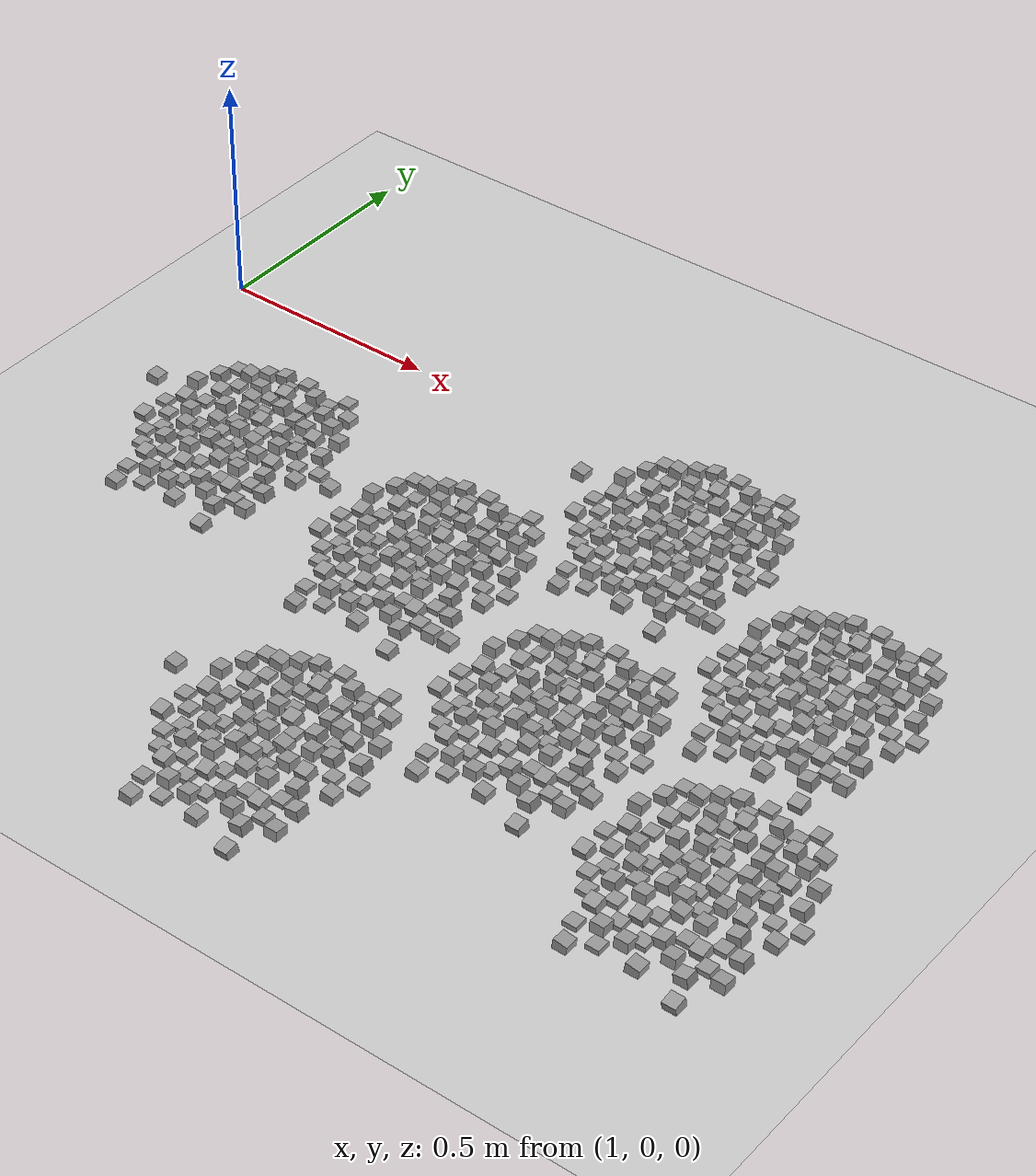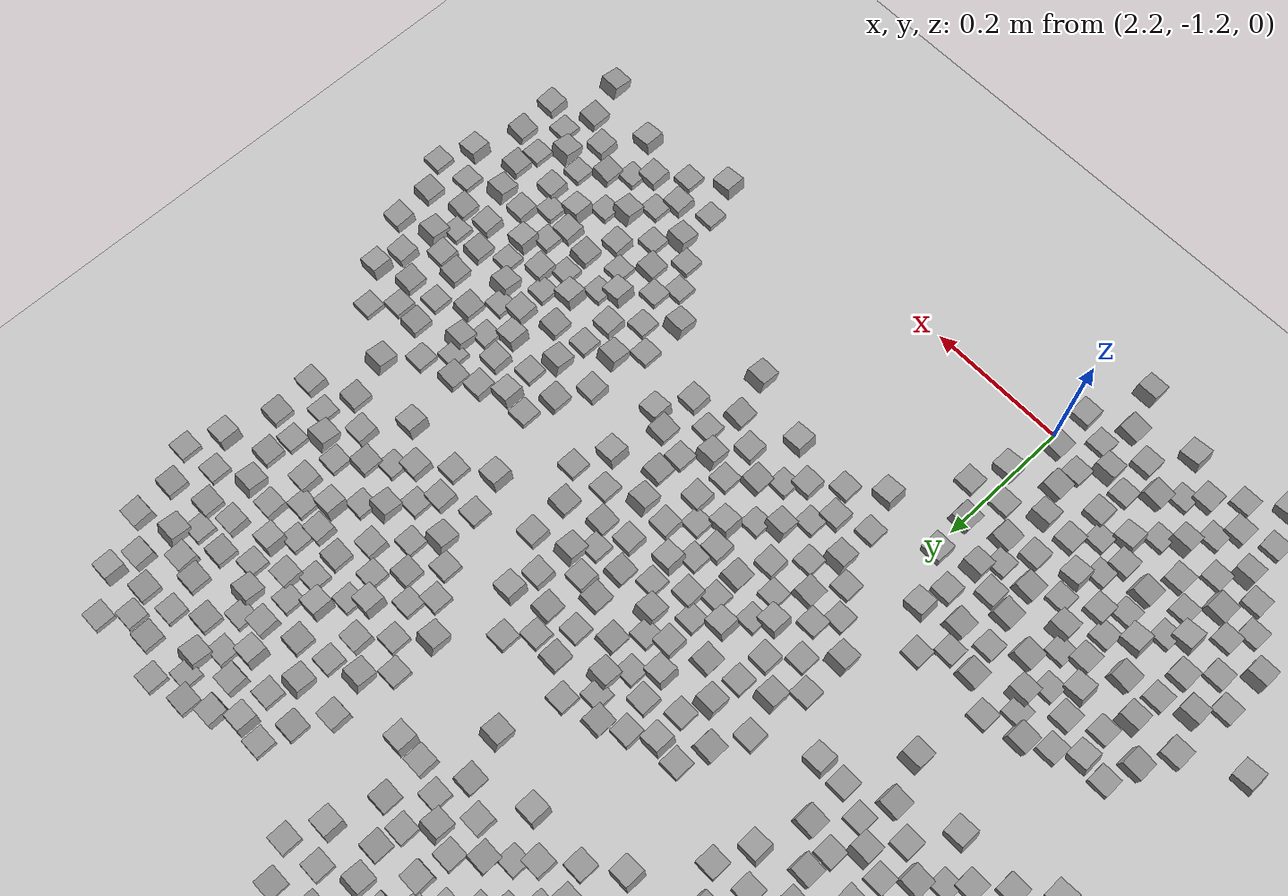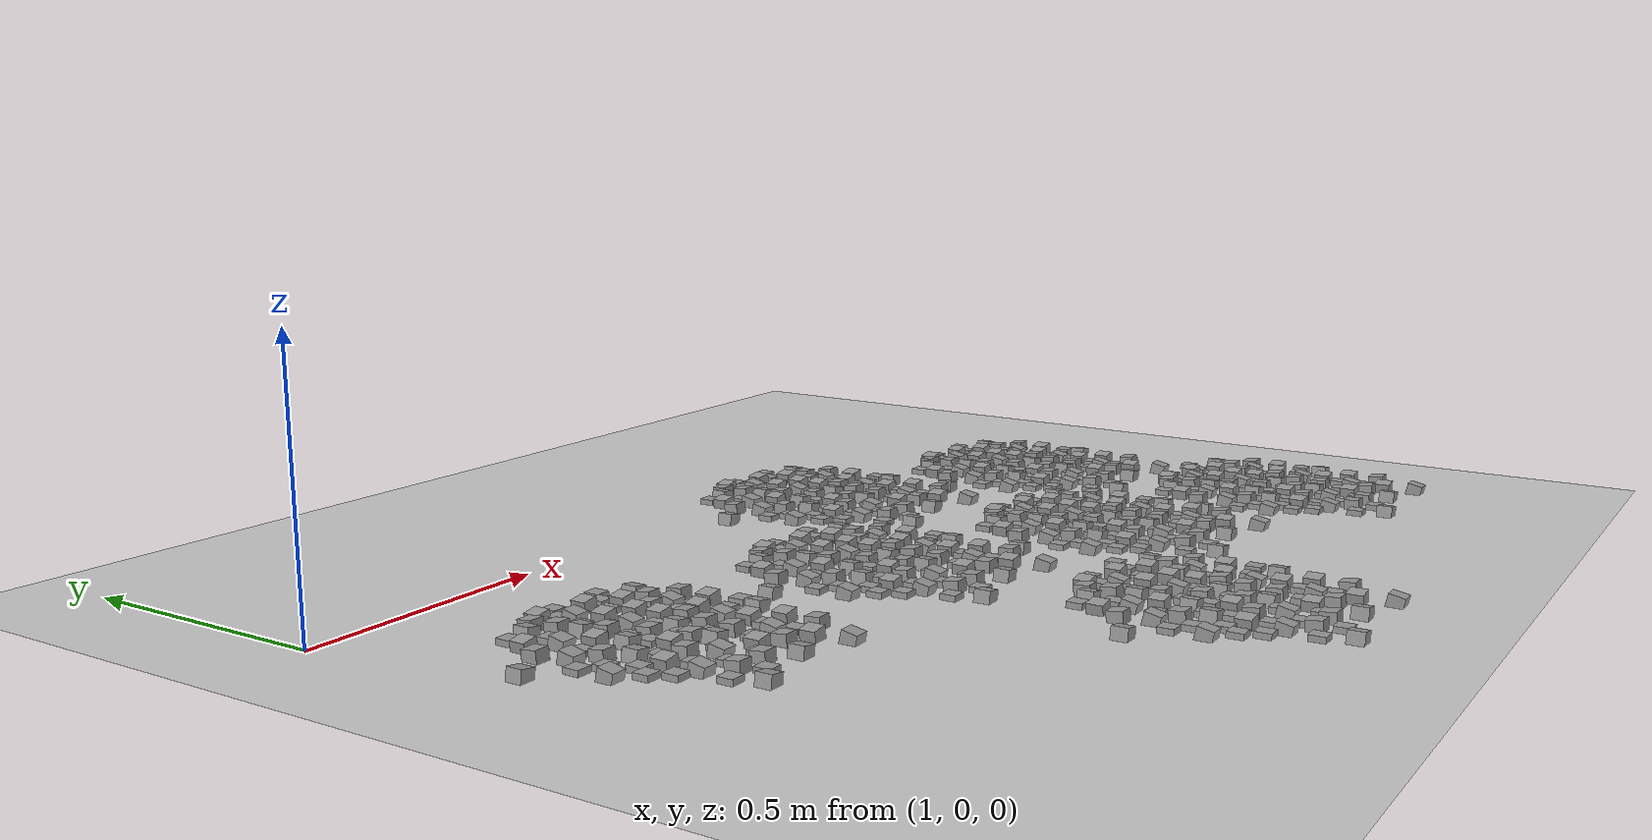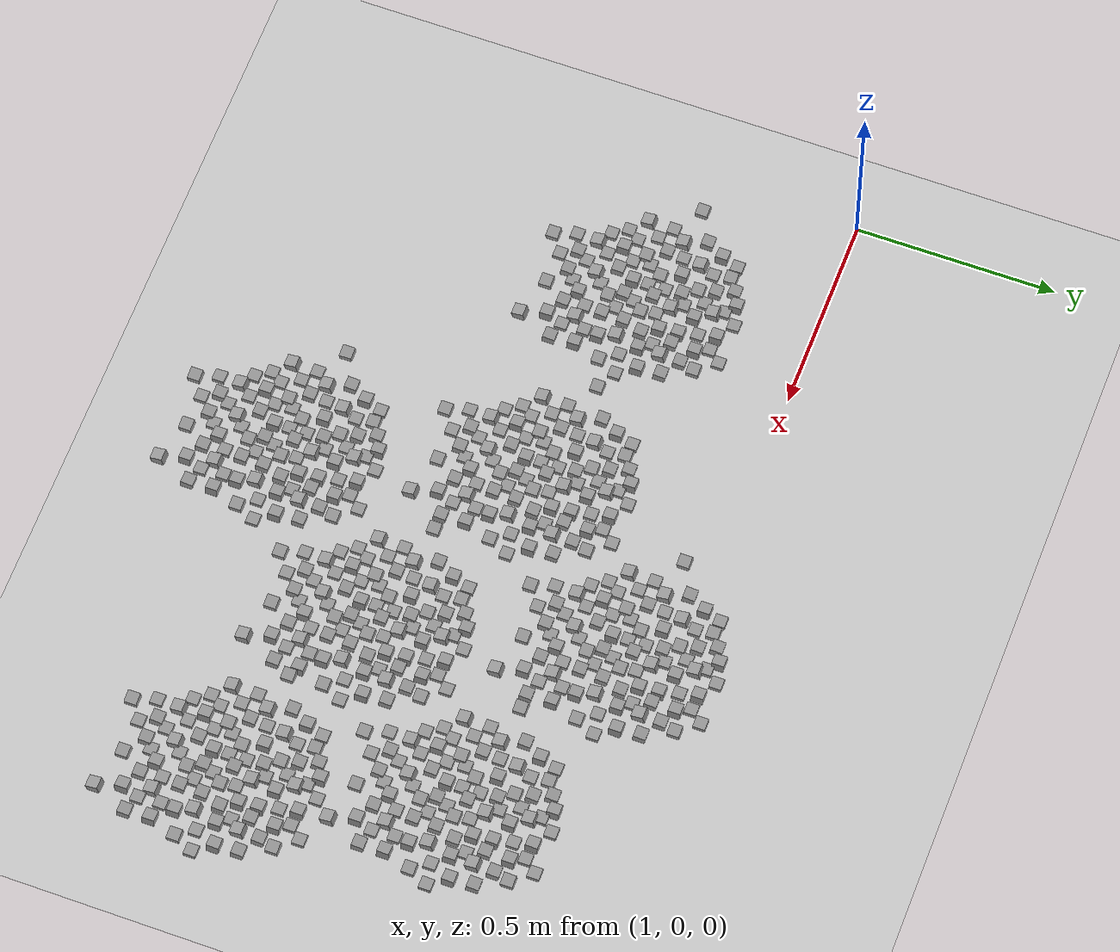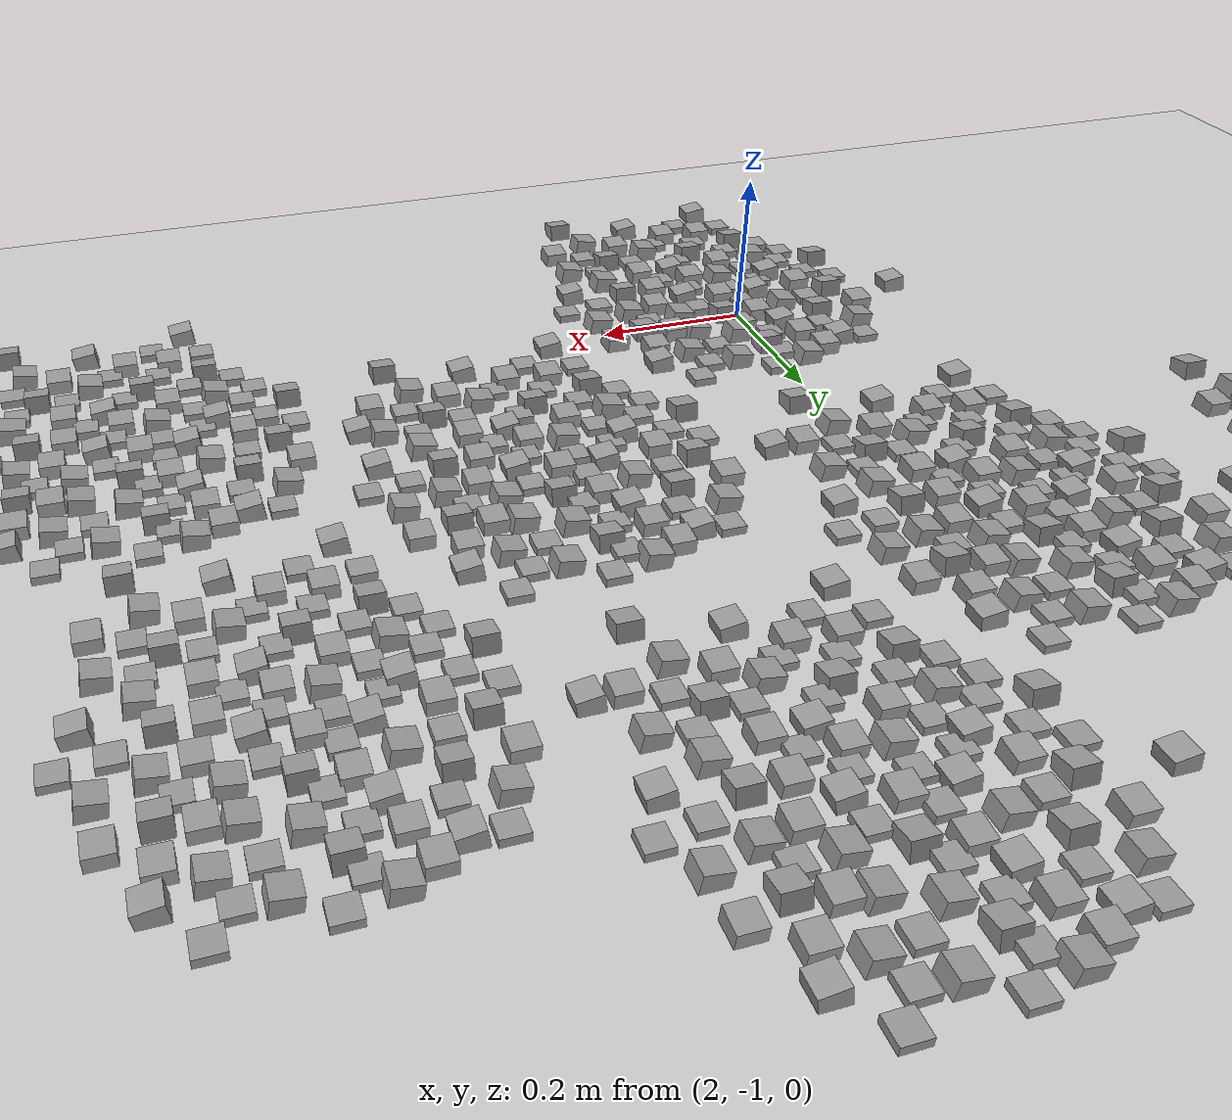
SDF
<sdf version="1.7">
 <world name="default">
  <light name="sun" type="directional">
   <pose>0 0 10 0 -0 0</pose>
   <diffuse>0.8 0.8 0.8 1</diffuse>
   <specular>0.2 0.2 0.2 1</specular>
   <attenuation>
    <range>1000</range>
    <constant>0.9</constant>
    <linear>0.01</linear>
    <quadratic>0.001</quadratic>
   </attenuation>
   <direction>-0.5 0.1 -0.9</direction>
   <spot><inner_angle>0</inner_angle><outer_angle>0</outer_angle><falloff>0</falloff></spot>
  </light>
  <gravity>0 0 -9.8</gravity>
  <magnetic_field>6e-06 2.3e-05 -4.2e-05</magnetic_field>
  <atmosphere type="adiabatic"/>
  <physics type="ode">
   <max_step_size>0.001</max_step_size>
   <real_time_factor>1</real_time_factor>
   <real_time_update_rate>1000</real_time_update_rate>
  </physics>
  <scene><ambient>0.4 0.4 0.4 1</ambient><background>0.7 0.7 0.7 1</background><shadows>1</shadows></scene>
  <spherical_coordinates>
   <surface_model>EARTH_WGS84</surface_model>
   <latitude_deg>0</latitude_deg>
   <longitude_deg>0</longitude_deg>
   <elevation>0</elevation>
   <heading_deg>0</heading_deg>
  </spherical_coordinates>
  <model name="ground_plane">
   <static>1</static>
   <link name="link">
    <collision name="collision">
     <geometry><plane><normal>0 0 1</normal><size>100 100</size></plane></geometry>
     <surface><friction><ode><mu>100</mu><mu2>50</mu2></ode></friction></surface>
    </collision>
    <visual name="visual">
     <cast_shadows>0</cast_shadows>
     <geometry><plane><normal>0 0 1</normal><size>100 100</size></plane></geometry>
     <material>
      <script><uri>file://media/materials/scripts/gazebo.material</uri><name>Gazebo/Grey</name></script>
     </material>
    </visual>
   </link>
  </model>
  <model name="stone_road_1">
   <link name="link_0">
    <inertial>
     <mass>1</mass>
     <inertia>
      <ixx>0.166667</ixx>
      <ixy>0</ixy>
      <ixz>0</ixz>
      <iyy>0.166667</iyy>
      <iyz>0</iyz>
      <izz>0.166667</izz>
     </inertia>
    </inertial>
    <pose>-0.171827 0.03973 0.003778 0.2 -0 0</pose>
    <kinematic>1</kinematic>
    <visual name="visual">
     <geometry><box><size>0.03 0.03 0.03</size></box></geometry>
     <material>
      <lighting>1</lighting>
      <script><uri>file://media/materials/scripts/gazebo.material</uri><name>Gazebo/Grey</name></script>
      <shader type="pixel"><normal_map>__default__</normal_map></shader>
      <ambient>0.3 0.3 0.3 1</ambient>
      <diffuse>0.7 0.7 0.7 1</diffuse>
      <specular>0.01 0.01 0.01 1</specular>
      <emissive>0 0 0 1</emissive>
     </material>
    </visual>
    <collision name="collision">
     <geometry><box><size>0.03 0.03 0.03</size></box></geometry>
     <surface>
      <friction>
       <ode><mu>1</mu><mu2>1</mu2><fdir1>0 0 0</fdir1><slip1>0</slip1><slip2>0</slip2></ode>
       <torsional>
        <coefficient>1</coefficient>
        <patch_radius>0</patch_radius>
        <surface_radius>0</surface_radius>
        <use_patch_radius>1</use_patch_radius>
        <ode><slip>0</slip></ode>
       </torsional>
      </friction>
      <bounce><restitution_coefficient>0</restitution_coefficient><threshold>1e+06</threshold></bounce>
      <contact>
       <collide_without_contact>0</collide_without_contact>
       <collide_without_contact_bitmask>1</collide_without_contact_bitmask>
       <collide_bitmask>1</collide_bitmask>
       <ode>
        <soft_cfm>0</soft_cfm>
        <soft_erp>0.2</soft_erp>
        <kp>1e+13</kp>
        <kd>1</kd>
        <max_vel>0.01</max_vel>
        <min_depth>0</min_depth>
       </ode>
       <bullet>
        <split_impulse>1</split_impulse>
        <split_impulse_penetration_threshold>-0.01</split_impulse_penetration_threshold>
        <soft_cfm>0</soft_cfm>
        <soft_erp>0.2</soft_erp>
        <kp>1e+13</kp>
        <kd>1</kd>
       </bullet>
      </contact>
     </surface>
    </collision>
   </link>
   <link name="link_0_clone_0">
    <inertial>
     <mass>1</mass>
     <inertia>
      <ixx>0.166667</ixx>
      <ixy>0</ixy>
      <ixz>0</ixz>
      <iyy>0.166667</iyy>
      <iyz>0</iyz>
      <izz>0.166667</izz>
     </inertia>
    </inertial>
    <pose>-0.104982 -0.15412 0.003778 0.2 -0 0</pose>
    <kinematic>1</kinematic>
    <visual name="visual">
     <geometry><box><size>0.03 0.03 0.03</size></box></geometry>
     <material>
      <lighting>1</lighting>
      <script><uri>file://media/materials/scripts/gazebo.material</uri><name>Gazebo/Grey</name></script>
      <shader type="pixel"><normal_map>__default__</normal_map></shader>
      <ambient>0.3 0.3 0.3 1</ambient>
      <diffuse>0.7 0.7 0.7 1</diffuse>
      <specular>0.01 0.01 0.01 1</specular>
      <emissive>0 0 0 1</emissive>
     </material>
    </visual>
    <collision name="collision">
     <geometry><box><size>0.03 0.03 0.03</size></box></geometry>
     <surface>
      <friction>
       <ode><mu>1</mu><mu2>1</mu2><fdir1>0 0 0</fdir1><slip1>0</slip1><slip2>0</slip2></ode>
       <torsional>
        <coefficient>1</coefficient>
        <patch_radius>0</patch_radius>
        <surface_radius>0</surface_radius>
        <use_patch_radius>1</use_patch_radius>
        <ode><slip>0</slip></ode>
       </torsional>
      </friction>
      <bounce><restitution_coefficient>0</restitution_coefficient><threshold>1e+06</threshold></bounce>
      <contact>
       <collide_without_contact>0</collide_without_contact>
       <collide_without_contact_bitmask>1</collide_without_contact_bitmask>
       <collide_bitmask>1</collide_bitmask>
       <ode>
        <soft_cfm>0</soft_cfm>
        <soft_erp>0.2</soft_erp>
        <kp>1e+13</kp>
        <kd>1</kd>
        <max_vel>0.01</max_vel>
        <min_depth>0</min_depth>
       </ode>
       <bullet>
        <split_impulse>1</split_impulse>
        <split_impulse_penetration_threshold>-0.01</split_impulse_penetration_threshold>
        <soft_cfm>0</soft_cfm>
        <soft_erp>0.2</soft_erp>
        <kp>1e+13</kp>
        <kd>1</kd>
       </bullet>
      </contact>
     </surface>
    </collision>
   </link>
   <link name="link_0_clone_1">
    <inertial>
     <mass>1</mass>
     <inertia>
      <ixx>0.166667</ixx>
      <ixy>0</ixy>
      <ixz>0</ixz>
      <iyy>0.166667</iyy>
      <iyz>0</iyz>
      <izz>0.166667</izz>
     </inertia>
    </inertial>
    <pose>-0.022921 -0.129606 0.003778 0.2 -0 0</pose>
    <kinematic>1</kinematic>
    <visual name="visual">
     <geometry><box><size>0.03 0.03 0.03</size></box></geometry>
     <material>
      <lighting>1</lighting>
      <script><uri>file://media/materials/scripts/gazebo.material</uri><name>Gazebo/Grey</name></script>
      <shader type="pixel"><normal_map>__default__</normal_map></shader>
      <ambient>0.3 0.3 0.3 1</ambient>
      <diffuse>0.7 0.7 0.7 1</diffuse>
      <specular>0.01 0.01 0.01 1</specular>
      <emissive>0 0 0 1</emissive>
     </material>
    </visual>
    <collision name="collision">
     <geometry><box><size>0.03 0.03 0.03</size></box></geometry>
     <surface>
      <friction>
       <ode><mu>1</mu><mu2>1</mu2><fdir1>0 0 0</fdir1><slip1>0</slip1><slip2>0</slip2></ode>
       <torsional>
        <coefficient>1</coefficient>
        <patch_radius>0</patch_radius>
        <surface_radius>0</surface_radius>
        <use_patch_radius>1</use_patch_radius>
        <ode><slip>0</slip></ode>
       </torsional>
      </friction>
      <bounce><restitution_coefficient>0</restitution_coefficient><threshold>1e+06</threshold></bounce>
      <contact>
       <collide_without_contact>0</collide_without_contact>
       <collide_without_contact_bitmask>1</collide_without_contact_bitmask>
       <collide_bitmask>1</collide_bitmask>
       <ode>
        <soft_cfm>0</soft_cfm>
        <soft_erp>0.2</soft_erp>
        <kp>1e+13</kp>
        <kd>1</kd>
        <max_vel>0.01</max_vel>
        <min_depth>0</min_depth>
       </ode>
       <bullet>
        <split_impulse>1</split_impulse>
        <split_impulse_penetration_threshold>-0.01</split_impulse_penetration_threshold>
        <soft_cfm>0</soft_cfm>
        <soft_erp>0.2</soft_erp>
        <kp>1e+13</kp>
        <kd>1</kd>
       </bullet>
      </contact>
     </surface>
    </collision>
   </link>
   <link name="link_0_clone_10">
    <inertial>
     <mass>1</mass>
     <inertia>
      <ixx>0.166667</ixx>
      <ixy>0</ixy>
      <ixz>0</ixz>
      <iyy>0.166667</iyy>
      <iyz>0</iyz>
      <izz>0.166667</izz>
     </inertia>
    </inertial>
    <pose>-0.01295 0.17123 0.003778 0.2 -0 0</pose>
    <kinematic>1</kinematic>
    <visual name="visual">
     <geometry><box><size>0.03 0.03 0.03</size></box></geometry>
     <material>
      <lighting>1</lighting>
      <script><uri>file://media/materials/scripts/gazebo.material</uri><name>Gazebo/Grey</name></script>
      <shader type="pixel"><normal_map>__default__</normal_map></shader>
      <ambient>0.3 0.3 0.3 1</ambient>
      <diffuse>0.7 0.7 0.7 1</diffuse>
      <specular>0.01 0.01 0.01 1</specular>
      <emissive>0 0 0 1</emissive>
     </material>
    </visual>
    <collision name="collision">
     <geometry><box><size>0.03 0.03 0.03</size></box></geometry>
     <surface>
      <friction>
       <ode><mu>1</mu><mu2>1</mu2><fdir1>0 0 0</fdir1><slip1>0</slip1><slip2>0</slip2></ode>
       <torsional>
        <coefficient>1</coefficient>
        <patch_radius>0</patch_radius>
        <surface_radius>0</surface_radius>
        <use_patch_radius>1</use_patch_radius>
        <ode><slip>0</slip></ode>
       </torsional>
      </friction>
      <bounce><restitution_coefficient>0</restitution_coefficient><threshold>1e+06</threshold></bounce>
      <contact>
       <collide_without_contact>0</collide_without_contact>
       <collide_without_contact_bitmask>1</collide_without_contact_bitmask>
       <collide_bitmask>1</collide_bitmask>
       <ode>
        <soft_cfm>0</soft_cfm>
        <soft_erp>0.2</soft_erp>
        <kp>1e+13</kp>
        <kd>1</kd>
        <max_vel>0.01</max_vel>
        <min_depth>0</min_depth>
       </ode>
       <bullet>
        <split_impulse>1</split_impulse>
        <split_impulse_penetration_threshold>-0.01</split_impulse_penetration_threshold>
        <soft_cfm>0</soft_cfm>
        <soft_erp>0.2</soft_erp>
        <kp>1e+13</kp>
        <kd>1</kd>
       </bullet>
      </contact>
     </surface>
    </collision>
   </link>
   <link name="link_0_clone_11">
    <inertial>
     <mass>1</mass>
     <inertia>
      <ixx>0.166667</ixx>
      <ixy>0</ixy>
      <ixz>0</ixz>
      <iyy>0.166667</iyy>
      <iyz>0</iyz>
      <izz>0.166667</izz>
     </inertia>
    </inertial>
    <pose>0.007758 0.071496 0.003778 0.2 -0 0</pose>
    <kinematic>1</kinematic>
    <visual name="visual">
     <geometry><box><size>0.03 0.03 0.03</size></box></geometry>
     <material>
      <lighting>1</lighting>
      <script><uri>file://media/materials/scripts/gazebo.material</uri><name>Gazebo/Grey</name></script>
      <shader type="pixel"><normal_map>__default__</normal_map></shader>
      <ambient>0.3 0.3 0.3 1</ambient>
      <diffuse>0.7 0.7 0.7 1</diffuse>
      <specular>0.01 0.01 0.01 1</specular>
      <emissive>0 0 0 1</emissive>
     </material>
    </visual>
    <collision name="collision">
     <geometry><box><size>0.03 0.03 0.03</size></box></geometry>
     <surface>
      <friction>
       <ode><mu>1</mu><mu2>1</mu2><fdir1>0 0 0</fdir1><slip1>0</slip1><slip2>0</slip2></ode>
       <torsional>
        <coefficient>1</coefficient>
        <patch_radius>0</patch_radius>
        <surface_radius>0</surface_radius>
        <use_patch_radius>1</use_patch_radius>
        <ode><slip>0</slip></ode>
       </torsional>
      </friction>
      <bounce><restitution_coefficient>0</restitution_coefficient><threshold>1e+06</threshold></bounce>
      <contact>
       <collide_without_contact>0</collide_without_contact>
       <collide_without_contact_bitmask>1</collide_without_contact_bitmask>
       <collide_bitmask>1</collide_bitmask>
       <ode>
        <soft_cfm>0</soft_cfm>
        <soft_erp>0.2</soft_erp>
        <kp>1e+13</kp>
        <kd>1</kd>
        <max_vel>0.01</max_vel>
        <min_depth>0</min_depth>
       </ode>
       <bullet>
        <split_impulse>1</split_impulse>
        <split_impulse_penetration_threshold>-0.01</split_impulse_penetration_threshold>
        <soft_cfm>0</soft_cfm>
        <soft_erp>0.2</soft_erp>
        <kp>1e+13</kp>
        <kd>1</kd>
       </bullet>
      </contact>
     </surface>
    </collision>
   </link>
   <link name="link_0_clone_12">
    <inertial>
     <mass>1</mass>
     <inertia>
      <ixx>0.166667</ixx>
      <ixy>0</ixy>
      <ixz>0</ixz>
      <iyy>0.166667</iyy>
      <iyz>0</iyz>
      <izz>0.166667</izz>
     </inertia>
    </inertial>
    <pose>0.142624 -0.262715 0.003778 0.2 -0 0</pose>
    <kinematic>1</kinematic>
    <visual name="visual">
     <geometry><box><size>0.03 0.03 0.03</size></box></geometry>
     <material>
      <lighting>1</lighting>
      <script><uri>file://media/materials/scripts/gazebo.material</uri><name>Gazebo/Grey</name></script>
      <shader type="pixel"><normal_map>__default__</normal_map></shader>
      <ambient>0.3 0.3 0.3 1</ambient>
      <diffuse>0.7 0.7 0.7 1</diffuse>
      <specular>0.01 0.01 0.01 1</specular>
      <emissive>0 0 0 1</emissive>
     </material>
    </visual>
    <collision name="collision">
     <geometry><box><size>0.03 0.03 0.03</size></box></geometry>
     <surface>
      <friction>
       <ode><mu>1</mu><mu2>1</mu2><fdir1>0 0 0</fdir1><slip1>0</slip1><slip2>0</slip2></ode>
       <torsional>
        <coefficient>1</coefficient>
        <patch_radius>0</patch_radius>
        <surface_radius>0</surface_radius>
        <use_patch_radius>1</use_patch_radius>
        <ode><slip>0</slip></ode>
       </torsional>
      </friction>
      <bounce><restitution_coefficient>0</restitution_coefficient><threshold>1e+06</threshold></bounce>
      <contact>
       <collide_without_contact>0</collide_without_contact>
       <collide_without_contact_bitmask>1</collide_without_contact_bitmask>
       <collide_bitmask>1</collide_bitmask>
       <ode>
        <soft_cfm>0</soft_cfm>
        <soft_erp>0.2</soft_erp>
        <kp>1e+13</kp>
        <kd>1</kd>
        <max_vel>0.01</max_vel>
        <min_depth>0</min_depth>
       </ode>
       <bullet>
        <split_impulse>1</split_impulse>
        <split_impulse_penetration_threshold>-0.01</split_impulse_penetration_threshold>
        <soft_cfm>0</soft_cfm>
        <soft_erp>0.2</soft_erp>
        <kp>1e+13</kp>
        <kd>1</kd>
       </bullet>
      </contact>
     </surface>
    </collision>
   </link>
   <link name="link_0_clone_13">
    <inertial>
     <mass>1</mass>
     <inertia>
      <ixx>0.166667</ixx>
      <ixy>0</ixy>
      <ixz>0</ixz>
      <iyy>0.166667</iyy>
      <iyz>0</iyz>
      <izz>0.166667</izz>
     </inertia>
    </inertial>
    <pose>0.107601 -0.134881 0.003778 0.2 -0 0</pose>
    <kinematic>1</kinematic>
    <visual name="visual">
     <geometry><box><size>0.03 0.03 0.03</size></box></geometry>
     <material>
      <lighting>1</lighting>
      <script><uri>file://media/materials/scripts/gazebo.material</uri><name>Gazebo/Grey</name></script>
      <shader type="pixel"><normal_map>__default__</normal_map></shader>
      <ambient>0.3 0.3 0.3 1</ambient>
      <diffuse>0.7 0.7 0.7 1</diffuse>
      <specular>0.01 0.01 0.01 1</specular>
      <emissive>0 0 0 1</emissive>
     </material>
    </visual>
    <collision name="collision">
     <geometry><box><size>0.03 0.03 0.03</size></box></geometry>
     <surface>
      <friction>
       <ode><mu>1</mu><mu2>1</mu2><fdir1>0 0 0</fdir1><slip1>0</slip1><slip2>0</slip2></ode>
       <torsional>
        <coefficient>1</coefficient>
        <patch_radius>0</patch_radius>
        <surface_radius>0</surface_radius>
        <use_patch_radius>1</use_patch_radius>
        <ode><slip>0</slip></ode>
       </torsional>
      </friction>
      <bounce><restitution_coefficient>0</restitution_coefficient><threshold>1e+06</threshold></bounce>
      <contact>
       <collide_without_contact>0</collide_without_contact>
       <collide_without_contact_bitmask>1</collide_without_contact_bitmask>
       <collide_bitmask>1</collide_bitmask>
       <ode>
        <soft_cfm>0</soft_cfm>
        <soft_erp>0.2</soft_erp>
        <kp>1e+13</kp>
        <kd>1</kd>
        <max_vel>0.01</max_vel>
        <min_depth>0</min_depth>
       </ode>
       <bullet>
        <split_impulse>1</split_impulse>
        <split_impulse_penetration_threshold>-0.01</split_impulse_penetration_threshold>
        <soft_cfm>0</soft_cfm>
        <soft_erp>0.2</soft_erp>
        <kp>1e+13</kp>
        <kd>1</kd>
       </bullet>
      </contact>
     </surface>
    </collision>
   </link>
   <link name="link_0_clone_2">
    <inertial>
     <mass>1</mass>
     <inertia>
      <ixx>0.166667</ixx>
      <ixy>0</ixy>
      <ixz>0</ixz>
      <iyy>0.166667</iyy>
      <iyz>0</iyz>
      <izz>0.166667</izz>
     </inertia>
    </inertial>
    <pose>-0.065685 0.018139 0.003778 0 0.15 0</pose>
    <kinematic>1</kinematic>
    <visual name="visual">
     <geometry><box><size>0.03 0.03 0.03</size></box></geometry>
     <material>
      <lighting>1</lighting>
      <script><uri>file://media/materials/scripts/gazebo.material</uri><name>Gazebo/Grey</name></script>
      <shader type="pixel"><normal_map>__default__</normal_map></shader>
      <ambient>0.3 0.3 0.3 1</ambient>
      <diffuse>0.7 0.7 0.7 1</diffuse>
      <specular>0.01 0.01 0.01 1</specular>
      <emissive>0 0 0 1</emissive>
     </material>
    </visual>
    <collision name="collision">
     <geometry><box><size>0.03 0.03 0.03</size></box></geometry>
     <surface>
      <friction>
       <ode><mu>1</mu><mu2>1</mu2><fdir1>0 0 0</fdir1><slip1>0</slip1><slip2>0</slip2></ode>
       <torsional>
        <coefficient>1</coefficient>
        <patch_radius>0</patch_radius>
        <surface_radius>0</surface_radius>
        <use_patch_radius>1</use_patch_radius>
        <ode><slip>0</slip></ode>
       </torsional>
      </friction>
      <bounce><restitution_coefficient>0</restitution_coefficient><threshold>1e+06</threshold></bounce>
      <contact>
       <collide_without_contact>0</collide_without_contact>
       <collide_without_contact_bitmask>1</collide_without_contact_bitmask>
       <collide_bitmask>1</collide_bitmask>
       <ode>
        <soft_cfm>0</soft_cfm>
        <soft_erp>0.2</soft_erp>
        <kp>1e+13</kp>
        <kd>1</kd>
        <max_vel>0.01</max_vel>
        <min_depth>0</min_depth>
       </ode>
       <bullet>
        <split_impulse>1</split_impulse>
        <split_impulse_penetration_threshold>-0.01</split_impulse_penetration_threshold>
        <soft_cfm>0</soft_cfm>
        <soft_erp>0.2</soft_erp>
        <kp>1e+13</kp>
        <kd>1</kd>
       </bullet>
      </contact>
     </surface>
    </collision>
   </link>
   <link name="link_0_clone_2_clone">
    <inertial>
     <mass>1</mass>
     <inertia>
      <ixx>0.166667</ixx>
      <ixy>0</ixy>
      <ixz>0</ixz>
      <iyy>0.166667</iyy>
      <iyz>0</iyz>
      <izz>0.166667</izz>
     </inertia>
    </inertial>
    <pose>-0.10771 -0.03187 0.003778 0 0.15 0</pose>
    <kinematic>1</kinematic>
    <visual name="visual">
     <geometry><box><size>0.03 0.03 0.03</size></box></geometry>
     <material>
      <lighting>1</lighting>
      <script><uri>file://media/materials/scripts/gazebo.material</uri><name>Gazebo/Grey</name></script>
      <shader type="pixel"><normal_map>__default__</normal_map></shader>
      <ambient>0.3 0.3 0.3 1</ambient>
      <diffuse>0.7 0.7 0.7 1</diffuse>
      <specular>0.01 0.01 0.01 1</specular>
      <emissive>0 0 0 1</emissive>
     </material>
    </visual>
    <collision name="collision">
     <geometry><box><size>0.03 0.03 0.03</size></box></geometry>
     <surface>
      <friction>
       <ode><mu>1</mu><mu2>1</mu2><fdir1>0 0 0</fdir1><slip1>0</slip1><slip2>0</slip2></ode>
       <torsional>
        <coefficient>1</coefficient>
        <patch_radius>0</patch_radius>
        <surface_radius>0</surface_radius>
        <use_patch_radius>1</use_patch_radius>
        <ode><slip>0</slip></ode>
       </torsional>
      </friction>
      <bounce><restitution_coefficient>0</restitution_coefficient><threshold>1e+06</threshold></bounce>
      <contact>
       <collide_without_contact>0</collide_without_contact>
       <collide_without_contact_bitmask>1</collide_without_contact_bitmask>
       <collide_bitmask>1</collide_bitmask>
       <ode>
        <soft_cfm>0</soft_cfm>
        <soft_erp>0.2</soft_erp>
        <kp>1e+13</kp>
        <kd>1</kd>
        <max_vel>0.01</max_vel>
        <min_depth>0</min_depth>
       </ode>
       <bullet>
        <split_impulse>1</split_impulse>
        <split_impulse_penetration_threshold>-0.01</split_impulse_penetration_threshold>
        <soft_cfm>0</soft_cfm>
        <soft_erp>0.2</soft_erp>
        <kp>1e+13</kp>
        <kd>1</kd>
       </bullet>
      </contact>
     </surface>
    </collision>
   </link>
   <link name="link_0_clone_2_clone_0">
    <inertial>
     <mass>1</mass>
     <inertia>
      <ixx>0.166667</ixx>
      <ixy>0</ixy>
      <ixz>0</ixz>
      <iyy>0.166667</iyy>
      <iyz>0</iyz>
      <izz>0.166667</izz>
     </inertia>
    </inertial>
    <pose>0.026852 -0.0813 0.003778 0 0.15 0</pose>
    <kinematic>1</kinematic>
    <visual name="visual">
     <geometry><box><size>0.03 0.03 0.03</size></box></geometry>
     <material>
      <lighting>1</lighting>
      <script><uri>file://media/materials/scripts/gazebo.material</uri><name>Gazebo/Grey</name></script>
      <shader type="pixel"><normal_map>__default__</normal_map></shader>
      <ambient>0.3 0.3 0.3 1</ambient>
      <diffuse>0.7 0.7 0.7 1</diffuse>
      <specular>0.01 0.01 0.01 1</specular>
      <emissive>0 0 0 1</emissive>
     </material>
    </visual>
    <collision name="collision">
     <geometry><box><size>0.03 0.03 0.03</size></box></geometry>
     <surface>
      <friction>
       <ode><mu>1</mu><mu2>1</mu2><fdir1>0 0 0</fdir1><slip1>0</slip1><slip2>0</slip2></ode>
       <torsional>
        <coefficient>1</coefficient>
        <patch_radius>0</patch_radius>
        <surface_radius>0</surface_radius>
        <use_patch_radius>1</use_patch_radius>
        <ode><slip>0</slip></ode>
       </torsional>
      </friction>
      <bounce><restitution_coefficient>0</restitution_coefficient><threshold>1e+06</threshold></bounce>
      <contact>
       <collide_without_contact>0</collide_without_contact>
       <collide_without_contact_bitmask>1</collide_without_contact_bitmask>
       <collide_bitmask>1</collide_bitmask>
       <ode>
        <soft_cfm>0</soft_cfm>
        <soft_erp>0.2</soft_erp>
        <kp>1e+13</kp>
        <kd>1</kd>
        <max_vel>0.01</max_vel>
        <min_depth>0</min_depth>
       </ode>
       <bullet>
        <split_impulse>1</split_impulse>
        <split_impulse_penetration_threshold>-0.01</split_impulse_penetration_threshold>
        <soft_cfm>0</soft_cfm>
        <soft_erp>0.2</soft_erp>
        <kp>1e+13</kp>
        <kd>1</kd>
       </bullet>
      </contact>
     </surface>
    </collision>
   </link>
   <link name="link_0_clone_2_clone_1">
    <inertial>
     <mass>1</mass>
     <inertia>
      <ixx>0.166667</ixx>
      <ixy>0</ixy>
      <ixz>0</ixz>
      <iyy>0.166667</iyy>
      <iyz>0</iyz>
      <izz>0.166667</izz>
     </inertia>
    </inertial>
    <pose>0.041447 0.006316 0.003778 0 0.15 0</pose>
    <kinematic>1</kinematic>
    <visual name="visual">
     <geometry><box><size>0.03 0.03 0.03</size></box></geometry>
     <material>
      <lighting>1</lighting>
      <script><uri>file://media/materials/scripts/gazebo.material</uri><name>Gazebo/Grey</name></script>
      <shader type="pixel"><normal_map>__default__</normal_map></shader>
      <ambient>0.3 0.3 0.3 1</ambient>
      <diffuse>0.7 0.7 0.7 1</diffuse>
      <specular>0.01 0.01 0.01 1</specular>
      <emissive>0 0 0 1</emissive>
     </material>
    </visual>
    <collision name="collision">
     <geometry><box><size>0.03 0.03 0.03</size></box></geometry>
     <surface>
      <friction>
       <ode><mu>1</mu><mu2>1</mu2><fdir1>0 0 0</fdir1><slip1>0</slip1><slip2>0</slip2></ode>
       <torsional>
        <coefficient>1</coefficient>
        <patch_radius>0</patch_radius>
        <surface_radius>0</surface_radius>
        <use_patch_radius>1</use_patch_radius>
        <ode><slip>0</slip></ode>
       </torsional>
      </friction>
      <bounce><restitution_coefficient>0</restitution_coefficient><threshold>1e+06</threshold></bounce>
      <contact>
       <collide_without_contact>0</collide_without_contact>
       <collide_without_contact_bitmask>1</collide_without_contact_bitmask>
       <collide_bitmask>1</collide_bitmask>
       <ode>
        <soft_cfm>0</soft_cfm>
        <soft_erp>0.2</soft_erp>
        <kp>1e+13</kp>
        <kd>1</kd>
        <max_vel>0.01</max_vel>
        <min_depth>0</min_depth>
       </ode>
       <bullet>
        <split_impulse>1</split_impulse>
        <split_impulse_penetration_threshold>-0.01</split_impulse_penetration_threshold>
        <soft_cfm>0</soft_cfm>
        <soft_erp>0.2</soft_erp>
        <kp>1e+13</kp>
        <kd>1</kd>
       </bullet>
      </contact>
     </surface>
    </collision>
   </link>
   <link name="link_0_clone_2_clone_2">
    <inertial>
     <mass>1</mass>
     <inertia>
      <ixx>0.166667</ixx>
      <ixy>0</ixy>
      <ixz>0</ixz>
      <iyy>0.166667</iyy>
      <iyz>0</iyz>
      <izz>0.166667</izz>
     </inertia>
    </inertial>
    <pose>0.066563 0.110568 0.003778 0 -0.15 0</pose>
    <kinematic>1</kinematic>
    <visual name="visual">
     <geometry><box><size>0.03 0.03 0.03</size></box></geometry>
     <material>
      <lighting>1</lighting>
      <script><uri>file://media/materials/scripts/gazebo.material</uri><name>Gazebo/Grey</name></script>
      <shader type="pixel"><normal_map>__default__</normal_map></shader>
      <ambient>0.3 0.3 0.3 1</ambient>
      <diffuse>0.7 0.7 0.7 1</diffuse>
      <specular>0.01 0.01 0.01 1</specular>
      <emissive>0 0 0 1</emissive>
     </material>
    </visual>
    <collision name="collision">
     <geometry><box><size>0.03 0.03 0.03</size></box></geometry>
     <surface>
      <friction>
       <ode><mu>1</mu><mu2>1</mu2><fdir1>0 0 0</fdir1><slip1>0</slip1><slip2>0</slip2></ode>
       <torsional>
        <coefficient>1</coefficient>
        <patch_radius>0</patch_radius>
        <surface_radius>0</surface_radius>
        <use_patch_radius>1</use_patch_radius>
        <ode><slip>0</slip></ode>
       </torsional>
      </friction>
      <bounce><restitution_coefficient>0</restitution_coefficient><threshold>1e+06</threshold></bounce>
      <contact>
       <collide_without_contact>0</collide_without_contact>
       <collide_without_contact_bitmask>1</collide_without_contact_bitmask>
       <collide_bitmask>1</collide_bitmask>
       <ode>
        <soft_cfm>0</soft_cfm>
        <soft_erp>0.2</soft_erp>
        <kp>1e+13</kp>
        <kd>1</kd>
        <max_vel>0.01</max_vel>
        <min_depth>0</min_depth>
       </ode>
       <bullet>
        <split_impulse>1</split_impulse>
        <split_impulse_penetration_threshold>-0.01</split_impulse_penetration_threshold>
        <soft_cfm>0</soft_cfm>
        <soft_erp>0.2</soft_erp>
        <kp>1e+13</kp>
        <kd>1</kd>
       </bullet>
      </contact>
     </surface>
    </collision>
   </link>
   <link name="link_0_clone_2_clone_2_clone">
    <inertial>
     <mass>1</mass>
     <inertia>
      <ixx>0.166667</ixx>
      <ixy>0</ixy>
      <ixz>0</ixz>
      <iyy>0.166667</iyy>
      <iyz>0</iyz>
      <izz>0.166667</izz>
     </inertia>
    </inertial>
    <pose>0.189059 0.051135 0.003778 0 -0.15 0</pose>
    <kinematic>1</kinematic>
    <visual name="visual">
     <geometry><box><size>0.03 0.03 0.03</size></box></geometry>
     <material>
      <lighting>1</lighting>
      <script><uri>file://media/materials/scripts/gazebo.material</uri><name>Gazebo/Grey</name></script>
      <shader type="pixel"><normal_map>__default__</normal_map></shader>
      <ambient>0.3 0.3 0.3 1</ambient>
      <diffuse>0.7 0.7 0.7 1</diffuse>
      <specular>0.01 0.01 0.01 1</specular>
      <emissive>0 0 0 1</emissive>
     </material>
    </visual>
    <collision name="collision">
     <geometry><box><size>0.03 0.03 0.03</size></box></geometry>
     <surface>
      <friction>
       <ode><mu>1</mu><mu2>1</mu2><fdir1>0 0 0</fdir1><slip1>0</slip1><slip2>0</slip2></ode>
       <torsional>
        <coefficient>1</coefficient>
        <patch_radius>0</patch_radius>
        <surface_radius>0</surface_radius>
        <use_patch_radius>1</use_patch_radius>
        <ode><slip>0</slip></ode>
       </torsional>
      </friction>
      <bounce><restitution_coefficient>0</restitution_coefficient><threshold>1e+06</threshold></bounce>
      <contact>
       <collide_without_contact>0</collide_without_contact>
       <collide_without_contact_bitmask>1</collide_without_contact_bitmask>
       <collide_bitmask>1</collide_bitmask>
       <ode>
        <soft_cfm>0</soft_cfm>
        <soft_erp>0.2</soft_erp>
        <kp>1e+13</kp>
        <kd>1</kd>
        <max_vel>0.01</max_vel>
        <min_depth>0</min_depth>
       </ode>
       <bullet>
        <split_impulse>1</split_impulse>
        <split_impulse_penetration_threshold>-0.01</split_impulse_penetration_threshold>
        <soft_cfm>0</soft_cfm>
        <soft_erp>0.2</soft_erp>
        <kp>1e+13</kp>
        <kd>1</kd>
       </bullet>
      </contact>
     </surface>
    </collision>
   </link>
   <link name="link_0_clone_2_clone_2_clone_0">
    <inertial>
     <mass>1</mass>
     <inertia>
      <ixx>0.166667</ixx>
      <ixy>0</ixy>
      <ixz>0</ixz>
      <iyy>0.166667</iyy>
      <iyz>0</iyz>
      <izz>0.166667</izz>
     </inertia>
    </inertial>
    <pose>-0.032874 -0.039714 0.003778 0 -0.15 0</pose>
    <kinematic>1</kinematic>
    <visual name="visual">
     <geometry><box><size>0.03 0.03 0.03</size></box></geometry>
     <material>
      <lighting>1</lighting>
      <script><uri>file://media/materials/scripts/gazebo.material</uri><name>Gazebo/Grey</name></script>
      <shader type="pixel"><normal_map>__default__</normal_map></shader>
      <ambient>0.3 0.3 0.3 1</ambient>
      <diffuse>0.7 0.7 0.7 1</diffuse>
      <specular>0.01 0.01 0.01 1</specular>
      <emissive>0 0 0 1</emissive>
     </material>
    </visual>
    <collision name="collision">
     <geometry><box><size>0.03 0.03 0.03</size></box></geometry>
     <surface>
      <friction>
       <ode><mu>1</mu><mu2>1</mu2><fdir1>0 0 0</fdir1><slip1>0</slip1><slip2>0</slip2></ode>
       <torsional>
        <coefficient>1</coefficient>
        <patch_radius>0</patch_radius>
        <surface_radius>0</surface_radius>
        <use_patch_radius>1</use_patch_radius>
        <ode><slip>0</slip></ode>
       </torsional>
      </friction>
      <bounce><restitution_coefficient>0</restitution_coefficient><threshold>1e+06</threshold></bounce>
      <contact>
       <collide_without_contact>0</collide_without_contact>
       <collide_without_contact_bitmask>1</collide_without_contact_bitmask>
       <collide_bitmask>1</collide_bitmask>
       <ode>
        <soft_cfm>0</soft_cfm>
        <soft_erp>0.2</soft_erp>
        <kp>1e+13</kp>
        <kd>1</kd>
        <max_vel>0.01</max_vel>
        <min_depth>0</min_depth>
       </ode>
       <bullet>
        <split_impulse>1</split_impulse>
        <split_impulse_penetration_threshold>-0.01</split_impulse_penetration_threshold>
        <soft_cfm>0</soft_cfm>
        <soft_erp>0.2</soft_erp>
        <kp>1e+13</kp>
        <kd>1</kd>
       </bullet>
      </contact>
     </surface>
    </collision>
   </link>
   <link name="link_0_clone_2_clone_2_clone_1">
    <inertial>
     <mass>1</mass>
     <inertia>
      <ixx>0.166667</ixx>
      <ixy>0</ixy>
      <ixz>0</ixz>
      <iyy>0.166667</iyy>
      <iyz>0</iyz>
      <izz>0.166667</izz>
     </inertia>
    </inertial>
    <pose>-0.085624 0.065625 0.003778 0 -0.15 0</pose>
    <kinematic>1</kinematic>
    <visual name="visual">
     <geometry><box><size>0.03 0.03 0.03</size></box></geometry>
     <material>
      <lighting>1</lighting>
      <script><uri>file://media/materials/scripts/gazebo.material</uri><name>Gazebo/Grey</name></script>
      <shader type="pixel"><normal_map>__default__</normal_map></shader>
      <ambient>0.3 0.3 0.3 1</ambient>
      <diffuse>0.7 0.7 0.7 1</diffuse>
      <specular>0.01 0.01 0.01 1</specular>
      <emissive>0 0 0 1</emissive>
     </material>
    </visual>
    <collision name="collision">
     <geometry><box><size>0.03 0.03 0.03</size></box></geometry>
     <surface>
      <friction>
       <ode><mu>1</mu><mu2>1</mu2><fdir1>0 0 0</fdir1><slip1>0</slip1><slip2>0</slip2></ode>
       <torsional>
        <coefficient>1</coefficient>
        <patch_radius>0</patch_radius>
        <surface_radius>0</surface_radius>
        <use_patch_radius>1</use_patch_radius>
        <ode><slip>0</slip></ode>
       </torsional>
      </friction>
      <bounce><restitution_coefficient>0</restitution_coefficient><threshold>1e+06</threshold></bounce>
      <contact>
       <collide_without_contact>0</collide_without_contact>
       <collide_without_contact_bitmask>1</collide_without_contact_bitmask>
       <collide_bitmask>1</collide_bitmask>
       <ode>
        <soft_cfm>0</soft_cfm>
        <soft_erp>0.2</soft_erp>
        <kp>1e+13</kp>
        <kd>1</kd>
        <max_vel>0.01</max_vel>
        <min_depth>0</min_depth>
       </ode>
       <bullet>
        <split_impulse>1</split_impulse>
        <split_impulse_penetration_threshold>-0.01</split_impulse_penetration_threshold>
        <soft_cfm>0</soft_cfm>
        <soft_erp>0.2</soft_erp>
        <kp>1e+13</kp>
        <kd>1</kd>
       </bullet>
      </contact>
     </surface>
    </collision>
   </link>
   <link name="link_0_clone_2_clone_2_clone_10">
    <inertial>
     <mass>1</mass>
     <inertia>
      <ixx>0.166667</ixx>
      <ixy>0</ixy>
      <ixz>0</ixz>
      <iyy>0.166667</iyy>
      <iyz>0</iyz>
      <izz>0.166667</izz>
     </inertia>
    </inertial>
    <pose>0.09869 0.163436 0.003778 0 -0.15 0</pose>
    <kinematic>1</kinematic>
    <visual name="visual">
     <geometry><box><size>0.03 0.03 0.03</size></box></geometry>
     <material>
      <lighting>1</lighting>
      <script><uri>file://media/materials/scripts/gazebo.material</uri><name>Gazebo/Grey</name></script>
      <shader type="pixel"><normal_map>__default__</normal_map></shader>
      <ambient>0.3 0.3 0.3 1</ambient>
      <diffuse>0.7 0.7 0.7 1</diffuse>
      <specular>0.01 0.01 0.01 1</specular>
      <emissive>0 0 0 1</emissive>
     </material>
    </visual>
    <collision name="collision">
     <geometry><box><size>0.03 0.03 0.03</size></box></geometry>
     <surface>
      <friction>
       <ode><mu>1</mu><mu2>1</mu2><fdir1>0 0 0</fdir1><slip1>0</slip1><slip2>0</slip2></ode>
       <torsional>
        <coefficient>1</coefficient>
        <patch_radius>0</patch_radius>
        <surface_radius>0</surface_radius>
        <use_patch_radius>1</use_patch_radius>
        <ode><slip>0</slip></ode>
       </torsional>
      </friction>
      <bounce><restitution_coefficient>0</restitution_coefficient><threshold>1e+06</threshold></bounce>
      <contact>
       <collide_without_contact>0</collide_without_contact>
       <collide_without_contact_bitmask>1</collide_without_contact_bitmask>
       <collide_bitmask>1</collide_bitmask>
       <ode>
        <soft_cfm>0</soft_cfm>
        <soft_erp>0.2</soft_erp>
        <kp>1e+13</kp>
        <kd>1</kd>
        <max_vel>0.01</max_vel>
        <min_depth>0</min_depth>
       </ode>
       <bullet>
        <split_impulse>1</split_impulse>
        <split_impulse_penetration_threshold>-0.01</split_impulse_penetration_threshold>
        <soft_cfm>0</soft_cfm>
        <soft_erp>0.2</soft_erp>
        <kp>1e+13</kp>
        <kd>1</kd>
       </bullet>
      </contact>
     </surface>
    </collision>
   </link>
   <link name="link_0_clone_2_clone_2_clone_11">
    <inertial>
     <mass>1</mass>
     <inertia>
      <ixx>0.166667</ixx>
      <ixy>0</ixy>
      <ixz>0</ixz>
      <iyy>0.166667</iyy>
      <iyz>0</iyz>
      <izz>0.166667</izz>
     </inertia>
    </inertial>
    <pose>-0.050382 0.216558 0.003778 0 -0.15 0</pose>
    <kinematic>1</kinematic>
    <visual name="visual">
     <geometry><box><size>0.03 0.03 0.03</size></box></geometry>
     <material>
      <lighting>1</lighting>
      <script><uri>file://media/materials/scripts/gazebo.material</uri><name>Gazebo/Grey</name></script>
      <shader type="pixel"><normal_map>__default__</normal_map></shader>
      <ambient>0.3 0.3 0.3 1</ambient>
      <diffuse>0.7 0.7 0.7 1</diffuse>
      <specular>0.01 0.01 0.01 1</specular>
      <emissive>0 0 0 1</emissive>
     </material>
    </visual>
    <collision name="collision">
     <geometry><box><size>0.03 0.03 0.03</size></box></geometry>
     <surface>
      <friction>
       <ode><mu>1</mu><mu2>1</mu2><fdir1>0 0 0</fdir1><slip1>0</slip1><slip2>0</slip2></ode>
       <torsional>
        <coefficient>1</coefficient>
        <patch_radius>0</patch_radius>
        <surface_radius>0</surface_radius>
        <use_patch_radius>1</use_patch_radius>
        <ode><slip>0</slip></ode>
       </torsional>
      </friction>
      <bounce><restitution_coefficient>0</restitution_coefficient><threshold>1e+06</threshold></bounce>
      <contact>
       <collide_without_contact>0</collide_without_contact>
       <collide_without_contact_bitmask>1</collide_without_contact_bitmask>
       <collide_bitmask>1</collide_bitmask>
       <ode>
        <soft_cfm>0</soft_cfm>
        <soft_erp>0.2</soft_erp>
        <kp>1e+13</kp>
        <kd>1</kd>
        <max_vel>0.01</max_vel>
        <min_depth>0</min_depth>
       </ode>
       <bullet>
        <split_impulse>1</split_impulse>
        <split_impulse_penetration_threshold>-0.01</split_impulse_penetration_threshold>
        <soft_cfm>0</soft_cfm>
        <soft_erp>0.2</soft_erp>
        <kp>1e+13</kp>
        <kd>1</kd>
       </bullet>
      </contact>
     </surface>
    </collision>
   </link>
   <link name="link_0_clone_2_clone_2_clone_12">
    <inertial>
     <mass>1</mass>
     <inertia>
      <ixx>0.166667</ixx>
      <ixy>0</ixy>
      <ixz>0</ixz>
      <iyy>0.166667</iyy>
      <iyz>0</iyz>
      <izz>0.166667</izz>
     </inertia>
    </inertial>
    <pose>0.044693 0.200081 0.003778 0 -0.15 0</pose>
    <kinematic>1</kinematic>
    <visual name="visual">
     <geometry><box><size>0.03 0.03 0.03</size></box></geometry>
     <material>
      <lighting>1</lighting>
      <script><uri>file://media/materials/scripts/gazebo.material</uri><name>Gazebo/Grey</name></script>
      <shader type="pixel"><normal_map>__default__</normal_map></shader>
      <ambient>0.3 0.3 0.3 1</ambient>
      <diffuse>0.7 0.7 0.7 1</diffuse>
      <specular>0.01 0.01 0.01 1</specular>
      <emissive>0 0 0 1</emissive>
     </material>
    </visual>
    <collision name="collision">
     <geometry><box><size>0.03 0.03 0.03</size></box></geometry>
     <surface>
      <friction>
       <ode><mu>1</mu><mu2>1</mu2><fdir1>0 0 0</fdir1><slip1>0</slip1><slip2>0</slip2></ode>
       <torsional>
        <coefficient>1</coefficient>
        <patch_radius>0</patch_radius>
        <surface_radius>0</surface_radius>
        <use_patch_radius>1</use_patch_radius>
        <ode><slip>0</slip></ode>
       </torsional>
      </friction>
      <bounce><restitution_coefficient>0</restitution_coefficient><threshold>1e+06</threshold></bounce>
      <contact>
       <collide_without_contact>0</collide_without_contact>
       <collide_without_contact_bitmask>1</collide_without_contact_bitmask>
       <collide_bitmask>1</collide_bitmask>
       <ode>
        <soft_cfm>0</soft_cfm>
        <soft_erp>0.2</soft_erp>
        <kp>1e+13</kp>
        <kd>1</kd>
        <max_vel>0.01</max_vel>
        <min_depth>0</min_depth>
       </ode>
       <bullet>
        <split_impulse>1</split_impulse>
        <split_impulse_penetration_threshold>-0.01</split_impulse_penetration_threshold>
        <soft_cfm>0</soft_cfm>
        <soft_erp>0.2</soft_erp>
        <kp>1e+13</kp>
        <kd>1</kd>
       </bullet>
      </contact>
     </surface>
    </collision>
   </link>
   <link name="link_0_clone_2_clone_2_clone_13">
    <inertial>
     <mass>1</mass>
     <inertia>
      <ixx>0.166667</ixx>
      <ixy>0</ixy>
      <ixz>0</ixz>
      <iyy>0.166667</iyy>
      <iyz>0</iyz>
      <izz>0.166667</izz>
     </inertia>
    </inertial>
    <pose>0.014407 0.13189 0.003778 0 -0.15 0</pose>
    <kinematic>1</kinematic>
    <visual name="visual">
     <geometry><box><size>0.03 0.03 0.03</size></box></geometry>
     <material>
      <lighting>1</lighting>
      <script><uri>file://media/materials/scripts/gazebo.material</uri><name>Gazebo/Grey</name></script>
      <shader type="pixel"><normal_map>__default__</normal_map></shader>
      <ambient>0.3 0.3 0.3 1</ambient>
      <diffuse>0.7 0.7 0.7 1</diffuse>
      <specular>0.01 0.01 0.01 1</specular>
      <emissive>0 0 0 1</emissive>
     </material>
    </visual>
    <collision name="collision">
     <geometry><box><size>0.03 0.03 0.03</size></box></geometry>
     <surface>
      <friction>
       <ode><mu>1</mu><mu2>1</mu2><fdir1>0 0 0</fdir1><slip1>0</slip1><slip2>0</slip2></ode>
       <torsional>
        <coefficient>1</coefficient>
        <patch_radius>0</patch_radius>
        <surface_radius>0</surface_radius>
        <use_patch_radius>1</use_patch_radius>
        <ode><slip>0</slip></ode>
       </torsional>
      </friction>
      <bounce><restitution_coefficient>0</restitution_coefficient><threshold>1e+06</threshold></bounce>
      <contact>
       <collide_without_contact>0</collide_without_contact>
       <collide_without_contact_bitmask>1</collide_without_contact_bitmask>
       <collide_bitmask>1</collide_bitmask>
       <ode>
        <soft_cfm>0</soft_cfm>
        <soft_erp>0.2</soft_erp>
        <kp>1e+13</kp>
        <kd>1</kd>
        <max_vel>0.01</max_vel>
        <min_depth>0</min_depth>
       </ode>
       <bullet>
        <split_impulse>1</split_impulse>
        <split_impulse_penetration_threshold>-0.01</split_impulse_penetration_threshold>
        <soft_cfm>0</soft_cfm>
        <soft_erp>0.2</soft_erp>
        <kp>1e+13</kp>
        <kd>1</kd>
       </bullet>
      </contact>
     </surface>
    </collision>
   </link>
   <link name="link_0_clone_2_clone_2_clone_13_clone">
    <inertial>
     <mass>1</mass>
     <inertia>
      <ixx>0.166667</ixx>
      <ixy>0</ixy>
      <ixz>0</ixz>
      <iyy>0.166667</iyy>
      <iyz>0</iyz>
      <izz>0.166667</izz>
     </inertia>
    </inertial>
    <pose>0.138846 0.140956 0.003778 -0.1 0 0</pose>
    <kinematic>1</kinematic>
    <visual name="visual">
     <geometry><box><size>0.03 0.03 0.03</size></box></geometry>
     <material>
      <lighting>1</lighting>
      <script><uri>file://media/materials/scripts/gazebo.material</uri><name>Gazebo/Grey</name></script>
      <shader type="pixel"><normal_map>__default__</normal_map></shader>
      <ambient>0.3 0.3 0.3 1</ambient>
      <diffuse>0.7 0.7 0.7 1</diffuse>
      <specular>0.01 0.01 0.01 1</specular>
      <emissive>0 0 0 1</emissive>
     </material>
    </visual>
    <collision name="collision">
     <geometry><box><size>0.03 0.03 0.03</size></box></geometry>
     <surface>
      <friction>
       <ode><mu>1</mu><mu2>1</mu2><fdir1>0 0 0</fdir1><slip1>0</slip1><slip2>0</slip2></ode>
       <torsional>
        <coefficient>1</coefficient>
        <patch_radius>0</patch_radius>
        <surface_radius>0</surface_radius>
        <use_patch_radius>1</use_patch_radius>
        <ode><slip>0</slip></ode>
       </torsional>
      </friction>
      <bounce><restitution_coefficient>0</restitution_coefficient><threshold>1e+06</threshold></bounce>
      <contact>
       <collide_without_contact>0</collide_without_contact>
       <collide_without_contact_bitmask>1</collide_without_contact_bitmask>
       <collide_bitmask>1</collide_bitmask>
       <ode>
        <soft_cfm>0</soft_cfm>
        <soft_erp>0.2</soft_erp>
        <kp>1e+13</kp>
        <kd>1</kd>
        <max_vel>0.01</max_vel>
        <min_depth>0</min_depth>
       </ode>
       <bullet>
        <split_impulse>1</split_impulse>
        <split_impulse_penetration_threshold>-0.01</split_impulse_penetration_threshold>
        <soft_cfm>0</soft_cfm>
        <soft_erp>0.2</soft_erp>
        <kp>1e+13</kp>
        <kd>1</kd>
       </bullet>
      </contact>
     </surface>
    </collision>
   </link>
   <link name="link_0_clone_2_clone_2_clone_13_clone_clone">
    <inertial>
     <mass>1</mass>
     <inertia>
      <ixx>0.166667</ixx>
      <ixy>0</ixy>
      <ixz>0</ixz>
      <iyy>0.166667</iyy>
      <iyz>0</iyz>
      <izz>0.166667</izz>
     </inertia>
    </inertial>
    <pose>0.184456 0.108712 0.003778 -0.1 0 0</pose>
    <kinematic>1</kinematic>
    <visual name="visual">
     <geometry><box><size>0.03 0.03 0.03</size></box></geometry>
     <material>
      <lighting>1</lighting>
      <script><uri>file://media/materials/scripts/gazebo.material</uri><name>Gazebo/Grey</name></script>
      <shader type="pixel"><normal_map>__default__</normal_map></shader>
      <ambient>0.3 0.3 0.3 1</ambient>
      <diffuse>0.7 0.7 0.7 1</diffuse>
      <specular>0.01 0.01 0.01 1</specular>
      <emissive>0 0 0 1</emissive>
     </material>
    </visual>
    <collision name="collision">
     <geometry><box><size>0.03 0.03 0.03</size></box></geometry>
     <surface>
      <friction>
       <ode><mu>1</mu><mu2>1</mu2><fdir1>0 0 0</fdir1><slip1>0</slip1><slip2>0</slip2></ode>
       <torsional>
        <coefficient>1</coefficient>
        <patch_radius>0</patch_radius>
        <surface_radius>0</surface_radius>
        <use_patch_radius>1</use_patch_radius>
        <ode><slip>0</slip></ode>
       </torsional>
      </friction>
      <bounce><restitution_coefficient>0</restitution_coefficient><threshold>1e+06</threshold></bounce>
      <contact>
       <collide_without_contact>0</collide_without_contact>
       <collide_without_contact_bitmask>1</collide_without_contact_bitmask>
       <collide_bitmask>1</collide_bitmask>
       <ode>
        <soft_cfm>0</soft_cfm>
        <soft_erp>0.2</soft_erp>
        <kp>1e+13</kp>
        <kd>1</kd>
        <max_vel>0.01</max_vel>
        <min_depth>0</min_depth>
       </ode>
       <bullet>
        <split_impulse>1</split_impulse>
        <split_impulse_penetration_threshold>-0.01</split_impulse_penetration_threshold>
        <soft_cfm>0</soft_cfm>
        <soft_erp>0.2</soft_erp>
        <kp>1e+13</kp>
        <kd>1</kd>
       </bullet>
      </contact>
     </surface>
    </collision>
   </link>
   <link name="link_0_clone_2_clone_2_clone_13_clone_clone_0">
    <inertial>
     <mass>1</mass>
     <inertia>
      <ixx>0.166667</ixx>
      <ixy>0</ixy>
      <ixz>0</ixz>
      <iyy>0.166667</iyy>
      <iyz>0</iyz>
      <izz>0.166667</izz>
     </inertia>
    </inertial>
    <pose>0.094072 0.02539 0.003778 -0.1 0 0</pose>
    <kinematic>1</kinematic>
    <visual name="visual">
     <geometry><box><size>0.03 0.03 0.03</size></box></geometry>
     <material>
      <lighting>1</lighting>
      <script><uri>file://media/materials/scripts/gazebo.material</uri><name>Gazebo/Grey</name></script>
      <shader type="pixel"><normal_map>__default__</normal_map></shader>
      <ambient>0.3 0.3 0.3 1</ambient>
      <diffuse>0.7 0.7 0.7 1</diffuse>
      <specular>0.01 0.01 0.01 1</specular>
      <emissive>0 0 0 1</emissive>
     </material>
    </visual>
    <collision name="collision">
     <geometry><box><size>0.03 0.03 0.03</size></box></geometry>
     <surface>
      <friction>
       <ode><mu>1</mu><mu2>1</mu2><fdir1>0 0 0</fdir1><slip1>0</slip1><slip2>0</slip2></ode>
       <torsional>
        <coefficient>1</coefficient>
        <patch_radius>0</patch_radius>
        <surface_radius>0</surface_radius>
        <use_patch_radius>1</use_patch_radius>
        <ode><slip>0</slip></ode>
       </torsional>
      </friction>
      <bounce><restitution_coefficient>0</restitution_coefficient><threshold>1e+06</threshold></bounce>
      <contact>
       <collide_without_contact>0</collide_without_contact>
       <collide_without_contact_bitmask>1</collide_without_contact_bitmask>
       <collide_bitmask>1</collide_bitmask>
       <ode>
        <soft_cfm>0</soft_cfm>
        <soft_erp>0.2</soft_erp>
        <kp>1e+13</kp>
        <kd>1</kd>
        <max_vel>0.01</max_vel>
        <min_depth>0</min_depth>
       </ode>
       <bullet>
        <split_impulse>1</split_impulse>
        <split_impulse_penetration_threshold>-0.01</split_impulse_penetration_threshold>
        <soft_cfm>0</soft_cfm>
        <soft_erp>0.2</soft_erp>
        <kp>1e+13</kp>
        <kd>1</kd>
       </bullet>
      </contact>
     </surface>
    </collision>
   </link>
   <link name="link_0_clone_2_clone_2_clone_13_clone_clone_1">
    <inertial>
     <mass>1</mass>
     <inertia>
      <ixx>0.166667</ixx>
      <ixy>0</ixy>
      <ixz>0</ixz>
      <iyy>0.166667</iyy>
      <iyz>0</iyz>
      <izz>0.166667</izz>
     </inertia>
    </inertial>
    <pose>0.098415 0.103772 0.003778 -0.1 0 0</pose>
    <kinematic>1</kinematic>
    <visual name="visual">
     <geometry><box><size>0.03 0.03 0.03</size></box></geometry>
     <material>
      <lighting>1</lighting>
      <script><uri>file://media/materials/scripts/gazebo.material</uri><name>Gazebo/Grey</name></script>
      <shader type="pixel"><normal_map>__default__</normal_map></shader>
      <ambient>0.3 0.3 0.3 1</ambient>
      <diffuse>0.7 0.7 0.7 1</diffuse>
      <specular>0.01 0.01 0.01 1</specular>
      <emissive>0 0 0 1</emissive>
     </material>
    </visual>
    <collision name="collision">
     <geometry><box><size>0.03 0.03 0.03</size></box></geometry>
     <surface>
      <friction>
       <ode><mu>1</mu><mu2>1</mu2><fdir1>0 0 0</fdir1><slip1>0</slip1><slip2>0</slip2></ode>
       <torsional>
        <coefficient>1</coefficient>
        <patch_radius>0</patch_radius>
        <surface_radius>0</surface_radius>
        <use_patch_radius>1</use_patch_radius>
        <ode><slip>0</slip></ode>
       </torsional>
      </friction>
      <bounce><restitution_coefficient>0</restitution_coefficient><threshold>1e+06</threshold></bounce>
      <contact>
       <collide_without_contact>0</collide_without_contact>
       <collide_without_contact_bitmask>1</collide_without_contact_bitmask>
       <collide_bitmask>1</collide_bitmask>
       <ode>
        <soft_cfm>0</soft_cfm>
        <soft_erp>0.2</soft_erp>
        <kp>1e+13</kp>
        <kd>1</kd>
        <max_vel>0.01</max_vel>
        <min_depth>0</min_depth>
       </ode>
       <bullet>
        <split_impulse>1</split_impulse>
        <split_impulse_penetration_threshold>-0.01</split_impulse_penetration_threshold>
        <soft_cfm>0</soft_cfm>
        <soft_erp>0.2</soft_erp>
        <kp>1e+13</kp>
        <kd>1</kd>
       </bullet>
      </contact>
     </surface>
    </collision>
   </link>
   <link name="link_0_clone_2_clone_2_clone_13_clone_clone_10">
    <inertial>
     <mass>1</mass>
     <inertia>
      <ixx>0.166667</ixx>
      <ixy>0</ixy>
      <ixz>0</ixz>
      <iyy>0.166667</iyy>
      <iyz>0</iyz>
      <izz>0.166667</izz>
     </inertia>
    </inertial>
    <pose>-0.006825 -0.196489 0.003778 -0.1 0 0</pose>
    <kinematic>1</kinematic>
    <visual name="visual">
     <geometry><box><size>0.03 0.03 0.03</size></box></geometry>
     <material>
      <lighting>1</lighting>
      <script><uri>file://media/materials/scripts/gazebo.material</uri><name>Gazebo/Grey</name></script>
      <shader type="pixel"><normal_map>__default__</normal_map></shader>
      <ambient>0.3 0.3 0.3 1</ambient>
      <diffuse>0.7 0.7 0.7 1</diffuse>
      <specular>0.01 0.01 0.01 1</specular>
      <emissive>0 0 0 1</emissive>
     </material>
    </visual>
    <collision name="collision">
     <geometry><box><size>0.03 0.03 0.03</size></box></geometry>
     <surface>
      <friction>
       <ode><mu>1</mu><mu2>1</mu2><fdir1>0 0 0</fdir1><slip1>0</slip1><slip2>0</slip2></ode>
       <torsional>
        <coefficient>1</coefficient>
        <patch_radius>0</patch_radius>
        <surface_radius>0</surface_radius>
        <use_patch_radius>1</use_patch_radius>
        <ode><slip>0</slip></ode>
       </torsional>
      </friction>
      <bounce><restitution_coefficient>0</restitution_coefficient><threshold>1e+06</threshold></bounce>
      <contact>
       <collide_without_contact>0</collide_without_contact>
       <collide_without_contact_bitmask>1</collide_without_contact_bitmask>
       <collide_bitmask>1</collide_bitmask>
       <ode>
        <soft_cfm>0</soft_cfm>
        <soft_erp>0.2</soft_erp>
        <kp>1e+13</kp>
        <kd>1</kd>
        <max_vel>0.01</max_vel>
        <min_depth>0</min_depth>
       </ode>
       <bullet>
        <split_impulse>1</split_impulse>
        <split_impulse_penetration_threshold>-0.01</split_impulse_penetration_threshold>
        <soft_cfm>0</soft_cfm>
        <soft_erp>0.2</soft_erp>
        <kp>1e+13</kp>
        <kd>1</kd>
       </bullet>
      </contact>
     </surface>
    </collision>
   </link>
   <link name="link_0_clone_2_clone_2_clone_13_clone_clone_11">
    <inertial>
     <mass>1</mass>
     <inertia>
      <ixx>0.166667</ixx>
      <ixy>0</ixy>
      <ixz>0</ixz>
      <iyy>0.166667</iyy>
      <iyz>0</iyz>
      <izz>0.166667</izz>
     </inertia>
    </inertial>
    <pose>0.178889 -0.173779 0.003778 -0.1 0 0</pose>
    <kinematic>1</kinematic>
    <visual name="visual">
     <geometry><box><size>0.03 0.03 0.03</size></box></geometry>
     <material>
      <lighting>1</lighting>
      <script><uri>file://media/materials/scripts/gazebo.material</uri><name>Gazebo/Grey</name></script>
      <shader type="pixel"><normal_map>__default__</normal_map></shader>
      <ambient>0.3 0.3 0.3 1</ambient>
      <diffuse>0.7 0.7 0.7 1</diffuse>
      <specular>0.01 0.01 0.01 1</specular>
      <emissive>0 0 0 1</emissive>
     </material>
    </visual>
    <collision name="collision">
     <geometry><box><size>0.03 0.03 0.03</size></box></geometry>
     <surface>
      <friction>
       <ode><mu>1</mu><mu2>1</mu2><fdir1>0 0 0</fdir1><slip1>0</slip1><slip2>0</slip2></ode>
       <torsional>
        <coefficient>1</coefficient>
        <patch_radius>0</patch_radius>
        <surface_radius>0</surface_radius>
        <use_patch_radius>1</use_patch_radius>
        <ode><slip>0</slip></ode>
       </torsional>
      </friction>
      <bounce><restitution_coefficient>0</restitution_coefficient><threshold>1e+06</threshold></bounce>
      <contact>
       <collide_without_contact>0</collide_without_contact>
       <collide_without_contact_bitmask>1</collide_without_contact_bitmask>
       <collide_bitmask>1</collide_bitmask>
       <ode>
        <soft_cfm>0</soft_cfm>
        <soft_erp>0.2</soft_erp>
        <kp>1e+13</kp>
        <kd>1</kd>
        <max_vel>0.01</max_vel>
        <min_depth>0</min_depth>
       </ode>
       <bullet>
        <split_impulse>1</split_impulse>
        <split_impulse_penetration_threshold>-0.01</split_impulse_penetration_threshold>
        <soft_cfm>0</soft_cfm>
        <soft_erp>0.2</soft_erp>
        <kp>1e+13</kp>
        <kd>1</kd>
       </bullet>
      </contact>
     </surface>
    </collision>
   </link>
   <link name="link_0_clone_2_clone_2_clone_13_clone_clone_12">
    <inertial>
     <mass>1</mass>
     <inertia>
      <ixx>0.166667</ixx>
      <ixy>0</ixy>
      <ixz>0</ixz>
      <iyy>0.166667</iyy>
      <iyz>0</iyz>
      <izz>0.166667</izz>
     </inertia>
    </inertial>
    <pose>0.078701 -0.177208 0.003778 -0.1 0 0</pose>
    <kinematic>1</kinematic>
    <visual name="visual">
     <geometry><box><size>0.03 0.03 0.03</size></box></geometry>
     <material>
      <lighting>1</lighting>
      <script><uri>file://media/materials/scripts/gazebo.material</uri><name>Gazebo/Grey</name></script>
      <shader type="pixel"><normal_map>__default__</normal_map></shader>
      <ambient>0.3 0.3 0.3 1</ambient>
      <diffuse>0.7 0.7 0.7 1</diffuse>
      <specular>0.01 0.01 0.01 1</specular>
      <emissive>0 0 0 1</emissive>
     </material>
    </visual>
    <collision name="collision">
     <geometry><box><size>0.03 0.03 0.03</size></box></geometry>
     <surface>
      <friction>
       <ode><mu>1</mu><mu2>1</mu2><fdir1>0 0 0</fdir1><slip1>0</slip1><slip2>0</slip2></ode>
       <torsional>
        <coefficient>1</coefficient>
        <patch_radius>0</patch_radius>
        <surface_radius>0</surface_radius>
        <use_patch_radius>1</use_patch_radius>
        <ode><slip>0</slip></ode>
       </torsional>
      </friction>
      <bounce><restitution_coefficient>0</restitution_coefficient><threshold>1e+06</threshold></bounce>
      <contact>
       <collide_without_contact>0</collide_without_contact>
       <collide_without_contact_bitmask>1</collide_without_contact_bitmask>
       <collide_bitmask>1</collide_bitmask>
       <ode>
        <soft_cfm>0</soft_cfm>
        <soft_erp>0.2</soft_erp>
        <kp>1e+13</kp>
        <kd>1</kd>
        <max_vel>0.01</max_vel>
        <min_depth>0</min_depth>
       </ode>
       <bullet>
        <split_impulse>1</split_impulse>
        <split_impulse_penetration_threshold>-0.01</split_impulse_penetration_threshold>
        <soft_cfm>0</soft_cfm>
        <soft_erp>0.2</soft_erp>
        <kp>1e+13</kp>
        <kd>1</kd>
       </bullet>
      </contact>
     </surface>
    </collision>
   </link>
   <link name="link_0_clone_2_clone_2_clone_13_clone_clone_13">
    <inertial>
     <mass>1</mass>
     <inertia>
      <ixx>0.166667</ixx>
      <ixy>0</ixy>
      <ixz>0</ixz>
      <iyy>0.166667</iyy>
      <iyz>0</iyz>
      <izz>0.166667</izz>
     </inertia>
    </inertial>
    <pose>-0.069861 0.157394 0.003778 -0.1 0 0</pose>
    <kinematic>1</kinematic>
    <visual name="visual">
     <geometry><box><size>0.03 0.03 0.03</size></box></geometry>
     <material>
      <lighting>1</lighting>
      <script><uri>file://media/materials/scripts/gazebo.material</uri><name>Gazebo/Grey</name></script>
      <shader type="pixel"><normal_map>__default__</normal_map></shader>
      <ambient>0.3 0.3 0.3 1</ambient>
      <diffuse>0.7 0.7 0.7 1</diffuse>
      <specular>0.01 0.01 0.01 1</specular>
      <emissive>0 0 0 1</emissive>
     </material>
    </visual>
    <collision name="collision">
     <geometry><box><size>0.03 0.03 0.03</size></box></geometry>
     <surface>
      <friction>
       <ode><mu>1</mu><mu2>1</mu2><fdir1>0 0 0</fdir1><slip1>0</slip1><slip2>0</slip2></ode>
       <torsional>
        <coefficient>1</coefficient>
        <patch_radius>0</patch_radius>
        <surface_radius>0</surface_radius>
        <use_patch_radius>1</use_patch_radius>
        <ode><slip>0</slip></ode>
       </torsional>
      </friction>
      <bounce><restitution_coefficient>0</restitution_coefficient><threshold>1e+06</threshold></bounce>
      <contact>
       <collide_without_contact>0</collide_without_contact>
       <collide_without_contact_bitmask>1</collide_without_contact_bitmask>
       <collide_bitmask>1</collide_bitmask>
       <ode>
        <soft_cfm>0</soft_cfm>
        <soft_erp>0.2</soft_erp>
        <kp>1e+13</kp>
        <kd>1</kd>
        <max_vel>0.01</max_vel>
        <min_depth>0</min_depth>
       </ode>
       <bullet>
        <split_impulse>1</split_impulse>
        <split_impulse_penetration_threshold>-0.01</split_impulse_penetration_threshold>
        <soft_cfm>0</soft_cfm>
        <soft_erp>0.2</soft_erp>
        <kp>1e+13</kp>
        <kd>1</kd>
       </bullet>
      </contact>
     </surface>
    </collision>
   </link>
   <link name="link_0_clone_2_clone_2_clone_13_clone_clone_14">
    <inertial>
     <mass>1</mass>
     <inertia>
      <ixx>0.166667</ixx>
      <ixy>0</ixy>
      <ixz>0</ixz>
      <iyy>0.166667</iyy>
      <iyz>0</iyz>
      <izz>0.166667</izz>
     </inertia>
    </inertial>
    <pose>-0.190578 0.093923 0.003778 -0.1 0 0</pose>
    <kinematic>1</kinematic>
    <visual name="visual">
     <geometry><box><size>0.03 0.03 0.03</size></box></geometry>
     <material>
      <lighting>1</lighting>
      <script><uri>file://media/materials/scripts/gazebo.material</uri><name>Gazebo/Grey</name></script>
      <shader type="pixel"><normal_map>__default__</normal_map></shader>
      <ambient>0.3 0.3 0.3 1</ambient>
      <diffuse>0.7 0.7 0.7 1</diffuse>
      <specular>0.01 0.01 0.01 1</specular>
      <emissive>0 0 0 1</emissive>
     </material>
    </visual>
    <collision name="collision">
     <geometry><box><size>0.03 0.03 0.03</size></box></geometry>
     <surface>
      <friction>
       <ode><mu>1</mu><mu2>1</mu2><fdir1>0 0 0</fdir1><slip1>0</slip1><slip2>0</slip2></ode>
       <torsional>
        <coefficient>1</coefficient>
        <patch_radius>0</patch_radius>
        <surface_radius>0</surface_radius>
        <use_patch_radius>1</use_patch_radius>
        <ode><slip>0</slip></ode>
       </torsional>
      </friction>
      <bounce><restitution_coefficient>0</restitution_coefficient><threshold>1e+06</threshold></bounce>
      <contact>
       <collide_without_contact>0</collide_without_contact>
       <collide_without_contact_bitmask>1</collide_without_contact_bitmask>
       <collide_bitmask>1</collide_bitmask>
       <ode>
        <soft_cfm>0</soft_cfm>
        <soft_erp>0.2</soft_erp>
        <kp>1e+13</kp>
        <kd>1</kd>
        <max_vel>0.01</max_vel>
        <min_depth>0</min_depth>
       </ode>
       <bullet>
        <split_impulse>1</split_impulse>
        <split_impulse_penetration_threshold>-0.01</split_impulse_penetration_threshold>
        <soft_cfm>0</soft_cfm>
        <soft_erp>0.2</soft_erp>
        <kp>1e+13</kp>
        <kd>1</kd>
       </bullet>
      </contact>
     </surface>
    </collision>
   </link>
   <link name="link_0_clone_2_clone_2_clone_13_clone_clone_15">
    <inertial>
     <mass>1</mass>
     <inertia>
      <ixx>0.166667</ixx>
      <ixy>0</ixy>
      <ixz>0</ixz>
      <iyy>0.166667</iyy>
      <iyz>0</iyz>
      <izz>0.166667</izz>
     </inertia>
    </inertial>
    <pose>-0.084893 0.19984 0.003778 -0.1 0 0</pose>
    <kinematic>1</kinematic>
    <visual name="visual">
     <geometry><box><size>0.03 0.03 0.03</size></box></geometry>
     <material>
      <lighting>1</lighting>
      <script><uri>file://media/materials/scripts/gazebo.material</uri><name>Gazebo/Grey</name></script>
      <shader type="pixel"><normal_map>__default__</normal_map></shader>
      <ambient>0.3 0.3 0.3 1</ambient>
      <diffuse>0.7 0.7 0.7 1</diffuse>
      <specular>0.01 0.01 0.01 1</specular>
      <emissive>0 0 0 1</emissive>
     </material>
    </visual>
    <collision name="collision">
     <geometry><box><size>0.03 0.03 0.03</size></box></geometry>
     <surface>
      <friction>
       <ode><mu>1</mu><mu2>1</mu2><fdir1>0 0 0</fdir1><slip1>0</slip1><slip2>0</slip2></ode>
       <torsional>
        <coefficient>1</coefficient>
        <patch_radius>0</patch_radius>
        <surface_radius>0</surface_radius>
        <use_patch_radius>1</use_patch_radius>
        <ode><slip>0</slip></ode>
       </torsional>
      </friction>
      <bounce><restitution_coefficient>0</restitution_coefficient><threshold>1e+06</threshold></bounce>
      <contact>
       <collide_without_contact>0</collide_without_contact>
       <collide_without_contact_bitmask>1</collide_without_contact_bitmask>
       <collide_bitmask>1</collide_bitmask>
       <ode>
        <soft_cfm>0</soft_cfm>
        <soft_erp>0.2</soft_erp>
        <kp>1e+13</kp>
        <kd>1</kd>
        <max_vel>0.01</max_vel>
        <min_depth>0</min_depth>
       </ode>
       <bullet>
        <split_impulse>1</split_impulse>
        <split_impulse_penetration_threshold>-0.01</split_impulse_penetration_threshold>
        <soft_cfm>0</soft_cfm>
        <soft_erp>0.2</soft_erp>
        <kp>1e+13</kp>
        <kd>1</kd>
       </bullet>
      </contact>
     </surface>
    </collision>
   </link>
   <link name="link_0_clone_2_clone_2_clone_13_clone_clone_16">
    <inertial>
     <mass>1</mass>
     <inertia>
      <ixx>0.166667</ixx>
      <ixy>0</ixy>
      <ixz>0</ixz>
      <iyy>0.166667</iyy>
      <iyz>0</iyz>
      <izz>0.166667</izz>
     </inertia>
    </inertial>
    <pose>0.108948 0.22849 -0.006222 0 -0 0</pose>
    <kinematic>1</kinematic>
    <visual name="visual">
     <geometry><box><size>0.03 0.03 0.03</size></box></geometry>
     <material>
      <lighting>1</lighting>
      <script><uri>file://media/materials/scripts/gazebo.material</uri><name>Gazebo/Grey</name></script>
      <shader type="pixel"><normal_map>__default__</normal_map></shader>
      <ambient>0.3 0.3 0.3 1</ambient>
      <diffuse>0.7 0.7 0.7 1</diffuse>
      <specular>0.01 0.01 0.01 1</specular>
      <emissive>0 0 0 1</emissive>
     </material>
    </visual>
    <collision name="collision">
     <geometry><box><size>0.03 0.03 0.03</size></box></geometry>
     <surface>
      <friction>
       <ode><mu>1</mu><mu2>1</mu2><fdir1>0 0 0</fdir1><slip1>0</slip1><slip2>0</slip2></ode>
       <torsional>
        <coefficient>1</coefficient>
        <patch_radius>0</patch_radius>
        <surface_radius>0</surface_radius>
        <use_patch_radius>1</use_patch_radius>
        <ode><slip>0</slip></ode>
       </torsional>
      </friction>
      <bounce><restitution_coefficient>0</restitution_coefficient><threshold>1e+06</threshold></bounce>
      <contact>
       <collide_without_contact>0</collide_without_contact>
       <collide_without_contact_bitmask>1</collide_without_contact_bitmask>
       <collide_bitmask>1</collide_bitmask>
       <ode>
        <soft_cfm>0</soft_cfm>
        <soft_erp>0.2</soft_erp>
        <kp>1e+13</kp>
        <kd>1</kd>
        <max_vel>0.01</max_vel>
        <min_depth>0</min_depth>
       </ode>
       <bullet>
        <split_impulse>1</split_impulse>
        <split_impulse_penetration_threshold>-0.01</split_impulse_penetration_threshold>
        <soft_cfm>0</soft_cfm>
        <soft_erp>0.2</soft_erp>
        <kp>1e+13</kp>
        <kd>1</kd>
       </bullet>
      </contact>
     </surface>
    </collision>
   </link>
   <link name="link_0_clone_2_clone_2_clone_13_clone_clone_16_clone">
    <inertial>
     <mass>1</mass>
     <inertia>
      <ixx>0.166667</ixx>
      <ixy>0</ixy>
      <ixz>0</ixz>
      <iyy>0.166667</iyy>
      <iyz>0</iyz>
      <izz>0.166667</izz>
     </inertia>
    </inertial>
    <pose>0.0535 0.156403 -0.006222 0 -0 0</pose>
    <kinematic>1</kinematic>
    <visual name="visual">
     <geometry><box><size>0.03 0.03 0.03</size></box></geometry>
     <material>
      <lighting>1</lighting>
      <script><uri>file://media/materials/scripts/gazebo.material</uri><name>Gazebo/Grey</name></script>
      <shader type="pixel"><normal_map>__default__</normal_map></shader>
      <ambient>0.3 0.3 0.3 1</ambient>
      <diffuse>0.7 0.7 0.7 1</diffuse>
      <specular>0.01 0.01 0.01 1</specular>
      <emissive>0 0 0 1</emissive>
     </material>
    </visual>
    <collision name="collision">
     <geometry><box><size>0.03 0.03 0.03</size></box></geometry>
     <surface>
      <friction>
       <ode><mu>1</mu><mu2>1</mu2><fdir1>0 0 0</fdir1><slip1>0</slip1><slip2>0</slip2></ode>
       <torsional>
        <coefficient>1</coefficient>
        <patch_radius>0</patch_radius>
        <surface_radius>0</surface_radius>
        <use_patch_radius>1</use_patch_radius>
        <ode><slip>0</slip></ode>
       </torsional>
      </friction>
      <bounce><restitution_coefficient>0</restitution_coefficient><threshold>1e+06</threshold></bounce>
      <contact>
       <collide_without_contact>0</collide_without_contact>
       <collide_without_contact_bitmask>1</collide_without_contact_bitmask>
       <collide_bitmask>1</collide_bitmask>
       <ode>
        <soft_cfm>0</soft_cfm>
        <soft_erp>0.2</soft_erp>
        <kp>1e+13</kp>
        <kd>1</kd>
        <max_vel>0.01</max_vel>
        <min_depth>0</min_depth>
       </ode>
       <bullet>
        <split_impulse>1</split_impulse>
        <split_impulse_penetration_threshold>-0.01</split_impulse_penetration_threshold>
        <soft_cfm>0</soft_cfm>
        <soft_erp>0.2</soft_erp>
        <kp>1e+13</kp>
        <kd>1</kd>
       </bullet>
      </contact>
     </surface>
    </collision>
   </link>
   <link name="link_0_clone_2_clone_2_clone_13_clone_clone_16_clone_0">
    <inertial>
     <mass>1</mass>
     <inertia>
      <ixx>0.166667</ixx>
      <ixy>0</ixy>
      <ixz>0</ixz>
      <iyy>0.166667</iyy>
      <iyz>0</iyz>
      <izz>0.166667</izz>
     </inertia>
    </inertial>
    <pose>-0.010782 0.09679 -0.006222 0 -0 0</pose>
    <kinematic>1</kinematic>
    <visual name="visual">
     <geometry><box><size>0.03 0.03 0.03</size></box></geometry>
     <material>
      <lighting>1</lighting>
      <script><uri>file://media/materials/scripts/gazebo.material</uri><name>Gazebo/Grey</name></script>
      <shader type="pixel"><normal_map>__default__</normal_map></shader>
      <ambient>0.3 0.3 0.3 1</ambient>
      <diffuse>0.7 0.7 0.7 1</diffuse>
      <specular>0.01 0.01 0.01 1</specular>
      <emissive>0 0 0 1</emissive>
     </material>
    </visual>
    <collision name="collision">
     <geometry><box><size>0.03 0.03 0.03</size></box></geometry>
     <surface>
      <friction>
       <ode><mu>1</mu><mu2>1</mu2><fdir1>0 0 0</fdir1><slip1>0</slip1><slip2>0</slip2></ode>
       <torsional>
        <coefficient>1</coefficient>
        <patch_radius>0</patch_radius>
        <surface_radius>0</surface_radius>
        <use_patch_radius>1</use_patch_radius>
        <ode><slip>0</slip></ode>
       </torsional>
      </friction>
      <bounce><restitution_coefficient>0</restitution_coefficient><threshold>1e+06</threshold></bounce>
      <contact>
       <collide_without_contact>0</collide_without_contact>
       <collide_without_contact_bitmask>1</collide_without_contact_bitmask>
       <collide_bitmask>1</collide_bitmask>
       <ode>
        <soft_cfm>0</soft_cfm>
        <soft_erp>0.2</soft_erp>
        <kp>1e+13</kp>
        <kd>1</kd>
        <max_vel>0.01</max_vel>
        <min_depth>0</min_depth>
       </ode>
       <bullet>
        <split_impulse>1</split_impulse>
        <split_impulse_penetration_threshold>-0.01</split_impulse_penetration_threshold>
        <soft_cfm>0</soft_cfm>
        <soft_erp>0.2</soft_erp>
        <kp>1e+13</kp>
        <kd>1</kd>
       </bullet>
      </contact>
     </surface>
    </collision>
   </link>
   <link name="link_0_clone_2_clone_2_clone_13_clone_clone_16_clone_1">
    <inertial>
     <mass>1</mass>
     <inertia>
      <ixx>0.166667</ixx>
      <ixy>0</ixy>
      <ixz>0</ixz>
      <iyy>0.166667</iyy>
      <iyz>0</iyz>
      <izz>0.166667</izz>
     </inertia>
    </inertial>
    <pose>0.033787 0.042837 -0.006222 0 -0 0</pose>
    <kinematic>1</kinematic>
    <visual name="visual">
     <geometry><box><size>0.03 0.03 0.03</size></box></geometry>
     <material>
      <lighting>1</lighting>
      <script><uri>file://media/materials/scripts/gazebo.material</uri><name>Gazebo/Grey</name></script>
      <shader type="pixel"><normal_map>__default__</normal_map></shader>
      <ambient>0.3 0.3 0.3 1</ambient>
      <diffuse>0.7 0.7 0.7 1</diffuse>
      <specular>0.01 0.01 0.01 1</specular>
      <emissive>0 0 0 1</emissive>
     </material>
    </visual>
    <collision name="collision">
     <geometry><box><size>0.03 0.03 0.03</size></box></geometry>
     <surface>
      <friction>
       <ode><mu>1</mu><mu2>1</mu2><fdir1>0 0 0</fdir1><slip1>0</slip1><slip2>0</slip2></ode>
       <torsional>
        <coefficient>1</coefficient>
        <patch_radius>0</patch_radius>
        <surface_radius>0</surface_radius>
        <use_patch_radius>1</use_patch_radius>
        <ode><slip>0</slip></ode>
       </torsional>
      </friction>
      <bounce><restitution_coefficient>0</restitution_coefficient><threshold>1e+06</threshold></bounce>
      <contact>
       <collide_without_contact>0</collide_without_contact>
       <collide_without_contact_bitmask>1</collide_without_contact_bitmask>
       <collide_bitmask>1</collide_bitmask>
       <ode>
        <soft_cfm>0</soft_cfm>
        <soft_erp>0.2</soft_erp>
        <kp>1e+13</kp>
        <kd>1</kd>
        <max_vel>0.01</max_vel>
        <min_depth>0</min_depth>
       </ode>
       <bullet>
        <split_impulse>1</split_impulse>
        <split_impulse_penetration_threshold>-0.01</split_impulse_penetration_threshold>
        <soft_cfm>0</soft_cfm>
        <soft_erp>0.2</soft_erp>
        <kp>1e+13</kp>
        <kd>1</kd>
       </bullet>
      </contact>
     </surface>
    </collision>
   </link>
   <link name="link_0_clone_2_clone_2_clone_13_clone_clone_16_clone_10">
    <inertial>
     <mass>1</mass>
     <inertia>
      <ixx>0.166667</ixx>
      <ixy>0</ixy>
      <ixz>0</ixz>
      <iyy>0.166667</iyy>
      <iyz>0</iyz>
      <izz>0.166667</izz>
     </inertia>
    </inertial>
    <pose>-0.082186 -0.05781 -0.006222 0 -0 0</pose>
    <kinematic>1</kinematic>
    <visual name="visual">
     <geometry><box><size>0.03 0.03 0.03</size></box></geometry>
     <material>
      <lighting>1</lighting>
      <script><uri>file://media/materials/scripts/gazebo.material</uri><name>Gazebo/Grey</name></script>
      <shader type="pixel"><normal_map>__default__</normal_map></shader>
      <ambient>0.3 0.3 0.3 1</ambient>
      <diffuse>0.7 0.7 0.7 1</diffuse>
      <specular>0.01 0.01 0.01 1</specular>
      <emissive>0 0 0 1</emissive>
     </material>
    </visual>
    <collision name="collision">
     <geometry><box><size>0.03 0.03 0.03</size></box></geometry>
     <surface>
      <friction>
       <ode><mu>1</mu><mu2>1</mu2><fdir1>0 0 0</fdir1><slip1>0</slip1><slip2>0</slip2></ode>
       <torsional>
        <coefficient>1</coefficient>
        <patch_radius>0</patch_radius>
        <surface_radius>0</surface_radius>
        <use_patch_radius>1</use_patch_radius>
        <ode><slip>0</slip></ode>
       </torsional>
      </friction>
      <bounce><restitution_coefficient>0</restitution_coefficient><threshold>1e+06</threshold></bounce>
      <contact>
       <collide_without_contact>0</collide_without_contact>
       <collide_without_contact_bitmask>1</collide_without_contact_bitmask>
       <collide_bitmask>1</collide_bitmask>
       <ode>
        <soft_cfm>0</soft_cfm>
        <soft_erp>0.2</soft_erp>
        <kp>1e+13</kp>
        <kd>1</kd>
        <max_vel>0.01</max_vel>
        <min_depth>0</min_depth>
       </ode>
       <bullet>
        <split_impulse>1</split_impulse>
        <split_impulse_penetration_threshold>-0.01</split_impulse_penetration_threshold>
        <soft_cfm>0</soft_cfm>
        <soft_erp>0.2</soft_erp>
        <kp>1e+13</kp>
        <kd>1</kd>
       </bullet>
      </contact>
     </surface>
    </collision>
   </link>
   <link name="link_0_clone_2_clone_2_clone_13_clone_clone_16_clone_11">
    <inertial>
     <mass>1</mass>
     <inertia>
      <ixx>0.166667</ixx>
      <ixy>0</ixy>
      <ixz>0</ixz>
      <iyy>0.166667</iyy>
      <iyz>0</iyz>
      <izz>0.166667</izz>
     </inertia>
    </inertial>
    <pose>-0.141844 -0.066911 -0.006222 0 -0 0</pose>
    <kinematic>1</kinematic>
    <visual name="visual">
     <geometry><box><size>0.03 0.03 0.03</size></box></geometry>
     <material>
      <lighting>1</lighting>
      <script><uri>file://media/materials/scripts/gazebo.material</uri><name>Gazebo/Grey</name></script>
      <shader type="pixel"><normal_map>__default__</normal_map></shader>
      <ambient>0.3 0.3 0.3 1</ambient>
      <diffuse>0.7 0.7 0.7 1</diffuse>
      <specular>0.01 0.01 0.01 1</specular>
      <emissive>0 0 0 1</emissive>
     </material>
    </visual>
    <collision name="collision">
     <geometry><box><size>0.03 0.03 0.03</size></box></geometry>
     <surface>
      <friction>
       <ode><mu>1</mu><mu2>1</mu2><fdir1>0 0 0</fdir1><slip1>0</slip1><slip2>0</slip2></ode>
       <torsional>
        <coefficient>1</coefficient>
        <patch_radius>0</patch_radius>
        <surface_radius>0</surface_radius>
        <use_patch_radius>1</use_patch_radius>
        <ode><slip>0</slip></ode>
       </torsional>
      </friction>
      <bounce><restitution_coefficient>0</restitution_coefficient><threshold>1e+06</threshold></bounce>
      <contact>
       <collide_without_contact>0</collide_without_contact>
       <collide_without_contact_bitmask>1</collide_without_contact_bitmask>
       <collide_bitmask>1</collide_bitmask>
       <ode>
        <soft_cfm>0</soft_cfm>
        <soft_erp>0.2</soft_erp>
        <kp>1e+13</kp>
        <kd>1</kd>
        <max_vel>0.01</max_vel>
        <min_depth>0</min_depth>
       </ode>
       <bullet>
        <split_impulse>1</split_impulse>
        <split_impulse_penetration_threshold>-0.01</split_impulse_penetration_threshold>
        <soft_cfm>0</soft_cfm>
        <soft_erp>0.2</soft_erp>
        <kp>1e+13</kp>
        <kd>1</kd>
       </bullet>
      </contact>
     </surface>
    </collision>
   </link>
   <link name="link_0_clone_2_clone_2_clone_13_clone_clone_16_clone_12">
    <inertial>
     <mass>1</mass>
     <inertia>
      <ixx>0.166667</ixx>
      <ixy>0</ixy>
      <ixz>0</ixz>
      <iyy>0.166667</iyy>
      <iyz>0</iyz>
      <izz>0.166667</izz>
     </inertia>
    </inertial>
    <pose>-0.164908 -0.022947 -0.006222 0 -0 0</pose>
    <kinematic>1</kinematic>
    <visual name="visual">
     <geometry><box><size>0.03 0.03 0.03</size></box></geometry>
     <material>
      <lighting>1</lighting>
      <script><uri>file://media/materials/scripts/gazebo.material</uri><name>Gazebo/Grey</name></script>
      <shader type="pixel"><normal_map>__default__</normal_map></shader>
      <ambient>0.3 0.3 0.3 1</ambient>
      <diffuse>0.7 0.7 0.7 1</diffuse>
      <specular>0.01 0.01 0.01 1</specular>
      <emissive>0 0 0 1</emissive>
     </material>
    </visual>
    <collision name="collision">
     <geometry><box><size>0.03 0.03 0.03</size></box></geometry>
     <surface>
      <friction>
       <ode><mu>1</mu><mu2>1</mu2><fdir1>0 0 0</fdir1><slip1>0</slip1><slip2>0</slip2></ode>
       <torsional>
        <coefficient>1</coefficient>
        <patch_radius>0</patch_radius>
        <surface_radius>0</surface_radius>
        <use_patch_radius>1</use_patch_radius>
        <ode><slip>0</slip></ode>
       </torsional>
      </friction>
      <bounce><restitution_coefficient>0</restitution_coefficient><threshold>1e+06</threshold></bounce>
      <contact>
       <collide_without_contact>0</collide_without_contact>
       <collide_without_contact_bitmask>1</collide_without_contact_bitmask>
       <collide_bitmask>1</collide_bitmask>
       <ode>
        <soft_cfm>0</soft_cfm>
        <soft_erp>0.2</soft_erp>
        <kp>1e+13</kp>
        <kd>1</kd>
        <max_vel>0.01</max_vel>
        <min_depth>0</min_depth>
       </ode>
       <bullet>
        <split_impulse>1</split_impulse>
        <split_impulse_penetration_threshold>-0.01</split_impulse_penetration_threshold>
        <soft_cfm>0</soft_cfm>
        <soft_erp>0.2</soft_erp>
        <kp>1e+13</kp>
        <kd>1</kd>
       </bullet>
      </contact>
     </surface>
    </collision>
   </link>
   <link name="link_0_clone_2_clone_2_clone_13_clone_clone_16_clone_13">
    <inertial>
     <mass>1</mass>
     <inertia>
      <ixx>0.166667</ixx>
      <ixy>0</ixy>
      <ixz>0</ixz>
      <iyy>0.166667</iyy>
      <iyz>0</iyz>
      <izz>0.166667</izz>
     </inertia>
    </inertial>
    <pose>0.168013 -0.00203 -0.006222 0 -0 0</pose>
    <kinematic>1</kinematic>
    <visual name="visual">
     <geometry><box><size>0.03 0.03 0.03</size></box></geometry>
     <material>
      <lighting>1</lighting>
      <script><uri>file://media/materials/scripts/gazebo.material</uri><name>Gazebo/Grey</name></script>
      <shader type="pixel"><normal_map>__default__</normal_map></shader>
      <ambient>0.3 0.3 0.3 1</ambient>
      <diffuse>0.7 0.7 0.7 1</diffuse>
      <specular>0.01 0.01 0.01 1</specular>
      <emissive>0 0 0 1</emissive>
     </material>
    </visual>
    <collision name="collision">
     <geometry><box><size>0.03 0.03 0.03</size></box></geometry>
     <surface>
      <friction>
       <ode><mu>1</mu><mu2>1</mu2><fdir1>0 0 0</fdir1><slip1>0</slip1><slip2>0</slip2></ode>
       <torsional>
        <coefficient>1</coefficient>
        <patch_radius>0</patch_radius>
        <surface_radius>0</surface_radius>
        <use_patch_radius>1</use_patch_radius>
        <ode><slip>0</slip></ode>
       </torsional>
      </friction>
      <bounce><restitution_coefficient>0</restitution_coefficient><threshold>1e+06</threshold></bounce>
      <contact>
       <collide_without_contact>0</collide_without_contact>
       <collide_without_contact_bitmask>1</collide_without_contact_bitmask>
       <collide_bitmask>1</collide_bitmask>
       <ode>
        <soft_cfm>0</soft_cfm>
        <soft_erp>0.2</soft_erp>
        <kp>1e+13</kp>
        <kd>1</kd>
        <max_vel>0.01</max_vel>
        <min_depth>0</min_depth>
       </ode>
       <bullet>
        <split_impulse>1</split_impulse>
        <split_impulse_penetration_threshold>-0.01</split_impulse_penetration_threshold>
        <soft_cfm>0</soft_cfm>
        <soft_erp>0.2</soft_erp>
        <kp>1e+13</kp>
        <kd>1</kd>
       </bullet>
      </contact>
     </surface>
    </collision>
   </link>
   <link name="link_0_clone_2_clone_2_clone_13_clone_clone_16_clone_14">
    <inertial>
     <mass>1</mass>
     <inertia>
      <ixx>0.166667</ixx>
      <ixy>0</ixy>
      <ixz>0</ixz>
      <iyy>0.166667</iyy>
      <iyz>0</iyz>
      <izz>0.166667</izz>
     </inertia>
    </inertial>
    <pose>0.051911 -0.054424 -0.006222 0 -0 0</pose>
    <kinematic>1</kinematic>
    <visual name="visual">
     <geometry><box><size>0.03 0.03 0.03</size></box></geometry>
     <material>
      <lighting>1</lighting>
      <script><uri>file://media/materials/scripts/gazebo.material</uri><name>Gazebo/Grey</name></script>
      <shader type="pixel"><normal_map>__default__</normal_map></shader>
      <ambient>0.3 0.3 0.3 1</ambient>
      <diffuse>0.7 0.7 0.7 1</diffuse>
      <specular>0.01 0.01 0.01 1</specular>
      <emissive>0 0 0 1</emissive>
     </material>
    </visual>
    <collision name="collision">
     <geometry><box><size>0.03 0.03 0.03</size></box></geometry>
     <surface>
      <friction>
       <ode><mu>1</mu><mu2>1</mu2><fdir1>0 0 0</fdir1><slip1>0</slip1><slip2>0</slip2></ode>
       <torsional>
        <coefficient>1</coefficient>
        <patch_radius>0</patch_radius>
        <surface_radius>0</surface_radius>
        <use_patch_radius>1</use_patch_radius>
        <ode><slip>0</slip></ode>
       </torsional>
      </friction>
      <bounce><restitution_coefficient>0</restitution_coefficient><threshold>1e+06</threshold></bounce>
      <contact>
       <collide_without_contact>0</collide_without_contact>
       <collide_without_contact_bitmask>1</collide_without_contact_bitmask>
       <collide_bitmask>1</collide_bitmask>
       <ode>
        <soft_cfm>0</soft_cfm>
        <soft_erp>0.2</soft_erp>
        <kp>1e+13</kp>
        <kd>1</kd>
        <max_vel>0.01</max_vel>
        <min_depth>0</min_depth>
       </ode>
       <bullet>
        <split_impulse>1</split_impulse>
        <split_impulse_penetration_threshold>-0.01</split_impulse_penetration_threshold>
        <soft_cfm>0</soft_cfm>
        <soft_erp>0.2</soft_erp>
        <kp>1e+13</kp>
        <kd>1</kd>
       </bullet>
      </contact>
     </surface>
    </collision>
   </link>
   <link name="link_0_clone_2_clone_2_clone_13_clone_clone_16_clone_15">
    <inertial>
     <mass>1</mass>
     <inertia>
      <ixx>0.166667</ixx>
      <ixy>0</ixy>
      <ixz>0</ixz>
      <iyy>0.166667</iyy>
      <iyz>0</iyz>
      <izz>0.166667</izz>
     </inertia>
    </inertial>
    <pose>0.133032 -0.103459 -0.006222 0 -0 0</pose>
    <kinematic>1</kinematic>
    <visual name="visual">
     <geometry><box><size>0.03 0.03 0.03</size></box></geometry>
     <material>
      <lighting>1</lighting>
      <script><uri>file://media/materials/scripts/gazebo.material</uri><name>Gazebo/Grey</name></script>
      <shader type="pixel"><normal_map>__default__</normal_map></shader>
      <ambient>0.3 0.3 0.3 1</ambient>
      <diffuse>0.7 0.7 0.7 1</diffuse>
      <specular>0.01 0.01 0.01 1</specular>
      <emissive>0 0 0 1</emissive>
     </material>
    </visual>
    <collision name="collision">
     <geometry><box><size>0.03 0.03 0.03</size></box></geometry>
     <surface>
      <friction>
       <ode><mu>1</mu><mu2>1</mu2><fdir1>0 0 0</fdir1><slip1>0</slip1><slip2>0</slip2></ode>
       <torsional>
        <coefficient>1</coefficient>
        <patch_radius>0</patch_radius>
        <surface_radius>0</surface_radius>
        <use_patch_radius>1</use_patch_radius>
        <ode><slip>0</slip></ode>
       </torsional>
      </friction>
      <bounce><restitution_coefficient>0</restitution_coefficient><threshold>1e+06</threshold></bounce>
      <contact>
       <collide_without_contact>0</collide_without_contact>
       <collide_without_contact_bitmask>1</collide_without_contact_bitmask>
       <collide_bitmask>1</collide_bitmask>
       <ode>
        <soft_cfm>0</soft_cfm>
        <soft_erp>0.2</soft_erp>
        <kp>1e+13</kp>
        <kd>1</kd>
        <max_vel>0.01</max_vel>
        <min_depth>0</min_depth>
       </ode>
       <bullet>
        <split_impulse>1</split_impulse>
        <split_impulse_penetration_threshold>-0.01</split_impulse_penetration_threshold>
        <soft_cfm>0</soft_cfm>
        <soft_erp>0.2</soft_erp>
        <kp>1e+13</kp>
        <kd>1</kd>
       </bullet>
      </contact>
     </surface>
    </collision>
   </link>
   <link name="link_0_clone_2_clone_2_clone_13_clone_clone_16_clone_16">
    <inertial>
     <mass>1</mass>
     <inertia>
      <ixx>0.166667</ixx>
      <ixy>0</ixy>
      <ixz>0</ixz>
      <iyy>0.166667</iyy>
      <iyz>0</iyz>
      <izz>0.166667</izz>
     </inertia>
    </inertial>
    <pose>0.071475 -0.124425 -0.006222 0 -0 0</pose>
    <kinematic>1</kinematic>
    <visual name="visual">
     <geometry><box><size>0.03 0.03 0.03</size></box></geometry>
     <material>
      <lighting>1</lighting>
      <script><uri>file://media/materials/scripts/gazebo.material</uri><name>Gazebo/Grey</name></script>
      <shader type="pixel"><normal_map>__default__</normal_map></shader>
      <ambient>0.3 0.3 0.3 1</ambient>
      <diffuse>0.7 0.7 0.7 1</diffuse>
      <specular>0.01 0.01 0.01 1</specular>
      <emissive>0 0 0 1</emissive>
     </material>
    </visual>
    <collision name="collision">
     <geometry><box><size>0.03 0.03 0.03</size></box></geometry>
     <surface>
      <friction>
       <ode><mu>1</mu><mu2>1</mu2><fdir1>0 0 0</fdir1><slip1>0</slip1><slip2>0</slip2></ode>
       <torsional>
        <coefficient>1</coefficient>
        <patch_radius>0</patch_radius>
        <surface_radius>0</surface_radius>
        <use_patch_radius>1</use_patch_radius>
        <ode><slip>0</slip></ode>
       </torsional>
      </friction>
      <bounce><restitution_coefficient>0</restitution_coefficient><threshold>1e+06</threshold></bounce>
      <contact>
       <collide_without_contact>0</collide_without_contact>
       <collide_without_contact_bitmask>1</collide_without_contact_bitmask>
       <collide_bitmask>1</collide_bitmask>
       <ode>
        <soft_cfm>0</soft_cfm>
        <soft_erp>0.2</soft_erp>
        <kp>1e+13</kp>
        <kd>1</kd>
        <max_vel>0.01</max_vel>
        <min_depth>0</min_depth>
       </ode>
       <bullet>
        <split_impulse>1</split_impulse>
        <split_impulse_penetration_threshold>-0.01</split_impulse_penetration_threshold>
        <soft_cfm>0</soft_cfm>
        <soft_erp>0.2</soft_erp>
        <kp>1e+13</kp>
        <kd>1</kd>
       </bullet>
      </contact>
     </surface>
    </collision>
   </link>
   <link name="link_0_clone_2_clone_2_clone_13_clone_clone_16_clone_17">
    <inertial>
     <mass>1</mass>
     <inertia>
      <ixx>0.166667</ixx>
      <ixy>0</ixy>
      <ixz>0</ixz>
      <iyy>0.166667</iyy>
      <iyz>0</iyz>
      <izz>0.166667</izz>
     </inertia>
    </inertial>
    <pose>0.014877 -0.175392 -0.006222 0 -0 0</pose>
    <kinematic>1</kinematic>
    <visual name="visual">
     <geometry><box><size>0.03 0.03 0.03</size></box></geometry>
     <material>
      <lighting>1</lighting>
      <script><uri>file://media/materials/scripts/gazebo.material</uri><name>Gazebo/Grey</name></script>
      <shader type="pixel"><normal_map>__default__</normal_map></shader>
      <ambient>0.3 0.3 0.3 1</ambient>
      <diffuse>0.7 0.7 0.7 1</diffuse>
      <specular>0.01 0.01 0.01 1</specular>
      <emissive>0 0 0 1</emissive>
     </material>
    </visual>
    <collision name="collision">
     <geometry><box><size>0.03 0.03 0.03</size></box></geometry>
     <surface>
      <friction>
       <ode><mu>1</mu><mu2>1</mu2><fdir1>0 0 0</fdir1><slip1>0</slip1><slip2>0</slip2></ode>
       <torsional>
        <coefficient>1</coefficient>
        <patch_radius>0</patch_radius>
        <surface_radius>0</surface_radius>
        <use_patch_radius>1</use_patch_radius>
        <ode><slip>0</slip></ode>
       </torsional>
      </friction>
      <bounce><restitution_coefficient>0</restitution_coefficient><threshold>1e+06</threshold></bounce>
      <contact>
       <collide_without_contact>0</collide_without_contact>
       <collide_without_contact_bitmask>1</collide_without_contact_bitmask>
       <collide_bitmask>1</collide_bitmask>
       <ode>
        <soft_cfm>0</soft_cfm>
        <soft_erp>0.2</soft_erp>
        <kp>1e+13</kp>
        <kd>1</kd>
        <max_vel>0.01</max_vel>
        <min_depth>0</min_depth>
       </ode>
       <bullet>
        <split_impulse>1</split_impulse>
        <split_impulse_penetration_threshold>-0.01</split_impulse_penetration_threshold>
        <soft_cfm>0</soft_cfm>
        <soft_erp>0.2</soft_erp>
        <kp>1e+13</kp>
        <kd>1</kd>
       </bullet>
      </contact>
     </surface>
    </collision>
   </link>
   <link name="link_0_clone_2_clone_2_clone_13_clone_clone_16_clone_18">
    <inertial>
     <mass>1</mass>
     <inertia>
      <ixx>0.166667</ixx>
      <ixy>0</ixy>
      <ixz>0</ixz>
      <iyy>0.166667</iyy>
      <iyz>0</iyz>
      <izz>0.166667</izz>
     </inertia>
    </inertial>
    <pose>0.137197 -0.158693 -0.006222 0 -0 0</pose>
    <kinematic>1</kinematic>
    <visual name="visual">
     <geometry><box><size>0.03 0.03 0.03</size></box></geometry>
     <material>
      <lighting>1</lighting>
      <script><uri>file://media/materials/scripts/gazebo.material</uri><name>Gazebo/Grey</name></script>
      <shader type="pixel"><normal_map>__default__</normal_map></shader>
      <ambient>0.3 0.3 0.3 1</ambient>
      <diffuse>0.7 0.7 0.7 1</diffuse>
      <specular>0.01 0.01 0.01 1</specular>
      <emissive>0 0 0 1</emissive>
     </material>
    </visual>
    <collision name="collision">
     <geometry><box><size>0.03 0.03 0.03</size></box></geometry>
     <surface>
      <friction>
       <ode><mu>1</mu><mu2>1</mu2><fdir1>0 0 0</fdir1><slip1>0</slip1><slip2>0</slip2></ode>
       <torsional>
        <coefficient>1</coefficient>
        <patch_radius>0</patch_radius>
        <surface_radius>0</surface_radius>
        <use_patch_radius>1</use_patch_radius>
        <ode><slip>0</slip></ode>
       </torsional>
      </friction>
      <bounce><restitution_coefficient>0</restitution_coefficient><threshold>1e+06</threshold></bounce>
      <contact>
       <collide_without_contact>0</collide_without_contact>
       <collide_without_contact_bitmask>1</collide_without_contact_bitmask>
       <collide_bitmask>1</collide_bitmask>
       <ode>
        <soft_cfm>0</soft_cfm>
        <soft_erp>0.2</soft_erp>
        <kp>1e+13</kp>
        <kd>1</kd>
        <max_vel>0.01</max_vel>
        <min_depth>0</min_depth>
       </ode>
       <bullet>
        <split_impulse>1</split_impulse>
        <split_impulse_penetration_threshold>-0.01</split_impulse_penetration_threshold>
        <soft_cfm>0</soft_cfm>
        <soft_erp>0.2</soft_erp>
        <kp>1e+13</kp>
        <kd>1</kd>
       </bullet>
      </contact>
     </surface>
    </collision>
   </link>
   <link name="link_0_clone_2_clone_2_clone_13_clone_clone_16_clone_19">
    <inertial>
     <mass>1</mass>
     <inertia>
      <ixx>0.166667</ixx>
      <ixy>0</ixy>
      <ixz>0</ixz>
      <iyy>0.166667</iyy>
      <iyz>0</iyz>
      <izz>0.166667</izz>
     </inertia>
    </inertial>
    <pose>0.219442 0.006622 -0.006222 0 -0 0</pose>
    <kinematic>1</kinematic>
    <visual name="visual">
     <geometry><box><size>0.03 0.03 0.03</size></box></geometry>
     <material>
      <lighting>1</lighting>
      <script><uri>file://media/materials/scripts/gazebo.material</uri><name>Gazebo/Grey</name></script>
      <shader type="pixel"><normal_map>__default__</normal_map></shader>
      <ambient>0.3 0.3 0.3 1</ambient>
      <diffuse>0.7 0.7 0.7 1</diffuse>
      <specular>0.01 0.01 0.01 1</specular>
      <emissive>0 0 0 1</emissive>
     </material>
    </visual>
    <collision name="collision">
     <geometry><box><size>0.03 0.03 0.03</size></box></geometry>
     <surface>
      <friction>
       <ode><mu>1</mu><mu2>1</mu2><fdir1>0 0 0</fdir1><slip1>0</slip1><slip2>0</slip2></ode>
       <torsional>
        <coefficient>1</coefficient>
        <patch_radius>0</patch_radius>
        <surface_radius>0</surface_radius>
        <use_patch_radius>1</use_patch_radius>
        <ode><slip>0</slip></ode>
       </torsional>
      </friction>
      <bounce><restitution_coefficient>0</restitution_coefficient><threshold>1e+06</threshold></bounce>
      <contact>
       <collide_without_contact>0</collide_without_contact>
       <collide_without_contact_bitmask>1</collide_without_contact_bitmask>
       <collide_bitmask>1</collide_bitmask>
       <ode>
        <soft_cfm>0</soft_cfm>
        <soft_erp>0.2</soft_erp>
        <kp>1e+13</kp>
        <kd>1</kd>
        <max_vel>0.01</max_vel>
        <min_depth>0</min_depth>
       </ode>
       <bullet>
        <split_impulse>1</split_impulse>
        <split_impulse_penetration_threshold>-0.01</split_impulse_penetration_threshold>
        <soft_cfm>0</soft_cfm>
        <soft_erp>0.2</soft_erp>
        <kp>1e+13</kp>
        <kd>1</kd>
       </bullet>
      </contact>
     </surface>
    </collision>
   </link>
   <link name="link_0_clone_2_clone_2_clone_13_clone_clone_16_clone_2">
    <inertial>
     <mass>1</mass>
     <inertia>
      <ixx>0.166667</ixx>
      <ixy>0</ixy>
      <ixz>0</ixz>
      <iyy>0.166667</iyy>
      <iyz>0</iyz>
      <izz>0.166667</izz>
     </inertia>
    </inertial>
    <pose>-0.035128 0.040728 -0.006222 0 -0 0</pose>
    <kinematic>1</kinematic>
    <visual name="visual">
     <geometry><box><size>0.03 0.03 0.03</size></box></geometry>
     <material>
      <lighting>1</lighting>
      <script><uri>file://media/materials/scripts/gazebo.material</uri><name>Gazebo/Grey</name></script>
      <shader type="pixel"><normal_map>__default__</normal_map></shader>
      <ambient>0.3 0.3 0.3 1</ambient>
      <diffuse>0.7 0.7 0.7 1</diffuse>
      <specular>0.01 0.01 0.01 1</specular>
      <emissive>0 0 0 1</emissive>
     </material>
    </visual>
    <collision name="collision">
     <geometry><box><size>0.03 0.03 0.03</size></box></geometry>
     <surface>
      <friction>
       <ode><mu>1</mu><mu2>1</mu2><fdir1>0 0 0</fdir1><slip1>0</slip1><slip2>0</slip2></ode>
       <torsional>
        <coefficient>1</coefficient>
        <patch_radius>0</patch_radius>
        <surface_radius>0</surface_radius>
        <use_patch_radius>1</use_patch_radius>
        <ode><slip>0</slip></ode>
       </torsional>
      </friction>
      <bounce><restitution_coefficient>0</restitution_coefficient><threshold>1e+06</threshold></bounce>
      <contact>
       <collide_without_contact>0</collide_without_contact>
       <collide_without_contact_bitmask>1</collide_without_contact_bitmask>
       <collide_bitmask>1</collide_bitmask>
       <ode>
        <soft_cfm>0</soft_cfm>
        <soft_erp>0.2</soft_erp>
        <kp>1e+13</kp>
        <kd>1</kd>
        <max_vel>0.01</max_vel>
        <min_depth>0</min_depth>
       </ode>
       <bullet>
        <split_impulse>1</split_impulse>
        <split_impulse_penetration_threshold>-0.01</split_impulse_penetration_threshold>
        <soft_cfm>0</soft_cfm>
        <soft_erp>0.2</soft_erp>
        <kp>1e+13</kp>
        <kd>1</kd>
       </bullet>
      </contact>
     </surface>
    </collision>
   </link>
   <link name="link_0_clone_2_clone_2_clone_13_clone_clone_16_clone_20">
    <inertial>
     <mass>1</mass>
     <inertia>
      <ixx>0.166667</ixx>
      <ixy>0</ixy>
      <ixz>0</ixz>
      <iyy>0.166667</iyy>
      <iyz>0</iyz>
      <izz>0.166667</izz>
     </inertia>
    </inertial>
    <pose>0.115763 0.063063 -0.006222 0 -0 0</pose>
    <kinematic>1</kinematic>
    <visual name="visual">
     <geometry><box><size>0.03 0.03 0.03</size></box></geometry>
     <material>
      <lighting>1</lighting>
      <script><uri>file://media/materials/scripts/gazebo.material</uri><name>Gazebo/Grey</name></script>
      <shader type="pixel"><normal_map>__default__</normal_map></shader>
      <ambient>0.3 0.3 0.3 1</ambient>
      <diffuse>0.7 0.7 0.7 1</diffuse>
      <specular>0.01 0.01 0.01 1</specular>
      <emissive>0 0 0 1</emissive>
     </material>
    </visual>
    <collision name="collision">
     <geometry><box><size>0.03 0.03 0.03</size></box></geometry>
     <surface>
      <friction>
       <ode><mu>1</mu><mu2>1</mu2><fdir1>0 0 0</fdir1><slip1>0</slip1><slip2>0</slip2></ode>
       <torsional>
        <coefficient>1</coefficient>
        <patch_radius>0</patch_radius>
        <surface_radius>0</surface_radius>
        <use_patch_radius>1</use_patch_radius>
        <ode><slip>0</slip></ode>
       </torsional>
      </friction>
      <bounce><restitution_coefficient>0</restitution_coefficient><threshold>1e+06</threshold></bounce>
      <contact>
       <collide_without_contact>0</collide_without_contact>
       <collide_without_contact_bitmask>1</collide_without_contact_bitmask>
       <collide_bitmask>1</collide_bitmask>
       <ode>
        <soft_cfm>0</soft_cfm>
        <soft_erp>0.2</soft_erp>
        <kp>1e+13</kp>
        <kd>1</kd>
        <max_vel>0.01</max_vel>
        <min_depth>0</min_depth>
       </ode>
       <bullet>
        <split_impulse>1</split_impulse>
        <split_impulse_penetration_threshold>-0.01</split_impulse_penetration_threshold>
        <soft_cfm>0</soft_cfm>
        <soft_erp>0.2</soft_erp>
        <kp>1e+13</kp>
        <kd>1</kd>
       </bullet>
      </contact>
     </surface>
    </collision>
   </link>
   <link name="link_0_clone_2_clone_2_clone_13_clone_clone_16_clone_21">
    <inertial>
     <mass>1</mass>
     <inertia>
      <ixx>0.166667</ixx>
      <ixy>0</ixy>
      <ixz>0</ixz>
      <iyy>0.166667</iyy>
      <iyz>0</iyz>
      <izz>0.166667</izz>
     </inertia>
    </inertial>
    <pose>-0.032398 0.142589 -0.006222 0 -0 0</pose>
    <kinematic>1</kinematic>
    <visual name="visual">
     <geometry><box><size>0.03 0.03 0.03</size></box></geometry>
     <material>
      <lighting>1</lighting>
      <script><uri>file://media/materials/scripts/gazebo.material</uri><name>Gazebo/Grey</name></script>
      <shader type="pixel"><normal_map>__default__</normal_map></shader>
      <ambient>0.3 0.3 0.3 1</ambient>
      <diffuse>0.7 0.7 0.7 1</diffuse>
      <specular>0.01 0.01 0.01 1</specular>
      <emissive>0 0 0 1</emissive>
     </material>
    </visual>
    <collision name="collision">
     <geometry><box><size>0.03 0.03 0.03</size></box></geometry>
     <surface>
      <friction>
       <ode><mu>1</mu><mu2>1</mu2><fdir1>0 0 0</fdir1><slip1>0</slip1><slip2>0</slip2></ode>
       <torsional>
        <coefficient>1</coefficient>
        <patch_radius>0</patch_radius>
        <surface_radius>0</surface_radius>
        <use_patch_radius>1</use_patch_radius>
        <ode><slip>0</slip></ode>
       </torsional>
      </friction>
      <bounce><restitution_coefficient>0</restitution_coefficient><threshold>1e+06</threshold></bounce>
      <contact>
       <collide_without_contact>0</collide_without_contact>
       <collide_without_contact_bitmask>1</collide_without_contact_bitmask>
       <collide_bitmask>1</collide_bitmask>
       <ode>
        <soft_cfm>0</soft_cfm>
        <soft_erp>0.2</soft_erp>
        <kp>1e+13</kp>
        <kd>1</kd>
        <max_vel>0.01</max_vel>
        <min_depth>0</min_depth>
       </ode>
       <bullet>
        <split_impulse>1</split_impulse>
        <split_impulse_penetration_threshold>-0.01</split_impulse_penetration_threshold>
        <soft_cfm>0</soft_cfm>
        <soft_erp>0.2</soft_erp>
        <kp>1e+13</kp>
        <kd>1</kd>
       </bullet>
      </contact>
     </surface>
    </collision>
   </link>
   <link name="link_0_clone_2_clone_2_clone_13_clone_clone_16_clone_22">
    <inertial>
     <mass>1</mass>
     <inertia>
      <ixx>0.166667</ixx>
      <ixy>0</ixy>
      <ixz>0</ixz>
      <iyy>0.166667</iyy>
      <iyz>0</iyz>
      <izz>0.166667</izz>
     </inertia>
    </inertial>
    <pose>-0.025872 0.194724 -0.006222 0 -0 0</pose>
    <kinematic>1</kinematic>
    <visual name="visual">
     <geometry><box><size>0.03 0.03 0.03</size></box></geometry>
     <material>
      <lighting>1</lighting>
      <script><uri>file://media/materials/scripts/gazebo.material</uri><name>Gazebo/Grey</name></script>
      <shader type="pixel"><normal_map>__default__</normal_map></shader>
      <ambient>0.3 0.3 0.3 1</ambient>
      <diffuse>0.7 0.7 0.7 1</diffuse>
      <specular>0.01 0.01 0.01 1</specular>
      <emissive>0 0 0 1</emissive>
     </material>
    </visual>
    <collision name="collision">
     <geometry><box><size>0.03 0.03 0.03</size></box></geometry>
     <surface>
      <friction>
       <ode><mu>1</mu><mu2>1</mu2><fdir1>0 0 0</fdir1><slip1>0</slip1><slip2>0</slip2></ode>
       <torsional>
        <coefficient>1</coefficient>
        <patch_radius>0</patch_radius>
        <surface_radius>0</surface_radius>
        <use_patch_radius>1</use_patch_radius>
        <ode><slip>0</slip></ode>
       </torsional>
      </friction>
      <bounce><restitution_coefficient>0</restitution_coefficient><threshold>1e+06</threshold></bounce>
      <contact>
       <collide_without_contact>0</collide_without_contact>
       <collide_without_contact_bitmask>1</collide_without_contact_bitmask>
       <collide_bitmask>1</collide_bitmask>
       <ode>
        <soft_cfm>0</soft_cfm>
        <soft_erp>0.2</soft_erp>
        <kp>1e+13</kp>
        <kd>1</kd>
        <max_vel>0.01</max_vel>
        <min_depth>0</min_depth>
       </ode>
       <bullet>
        <split_impulse>1</split_impulse>
        <split_impulse_penetration_threshold>-0.01</split_impulse_penetration_threshold>
        <soft_cfm>0</soft_cfm>
        <soft_erp>0.2</soft_erp>
        <kp>1e+13</kp>
        <kd>1</kd>
       </bullet>
      </contact>
     </surface>
    </collision>
   </link>
   <link name="link_0_clone_2_clone_2_clone_13_clone_clone_16_clone_23">
    <inertial>
     <mass>1</mass>
     <inertia>
      <ixx>0.166667</ixx>
      <ixy>0</ixy>
      <ixz>0</ixz>
      <iyy>0.166667</iyy>
      <iyz>0</iyz>
      <izz>0.166667</izz>
     </inertia>
    </inertial>
    <pose>0.000385 0.228664 -0.006222 0 -0 0</pose>
    <kinematic>1</kinematic>
    <visual name="visual">
     <geometry><box><size>0.03 0.03 0.03</size></box></geometry>
     <material>
      <lighting>1</lighting>
      <script><uri>file://media/materials/scripts/gazebo.material</uri><name>Gazebo/Grey</name></script>
      <shader type="pixel"><normal_map>__default__</normal_map></shader>
      <ambient>0.3 0.3 0.3 1</ambient>
      <diffuse>0.7 0.7 0.7 1</diffuse>
      <specular>0.01 0.01 0.01 1</specular>
      <emissive>0 0 0 1</emissive>
     </material>
    </visual>
    <collision name="collision">
     <geometry><box><size>0.03 0.03 0.03</size></box></geometry>
     <surface>
      <friction>
       <ode><mu>1</mu><mu2>1</mu2><fdir1>0 0 0</fdir1><slip1>0</slip1><slip2>0</slip2></ode>
       <torsional>
        <coefficient>1</coefficient>
        <patch_radius>0</patch_radius>
        <surface_radius>0</surface_radius>
        <use_patch_radius>1</use_patch_radius>
        <ode><slip>0</slip></ode>
       </torsional>
      </friction>
      <bounce><restitution_coefficient>0</restitution_coefficient><threshold>1e+06</threshold></bounce>
      <contact>
       <collide_without_contact>0</collide_without_contact>
       <collide_without_contact_bitmask>1</collide_without_contact_bitmask>
       <collide_bitmask>1</collide_bitmask>
       <ode>
        <soft_cfm>0</soft_cfm>
        <soft_erp>0.2</soft_erp>
        <kp>1e+13</kp>
        <kd>1</kd>
        <max_vel>0.01</max_vel>
        <min_depth>0</min_depth>
       </ode>
       <bullet>
        <split_impulse>1</split_impulse>
        <split_impulse_penetration_threshold>-0.01</split_impulse_penetration_threshold>
        <soft_cfm>0</soft_cfm>
        <soft_erp>0.2</soft_erp>
        <kp>1e+13</kp>
        <kd>1</kd>
       </bullet>
      </contact>
     </surface>
    </collision>
   </link>
   <link name="link_0_clone_2_clone_2_clone_13_clone_clone_16_clone_24">
    <inertial>
     <mass>1</mass>
     <inertia>
      <ixx>0.166667</ixx>
      <ixy>0</ixy>
      <ixz>0</ixz>
      <iyy>0.166667</iyy>
      <iyz>0</iyz>
      <izz>0.166667</izz>
     </inertia>
    </inertial>
    <pose>0.08246 0.196776 -0.006222 0 -0 0</pose>
    <kinematic>1</kinematic>
    <visual name="visual">
     <geometry><box><size>0.03 0.03 0.03</size></box></geometry>
     <material>
      <lighting>1</lighting>
      <script><uri>file://media/materials/scripts/gazebo.material</uri><name>Gazebo/Grey</name></script>
      <shader type="pixel"><normal_map>__default__</normal_map></shader>
      <ambient>0.3 0.3 0.3 1</ambient>
      <diffuse>0.7 0.7 0.7 1</diffuse>
      <specular>0.01 0.01 0.01 1</specular>
      <emissive>0 0 0 1</emissive>
     </material>
    </visual>
    <collision name="collision">
     <geometry><box><size>0.03 0.03 0.03</size></box></geometry>
     <surface>
      <friction>
       <ode><mu>1</mu><mu2>1</mu2><fdir1>0 0 0</fdir1><slip1>0</slip1><slip2>0</slip2></ode>
       <torsional>
        <coefficient>1</coefficient>
        <patch_radius>0</patch_radius>
        <surface_radius>0</surface_radius>
        <use_patch_radius>1</use_patch_radius>
        <ode><slip>0</slip></ode>
       </torsional>
      </friction>
      <bounce><restitution_coefficient>0</restitution_coefficient><threshold>1e+06</threshold></bounce>
      <contact>
       <collide_without_contact>0</collide_without_contact>
       <collide_without_contact_bitmask>1</collide_without_contact_bitmask>
       <collide_bitmask>1</collide_bitmask>
       <ode>
        <soft_cfm>0</soft_cfm>
        <soft_erp>0.2</soft_erp>
        <kp>1e+13</kp>
        <kd>1</kd>
        <max_vel>0.01</max_vel>
        <min_depth>0</min_depth>
       </ode>
       <bullet>
        <split_impulse>1</split_impulse>
        <split_impulse_penetration_threshold>-0.01</split_impulse_penetration_threshold>
        <soft_cfm>0</soft_cfm>
        <soft_erp>0.2</soft_erp>
        <kp>1e+13</kp>
        <kd>1</kd>
       </bullet>
      </contact>
     </surface>
    </collision>
   </link>
   <link name="link_0_clone_2_clone_2_clone_13_clone_clone_16_clone_25">
    <inertial>
     <mass>1</mass>
     <inertia>
      <ixx>0.166667</ixx>
      <ixy>0</ixy>
      <ixz>0</ixz>
      <iyy>0.166667</iyy>
      <iyz>0</iyz>
      <izz>0.166667</izz>
     </inertia>
    </inertial>
    <pose>-0.15326 0.182661 -0.006222 0 -0 0</pose>
    <kinematic>1</kinematic>
    <visual name="visual">
     <geometry><box><size>0.03 0.03 0.03</size></box></geometry>
     <material>
      <lighting>1</lighting>
      <script><uri>file://media/materials/scripts/gazebo.material</uri><name>Gazebo/Grey</name></script>
      <shader type="pixel"><normal_map>__default__</normal_map></shader>
      <ambient>0.3 0.3 0.3 1</ambient>
      <diffuse>0.7 0.7 0.7 1</diffuse>
      <specular>0.01 0.01 0.01 1</specular>
      <emissive>0 0 0 1</emissive>
     </material>
    </visual>
    <collision name="collision">
     <geometry><box><size>0.03 0.03 0.03</size></box></geometry>
     <surface>
      <friction>
       <ode><mu>1</mu><mu2>1</mu2><fdir1>0 0 0</fdir1><slip1>0</slip1><slip2>0</slip2></ode>
       <torsional>
        <coefficient>1</coefficient>
        <patch_radius>0</patch_radius>
        <surface_radius>0</surface_radius>
        <use_patch_radius>1</use_patch_radius>
        <ode><slip>0</slip></ode>
       </torsional>
      </friction>
      <bounce><restitution_coefficient>0</restitution_coefficient><threshold>1e+06</threshold></bounce>
      <contact>
       <collide_without_contact>0</collide_without_contact>
       <collide_without_contact_bitmask>1</collide_without_contact_bitmask>
       <collide_bitmask>1</collide_bitmask>
       <ode>
        <soft_cfm>0</soft_cfm>
        <soft_erp>0.2</soft_erp>
        <kp>1e+13</kp>
        <kd>1</kd>
        <max_vel>0.01</max_vel>
        <min_depth>0</min_depth>
       </ode>
       <bullet>
        <split_impulse>1</split_impulse>
        <split_impulse_penetration_threshold>-0.01</split_impulse_penetration_threshold>
        <soft_cfm>0</soft_cfm>
        <soft_erp>0.2</soft_erp>
        <kp>1e+13</kp>
        <kd>1</kd>
       </bullet>
      </contact>
     </surface>
    </collision>
   </link>
   <link name="link_0_clone_2_clone_2_clone_13_clone_clone_16_clone_26">
    <inertial>
     <mass>1</mass>
     <inertia>
      <ixx>0.166667</ixx>
      <ixy>0</ixy>
      <ixz>0</ixz>
      <iyy>0.166667</iyy>
      <iyz>0</iyz>
      <izz>0.166667</izz>
     </inertia>
    </inertial>
    <pose>-0.035162 -0.002247 -0.006222 0 -0 0</pose>
    <kinematic>1</kinematic>
    <visual name="visual">
     <geometry><box><size>0.03 0.03 0.03</size></box></geometry>
     <material>
      <lighting>1</lighting>
      <script><uri>file://media/materials/scripts/gazebo.material</uri><name>Gazebo/Grey</name></script>
      <shader type="pixel"><normal_map>__default__</normal_map></shader>
      <ambient>0.3 0.3 0.3 1</ambient>
      <diffuse>0.7 0.7 0.7 1</diffuse>
      <specular>0.01 0.01 0.01 1</specular>
      <emissive>0 0 0 1</emissive>
     </material>
    </visual>
    <collision name="collision">
     <geometry><box><size>0.03 0.03 0.03</size></box></geometry>
     <surface>
      <friction>
       <ode><mu>1</mu><mu2>1</mu2><fdir1>0 0 0</fdir1><slip1>0</slip1><slip2>0</slip2></ode>
       <torsional>
        <coefficient>1</coefficient>
        <patch_radius>0</patch_radius>
        <surface_radius>0</surface_radius>
        <use_patch_radius>1</use_patch_radius>
        <ode><slip>0</slip></ode>
       </torsional>
      </friction>
      <bounce><restitution_coefficient>0</restitution_coefficient><threshold>1e+06</threshold></bounce>
      <contact>
       <collide_without_contact>0</collide_without_contact>
       <collide_without_contact_bitmask>1</collide_without_contact_bitmask>
       <collide_bitmask>1</collide_bitmask>
       <ode>
        <soft_cfm>0</soft_cfm>
        <soft_erp>0.2</soft_erp>
        <kp>1e+13</kp>
        <kd>1</kd>
        <max_vel>0.01</max_vel>
        <min_depth>0</min_depth>
       </ode>
       <bullet>
        <split_impulse>1</split_impulse>
        <split_impulse_penetration_threshold>-0.01</split_impulse_penetration_threshold>
        <soft_cfm>0</soft_cfm>
        <soft_erp>0.2</soft_erp>
        <kp>1e+13</kp>
        <kd>1</kd>
       </bullet>
      </contact>
     </surface>
    </collision>
   </link>
   <link name="link_0_clone_2_clone_2_clone_13_clone_clone_16_clone_27">
    <inertial>
     <mass>1</mass>
     <inertia>
      <ixx>0.166667</ixx>
      <ixy>0</ixy>
      <ixz>0</ixz>
      <iyy>0.166667</iyy>
      <iyz>0</iyz>
      <izz>0.166667</izz>
     </inertia>
    </inertial>
    <pose>-0.137316 -0.132225 -0.006222 0 -0 0</pose>
    <kinematic>1</kinematic>
    <visual name="visual">
     <geometry><box><size>0.03 0.03 0.03</size></box></geometry>
     <material>
      <lighting>1</lighting>
      <script><uri>file://media/materials/scripts/gazebo.material</uri><name>Gazebo/Grey</name></script>
      <shader type="pixel"><normal_map>__default__</normal_map></shader>
      <ambient>0.3 0.3 0.3 1</ambient>
      <diffuse>0.7 0.7 0.7 1</diffuse>
      <specular>0.01 0.01 0.01 1</specular>
      <emissive>0 0 0 1</emissive>
     </material>
    </visual>
    <collision name="collision">
     <geometry><box><size>0.03 0.03 0.03</size></box></geometry>
     <surface>
      <friction>
       <ode><mu>1</mu><mu2>1</mu2><fdir1>0 0 0</fdir1><slip1>0</slip1><slip2>0</slip2></ode>
       <torsional>
        <coefficient>1</coefficient>
        <patch_radius>0</patch_radius>
        <surface_radius>0</surface_radius>
        <use_patch_radius>1</use_patch_radius>
        <ode><slip>0</slip></ode>
       </torsional>
      </friction>
      <bounce><restitution_coefficient>0</restitution_coefficient><threshold>1e+06</threshold></bounce>
      <contact>
       <collide_without_contact>0</collide_without_contact>
       <collide_without_contact_bitmask>1</collide_without_contact_bitmask>
       <collide_bitmask>1</collide_bitmask>
       <ode>
        <soft_cfm>0</soft_cfm>
        <soft_erp>0.2</soft_erp>
        <kp>1e+13</kp>
        <kd>1</kd>
        <max_vel>0.01</max_vel>
        <min_depth>0</min_depth>
       </ode>
       <bullet>
        <split_impulse>1</split_impulse>
        <split_impulse_penetration_threshold>-0.01</split_impulse_penetration_threshold>
        <soft_cfm>0</soft_cfm>
        <soft_erp>0.2</soft_erp>
        <kp>1e+13</kp>
        <kd>1</kd>
       </bullet>
      </contact>
     </surface>
    </collision>
   </link>
   <link name="link_0_clone_2_clone_2_clone_13_clone_clone_16_clone_28">
    <inertial>
     <mass>1</mass>
     <inertia>
      <ixx>0.166667</ixx>
      <ixy>0</ixy>
      <ixz>0</ixz>
      <iyy>0.166667</iyy>
      <iyz>0</iyz>
      <izz>0.166667</izz>
     </inertia>
    </inertial>
    <pose>-0.10708 -0.209042 -0.006222 0 -0 0</pose>
    <kinematic>1</kinematic>
    <visual name="visual">
     <geometry><box><size>0.03 0.03 0.03</size></box></geometry>
     <material>
      <lighting>1</lighting>
      <script><uri>file://media/materials/scripts/gazebo.material</uri><name>Gazebo/Grey</name></script>
      <shader type="pixel"><normal_map>__default__</normal_map></shader>
      <ambient>0.3 0.3 0.3 1</ambient>
      <diffuse>0.7 0.7 0.7 1</diffuse>
      <specular>0.01 0.01 0.01 1</specular>
      <emissive>0 0 0 1</emissive>
     </material>
    </visual>
    <collision name="collision">
     <geometry><box><size>0.03 0.03 0.03</size></box></geometry>
     <surface>
      <friction>
       <ode><mu>1</mu><mu2>1</mu2><fdir1>0 0 0</fdir1><slip1>0</slip1><slip2>0</slip2></ode>
       <torsional>
        <coefficient>1</coefficient>
        <patch_radius>0</patch_radius>
        <surface_radius>0</surface_radius>
        <use_patch_radius>1</use_patch_radius>
        <ode><slip>0</slip></ode>
       </torsional>
      </friction>
      <bounce><restitution_coefficient>0</restitution_coefficient><threshold>1e+06</threshold></bounce>
      <contact>
       <collide_without_contact>0</collide_without_contact>
       <collide_without_contact_bitmask>1</collide_without_contact_bitmask>
       <collide_bitmask>1</collide_bitmask>
       <ode>
        <soft_cfm>0</soft_cfm>
        <soft_erp>0.2</soft_erp>
        <kp>1e+13</kp>
        <kd>1</kd>
        <max_vel>0.01</max_vel>
        <min_depth>0</min_depth>
       </ode>
       <bullet>
        <split_impulse>1</split_impulse>
        <split_impulse_penetration_threshold>-0.01</split_impulse_penetration_threshold>
        <soft_cfm>0</soft_cfm>
        <soft_erp>0.2</soft_erp>
        <kp>1e+13</kp>
        <kd>1</kd>
       </bullet>
      </contact>
     </surface>
    </collision>
   </link>
   <link name="link_0_clone_2_clone_2_clone_13_clone_clone_16_clone_29">
    <inertial>
     <mass>1</mass>
     <inertia>
      <ixx>0.166667</ixx>
      <ixy>0</ixy>
      <ixz>0</ixz>
      <iyy>0.166667</iyy>
      <iyz>0</iyz>
      <izz>0.166667</izz>
     </inertia>
    </inertial>
    <pose>-0.042964 -0.229632 -0.006222 0 -0 0</pose>
    <kinematic>1</kinematic>
    <visual name="visual">
     <geometry><box><size>0.03 0.03 0.03</size></box></geometry>
     <material>
      <lighting>1</lighting>
      <script><uri>file://media/materials/scripts/gazebo.material</uri><name>Gazebo/Grey</name></script>
      <shader type="pixel"><normal_map>__default__</normal_map></shader>
      <ambient>0.3 0.3 0.3 1</ambient>
      <diffuse>0.7 0.7 0.7 1</diffuse>
      <specular>0.01 0.01 0.01 1</specular>
      <emissive>0 0 0 1</emissive>
     </material>
    </visual>
    <collision name="collision">
     <geometry><box><size>0.03 0.03 0.03</size></box></geometry>
     <surface>
      <friction>
       <ode><mu>1</mu><mu2>1</mu2><fdir1>0 0 0</fdir1><slip1>0</slip1><slip2>0</slip2></ode>
       <torsional>
        <coefficient>1</coefficient>
        <patch_radius>0</patch_radius>
        <surface_radius>0</surface_radius>
        <use_patch_radius>1</use_patch_radius>
        <ode><slip>0</slip></ode>
       </torsional>
      </friction>
      <bounce><restitution_coefficient>0</restitution_coefficient><threshold>1e+06</threshold></bounce>
      <contact>
       <collide_without_contact>0</collide_without_contact>
       <collide_without_contact_bitmask>1</collide_without_contact_bitmask>
       <collide_bitmask>1</collide_bitmask>
       <ode>
        <soft_cfm>0</soft_cfm>
        <soft_erp>0.2</soft_erp>
        <kp>1e+13</kp>
        <kd>1</kd>
        <max_vel>0.01</max_vel>
        <min_depth>0</min_depth>
       </ode>
       <bullet>
        <split_impulse>1</split_impulse>
        <split_impulse_penetration_threshold>-0.01</split_impulse_penetration_threshold>
        <soft_cfm>0</soft_cfm>
        <soft_erp>0.2</soft_erp>
        <kp>1e+13</kp>
        <kd>1</kd>
       </bullet>
      </contact>
     </surface>
    </collision>
   </link>
   <link name="link_0_clone_2_clone_2_clone_13_clone_clone_16_clone_3">
    <inertial>
     <mass>1</mass>
     <inertia>
      <ixx>0.166667</ixx>
      <ixy>0</ixy>
      <ixz>0</ixz>
      <iyy>0.166667</iyy>
      <iyz>0</iyz>
      <izz>0.166667</izz>
     </inertia>
    </inertial>
    <pose>-0.112739 0.135576 -0.006222 0 -0 0</pose>
    <kinematic>1</kinematic>
    <visual name="visual">
     <geometry><box><size>0.03 0.03 0.03</size></box></geometry>
     <material>
      <lighting>1</lighting>
      <script><uri>file://media/materials/scripts/gazebo.material</uri><name>Gazebo/Grey</name></script>
      <shader type="pixel"><normal_map>__default__</normal_map></shader>
      <ambient>0.3 0.3 0.3 1</ambient>
      <diffuse>0.7 0.7 0.7 1</diffuse>
      <specular>0.01 0.01 0.01 1</specular>
      <emissive>0 0 0 1</emissive>
     </material>
    </visual>
    <collision name="collision">
     <geometry><box><size>0.03 0.03 0.03</size></box></geometry>
     <surface>
      <friction>
       <ode><mu>1</mu><mu2>1</mu2><fdir1>0 0 0</fdir1><slip1>0</slip1><slip2>0</slip2></ode>
       <torsional>
        <coefficient>1</coefficient>
        <patch_radius>0</patch_radius>
        <surface_radius>0</surface_radius>
        <use_patch_radius>1</use_patch_radius>
        <ode><slip>0</slip></ode>
       </torsional>
      </friction>
      <bounce><restitution_coefficient>0</restitution_coefficient><threshold>1e+06</threshold></bounce>
      <contact>
       <collide_without_contact>0</collide_without_contact>
       <collide_without_contact_bitmask>1</collide_without_contact_bitmask>
       <collide_bitmask>1</collide_bitmask>
       <ode>
        <soft_cfm>0</soft_cfm>
        <soft_erp>0.2</soft_erp>
        <kp>1e+13</kp>
        <kd>1</kd>
        <max_vel>0.01</max_vel>
        <min_depth>0</min_depth>
       </ode>
       <bullet>
        <split_impulse>1</split_impulse>
        <split_impulse_penetration_threshold>-0.01</split_impulse_penetration_threshold>
        <soft_cfm>0</soft_cfm>
        <soft_erp>0.2</soft_erp>
        <kp>1e+13</kp>
        <kd>1</kd>
       </bullet>
      </contact>
     </surface>
    </collision>
   </link>
   <link name="link_0_clone_2_clone_2_clone_13_clone_clone_16_clone_30">
    <inertial>
     <mass>1</mass>
     <inertia>
      <ixx>0.166667</ixx>
      <ixy>0</ixy>
      <ixz>0</ixz>
      <iyy>0.166667</iyy>
      <iyz>0</iyz>
      <izz>0.166667</izz>
     </inertia>
    </inertial>
    <pose>-0.160879 -0.095951 -0.006222 0 -0 0</pose>
    <kinematic>1</kinematic>
    <visual name="visual">
     <geometry><box><size>0.03 0.03 0.03</size></box></geometry>
     <material>
      <lighting>1</lighting>
      <script><uri>file://media/materials/scripts/gazebo.material</uri><name>Gazebo/Grey</name></script>
      <shader type="pixel"><normal_map>__default__</normal_map></shader>
      <ambient>0.3 0.3 0.3 1</ambient>
      <diffuse>0.7 0.7 0.7 1</diffuse>
      <specular>0.01 0.01 0.01 1</specular>
      <emissive>0 0 0 1</emissive>
     </material>
    </visual>
    <collision name="collision">
     <geometry><box><size>0.03 0.03 0.03</size></box></geometry>
     <surface>
      <friction>
       <ode><mu>1</mu><mu2>1</mu2><fdir1>0 0 0</fdir1><slip1>0</slip1><slip2>0</slip2></ode>
       <torsional>
        <coefficient>1</coefficient>
        <patch_radius>0</patch_radius>
        <surface_radius>0</surface_radius>
        <use_patch_radius>1</use_patch_radius>
        <ode><slip>0</slip></ode>
       </torsional>
      </friction>
      <bounce><restitution_coefficient>0</restitution_coefficient><threshold>1e+06</threshold></bounce>
      <contact>
       <collide_without_contact>0</collide_without_contact>
       <collide_without_contact_bitmask>1</collide_without_contact_bitmask>
       <collide_bitmask>1</collide_bitmask>
       <ode>
        <soft_cfm>0</soft_cfm>
        <soft_erp>0.2</soft_erp>
        <kp>1e+13</kp>
        <kd>1</kd>
        <max_vel>0.01</max_vel>
        <min_depth>0</min_depth>
       </ode>
       <bullet>
        <split_impulse>1</split_impulse>
        <split_impulse_penetration_threshold>-0.01</split_impulse_penetration_threshold>
        <soft_cfm>0</soft_cfm>
        <soft_erp>0.2</soft_erp>
        <kp>1e+13</kp>
        <kd>1</kd>
       </bullet>
      </contact>
     </surface>
    </collision>
   </link>
   <link name="link_0_clone_2_clone_2_clone_13_clone_clone_16_clone_31">
    <inertial>
     <mass>1</mass>
     <inertia>
      <ixx>0.166667</ixx>
      <ixy>0</ixy>
      <ixz>0</ixz>
      <iyy>0.166667</iyy>
      <iyz>0</iyz>
      <izz>0.166667</izz>
     </inertia>
    </inertial>
    <pose>-0.198811 0.004584 -0.006222 0 -0 0</pose>
    <kinematic>1</kinematic>
    <visual name="visual">
     <geometry><box><size>0.03 0.03 0.03</size></box></geometry>
     <material>
      <lighting>1</lighting>
      <script><uri>file://media/materials/scripts/gazebo.material</uri><name>Gazebo/Grey</name></script>
      <shader type="pixel"><normal_map>__default__</normal_map></shader>
      <ambient>0.3 0.3 0.3 1</ambient>
      <diffuse>0.7 0.7 0.7 1</diffuse>
      <specular>0.01 0.01 0.01 1</specular>
      <emissive>0 0 0 1</emissive>
     </material>
    </visual>
    <collision name="collision">
     <geometry><box><size>0.03 0.03 0.03</size></box></geometry>
     <surface>
      <friction>
       <ode><mu>1</mu><mu2>1</mu2><fdir1>0 0 0</fdir1><slip1>0</slip1><slip2>0</slip2></ode>
       <torsional>
        <coefficient>1</coefficient>
        <patch_radius>0</patch_radius>
        <surface_radius>0</surface_radius>
        <use_patch_radius>1</use_patch_radius>
        <ode><slip>0</slip></ode>
       </torsional>
      </friction>
      <bounce><restitution_coefficient>0</restitution_coefficient><threshold>1e+06</threshold></bounce>
      <contact>
       <collide_without_contact>0</collide_without_contact>
       <collide_without_contact_bitmask>1</collide_without_contact_bitmask>
       <collide_bitmask>1</collide_bitmask>
       <ode>
        <soft_cfm>0</soft_cfm>
        <soft_erp>0.2</soft_erp>
        <kp>1e+13</kp>
        <kd>1</kd>
        <max_vel>0.01</max_vel>
        <min_depth>0</min_depth>
       </ode>
       <bullet>
        <split_impulse>1</split_impulse>
        <split_impulse_penetration_threshold>-0.01</split_impulse_penetration_threshold>
        <soft_cfm>0</soft_cfm>
        <soft_erp>0.2</soft_erp>
        <kp>1e+13</kp>
        <kd>1</kd>
       </bullet>
      </contact>
     </surface>
    </collision>
   </link>
   <link name="link_0_clone_2_clone_2_clone_13_clone_clone_16_clone_4">
    <inertial>
     <mass>1</mass>
     <inertia>
      <ixx>0.166667</ixx>
      <ixy>0</ixy>
      <ixz>0</ixz>
      <iyy>0.166667</iyy>
      <iyz>0</iyz>
      <izz>0.166667</izz>
     </inertia>
    </inertial>
    <pose>-0.131411 0.053677 -0.006222 0 -0 0</pose>
    <kinematic>1</kinematic>
    <visual name="visual">
     <geometry><box><size>0.03 0.03 0.03</size></box></geometry>
     <material>
      <lighting>1</lighting>
      <script><uri>file://media/materials/scripts/gazebo.material</uri><name>Gazebo/Grey</name></script>
      <shader type="pixel"><normal_map>__default__</normal_map></shader>
      <ambient>0.3 0.3 0.3 1</ambient>
      <diffuse>0.7 0.7 0.7 1</diffuse>
      <specular>0.01 0.01 0.01 1</specular>
      <emissive>0 0 0 1</emissive>
     </material>
    </visual>
    <collision name="collision">
     <geometry><box><size>0.03 0.03 0.03</size></box></geometry>
     <surface>
      <friction>
       <ode><mu>1</mu><mu2>1</mu2><fdir1>0 0 0</fdir1><slip1>0</slip1><slip2>0</slip2></ode>
       <torsional>
        <coefficient>1</coefficient>
        <patch_radius>0</patch_radius>
        <surface_radius>0</surface_radius>
        <use_patch_radius>1</use_patch_radius>
        <ode><slip>0</slip></ode>
       </torsional>
      </friction>
      <bounce><restitution_coefficient>0</restitution_coefficient><threshold>1e+06</threshold></bounce>
      <contact>
       <collide_without_contact>0</collide_without_contact>
       <collide_without_contact_bitmask>1</collide_without_contact_bitmask>
       <collide_bitmask>1</collide_bitmask>
       <ode>
        <soft_cfm>0</soft_cfm>
        <soft_erp>0.2</soft_erp>
        <kp>1e+13</kp>
        <kd>1</kd>
        <max_vel>0.01</max_vel>
        <min_depth>0</min_depth>
       </ode>
       <bullet>
        <split_impulse>1</split_impulse>
        <split_impulse_penetration_threshold>-0.01</split_impulse_penetration_threshold>
        <soft_cfm>0</soft_cfm>
        <soft_erp>0.2</soft_erp>
        <kp>1e+13</kp>
        <kd>1</kd>
       </bullet>
      </contact>
     </surface>
    </collision>
   </link>
   <link name="link_0_clone_2_clone_2_clone_13_clone_clone_16_clone_5">
    <inertial>
     <mass>1</mass>
     <inertia>
      <ixx>0.166667</ixx>
      <ixy>0</ixy>
      <ixz>0</ixz>
      <iyy>0.166667</iyy>
      <iyz>0</iyz>
      <izz>0.166667</izz>
     </inertia>
    </inertial>
    <pose>-0.086674 -0.014784 -0.006222 0 -0 0</pose>
    <kinematic>1</kinematic>
    <visual name="visual">
     <geometry><box><size>0.03 0.03 0.03</size></box></geometry>
     <material>
      <lighting>1</lighting>
      <script><uri>file://media/materials/scripts/gazebo.material</uri><name>Gazebo/Grey</name></script>
      <shader type="pixel"><normal_map>__default__</normal_map></shader>
      <ambient>0.3 0.3 0.3 1</ambient>
      <diffuse>0.7 0.7 0.7 1</diffuse>
      <specular>0.01 0.01 0.01 1</specular>
      <emissive>0 0 0 1</emissive>
     </material>
    </visual>
    <collision name="collision">
     <geometry><box><size>0.03 0.03 0.03</size></box></geometry>
     <surface>
      <friction>
       <ode><mu>1</mu><mu2>1</mu2><fdir1>0 0 0</fdir1><slip1>0</slip1><slip2>0</slip2></ode>
       <torsional>
        <coefficient>1</coefficient>
        <patch_radius>0</patch_radius>
        <surface_radius>0</surface_radius>
        <use_patch_radius>1</use_patch_radius>
        <ode><slip>0</slip></ode>
       </torsional>
      </friction>
      <bounce><restitution_coefficient>0</restitution_coefficient><threshold>1e+06</threshold></bounce>
      <contact>
       <collide_without_contact>0</collide_without_contact>
       <collide_without_contact_bitmask>1</collide_without_contact_bitmask>
       <collide_bitmask>1</collide_bitmask>
       <ode>
        <soft_cfm>0</soft_cfm>
        <soft_erp>0.2</soft_erp>
        <kp>1e+13</kp>
        <kd>1</kd>
        <max_vel>0.01</max_vel>
        <min_depth>0</min_depth>
       </ode>
       <bullet>
        <split_impulse>1</split_impulse>
        <split_impulse_penetration_threshold>-0.01</split_impulse_penetration_threshold>
        <soft_cfm>0</soft_cfm>
        <soft_erp>0.2</soft_erp>
        <kp>1e+13</kp>
        <kd>1</kd>
       </bullet>
      </contact>
     </surface>
    </collision>
   </link>
   <link name="link_0_clone_2_clone_2_clone_13_clone_clone_16_clone_6">
    <inertial>
     <mass>1</mass>
     <inertia>
      <ixx>0.166667</ixx>
      <ixy>0</ixy>
      <ixz>0</ixz>
      <iyy>0.166667</iyy>
      <iyz>0</iyz>
      <izz>0.166667</izz>
     </inertia>
    </inertial>
    <pose>0.020774 -0.018727 -0.006222 0 -0 0</pose>
    <kinematic>1</kinematic>
    <visual name="visual">
     <geometry><box><size>0.03 0.03 0.03</size></box></geometry>
     <material>
      <lighting>1</lighting>
      <script><uri>file://media/materials/scripts/gazebo.material</uri><name>Gazebo/Grey</name></script>
      <shader type="pixel"><normal_map>__default__</normal_map></shader>
      <ambient>0.3 0.3 0.3 1</ambient>
      <diffuse>0.7 0.7 0.7 1</diffuse>
      <specular>0.01 0.01 0.01 1</specular>
      <emissive>0 0 0 1</emissive>
     </material>
    </visual>
    <collision name="collision">
     <geometry><box><size>0.03 0.03 0.03</size></box></geometry>
     <surface>
      <friction>
       <ode><mu>1</mu><mu2>1</mu2><fdir1>0 0 0</fdir1><slip1>0</slip1><slip2>0</slip2></ode>
       <torsional>
        <coefficient>1</coefficient>
        <patch_radius>0</patch_radius>
        <surface_radius>0</surface_radius>
        <use_patch_radius>1</use_patch_radius>
        <ode><slip>0</slip></ode>
       </torsional>
      </friction>
      <bounce><restitution_coefficient>0</restitution_coefficient><threshold>1e+06</threshold></bounce>
      <contact>
       <collide_without_contact>0</collide_without_contact>
       <collide_without_contact_bitmask>1</collide_without_contact_bitmask>
       <collide_bitmask>1</collide_bitmask>
       <ode>
        <soft_cfm>0</soft_cfm>
        <soft_erp>0.2</soft_erp>
        <kp>1e+13</kp>
        <kd>1</kd>
        <max_vel>0.01</max_vel>
        <min_depth>0</min_depth>
       </ode>
       <bullet>
        <split_impulse>1</split_impulse>
        <split_impulse_penetration_threshold>-0.01</split_impulse_penetration_threshold>
        <soft_cfm>0</soft_cfm>
        <soft_erp>0.2</soft_erp>
        <kp>1e+13</kp>
        <kd>1</kd>
       </bullet>
      </contact>
     </surface>
    </collision>
   </link>
   <link name="link_0_clone_2_clone_2_clone_13_clone_clone_16_clone_7">
    <inertial>
     <mass>1</mass>
     <inertia>
      <ixx>0.166667</ixx>
      <ixy>0</ixy>
      <ixz>0</ixz>
      <iyy>0.166667</iyy>
      <iyz>0</iyz>
      <izz>0.166667</izz>
     </inertia>
    </inertial>
    <pose>0.000883 -0.109959 -0.006222 0 -0 0</pose>
    <kinematic>1</kinematic>
    <visual name="visual">
     <geometry><box><size>0.03 0.03 0.03</size></box></geometry>
     <material>
      <lighting>1</lighting>
      <script><uri>file://media/materials/scripts/gazebo.material</uri><name>Gazebo/Grey</name></script>
      <shader type="pixel"><normal_map>__default__</normal_map></shader>
      <ambient>0.3 0.3 0.3 1</ambient>
      <diffuse>0.7 0.7 0.7 1</diffuse>
      <specular>0.01 0.01 0.01 1</specular>
      <emissive>0 0 0 1</emissive>
     </material>
    </visual>
    <collision name="collision">
     <geometry><box><size>0.03 0.03 0.03</size></box></geometry>
     <surface>
      <friction>
       <ode><mu>1</mu><mu2>1</mu2><fdir1>0 0 0</fdir1><slip1>0</slip1><slip2>0</slip2></ode>
       <torsional>
        <coefficient>1</coefficient>
        <patch_radius>0</patch_radius>
        <surface_radius>0</surface_radius>
        <use_patch_radius>1</use_patch_radius>
        <ode><slip>0</slip></ode>
       </torsional>
      </friction>
      <bounce><restitution_coefficient>0</restitution_coefficient><threshold>1e+06</threshold></bounce>
      <contact>
       <collide_without_contact>0</collide_without_contact>
       <collide_without_contact_bitmask>1</collide_without_contact_bitmask>
       <collide_bitmask>1</collide_bitmask>
       <ode>
        <soft_cfm>0</soft_cfm>
        <soft_erp>0.2</soft_erp>
        <kp>1e+13</kp>
        <kd>1</kd>
        <max_vel>0.01</max_vel>
        <min_depth>0</min_depth>
       </ode>
       <bullet>
        <split_impulse>1</split_impulse>
        <split_impulse_penetration_threshold>-0.01</split_impulse_penetration_threshold>
        <soft_cfm>0</soft_cfm>
        <soft_erp>0.2</soft_erp>
        <kp>1e+13</kp>
        <kd>1</kd>
       </bullet>
      </contact>
     </surface>
    </collision>
   </link>
   <link name="link_0_clone_2_clone_2_clone_13_clone_clone_16_clone_8">
    <inertial>
     <mass>1</mass>
     <inertia>
      <ixx>0.166667</ixx>
      <ixy>0</ixy>
      <ixz>0</ixz>
      <iyy>0.166667</iyy>
      <iyz>0</iyz>
      <izz>0.166667</izz>
     </inertia>
    </inertial>
    <pose>-0.045715 -0.162471 -0.006222 0 -0 0</pose>
    <kinematic>1</kinematic>
    <visual name="visual">
     <geometry><box><size>0.03 0.03 0.03</size></box></geometry>
     <material>
      <lighting>1</lighting>
      <script><uri>file://media/materials/scripts/gazebo.material</uri><name>Gazebo/Grey</name></script>
      <shader type="pixel"><normal_map>__default__</normal_map></shader>
      <ambient>0.3 0.3 0.3 1</ambient>
      <diffuse>0.7 0.7 0.7 1</diffuse>
      <specular>0.01 0.01 0.01 1</specular>
      <emissive>0 0 0 1</emissive>
     </material>
    </visual>
    <collision name="collision">
     <geometry><box><size>0.03 0.03 0.03</size></box></geometry>
     <surface>
      <friction>
       <ode><mu>1</mu><mu2>1</mu2><fdir1>0 0 0</fdir1><slip1>0</slip1><slip2>0</slip2></ode>
       <torsional>
        <coefficient>1</coefficient>
        <patch_radius>0</patch_radius>
        <surface_radius>0</surface_radius>
        <use_patch_radius>1</use_patch_radius>
        <ode><slip>0</slip></ode>
       </torsional>
      </friction>
      <bounce><restitution_coefficient>0</restitution_coefficient><threshold>1e+06</threshold></bounce>
      <contact>
       <collide_without_contact>0</collide_without_contact>
       <collide_without_contact_bitmask>1</collide_without_contact_bitmask>
       <collide_bitmask>1</collide_bitmask>
       <ode>
        <soft_cfm>0</soft_cfm>
        <soft_erp>0.2</soft_erp>
        <kp>1e+13</kp>
        <kd>1</kd>
        <max_vel>0.01</max_vel>
        <min_depth>0</min_depth>
       </ode>
       <bullet>
        <split_impulse>1</split_impulse>
        <split_impulse_penetration_threshold>-0.01</split_impulse_penetration_threshold>
        <soft_cfm>0</soft_cfm>
        <soft_erp>0.2</soft_erp>
        <kp>1e+13</kp>
        <kd>1</kd>
       </bullet>
      </contact>
     </surface>
    </collision>
   </link>
   <link name="link_0_clone_2_clone_2_clone_13_clone_clone_16_clone_9">
    <inertial>
     <mass>1</mass>
     <inertia>
      <ixx>0.166667</ixx>
      <ixy>0</ixy>
      <ixz>0</ixz>
      <iyy>0.166667</iyy>
      <iyz>0</iyz>
      <izz>0.166667</izz>
     </inertia>
    </inertial>
    <pose>-0.081689 -0.122641 -0.006222 0 -0 0</pose>
    <kinematic>1</kinematic>
    <visual name="visual">
     <geometry><box><size>0.03 0.03 0.03</size></box></geometry>
     <material>
      <lighting>1</lighting>
      <script><uri>file://media/materials/scripts/gazebo.material</uri><name>Gazebo/Grey</name></script>
      <shader type="pixel"><normal_map>__default__</normal_map></shader>
      <ambient>0.3 0.3 0.3 1</ambient>
      <diffuse>0.7 0.7 0.7 1</diffuse>
      <specular>0.01 0.01 0.01 1</specular>
      <emissive>0 0 0 1</emissive>
     </material>
    </visual>
    <collision name="collision">
     <geometry><box><size>0.03 0.03 0.03</size></box></geometry>
     <surface>
      <friction>
       <ode><mu>1</mu><mu2>1</mu2><fdir1>0 0 0</fdir1><slip1>0</slip1><slip2>0</slip2></ode>
       <torsional>
        <coefficient>1</coefficient>
        <patch_radius>0</patch_radius>
        <surface_radius>0</surface_radius>
        <use_patch_radius>1</use_patch_radius>
        <ode><slip>0</slip></ode>
       </torsional>
      </friction>
      <bounce><restitution_coefficient>0</restitution_coefficient><threshold>1e+06</threshold></bounce>
      <contact>
       <collide_without_contact>0</collide_without_contact>
       <collide_without_contact_bitmask>1</collide_without_contact_bitmask>
       <collide_bitmask>1</collide_bitmask>
       <ode>
        <soft_cfm>0</soft_cfm>
        <soft_erp>0.2</soft_erp>
        <kp>1e+13</kp>
        <kd>1</kd>
        <max_vel>0.01</max_vel>
        <min_depth>0</min_depth>
       </ode>
       <bullet>
        <split_impulse>1</split_impulse>
        <split_impulse_penetration_threshold>-0.01</split_impulse_penetration_threshold>
        <soft_cfm>0</soft_cfm>
        <soft_erp>0.2</soft_erp>
        <kp>1e+13</kp>
        <kd>1</kd>
       </bullet>
      </contact>
     </surface>
    </collision>
   </link>
   <link name="link_0_clone_2_clone_2_clone_13_clone_clone_2">
    <inertial>
     <mass>1</mass>
     <inertia>
      <ixx>0.166667</ixx>
      <ixy>0</ixy>
      <ixz>0</ixz>
      <iyy>0.166667</iyy>
      <iyz>0</iyz>
      <izz>0.166667</izz>
     </inertia>
    </inertial>
    <pose>-0.037997 0.082571 0.003778 -0.1 0 0</pose>
    <kinematic>1</kinematic>
    <visual name="visual">
     <geometry><box><size>0.03 0.03 0.03</size></box></geometry>
     <material>
      <lighting>1</lighting>
      <script><uri>file://media/materials/scripts/gazebo.material</uri><name>Gazebo/Grey</name></script>
      <shader type="pixel"><normal_map>__default__</normal_map></shader>
      <ambient>0.3 0.3 0.3 1</ambient>
      <diffuse>0.7 0.7 0.7 1</diffuse>
      <specular>0.01 0.01 0.01 1</specular>
      <emissive>0 0 0 1</emissive>
     </material>
    </visual>
    <collision name="collision">
     <geometry><box><size>0.03 0.03 0.03</size></box></geometry>
     <surface>
      <friction>
       <ode><mu>1</mu><mu2>1</mu2><fdir1>0 0 0</fdir1><slip1>0</slip1><slip2>0</slip2></ode>
       <torsional>
        <coefficient>1</coefficient>
        <patch_radius>0</patch_radius>
        <surface_radius>0</surface_radius>
        <use_patch_radius>1</use_patch_radius>
        <ode><slip>0</slip></ode>
       </torsional>
      </friction>
      <bounce><restitution_coefficient>0</restitution_coefficient><threshold>1e+06</threshold></bounce>
      <contact>
       <collide_without_contact>0</collide_without_contact>
       <collide_without_contact_bitmask>1</collide_without_contact_bitmask>
       <collide_bitmask>1</collide_bitmask>
       <ode>
        <soft_cfm>0</soft_cfm>
        <soft_erp>0.2</soft_erp>
        <kp>1e+13</kp>
        <kd>1</kd>
        <max_vel>0.01</max_vel>
        <min_depth>0</min_depth>
       </ode>
       <bullet>
        <split_impulse>1</split_impulse>
        <split_impulse_penetration_threshold>-0.01</split_impulse_penetration_threshold>
        <soft_cfm>0</soft_cfm>
        <soft_erp>0.2</soft_erp>
        <kp>1e+13</kp>
        <kd>1</kd>
       </bullet>
      </contact>
     </surface>
    </collision>
   </link>
   <link name="link_0_clone_2_clone_2_clone_13_clone_clone_3">
    <inertial>
     <mass>1</mass>
     <inertia>
      <ixx>0.166667</ixx>
      <ixy>0</ixy>
      <ixz>0</ixz>
      <iyy>0.166667</iyy>
      <iyz>0</iyz>
      <izz>0.166667</izz>
     </inertia>
    </inertial>
    <pose>-0.008408 0.020239 0.003778 -0.1 0 0</pose>
    <kinematic>1</kinematic>
    <visual name="visual">
     <geometry><box><size>0.03 0.03 0.03</size></box></geometry>
     <material>
      <lighting>1</lighting>
      <script><uri>file://media/materials/scripts/gazebo.material</uri><name>Gazebo/Grey</name></script>
      <shader type="pixel"><normal_map>__default__</normal_map></shader>
      <ambient>0.3 0.3 0.3 1</ambient>
      <diffuse>0.7 0.7 0.7 1</diffuse>
      <specular>0.01 0.01 0.01 1</specular>
      <emissive>0 0 0 1</emissive>
     </material>
    </visual>
    <collision name="collision">
     <geometry><box><size>0.03 0.03 0.03</size></box></geometry>
     <surface>
      <friction>
       <ode><mu>1</mu><mu2>1</mu2><fdir1>0 0 0</fdir1><slip1>0</slip1><slip2>0</slip2></ode>
       <torsional>
        <coefficient>1</coefficient>
        <patch_radius>0</patch_radius>
        <surface_radius>0</surface_radius>
        <use_patch_radius>1</use_patch_radius>
        <ode><slip>0</slip></ode>
       </torsional>
      </friction>
      <bounce><restitution_coefficient>0</restitution_coefficient><threshold>1e+06</threshold></bounce>
      <contact>
       <collide_without_contact>0</collide_without_contact>
       <collide_without_contact_bitmask>1</collide_without_contact_bitmask>
       <collide_bitmask>1</collide_bitmask>
       <ode>
        <soft_cfm>0</soft_cfm>
        <soft_erp>0.2</soft_erp>
        <kp>1e+13</kp>
        <kd>1</kd>
        <max_vel>0.01</max_vel>
        <min_depth>0</min_depth>
       </ode>
       <bullet>
        <split_impulse>1</split_impulse>
        <split_impulse_penetration_threshold>-0.01</split_impulse_penetration_threshold>
        <soft_cfm>0</soft_cfm>
        <soft_erp>0.2</soft_erp>
        <kp>1e+13</kp>
        <kd>1</kd>
       </bullet>
      </contact>
     </surface>
    </collision>
   </link>
   <link name="link_0_clone_2_clone_2_clone_13_clone_clone_4">
    <inertial>
     <mass>1</mass>
     <inertia>
      <ixx>0.166667</ixx>
      <ixy>0</ixy>
      <ixz>0</ixz>
      <iyy>0.166667</iyy>
      <iyz>0</iyz>
      <izz>0.166667</izz>
     </inertia>
    </inertial>
    <pose>0.078198 -0.024053 0.003778 -0.1 0 0</pose>
    <kinematic>1</kinematic>
    <visual name="visual">
     <geometry><box><size>0.03 0.03 0.03</size></box></geometry>
     <material>
      <lighting>1</lighting>
      <script><uri>file://media/materials/scripts/gazebo.material</uri><name>Gazebo/Grey</name></script>
      <shader type="pixel"><normal_map>__default__</normal_map></shader>
      <ambient>0.3 0.3 0.3 1</ambient>
      <diffuse>0.7 0.7 0.7 1</diffuse>
      <specular>0.01 0.01 0.01 1</specular>
      <emissive>0 0 0 1</emissive>
     </material>
    </visual>
    <collision name="collision">
     <geometry><box><size>0.03 0.03 0.03</size></box></geometry>
     <surface>
      <friction>
       <ode><mu>1</mu><mu2>1</mu2><fdir1>0 0 0</fdir1><slip1>0</slip1><slip2>0</slip2></ode>
       <torsional>
        <coefficient>1</coefficient>
        <patch_radius>0</patch_radius>
        <surface_radius>0</surface_radius>
        <use_patch_radius>1</use_patch_radius>
        <ode><slip>0</slip></ode>
       </torsional>
      </friction>
      <bounce><restitution_coefficient>0</restitution_coefficient><threshold>1e+06</threshold></bounce>
      <contact>
       <collide_without_contact>0</collide_without_contact>
       <collide_without_contact_bitmask>1</collide_without_contact_bitmask>
       <collide_bitmask>1</collide_bitmask>
       <ode>
        <soft_cfm>0</soft_cfm>
        <soft_erp>0.2</soft_erp>
        <kp>1e+13</kp>
        <kd>1</kd>
        <max_vel>0.01</max_vel>
        <min_depth>0</min_depth>
       </ode>
       <bullet>
        <split_impulse>1</split_impulse>
        <split_impulse_penetration_threshold>-0.01</split_impulse_penetration_threshold>
        <soft_cfm>0</soft_cfm>
        <soft_erp>0.2</soft_erp>
        <kp>1e+13</kp>
        <kd>1</kd>
       </bullet>
      </contact>
     </surface>
    </collision>
   </link>
   <link name="link_0_clone_2_clone_2_clone_13_clone_clone_5">
    <inertial>
     <mass>1</mass>
     <inertia>
      <ixx>0.166667</ixx>
      <ixy>0</ixy>
      <ixz>0</ixz>
      <iyy>0.166667</iyy>
      <iyz>0</iyz>
      <izz>0.166667</izz>
     </inertia>
    </inertial>
    <pose>0.076743 -0.079785 0.003778 -0.1 0 0</pose>
    <kinematic>1</kinematic>
    <visual name="visual">
     <geometry><box><size>0.03 0.03 0.03</size></box></geometry>
     <material>
      <lighting>1</lighting>
      <script><uri>file://media/materials/scripts/gazebo.material</uri><name>Gazebo/Grey</name></script>
      <shader type="pixel"><normal_map>__default__</normal_map></shader>
      <ambient>0.3 0.3 0.3 1</ambient>
      <diffuse>0.7 0.7 0.7 1</diffuse>
      <specular>0.01 0.01 0.01 1</specular>
      <emissive>0 0 0 1</emissive>
     </material>
    </visual>
    <collision name="collision">
     <geometry><box><size>0.03 0.03 0.03</size></box></geometry>
     <surface>
      <friction>
       <ode><mu>1</mu><mu2>1</mu2><fdir1>0 0 0</fdir1><slip1>0</slip1><slip2>0</slip2></ode>
       <torsional>
        <coefficient>1</coefficient>
        <patch_radius>0</patch_radius>
        <surface_radius>0</surface_radius>
        <use_patch_radius>1</use_patch_radius>
        <ode><slip>0</slip></ode>
       </torsional>
      </friction>
      <bounce><restitution_coefficient>0</restitution_coefficient><threshold>1e+06</threshold></bounce>
      <contact>
       <collide_without_contact>0</collide_without_contact>
       <collide_without_contact_bitmask>1</collide_without_contact_bitmask>
       <collide_bitmask>1</collide_bitmask>
       <ode>
        <soft_cfm>0</soft_cfm>
        <soft_erp>0.2</soft_erp>
        <kp>1e+13</kp>
        <kd>1</kd>
        <max_vel>0.01</max_vel>
        <min_depth>0</min_depth>
       </ode>
       <bullet>
        <split_impulse>1</split_impulse>
        <split_impulse_penetration_threshold>-0.01</split_impulse_penetration_threshold>
        <soft_cfm>0</soft_cfm>
        <soft_erp>0.2</soft_erp>
        <kp>1e+13</kp>
        <kd>1</kd>
       </bullet>
      </contact>
     </surface>
    </collision>
   </link>
   <link name="link_0_clone_2_clone_2_clone_13_clone_clone_6">
    <inertial>
     <mass>1</mass>
     <inertia>
      <ixx>0.166667</ixx>
      <ixy>0</ixy>
      <ixz>0</ixz>
      <iyy>0.166667</iyy>
      <iyz>0</iyz>
      <izz>0.166667</izz>
     </inertia>
    </inertial>
    <pose>0.009445 -0.048118 0.003778 -0.1 0 0</pose>
    <kinematic>1</kinematic>
    <visual name="visual">
     <geometry><box><size>0.03 0.03 0.03</size></box></geometry>
     <material>
      <lighting>1</lighting>
      <script><uri>file://media/materials/scripts/gazebo.material</uri><name>Gazebo/Grey</name></script>
      <shader type="pixel"><normal_map>__default__</normal_map></shader>
      <ambient>0.3 0.3 0.3 1</ambient>
      <diffuse>0.7 0.7 0.7 1</diffuse>
      <specular>0.01 0.01 0.01 1</specular>
      <emissive>0 0 0 1</emissive>
     </material>
    </visual>
    <collision name="collision">
     <geometry><box><size>0.03 0.03 0.03</size></box></geometry>
     <surface>
      <friction>
       <ode><mu>1</mu><mu2>1</mu2><fdir1>0 0 0</fdir1><slip1>0</slip1><slip2>0</slip2></ode>
       <torsional>
        <coefficient>1</coefficient>
        <patch_radius>0</patch_radius>
        <surface_radius>0</surface_radius>
        <use_patch_radius>1</use_patch_radius>
        <ode><slip>0</slip></ode>
       </torsional>
      </friction>
      <bounce><restitution_coefficient>0</restitution_coefficient><threshold>1e+06</threshold></bounce>
      <contact>
       <collide_without_contact>0</collide_without_contact>
       <collide_without_contact_bitmask>1</collide_without_contact_bitmask>
       <collide_bitmask>1</collide_bitmask>
       <ode>
        <soft_cfm>0</soft_cfm>
        <soft_erp>0.2</soft_erp>
        <kp>1e+13</kp>
        <kd>1</kd>
        <max_vel>0.01</max_vel>
        <min_depth>0</min_depth>
       </ode>
       <bullet>
        <split_impulse>1</split_impulse>
        <split_impulse_penetration_threshold>-0.01</split_impulse_penetration_threshold>
        <soft_cfm>0</soft_cfm>
        <soft_erp>0.2</soft_erp>
        <kp>1e+13</kp>
        <kd>1</kd>
       </bullet>
      </contact>
     </surface>
    </collision>
   </link>
   <link name="link_0_clone_2_clone_2_clone_13_clone_clone_7">
    <inertial>
     <mass>1</mass>
     <inertia>
      <ixx>0.166667</ixx>
      <ixy>0</ixy>
      <ixz>0</ixz>
      <iyy>0.166667</iyy>
      <iyz>0</iyz>
      <izz>0.166667</izz>
     </inertia>
    </inertial>
    <pose>-0.133876 0.010561 0.003778 -0.1 0 0</pose>
    <kinematic>1</kinematic>
    <visual name="visual">
     <geometry><box><size>0.03 0.03 0.03</size></box></geometry>
     <material>
      <lighting>1</lighting>
      <script><uri>file://media/materials/scripts/gazebo.material</uri><name>Gazebo/Grey</name></script>
      <shader type="pixel"><normal_map>__default__</normal_map></shader>
      <ambient>0.3 0.3 0.3 1</ambient>
      <diffuse>0.7 0.7 0.7 1</diffuse>
      <specular>0.01 0.01 0.01 1</specular>
      <emissive>0 0 0 1</emissive>
     </material>
    </visual>
    <collision name="collision">
     <geometry><box><size>0.03 0.03 0.03</size></box></geometry>
     <surface>
      <friction>
       <ode><mu>1</mu><mu2>1</mu2><fdir1>0 0 0</fdir1><slip1>0</slip1><slip2>0</slip2></ode>
       <torsional>
        <coefficient>1</coefficient>
        <patch_radius>0</patch_radius>
        <surface_radius>0</surface_radius>
        <use_patch_radius>1</use_patch_radius>
        <ode><slip>0</slip></ode>
       </torsional>
      </friction>
      <bounce><restitution_coefficient>0</restitution_coefficient><threshold>1e+06</threshold></bounce>
      <contact>
       <collide_without_contact>0</collide_without_contact>
       <collide_without_contact_bitmask>1</collide_without_contact_bitmask>
       <collide_bitmask>1</collide_bitmask>
       <ode>
        <soft_cfm>0</soft_cfm>
        <soft_erp>0.2</soft_erp>
        <kp>1e+13</kp>
        <kd>1</kd>
        <max_vel>0.01</max_vel>
        <min_depth>0</min_depth>
       </ode>
       <bullet>
        <split_impulse>1</split_impulse>
        <split_impulse_penetration_threshold>-0.01</split_impulse_penetration_threshold>
        <soft_cfm>0</soft_cfm>
        <soft_erp>0.2</soft_erp>
        <kp>1e+13</kp>
        <kd>1</kd>
       </bullet>
      </contact>
     </surface>
    </collision>
   </link>
   <link name="link_0_clone_2_clone_2_clone_13_clone_clone_8">
    <inertial>
     <mass>1</mass>
     <inertia>
      <ixx>0.166667</ixx>
      <ixy>0</ixy>
      <ixz>0</ixz>
      <iyy>0.166667</iyy>
      <iyz>0</iyz>
      <izz>0.166667</izz>
     </inertia>
    </inertial>
    <pose>-0.051207 -0.083778 0.003778 -0.1 0 0</pose>
    <kinematic>1</kinematic>
    <visual name="visual">
     <geometry><box><size>0.03 0.03 0.03</size></box></geometry>
     <material>
      <lighting>1</lighting>
      <script><uri>file://media/materials/scripts/gazebo.material</uri><name>Gazebo/Grey</name></script>
      <shader type="pixel"><normal_map>__default__</normal_map></shader>
      <ambient>0.3 0.3 0.3 1</ambient>
      <diffuse>0.7 0.7 0.7 1</diffuse>
      <specular>0.01 0.01 0.01 1</specular>
      <emissive>0 0 0 1</emissive>
     </material>
    </visual>
    <collision name="collision">
     <geometry><box><size>0.03 0.03 0.03</size></box></geometry>
     <surface>
      <friction>
       <ode><mu>1</mu><mu2>1</mu2><fdir1>0 0 0</fdir1><slip1>0</slip1><slip2>0</slip2></ode>
       <torsional>
        <coefficient>1</coefficient>
        <patch_radius>0</patch_radius>
        <surface_radius>0</surface_radius>
        <use_patch_radius>1</use_patch_radius>
        <ode><slip>0</slip></ode>
       </torsional>
      </friction>
      <bounce><restitution_coefficient>0</restitution_coefficient><threshold>1e+06</threshold></bounce>
      <contact>
       <collide_without_contact>0</collide_without_contact>
       <collide_without_contact_bitmask>1</collide_without_contact_bitmask>
       <collide_bitmask>1</collide_bitmask>
       <ode>
        <soft_cfm>0</soft_cfm>
        <soft_erp>0.2</soft_erp>
        <kp>1e+13</kp>
        <kd>1</kd>
        <max_vel>0.01</max_vel>
        <min_depth>0</min_depth>
       </ode>
       <bullet>
        <split_impulse>1</split_impulse>
        <split_impulse_penetration_threshold>-0.01</split_impulse_penetration_threshold>
        <soft_cfm>0</soft_cfm>
        <soft_erp>0.2</soft_erp>
        <kp>1e+13</kp>
        <kd>1</kd>
       </bullet>
      </contact>
     </surface>
    </collision>
   </link>
   <link name="link_0_clone_2_clone_2_clone_13_clone_clone_9">
    <inertial>
     <mass>1</mass>
     <inertia>
      <ixx>0.166667</ixx>
      <ixy>0</ixy>
      <ixz>0</ixz>
      <iyy>0.166667</iyy>
      <iyz>0</iyz>
      <izz>0.166667</izz>
     </inertia>
    </inertial>
    <pose>-0.062692 -0.190617 0.003778 -0.1 0 0</pose>
    <kinematic>1</kinematic>
    <visual name="visual">
     <geometry><box><size>0.03 0.03 0.03</size></box></geometry>
     <material>
      <lighting>1</lighting>
      <script><uri>file://media/materials/scripts/gazebo.material</uri><name>Gazebo/Grey</name></script>
      <shader type="pixel"><normal_map>__default__</normal_map></shader>
      <ambient>0.3 0.3 0.3 1</ambient>
      <diffuse>0.7 0.7 0.7 1</diffuse>
      <specular>0.01 0.01 0.01 1</specular>
      <emissive>0 0 0 1</emissive>
     </material>
    </visual>
    <collision name="collision">
     <geometry><box><size>0.03 0.03 0.03</size></box></geometry>
     <surface>
      <friction>
       <ode><mu>1</mu><mu2>1</mu2><fdir1>0 0 0</fdir1><slip1>0</slip1><slip2>0</slip2></ode>
       <torsional>
        <coefficient>1</coefficient>
        <patch_radius>0</patch_radius>
        <surface_radius>0</surface_radius>
        <use_patch_radius>1</use_patch_radius>
        <ode><slip>0</slip></ode>
       </torsional>
      </friction>
      <bounce><restitution_coefficient>0</restitution_coefficient><threshold>1e+06</threshold></bounce>
      <contact>
       <collide_without_contact>0</collide_without_contact>
       <collide_without_contact_bitmask>1</collide_without_contact_bitmask>
       <collide_bitmask>1</collide_bitmask>
       <ode>
        <soft_cfm>0</soft_cfm>
        <soft_erp>0.2</soft_erp>
        <kp>1e+13</kp>
        <kd>1</kd>
        <max_vel>0.01</max_vel>
        <min_depth>0</min_depth>
       </ode>
       <bullet>
        <split_impulse>1</split_impulse>
        <split_impulse_penetration_threshold>-0.01</split_impulse_penetration_threshold>
        <soft_cfm>0</soft_cfm>
        <soft_erp>0.2</soft_erp>
        <kp>1e+13</kp>
        <kd>1</kd>
       </bullet>
      </contact>
     </surface>
    </collision>
   </link>
   <link name="link_0_clone_2_clone_2_clone_2">
    <inertial>
     <mass>1</mass>
     <inertia>
      <ixx>0.166667</ixx>
      <ixy>0</ixy>
      <ixz>0</ixz>
      <iyy>0.166667</iyy>
      <iyz>0</iyz>
      <izz>0.166667</izz>
     </inertia>
    </inertial>
    <pose>-0.166079 0.139989 0.003778 0 -0.15 0</pose>
    <kinematic>1</kinematic>
    <visual name="visual">
     <geometry><box><size>0.03 0.03 0.03</size></box></geometry>
     <material>
      <lighting>1</lighting>
      <script><uri>file://media/materials/scripts/gazebo.material</uri><name>Gazebo/Grey</name></script>
      <shader type="pixel"><normal_map>__default__</normal_map></shader>
      <ambient>0.3 0.3 0.3 1</ambient>
      <diffuse>0.7 0.7 0.7 1</diffuse>
      <specular>0.01 0.01 0.01 1</specular>
      <emissive>0 0 0 1</emissive>
     </material>
    </visual>
    <collision name="collision">
     <geometry><box><size>0.03 0.03 0.03</size></box></geometry>
     <surface>
      <friction>
       <ode><mu>1</mu><mu2>1</mu2><fdir1>0 0 0</fdir1><slip1>0</slip1><slip2>0</slip2></ode>
       <torsional>
        <coefficient>1</coefficient>
        <patch_radius>0</patch_radius>
        <surface_radius>0</surface_radius>
        <use_patch_radius>1</use_patch_radius>
        <ode><slip>0</slip></ode>
       </torsional>
      </friction>
      <bounce><restitution_coefficient>0</restitution_coefficient><threshold>1e+06</threshold></bounce>
      <contact>
       <collide_without_contact>0</collide_without_contact>
       <collide_without_contact_bitmask>1</collide_without_contact_bitmask>
       <collide_bitmask>1</collide_bitmask>
       <ode>
        <soft_cfm>0</soft_cfm>
        <soft_erp>0.2</soft_erp>
        <kp>1e+13</kp>
        <kd>1</kd>
        <max_vel>0.01</max_vel>
        <min_depth>0</min_depth>
       </ode>
       <bullet>
        <split_impulse>1</split_impulse>
        <split_impulse_penetration_threshold>-0.01</split_impulse_penetration_threshold>
        <soft_cfm>0</soft_cfm>
        <soft_erp>0.2</soft_erp>
        <kp>1e+13</kp>
        <kd>1</kd>
       </bullet>
      </contact>
     </surface>
    </collision>
   </link>
   <link name="link_0_clone_2_clone_2_clone_3">
    <inertial>
     <mass>1</mass>
     <inertia>
      <ixx>0.166667</ixx>
      <ixy>0</ixy>
      <ixz>0</ixz>
      <iyy>0.166667</iyy>
      <iyz>0</iyz>
      <izz>0.166667</izz>
     </inertia>
    </inertial>
    <pose>-0.110514 -0.090915 0.003778 0 -0.15 0</pose>
    <kinematic>1</kinematic>
    <visual name="visual">
     <geometry><box><size>0.03 0.03 0.03</size></box></geometry>
     <material>
      <lighting>1</lighting>
      <script><uri>file://media/materials/scripts/gazebo.material</uri><name>Gazebo/Grey</name></script>
      <shader type="pixel"><normal_map>__default__</normal_map></shader>
      <ambient>0.3 0.3 0.3 1</ambient>
      <diffuse>0.7 0.7 0.7 1</diffuse>
      <specular>0.01 0.01 0.01 1</specular>
      <emissive>0 0 0 1</emissive>
     </material>
    </visual>
    <collision name="collision">
     <geometry><box><size>0.03 0.03 0.03</size></box></geometry>
     <surface>
      <friction>
       <ode><mu>1</mu><mu2>1</mu2><fdir1>0 0 0</fdir1><slip1>0</slip1><slip2>0</slip2></ode>
       <torsional>
        <coefficient>1</coefficient>
        <patch_radius>0</patch_radius>
        <surface_radius>0</surface_radius>
        <use_patch_radius>1</use_patch_radius>
        <ode><slip>0</slip></ode>
       </torsional>
      </friction>
      <bounce><restitution_coefficient>0</restitution_coefficient><threshold>1e+06</threshold></bounce>
      <contact>
       <collide_without_contact>0</collide_without_contact>
       <collide_without_contact_bitmask>1</collide_without_contact_bitmask>
       <collide_bitmask>1</collide_bitmask>
       <ode>
        <soft_cfm>0</soft_cfm>
        <soft_erp>0.2</soft_erp>
        <kp>1e+13</kp>
        <kd>1</kd>
        <max_vel>0.01</max_vel>
        <min_depth>0</min_depth>
       </ode>
       <bullet>
        <split_impulse>1</split_impulse>
        <split_impulse_penetration_threshold>-0.01</split_impulse_penetration_threshold>
        <soft_cfm>0</soft_cfm>
        <soft_erp>0.2</soft_erp>
        <kp>1e+13</kp>
        <kd>1</kd>
       </bullet>
      </contact>
     </surface>
    </collision>
   </link>
   <link name="link_0_clone_2_clone_2_clone_4">
    <inertial>
     <mass>1</mass>
     <inertia>
      <ixx>0.166667</ixx>
      <ixy>0</ixy>
      <ixz>0</ixz>
      <iyy>0.166667</iyy>
      <iyz>0</iyz>
      <izz>0.166667</izz>
     </inertia>
    </inertial>
    <pose>0.042048 -0.151731 0.003778 0 -0.15 0</pose>
    <kinematic>1</kinematic>
    <visual name="visual">
     <geometry><box><size>0.03 0.03 0.03</size></box></geometry>
     <material>
      <lighting>1</lighting>
      <script><uri>file://media/materials/scripts/gazebo.material</uri><name>Gazebo/Grey</name></script>
      <shader type="pixel"><normal_map>__default__</normal_map></shader>
      <ambient>0.3 0.3 0.3 1</ambient>
      <diffuse>0.7 0.7 0.7 1</diffuse>
      <specular>0.01 0.01 0.01 1</specular>
      <emissive>0 0 0 1</emissive>
     </material>
    </visual>
    <collision name="collision">
     <geometry><box><size>0.03 0.03 0.03</size></box></geometry>
     <surface>
      <friction>
       <ode><mu>1</mu><mu2>1</mu2><fdir1>0 0 0</fdir1><slip1>0</slip1><slip2>0</slip2></ode>
       <torsional>
        <coefficient>1</coefficient>
        <patch_radius>0</patch_radius>
        <surface_radius>0</surface_radius>
        <use_patch_radius>1</use_patch_radius>
        <ode><slip>0</slip></ode>
       </torsional>
      </friction>
      <bounce><restitution_coefficient>0</restitution_coefficient><threshold>1e+06</threshold></bounce>
      <contact>
       <collide_without_contact>0</collide_without_contact>
       <collide_without_contact_bitmask>1</collide_without_contact_bitmask>
       <collide_bitmask>1</collide_bitmask>
       <ode>
        <soft_cfm>0</soft_cfm>
        <soft_erp>0.2</soft_erp>
        <kp>1e+13</kp>
        <kd>1</kd>
        <max_vel>0.01</max_vel>
        <min_depth>0</min_depth>
       </ode>
       <bullet>
        <split_impulse>1</split_impulse>
        <split_impulse_penetration_threshold>-0.01</split_impulse_penetration_threshold>
        <soft_cfm>0</soft_cfm>
        <soft_erp>0.2</soft_erp>
        <kp>1e+13</kp>
        <kd>1</kd>
       </bullet>
      </contact>
     </surface>
    </collision>
   </link>
   <link name="link_0_clone_2_clone_2_clone_5">
    <inertial>
     <mass>1</mass>
     <inertia>
      <ixx>0.166667</ixx>
      <ixy>0</ixy>
      <ixz>0</ixz>
      <iyy>0.166667</iyy>
      <iyz>0</iyz>
      <izz>0.166667</izz>
     </inertia>
    </inertial>
    <pose>0.13842 -0.067468 0.003778 0 -0.15 0</pose>
    <kinematic>1</kinematic>
    <visual name="visual">
     <geometry><box><size>0.03 0.03 0.03</size></box></geometry>
     <material>
      <lighting>1</lighting>
      <script><uri>file://media/materials/scripts/gazebo.material</uri><name>Gazebo/Grey</name></script>
      <shader type="pixel"><normal_map>__default__</normal_map></shader>
      <ambient>0.3 0.3 0.3 1</ambient>
      <diffuse>0.7 0.7 0.7 1</diffuse>
      <specular>0.01 0.01 0.01 1</specular>
      <emissive>0 0 0 1</emissive>
     </material>
    </visual>
    <collision name="collision">
     <geometry><box><size>0.03 0.03 0.03</size></box></geometry>
     <surface>
      <friction>
       <ode><mu>1</mu><mu2>1</mu2><fdir1>0 0 0</fdir1><slip1>0</slip1><slip2>0</slip2></ode>
       <torsional>
        <coefficient>1</coefficient>
        <patch_radius>0</patch_radius>
        <surface_radius>0</surface_radius>
        <use_patch_radius>1</use_patch_radius>
        <ode><slip>0</slip></ode>
       </torsional>
      </friction>
      <bounce><restitution_coefficient>0</restitution_coefficient><threshold>1e+06</threshold></bounce>
      <contact>
       <collide_without_contact>0</collide_without_contact>
       <collide_without_contact_bitmask>1</collide_without_contact_bitmask>
       <collide_bitmask>1</collide_bitmask>
       <ode>
        <soft_cfm>0</soft_cfm>
        <soft_erp>0.2</soft_erp>
        <kp>1e+13</kp>
        <kd>1</kd>
        <max_vel>0.01</max_vel>
        <min_depth>0</min_depth>
       </ode>
       <bullet>
        <split_impulse>1</split_impulse>
        <split_impulse_penetration_threshold>-0.01</split_impulse_penetration_threshold>
        <soft_cfm>0</soft_cfm>
        <soft_erp>0.2</soft_erp>
        <kp>1e+13</kp>
        <kd>1</kd>
       </bullet>
      </contact>
     </surface>
    </collision>
   </link>
   <link name="link_0_clone_2_clone_2_clone_6">
    <inertial>
     <mass>1</mass>
     <inertia>
      <ixx>0.166667</ixx>
      <ixy>0</ixy>
      <ixz>0</ixz>
      <iyy>0.166667</iyy>
      <iyz>0</iyz>
      <izz>0.166667</izz>
     </inertia>
    </inertial>
    <pose>0.136141 0.034017 0.003778 0 -0.15 0</pose>
    <kinematic>1</kinematic>
    <visual name="visual">
     <geometry><box><size>0.03 0.03 0.03</size></box></geometry>
     <material>
      <lighting>1</lighting>
      <script><uri>file://media/materials/scripts/gazebo.material</uri><name>Gazebo/Grey</name></script>
      <shader type="pixel"><normal_map>__default__</normal_map></shader>
      <ambient>0.3 0.3 0.3 1</ambient>
      <diffuse>0.7 0.7 0.7 1</diffuse>
      <specular>0.01 0.01 0.01 1</specular>
      <emissive>0 0 0 1</emissive>
     </material>
    </visual>
    <collision name="collision">
     <geometry><box><size>0.03 0.03 0.03</size></box></geometry>
     <surface>
      <friction>
       <ode><mu>1</mu><mu2>1</mu2><fdir1>0 0 0</fdir1><slip1>0</slip1><slip2>0</slip2></ode>
       <torsional>
        <coefficient>1</coefficient>
        <patch_radius>0</patch_radius>
        <surface_radius>0</surface_radius>
        <use_patch_radius>1</use_patch_radius>
        <ode><slip>0</slip></ode>
       </torsional>
      </friction>
      <bounce><restitution_coefficient>0</restitution_coefficient><threshold>1e+06</threshold></bounce>
      <contact>
       <collide_without_contact>0</collide_without_contact>
       <collide_without_contact_bitmask>1</collide_without_contact_bitmask>
       <collide_bitmask>1</collide_bitmask>
       <ode>
        <soft_cfm>0</soft_cfm>
        <soft_erp>0.2</soft_erp>
        <kp>1e+13</kp>
        <kd>1</kd>
        <max_vel>0.01</max_vel>
        <min_depth>0</min_depth>
       </ode>
       <bullet>
        <split_impulse>1</split_impulse>
        <split_impulse_penetration_threshold>-0.01</split_impulse_penetration_threshold>
        <soft_cfm>0</soft_cfm>
        <soft_erp>0.2</soft_erp>
        <kp>1e+13</kp>
        <kd>1</kd>
       </bullet>
      </contact>
     </surface>
    </collision>
   </link>
   <link name="link_0_clone_2_clone_2_clone_7">
    <inertial>
     <mass>1</mass>
     <inertia>
      <ixx>0.166667</ixx>
      <ixy>0</ixy>
      <ixz>0</ixz>
      <iyy>0.166667</iyy>
      <iyz>0</iyz>
      <izz>0.166667</izz>
     </inertia>
    </inertial>
    <pose>0.175499 -0.112442 0.003778 0 -0.15 0</pose>
    <kinematic>1</kinematic>
    <visual name="visual">
     <geometry><box><size>0.03 0.03 0.03</size></box></geometry>
     <material>
      <lighting>1</lighting>
      <script><uri>file://media/materials/scripts/gazebo.material</uri><name>Gazebo/Grey</name></script>
      <shader type="pixel"><normal_map>__default__</normal_map></shader>
      <ambient>0.3 0.3 0.3 1</ambient>
      <diffuse>0.7 0.7 0.7 1</diffuse>
      <specular>0.01 0.01 0.01 1</specular>
      <emissive>0 0 0 1</emissive>
     </material>
    </visual>
    <collision name="collision">
     <geometry><box><size>0.03 0.03 0.03</size></box></geometry>
     <surface>
      <friction>
       <ode><mu>1</mu><mu2>1</mu2><fdir1>0 0 0</fdir1><slip1>0</slip1><slip2>0</slip2></ode>
       <torsional>
        <coefficient>1</coefficient>
        <patch_radius>0</patch_radius>
        <surface_radius>0</surface_radius>
        <use_patch_radius>1</use_patch_radius>
        <ode><slip>0</slip></ode>
       </torsional>
      </friction>
      <bounce><restitution_coefficient>0</restitution_coefficient><threshold>1e+06</threshold></bounce>
      <contact>
       <collide_without_contact>0</collide_without_contact>
       <collide_without_contact_bitmask>1</collide_without_contact_bitmask>
       <collide_bitmask>1</collide_bitmask>
       <ode>
        <soft_cfm>0</soft_cfm>
        <soft_erp>0.2</soft_erp>
        <kp>1e+13</kp>
        <kd>1</kd>
        <max_vel>0.01</max_vel>
        <min_depth>0</min_depth>
       </ode>
       <bullet>
        <split_impulse>1</split_impulse>
        <split_impulse_penetration_threshold>-0.01</split_impulse_penetration_threshold>
        <soft_cfm>0</soft_cfm>
        <soft_erp>0.2</soft_erp>
        <kp>1e+13</kp>
        <kd>1</kd>
       </bullet>
      </contact>
     </surface>
    </collision>
   </link>
   <link name="link_0_clone_2_clone_2_clone_8">
    <inertial>
     <mass>1</mass>
     <inertia>
      <ixx>0.166667</ixx>
      <ixy>0</ixy>
      <ixz>0</ixz>
      <iyy>0.166667</iyy>
      <iyz>0</iyz>
      <izz>0.166667</izz>
     </inertia>
    </inertial>
    <pose>0.122141 -0.201696 0.003778 0 -0.15 0</pose>
    <kinematic>1</kinematic>
    <visual name="visual">
     <geometry><box><size>0.03 0.03 0.03</size></box></geometry>
     <material>
      <lighting>1</lighting>
      <script><uri>file://media/materials/scripts/gazebo.material</uri><name>Gazebo/Grey</name></script>
      <shader type="pixel"><normal_map>__default__</normal_map></shader>
      <ambient>0.3 0.3 0.3 1</ambient>
      <diffuse>0.7 0.7 0.7 1</diffuse>
      <specular>0.01 0.01 0.01 1</specular>
      <emissive>0 0 0 1</emissive>
     </material>
    </visual>
    <collision name="collision">
     <geometry><box><size>0.03 0.03 0.03</size></box></geometry>
     <surface>
      <friction>
       <ode><mu>1</mu><mu2>1</mu2><fdir1>0 0 0</fdir1><slip1>0</slip1><slip2>0</slip2></ode>
       <torsional>
        <coefficient>1</coefficient>
        <patch_radius>0</patch_radius>
        <surface_radius>0</surface_radius>
        <use_patch_radius>1</use_patch_radius>
        <ode><slip>0</slip></ode>
       </torsional>
      </friction>
      <bounce><restitution_coefficient>0</restitution_coefficient><threshold>1e+06</threshold></bounce>
      <contact>
       <collide_without_contact>0</collide_without_contact>
       <collide_without_contact_bitmask>1</collide_without_contact_bitmask>
       <collide_bitmask>1</collide_bitmask>
       <ode>
        <soft_cfm>0</soft_cfm>
        <soft_erp>0.2</soft_erp>
        <kp>1e+13</kp>
        <kd>1</kd>
        <max_vel>0.01</max_vel>
        <min_depth>0</min_depth>
       </ode>
       <bullet>
        <split_impulse>1</split_impulse>
        <split_impulse_penetration_threshold>-0.01</split_impulse_penetration_threshold>
        <soft_cfm>0</soft_cfm>
        <soft_erp>0.2</soft_erp>
        <kp>1e+13</kp>
        <kd>1</kd>
       </bullet>
      </contact>
     </surface>
    </collision>
   </link>
   <link name="link_0_clone_2_clone_2_clone_9">
    <inertial>
     <mass>1</mass>
     <inertia>
      <ixx>0.166667</ixx>
      <ixy>0</ixy>
      <ixz>0</ixz>
      <iyy>0.166667</iyy>
      <iyz>0</iyz>
      <izz>0.166667</izz>
     </inertia>
    </inertial>
    <pose>0.071478 0.063212 0.003778 0 -0.15 0</pose>
    <kinematic>1</kinematic>
    <visual name="visual">
     <geometry><box><size>0.03 0.03 0.03</size></box></geometry>
     <material>
      <lighting>1</lighting>
      <script><uri>file://media/materials/scripts/gazebo.material</uri><name>Gazebo/Grey</name></script>
      <shader type="pixel"><normal_map>__default__</normal_map></shader>
      <ambient>0.3 0.3 0.3 1</ambient>
      <diffuse>0.7 0.7 0.7 1</diffuse>
      <specular>0.01 0.01 0.01 1</specular>
      <emissive>0 0 0 1</emissive>
     </material>
    </visual>
    <collision name="collision">
     <geometry><box><size>0.03 0.03 0.03</size></box></geometry>
     <surface>
      <friction>
       <ode><mu>1</mu><mu2>1</mu2><fdir1>0 0 0</fdir1><slip1>0</slip1><slip2>0</slip2></ode>
       <torsional>
        <coefficient>1</coefficient>
        <patch_radius>0</patch_radius>
        <surface_radius>0</surface_radius>
        <use_patch_radius>1</use_patch_radius>
        <ode><slip>0</slip></ode>
       </torsional>
      </friction>
      <bounce><restitution_coefficient>0</restitution_coefficient><threshold>1e+06</threshold></bounce>
      <contact>
       <collide_without_contact>0</collide_without_contact>
       <collide_without_contact_bitmask>1</collide_without_contact_bitmask>
       <collide_bitmask>1</collide_bitmask>
       <ode>
        <soft_cfm>0</soft_cfm>
        <soft_erp>0.2</soft_erp>
        <kp>1e+13</kp>
        <kd>1</kd>
        <max_vel>0.01</max_vel>
        <min_depth>0</min_depth>
       </ode>
       <bullet>
        <split_impulse>1</split_impulse>
        <split_impulse_penetration_threshold>-0.01</split_impulse_penetration_threshold>
        <soft_cfm>0</soft_cfm>
        <soft_erp>0.2</soft_erp>
        <kp>1e+13</kp>
        <kd>1</kd>
       </bullet>
      </contact>
     </surface>
    </collision>
   </link>
   <link name="link_0_clone_2_clone_3">
    <inertial>
     <mass>1</mass>
     <inertia>
      <ixx>0.166667</ixx>
      <ixy>0</ixy>
      <ixz>0</ixz>
      <iyy>0.166667</iyy>
      <iyz>0</iyz>
      <izz>0.166667</izz>
     </inertia>
    </inertial>
    <pose>-0.058921 0.117271 0.003778 0 0.15 0</pose>
    <kinematic>1</kinematic>
    <visual name="visual">
     <geometry><box><size>0.03 0.03 0.03</size></box></geometry>
     <material>
      <lighting>1</lighting>
      <script><uri>file://media/materials/scripts/gazebo.material</uri><name>Gazebo/Grey</name></script>
      <shader type="pixel"><normal_map>__default__</normal_map></shader>
      <ambient>0.3 0.3 0.3 1</ambient>
      <diffuse>0.7 0.7 0.7 1</diffuse>
      <specular>0.01 0.01 0.01 1</specular>
      <emissive>0 0 0 1</emissive>
     </material>
    </visual>
    <collision name="collision">
     <geometry><box><size>0.03 0.03 0.03</size></box></geometry>
     <surface>
      <friction>
       <ode><mu>1</mu><mu2>1</mu2><fdir1>0 0 0</fdir1><slip1>0</slip1><slip2>0</slip2></ode>
       <torsional>
        <coefficient>1</coefficient>
        <patch_radius>0</patch_radius>
        <surface_radius>0</surface_radius>
        <use_patch_radius>1</use_patch_radius>
        <ode><slip>0</slip></ode>
       </torsional>
      </friction>
      <bounce><restitution_coefficient>0</restitution_coefficient><threshold>1e+06</threshold></bounce>
      <contact>
       <collide_without_contact>0</collide_without_contact>
       <collide_without_contact_bitmask>1</collide_without_contact_bitmask>
       <collide_bitmask>1</collide_bitmask>
       <ode>
        <soft_cfm>0</soft_cfm>
        <soft_erp>0.2</soft_erp>
        <kp>1e+13</kp>
        <kd>1</kd>
        <max_vel>0.01</max_vel>
        <min_depth>0</min_depth>
       </ode>
       <bullet>
        <split_impulse>1</split_impulse>
        <split_impulse_penetration_threshold>-0.01</split_impulse_penetration_threshold>
        <soft_cfm>0</soft_cfm>
        <soft_erp>0.2</soft_erp>
        <kp>1e+13</kp>
        <kd>1</kd>
       </bullet>
      </contact>
     </surface>
    </collision>
   </link>
   <link name="link_0_clone_2_clone_4">
    <inertial>
     <mass>1</mass>
     <inertia>
      <ixx>0.166667</ixx>
      <ixy>0</ixy>
      <ixz>0</ixz>
      <iyy>0.166667</iyy>
      <iyz>0</iyz>
      <izz>0.166667</izz>
     </inertia>
    </inertial>
    <pose>-0.117313 0.179399 0.003778 0 0.15 0</pose>
    <kinematic>1</kinematic>
    <visual name="visual">
     <geometry><box><size>0.03 0.03 0.03</size></box></geometry>
     <material>
      <lighting>1</lighting>
      <script><uri>file://media/materials/scripts/gazebo.material</uri><name>Gazebo/Grey</name></script>
      <shader type="pixel"><normal_map>__default__</normal_map></shader>
      <ambient>0.3 0.3 0.3 1</ambient>
      <diffuse>0.7 0.7 0.7 1</diffuse>
      <specular>0.01 0.01 0.01 1</specular>
      <emissive>0 0 0 1</emissive>
     </material>
    </visual>
    <collision name="collision">
     <geometry><box><size>0.03 0.03 0.03</size></box></geometry>
     <surface>
      <friction>
       <ode><mu>1</mu><mu2>1</mu2><fdir1>0 0 0</fdir1><slip1>0</slip1><slip2>0</slip2></ode>
       <torsional>
        <coefficient>1</coefficient>
        <patch_radius>0</patch_radius>
        <surface_radius>0</surface_radius>
        <use_patch_radius>1</use_patch_radius>
        <ode><slip>0</slip></ode>
       </torsional>
      </friction>
      <bounce><restitution_coefficient>0</restitution_coefficient><threshold>1e+06</threshold></bounce>
      <contact>
       <collide_without_contact>0</collide_without_contact>
       <collide_without_contact_bitmask>1</collide_without_contact_bitmask>
       <collide_bitmask>1</collide_bitmask>
       <ode>
        <soft_cfm>0</soft_cfm>
        <soft_erp>0.2</soft_erp>
        <kp>1e+13</kp>
        <kd>1</kd>
        <max_vel>0.01</max_vel>
        <min_depth>0</min_depth>
       </ode>
       <bullet>
        <split_impulse>1</split_impulse>
        <split_impulse_penetration_threshold>-0.01</split_impulse_penetration_threshold>
        <soft_cfm>0</soft_cfm>
        <soft_erp>0.2</soft_erp>
        <kp>1e+13</kp>
        <kd>1</kd>
       </bullet>
      </contact>
     </surface>
    </collision>
   </link>
   <link name="link_0_clone_2_clone_5">
    <inertial>
     <mass>1</mass>
     <inertia>
      <ixx>0.166667</ixx>
      <ixy>0</ixy>
      <ixz>0</ixz>
      <iyy>0.166667</iyy>
      <iyz>0</iyz>
      <izz>0.166667</izz>
     </inertia>
    </inertial>
    <pose>-0.268485 0.053169 0.003778 0 0.15 0</pose>
    <kinematic>1</kinematic>
    <visual name="visual">
     <geometry><box><size>0.03 0.03 0.03</size></box></geometry>
     <material>
      <lighting>1</lighting>
      <script><uri>file://media/materials/scripts/gazebo.material</uri><name>Gazebo/Grey</name></script>
      <shader type="pixel"><normal_map>__default__</normal_map></shader>
      <ambient>0.3 0.3 0.3 1</ambient>
      <diffuse>0.7 0.7 0.7 1</diffuse>
      <specular>0.01 0.01 0.01 1</specular>
      <emissive>0 0 0 1</emissive>
     </material>
    </visual>
    <collision name="collision">
     <geometry><box><size>0.03 0.03 0.03</size></box></geometry>
     <surface>
      <friction>
       <ode><mu>1</mu><mu2>1</mu2><fdir1>0 0 0</fdir1><slip1>0</slip1><slip2>0</slip2></ode>
       <torsional>
        <coefficient>1</coefficient>
        <patch_radius>0</patch_radius>
        <surface_radius>0</surface_radius>
        <use_patch_radius>1</use_patch_radius>
        <ode><slip>0</slip></ode>
       </torsional>
      </friction>
      <bounce><restitution_coefficient>0</restitution_coefficient><threshold>1e+06</threshold></bounce>
      <contact>
       <collide_without_contact>0</collide_without_contact>
       <collide_without_contact_bitmask>1</collide_without_contact_bitmask>
       <collide_bitmask>1</collide_bitmask>
       <ode>
        <soft_cfm>0</soft_cfm>
        <soft_erp>0.2</soft_erp>
        <kp>1e+13</kp>
        <kd>1</kd>
        <max_vel>0.01</max_vel>
        <min_depth>0</min_depth>
       </ode>
       <bullet>
        <split_impulse>1</split_impulse>
        <split_impulse_penetration_threshold>-0.01</split_impulse_penetration_threshold>
        <soft_cfm>0</soft_cfm>
        <soft_erp>0.2</soft_erp>
        <kp>1e+13</kp>
        <kd>1</kd>
       </bullet>
      </contact>
     </surface>
    </collision>
   </link>
   <link name="link_0_clone_2_clone_6">
    <inertial>
     <mass>1</mass>
     <inertia>
      <ixx>0.166667</ixx>
      <ixy>0</ixy>
      <ixz>0</ixz>
      <iyy>0.166667</iyy>
      <iyz>0</iyz>
      <izz>0.166667</izz>
     </inertia>
    </inertial>
    <pose>-0.087859 -0.263184 0.003778 0 0.15 0</pose>
    <kinematic>1</kinematic>
    <visual name="visual">
     <geometry><box><size>0.03 0.03 0.03</size></box></geometry>
     <material>
      <lighting>1</lighting>
      <script><uri>file://media/materials/scripts/gazebo.material</uri><name>Gazebo/Grey</name></script>
      <shader type="pixel"><normal_map>__default__</normal_map></shader>
      <ambient>0.3 0.3 0.3 1</ambient>
      <diffuse>0.7 0.7 0.7 1</diffuse>
      <specular>0.01 0.01 0.01 1</specular>
      <emissive>0 0 0 1</emissive>
     </material>
    </visual>
    <collision name="collision">
     <geometry><box><size>0.03 0.03 0.03</size></box></geometry>
     <surface>
      <friction>
       <ode><mu>1</mu><mu2>1</mu2><fdir1>0 0 0</fdir1><slip1>0</slip1><slip2>0</slip2></ode>
       <torsional>
        <coefficient>1</coefficient>
        <patch_radius>0</patch_radius>
        <surface_radius>0</surface_radius>
        <use_patch_radius>1</use_patch_radius>
        <ode><slip>0</slip></ode>
       </torsional>
      </friction>
      <bounce><restitution_coefficient>0</restitution_coefficient><threshold>1e+06</threshold></bounce>
      <contact>
       <collide_without_contact>0</collide_without_contact>
       <collide_without_contact_bitmask>1</collide_without_contact_bitmask>
       <collide_bitmask>1</collide_bitmask>
       <ode>
        <soft_cfm>0</soft_cfm>
        <soft_erp>0.2</soft_erp>
        <kp>1e+13</kp>
        <kd>1</kd>
        <max_vel>0.01</max_vel>
        <min_depth>0</min_depth>
       </ode>
       <bullet>
        <split_impulse>1</split_impulse>
        <split_impulse_penetration_threshold>-0.01</split_impulse_penetration_threshold>
        <soft_cfm>0</soft_cfm>
        <soft_erp>0.2</soft_erp>
        <kp>1e+13</kp>
        <kd>1</kd>
       </bullet>
      </contact>
     </surface>
    </collision>
   </link>
   <link name="link_0_clone_2_clone_7">
    <inertial>
     <mass>1</mass>
     <inertia>
      <ixx>0.166667</ixx>
      <ixy>0</ixy>
      <ixz>0</ixz>
      <iyy>0.166667</iyy>
      <iyz>0</iyz>
      <izz>0.166667</izz>
     </inertia>
    </inertial>
    <pose>0.04255 -0.232691 0.003778 0 0.15 0</pose>
    <kinematic>1</kinematic>
    <visual name="visual">
     <geometry><box><size>0.03 0.03 0.03</size></box></geometry>
     <material>
      <lighting>1</lighting>
      <script><uri>file://media/materials/scripts/gazebo.material</uri><name>Gazebo/Grey</name></script>
      <shader type="pixel"><normal_map>__default__</normal_map></shader>
      <ambient>0.3 0.3 0.3 1</ambient>
      <diffuse>0.7 0.7 0.7 1</diffuse>
      <specular>0.01 0.01 0.01 1</specular>
      <emissive>0 0 0 1</emissive>
     </material>
    </visual>
    <collision name="collision">
     <geometry><box><size>0.03 0.03 0.03</size></box></geometry>
     <surface>
      <friction>
       <ode><mu>1</mu><mu2>1</mu2><fdir1>0 0 0</fdir1><slip1>0</slip1><slip2>0</slip2></ode>
       <torsional>
        <coefficient>1</coefficient>
        <patch_radius>0</patch_radius>
        <surface_radius>0</surface_radius>
        <use_patch_radius>1</use_patch_radius>
        <ode><slip>0</slip></ode>
       </torsional>
      </friction>
      <bounce><restitution_coefficient>0</restitution_coefficient><threshold>1e+06</threshold></bounce>
      <contact>
       <collide_without_contact>0</collide_without_contact>
       <collide_without_contact_bitmask>1</collide_without_contact_bitmask>
       <collide_bitmask>1</collide_bitmask>
       <ode>
        <soft_cfm>0</soft_cfm>
        <soft_erp>0.2</soft_erp>
        <kp>1e+13</kp>
        <kd>1</kd>
        <max_vel>0.01</max_vel>
        <min_depth>0</min_depth>
       </ode>
       <bullet>
        <split_impulse>1</split_impulse>
        <split_impulse_penetration_threshold>-0.01</split_impulse_penetration_threshold>
        <soft_cfm>0</soft_cfm>
        <soft_erp>0.2</soft_erp>
        <kp>1e+13</kp>
        <kd>1</kd>
       </bullet>
      </contact>
     </surface>
    </collision>
   </link>
   <link name="link_0_clone_2_clone_8">
    <inertial>
     <mass>1</mass>
     <inertia>
      <ixx>0.166667</ixx>
      <ixy>0</ixy>
      <ixz>0</ixz>
      <iyy>0.166667</iyy>
      <iyz>0</iyz>
      <izz>0.166667</izz>
     </inertia>
    </inertial>
    <pose>0.197388 -0.042712 0.003778 0 0.15 0</pose>
    <kinematic>1</kinematic>
    <visual name="visual">
     <geometry><box><size>0.03 0.03 0.03</size></box></geometry>
     <material>
      <lighting>1</lighting>
      <script><uri>file://media/materials/scripts/gazebo.material</uri><name>Gazebo/Grey</name></script>
      <shader type="pixel"><normal_map>__default__</normal_map></shader>
      <ambient>0.3 0.3 0.3 1</ambient>
      <diffuse>0.7 0.7 0.7 1</diffuse>
      <specular>0.01 0.01 0.01 1</specular>
      <emissive>0 0 0 1</emissive>
     </material>
    </visual>
    <collision name="collision">
     <geometry><box><size>0.03 0.03 0.03</size></box></geometry>
     <surface>
      <friction>
       <ode><mu>1</mu><mu2>1</mu2><fdir1>0 0 0</fdir1><slip1>0</slip1><slip2>0</slip2></ode>
       <torsional>
        <coefficient>1</coefficient>
        <patch_radius>0</patch_radius>
        <surface_radius>0</surface_radius>
        <use_patch_radius>1</use_patch_radius>
        <ode><slip>0</slip></ode>
       </torsional>
      </friction>
      <bounce><restitution_coefficient>0</restitution_coefficient><threshold>1e+06</threshold></bounce>
      <contact>
       <collide_without_contact>0</collide_without_contact>
       <collide_without_contact_bitmask>1</collide_without_contact_bitmask>
       <collide_bitmask>1</collide_bitmask>
       <ode>
        <soft_cfm>0</soft_cfm>
        <soft_erp>0.2</soft_erp>
        <kp>1e+13</kp>
        <kd>1</kd>
        <max_vel>0.01</max_vel>
        <min_depth>0</min_depth>
       </ode>
       <bullet>
        <split_impulse>1</split_impulse>
        <split_impulse_penetration_threshold>-0.01</split_impulse_penetration_threshold>
        <soft_cfm>0</soft_cfm>
        <soft_erp>0.2</soft_erp>
        <kp>1e+13</kp>
        <kd>1</kd>
       </bullet>
      </contact>
     </surface>
    </collision>
   </link>
   <link name="link_0_clone_2_clone_9">
    <inertial>
     <mass>1</mass>
     <inertia>
      <ixx>0.166667</ixx>
      <ixy>0</ixy>
      <ixz>0</ixz>
      <iyy>0.166667</iyy>
      <iyz>0</iyz>
      <izz>0.166667</izz>
     </inertia>
    </inertial>
    <pose>0.148876 0.179752 0.003778 0 0.15 0</pose>
    <kinematic>1</kinematic>
    <visual name="visual">
     <geometry><box><size>0.03 0.03 0.03</size></box></geometry>
     <material>
      <lighting>1</lighting>
      <script><uri>file://media/materials/scripts/gazebo.material</uri><name>Gazebo/Grey</name></script>
      <shader type="pixel"><normal_map>__default__</normal_map></shader>
      <ambient>0.3 0.3 0.3 1</ambient>
      <diffuse>0.7 0.7 0.7 1</diffuse>
      <specular>0.01 0.01 0.01 1</specular>
      <emissive>0 0 0 1</emissive>
     </material>
    </visual>
    <collision name="collision">
     <geometry><box><size>0.03 0.03 0.03</size></box></geometry>
     <surface>
      <friction>
       <ode><mu>1</mu><mu2>1</mu2><fdir1>0 0 0</fdir1><slip1>0</slip1><slip2>0</slip2></ode>
       <torsional>
        <coefficient>1</coefficient>
        <patch_radius>0</patch_radius>
        <surface_radius>0</surface_radius>
        <use_patch_radius>1</use_patch_radius>
        <ode><slip>0</slip></ode>
       </torsional>
      </friction>
      <bounce><restitution_coefficient>0</restitution_coefficient><threshold>1e+06</threshold></bounce>
      <contact>
       <collide_without_contact>0</collide_without_contact>
       <collide_without_contact_bitmask>1</collide_without_contact_bitmask>
       <collide_bitmask>1</collide_bitmask>
       <ode>
        <soft_cfm>0</soft_cfm>
        <soft_erp>0.2</soft_erp>
        <kp>1e+13</kp>
        <kd>1</kd>
        <max_vel>0.01</max_vel>
        <min_depth>0</min_depth>
       </ode>
       <bullet>
        <split_impulse>1</split_impulse>
        <split_impulse_penetration_threshold>-0.01</split_impulse_penetration_threshold>
        <soft_cfm>0</soft_cfm>
        <soft_erp>0.2</soft_erp>
        <kp>1e+13</kp>
        <kd>1</kd>
       </bullet>
      </contact>
     </surface>
    </collision>
   </link>
   <link name="link_0_clone_3">
    <inertial>
     <mass>1</mass>
     <inertia>
      <ixx>0.166667</ixx>
      <ixy>0</ixy>
      <ixz>0</ixz>
      <iyy>0.166667</iyy>
      <iyz>0</iyz>
      <izz>0.166667</izz>
     </inertia>
    </inertial>
    <pose>-0.126666 0.098861 0.003778 0.2 -0 0</pose>
    <kinematic>1</kinematic>
    <visual name="visual">
     <geometry><box><size>0.03 0.03 0.03</size></box></geometry>
     <material>
      <lighting>1</lighting>
      <script><uri>file://media/materials/scripts/gazebo.material</uri><name>Gazebo/Grey</name></script>
      <shader type="pixel"><normal_map>__default__</normal_map></shader>
      <ambient>0.3 0.3 0.3 1</ambient>
      <diffuse>0.7 0.7 0.7 1</diffuse>
      <specular>0.01 0.01 0.01 1</specular>
      <emissive>0 0 0 1</emissive>
     </material>
    </visual>
    <collision name="collision">
     <geometry><box><size>0.03 0.03 0.03</size></box></geometry>
     <surface>
      <friction>
       <ode><mu>1</mu><mu2>1</mu2><fdir1>0 0 0</fdir1><slip1>0</slip1><slip2>0</slip2></ode>
       <torsional>
        <coefficient>1</coefficient>
        <patch_radius>0</patch_radius>
        <surface_radius>0</surface_radius>
        <use_patch_radius>1</use_patch_radius>
        <ode><slip>0</slip></ode>
       </torsional>
      </friction>
      <bounce><restitution_coefficient>0</restitution_coefficient><threshold>1e+06</threshold></bounce>
      <contact>
       <collide_without_contact>0</collide_without_contact>
       <collide_without_contact_bitmask>1</collide_without_contact_bitmask>
       <collide_bitmask>1</collide_bitmask>
       <ode>
        <soft_cfm>0</soft_cfm>
        <soft_erp>0.2</soft_erp>
        <kp>1e+13</kp>
        <kd>1</kd>
        <max_vel>0.01</max_vel>
        <min_depth>0</min_depth>
       </ode>
       <bullet>
        <split_impulse>1</split_impulse>
        <split_impulse_penetration_threshold>-0.01</split_impulse_penetration_threshold>
        <soft_cfm>0</soft_cfm>
        <soft_erp>0.2</soft_erp>
        <kp>1e+13</kp>
        <kd>1</kd>
       </bullet>
      </contact>
     </surface>
    </collision>
   </link>
   <link name="link_0_clone_6">
    <inertial>
     <mass>1</mass>
     <inertia>
      <ixx>0.166667</ixx>
      <ixy>0</ixy>
      <ixz>0</ixz>
      <iyy>0.166667</iyy>
      <iyz>0</iyz>
      <izz>0.166667</izz>
     </inertia>
    </inertial>
    <pose>-0.198423 -0.058498 0.003778 0.2 -0 0</pose>
    <kinematic>1</kinematic>
    <visual name="visual">
     <geometry><box><size>0.03 0.03 0.03</size></box></geometry>
     <material>
      <lighting>1</lighting>
      <script><uri>file://media/materials/scripts/gazebo.material</uri><name>Gazebo/Grey</name></script>
      <shader type="pixel"><normal_map>__default__</normal_map></shader>
      <ambient>0.3 0.3 0.3 1</ambient>
      <diffuse>0.7 0.7 0.7 1</diffuse>
      <specular>0.01 0.01 0.01 1</specular>
      <emissive>0 0 0 1</emissive>
     </material>
    </visual>
    <collision name="collision">
     <geometry><box><size>0.03 0.03 0.03</size></box></geometry>
     <surface>
      <friction>
       <ode><mu>1</mu><mu2>1</mu2><fdir1>0 0 0</fdir1><slip1>0</slip1><slip2>0</slip2></ode>
       <torsional>
        <coefficient>1</coefficient>
        <patch_radius>0</patch_radius>
        <surface_radius>0</surface_radius>
        <use_patch_radius>1</use_patch_radius>
        <ode><slip>0</slip></ode>
       </torsional>
      </friction>
      <bounce><restitution_coefficient>0</restitution_coefficient><threshold>1e+06</threshold></bounce>
      <contact>
       <collide_without_contact>0</collide_without_contact>
       <collide_without_contact_bitmask>1</collide_without_contact_bitmask>
       <collide_bitmask>1</collide_bitmask>
       <ode>
        <soft_cfm>0</soft_cfm>
        <soft_erp>0.2</soft_erp>
        <kp>1e+13</kp>
        <kd>1</kd>
        <max_vel>0.01</max_vel>
        <min_depth>0</min_depth>
       </ode>
       <bullet>
        <split_impulse>1</split_impulse>
        <split_impulse_penetration_threshold>-0.01</split_impulse_penetration_threshold>
        <soft_cfm>0</soft_cfm>
        <soft_erp>0.2</soft_erp>
        <kp>1e+13</kp>
        <kd>1</kd>
       </bullet>
      </contact>
     </surface>
    </collision>
   </link>
   <link name="link_0_clone_8">
    <inertial>
     <mass>1</mass>
     <inertia>
      <ixx>0.166667</ixx>
      <ixy>0</ixy>
      <ixz>0</ixz>
      <iyy>0.166667</iyy>
      <iyz>0</iyz>
      <izz>0.166667</izz>
     </inertia>
    </inertial>
    <pose>0.135749 0.089175 0.003778 0.2 -0 0</pose>
    <kinematic>1</kinematic>
    <visual name="visual">
     <geometry><box><size>0.03 0.03 0.03</size></box></geometry>
     <material>
      <lighting>1</lighting>
      <script><uri>file://media/materials/scripts/gazebo.material</uri><name>Gazebo/Grey</name></script>
      <shader type="pixel"><normal_map>__default__</normal_map></shader>
      <ambient>0.3 0.3 0.3 1</ambient>
      <diffuse>0.7 0.7 0.7 1</diffuse>
      <specular>0.01 0.01 0.01 1</specular>
      <emissive>0 0 0 1</emissive>
     </material>
    </visual>
    <collision name="collision">
     <geometry><box><size>0.03 0.03 0.03</size></box></geometry>
     <surface>
      <friction>
       <ode><mu>1</mu><mu2>1</mu2><fdir1>0 0 0</fdir1><slip1>0</slip1><slip2>0</slip2></ode>
       <torsional>
        <coefficient>1</coefficient>
        <patch_radius>0</patch_radius>
        <surface_radius>0</surface_radius>
        <use_patch_radius>1</use_patch_radius>
        <ode><slip>0</slip></ode>
       </torsional>
      </friction>
      <bounce><restitution_coefficient>0</restitution_coefficient><threshold>1e+06</threshold></bounce>
      <contact>
       <collide_without_contact>0</collide_without_contact>
       <collide_without_contact_bitmask>1</collide_without_contact_bitmask>
       <collide_bitmask>1</collide_bitmask>
       <ode>
        <soft_cfm>0</soft_cfm>
        <soft_erp>0.2</soft_erp>
        <kp>1e+13</kp>
        <kd>1</kd>
        <max_vel>0.01</max_vel>
        <min_depth>0</min_depth>
       </ode>
       <bullet>
        <split_impulse>1</split_impulse>
        <split_impulse_penetration_threshold>-0.01</split_impulse_penetration_threshold>
        <soft_cfm>0</soft_cfm>
        <soft_erp>0.2</soft_erp>
        <kp>1e+13</kp>
        <kd>1</kd>
       </bullet>
      </contact>
     </surface>
    </collision>
   </link>
   <link name="link_0_clone_9">
    <inertial>
     <mass>1</mass>
     <inertia>
      <ixx>0.166667</ixx>
      <ixy>0</ixy>
      <ixz>0</ixz>
      <iyy>0.166667</iyy>
      <iyz>0</iyz>
      <izz>0.166667</izz>
     </inertia>
    </inertial>
    <pose>0.122173 -0.025452 0.003778 0.2 -0 0</pose>
    <kinematic>1</kinematic>
    <visual name="visual">
     <geometry><box><size>0.03 0.03 0.03</size></box></geometry>
     <material>
      <lighting>1</lighting>
      <script><uri>file://media/materials/scripts/gazebo.material</uri><name>Gazebo/Grey</name></script>
      <shader type="pixel"><normal_map>__default__</normal_map></shader>
      <ambient>0.3 0.3 0.3 1</ambient>
      <diffuse>0.7 0.7 0.7 1</diffuse>
      <specular>0.01 0.01 0.01 1</specular>
      <emissive>0 0 0 1</emissive>
     </material>
    </visual>
    <collision name="collision">
     <geometry><box><size>0.03 0.03 0.03</size></box></geometry>
     <surface>
      <friction>
       <ode><mu>1</mu><mu2>1</mu2><fdir1>0 0 0</fdir1><slip1>0</slip1><slip2>0</slip2></ode>
       <torsional>
        <coefficient>1</coefficient>
        <patch_radius>0</patch_radius>
        <surface_radius>0</surface_radius>
        <use_patch_radius>1</use_patch_radius>
        <ode><slip>0</slip></ode>
       </torsional>
      </friction>
      <bounce><restitution_coefficient>0</restitution_coefficient><threshold>1e+06</threshold></bounce>
      <contact>
       <collide_without_contact>0</collide_without_contact>
       <collide_without_contact_bitmask>1</collide_without_contact_bitmask>
       <collide_bitmask>1</collide_bitmask>
       <ode>
        <soft_cfm>0</soft_cfm>
        <soft_erp>0.2</soft_erp>
        <kp>1e+13</kp>
        <kd>1</kd>
        <max_vel>0.01</max_vel>
        <min_depth>0</min_depth>
       </ode>
       <bullet>
        <split_impulse>1</split_impulse>
        <split_impulse_penetration_threshold>-0.01</split_impulse_penetration_threshold>
        <soft_cfm>0</soft_cfm>
        <soft_erp>0.2</soft_erp>
        <kp>1e+13</kp>
        <kd>1</kd>
       </bullet>
      </contact>
     </surface>
    </collision>
   </link>
   <static>0</static>
   <pose>1.35395 -0.41641 -0 0 -0 0</pose>
  </model>
  <model name="stone_road_2">
   <link name="link_0">
    <inertial>
     <mass>1</mass>
     <inertia>
      <ixx>0.166667</ixx>
      <ixy>0</ixy>
      <ixz>0</ixz>
      <iyy>0.166667</iyy>
      <iyz>0</iyz>
      <izz>0.166667</izz>
     </inertia>
    </inertial>
    <pose>-0.171827 0.03973 0.003778 0.2 -0 0</pose>
    <kinematic>1</kinematic>
    <visual name="visual">
     <geometry><box><size>0.03 0.03 0.03</size></box></geometry>
     <material>
      <lighting>1</lighting>
      <script><uri>file://media/materials/scripts/gazebo.material</uri><name>Gazebo/Grey</name></script>
      <shader type="pixel"><normal_map>__default__</normal_map></shader>
      <ambient>0.3 0.3 0.3 1</ambient>
      <diffuse>0.7 0.7 0.7 1</diffuse>
      <specular>0.01 0.01 0.01 1</specular>
      <emissive>0 0 0 1</emissive>
     </material>
    </visual>
    <collision name="collision">
     <geometry><box><size>0.03 0.03 0.03</size></box></geometry>
     <surface>
      <friction>
       <ode><mu>1</mu><mu2>1</mu2><fdir1>0 0 0</fdir1><slip1>0</slip1><slip2>0</slip2></ode>
       <torsional>
        <coefficient>1</coefficient>
        <patch_radius>0</patch_radius>
        <surface_radius>0</surface_radius>
        <use_patch_radius>1</use_patch_radius>
        <ode><slip>0</slip></ode>
       </torsional>
      </friction>
      <bounce><restitution_coefficient>0</restitution_coefficient><threshold>1e+06</threshold></bounce>
      <contact>
       <collide_without_contact>0</collide_without_contact>
       <collide_without_contact_bitmask>1</collide_without_contact_bitmask>
       <collide_bitmask>1</collide_bitmask>
       <ode>
        <soft_cfm>0</soft_cfm>
        <soft_erp>0.2</soft_erp>
        <kp>1e+13</kp>
        <kd>1</kd>
        <max_vel>0.01</max_vel>
        <min_depth>0</min_depth>
       </ode>
       <bullet>
        <split_impulse>1</split_impulse>
        <split_impulse_penetration_threshold>-0.01</split_impulse_penetration_threshold>
        <soft_cfm>0</soft_cfm>
        <soft_erp>0.2</soft_erp>
        <kp>1e+13</kp>
        <kd>1</kd>
       </bullet>
      </contact>
     </surface>
    </collision>
   </link>
   <link name="link_0_clone_0">
    <inertial>
     <mass>1</mass>
     <inertia>
      <ixx>0.166667</ixx>
      <ixy>0</ixy>
      <ixz>0</ixz>
      <iyy>0.166667</iyy>
      <iyz>0</iyz>
      <izz>0.166667</izz>
     </inertia>
    </inertial>
    <pose>-0.104982 -0.15412 0.003778 0.2 -0 0</pose>
    <kinematic>1</kinematic>
    <visual name="visual">
     <geometry><box><size>0.03 0.03 0.03</size></box></geometry>
     <material>
      <lighting>1</lighting>
      <script><uri>file://media/materials/scripts/gazebo.material</uri><name>Gazebo/Grey</name></script>
      <shader type="pixel"><normal_map>__default__</normal_map></shader>
      <ambient>0.3 0.3 0.3 1</ambient>
      <diffuse>0.7 0.7 0.7 1</diffuse>
      <specular>0.01 0.01 0.01 1</specular>
      <emissive>0 0 0 1</emissive>
     </material>
    </visual>
    <collision name="collision">
     <geometry><box><size>0.03 0.03 0.03</size></box></geometry>
     <surface>
      <friction>
       <ode><mu>1</mu><mu2>1</mu2><fdir1>0 0 0</fdir1><slip1>0</slip1><slip2>0</slip2></ode>
       <torsional>
        <coefficient>1</coefficient>
        <patch_radius>0</patch_radius>
        <surface_radius>0</surface_radius>
        <use_patch_radius>1</use_patch_radius>
        <ode><slip>0</slip></ode>
       </torsional>
      </friction>
      <bounce><restitution_coefficient>0</restitution_coefficient><threshold>1e+06</threshold></bounce>
      <contact>
       <collide_without_contact>0</collide_without_contact>
       <collide_without_contact_bitmask>1</collide_without_contact_bitmask>
       <collide_bitmask>1</collide_bitmask>
       <ode>
        <soft_cfm>0</soft_cfm>
        <soft_erp>0.2</soft_erp>
        <kp>1e+13</kp>
        <kd>1</kd>
        <max_vel>0.01</max_vel>
        <min_depth>0</min_depth>
       </ode>
       <bullet>
        <split_impulse>1</split_impulse>
        <split_impulse_penetration_threshold>-0.01</split_impulse_penetration_threshold>
        <soft_cfm>0</soft_cfm>
        <soft_erp>0.2</soft_erp>
        <kp>1e+13</kp>
        <kd>1</kd>
       </bullet>
      </contact>
     </surface>
    </collision>
   </link>
   <link name="link_0_clone_1">
    <inertial>
     <mass>1</mass>
     <inertia>
      <ixx>0.166667</ixx>
      <ixy>0</ixy>
      <ixz>0</ixz>
      <iyy>0.166667</iyy>
      <iyz>0</iyz>
      <izz>0.166667</izz>
     </inertia>
    </inertial>
    <pose>-0.022921 -0.129606 0.003778 0.2 -0 0</pose>
    <kinematic>1</kinematic>
    <visual name="visual">
     <geometry><box><size>0.03 0.03 0.03</size></box></geometry>
     <material>
      <lighting>1</lighting>
      <script><uri>file://media/materials/scripts/gazebo.material</uri><name>Gazebo/Grey</name></script>
      <shader type="pixel"><normal_map>__default__</normal_map></shader>
      <ambient>0.3 0.3 0.3 1</ambient>
      <diffuse>0.7 0.7 0.7 1</diffuse>
      <specular>0.01 0.01 0.01 1</specular>
      <emissive>0 0 0 1</emissive>
     </material>
    </visual>
    <collision name="collision">
     <geometry><box><size>0.03 0.03 0.03</size></box></geometry>
     <surface>
      <friction>
       <ode><mu>1</mu><mu2>1</mu2><fdir1>0 0 0</fdir1><slip1>0</slip1><slip2>0</slip2></ode>
       <torsional>
        <coefficient>1</coefficient>
        <patch_radius>0</patch_radius>
        <surface_radius>0</surface_radius>
        <use_patch_radius>1</use_patch_radius>
        <ode><slip>0</slip></ode>
       </torsional>
      </friction>
      <bounce><restitution_coefficient>0</restitution_coefficient><threshold>1e+06</threshold></bounce>
      <contact>
       <collide_without_contact>0</collide_without_contact>
       <collide_without_contact_bitmask>1</collide_without_contact_bitmask>
       <collide_bitmask>1</collide_bitmask>
       <ode>
        <soft_cfm>0</soft_cfm>
        <soft_erp>0.2</soft_erp>
        <kp>1e+13</kp>
        <kd>1</kd>
        <max_vel>0.01</max_vel>
        <min_depth>0</min_depth>
       </ode>
       <bullet>
        <split_impulse>1</split_impulse>
        <split_impulse_penetration_threshold>-0.01</split_impulse_penetration_threshold>
        <soft_cfm>0</soft_cfm>
        <soft_erp>0.2</soft_erp>
        <kp>1e+13</kp>
        <kd>1</kd>
       </bullet>
      </contact>
     </surface>
    </collision>
   </link>
   <link name="link_0_clone_10">
    <inertial>
     <mass>1</mass>
     <inertia>
      <ixx>0.166667</ixx>
      <ixy>0</ixy>
      <ixz>0</ixz>
      <iyy>0.166667</iyy>
      <iyz>0</iyz>
      <izz>0.166667</izz>
     </inertia>
    </inertial>
    <pose>-0.01295 0.17123 0.003778 0.2 -0 0</pose>
    <kinematic>1</kinematic>
    <visual name="visual">
     <geometry><box><size>0.03 0.03 0.03</size></box></geometry>
     <material>
      <lighting>1</lighting>
      <script><uri>file://media/materials/scripts/gazebo.material</uri><name>Gazebo/Grey</name></script>
      <shader type="pixel"><normal_map>__default__</normal_map></shader>
      <ambient>0.3 0.3 0.3 1</ambient>
      <diffuse>0.7 0.7 0.7 1</diffuse>
      <specular>0.01 0.01 0.01 1</specular>
      <emissive>0 0 0 1</emissive>
     </material>
    </visual>
    <collision name="collision">
     <geometry><box><size>0.03 0.03 0.03</size></box></geometry>
     <surface>
      <friction>
       <ode><mu>1</mu><mu2>1</mu2><fdir1>0 0 0</fdir1><slip1>0</slip1><slip2>0</slip2></ode>
       <torsional>
        <coefficient>1</coefficient>
        <patch_radius>0</patch_radius>
        <surface_radius>0</surface_radius>
        <use_patch_radius>1</use_patch_radius>
        <ode><slip>0</slip></ode>
       </torsional>
      </friction>
      <bounce><restitution_coefficient>0</restitution_coefficient><threshold>1e+06</threshold></bounce>
      <contact>
       <collide_without_contact>0</collide_without_contact>
       <collide_without_contact_bitmask>1</collide_without_contact_bitmask>
       <collide_bitmask>1</collide_bitmask>
       <ode>
        <soft_cfm>0</soft_cfm>
        <soft_erp>0.2</soft_erp>
        <kp>1e+13</kp>
        <kd>1</kd>
        <max_vel>0.01</max_vel>
        <min_depth>0</min_depth>
       </ode>
       <bullet>
        <split_impulse>1</split_impulse>
        <split_impulse_penetration_threshold>-0.01</split_impulse_penetration_threshold>
        <soft_cfm>0</soft_cfm>
        <soft_erp>0.2</soft_erp>
        <kp>1e+13</kp>
        <kd>1</kd>
       </bullet>
      </contact>
     </surface>
    </collision>
   </link>
   <link name="link_0_clone_11">
    <inertial>
     <mass>1</mass>
     <inertia>
      <ixx>0.166667</ixx>
      <ixy>0</ixy>
      <ixz>0</ixz>
      <iyy>0.166667</iyy>
      <iyz>0</iyz>
      <izz>0.166667</izz>
     </inertia>
    </inertial>
    <pose>0.007758 0.071496 0.003778 0.2 -0 0</pose>
    <kinematic>1</kinematic>
    <visual name="visual">
     <geometry><box><size>0.03 0.03 0.03</size></box></geometry>
     <material>
      <lighting>1</lighting>
      <script><uri>file://media/materials/scripts/gazebo.material</uri><name>Gazebo/Grey</name></script>
      <shader type="pixel"><normal_map>__default__</normal_map></shader>
      <ambient>0.3 0.3 0.3 1</ambient>
      <diffuse>0.7 0.7 0.7 1</diffuse>
      <specular>0.01 0.01 0.01 1</specular>
      <emissive>0 0 0 1</emissive>
     </material>
    </visual>
    <collision name="collision">
     <geometry><box><size>0.03 0.03 0.03</size></box></geometry>
     <surface>
      <friction>
       <ode><mu>1</mu><mu2>1</mu2><fdir1>0 0 0</fdir1><slip1>0</slip1><slip2>0</slip2></ode>
       <torsional>
        <coefficient>1</coefficient>
        <patch_radius>0</patch_radius>
        <surface_radius>0</surface_radius>
        <use_patch_radius>1</use_patch_radius>
        <ode><slip>0</slip></ode>
       </torsional>
      </friction>
      <bounce><restitution_coefficient>0</restitution_coefficient><threshold>1e+06</threshold></bounce>
      <contact>
       <collide_without_contact>0</collide_without_contact>
       <collide_without_contact_bitmask>1</collide_without_contact_bitmask>
       <collide_bitmask>1</collide_bitmask>
       <ode>
        <soft_cfm>0</soft_cfm>
        <soft_erp>0.2</soft_erp>
        <kp>1e+13</kp>
        <kd>1</kd>
        <max_vel>0.01</max_vel>
        <min_depth>0</min_depth>
       </ode>
       <bullet>
        <split_impulse>1</split_impulse>
        <split_impulse_penetration_threshold>-0.01</split_impulse_penetration_threshold>
        <soft_cfm>0</soft_cfm>
        <soft_erp>0.2</soft_erp>
        <kp>1e+13</kp>
        <kd>1</kd>
       </bullet>
      </contact>
     </surface>
    </collision>
   </link>
   <link name="link_0_clone_12">
    <inertial>
     <mass>1</mass>
     <inertia>
      <ixx>0.166667</ixx>
      <ixy>0</ixy>
      <ixz>0</ixz>
      <iyy>0.166667</iyy>
      <iyz>0</iyz>
      <izz>0.166667</izz>
     </inertia>
    </inertial>
    <pose>0.142624 -0.262715 0.003778 0.2 -0 0</pose>
    <kinematic>1</kinematic>
    <visual name="visual">
     <geometry><box><size>0.03 0.03 0.03</size></box></geometry>
     <material>
      <lighting>1</lighting>
      <script><uri>file://media/materials/scripts/gazebo.material</uri><name>Gazebo/Grey</name></script>
      <shader type="pixel"><normal_map>__default__</normal_map></shader>
      <ambient>0.3 0.3 0.3 1</ambient>
      <diffuse>0.7 0.7 0.7 1</diffuse>
      <specular>0.01 0.01 0.01 1</specular>
      <emissive>0 0 0 1</emissive>
     </material>
    </visual>
    <collision name="collision">
     <geometry><box><size>0.03 0.03 0.03</size></box></geometry>
     <surface>
      <friction>
       <ode><mu>1</mu><mu2>1</mu2><fdir1>0 0 0</fdir1><slip1>0</slip1><slip2>0</slip2></ode>
       <torsional>
        <coefficient>1</coefficient>
        <patch_radius>0</patch_radius>
        <surface_radius>0</surface_radius>
        <use_patch_radius>1</use_patch_radius>
        <ode><slip>0</slip></ode>
       </torsional>
      </friction>
      <bounce><restitution_coefficient>0</restitution_coefficient><threshold>1e+06</threshold></bounce>
      <contact>
       <collide_without_contact>0</collide_without_contact>
       <collide_without_contact_bitmask>1</collide_without_contact_bitmask>
       <collide_bitmask>1</collide_bitmask>
       <ode>
        <soft_cfm>0</soft_cfm>
        <soft_erp>0.2</soft_erp>
        <kp>1e+13</kp>
        <kd>1</kd>
        <max_vel>0.01</max_vel>
        <min_depth>0</min_depth>
       </ode>
       <bullet>
        <split_impulse>1</split_impulse>
        <split_impulse_penetration_threshold>-0.01</split_impulse_penetration_threshold>
        <soft_cfm>0</soft_cfm>
        <soft_erp>0.2</soft_erp>
        <kp>1e+13</kp>
        <kd>1</kd>
       </bullet>
      </contact>
     </surface>
    </collision>
   </link>
   <link name="link_0_clone_13">
    <inertial>
     <mass>1</mass>
     <inertia>
      <ixx>0.166667</ixx>
      <ixy>0</ixy>
      <ixz>0</ixz>
      <iyy>0.166667</iyy>
      <iyz>0</iyz>
      <izz>0.166667</izz>
     </inertia>
    </inertial>
    <pose>0.107601 -0.134881 0.003778 0.2 -0 0</pose>
    <kinematic>1</kinematic>
    <visual name="visual">
     <geometry><box><size>0.03 0.03 0.03</size></box></geometry>
     <material>
      <lighting>1</lighting>
      <script><uri>file://media/materials/scripts/gazebo.material</uri><name>Gazebo/Grey</name></script>
      <shader type="pixel"><normal_map>__default__</normal_map></shader>
      <ambient>0.3 0.3 0.3 1</ambient>
      <diffuse>0.7 0.7 0.7 1</diffuse>
      <specular>0.01 0.01 0.01 1</specular>
      <emissive>0 0 0 1</emissive>
     </material>
    </visual>
    <collision name="collision">
     <geometry><box><size>0.03 0.03 0.03</size></box></geometry>
     <surface>
      <friction>
       <ode><mu>1</mu><mu2>1</mu2><fdir1>0 0 0</fdir1><slip1>0</slip1><slip2>0</slip2></ode>
       <torsional>
        <coefficient>1</coefficient>
        <patch_radius>0</patch_radius>
        <surface_radius>0</surface_radius>
        <use_patch_radius>1</use_patch_radius>
        <ode><slip>0</slip></ode>
       </torsional>
      </friction>
      <bounce><restitution_coefficient>0</restitution_coefficient><threshold>1e+06</threshold></bounce>
      <contact>
       <collide_without_contact>0</collide_without_contact>
       <collide_without_contact_bitmask>1</collide_without_contact_bitmask>
       <collide_bitmask>1</collide_bitmask>
       <ode>
        <soft_cfm>0</soft_cfm>
        <soft_erp>0.2</soft_erp>
        <kp>1e+13</kp>
        <kd>1</kd>
        <max_vel>0.01</max_vel>
        <min_depth>0</min_depth>
       </ode>
       <bullet>
        <split_impulse>1</split_impulse>
        <split_impulse_penetration_threshold>-0.01</split_impulse_penetration_threshold>
        <soft_cfm>0</soft_cfm>
        <soft_erp>0.2</soft_erp>
        <kp>1e+13</kp>
        <kd>1</kd>
       </bullet>
      </contact>
     </surface>
    </collision>
   </link>
   <link name="link_0_clone_2">
    <inertial>
     <mass>1</mass>
     <inertia>
      <ixx>0.166667</ixx>
      <ixy>0</ixy>
      <ixz>0</ixz>
      <iyy>0.166667</iyy>
      <iyz>0</iyz>
      <izz>0.166667</izz>
     </inertia>
    </inertial>
    <pose>-0.065685 0.018139 0.003778 0 0.15 0</pose>
    <kinematic>1</kinematic>
    <visual name="visual">
     <geometry><box><size>0.03 0.03 0.03</size></box></geometry>
     <material>
      <lighting>1</lighting>
      <script><uri>file://media/materials/scripts/gazebo.material</uri><name>Gazebo/Grey</name></script>
      <shader type="pixel"><normal_map>__default__</normal_map></shader>
      <ambient>0.3 0.3 0.3 1</ambient>
      <diffuse>0.7 0.7 0.7 1</diffuse>
      <specular>0.01 0.01 0.01 1</specular>
      <emissive>0 0 0 1</emissive>
     </material>
    </visual>
    <collision name="collision">
     <geometry><box><size>0.03 0.03 0.03</size></box></geometry>
     <surface>
      <friction>
       <ode><mu>1</mu><mu2>1</mu2><fdir1>0 0 0</fdir1><slip1>0</slip1><slip2>0</slip2></ode>
       <torsional>
        <coefficient>1</coefficient>
        <patch_radius>0</patch_radius>
        <surface_radius>0</surface_radius>
        <use_patch_radius>1</use_patch_radius>
        <ode><slip>0</slip></ode>
       </torsional>
      </friction>
      <bounce><restitution_coefficient>0</restitution_coefficient><threshold>1e+06</threshold></bounce>
      <contact>
       <collide_without_contact>0</collide_without_contact>
       <collide_without_contact_bitmask>1</collide_without_contact_bitmask>
       <collide_bitmask>1</collide_bitmask>
       <ode>
        <soft_cfm>0</soft_cfm>
        <soft_erp>0.2</soft_erp>
        <kp>1e+13</kp>
        <kd>1</kd>
        <max_vel>0.01</max_vel>
        <min_depth>0</min_depth>
       </ode>
       <bullet>
        <split_impulse>1</split_impulse>
        <split_impulse_penetration_threshold>-0.01</split_impulse_penetration_threshold>
        <soft_cfm>0</soft_cfm>
        <soft_erp>0.2</soft_erp>
        <kp>1e+13</kp>
        <kd>1</kd>
       </bullet>
      </contact>
     </surface>
    </collision>
   </link>
   <link name="link_0_clone_2_clone">
    <inertial>
     <mass>1</mass>
     <inertia>
      <ixx>0.166667</ixx>
      <ixy>0</ixy>
      <ixz>0</ixz>
      <iyy>0.166667</iyy>
      <iyz>0</iyz>
      <izz>0.166667</izz>
     </inertia>
    </inertial>
    <pose>-0.10771 -0.03187 0.003778 0 0.15 0</pose>
    <kinematic>1</kinematic>
    <visual name="visual">
     <geometry><box><size>0.03 0.03 0.03</size></box></geometry>
     <material>
      <lighting>1</lighting>
      <script><uri>file://media/materials/scripts/gazebo.material</uri><name>Gazebo/Grey</name></script>
      <shader type="pixel"><normal_map>__default__</normal_map></shader>
      <ambient>0.3 0.3 0.3 1</ambient>
      <diffuse>0.7 0.7 0.7 1</diffuse>
      <specular>0.01 0.01 0.01 1</specular>
      <emissive>0 0 0 1</emissive>
     </material>
    </visual>
    <collision name="collision">
     <geometry><box><size>0.03 0.03 0.03</size></box></geometry>
     <surface>
      <friction>
       <ode><mu>1</mu><mu2>1</mu2><fdir1>0 0 0</fdir1><slip1>0</slip1><slip2>0</slip2></ode>
       <torsional>
        <coefficient>1</coefficient>
        <patch_radius>0</patch_radius>
        <surface_radius>0</surface_radius>
        <use_patch_radius>1</use_patch_radius>
        <ode><slip>0</slip></ode>
       </torsional>
      </friction>
      <bounce><restitution_coefficient>0</restitution_coefficient><threshold>1e+06</threshold></bounce>
      <contact>
       <collide_without_contact>0</collide_without_contact>
       <collide_without_contact_bitmask>1</collide_without_contact_bitmask>
       <collide_bitmask>1</collide_bitmask>
       <ode>
        <soft_cfm>0</soft_cfm>
        <soft_erp>0.2</soft_erp>
        <kp>1e+13</kp>
        <kd>1</kd>
        <max_vel>0.01</max_vel>
        <min_depth>0</min_depth>
       </ode>
       <bullet>
        <split_impulse>1</split_impulse>
        <split_impulse_penetration_threshold>-0.01</split_impulse_penetration_threshold>
        <soft_cfm>0</soft_cfm>
        <soft_erp>0.2</soft_erp>
        <kp>1e+13</kp>
        <kd>1</kd>
       </bullet>
      </contact>
     </surface>
    </collision>
   </link>
   <link name="link_0_clone_2_clone_0">
    <inertial>
     <mass>1</mass>
     <inertia>
      <ixx>0.166667</ixx>
      <ixy>0</ixy>
      <ixz>0</ixz>
      <iyy>0.166667</iyy>
      <iyz>0</iyz>
      <izz>0.166667</izz>
     </inertia>
    </inertial>
    <pose>0.026852 -0.0813 0.003778 0 0.15 0</pose>
    <kinematic>1</kinematic>
    <visual name="visual">
     <geometry><box><size>0.03 0.03 0.03</size></box></geometry>
     <material>
      <lighting>1</lighting>
      <script><uri>file://media/materials/scripts/gazebo.material</uri><name>Gazebo/Grey</name></script>
      <shader type="pixel"><normal_map>__default__</normal_map></shader>
      <ambient>0.3 0.3 0.3 1</ambient>
      <diffuse>0.7 0.7 0.7 1</diffuse>
      <specular>0.01 0.01 0.01 1</specular>
      <emissive>0 0 0 1</emissive>
     </material>
    </visual>
    <collision name="collision">
     <geometry><box><size>0.03 0.03 0.03</size></box></geometry>
     <surface>
      <friction>
       <ode><mu>1</mu><mu2>1</mu2><fdir1>0 0 0</fdir1><slip1>0</slip1><slip2>0</slip2></ode>
       <torsional>
        <coefficient>1</coefficient>
        <patch_radius>0</patch_radius>
        <surface_radius>0</surface_radius>
        <use_patch_radius>1</use_patch_radius>
        <ode><slip>0</slip></ode>
       </torsional>
      </friction>
      <bounce><restitution_coefficient>0</restitution_coefficient><threshold>1e+06</threshold></bounce>
      <contact>
       <collide_without_contact>0</collide_without_contact>
       <collide_without_contact_bitmask>1</collide_without_contact_bitmask>
       <collide_bitmask>1</collide_bitmask>
       <ode>
        <soft_cfm>0</soft_cfm>
        <soft_erp>0.2</soft_erp>
        <kp>1e+13</kp>
        <kd>1</kd>
        <max_vel>0.01</max_vel>
        <min_depth>0</min_depth>
       </ode>
       <bullet>
        <split_impulse>1</split_impulse>
        <split_impulse_penetration_threshold>-0.01</split_impulse_penetration_threshold>
        <soft_cfm>0</soft_cfm>
        <soft_erp>0.2</soft_erp>
        <kp>1e+13</kp>
        <kd>1</kd>
       </bullet>
      </contact>
     </surface>
    </collision>
   </link>
   <link name="link_0_clone_2_clone_1">
    <inertial>
     <mass>1</mass>
     <inertia>
      <ixx>0.166667</ixx>
      <ixy>0</ixy>
      <ixz>0</ixz>
      <iyy>0.166667</iyy>
      <iyz>0</iyz>
      <izz>0.166667</izz>
     </inertia>
    </inertial>
    <pose>0.041447 0.006316 0.003778 0 0.15 0</pose>
    <kinematic>1</kinematic>
    <visual name="visual">
     <geometry><box><size>0.03 0.03 0.03</size></box></geometry>
     <material>
      <lighting>1</lighting>
      <script><uri>file://media/materials/scripts/gazebo.material</uri><name>Gazebo/Grey</name></script>
      <shader type="pixel"><normal_map>__default__</normal_map></shader>
      <ambient>0.3 0.3 0.3 1</ambient>
      <diffuse>0.7 0.7 0.7 1</diffuse>
      <specular>0.01 0.01 0.01 1</specular>
      <emissive>0 0 0 1</emissive>
     </material>
    </visual>
    <collision name="collision">
     <geometry><box><size>0.03 0.03 0.03</size></box></geometry>
     <surface>
      <friction>
       <ode><mu>1</mu><mu2>1</mu2><fdir1>0 0 0</fdir1><slip1>0</slip1><slip2>0</slip2></ode>
       <torsional>
        <coefficient>1</coefficient>
        <patch_radius>0</patch_radius>
        <surface_radius>0</surface_radius>
        <use_patch_radius>1</use_patch_radius>
        <ode><slip>0</slip></ode>
       </torsional>
      </friction>
      <bounce><restitution_coefficient>0</restitution_coefficient><threshold>1e+06</threshold></bounce>
      <contact>
       <collide_without_contact>0</collide_without_contact>
       <collide_without_contact_bitmask>1</collide_without_contact_bitmask>
       <collide_bitmask>1</collide_bitmask>
       <ode>
        <soft_cfm>0</soft_cfm>
        <soft_erp>0.2</soft_erp>
        <kp>1e+13</kp>
        <kd>1</kd>
        <max_vel>0.01</max_vel>
        <min_depth>0</min_depth>
       </ode>
       <bullet>
        <split_impulse>1</split_impulse>
        <split_impulse_penetration_threshold>-0.01</split_impulse_penetration_threshold>
        <soft_cfm>0</soft_cfm>
        <soft_erp>0.2</soft_erp>
        <kp>1e+13</kp>
        <kd>1</kd>
       </bullet>
      </contact>
     </surface>
    </collision>
   </link>
   <link name="link_0_clone_2_clone_2">
    <inertial>
     <mass>1</mass>
     <inertia>
      <ixx>0.166667</ixx>
      <ixy>0</ixy>
      <ixz>0</ixz>
      <iyy>0.166667</iyy>
      <iyz>0</iyz>
      <izz>0.166667</izz>
     </inertia>
    </inertial>
    <pose>0.066563 0.110568 0.003778 0 -0.15 0</pose>
    <kinematic>1</kinematic>
    <visual name="visual">
     <geometry><box><size>0.03 0.03 0.03</size></box></geometry>
     <material>
      <lighting>1</lighting>
      <script><uri>file://media/materials/scripts/gazebo.material</uri><name>Gazebo/Grey</name></script>
      <shader type="pixel"><normal_map>__default__</normal_map></shader>
      <ambient>0.3 0.3 0.3 1</ambient>
      <diffuse>0.7 0.7 0.7 1</diffuse>
      <specular>0.01 0.01 0.01 1</specular>
      <emissive>0 0 0 1</emissive>
     </material>
    </visual>
    <collision name="collision">
     <geometry><box><size>0.03 0.03 0.03</size></box></geometry>
     <surface>
      <friction>
       <ode><mu>1</mu><mu2>1</mu2><fdir1>0 0 0</fdir1><slip1>0</slip1><slip2>0</slip2></ode>
       <torsional>
        <coefficient>1</coefficient>
        <patch_radius>0</patch_radius>
        <surface_radius>0</surface_radius>
        <use_patch_radius>1</use_patch_radius>
        <ode><slip>0</slip></ode>
       </torsional>
      </friction>
      <bounce><restitution_coefficient>0</restitution_coefficient><threshold>1e+06</threshold></bounce>
      <contact>
       <collide_without_contact>0</collide_without_contact>
       <collide_without_contact_bitmask>1</collide_without_contact_bitmask>
       <collide_bitmask>1</collide_bitmask>
       <ode>
        <soft_cfm>0</soft_cfm>
        <soft_erp>0.2</soft_erp>
        <kp>1e+13</kp>
        <kd>1</kd>
        <max_vel>0.01</max_vel>
        <min_depth>0</min_depth>
       </ode>
       <bullet>
        <split_impulse>1</split_impulse>
        <split_impulse_penetration_threshold>-0.01</split_impulse_penetration_threshold>
        <soft_cfm>0</soft_cfm>
        <soft_erp>0.2</soft_erp>
        <kp>1e+13</kp>
        <kd>1</kd>
       </bullet>
      </contact>
     </surface>
    </collision>
   </link>
   <link name="link_0_clone_2_clone_2_clone">
    <inertial>
     <mass>1</mass>
     <inertia>
      <ixx>0.166667</ixx>
      <ixy>0</ixy>
      <ixz>0</ixz>
      <iyy>0.166667</iyy>
      <iyz>0</iyz>
      <izz>0.166667</izz>
     </inertia>
    </inertial>
    <pose>0.189059 0.051135 0.003778 0 -0.15 0</pose>
    <kinematic>1</kinematic>
    <visual name="visual">
     <geometry><box><size>0.03 0.03 0.03</size></box></geometry>
     <material>
      <lighting>1</lighting>
      <script><uri>file://media/materials/scripts/gazebo.material</uri><name>Gazebo/Grey</name></script>
      <shader type="pixel"><normal_map>__default__</normal_map></shader>
      <ambient>0.3 0.3 0.3 1</ambient>
      <diffuse>0.7 0.7 0.7 1</diffuse>
      <specular>0.01 0.01 0.01 1</specular>
      <emissive>0 0 0 1</emissive>
     </material>
    </visual>
    <collision name="collision">
     <geometry><box><size>0.03 0.03 0.03</size></box></geometry>
     <surface>
      <friction>
       <ode><mu>1</mu><mu2>1</mu2><fdir1>0 0 0</fdir1><slip1>0</slip1><slip2>0</slip2></ode>
       <torsional>
        <coefficient>1</coefficient>
        <patch_radius>0</patch_radius>
        <surface_radius>0</surface_radius>
        <use_patch_radius>1</use_patch_radius>
        <ode><slip>0</slip></ode>
       </torsional>
      </friction>
      <bounce><restitution_coefficient>0</restitution_coefficient><threshold>1e+06</threshold></bounce>
      <contact>
       <collide_without_contact>0</collide_without_contact>
       <collide_without_contact_bitmask>1</collide_without_contact_bitmask>
       <collide_bitmask>1</collide_bitmask>
       <ode>
        <soft_cfm>0</soft_cfm>
        <soft_erp>0.2</soft_erp>
        <kp>1e+13</kp>
        <kd>1</kd>
        <max_vel>0.01</max_vel>
        <min_depth>0</min_depth>
       </ode>
       <bullet>
        <split_impulse>1</split_impulse>
        <split_impulse_penetration_threshold>-0.01</split_impulse_penetration_threshold>
        <soft_cfm>0</soft_cfm>
        <soft_erp>0.2</soft_erp>
        <kp>1e+13</kp>
        <kd>1</kd>
       </bullet>
      </contact>
     </surface>
    </collision>
   </link>
   <link name="link_0_clone_2_clone_2_clone_0">
    <inertial>
     <mass>1</mass>
     <inertia>
      <ixx>0.166667</ixx>
      <ixy>0</ixy>
      <ixz>0</ixz>
      <iyy>0.166667</iyy>
      <iyz>0</iyz>
      <izz>0.166667</izz>
     </inertia>
    </inertial>
    <pose>-0.032874 -0.039714 0.003778 0 -0.15 0</pose>
    <kinematic>1</kinematic>
    <visual name="visual">
     <geometry><box><size>0.03 0.03 0.03</size></box></geometry>
     <material>
      <lighting>1</lighting>
      <script><uri>file://media/materials/scripts/gazebo.material</uri><name>Gazebo/Grey</name></script>
      <shader type="pixel"><normal_map>__default__</normal_map></shader>
      <ambient>0.3 0.3 0.3 1</ambient>
      <diffuse>0.7 0.7 0.7 1</diffuse>
      <specular>0.01 0.01 0.01 1</specular>
      <emissive>0 0 0 1</emissive>
     </material>
    </visual>
    <collision name="collision">
     <geometry><box><size>0.03 0.03 0.03</size></box></geometry>
     <surface>
      <friction>
       <ode><mu>1</mu><mu2>1</mu2><fdir1>0 0 0</fdir1><slip1>0</slip1><slip2>0</slip2></ode>
       <torsional>
        <coefficient>1</coefficient>
        <patch_radius>0</patch_radius>
        <surface_radius>0</surface_radius>
        <use_patch_radius>1</use_patch_radius>
        <ode><slip>0</slip></ode>
       </torsional>
      </friction>
      <bounce><restitution_coefficient>0</restitution_coefficient><threshold>1e+06</threshold></bounce>
      <contact>
       <collide_without_contact>0</collide_without_contact>
       <collide_without_contact_bitmask>1</collide_without_contact_bitmask>
       <collide_bitmask>1</collide_bitmask>
       <ode>
        <soft_cfm>0</soft_cfm>
        <soft_erp>0.2</soft_erp>
        <kp>1e+13</kp>
        <kd>1</kd>
        <max_vel>0.01</max_vel>
        <min_depth>0</min_depth>
       </ode>
       <bullet>
        <split_impulse>1</split_impulse>
        <split_impulse_penetration_threshold>-0.01</split_impulse_penetration_threshold>
        <soft_cfm>0</soft_cfm>
        <soft_erp>0.2</soft_erp>
        <kp>1e+13</kp>
        <kd>1</kd>
       </bullet>
      </contact>
     </surface>
    </collision>
   </link>
   <link name="link_0_clone_2_clone_2_clone_1">
    <inertial>
     <mass>1</mass>
     <inertia>
      <ixx>0.166667</ixx>
      <ixy>0</ixy>
      <ixz>0</ixz>
      <iyy>0.166667</iyy>
      <iyz>0</iyz>
      <izz>0.166667</izz>
     </inertia>
    </inertial>
    <pose>-0.085624 0.065625 0.003778 0 -0.15 0</pose>
    <kinematic>1</kinematic>
    <visual name="visual">
     <geometry><box><size>0.03 0.03 0.03</size></box></geometry>
     <material>
      <lighting>1</lighting>
      <script><uri>file://media/materials/scripts/gazebo.material</uri><name>Gazebo/Grey</name></script>
      <shader type="pixel"><normal_map>__default__</normal_map></shader>
      <ambient>0.3 0.3 0.3 1</ambient>
      <diffuse>0.7 0.7 0.7 1</diffuse>
      <specular>0.01 0.01 0.01 1</specular>
      <emissive>0 0 0 1</emissive>
     </material>
    </visual>
    <collision name="collision">
     <geometry><box><size>0.03 0.03 0.03</size></box></geometry>
     <surface>
      <friction>
       <ode><mu>1</mu><mu2>1</mu2><fdir1>0 0 0</fdir1><slip1>0</slip1><slip2>0</slip2></ode>
       <torsional>
        <coefficient>1</coefficient>
        <patch_radius>0</patch_radius>
        <surface_radius>0</surface_radius>
        <use_patch_radius>1</use_patch_radius>
        <ode><slip>0</slip></ode>
       </torsional>
      </friction>
      <bounce><restitution_coefficient>0</restitution_coefficient><threshold>1e+06</threshold></bounce>
      <contact>
       <collide_without_contact>0</collide_without_contact>
       <collide_without_contact_bitmask>1</collide_without_contact_bitmask>
       <collide_bitmask>1</collide_bitmask>
       <ode>
        <soft_cfm>0</soft_cfm>
        <soft_erp>0.2</soft_erp>
        <kp>1e+13</kp>
        <kd>1</kd>
        <max_vel>0.01</max_vel>
        <min_depth>0</min_depth>
       </ode>
       <bullet>
        <split_impulse>1</split_impulse>
        <split_impulse_penetration_threshold>-0.01</split_impulse_penetration_threshold>
        <soft_cfm>0</soft_cfm>
        <soft_erp>0.2</soft_erp>
        <kp>1e+13</kp>
        <kd>1</kd>
       </bullet>
      </contact>
     </surface>
    </collision>
   </link>
   <link name="link_0_clone_2_clone_2_clone_10">
    <inertial>
     <mass>1</mass>
     <inertia>
      <ixx>0.166667</ixx>
      <ixy>0</ixy>
      <ixz>0</ixz>
      <iyy>0.166667</iyy>
      <iyz>0</iyz>
      <izz>0.166667</izz>
     </inertia>
    </inertial>
    <pose>0.09869 0.163436 0.003778 0 -0.15 0</pose>
    <kinematic>1</kinematic>
    <visual name="visual">
     <geometry><box><size>0.03 0.03 0.03</size></box></geometry>
     <material>
      <lighting>1</lighting>
      <script><uri>file://media/materials/scripts/gazebo.material</uri><name>Gazebo/Grey</name></script>
      <shader type="pixel"><normal_map>__default__</normal_map></shader>
      <ambient>0.3 0.3 0.3 1</ambient>
      <diffuse>0.7 0.7 0.7 1</diffuse>
      <specular>0.01 0.01 0.01 1</specular>
      <emissive>0 0 0 1</emissive>
     </material>
    </visual>
    <collision name="collision">
     <geometry><box><size>0.03 0.03 0.03</size></box></geometry>
     <surface>
      <friction>
       <ode><mu>1</mu><mu2>1</mu2><fdir1>0 0 0</fdir1><slip1>0</slip1><slip2>0</slip2></ode>
       <torsional>
        <coefficient>1</coefficient>
        <patch_radius>0</patch_radius>
        <surface_radius>0</surface_radius>
        <use_patch_radius>1</use_patch_radius>
        <ode><slip>0</slip></ode>
       </torsional>
      </friction>
      <bounce><restitution_coefficient>0</restitution_coefficient><threshold>1e+06</threshold></bounce>
      <contact>
       <collide_without_contact>0</collide_without_contact>
       <collide_without_contact_bitmask>1</collide_without_contact_bitmask>
       <collide_bitmask>1</collide_bitmask>
       <ode>
        <soft_cfm>0</soft_cfm>
        <soft_erp>0.2</soft_erp>
        <kp>1e+13</kp>
        <kd>1</kd>
        <max_vel>0.01</max_vel>
        <min_depth>0</min_depth>
       </ode>
       <bullet>
        <split_impulse>1</split_impulse>
        <split_impulse_penetration_threshold>-0.01</split_impulse_penetration_threshold>
        <soft_cfm>0</soft_cfm>
        <soft_erp>0.2</soft_erp>
        <kp>1e+13</kp>
        <kd>1</kd>
       </bullet>
      </contact>
     </surface>
    </collision>
   </link>
   <link name="link_0_clone_2_clone_2_clone_11">
    <inertial>
     <mass>1</mass>
     <inertia>
      <ixx>0.166667</ixx>
      <ixy>0</ixy>
      <ixz>0</ixz>
      <iyy>0.166667</iyy>
      <iyz>0</iyz>
      <izz>0.166667</izz>
     </inertia>
    </inertial>
    <pose>-0.050382 0.216558 0.003778 0 -0.15 0</pose>
    <kinematic>1</kinematic>
    <visual name="visual">
     <geometry><box><size>0.03 0.03 0.03</size></box></geometry>
     <material>
      <lighting>1</lighting>
      <script><uri>file://media/materials/scripts/gazebo.material</uri><name>Gazebo/Grey</name></script>
      <shader type="pixel"><normal_map>__default__</normal_map></shader>
      <ambient>0.3 0.3 0.3 1</ambient>
      <diffuse>0.7 0.7 0.7 1</diffuse>
      <specular>0.01 0.01 0.01 1</specular>
      <emissive>0 0 0 1</emissive>
     </material>
    </visual>
    <collision name="collision">
     <geometry><box><size>0.03 0.03 0.03</size></box></geometry>
     <surface>
      <friction>
       <ode><mu>1</mu><mu2>1</mu2><fdir1>0 0 0</fdir1><slip1>0</slip1><slip2>0</slip2></ode>
       <torsional>
        <coefficient>1</coefficient>
        <patch_radius>0</patch_radius>
        <surface_radius>0</surface_radius>
        <use_patch_radius>1</use_patch_radius>
        <ode><slip>0</slip></ode>
       </torsional>
      </friction>
      <bounce><restitution_coefficient>0</restitution_coefficient><threshold>1e+06</threshold></bounce>
      <contact>
       <collide_without_contact>0</collide_without_contact>
       <collide_without_contact_bitmask>1</collide_without_contact_bitmask>
       <collide_bitmask>1</collide_bitmask>
       <ode>
        <soft_cfm>0</soft_cfm>
        <soft_erp>0.2</soft_erp>
        <kp>1e+13</kp>
        <kd>1</kd>
        <max_vel>0.01</max_vel>
        <min_depth>0</min_depth>
       </ode>
       <bullet>
        <split_impulse>1</split_impulse>
        <split_impulse_penetration_threshold>-0.01</split_impulse_penetration_threshold>
        <soft_cfm>0</soft_cfm>
        <soft_erp>0.2</soft_erp>
        <kp>1e+13</kp>
        <kd>1</kd>
       </bullet>
      </contact>
     </surface>
    </collision>
   </link>
   <link name="link_0_clone_2_clone_2_clone_12">
    <inertial>
     <mass>1</mass>
     <inertia>
      <ixx>0.166667</ixx>
      <ixy>0</ixy>
      <ixz>0</ixz>
      <iyy>0.166667</iyy>
      <iyz>0</iyz>
      <izz>0.166667</izz>
     </inertia>
    </inertial>
    <pose>0.044693 0.200081 0.003778 0 -0.15 0</pose>
    <kinematic>1</kinematic>
    <visual name="visual">
     <geometry><box><size>0.03 0.03 0.03</size></box></geometry>
     <material>
      <lighting>1</lighting>
      <script><uri>file://media/materials/scripts/gazebo.material</uri><name>Gazebo/Grey</name></script>
      <shader type="pixel"><normal_map>__default__</normal_map></shader>
      <ambient>0.3 0.3 0.3 1</ambient>
      <diffuse>0.7 0.7 0.7 1</diffuse>
      <specular>0.01 0.01 0.01 1</specular>
      <emissive>0 0 0 1</emissive>
     </material>
    </visual>
    <collision name="collision">
     <geometry><box><size>0.03 0.03 0.03</size></box></geometry>
     <surface>
      <friction>
       <ode><mu>1</mu><mu2>1</mu2><fdir1>0 0 0</fdir1><slip1>0</slip1><slip2>0</slip2></ode>
       <torsional>
        <coefficient>1</coefficient>
        <patch_radius>0</patch_radius>
        <surface_radius>0</surface_radius>
        <use_patch_radius>1</use_patch_radius>
        <ode><slip>0</slip></ode>
       </torsional>
      </friction>
      <bounce><restitution_coefficient>0</restitution_coefficient><threshold>1e+06</threshold></bounce>
      <contact>
       <collide_without_contact>0</collide_without_contact>
       <collide_without_contact_bitmask>1</collide_without_contact_bitmask>
       <collide_bitmask>1</collide_bitmask>
       <ode>
        <soft_cfm>0</soft_cfm>
        <soft_erp>0.2</soft_erp>
        <kp>1e+13</kp>
        <kd>1</kd>
        <max_vel>0.01</max_vel>
        <min_depth>0</min_depth>
       </ode>
       <bullet>
        <split_impulse>1</split_impulse>
        <split_impulse_penetration_threshold>-0.01</split_impulse_penetration_threshold>
        <soft_cfm>0</soft_cfm>
        <soft_erp>0.2</soft_erp>
        <kp>1e+13</kp>
        <kd>1</kd>
       </bullet>
      </contact>
     </surface>
    </collision>
   </link>
   <link name="link_0_clone_2_clone_2_clone_13">
    <inertial>
     <mass>1</mass>
     <inertia>
      <ixx>0.166667</ixx>
      <ixy>0</ixy>
      <ixz>0</ixz>
      <iyy>0.166667</iyy>
      <iyz>0</iyz>
      <izz>0.166667</izz>
     </inertia>
    </inertial>
    <pose>0.014407 0.13189 0.003778 0 -0.15 0</pose>
    <kinematic>1</kinematic>
    <visual name="visual">
     <geometry><box><size>0.03 0.03 0.03</size></box></geometry>
     <material>
      <lighting>1</lighting>
      <script><uri>file://media/materials/scripts/gazebo.material</uri><name>Gazebo/Grey</name></script>
      <shader type="pixel"><normal_map>__default__</normal_map></shader>
      <ambient>0.3 0.3 0.3 1</ambient>
      <diffuse>0.7 0.7 0.7 1</diffuse>
      <specular>0.01 0.01 0.01 1</specular>
      <emissive>0 0 0 1</emissive>
     </material>
    </visual>
    <collision name="collision">
     <geometry><box><size>0.03 0.03 0.03</size></box></geometry>
     <surface>
      <friction>
       <ode><mu>1</mu><mu2>1</mu2><fdir1>0 0 0</fdir1><slip1>0</slip1><slip2>0</slip2></ode>
       <torsional>
        <coefficient>1</coefficient>
        <patch_radius>0</patch_radius>
        <surface_radius>0</surface_radius>
        <use_patch_radius>1</use_patch_radius>
        <ode><slip>0</slip></ode>
       </torsional>
      </friction>
      <bounce><restitution_coefficient>0</restitution_coefficient><threshold>1e+06</threshold></bounce>
      <contact>
       <collide_without_contact>0</collide_without_contact>
       <collide_without_contact_bitmask>1</collide_without_contact_bitmask>
       <collide_bitmask>1</collide_bitmask>
       <ode>
        <soft_cfm>0</soft_cfm>
        <soft_erp>0.2</soft_erp>
        <kp>1e+13</kp>
        <kd>1</kd>
        <max_vel>0.01</max_vel>
        <min_depth>0</min_depth>
       </ode>
       <bullet>
        <split_impulse>1</split_impulse>
        <split_impulse_penetration_threshold>-0.01</split_impulse_penetration_threshold>
        <soft_cfm>0</soft_cfm>
        <soft_erp>0.2</soft_erp>
        <kp>1e+13</kp>
        <kd>1</kd>
       </bullet>
      </contact>
     </surface>
    </collision>
   </link>
   <link name="link_0_clone_2_clone_2_clone_13_clone">
    <inertial>
     <mass>1</mass>
     <inertia>
      <ixx>0.166667</ixx>
      <ixy>0</ixy>
      <ixz>0</ixz>
      <iyy>0.166667</iyy>
      <iyz>0</iyz>
      <izz>0.166667</izz>
     </inertia>
    </inertial>
    <pose>0.138846 0.140956 0.003778 -0.1 0 0</pose>
    <kinematic>1</kinematic>
    <visual name="visual">
     <geometry><box><size>0.03 0.03 0.03</size></box></geometry>
     <material>
      <lighting>1</lighting>
      <script><uri>file://media/materials/scripts/gazebo.material</uri><name>Gazebo/Grey</name></script>
      <shader type="pixel"><normal_map>__default__</normal_map></shader>
      <ambient>0.3 0.3 0.3 1</ambient>
      <diffuse>0.7 0.7 0.7 1</diffuse>
      <specular>0.01 0.01 0.01 1</specular>
      <emissive>0 0 0 1</emissive>
     </material>
    </visual>
    <collision name="collision">
     <geometry><box><size>0.03 0.03 0.03</size></box></geometry>
     <surface>
      <friction>
       <ode><mu>1</mu><mu2>1</mu2><fdir1>0 0 0</fdir1><slip1>0</slip1><slip2>0</slip2></ode>
       <torsional>
        <coefficient>1</coefficient>
        <patch_radius>0</patch_radius>
        <surface_radius>0</surface_radius>
        <use_patch_radius>1</use_patch_radius>
        <ode><slip>0</slip></ode>
       </torsional>
      </friction>
      <bounce><restitution_coefficient>0</restitution_coefficient><threshold>1e+06</threshold></bounce>
      <contact>
       <collide_without_contact>0</collide_without_contact>
       <collide_without_contact_bitmask>1</collide_without_contact_bitmask>
       <collide_bitmask>1</collide_bitmask>
       <ode>
        <soft_cfm>0</soft_cfm>
        <soft_erp>0.2</soft_erp>
        <kp>1e+13</kp>
        <kd>1</kd>
        <max_vel>0.01</max_vel>
        <min_depth>0</min_depth>
       </ode>
       <bullet>
        <split_impulse>1</split_impulse>
        <split_impulse_penetration_threshold>-0.01</split_impulse_penetration_threshold>
        <soft_cfm>0</soft_cfm>
        <soft_erp>0.2</soft_erp>
        <kp>1e+13</kp>
        <kd>1</kd>
       </bullet>
      </contact>
     </surface>
    </collision>
   </link>
   <link name="link_0_clone_2_clone_2_clone_13_clone_clone">
    <inertial>
     <mass>1</mass>
     <inertia>
      <ixx>0.166667</ixx>
      <ixy>0</ixy>
      <ixz>0</ixz>
      <iyy>0.166667</iyy>
      <iyz>0</iyz>
      <izz>0.166667</izz>
     </inertia>
    </inertial>
    <pose>0.184456 0.108712 0.003778 -0.1 0 0</pose>
    <kinematic>1</kinematic>
    <visual name="visual">
     <geometry><box><size>0.03 0.03 0.03</size></box></geometry>
     <material>
      <lighting>1</lighting>
      <script><uri>file://media/materials/scripts/gazebo.material</uri><name>Gazebo/Grey</name></script>
      <shader type="pixel"><normal_map>__default__</normal_map></shader>
      <ambient>0.3 0.3 0.3 1</ambient>
      <diffuse>0.7 0.7 0.7 1</diffuse>
      <specular>0.01 0.01 0.01 1</specular>
      <emissive>0 0 0 1</emissive>
     </material>
    </visual>
    <collision name="collision">
     <geometry><box><size>0.03 0.03 0.03</size></box></geometry>
     <surface>
      <friction>
       <ode><mu>1</mu><mu2>1</mu2><fdir1>0 0 0</fdir1><slip1>0</slip1><slip2>0</slip2></ode>
       <torsional>
        <coefficient>1</coefficient>
        <patch_radius>0</patch_radius>
        <surface_radius>0</surface_radius>
        <use_patch_radius>1</use_patch_radius>
        <ode><slip>0</slip></ode>
       </torsional>
      </friction>
      <bounce><restitution_coefficient>0</restitution_coefficient><threshold>1e+06</threshold></bounce>
      <contact>
       <collide_without_contact>0</collide_without_contact>
       <collide_without_contact_bitmask>1</collide_without_contact_bitmask>
       <collide_bitmask>1</collide_bitmask>
       <ode>
        <soft_cfm>0</soft_cfm>
        <soft_erp>0.2</soft_erp>
        <kp>1e+13</kp>
        <kd>1</kd>
        <max_vel>0.01</max_vel>
        <min_depth>0</min_depth>
       </ode>
       <bullet>
        <split_impulse>1</split_impulse>
        <split_impulse_penetration_threshold>-0.01</split_impulse_penetration_threshold>
        <soft_cfm>0</soft_cfm>
        <soft_erp>0.2</soft_erp>
        <kp>1e+13</kp>
        <kd>1</kd>
       </bullet>
      </contact>
     </surface>
    </collision>
   </link>
   <link name="link_0_clone_2_clone_2_clone_13_clone_clone_0">
    <inertial>
     <mass>1</mass>
     <inertia>
      <ixx>0.166667</ixx>
      <ixy>0</ixy>
      <ixz>0</ixz>
      <iyy>0.166667</iyy>
      <iyz>0</iyz>
      <izz>0.166667</izz>
     </inertia>
    </inertial>
    <pose>0.094072 0.02539 0.003778 -0.1 0 0</pose>
    <kinematic>1</kinematic>
    <visual name="visual">
     <geometry><box><size>0.03 0.03 0.03</size></box></geometry>
     <material>
      <lighting>1</lighting>
      <script><uri>file://media/materials/scripts/gazebo.material</uri><name>Gazebo/Grey</name></script>
      <shader type="pixel"><normal_map>__default__</normal_map></shader>
      <ambient>0.3 0.3 0.3 1</ambient>
      <diffuse>0.7 0.7 0.7 1</diffuse>
      <specular>0.01 0.01 0.01 1</specular>
      <emissive>0 0 0 1</emissive>
     </material>
    </visual>
    <collision name="collision">
     <geometry><box><size>0.03 0.03 0.03</size></box></geometry>
     <surface>
      <friction>
       <ode><mu>1</mu><mu2>1</mu2><fdir1>0 0 0</fdir1><slip1>0</slip1><slip2>0</slip2></ode>
       <torsional>
        <coefficient>1</coefficient>
        <patch_radius>0</patch_radius>
        <surface_radius>0</surface_radius>
        <use_patch_radius>1</use_patch_radius>
        <ode><slip>0</slip></ode>
       </torsional>
      </friction>
      <bounce><restitution_coefficient>0</restitution_coefficient><threshold>1e+06</threshold></bounce>
      <contact>
       <collide_without_contact>0</collide_without_contact>
       <collide_without_contact_bitmask>1</collide_without_contact_bitmask>
       <collide_bitmask>1</collide_bitmask>
       <ode>
        <soft_cfm>0</soft_cfm>
        <soft_erp>0.2</soft_erp>
        <kp>1e+13</kp>
        <kd>1</kd>
        <max_vel>0.01</max_vel>
        <min_depth>0</min_depth>
       </ode>
       <bullet>
        <split_impulse>1</split_impulse>
        <split_impulse_penetration_threshold>-0.01</split_impulse_penetration_threshold>
        <soft_cfm>0</soft_cfm>
        <soft_erp>0.2</soft_erp>
        <kp>1e+13</kp>
        <kd>1</kd>
       </bullet>
      </contact>
     </surface>
    </collision>
   </link>
   <link name="link_0_clone_2_clone_2_clone_13_clone_clone_1">
    <inertial>
     <mass>1</mass>
     <inertia>
      <ixx>0.166667</ixx>
      <ixy>0</ixy>
      <ixz>0</ixz>
      <iyy>0.166667</iyy>
      <iyz>0</iyz>
      <izz>0.166667</izz>
     </inertia>
    </inertial>
    <pose>0.098415 0.103772 0.003778 -0.1 0 0</pose>
    <kinematic>1</kinematic>
    <visual name="visual">
     <geometry><box><size>0.03 0.03 0.03</size></box></geometry>
     <material>
      <lighting>1</lighting>
      <script><uri>file://media/materials/scripts/gazebo.material</uri><name>Gazebo/Grey</name></script>
      <shader type="pixel"><normal_map>__default__</normal_map></shader>
      <ambient>0.3 0.3 0.3 1</ambient>
      <diffuse>0.7 0.7 0.7 1</diffuse>
      <specular>0.01 0.01 0.01 1</specular>
      <emissive>0 0 0 1</emissive>
     </material>
    </visual>
    <collision name="collision">
     <geometry><box><size>0.03 0.03 0.03</size></box></geometry>
     <surface>
      <friction>
       <ode><mu>1</mu><mu2>1</mu2><fdir1>0 0 0</fdir1><slip1>0</slip1><slip2>0</slip2></ode>
       <torsional>
        <coefficient>1</coefficient>
        <patch_radius>0</patch_radius>
        <surface_radius>0</surface_radius>
        <use_patch_radius>1</use_patch_radius>
        <ode><slip>0</slip></ode>
       </torsional>
      </friction>
      <bounce><restitution_coefficient>0</restitution_coefficient><threshold>1e+06</threshold></bounce>
      <contact>
       <collide_without_contact>0</collide_without_contact>
       <collide_without_contact_bitmask>1</collide_without_contact_bitmask>
       <collide_bitmask>1</collide_bitmask>
       <ode>
        <soft_cfm>0</soft_cfm>
        <soft_erp>0.2</soft_erp>
        <kp>1e+13</kp>
        <kd>1</kd>
        <max_vel>0.01</max_vel>
        <min_depth>0</min_depth>
       </ode>
       <bullet>
        <split_impulse>1</split_impulse>
        <split_impulse_penetration_threshold>-0.01</split_impulse_penetration_threshold>
        <soft_cfm>0</soft_cfm>
        <soft_erp>0.2</soft_erp>
        <kp>1e+13</kp>
        <kd>1</kd>
       </bullet>
      </contact>
     </surface>
    </collision>
   </link>
   <link name="link_0_clone_2_clone_2_clone_13_clone_clone_10">
    <inertial>
     <mass>1</mass>
     <inertia>
      <ixx>0.166667</ixx>
      <ixy>0</ixy>
      <ixz>0</ixz>
      <iyy>0.166667</iyy>
      <iyz>0</iyz>
      <izz>0.166667</izz>
     </inertia>
    </inertial>
    <pose>-0.006825 -0.196489 0.003778 -0.1 0 0</pose>
    <kinematic>1</kinematic>
    <visual name="visual">
     <geometry><box><size>0.03 0.03 0.03</size></box></geometry>
     <material>
      <lighting>1</lighting>
      <script><uri>file://media/materials/scripts/gazebo.material</uri><name>Gazebo/Grey</name></script>
      <shader type="pixel"><normal_map>__default__</normal_map></shader>
      <ambient>0.3 0.3 0.3 1</ambient>
      <diffuse>0.7 0.7 0.7 1</diffuse>
      <specular>0.01 0.01 0.01 1</specular>
      <emissive>0 0 0 1</emissive>
     </material>
    </visual>
    <collision name="collision">
     <geometry><box><size>0.03 0.03 0.03</size></box></geometry>
     <surface>
      <friction>
       <ode><mu>1</mu><mu2>1</mu2><fdir1>0 0 0</fdir1><slip1>0</slip1><slip2>0</slip2></ode>
       <torsional>
        <coefficient>1</coefficient>
        <patch_radius>0</patch_radius>
        <surface_radius>0</surface_radius>
        <use_patch_radius>1</use_patch_radius>
        <ode><slip>0</slip></ode>
       </torsional>
      </friction>
      <bounce><restitution_coefficient>0</restitution_coefficient><threshold>1e+06</threshold></bounce>
      <contact>
       <collide_without_contact>0</collide_without_contact>
       <collide_without_contact_bitmask>1</collide_without_contact_bitmask>
       <collide_bitmask>1</collide_bitmask>
       <ode>
        <soft_cfm>0</soft_cfm>
        <soft_erp>0.2</soft_erp>
        <kp>1e+13</kp>
        <kd>1</kd>
        <max_vel>0.01</max_vel>
        <min_depth>0</min_depth>
       </ode>
       <bullet>
        <split_impulse>1</split_impulse>
        <split_impulse_penetration_threshold>-0.01</split_impulse_penetration_threshold>
        <soft_cfm>0</soft_cfm>
        <soft_erp>0.2</soft_erp>
        <kp>1e+13</kp>
        <kd>1</kd>
       </bullet>
      </contact>
     </surface>
    </collision>
   </link>
   <link name="link_0_clone_2_clone_2_clone_13_clone_clone_11">
    <inertial>
     <mass>1</mass>
     <inertia>
      <ixx>0.166667</ixx>
      <ixy>0</ixy>
      <ixz>0</ixz>
      <iyy>0.166667</iyy>
      <iyz>0</iyz>
      <izz>0.166667</izz>
     </inertia>
    </inertial>
    <pose>0.178889 -0.173779 0.003778 -0.1 0 0</pose>
    <kinematic>1</kinematic>
    <visual name="visual">
     <geometry><box><size>0.03 0.03 0.03</size></box></geometry>
     <material>
      <lighting>1</lighting>
      <script><uri>file://media/materials/scripts/gazebo.material</uri><name>Gazebo/Grey</name></script>
      <shader type="pixel"><normal_map>__default__</normal_map></shader>
      <ambient>0.3 0.3 0.3 1</ambient>
      <diffuse>0.7 0.7 0.7 1</diffuse>
      <specular>0.01 0.01 0.01 1</specular>
      <emissive>0 0 0 1</emissive>
     </material>
    </visual>
    <collision name="collision">
     <geometry><box><size>0.03 0.03 0.03</size></box></geometry>
     <surface>
      <friction>
       <ode><mu>1</mu><mu2>1</mu2><fdir1>0 0 0</fdir1><slip1>0</slip1><slip2>0</slip2></ode>
       <torsional>
        <coefficient>1</coefficient>
        <patch_radius>0</patch_radius>
        <surface_radius>0</surface_radius>
        <use_patch_radius>1</use_patch_radius>
        <ode><slip>0</slip></ode>
       </torsional>
      </friction>
      <bounce><restitution_coefficient>0</restitution_coefficient><threshold>1e+06</threshold></bounce>
      <contact>
       <collide_without_contact>0</collide_without_contact>
       <collide_without_contact_bitmask>1</collide_without_contact_bitmask>
       <collide_bitmask>1</collide_bitmask>
       <ode>
        <soft_cfm>0</soft_cfm>
        <soft_erp>0.2</soft_erp>
        <kp>1e+13</kp>
        <kd>1</kd>
        <max_vel>0.01</max_vel>
        <min_depth>0</min_depth>
       </ode>
       <bullet>
        <split_impulse>1</split_impulse>
        <split_impulse_penetration_threshold>-0.01</split_impulse_penetration_threshold>
        <soft_cfm>0</soft_cfm>
        <soft_erp>0.2</soft_erp>
        <kp>1e+13</kp>
        <kd>1</kd>
       </bullet>
      </contact>
     </surface>
    </collision>
   </link>
   <link name="link_0_clone_2_clone_2_clone_13_clone_clone_12">
    <inertial>
     <mass>1</mass>
     <inertia>
      <ixx>0.166667</ixx>
      <ixy>0</ixy>
      <ixz>0</ixz>
      <iyy>0.166667</iyy>
      <iyz>0</iyz>
      <izz>0.166667</izz>
     </inertia>
    </inertial>
    <pose>0.078701 -0.177208 0.003778 -0.1 0 0</pose>
    <kinematic>1</kinematic>
    <visual name="visual">
     <geometry><box><size>0.03 0.03 0.03</size></box></geometry>
     <material>
      <lighting>1</lighting>
      <script><uri>file://media/materials/scripts/gazebo.material</uri><name>Gazebo/Grey</name></script>
      <shader type="pixel"><normal_map>__default__</normal_map></shader>
      <ambient>0.3 0.3 0.3 1</ambient>
      <diffuse>0.7 0.7 0.7 1</diffuse>
      <specular>0.01 0.01 0.01 1</specular>
      <emissive>0 0 0 1</emissive>
     </material>
    </visual>
    <collision name="collision">
     <geometry><box><size>0.03 0.03 0.03</size></box></geometry>
     <surface>
      <friction>
       <ode><mu>1</mu><mu2>1</mu2><fdir1>0 0 0</fdir1><slip1>0</slip1><slip2>0</slip2></ode>
       <torsional>
        <coefficient>1</coefficient>
        <patch_radius>0</patch_radius>
        <surface_radius>0</surface_radius>
        <use_patch_radius>1</use_patch_radius>
        <ode><slip>0</slip></ode>
       </torsional>
      </friction>
      <bounce><restitution_coefficient>0</restitution_coefficient><threshold>1e+06</threshold></bounce>
      <contact>
       <collide_without_contact>0</collide_without_contact>
       <collide_without_contact_bitmask>1</collide_without_contact_bitmask>
       <collide_bitmask>1</collide_bitmask>
       <ode>
        <soft_cfm>0</soft_cfm>
        <soft_erp>0.2</soft_erp>
        <kp>1e+13</kp>
        <kd>1</kd>
        <max_vel>0.01</max_vel>
        <min_depth>0</min_depth>
       </ode>
       <bullet>
        <split_impulse>1</split_impulse>
        <split_impulse_penetration_threshold>-0.01</split_impulse_penetration_threshold>
        <soft_cfm>0</soft_cfm>
        <soft_erp>0.2</soft_erp>
        <kp>1e+13</kp>
        <kd>1</kd>
       </bullet>
      </contact>
     </surface>
    </collision>
   </link>
   <link name="link_0_clone_2_clone_2_clone_13_clone_clone_13">
    <inertial>
     <mass>1</mass>
     <inertia>
      <ixx>0.166667</ixx>
      <ixy>0</ixy>
      <ixz>0</ixz>
      <iyy>0.166667</iyy>
      <iyz>0</iyz>
      <izz>0.166667</izz>
     </inertia>
    </inertial>
    <pose>-0.069861 0.157394 0.003778 -0.1 0 0</pose>
    <kinematic>1</kinematic>
    <visual name="visual">
     <geometry><box><size>0.03 0.03 0.03</size></box></geometry>
     <material>
      <lighting>1</lighting>
      <script><uri>file://media/materials/scripts/gazebo.material</uri><name>Gazebo/Grey</name></script>
      <shader type="pixel"><normal_map>__default__</normal_map></shader>
      <ambient>0.3 0.3 0.3 1</ambient>
      <diffuse>0.7 0.7 0.7 1</diffuse>
      <specular>0.01 0.01 0.01 1</specular>
      <emissive>0 0 0 1</emissive>
     </material>
    </visual>
    <collision name="collision">
     <geometry><box><size>0.03 0.03 0.03</size></box></geometry>
     <surface>
      <friction>
       <ode><mu>1</mu><mu2>1</mu2><fdir1>0 0 0</fdir1><slip1>0</slip1><slip2>0</slip2></ode>
       <torsional>
        <coefficient>1</coefficient>
        <patch_radius>0</patch_radius>
        <surface_radius>0</surface_radius>
        <use_patch_radius>1</use_patch_radius>
        <ode><slip>0</slip></ode>
       </torsional>
      </friction>
      <bounce><restitution_coefficient>0</restitution_coefficient><threshold>1e+06</threshold></bounce>
      <contact>
       <collide_without_contact>0</collide_without_contact>
       <collide_without_contact_bitmask>1</collide_without_contact_bitmask>
       <collide_bitmask>1</collide_bitmask>
       <ode>
        <soft_cfm>0</soft_cfm>
        <soft_erp>0.2</soft_erp>
        <kp>1e+13</kp>
        <kd>1</kd>
        <max_vel>0.01</max_vel>
        <min_depth>0</min_depth>
       </ode>
       <bullet>
        <split_impulse>1</split_impulse>
        <split_impulse_penetration_threshold>-0.01</split_impulse_penetration_threshold>
        <soft_cfm>0</soft_cfm>
        <soft_erp>0.2</soft_erp>
        <kp>1e+13</kp>
        <kd>1</kd>
       </bullet>
      </contact>
     </surface>
    </collision>
   </link>
   <link name="link_0_clone_2_clone_2_clone_13_clone_clone_14">
    <inertial>
     <mass>1</mass>
     <inertia>
      <ixx>0.166667</ixx>
      <ixy>0</ixy>
      <ixz>0</ixz>
      <iyy>0.166667</iyy>
      <iyz>0</iyz>
      <izz>0.166667</izz>
     </inertia>
    </inertial>
    <pose>-0.190578 0.093923 0.003778 -0.1 0 0</pose>
    <kinematic>1</kinematic>
    <visual name="visual">
     <geometry><box><size>0.03 0.03 0.03</size></box></geometry>
     <material>
      <lighting>1</lighting>
      <script><uri>file://media/materials/scripts/gazebo.material</uri><name>Gazebo/Grey</name></script>
      <shader type="pixel"><normal_map>__default__</normal_map></shader>
      <ambient>0.3 0.3 0.3 1</ambient>
      <diffuse>0.7 0.7 0.7 1</diffuse>
      <specular>0.01 0.01 0.01 1</specular>
      <emissive>0 0 0 1</emissive>
     </material>
    </visual>
    <collision name="collision">
     <geometry><box><size>0.03 0.03 0.03</size></box></geometry>
     <surface>
      <friction>
       <ode><mu>1</mu><mu2>1</mu2><fdir1>0 0 0</fdir1><slip1>0</slip1><slip2>0</slip2></ode>
       <torsional>
        <coefficient>1</coefficient>
        <patch_radius>0</patch_radius>
        <surface_radius>0</surface_radius>
        <use_patch_radius>1</use_patch_radius>
        <ode><slip>0</slip></ode>
       </torsional>
      </friction>
      <bounce><restitution_coefficient>0</restitution_coefficient><threshold>1e+06</threshold></bounce>
      <contact>
       <collide_without_contact>0</collide_without_contact>
       <collide_without_contact_bitmask>1</collide_without_contact_bitmask>
       <collide_bitmask>1</collide_bitmask>
       <ode>
        <soft_cfm>0</soft_cfm>
        <soft_erp>0.2</soft_erp>
        <kp>1e+13</kp>
        <kd>1</kd>
        <max_vel>0.01</max_vel>
        <min_depth>0</min_depth>
       </ode>
       <bullet>
        <split_impulse>1</split_impulse>
        <split_impulse_penetration_threshold>-0.01</split_impulse_penetration_threshold>
        <soft_cfm>0</soft_cfm>
        <soft_erp>0.2</soft_erp>
        <kp>1e+13</kp>
        <kd>1</kd>
       </bullet>
      </contact>
     </surface>
    </collision>
   </link>
   <link name="link_0_clone_2_clone_2_clone_13_clone_clone_15">
    <inertial>
     <mass>1</mass>
     <inertia>
      <ixx>0.166667</ixx>
      <ixy>0</ixy>
      <ixz>0</ixz>
      <iyy>0.166667</iyy>
      <iyz>0</iyz>
      <izz>0.166667</izz>
     </inertia>
    </inertial>
    <pose>-0.084893 0.19984 0.003778 -0.1 0 0</pose>
    <kinematic>1</kinematic>
    <visual name="visual">
     <geometry><box><size>0.03 0.03 0.03</size></box></geometry>
     <material>
      <lighting>1</lighting>
      <script><uri>file://media/materials/scripts/gazebo.material</uri><name>Gazebo/Grey</name></script>
      <shader type="pixel"><normal_map>__default__</normal_map></shader>
      <ambient>0.3 0.3 0.3 1</ambient>
      <diffuse>0.7 0.7 0.7 1</diffuse>
      <specular>0.01 0.01 0.01 1</specular>
      <emissive>0 0 0 1</emissive>
     </material>
    </visual>
    <collision name="collision">
     <geometry><box><size>0.03 0.03 0.03</size></box></geometry>
     <surface>
      <friction>
       <ode><mu>1</mu><mu2>1</mu2><fdir1>0 0 0</fdir1><slip1>0</slip1><slip2>0</slip2></ode>
       <torsional>
        <coefficient>1</coefficient>
        <patch_radius>0</patch_radius>
        <surface_radius>0</surface_radius>
        <use_patch_radius>1</use_patch_radius>
        <ode><slip>0</slip></ode>
       </torsional>
      </friction>
      <bounce><restitution_coefficient>0</restitution_coefficient><threshold>1e+06</threshold></bounce>
      <contact>
       <collide_without_contact>0</collide_without_contact>
       <collide_without_contact_bitmask>1</collide_without_contact_bitmask>
       <collide_bitmask>1</collide_bitmask>
       <ode>
        <soft_cfm>0</soft_cfm>
        <soft_erp>0.2</soft_erp>
        <kp>1e+13</kp>
        <kd>1</kd>
        <max_vel>0.01</max_vel>
        <min_depth>0</min_depth>
       </ode>
       <bullet>
        <split_impulse>1</split_impulse>
        <split_impulse_penetration_threshold>-0.01</split_impulse_penetration_threshold>
        <soft_cfm>0</soft_cfm>
        <soft_erp>0.2</soft_erp>
        <kp>1e+13</kp>
        <kd>1</kd>
       </bullet>
      </contact>
     </surface>
    </collision>
   </link>
   <link name="link_0_clone_2_clone_2_clone_13_clone_clone_16">
    <inertial>
     <mass>1</mass>
     <inertia>
      <ixx>0.166667</ixx>
      <ixy>0</ixy>
      <ixz>0</ixz>
      <iyy>0.166667</iyy>
      <iyz>0</iyz>
      <izz>0.166667</izz>
     </inertia>
    </inertial>
    <pose>0.108948 0.22849 -0.006222 0 -0 0</pose>
    <kinematic>1</kinematic>
    <visual name="visual">
     <geometry><box><size>0.03 0.03 0.03</size></box></geometry>
     <material>
      <lighting>1</lighting>
      <script><uri>file://media/materials/scripts/gazebo.material</uri><name>Gazebo/Grey</name></script>
      <shader type="pixel"><normal_map>__default__</normal_map></shader>
      <ambient>0.3 0.3 0.3 1</ambient>
      <diffuse>0.7 0.7 0.7 1</diffuse>
      <specular>0.01 0.01 0.01 1</specular>
      <emissive>0 0 0 1</emissive>
     </material>
    </visual>
    <collision name="collision">
     <geometry><box><size>0.03 0.03 0.03</size></box></geometry>
     <surface>
      <friction>
       <ode><mu>1</mu><mu2>1</mu2><fdir1>0 0 0</fdir1><slip1>0</slip1><slip2>0</slip2></ode>
       <torsional>
        <coefficient>1</coefficient>
        <patch_radius>0</patch_radius>
        <surface_radius>0</surface_radius>
        <use_patch_radius>1</use_patch_radius>
        <ode><slip>0</slip></ode>
       </torsional>
      </friction>
      <bounce><restitution_coefficient>0</restitution_coefficient><threshold>1e+06</threshold></bounce>
      <contact>
       <collide_without_contact>0</collide_without_contact>
       <collide_without_contact_bitmask>1</collide_without_contact_bitmask>
       <collide_bitmask>1</collide_bitmask>
       <ode>
        <soft_cfm>0</soft_cfm>
        <soft_erp>0.2</soft_erp>
        <kp>1e+13</kp>
        <kd>1</kd>
        <max_vel>0.01</max_vel>
        <min_depth>0</min_depth>
       </ode>
       <bullet>
        <split_impulse>1</split_impulse>
        <split_impulse_penetration_threshold>-0.01</split_impulse_penetration_threshold>
        <soft_cfm>0</soft_cfm>
        <soft_erp>0.2</soft_erp>
        <kp>1e+13</kp>
        <kd>1</kd>
       </bullet>
      </contact>
     </surface>
    </collision>
   </link>
   <link name="link_0_clone_2_clone_2_clone_13_clone_clone_16_clone">
    <inertial>
     <mass>1</mass>
     <inertia>
      <ixx>0.166667</ixx>
      <ixy>0</ixy>
      <ixz>0</ixz>
      <iyy>0.166667</iyy>
      <iyz>0</iyz>
      <izz>0.166667</izz>
     </inertia>
    </inertial>
    <pose>0.0535 0.156403 -0.006222 0 -0 0</pose>
    <kinematic>1</kinematic>
    <visual name="visual">
     <geometry><box><size>0.03 0.03 0.03</size></box></geometry>
     <material>
      <lighting>1</lighting>
      <script><uri>file://media/materials/scripts/gazebo.material</uri><name>Gazebo/Grey</name></script>
      <shader type="pixel"><normal_map>__default__</normal_map></shader>
      <ambient>0.3 0.3 0.3 1</ambient>
      <diffuse>0.7 0.7 0.7 1</diffuse>
      <specular>0.01 0.01 0.01 1</specular>
      <emissive>0 0 0 1</emissive>
     </material>
    </visual>
    <collision name="collision">
     <geometry><box><size>0.03 0.03 0.03</size></box></geometry>
     <surface>
      <friction>
       <ode><mu>1</mu><mu2>1</mu2><fdir1>0 0 0</fdir1><slip1>0</slip1><slip2>0</slip2></ode>
       <torsional>
        <coefficient>1</coefficient>
        <patch_radius>0</patch_radius>
        <surface_radius>0</surface_radius>
        <use_patch_radius>1</use_patch_radius>
        <ode><slip>0</slip></ode>
       </torsional>
      </friction>
      <bounce><restitution_coefficient>0</restitution_coefficient><threshold>1e+06</threshold></bounce>
      <contact>
       <collide_without_contact>0</collide_without_contact>
       <collide_without_contact_bitmask>1</collide_without_contact_bitmask>
       <collide_bitmask>1</collide_bitmask>
       <ode>
        <soft_cfm>0</soft_cfm>
        <soft_erp>0.2</soft_erp>
        <kp>1e+13</kp>
        <kd>1</kd>
        <max_vel>0.01</max_vel>
        <min_depth>0</min_depth>
       </ode>
       <bullet>
        <split_impulse>1</split_impulse>
        <split_impulse_penetration_threshold>-0.01</split_impulse_penetration_threshold>
        <soft_cfm>0</soft_cfm>
        <soft_erp>0.2</soft_erp>
        <kp>1e+13</kp>
        <kd>1</kd>
       </bullet>
      </contact>
     </surface>
    </collision>
   </link>
   <link name="link_0_clone_2_clone_2_clone_13_clone_clone_16_clone_0">
    <inertial>
     <mass>1</mass>
     <inertia>
      <ixx>0.166667</ixx>
      <ixy>0</ixy>
      <ixz>0</ixz>
      <iyy>0.166667</iyy>
      <iyz>0</iyz>
      <izz>0.166667</izz>
     </inertia>
    </inertial>
    <pose>-0.010782 0.09679 -0.006222 0 -0 0</pose>
    <kinematic>1</kinematic>
    <visual name="visual">
     <geometry><box><size>0.03 0.03 0.03</size></box></geometry>
     <material>
      <lighting>1</lighting>
      <script><uri>file://media/materials/scripts/gazebo.material</uri><name>Gazebo/Grey</name></script>
      <shader type="pixel"><normal_map>__default__</normal_map></shader>
      <ambient>0.3 0.3 0.3 1</ambient>
      <diffuse>0.7 0.7 0.7 1</diffuse>
      <specular>0.01 0.01 0.01 1</specular>
      <emissive>0 0 0 1</emissive>
     </material>
    </visual>
    <collision name="collision">
     <geometry><box><size>0.03 0.03 0.03</size></box></geometry>
     <surface>
      <friction>
       <ode><mu>1</mu><mu2>1</mu2><fdir1>0 0 0</fdir1><slip1>0</slip1><slip2>0</slip2></ode>
       <torsional>
        <coefficient>1</coefficient>
        <patch_radius>0</patch_radius>
        <surface_radius>0</surface_radius>
        <use_patch_radius>1</use_patch_radius>
        <ode><slip>0</slip></ode>
       </torsional>
      </friction>
      <bounce><restitution_coefficient>0</restitution_coefficient><threshold>1e+06</threshold></bounce>
      <contact>
       <collide_without_contact>0</collide_without_contact>
       <collide_without_contact_bitmask>1</collide_without_contact_bitmask>
       <collide_bitmask>1</collide_bitmask>
       <ode>
        <soft_cfm>0</soft_cfm>
        <soft_erp>0.2</soft_erp>
        <kp>1e+13</kp>
        <kd>1</kd>
        <max_vel>0.01</max_vel>
        <min_depth>0</min_depth>
       </ode>
       <bullet>
        <split_impulse>1</split_impulse>
        <split_impulse_penetration_threshold>-0.01</split_impulse_penetration_threshold>
        <soft_cfm>0</soft_cfm>
        <soft_erp>0.2</soft_erp>
        <kp>1e+13</kp>
        <kd>1</kd>
       </bullet>
      </contact>
     </surface>
    </collision>
   </link>
   <link name="link_0_clone_2_clone_2_clone_13_clone_clone_16_clone_1">
    <inertial>
     <mass>1</mass>
     <inertia>
      <ixx>0.166667</ixx>
      <ixy>0</ixy>
      <ixz>0</ixz>
      <iyy>0.166667</iyy>
      <iyz>0</iyz>
      <izz>0.166667</izz>
     </inertia>
    </inertial>
    <pose>0.033787 0.042837 -0.006222 0 -0 0</pose>
    <kinematic>1</kinematic>
    <visual name="visual">
     <geometry><box><size>0.03 0.03 0.03</size></box></geometry>
     <material>
      <lighting>1</lighting>
      <script><uri>file://media/materials/scripts/gazebo.material</uri><name>Gazebo/Grey</name></script>
      <shader type="pixel"><normal_map>__default__</normal_map></shader>
      <ambient>0.3 0.3 0.3 1</ambient>
      <diffuse>0.7 0.7 0.7 1</diffuse>
      <specular>0.01 0.01 0.01 1</specular>
      <emissive>0 0 0 1</emissive>
     </material>
    </visual>
    <collision name="collision">
     <geometry><box><size>0.03 0.03 0.03</size></box></geometry>
     <surface>
      <friction>
       <ode><mu>1</mu><mu2>1</mu2><fdir1>0 0 0</fdir1><slip1>0</slip1><slip2>0</slip2></ode>
       <torsional>
        <coefficient>1</coefficient>
        <patch_radius>0</patch_radius>
        <surface_radius>0</surface_radius>
        <use_patch_radius>1</use_patch_radius>
        <ode><slip>0</slip></ode>
       </torsional>
      </friction>
      <bounce><restitution_coefficient>0</restitution_coefficient><threshold>1e+06</threshold></bounce>
      <contact>
       <collide_without_contact>0</collide_without_contact>
       <collide_without_contact_bitmask>1</collide_without_contact_bitmask>
       <collide_bitmask>1</collide_bitmask>
       <ode>
        <soft_cfm>0</soft_cfm>
        <soft_erp>0.2</soft_erp>
        <kp>1e+13</kp>
        <kd>1</kd>
        <max_vel>0.01</max_vel>
        <min_depth>0</min_depth>
       </ode>
       <bullet>
        <split_impulse>1</split_impulse>
        <split_impulse_penetration_threshold>-0.01</split_impulse_penetration_threshold>
        <soft_cfm>0</soft_cfm>
        <soft_erp>0.2</soft_erp>
        <kp>1e+13</kp>
        <kd>1</kd>
       </bullet>
      </contact>
     </surface>
    </collision>
   </link>
   <link name="link_0_clone_2_clone_2_clone_13_clone_clone_16_clone_10">
    <inertial>
     <mass>1</mass>
     <inertia>
      <ixx>0.166667</ixx>
      <ixy>0</ixy>
      <ixz>0</ixz>
      <iyy>0.166667</iyy>
      <iyz>0</iyz>
      <izz>0.166667</izz>
     </inertia>
    </inertial>
    <pose>-0.082186 -0.05781 -0.006222 0 -0 0</pose>
    <kinematic>1</kinematic>
    <visual name="visual">
     <geometry><box><size>0.03 0.03 0.03</size></box></geometry>
     <material>
      <lighting>1</lighting>
      <script><uri>file://media/materials/scripts/gazebo.material</uri><name>Gazebo/Grey</name></script>
      <shader type="pixel"><normal_map>__default__</normal_map></shader>
      <ambient>0.3 0.3 0.3 1</ambient>
      <diffuse>0.7 0.7 0.7 1</diffuse>
      <specular>0.01 0.01 0.01 1</specular>
      <emissive>0 0 0 1</emissive>
     </material>
    </visual>
    <collision name="collision">
     <geometry><box><size>0.03 0.03 0.03</size></box></geometry>
     <surface>
      <friction>
       <ode><mu>1</mu><mu2>1</mu2><fdir1>0 0 0</fdir1><slip1>0</slip1><slip2>0</slip2></ode>
       <torsional>
        <coefficient>1</coefficient>
        <patch_radius>0</patch_radius>
        <surface_radius>0</surface_radius>
        <use_patch_radius>1</use_patch_radius>
        <ode><slip>0</slip></ode>
       </torsional>
      </friction>
      <bounce><restitution_coefficient>0</restitution_coefficient><threshold>1e+06</threshold></bounce>
      <contact>
       <collide_without_contact>0</collide_without_contact>
       <collide_without_contact_bitmask>1</collide_without_contact_bitmask>
       <collide_bitmask>1</collide_bitmask>
       <ode>
        <soft_cfm>0</soft_cfm>
        <soft_erp>0.2</soft_erp>
        <kp>1e+13</kp>
        <kd>1</kd>
        <max_vel>0.01</max_vel>
        <min_depth>0</min_depth>
       </ode>
       <bullet>
        <split_impulse>1</split_impulse>
        <split_impulse_penetration_threshold>-0.01</split_impulse_penetration_threshold>
        <soft_cfm>0</soft_cfm>
        <soft_erp>0.2</soft_erp>
        <kp>1e+13</kp>
        <kd>1</kd>
       </bullet>
      </contact>
     </surface>
    </collision>
   </link>
   <link name="link_0_clone_2_clone_2_clone_13_clone_clone_16_clone_11">
    <inertial>
     <mass>1</mass>
     <inertia>
      <ixx>0.166667</ixx>
      <ixy>0</ixy>
      <ixz>0</ixz>
      <iyy>0.166667</iyy>
      <iyz>0</iyz>
      <izz>0.166667</izz>
     </inertia>
    </inertial>
    <pose>-0.141844 -0.066911 -0.006222 0 -0 0</pose>
    <kinematic>1</kinematic>
    <visual name="visual">
     <geometry><box><size>0.03 0.03 0.03</size></box></geometry>
     <material>
      <lighting>1</lighting>
      <script><uri>file://media/materials/scripts/gazebo.material</uri><name>Gazebo/Grey</name></script>
      <shader type="pixel"><normal_map>__default__</normal_map></shader>
      <ambient>0.3 0.3 0.3 1</ambient>
      <diffuse>0.7 0.7 0.7 1</diffuse>
      <specular>0.01 0.01 0.01 1</specular>
      <emissive>0 0 0 1</emissive>
     </material>
    </visual>
    <collision name="collision">
     <geometry><box><size>0.03 0.03 0.03</size></box></geometry>
     <surface>
      <friction>
       <ode><mu>1</mu><mu2>1</mu2><fdir1>0 0 0</fdir1><slip1>0</slip1><slip2>0</slip2></ode>
       <torsional>
        <coefficient>1</coefficient>
        <patch_radius>0</patch_radius>
        <surface_radius>0</surface_radius>
        <use_patch_radius>1</use_patch_radius>
        <ode><slip>0</slip></ode>
       </torsional>
      </friction>
      <bounce><restitution_coefficient>0</restitution_coefficient><threshold>1e+06</threshold></bounce>
      <contact>
       <collide_without_contact>0</collide_without_contact>
       <collide_without_contact_bitmask>1</collide_without_contact_bitmask>
       <collide_bitmask>1</collide_bitmask>
       <ode>
        <soft_cfm>0</soft_cfm>
        <soft_erp>0.2</soft_erp>
        <kp>1e+13</kp>
        <kd>1</kd>
        <max_vel>0.01</max_vel>
        <min_depth>0</min_depth>
       </ode>
       <bullet>
        <split_impulse>1</split_impulse>
        <split_impulse_penetration_threshold>-0.01</split_impulse_penetration_threshold>
        <soft_cfm>0</soft_cfm>
        <soft_erp>0.2</soft_erp>
        <kp>1e+13</kp>
        <kd>1</kd>
       </bullet>
      </contact>
     </surface>
    </collision>
   </link>
   <link name="link_0_clone_2_clone_2_clone_13_clone_clone_16_clone_12">
    <inertial>
     <mass>1</mass>
     <inertia>
      <ixx>0.166667</ixx>
      <ixy>0</ixy>
      <ixz>0</ixz>
      <iyy>0.166667</iyy>
      <iyz>0</iyz>
      <izz>0.166667</izz>
     </inertia>
    </inertial>
    <pose>-0.164908 -0.022947 -0.006222 0 -0 0</pose>
    <kinematic>1</kinematic>
    <visual name="visual">
     <geometry><box><size>0.03 0.03 0.03</size></box></geometry>
     <material>
      <lighting>1</lighting>
      <script><uri>file://media/materials/scripts/gazebo.material</uri><name>Gazebo/Grey</name></script>
      <shader type="pixel"><normal_map>__default__</normal_map></shader>
      <ambient>0.3 0.3 0.3 1</ambient>
      <diffuse>0.7 0.7 0.7 1</diffuse>
      <specular>0.01 0.01 0.01 1</specular>
      <emissive>0 0 0 1</emissive>
     </material>
    </visual>
    <collision name="collision">
     <geometry><box><size>0.03 0.03 0.03</size></box></geometry>
     <surface>
      <friction>
       <ode><mu>1</mu><mu2>1</mu2><fdir1>0 0 0</fdir1><slip1>0</slip1><slip2>0</slip2></ode>
       <torsional>
        <coefficient>1</coefficient>
        <patch_radius>0</patch_radius>
        <surface_radius>0</surface_radius>
        <use_patch_radius>1</use_patch_radius>
        <ode><slip>0</slip></ode>
       </torsional>
      </friction>
      <bounce><restitution_coefficient>0</restitution_coefficient><threshold>1e+06</threshold></bounce>
      <contact>
       <collide_without_contact>0</collide_without_contact>
       <collide_without_contact_bitmask>1</collide_without_contact_bitmask>
       <collide_bitmask>1</collide_bitmask>
       <ode>
        <soft_cfm>0</soft_cfm>
        <soft_erp>0.2</soft_erp>
        <kp>1e+13</kp>
        <kd>1</kd>
        <max_vel>0.01</max_vel>
        <min_depth>0</min_depth>
       </ode>
       <bullet>
        <split_impulse>1</split_impulse>
        <split_impulse_penetration_threshold>-0.01</split_impulse_penetration_threshold>
        <soft_cfm>0</soft_cfm>
        <soft_erp>0.2</soft_erp>
        <kp>1e+13</kp>
        <kd>1</kd>
       </bullet>
      </contact>
     </surface>
    </collision>
   </link>
   <link name="link_0_clone_2_clone_2_clone_13_clone_clone_16_clone_13">
    <inertial>
     <mass>1</mass>
     <inertia>
      <ixx>0.166667</ixx>
      <ixy>0</ixy>
      <ixz>0</ixz>
      <iyy>0.166667</iyy>
      <iyz>0</iyz>
      <izz>0.166667</izz>
     </inertia>
    </inertial>
    <pose>0.168013 -0.00203 -0.006222 0 -0 0</pose>
    <kinematic>1</kinematic>
    <visual name="visual">
     <geometry><box><size>0.03 0.03 0.03</size></box></geometry>
     <material>
      <lighting>1</lighting>
      <script><uri>file://media/materials/scripts/gazebo.material</uri><name>Gazebo/Grey</name></script>
      <shader type="pixel"><normal_map>__default__</normal_map></shader>
      <ambient>0.3 0.3 0.3 1</ambient>
      <diffuse>0.7 0.7 0.7 1</diffuse>
      <specular>0.01 0.01 0.01 1</specular>
      <emissive>0 0 0 1</emissive>
     </material>
    </visual>
    <collision name="collision">
     <geometry><box><size>0.03 0.03 0.03</size></box></geometry>
     <surface>
      <friction>
       <ode><mu>1</mu><mu2>1</mu2><fdir1>0 0 0</fdir1><slip1>0</slip1><slip2>0</slip2></ode>
       <torsional>
        <coefficient>1</coefficient>
        <patch_radius>0</patch_radius>
        <surface_radius>0</surface_radius>
        <use_patch_radius>1</use_patch_radius>
        <ode><slip>0</slip></ode>
       </torsional>
      </friction>
      <bounce><restitution_coefficient>0</restitution_coefficient><threshold>1e+06</threshold></bounce>
      <contact>
       <collide_without_contact>0</collide_without_contact>
       <collide_without_contact_bitmask>1</collide_without_contact_bitmask>
       <collide_bitmask>1</collide_bitmask>
       <ode>
        <soft_cfm>0</soft_cfm>
        <soft_erp>0.2</soft_erp>
        <kp>1e+13</kp>
        <kd>1</kd>
        <max_vel>0.01</max_vel>
        <min_depth>0</min_depth>
       </ode>
       <bullet>
        <split_impulse>1</split_impulse>
        <split_impulse_penetration_threshold>-0.01</split_impulse_penetration_threshold>
        <soft_cfm>0</soft_cfm>
        <soft_erp>0.2</soft_erp>
        <kp>1e+13</kp>
        <kd>1</kd>
       </bullet>
      </contact>
     </surface>
    </collision>
   </link>
   <link name="link_0_clone_2_clone_2_clone_13_clone_clone_16_clone_14">
    <inertial>
     <mass>1</mass>
     <inertia>
      <ixx>0.166667</ixx>
      <ixy>0</ixy>
      <ixz>0</ixz>
      <iyy>0.166667</iyy>
      <iyz>0</iyz>
      <izz>0.166667</izz>
     </inertia>
    </inertial>
    <pose>0.051911 -0.054424 -0.006222 0 -0 0</pose>
    <kinematic>1</kinematic>
    <visual name="visual">
     <geometry><box><size>0.03 0.03 0.03</size></box></geometry>
     <material>
      <lighting>1</lighting>
      <script><uri>file://media/materials/scripts/gazebo.material</uri><name>Gazebo/Grey</name></script>
      <shader type="pixel"><normal_map>__default__</normal_map></shader>
      <ambient>0.3 0.3 0.3 1</ambient>
      <diffuse>0.7 0.7 0.7 1</diffuse>
      <specular>0.01 0.01 0.01 1</specular>
      <emissive>0 0 0 1</emissive>
     </material>
    </visual>
    <collision name="collision">
     <geometry><box><size>0.03 0.03 0.03</size></box></geometry>
     <surface>
      <friction>
       <ode><mu>1</mu><mu2>1</mu2><fdir1>0 0 0</fdir1><slip1>0</slip1><slip2>0</slip2></ode>
       <torsional>
        <coefficient>1</coefficient>
        <patch_radius>0</patch_radius>
        <surface_radius>0</surface_radius>
        <use_patch_radius>1</use_patch_radius>
        <ode><slip>0</slip></ode>
       </torsional>
      </friction>
      <bounce><restitution_coefficient>0</restitution_coefficient><threshold>1e+06</threshold></bounce>
      <contact>
       <collide_without_contact>0</collide_without_contact>
       <collide_without_contact_bitmask>1</collide_without_contact_bitmask>
       <collide_bitmask>1</collide_bitmask>
       <ode>
        <soft_cfm>0</soft_cfm>
        <soft_erp>0.2</soft_erp>
        <kp>1e+13</kp>
        <kd>1</kd>
        <max_vel>0.01</max_vel>
        <min_depth>0</min_depth>
       </ode>
       <bullet>
        <split_impulse>1</split_impulse>
        <split_impulse_penetration_threshold>-0.01</split_impulse_penetration_threshold>
        <soft_cfm>0</soft_cfm>
        <soft_erp>0.2</soft_erp>
        <kp>1e+13</kp>
        <kd>1</kd>
       </bullet>
      </contact>
     </surface>
    </collision>
   </link>
   <link name="link_0_clone_2_clone_2_clone_13_clone_clone_16_clone_15">
    <inertial>
     <mass>1</mass>
     <inertia>
      <ixx>0.166667</ixx>
      <ixy>0</ixy>
      <ixz>0</ixz>
      <iyy>0.166667</iyy>
      <iyz>0</iyz>
      <izz>0.166667</izz>
     </inertia>
    </inertial>
    <pose>0.133032 -0.103459 -0.006222 0 -0 0</pose>
    <kinematic>1</kinematic>
    <visual name="visual">
     <geometry><box><size>0.03 0.03 0.03</size></box></geometry>
     <material>
      <lighting>1</lighting>
      <script><uri>file://media/materials/scripts/gazebo.material</uri><name>Gazebo/Grey</name></script>
      <shader type="pixel"><normal_map>__default__</normal_map></shader>
      <ambient>0.3 0.3 0.3 1</ambient>
      <diffuse>0.7 0.7 0.7 1</diffuse>
      <specular>0.01 0.01 0.01 1</specular>
      <emissive>0 0 0 1</emissive>
     </material>
    </visual>
    <collision name="collision">
     <geometry><box><size>0.03 0.03 0.03</size></box></geometry>
     <surface>
      <friction>
       <ode><mu>1</mu><mu2>1</mu2><fdir1>0 0 0</fdir1><slip1>0</slip1><slip2>0</slip2></ode>
       <torsional>
        <coefficient>1</coefficient>
        <patch_radius>0</patch_radius>
        <surface_radius>0</surface_radius>
        <use_patch_radius>1</use_patch_radius>
        <ode><slip>0</slip></ode>
       </torsional>
      </friction>
      <bounce><restitution_coefficient>0</restitution_coefficient><threshold>1e+06</threshold></bounce>
      <contact>
       <collide_without_contact>0</collide_without_contact>
       <collide_without_contact_bitmask>1</collide_without_contact_bitmask>
       <collide_bitmask>1</collide_bitmask>
       <ode>
        <soft_cfm>0</soft_cfm>
        <soft_erp>0.2</soft_erp>
        <kp>1e+13</kp>
        <kd>1</kd>
        <max_vel>0.01</max_vel>
        <min_depth>0</min_depth>
       </ode>
       <bullet>
        <split_impulse>1</split_impulse>
        <split_impulse_penetration_threshold>-0.01</split_impulse_penetration_threshold>
        <soft_cfm>0</soft_cfm>
        <soft_erp>0.2</soft_erp>
        <kp>1e+13</kp>
        <kd>1</kd>
       </bullet>
      </contact>
     </surface>
    </collision>
   </link>
   <link name="link_0_clone_2_clone_2_clone_13_clone_clone_16_clone_16">
    <inertial>
     <mass>1</mass>
     <inertia>
      <ixx>0.166667</ixx>
      <ixy>0</ixy>
      <ixz>0</ixz>
      <iyy>0.166667</iyy>
      <iyz>0</iyz>
      <izz>0.166667</izz>
     </inertia>
    </inertial>
    <pose>0.071475 -0.124425 -0.006222 0 -0 0</pose>
    <kinematic>1</kinematic>
    <visual name="visual">
     <geometry><box><size>0.03 0.03 0.03</size></box></geometry>
     <material>
      <lighting>1</lighting>
      <script><uri>file://media/materials/scripts/gazebo.material</uri><name>Gazebo/Grey</name></script>
      <shader type="pixel"><normal_map>__default__</normal_map></shader>
      <ambient>0.3 0.3 0.3 1</ambient>
      <diffuse>0.7 0.7 0.7 1</diffuse>
      <specular>0.01 0.01 0.01 1</specular>
      <emissive>0 0 0 1</emissive>
     </material>
    </visual>
    <collision name="collision">
     <geometry><box><size>0.03 0.03 0.03</size></box></geometry>
     <surface>
      <friction>
       <ode><mu>1</mu><mu2>1</mu2><fdir1>0 0 0</fdir1><slip1>0</slip1><slip2>0</slip2></ode>
       <torsional>
        <coefficient>1</coefficient>
        <patch_radius>0</patch_radius>
        <surface_radius>0</surface_radius>
        <use_patch_radius>1</use_patch_radius>
        <ode><slip>0</slip></ode>
       </torsional>
      </friction>
      <bounce><restitution_coefficient>0</restitution_coefficient><threshold>1e+06</threshold></bounce>
      <contact>
       <collide_without_contact>0</collide_without_contact>
       <collide_without_contact_bitmask>1</collide_without_contact_bitmask>
       <collide_bitmask>1</collide_bitmask>
       <ode>
        <soft_cfm>0</soft_cfm>
        <soft_erp>0.2</soft_erp>
        <kp>1e+13</kp>
        <kd>1</kd>
        <max_vel>0.01</max_vel>
        <min_depth>0</min_depth>
       </ode>
       <bullet>
        <split_impulse>1</split_impulse>
        <split_impulse_penetration_threshold>-0.01</split_impulse_penetration_threshold>
        <soft_cfm>0</soft_cfm>
        <soft_erp>0.2</soft_erp>
        <kp>1e+13</kp>
        <kd>1</kd>
       </bullet>
      </contact>
     </surface>
    </collision>
   </link>
   <link name="link_0_clone_2_clone_2_clone_13_clone_clone_16_clone_17">
    <inertial>
     <mass>1</mass>
     <inertia>
      <ixx>0.166667</ixx>
      <ixy>0</ixy>
      <ixz>0</ixz>
      <iyy>0.166667</iyy>
      <iyz>0</iyz>
      <izz>0.166667</izz>
     </inertia>
    </inertial>
    <pose>0.014877 -0.175392 -0.006222 0 -0 0</pose>
    <kinematic>1</kinematic>
    <visual name="visual">
     <geometry><box><size>0.03 0.03 0.03</size></box></geometry>
     <material>
      <lighting>1</lighting>
      <script><uri>file://media/materials/scripts/gazebo.material</uri><name>Gazebo/Grey</name></script>
      <shader type="pixel"><normal_map>__default__</normal_map></shader>
      <ambient>0.3 0.3 0.3 1</ambient>
      <diffuse>0.7 0.7 0.7 1</diffuse>
      <specular>0.01 0.01 0.01 1</specular>
      <emissive>0 0 0 1</emissive>
     </material>
    </visual>
    <collision name="collision">
     <geometry><box><size>0.03 0.03 0.03</size></box></geometry>
     <surface>
      <friction>
       <ode><mu>1</mu><mu2>1</mu2><fdir1>0 0 0</fdir1><slip1>0</slip1><slip2>0</slip2></ode>
       <torsional>
        <coefficient>1</coefficient>
        <patch_radius>0</patch_radius>
        <surface_radius>0</surface_radius>
        <use_patch_radius>1</use_patch_radius>
        <ode><slip>0</slip></ode>
       </torsional>
      </friction>
      <bounce><restitution_coefficient>0</restitution_coefficient><threshold>1e+06</threshold></bounce>
      <contact>
       <collide_without_contact>0</collide_without_contact>
       <collide_without_contact_bitmask>1</collide_without_contact_bitmask>
       <collide_bitmask>1</collide_bitmask>
       <ode>
        <soft_cfm>0</soft_cfm>
        <soft_erp>0.2</soft_erp>
        <kp>1e+13</kp>
        <kd>1</kd>
        <max_vel>0.01</max_vel>
        <min_depth>0</min_depth>
       </ode>
       <bullet>
        <split_impulse>1</split_impulse>
        <split_impulse_penetration_threshold>-0.01</split_impulse_penetration_threshold>
        <soft_cfm>0</soft_cfm>
        <soft_erp>0.2</soft_erp>
        <kp>1e+13</kp>
        <kd>1</kd>
       </bullet>
      </contact>
     </surface>
    </collision>
   </link>
   <link name="link_0_clone_2_clone_2_clone_13_clone_clone_16_clone_18">
    <inertial>
     <mass>1</mass>
     <inertia>
      <ixx>0.166667</ixx>
      <ixy>0</ixy>
      <ixz>0</ixz>
      <iyy>0.166667</iyy>
      <iyz>0</iyz>
      <izz>0.166667</izz>
     </inertia>
    </inertial>
    <pose>0.137197 -0.158693 -0.006222 0 -0 0</pose>
    <kinematic>1</kinematic>
    <visual name="visual">
     <geometry><box><size>0.03 0.03 0.03</size></box></geometry>
     <material>
      <lighting>1</lighting>
      <script><uri>file://media/materials/scripts/gazebo.material</uri><name>Gazebo/Grey</name></script>
      <shader type="pixel"><normal_map>__default__</normal_map></shader>
      <ambient>0.3 0.3 0.3 1</ambient>
      <diffuse>0.7 0.7 0.7 1</diffuse>
      <specular>0.01 0.01 0.01 1</specular>
      <emissive>0 0 0 1</emissive>
     </material>
    </visual>
    <collision name="collision">
     <geometry><box><size>0.03 0.03 0.03</size></box></geometry>
     <surface>
      <friction>
       <ode><mu>1</mu><mu2>1</mu2><fdir1>0 0 0</fdir1><slip1>0</slip1><slip2>0</slip2></ode>
       <torsional>
        <coefficient>1</coefficient>
        <patch_radius>0</patch_radius>
        <surface_radius>0</surface_radius>
        <use_patch_radius>1</use_patch_radius>
        <ode><slip>0</slip></ode>
       </torsional>
      </friction>
      <bounce><restitution_coefficient>0</restitution_coefficient><threshold>1e+06</threshold></bounce>
      <contact>
       <collide_without_contact>0</collide_without_contact>
       <collide_without_contact_bitmask>1</collide_without_contact_bitmask>
       <collide_bitmask>1</collide_bitmask>
       <ode>
        <soft_cfm>0</soft_cfm>
        <soft_erp>0.2</soft_erp>
        <kp>1e+13</kp>
        <kd>1</kd>
        <max_vel>0.01</max_vel>
        <min_depth>0</min_depth>
       </ode>
       <bullet>
        <split_impulse>1</split_impulse>
        <split_impulse_penetration_threshold>-0.01</split_impulse_penetration_threshold>
        <soft_cfm>0</soft_cfm>
        <soft_erp>0.2</soft_erp>
        <kp>1e+13</kp>
        <kd>1</kd>
       </bullet>
      </contact>
     </surface>
    </collision>
   </link>
   <link name="link_0_clone_2_clone_2_clone_13_clone_clone_16_clone_19">
    <inertial>
     <mass>1</mass>
     <inertia>
      <ixx>0.166667</ixx>
      <ixy>0</ixy>
      <ixz>0</ixz>
      <iyy>0.166667</iyy>
      <iyz>0</iyz>
      <izz>0.166667</izz>
     </inertia>
    </inertial>
    <pose>0.219442 0.006622 -0.006222 0 -0 0</pose>
    <kinematic>1</kinematic>
    <visual name="visual">
     <geometry><box><size>0.03 0.03 0.03</size></box></geometry>
     <material>
      <lighting>1</lighting>
      <script><uri>file://media/materials/scripts/gazebo.material</uri><name>Gazebo/Grey</name></script>
      <shader type="pixel"><normal_map>__default__</normal_map></shader>
      <ambient>0.3 0.3 0.3 1</ambient>
      <diffuse>0.7 0.7 0.7 1</diffuse>
      <specular>0.01 0.01 0.01 1</specular>
      <emissive>0 0 0 1</emissive>
     </material>
    </visual>
    <collision name="collision">
     <geometry><box><size>0.03 0.03 0.03</size></box></geometry>
     <surface>
      <friction>
       <ode><mu>1</mu><mu2>1</mu2><fdir1>0 0 0</fdir1><slip1>0</slip1><slip2>0</slip2></ode>
       <torsional>
        <coefficient>1</coefficient>
        <patch_radius>0</patch_radius>
        <surface_radius>0</surface_radius>
        <use_patch_radius>1</use_patch_radius>
        <ode><slip>0</slip></ode>
       </torsional>
      </friction>
      <bounce><restitution_coefficient>0</restitution_coefficient><threshold>1e+06</threshold></bounce>
      <contact>
       <collide_without_contact>0</collide_without_contact>
       <collide_without_contact_bitmask>1</collide_without_contact_bitmask>
       <collide_bitmask>1</collide_bitmask>
       <ode>
        <soft_cfm>0</soft_cfm>
        <soft_erp>0.2</soft_erp>
        <kp>1e+13</kp>
        <kd>1</kd>
        <max_vel>0.01</max_vel>
        <min_depth>0</min_depth>
       </ode>
       <bullet>
        <split_impulse>1</split_impulse>
        <split_impulse_penetration_threshold>-0.01</split_impulse_penetration_threshold>
        <soft_cfm>0</soft_cfm>
        <soft_erp>0.2</soft_erp>
        <kp>1e+13</kp>
        <kd>1</kd>
       </bullet>
      </contact>
     </surface>
    </collision>
   </link>
   <link name="link_0_clone_2_clone_2_clone_13_clone_clone_16_clone_2">
    <inertial>
     <mass>1</mass>
     <inertia>
      <ixx>0.166667</ixx>
      <ixy>0</ixy>
      <ixz>0</ixz>
      <iyy>0.166667</iyy>
      <iyz>0</iyz>
      <izz>0.166667</izz>
     </inertia>
    </inertial>
    <pose>-0.035128 0.040728 -0.006222 0 -0 0</pose>
    <kinematic>1</kinematic>
    <visual name="visual">
     <geometry><box><size>0.03 0.03 0.03</size></box></geometry>
     <material>
      <lighting>1</lighting>
      <script><uri>file://media/materials/scripts/gazebo.material</uri><name>Gazebo/Grey</name></script>
      <shader type="pixel"><normal_map>__default__</normal_map></shader>
      <ambient>0.3 0.3 0.3 1</ambient>
      <diffuse>0.7 0.7 0.7 1</diffuse>
      <specular>0.01 0.01 0.01 1</specular>
      <emissive>0 0 0 1</emissive>
     </material>
    </visual>
    <collision name="collision">
     <geometry><box><size>0.03 0.03 0.03</size></box></geometry>
     <surface>
      <friction>
       <ode><mu>1</mu><mu2>1</mu2><fdir1>0 0 0</fdir1><slip1>0</slip1><slip2>0</slip2></ode>
       <torsional>
        <coefficient>1</coefficient>
        <patch_radius>0</patch_radius>
        <surface_radius>0</surface_radius>
        <use_patch_radius>1</use_patch_radius>
        <ode><slip>0</slip></ode>
       </torsional>
      </friction>
      <bounce><restitution_coefficient>0</restitution_coefficient><threshold>1e+06</threshold></bounce>
      <contact>
       <collide_without_contact>0</collide_without_contact>
       <collide_without_contact_bitmask>1</collide_without_contact_bitmask>
       <collide_bitmask>1</collide_bitmask>
       <ode>
        <soft_cfm>0</soft_cfm>
        <soft_erp>0.2</soft_erp>
        <kp>1e+13</kp>
        <kd>1</kd>
        <max_vel>0.01</max_vel>
        <min_depth>0</min_depth>
       </ode>
       <bullet>
        <split_impulse>1</split_impulse>
        <split_impulse_penetration_threshold>-0.01</split_impulse_penetration_threshold>
        <soft_cfm>0</soft_cfm>
        <soft_erp>0.2</soft_erp>
        <kp>1e+13</kp>
        <kd>1</kd>
       </bullet>
      </contact>
     </surface>
    </collision>
   </link>
   <link name="link_0_clone_2_clone_2_clone_13_clone_clone_16_clone_20">
    <inertial>
     <mass>1</mass>
     <inertia>
      <ixx>0.166667</ixx>
      <ixy>0</ixy>
      <ixz>0</ixz>
      <iyy>0.166667</iyy>
      <iyz>0</iyz>
      <izz>0.166667</izz>
     </inertia>
    </inertial>
    <pose>0.115763 0.063063 -0.006222 0 -0 0</pose>
    <kinematic>1</kinematic>
    <visual name="visual">
     <geometry><box><size>0.03 0.03 0.03</size></box></geometry>
     <material>
      <lighting>1</lighting>
      <script><uri>file://media/materials/scripts/gazebo.material</uri><name>Gazebo/Grey</name></script>
      <shader type="pixel"><normal_map>__default__</normal_map></shader>
      <ambient>0.3 0.3 0.3 1</ambient>
      <diffuse>0.7 0.7 0.7 1</diffuse>
      <specular>0.01 0.01 0.01 1</specular>
      <emissive>0 0 0 1</emissive>
     </material>
    </visual>
    <collision name="collision">
     <geometry><box><size>0.03 0.03 0.03</size></box></geometry>
     <surface>
      <friction>
       <ode><mu>1</mu><mu2>1</mu2><fdir1>0 0 0</fdir1><slip1>0</slip1><slip2>0</slip2></ode>
       <torsional>
        <coefficient>1</coefficient>
        <patch_radius>0</patch_radius>
        <surface_radius>0</surface_radius>
        <use_patch_radius>1</use_patch_radius>
        <ode><slip>0</slip></ode>
       </torsional>
      </friction>
      <bounce><restitution_coefficient>0</restitution_coefficient><threshold>1e+06</threshold></bounce>
      <contact>
       <collide_without_contact>0</collide_without_contact>
       <collide_without_contact_bitmask>1</collide_without_contact_bitmask>
       <collide_bitmask>1</collide_bitmask>
       <ode>
        <soft_cfm>0</soft_cfm>
        <soft_erp>0.2</soft_erp>
        <kp>1e+13</kp>
        <kd>1</kd>
        <max_vel>0.01</max_vel>
        <min_depth>0</min_depth>
       </ode>
       <bullet>
        <split_impulse>1</split_impulse>
        <split_impulse_penetration_threshold>-0.01</split_impulse_penetration_threshold>
        <soft_cfm>0</soft_cfm>
        <soft_erp>0.2</soft_erp>
        <kp>1e+13</kp>
        <kd>1</kd>
       </bullet>
      </contact>
     </surface>
    </collision>
   </link>
   <link name="link_0_clone_2_clone_2_clone_13_clone_clone_16_clone_21">
    <inertial>
     <mass>1</mass>
     <inertia>
      <ixx>0.166667</ixx>
      <ixy>0</ixy>
      <ixz>0</ixz>
      <iyy>0.166667</iyy>
      <iyz>0</iyz>
      <izz>0.166667</izz>
     </inertia>
    </inertial>
    <pose>-0.032398 0.142589 -0.006222 0 -0 0</pose>
    <kinematic>1</kinematic>
    <visual name="visual">
     <geometry><box><size>0.03 0.03 0.03</size></box></geometry>
     <material>
      <lighting>1</lighting>
      <script><uri>file://media/materials/scripts/gazebo.material</uri><name>Gazebo/Grey</name></script>
      <shader type="pixel"><normal_map>__default__</normal_map></shader>
      <ambient>0.3 0.3 0.3 1</ambient>
      <diffuse>0.7 0.7 0.7 1</diffuse>
      <specular>0.01 0.01 0.01 1</specular>
      <emissive>0 0 0 1</emissive>
     </material>
    </visual>
    <collision name="collision">
     <geometry><box><size>0.03 0.03 0.03</size></box></geometry>
     <surface>
      <friction>
       <ode><mu>1</mu><mu2>1</mu2><fdir1>0 0 0</fdir1><slip1>0</slip1><slip2>0</slip2></ode>
       <torsional>
        <coefficient>1</coefficient>
        <patch_radius>0</patch_radius>
        <surface_radius>0</surface_radius>
        <use_patch_radius>1</use_patch_radius>
        <ode><slip>0</slip></ode>
       </torsional>
      </friction>
      <bounce><restitution_coefficient>0</restitution_coefficient><threshold>1e+06</threshold></bounce>
      <contact>
       <collide_without_contact>0</collide_without_contact>
       <collide_without_contact_bitmask>1</collide_without_contact_bitmask>
       <collide_bitmask>1</collide_bitmask>
       <ode>
        <soft_cfm>0</soft_cfm>
        <soft_erp>0.2</soft_erp>
        <kp>1e+13</kp>
        <kd>1</kd>
        <max_vel>0.01</max_vel>
        <min_depth>0</min_depth>
       </ode>
       <bullet>
        <split_impulse>1</split_impulse>
        <split_impulse_penetration_threshold>-0.01</split_impulse_penetration_threshold>
        <soft_cfm>0</soft_cfm>
        <soft_erp>0.2</soft_erp>
        <kp>1e+13</kp>
        <kd>1</kd>
       </bullet>
      </contact>
     </surface>
    </collision>
   </link>
   <link name="link_0_clone_2_clone_2_clone_13_clone_clone_16_clone_22">
    <inertial>
     <mass>1</mass>
     <inertia>
      <ixx>0.166667</ixx>
      <ixy>0</ixy>
      <ixz>0</ixz>
      <iyy>0.166667</iyy>
      <iyz>0</iyz>
      <izz>0.166667</izz>
     </inertia>
    </inertial>
    <pose>-0.025872 0.194724 -0.006222 0 -0 0</pose>
    <kinematic>1</kinematic>
    <visual name="visual">
     <geometry><box><size>0.03 0.03 0.03</size></box></geometry>
     <material>
      <lighting>1</lighting>
      <script><uri>file://media/materials/scripts/gazebo.material</uri><name>Gazebo/Grey</name></script>
      <shader type="pixel"><normal_map>__default__</normal_map></shader>
      <ambient>0.3 0.3 0.3 1</ambient>
      <diffuse>0.7 0.7 0.7 1</diffuse>
      <specular>0.01 0.01 0.01 1</specular>
      <emissive>0 0 0 1</emissive>
     </material>
    </visual>
    <collision name="collision">
     <geometry><box><size>0.03 0.03 0.03</size></box></geometry>
     <surface>
      <friction>
       <ode><mu>1</mu><mu2>1</mu2><fdir1>0 0 0</fdir1><slip1>0</slip1><slip2>0</slip2></ode>
       <torsional>
        <coefficient>1</coefficient>
        <patch_radius>0</patch_radius>
        <surface_radius>0</surface_radius>
        <use_patch_radius>1</use_patch_radius>
        <ode><slip>0</slip></ode>
       </torsional>
      </friction>
      <bounce><restitution_coefficient>0</restitution_coefficient><threshold>1e+06</threshold></bounce>
      <contact>
       <collide_without_contact>0</collide_without_contact>
       <collide_without_contact_bitmask>1</collide_without_contact_bitmask>
       <collide_bitmask>1</collide_bitmask>
       <ode>
        <soft_cfm>0</soft_cfm>
        <soft_erp>0.2</soft_erp>
        <kp>1e+13</kp>
        <kd>1</kd>
        <max_vel>0.01</max_vel>
        <min_depth>0</min_depth>
       </ode>
       <bullet>
        <split_impulse>1</split_impulse>
        <split_impulse_penetration_threshold>-0.01</split_impulse_penetration_threshold>
        <soft_cfm>0</soft_cfm>
        <soft_erp>0.2</soft_erp>
        <kp>1e+13</kp>
        <kd>1</kd>
       </bullet>
      </contact>
     </surface>
    </collision>
   </link>
   <link name="link_0_clone_2_clone_2_clone_13_clone_clone_16_clone_23">
    <inertial>
     <mass>1</mass>
     <inertia>
      <ixx>0.166667</ixx>
      <ixy>0</ixy>
      <ixz>0</ixz>
      <iyy>0.166667</iyy>
      <iyz>0</iyz>
      <izz>0.166667</izz>
     </inertia>
    </inertial>
    <pose>0.000385 0.228664 -0.006222 0 -0 0</pose>
    <kinematic>1</kinematic>
    <visual name="visual">
     <geometry><box><size>0.03 0.03 0.03</size></box></geometry>
     <material>
      <lighting>1</lighting>
      <script><uri>file://media/materials/scripts/gazebo.material</uri><name>Gazebo/Grey</name></script>
      <shader type="pixel"><normal_map>__default__</normal_map></shader>
      <ambient>0.3 0.3 0.3 1</ambient>
      <diffuse>0.7 0.7 0.7 1</diffuse>
      <specular>0.01 0.01 0.01 1</specular>
      <emissive>0 0 0 1</emissive>
     </material>
    </visual>
    <collision name="collision">
     <geometry><box><size>0.03 0.03 0.03</size></box></geometry>
     <surface>
      <friction>
       <ode><mu>1</mu><mu2>1</mu2><fdir1>0 0 0</fdir1><slip1>0</slip1><slip2>0</slip2></ode>
       <torsional>
        <coefficient>1</coefficient>
        <patch_radius>0</patch_radius>
        <surface_radius>0</surface_radius>
        <use_patch_radius>1</use_patch_radius>
        <ode><slip>0</slip></ode>
       </torsional>
      </friction>
      <bounce><restitution_coefficient>0</restitution_coefficient><threshold>1e+06</threshold></bounce>
      <contact>
       <collide_without_contact>0</collide_without_contact>
       <collide_without_contact_bitmask>1</collide_without_contact_bitmask>
       <collide_bitmask>1</collide_bitmask>
       <ode>
        <soft_cfm>0</soft_cfm>
        <soft_erp>0.2</soft_erp>
        <kp>1e+13</kp>
        <kd>1</kd>
        <max_vel>0.01</max_vel>
        <min_depth>0</min_depth>
       </ode>
       <bullet>
        <split_impulse>1</split_impulse>
        <split_impulse_penetration_threshold>-0.01</split_impulse_penetration_threshold>
        <soft_cfm>0</soft_cfm>
        <soft_erp>0.2</soft_erp>
        <kp>1e+13</kp>
        <kd>1</kd>
       </bullet>
      </contact>
     </surface>
    </collision>
   </link>
   <link name="link_0_clone_2_clone_2_clone_13_clone_clone_16_clone_24">
    <inertial>
     <mass>1</mass>
     <inertia>
      <ixx>0.166667</ixx>
      <ixy>0</ixy>
      <ixz>0</ixz>
      <iyy>0.166667</iyy>
      <iyz>0</iyz>
      <izz>0.166667</izz>
     </inertia>
    </inertial>
    <pose>0.08246 0.196776 -0.006222 0 -0 0</pose>
    <kinematic>1</kinematic>
    <visual name="visual">
     <geometry><box><size>0.03 0.03 0.03</size></box></geometry>
     <material>
      <lighting>1</lighting>
      <script><uri>file://media/materials/scripts/gazebo.material</uri><name>Gazebo/Grey</name></script>
      <shader type="pixel"><normal_map>__default__</normal_map></shader>
      <ambient>0.3 0.3 0.3 1</ambient>
      <diffuse>0.7 0.7 0.7 1</diffuse>
      <specular>0.01 0.01 0.01 1</specular>
      <emissive>0 0 0 1</emissive>
     </material>
    </visual>
    <collision name="collision">
     <geometry><box><size>0.03 0.03 0.03</size></box></geometry>
     <surface>
      <friction>
       <ode><mu>1</mu><mu2>1</mu2><fdir1>0 0 0</fdir1><slip1>0</slip1><slip2>0</slip2></ode>
       <torsional>
        <coefficient>1</coefficient>
        <patch_radius>0</patch_radius>
        <surface_radius>0</surface_radius>
        <use_patch_radius>1</use_patch_radius>
        <ode><slip>0</slip></ode>
       </torsional>
      </friction>
      <bounce><restitution_coefficient>0</restitution_coefficient><threshold>1e+06</threshold></bounce>
      <contact>
       <collide_without_contact>0</collide_without_contact>
       <collide_without_contact_bitmask>1</collide_without_contact_bitmask>
       <collide_bitmask>1</collide_bitmask>
       <ode>
        <soft_cfm>0</soft_cfm>
        <soft_erp>0.2</soft_erp>
        <kp>1e+13</kp>
        <kd>1</kd>
        <max_vel>0.01</max_vel>
        <min_depth>0</min_depth>
       </ode>
       <bullet>
        <split_impulse>1</split_impulse>
        <split_impulse_penetration_threshold>-0.01</split_impulse_penetration_threshold>
        <soft_cfm>0</soft_cfm>
        <soft_erp>0.2</soft_erp>
        <kp>1e+13</kp>
        <kd>1</kd>
       </bullet>
      </contact>
     </surface>
    </collision>
   </link>
   <link name="link_0_clone_2_clone_2_clone_13_clone_clone_16_clone_25">
    <inertial>
     <mass>1</mass>
     <inertia>
      <ixx>0.166667</ixx>
      <ixy>0</ixy>
      <ixz>0</ixz>
      <iyy>0.166667</iyy>
      <iyz>0</iyz>
      <izz>0.166667</izz>
     </inertia>
    </inertial>
    <pose>-0.15326 0.182661 -0.006222 0 -0 0</pose>
    <kinematic>1</kinematic>
    <visual name="visual">
     <geometry><box><size>0.03 0.03 0.03</size></box></geometry>
     <material>
      <lighting>1</lighting>
      <script><uri>file://media/materials/scripts/gazebo.material</uri><name>Gazebo/Grey</name></script>
      <shader type="pixel"><normal_map>__default__</normal_map></shader>
      <ambient>0.3 0.3 0.3 1</ambient>
      <diffuse>0.7 0.7 0.7 1</diffuse>
      <specular>0.01 0.01 0.01 1</specular>
      <emissive>0 0 0 1</emissive>
     </material>
    </visual>
    <collision name="collision">
     <geometry><box><size>0.03 0.03 0.03</size></box></geometry>
     <surface>
      <friction>
       <ode><mu>1</mu><mu2>1</mu2><fdir1>0 0 0</fdir1><slip1>0</slip1><slip2>0</slip2></ode>
       <torsional>
        <coefficient>1</coefficient>
        <patch_radius>0</patch_radius>
        <surface_radius>0</surface_radius>
        <use_patch_radius>1</use_patch_radius>
        <ode><slip>0</slip></ode>
       </torsional>
      </friction>
      <bounce><restitution_coefficient>0</restitution_coefficient><threshold>1e+06</threshold></bounce>
      <contact>
       <collide_without_contact>0</collide_without_contact>
       <collide_without_contact_bitmask>1</collide_without_contact_bitmask>
       <collide_bitmask>1</collide_bitmask>
       <ode>
        <soft_cfm>0</soft_cfm>
        <soft_erp>0.2</soft_erp>
        <kp>1e+13</kp>
        <kd>1</kd>
        <max_vel>0.01</max_vel>
        <min_depth>0</min_depth>
       </ode>
       <bullet>
        <split_impulse>1</split_impulse>
        <split_impulse_penetration_threshold>-0.01</split_impulse_penetration_threshold>
        <soft_cfm>0</soft_cfm>
        <soft_erp>0.2</soft_erp>
        <kp>1e+13</kp>
        <kd>1</kd>
       </bullet>
      </contact>
     </surface>
    </collision>
   </link>
   <link name="link_0_clone_2_clone_2_clone_13_clone_clone_16_clone_26">
    <inertial>
     <mass>1</mass>
     <inertia>
      <ixx>0.166667</ixx>
      <ixy>0</ixy>
      <ixz>0</ixz>
      <iyy>0.166667</iyy>
      <iyz>0</iyz>
      <izz>0.166667</izz>
     </inertia>
    </inertial>
    <pose>-0.035162 -0.002247 -0.006222 0 -0 0</pose>
    <kinematic>1</kinematic>
    <visual name="visual">
     <geometry><box><size>0.03 0.03 0.03</size></box></geometry>
     <material>
      <lighting>1</lighting>
      <script><uri>file://media/materials/scripts/gazebo.material</uri><name>Gazebo/Grey</name></script>
      <shader type="pixel"><normal_map>__default__</normal_map></shader>
      <ambient>0.3 0.3 0.3 1</ambient>
      <diffuse>0.7 0.7 0.7 1</diffuse>
      <specular>0.01 0.01 0.01 1</specular>
      <emissive>0 0 0 1</emissive>
     </material>
    </visual>
    <collision name="collision">
     <geometry><box><size>0.03 0.03 0.03</size></box></geometry>
     <surface>
      <friction>
       <ode><mu>1</mu><mu2>1</mu2><fdir1>0 0 0</fdir1><slip1>0</slip1><slip2>0</slip2></ode>
       <torsional>
        <coefficient>1</coefficient>
        <patch_radius>0</patch_radius>
        <surface_radius>0</surface_radius>
        <use_patch_radius>1</use_patch_radius>
        <ode><slip>0</slip></ode>
       </torsional>
      </friction>
      <bounce><restitution_coefficient>0</restitution_coefficient><threshold>1e+06</threshold></bounce>
      <contact>
       <collide_without_contact>0</collide_without_contact>
       <collide_without_contact_bitmask>1</collide_without_contact_bitmask>
       <collide_bitmask>1</collide_bitmask>
       <ode>
        <soft_cfm>0</soft_cfm>
        <soft_erp>0.2</soft_erp>
        <kp>1e+13</kp>
        <kd>1</kd>
        <max_vel>0.01</max_vel>
        <min_depth>0</min_depth>
       </ode>
       <bullet>
        <split_impulse>1</split_impulse>
        <split_impulse_penetration_threshold>-0.01</split_impulse_penetration_threshold>
        <soft_cfm>0</soft_cfm>
        <soft_erp>0.2</soft_erp>
        <kp>1e+13</kp>
        <kd>1</kd>
       </bullet>
      </contact>
     </surface>
    </collision>
   </link>
   <link name="link_0_clone_2_clone_2_clone_13_clone_clone_16_clone_27">
    <inertial>
     <mass>1</mass>
     <inertia>
      <ixx>0.166667</ixx>
      <ixy>0</ixy>
      <ixz>0</ixz>
      <iyy>0.166667</iyy>
      <iyz>0</iyz>
      <izz>0.166667</izz>
     </inertia>
    </inertial>
    <pose>-0.137316 -0.132225 -0.006222 0 -0 0</pose>
    <kinematic>1</kinematic>
    <visual name="visual">
     <geometry><box><size>0.03 0.03 0.03</size></box></geometry>
     <material>
      <lighting>1</lighting>
      <script><uri>file://media/materials/scripts/gazebo.material</uri><name>Gazebo/Grey</name></script>
      <shader type="pixel"><normal_map>__default__</normal_map></shader>
      <ambient>0.3 0.3 0.3 1</ambient>
      <diffuse>0.7 0.7 0.7 1</diffuse>
      <specular>0.01 0.01 0.01 1</specular>
      <emissive>0 0 0 1</emissive>
     </material>
    </visual>
    <collision name="collision">
     <geometry><box><size>0.03 0.03 0.03</size></box></geometry>
     <surface>
      <friction>
       <ode><mu>1</mu><mu2>1</mu2><fdir1>0 0 0</fdir1><slip1>0</slip1><slip2>0</slip2></ode>
       <torsional>
        <coefficient>1</coefficient>
        <patch_radius>0</patch_radius>
        <surface_radius>0</surface_radius>
        <use_patch_radius>1</use_patch_radius>
        <ode><slip>0</slip></ode>
       </torsional>
      </friction>
      <bounce><restitution_coefficient>0</restitution_coefficient><threshold>1e+06</threshold></bounce>
      <contact>
       <collide_without_contact>0</collide_without_contact>
       <collide_without_contact_bitmask>1</collide_without_contact_bitmask>
       <collide_bitmask>1</collide_bitmask>
       <ode>
        <soft_cfm>0</soft_cfm>
        <soft_erp>0.2</soft_erp>
        <kp>1e+13</kp>
        <kd>1</kd>
        <max_vel>0.01</max_vel>
        <min_depth>0</min_depth>
       </ode>
       <bullet>
        <split_impulse>1</split_impulse>
        <split_impulse_penetration_threshold>-0.01</split_impulse_penetration_threshold>
        <soft_cfm>0</soft_cfm>
        <soft_erp>0.2</soft_erp>
        <kp>1e+13</kp>
        <kd>1</kd>
       </bullet>
      </contact>
     </surface>
    </collision>
   </link>
   <link name="link_0_clone_2_clone_2_clone_13_clone_clone_16_clone_28">
    <inertial>
     <mass>1</mass>
     <inertia>
      <ixx>0.166667</ixx>
      <ixy>0</ixy>
      <ixz>0</ixz>
      <iyy>0.166667</iyy>
      <iyz>0</iyz>
      <izz>0.166667</izz>
     </inertia>
    </inertial>
    <pose>-0.10708 -0.209042 -0.006222 0 -0 0</pose>
    <kinematic>1</kinematic>
    <visual name="visual">
     <geometry><box><size>0.03 0.03 0.03</size></box></geometry>
     <material>
      <lighting>1</lighting>
      <script><uri>file://media/materials/scripts/gazebo.material</uri><name>Gazebo/Grey</name></script>
      <shader type="pixel"><normal_map>__default__</normal_map></shader>
      <ambient>0.3 0.3 0.3 1</ambient>
      <diffuse>0.7 0.7 0.7 1</diffuse>
      <specular>0.01 0.01 0.01 1</specular>
      <emissive>0 0 0 1</emissive>
     </material>
    </visual>
    <collision name="collision">
     <geometry><box><size>0.03 0.03 0.03</size></box></geometry>
     <surface>
      <friction>
       <ode><mu>1</mu><mu2>1</mu2><fdir1>0 0 0</fdir1><slip1>0</slip1><slip2>0</slip2></ode>
       <torsional>
        <coefficient>1</coefficient>
        <patch_radius>0</patch_radius>
        <surface_radius>0</surface_radius>
        <use_patch_radius>1</use_patch_radius>
        <ode><slip>0</slip></ode>
       </torsional>
      </friction>
      <bounce><restitution_coefficient>0</restitution_coefficient><threshold>1e+06</threshold></bounce>
      <contact>
       <collide_without_contact>0</collide_without_contact>
       <collide_without_contact_bitmask>1</collide_without_contact_bitmask>
       <collide_bitmask>1</collide_bitmask>
       <ode>
        <soft_cfm>0</soft_cfm>
        <soft_erp>0.2</soft_erp>
        <kp>1e+13</kp>
        <kd>1</kd>
        <max_vel>0.01</max_vel>
        <min_depth>0</min_depth>
       </ode>
       <bullet>
        <split_impulse>1</split_impulse>
        <split_impulse_penetration_threshold>-0.01</split_impulse_penetration_threshold>
        <soft_cfm>0</soft_cfm>
        <soft_erp>0.2</soft_erp>
        <kp>1e+13</kp>
        <kd>1</kd>
       </bullet>
      </contact>
     </surface>
    </collision>
   </link>
   <link name="link_0_clone_2_clone_2_clone_13_clone_clone_16_clone_29">
    <inertial>
     <mass>1</mass>
     <inertia>
      <ixx>0.166667</ixx>
      <ixy>0</ixy>
      <ixz>0</ixz>
      <iyy>0.166667</iyy>
      <iyz>0</iyz>
      <izz>0.166667</izz>
     </inertia>
    </inertial>
    <pose>-0.042964 -0.229632 -0.006222 0 -0 0</pose>
    <kinematic>1</kinematic>
    <visual name="visual">
     <geometry><box><size>0.03 0.03 0.03</size></box></geometry>
     <material>
      <lighting>1</lighting>
      <script><uri>file://media/materials/scripts/gazebo.material</uri><name>Gazebo/Grey</name></script>
      <shader type="pixel"><normal_map>__default__</normal_map></shader>
      <ambient>0.3 0.3 0.3 1</ambient>
      <diffuse>0.7 0.7 0.7 1</diffuse>
      <specular>0.01 0.01 0.01 1</specular>
      <emissive>0 0 0 1</emissive>
     </material>
    </visual>
    <collision name="collision">
     <geometry><box><size>0.03 0.03 0.03</size></box></geometry>
     <surface>
      <friction>
       <ode><mu>1</mu><mu2>1</mu2><fdir1>0 0 0</fdir1><slip1>0</slip1><slip2>0</slip2></ode>
       <torsional>
        <coefficient>1</coefficient>
        <patch_radius>0</patch_radius>
        <surface_radius>0</surface_radius>
        <use_patch_radius>1</use_patch_radius>
        <ode><slip>0</slip></ode>
       </torsional>
      </friction>
      <bounce><restitution_coefficient>0</restitution_coefficient><threshold>1e+06</threshold></bounce>
      <contact>
       <collide_without_contact>0</collide_without_contact>
       <collide_without_contact_bitmask>1</collide_without_contact_bitmask>
       <collide_bitmask>1</collide_bitmask>
       <ode>
        <soft_cfm>0</soft_cfm>
        <soft_erp>0.2</soft_erp>
        <kp>1e+13</kp>
        <kd>1</kd>
        <max_vel>0.01</max_vel>
        <min_depth>0</min_depth>
       </ode>
       <bullet>
        <split_impulse>1</split_impulse>
        <split_impulse_penetration_threshold>-0.01</split_impulse_penetration_threshold>
        <soft_cfm>0</soft_cfm>
        <soft_erp>0.2</soft_erp>
        <kp>1e+13</kp>
        <kd>1</kd>
       </bullet>
      </contact>
     </surface>
    </collision>
   </link>
   <link name="link_0_clone_2_clone_2_clone_13_clone_clone_16_clone_3">
    <inertial>
     <mass>1</mass>
     <inertia>
      <ixx>0.166667</ixx>
      <ixy>0</ixy>
      <ixz>0</ixz>
      <iyy>0.166667</iyy>
      <iyz>0</iyz>
      <izz>0.166667</izz>
     </inertia>
    </inertial>
    <pose>-0.112739 0.135576 -0.006222 0 -0 0</pose>
    <kinematic>1</kinematic>
    <visual name="visual">
     <geometry><box><size>0.03 0.03 0.03</size></box></geometry>
     <material>
      <lighting>1</lighting>
      <script><uri>file://media/materials/scripts/gazebo.material</uri><name>Gazebo/Grey</name></script>
      <shader type="pixel"><normal_map>__default__</normal_map></shader>
      <ambient>0.3 0.3 0.3 1</ambient>
      <diffuse>0.7 0.7 0.7 1</diffuse>
      <specular>0.01 0.01 0.01 1</specular>
      <emissive>0 0 0 1</emissive>
     </material>
    </visual>
    <collision name="collision">
     <geometry><box><size>0.03 0.03 0.03</size></box></geometry>
     <surface>
      <friction>
       <ode><mu>1</mu><mu2>1</mu2><fdir1>0 0 0</fdir1><slip1>0</slip1><slip2>0</slip2></ode>
       <torsional>
        <coefficient>1</coefficient>
        <patch_radius>0</patch_radius>
        <surface_radius>0</surface_radius>
        <use_patch_radius>1</use_patch_radius>
        <ode><slip>0</slip></ode>
       </torsional>
      </friction>
      <bounce><restitution_coefficient>0</restitution_coefficient><threshold>1e+06</threshold></bounce>
      <contact>
       <collide_without_contact>0</collide_without_contact>
       <collide_without_contact_bitmask>1</collide_without_contact_bitmask>
       <collide_bitmask>1</collide_bitmask>
       <ode>
        <soft_cfm>0</soft_cfm>
        <soft_erp>0.2</soft_erp>
        <kp>1e+13</kp>
        <kd>1</kd>
        <max_vel>0.01</max_vel>
        <min_depth>0</min_depth>
       </ode>
       <bullet>
        <split_impulse>1</split_impulse>
        <split_impulse_penetration_threshold>-0.01</split_impulse_penetration_threshold>
        <soft_cfm>0</soft_cfm>
        <soft_erp>0.2</soft_erp>
        <kp>1e+13</kp>
        <kd>1</kd>
       </bullet>
      </contact>
     </surface>
    </collision>
   </link>
   <link name="link_0_clone_2_clone_2_clone_13_clone_clone_16_clone_30">
    <inertial>
     <mass>1</mass>
     <inertia>
      <ixx>0.166667</ixx>
      <ixy>0</ixy>
      <ixz>0</ixz>
      <iyy>0.166667</iyy>
      <iyz>0</iyz>
      <izz>0.166667</izz>
     </inertia>
    </inertial>
    <pose>-0.160879 -0.095951 -0.006222 0 -0 0</pose>
    <kinematic>1</kinematic>
    <visual name="visual">
     <geometry><box><size>0.03 0.03 0.03</size></box></geometry>
     <material>
      <lighting>1</lighting>
      <script><uri>file://media/materials/scripts/gazebo.material</uri><name>Gazebo/Grey</name></script>
      <shader type="pixel"><normal_map>__default__</normal_map></shader>
      <ambient>0.3 0.3 0.3 1</ambient>
      <diffuse>0.7 0.7 0.7 1</diffuse>
      <specular>0.01 0.01 0.01 1</specular>
      <emissive>0 0 0 1</emissive>
     </material>
    </visual>
    <collision name="collision">
     <geometry><box><size>0.03 0.03 0.03</size></box></geometry>
     <surface>
      <friction>
       <ode><mu>1</mu><mu2>1</mu2><fdir1>0 0 0</fdir1><slip1>0</slip1><slip2>0</slip2></ode>
       <torsional>
        <coefficient>1</coefficient>
        <patch_radius>0</patch_radius>
        <surface_radius>0</surface_radius>
        <use_patch_radius>1</use_patch_radius>
        <ode><slip>0</slip></ode>
       </torsional>
      </friction>
      <bounce><restitution_coefficient>0</restitution_coefficient><threshold>1e+06</threshold></bounce>
      <contact>
       <collide_without_contact>0</collide_without_contact>
       <collide_without_contact_bitmask>1</collide_without_contact_bitmask>
       <collide_bitmask>1</collide_bitmask>
       <ode>
        <soft_cfm>0</soft_cfm>
        <soft_erp>0.2</soft_erp>
        <kp>1e+13</kp>
        <kd>1</kd>
        <max_vel>0.01</max_vel>
        <min_depth>0</min_depth>
       </ode>
       <bullet>
        <split_impulse>1</split_impulse>
        <split_impulse_penetration_threshold>-0.01</split_impulse_penetration_threshold>
        <soft_cfm>0</soft_cfm>
        <soft_erp>0.2</soft_erp>
        <kp>1e+13</kp>
        <kd>1</kd>
       </bullet>
      </contact>
     </surface>
    </collision>
   </link>
   <link name="link_0_clone_2_clone_2_clone_13_clone_clone_16_clone_31">
    <inertial>
     <mass>1</mass>
     <inertia>
      <ixx>0.166667</ixx>
      <ixy>0</ixy>
      <ixz>0</ixz>
      <iyy>0.166667</iyy>
      <iyz>0</iyz>
      <izz>0.166667</izz>
     </inertia>
    </inertial>
    <pose>-0.198811 0.004584 -0.006222 0 -0 0</pose>
    <kinematic>1</kinematic>
    <visual name="visual">
     <geometry><box><size>0.03 0.03 0.03</size></box></geometry>
     <material>
      <lighting>1</lighting>
      <script><uri>file://media/materials/scripts/gazebo.material</uri><name>Gazebo/Grey</name></script>
      <shader type="pixel"><normal_map>__default__</normal_map></shader>
      <ambient>0.3 0.3 0.3 1</ambient>
      <diffuse>0.7 0.7 0.7 1</diffuse>
      <specular>0.01 0.01 0.01 1</specular>
      <emissive>0 0 0 1</emissive>
     </material>
    </visual>
    <collision name="collision">
     <geometry><box><size>0.03 0.03 0.03</size></box></geometry>
     <surface>
      <friction>
       <ode><mu>1</mu><mu2>1</mu2><fdir1>0 0 0</fdir1><slip1>0</slip1><slip2>0</slip2></ode>
       <torsional>
        <coefficient>1</coefficient>
        <patch_radius>0</patch_radius>
        <surface_radius>0</surface_radius>
        <use_patch_radius>1</use_patch_radius>
        <ode><slip>0</slip></ode>
       </torsional>
      </friction>
      <bounce><restitution_coefficient>0</restitution_coefficient><threshold>1e+06</threshold></bounce>
      <contact>
       <collide_without_contact>0</collide_without_contact>
       <collide_without_contact_bitmask>1</collide_without_contact_bitmask>
       <collide_bitmask>1</collide_bitmask>
       <ode>
        <soft_cfm>0</soft_cfm>
        <soft_erp>0.2</soft_erp>
        <kp>1e+13</kp>
        <kd>1</kd>
        <max_vel>0.01</max_vel>
        <min_depth>0</min_depth>
       </ode>
       <bullet>
        <split_impulse>1</split_impulse>
        <split_impulse_penetration_threshold>-0.01</split_impulse_penetration_threshold>
        <soft_cfm>0</soft_cfm>
        <soft_erp>0.2</soft_erp>
        <kp>1e+13</kp>
        <kd>1</kd>
       </bullet>
      </contact>
     </surface>
    </collision>
   </link>
   <link name="link_0_clone_2_clone_2_clone_13_clone_clone_16_clone_4">
    <inertial>
     <mass>1</mass>
     <inertia>
      <ixx>0.166667</ixx>
      <ixy>0</ixy>
      <ixz>0</ixz>
      <iyy>0.166667</iyy>
      <iyz>0</iyz>
      <izz>0.166667</izz>
     </inertia>
    </inertial>
    <pose>-0.131411 0.053677 -0.006222 0 -0 0</pose>
    <kinematic>1</kinematic>
    <visual name="visual">
     <geometry><box><size>0.03 0.03 0.03</size></box></geometry>
     <material>
      <lighting>1</lighting>
      <script><uri>file://media/materials/scripts/gazebo.material</uri><name>Gazebo/Grey</name></script>
      <shader type="pixel"><normal_map>__default__</normal_map></shader>
      <ambient>0.3 0.3 0.3 1</ambient>
      <diffuse>0.7 0.7 0.7 1</diffuse>
      <specular>0.01 0.01 0.01 1</specular>
      <emissive>0 0 0 1</emissive>
     </material>
    </visual>
    <collision name="collision">
     <geometry><box><size>0.03 0.03 0.03</size></box></geometry>
     <surface>
      <friction>
       <ode><mu>1</mu><mu2>1</mu2><fdir1>0 0 0</fdir1><slip1>0</slip1><slip2>0</slip2></ode>
       <torsional>
        <coefficient>1</coefficient>
        <patch_radius>0</patch_radius>
        <surface_radius>0</surface_radius>
        <use_patch_radius>1</use_patch_radius>
        <ode><slip>0</slip></ode>
       </torsional>
      </friction>
      <bounce><restitution_coefficient>0</restitution_coefficient><threshold>1e+06</threshold></bounce>
      <contact>
       <collide_without_contact>0</collide_without_contact>
       <collide_without_contact_bitmask>1</collide_without_contact_bitmask>
       <collide_bitmask>1</collide_bitmask>
       <ode>
        <soft_cfm>0</soft_cfm>
        <soft_erp>0.2</soft_erp>
        <kp>1e+13</kp>
        <kd>1</kd>
        <max_vel>0.01</max_vel>
        <min_depth>0</min_depth>
       </ode>
       <bullet>
        <split_impulse>1</split_impulse>
        <split_impulse_penetration_threshold>-0.01</split_impulse_penetration_threshold>
        <soft_cfm>0</soft_cfm>
        <soft_erp>0.2</soft_erp>
        <kp>1e+13</kp>
        <kd>1</kd>
       </bullet>
      </contact>
     </surface>
    </collision>
   </link>
   <link name="link_0_clone_2_clone_2_clone_13_clone_clone_16_clone_5">
    <inertial>
     <mass>1</mass>
     <inertia>
      <ixx>0.166667</ixx>
      <ixy>0</ixy>
      <ixz>0</ixz>
      <iyy>0.166667</iyy>
      <iyz>0</iyz>
      <izz>0.166667</izz>
     </inertia>
    </inertial>
    <pose>-0.086674 -0.014784 -0.006222 0 -0 0</pose>
    <kinematic>1</kinematic>
    <visual name="visual">
     <geometry><box><size>0.03 0.03 0.03</size></box></geometry>
     <material>
      <lighting>1</lighting>
      <script><uri>file://media/materials/scripts/gazebo.material</uri><name>Gazebo/Grey</name></script>
      <shader type="pixel"><normal_map>__default__</normal_map></shader>
      <ambient>0.3 0.3 0.3 1</ambient>
      <diffuse>0.7 0.7 0.7 1</diffuse>
      <specular>0.01 0.01 0.01 1</specular>
      <emissive>0 0 0 1</emissive>
     </material>
    </visual>
    <collision name="collision">
     <geometry><box><size>0.03 0.03 0.03</size></box></geometry>
     <surface>
      <friction>
       <ode><mu>1</mu><mu2>1</mu2><fdir1>0 0 0</fdir1><slip1>0</slip1><slip2>0</slip2></ode>
       <torsional>
        <coefficient>1</coefficient>
        <patch_radius>0</patch_radius>
        <surface_radius>0</surface_radius>
        <use_patch_radius>1</use_patch_radius>
        <ode><slip>0</slip></ode>
       </torsional>
      </friction>
      <bounce><restitution_coefficient>0</restitution_coefficient><threshold>1e+06</threshold></bounce>
      <contact>
       <collide_without_contact>0</collide_without_contact>
       <collide_without_contact_bitmask>1</collide_without_contact_bitmask>
       <collide_bitmask>1</collide_bitmask>
       <ode>
        <soft_cfm>0</soft_cfm>
        <soft_erp>0.2</soft_erp>
        <kp>1e+13</kp>
        <kd>1</kd>
        <max_vel>0.01</max_vel>
        <min_depth>0</min_depth>
       </ode>
       <bullet>
        <split_impulse>1</split_impulse>
        <split_impulse_penetration_threshold>-0.01</split_impulse_penetration_threshold>
        <soft_cfm>0</soft_cfm>
        <soft_erp>0.2</soft_erp>
        <kp>1e+13</kp>
        <kd>1</kd>
       </bullet>
      </contact>
     </surface>
    </collision>
   </link>
   <link name="link_0_clone_2_clone_2_clone_13_clone_clone_16_clone_6">
    <inertial>
     <mass>1</mass>
     <inertia>
      <ixx>0.166667</ixx>
      <ixy>0</ixy>
      <ixz>0</ixz>
      <iyy>0.166667</iyy>
      <iyz>0</iyz>
      <izz>0.166667</izz>
     </inertia>
    </inertial>
    <pose>0.020774 -0.018727 -0.006222 0 -0 0</pose>
    <kinematic>1</kinematic>
    <visual name="visual">
     <geometry><box><size>0.03 0.03 0.03</size></box></geometry>
     <material>
      <lighting>1</lighting>
      <script><uri>file://media/materials/scripts/gazebo.material</uri><name>Gazebo/Grey</name></script>
      <shader type="pixel"><normal_map>__default__</normal_map></shader>
      <ambient>0.3 0.3 0.3 1</ambient>
      <diffuse>0.7 0.7 0.7 1</diffuse>
      <specular>0.01 0.01 0.01 1</specular>
      <emissive>0 0 0 1</emissive>
     </material>
    </visual>
    <collision name="collision">
     <geometry><box><size>0.03 0.03 0.03</size></box></geometry>
     <surface>
      <friction>
       <ode><mu>1</mu><mu2>1</mu2><fdir1>0 0 0</fdir1><slip1>0</slip1><slip2>0</slip2></ode>
       <torsional>
        <coefficient>1</coefficient>
        <patch_radius>0</patch_radius>
        <surface_radius>0</surface_radius>
        <use_patch_radius>1</use_patch_radius>
        <ode><slip>0</slip></ode>
       </torsional>
      </friction>
      <bounce><restitution_coefficient>0</restitution_coefficient><threshold>1e+06</threshold></bounce>
      <contact>
       <collide_without_contact>0</collide_without_contact>
       <collide_without_contact_bitmask>1</collide_without_contact_bitmask>
       <collide_bitmask>1</collide_bitmask>
       <ode>
        <soft_cfm>0</soft_cfm>
        <soft_erp>0.2</soft_erp>
        <kp>1e+13</kp>
        <kd>1</kd>
        <max_vel>0.01</max_vel>
        <min_depth>0</min_depth>
       </ode>
       <bullet>
        <split_impulse>1</split_impulse>
        <split_impulse_penetration_threshold>-0.01</split_impulse_penetration_threshold>
        <soft_cfm>0</soft_cfm>
        <soft_erp>0.2</soft_erp>
        <kp>1e+13</kp>
        <kd>1</kd>
       </bullet>
      </contact>
     </surface>
    </collision>
   </link>
   <link name="link_0_clone_2_clone_2_clone_13_clone_clone_16_clone_7">
    <inertial>
     <mass>1</mass>
     <inertia>
      <ixx>0.166667</ixx>
      <ixy>0</ixy>
      <ixz>0</ixz>
      <iyy>0.166667</iyy>
      <iyz>0</iyz>
      <izz>0.166667</izz>
     </inertia>
    </inertial>
    <pose>0.000883 -0.109959 -0.006222 0 -0 0</pose>
    <kinematic>1</kinematic>
    <visual name="visual">
     <geometry><box><size>0.03 0.03 0.03</size></box></geometry>
     <material>
      <lighting>1</lighting>
      <script><uri>file://media/materials/scripts/gazebo.material</uri><name>Gazebo/Grey</name></script>
      <shader type="pixel"><normal_map>__default__</normal_map></shader>
      <ambient>0.3 0.3 0.3 1</ambient>
      <diffuse>0.7 0.7 0.7 1</diffuse>
      <specular>0.01 0.01 0.01 1</specular>
      <emissive>0 0 0 1</emissive>
     </material>
    </visual>
    <collision name="collision">
     <geometry><box><size>0.03 0.03 0.03</size></box></geometry>
     <surface>
      <friction>
       <ode><mu>1</mu><mu2>1</mu2><fdir1>0 0 0</fdir1><slip1>0</slip1><slip2>0</slip2></ode>
       <torsional>
        <coefficient>1</coefficient>
        <patch_radius>0</patch_radius>
        <surface_radius>0</surface_radius>
        <use_patch_radius>1</use_patch_radius>
        <ode><slip>0</slip></ode>
       </torsional>
      </friction>
      <bounce><restitution_coefficient>0</restitution_coefficient><threshold>1e+06</threshold></bounce>
      <contact>
       <collide_without_contact>0</collide_without_contact>
       <collide_without_contact_bitmask>1</collide_without_contact_bitmask>
       <collide_bitmask>1</collide_bitmask>
       <ode>
        <soft_cfm>0</soft_cfm>
        <soft_erp>0.2</soft_erp>
        <kp>1e+13</kp>
        <kd>1</kd>
        <max_vel>0.01</max_vel>
        <min_depth>0</min_depth>
       </ode>
       <bullet>
        <split_impulse>1</split_impulse>
        <split_impulse_penetration_threshold>-0.01</split_impulse_penetration_threshold>
        <soft_cfm>0</soft_cfm>
        <soft_erp>0.2</soft_erp>
        <kp>1e+13</kp>
        <kd>1</kd>
       </bullet>
      </contact>
     </surface>
    </collision>
   </link>
   <link name="link_0_clone_2_clone_2_clone_13_clone_clone_16_clone_8">
    <inertial>
     <mass>1</mass>
     <inertia>
      <ixx>0.166667</ixx>
      <ixy>0</ixy>
      <ixz>0</ixz>
      <iyy>0.166667</iyy>
      <iyz>0</iyz>
      <izz>0.166667</izz>
     </inertia>
    </inertial>
    <pose>-0.045715 -0.162471 -0.006222 0 -0 0</pose>
    <kinematic>1</kinematic>
    <visual name="visual">
     <geometry><box><size>0.03 0.03 0.03</size></box></geometry>
     <material>
      <lighting>1</lighting>
      <script><uri>file://media/materials/scripts/gazebo.material</uri><name>Gazebo/Grey</name></script>
      <shader type="pixel"><normal_map>__default__</normal_map></shader>
      <ambient>0.3 0.3 0.3 1</ambient>
      <diffuse>0.7 0.7 0.7 1</diffuse>
      <specular>0.01 0.01 0.01 1</specular>
      <emissive>0 0 0 1</emissive>
     </material>
    </visual>
    <collision name="collision">
     <geometry><box><size>0.03 0.03 0.03</size></box></geometry>
     <surface>
      <friction>
       <ode><mu>1</mu><mu2>1</mu2><fdir1>0 0 0</fdir1><slip1>0</slip1><slip2>0</slip2></ode>
       <torsional>
        <coefficient>1</coefficient>
        <patch_radius>0</patch_radius>
        <surface_radius>0</surface_radius>
        <use_patch_radius>1</use_patch_radius>
        <ode><slip>0</slip></ode>
       </torsional>
      </friction>
      <bounce><restitution_coefficient>0</restitution_coefficient><threshold>1e+06</threshold></bounce>
      <contact>
       <collide_without_contact>0</collide_without_contact>
       <collide_without_contact_bitmask>1</collide_without_contact_bitmask>
       <collide_bitmask>1</collide_bitmask>
       <ode>
        <soft_cfm>0</soft_cfm>
        <soft_erp>0.2</soft_erp>
        <kp>1e+13</kp>
        <kd>1</kd>
        <max_vel>0.01</max_vel>
        <min_depth>0</min_depth>
       </ode>
       <bullet>
        <split_impulse>1</split_impulse>
        <split_impulse_penetration_threshold>-0.01</split_impulse_penetration_threshold>
        <soft_cfm>0</soft_cfm>
        <soft_erp>0.2</soft_erp>
        <kp>1e+13</kp>
        <kd>1</kd>
       </bullet>
      </contact>
     </surface>
    </collision>
   </link>
   <link name="link_0_clone_2_clone_2_clone_13_clone_clone_16_clone_9">
    <inertial>
     <mass>1</mass>
     <inertia>
      <ixx>0.166667</ixx>
      <ixy>0</ixy>
      <ixz>0</ixz>
      <iyy>0.166667</iyy>
      <iyz>0</iyz>
      <izz>0.166667</izz>
     </inertia>
    </inertial>
    <pose>-0.081689 -0.122641 -0.006222 0 -0 0</pose>
    <kinematic>1</kinematic>
    <visual name="visual">
     <geometry><box><size>0.03 0.03 0.03</size></box></geometry>
     <material>
      <lighting>1</lighting>
      <script><uri>file://media/materials/scripts/gazebo.material</uri><name>Gazebo/Grey</name></script>
      <shader type="pixel"><normal_map>__default__</normal_map></shader>
      <ambient>0.3 0.3 0.3 1</ambient>
      <diffuse>0.7 0.7 0.7 1</diffuse>
      <specular>0.01 0.01 0.01 1</specular>
      <emissive>0 0 0 1</emissive>
     </material>
    </visual>
    <collision name="collision">
     <geometry><box><size>0.03 0.03 0.03</size></box></geometry>
     <surface>
      <friction>
       <ode><mu>1</mu><mu2>1</mu2><fdir1>0 0 0</fdir1><slip1>0</slip1><slip2>0</slip2></ode>
       <torsional>
        <coefficient>1</coefficient>
        <patch_radius>0</patch_radius>
        <surface_radius>0</surface_radius>
        <use_patch_radius>1</use_patch_radius>
        <ode><slip>0</slip></ode>
       </torsional>
      </friction>
      <bounce><restitution_coefficient>0</restitution_coefficient><threshold>1e+06</threshold></bounce>
      <contact>
       <collide_without_contact>0</collide_without_contact>
       <collide_without_contact_bitmask>1</collide_without_contact_bitmask>
       <collide_bitmask>1</collide_bitmask>
       <ode>
        <soft_cfm>0</soft_cfm>
        <soft_erp>0.2</soft_erp>
        <kp>1e+13</kp>
        <kd>1</kd>
        <max_vel>0.01</max_vel>
        <min_depth>0</min_depth>
       </ode>
       <bullet>
        <split_impulse>1</split_impulse>
        <split_impulse_penetration_threshold>-0.01</split_impulse_penetration_threshold>
        <soft_cfm>0</soft_cfm>
        <soft_erp>0.2</soft_erp>
        <kp>1e+13</kp>
        <kd>1</kd>
       </bullet>
      </contact>
     </surface>
    </collision>
   </link>
   <link name="link_0_clone_2_clone_2_clone_13_clone_clone_2">
    <inertial>
     <mass>1</mass>
     <inertia>
      <ixx>0.166667</ixx>
      <ixy>0</ixy>
      <ixz>0</ixz>
      <iyy>0.166667</iyy>
      <iyz>0</iyz>
      <izz>0.166667</izz>
     </inertia>
    </inertial>
    <pose>-0.037997 0.082571 0.003778 -0.1 0 0</pose>
    <kinematic>1</kinematic>
    <visual name="visual">
     <geometry><box><size>0.03 0.03 0.03</size></box></geometry>
     <material>
      <lighting>1</lighting>
      <script><uri>file://media/materials/scripts/gazebo.material</uri><name>Gazebo/Grey</name></script>
      <shader type="pixel"><normal_map>__default__</normal_map></shader>
      <ambient>0.3 0.3 0.3 1</ambient>
      <diffuse>0.7 0.7 0.7 1</diffuse>
      <specular>0.01 0.01 0.01 1</specular>
      <emissive>0 0 0 1</emissive>
     </material>
    </visual>
    <collision name="collision">
     <geometry><box><size>0.03 0.03 0.03</size></box></geometry>
     <surface>
      <friction>
       <ode><mu>1</mu><mu2>1</mu2><fdir1>0 0 0</fdir1><slip1>0</slip1><slip2>0</slip2></ode>
       <torsional>
        <coefficient>1</coefficient>
        <patch_radius>0</patch_radius>
        <surface_radius>0</surface_radius>
        <use_patch_radius>1</use_patch_radius>
        <ode><slip>0</slip></ode>
       </torsional>
      </friction>
      <bounce><restitution_coefficient>0</restitution_coefficient><threshold>1e+06</threshold></bounce>
      <contact>
       <collide_without_contact>0</collide_without_contact>
       <collide_without_contact_bitmask>1</collide_without_contact_bitmask>
       <collide_bitmask>1</collide_bitmask>
       <ode>
        <soft_cfm>0</soft_cfm>
        <soft_erp>0.2</soft_erp>
        <kp>1e+13</kp>
        <kd>1</kd>
        <max_vel>0.01</max_vel>
        <min_depth>0</min_depth>
       </ode>
       <bullet>
        <split_impulse>1</split_impulse>
        <split_impulse_penetration_threshold>-0.01</split_impulse_penetration_threshold>
        <soft_cfm>0</soft_cfm>
        <soft_erp>0.2</soft_erp>
        <kp>1e+13</kp>
        <kd>1</kd>
       </bullet>
      </contact>
     </surface>
    </collision>
   </link>
   <link name="link_0_clone_2_clone_2_clone_13_clone_clone_3">
    <inertial>
     <mass>1</mass>
     <inertia>
      <ixx>0.166667</ixx>
      <ixy>0</ixy>
      <ixz>0</ixz>
      <iyy>0.166667</iyy>
      <iyz>0</iyz>
      <izz>0.166667</izz>
     </inertia>
    </inertial>
    <pose>-0.008408 0.020239 0.003778 -0.1 0 0</pose>
    <kinematic>1</kinematic>
    <visual name="visual">
     <geometry><box><size>0.03 0.03 0.03</size></box></geometry>
     <material>
      <lighting>1</lighting>
      <script><uri>file://media/materials/scripts/gazebo.material</uri><name>Gazebo/Grey</name></script>
      <shader type="pixel"><normal_map>__default__</normal_map></shader>
      <ambient>0.3 0.3 0.3 1</ambient>
      <diffuse>0.7 0.7 0.7 1</diffuse>
      <specular>0.01 0.01 0.01 1</specular>
      <emissive>0 0 0 1</emissive>
     </material>
    </visual>
    <collision name="collision">
     <geometry><box><size>0.03 0.03 0.03</size></box></geometry>
     <surface>
      <friction>
       <ode><mu>1</mu><mu2>1</mu2><fdir1>0 0 0</fdir1><slip1>0</slip1><slip2>0</slip2></ode>
       <torsional>
        <coefficient>1</coefficient>
        <patch_radius>0</patch_radius>
        <surface_radius>0</surface_radius>
        <use_patch_radius>1</use_patch_radius>
        <ode><slip>0</slip></ode>
       </torsional>
      </friction>
      <bounce><restitution_coefficient>0</restitution_coefficient><threshold>1e+06</threshold></bounce>
      <contact>
       <collide_without_contact>0</collide_without_contact>
       <collide_without_contact_bitmask>1</collide_without_contact_bitmask>
       <collide_bitmask>1</collide_bitmask>
       <ode>
        <soft_cfm>0</soft_cfm>
        <soft_erp>0.2</soft_erp>
        <kp>1e+13</kp>
        <kd>1</kd>
        <max_vel>0.01</max_vel>
        <min_depth>0</min_depth>
       </ode>
       <bullet>
        <split_impulse>1</split_impulse>
        <split_impulse_penetration_threshold>-0.01</split_impulse_penetration_threshold>
        <soft_cfm>0</soft_cfm>
        <soft_erp>0.2</soft_erp>
        <kp>1e+13</kp>
        <kd>1</kd>
       </bullet>
      </contact>
     </surface>
    </collision>
   </link>
   <link name="link_0_clone_2_clone_2_clone_13_clone_clone_4">
    <inertial>
     <mass>1</mass>
     <inertia>
      <ixx>0.166667</ixx>
      <ixy>0</ixy>
      <ixz>0</ixz>
      <iyy>0.166667</iyy>
      <iyz>0</iyz>
      <izz>0.166667</izz>
     </inertia>
    </inertial>
    <pose>0.078198 -0.024053 0.003778 -0.1 0 0</pose>
    <kinematic>1</kinematic>
    <visual name="visual">
     <geometry><box><size>0.03 0.03 0.03</size></box></geometry>
     <material>
      <lighting>1</lighting>
      <script><uri>file://media/materials/scripts/gazebo.material</uri><name>Gazebo/Grey</name></script>
      <shader type="pixel"><normal_map>__default__</normal_map></shader>
      <ambient>0.3 0.3 0.3 1</ambient>
      <diffuse>0.7 0.7 0.7 1</diffuse>
      <specular>0.01 0.01 0.01 1</specular>
      <emissive>0 0 0 1</emissive>
     </material>
    </visual>
    <collision name="collision">
     <geometry><box><size>0.03 0.03 0.03</size></box></geometry>
     <surface>
      <friction>
       <ode><mu>1</mu><mu2>1</mu2><fdir1>0 0 0</fdir1><slip1>0</slip1><slip2>0</slip2></ode>
       <torsional>
        <coefficient>1</coefficient>
        <patch_radius>0</patch_radius>
        <surface_radius>0</surface_radius>
        <use_patch_radius>1</use_patch_radius>
        <ode><slip>0</slip></ode>
       </torsional>
      </friction>
      <bounce><restitution_coefficient>0</restitution_coefficient><threshold>1e+06</threshold></bounce>
      <contact>
       <collide_without_contact>0</collide_without_contact>
       <collide_without_contact_bitmask>1</collide_without_contact_bitmask>
       <collide_bitmask>1</collide_bitmask>
       <ode>
        <soft_cfm>0</soft_cfm>
        <soft_erp>0.2</soft_erp>
        <kp>1e+13</kp>
        <kd>1</kd>
        <max_vel>0.01</max_vel>
        <min_depth>0</min_depth>
       </ode>
       <bullet>
        <split_impulse>1</split_impulse>
        <split_impulse_penetration_threshold>-0.01</split_impulse_penetration_threshold>
        <soft_cfm>0</soft_cfm>
        <soft_erp>0.2</soft_erp>
        <kp>1e+13</kp>
        <kd>1</kd>
       </bullet>
      </contact>
     </surface>
    </collision>
   </link>
   <link name="link_0_clone_2_clone_2_clone_13_clone_clone_5">
    <inertial>
     <mass>1</mass>
     <inertia>
      <ixx>0.166667</ixx>
      <ixy>0</ixy>
      <ixz>0</ixz>
      <iyy>0.166667</iyy>
      <iyz>0</iyz>
      <izz>0.166667</izz>
     </inertia>
    </inertial>
    <pose>0.076743 -0.079785 0.003778 -0.1 0 0</pose>
    <kinematic>1</kinematic>
    <visual name="visual">
     <geometry><box><size>0.03 0.03 0.03</size></box></geometry>
     <material>
      <lighting>1</lighting>
      <script><uri>file://media/materials/scripts/gazebo.material</uri><name>Gazebo/Grey</name></script>
      <shader type="pixel"><normal_map>__default__</normal_map></shader>
      <ambient>0.3 0.3 0.3 1</ambient>
      <diffuse>0.7 0.7 0.7 1</diffuse>
      <specular>0.01 0.01 0.01 1</specular>
      <emissive>0 0 0 1</emissive>
     </material>
    </visual>
    <collision name="collision">
     <geometry><box><size>0.03 0.03 0.03</size></box></geometry>
     <surface>
      <friction>
       <ode><mu>1</mu><mu2>1</mu2><fdir1>0 0 0</fdir1><slip1>0</slip1><slip2>0</slip2></ode>
       <torsional>
        <coefficient>1</coefficient>
        <patch_radius>0</patch_radius>
        <surface_radius>0</surface_radius>
        <use_patch_radius>1</use_patch_radius>
        <ode><slip>0</slip></ode>
       </torsional>
      </friction>
      <bounce><restitution_coefficient>0</restitution_coefficient><threshold>1e+06</threshold></bounce>
      <contact>
       <collide_without_contact>0</collide_without_contact>
       <collide_without_contact_bitmask>1</collide_without_contact_bitmask>
       <collide_bitmask>1</collide_bitmask>
       <ode>
        <soft_cfm>0</soft_cfm>
        <soft_erp>0.2</soft_erp>
        <kp>1e+13</kp>
        <kd>1</kd>
        <max_vel>0.01</max_vel>
        <min_depth>0</min_depth>
       </ode>
       <bullet>
        <split_impulse>1</split_impulse>
        <split_impulse_penetration_threshold>-0.01</split_impulse_penetration_threshold>
        <soft_cfm>0</soft_cfm>
        <soft_erp>0.2</soft_erp>
        <kp>1e+13</kp>
        <kd>1</kd>
       </bullet>
      </contact>
     </surface>
    </collision>
   </link>
   <link name="link_0_clone_2_clone_2_clone_13_clone_clone_6">
    <inertial>
     <mass>1</mass>
     <inertia>
      <ixx>0.166667</ixx>
      <ixy>0</ixy>
      <ixz>0</ixz>
      <iyy>0.166667</iyy>
      <iyz>0</iyz>
      <izz>0.166667</izz>
     </inertia>
    </inertial>
    <pose>0.009445 -0.048118 0.003778 -0.1 0 0</pose>
    <kinematic>1</kinematic>
    <visual name="visual">
     <geometry><box><size>0.03 0.03 0.03</size></box></geometry>
     <material>
      <lighting>1</lighting>
      <script><uri>file://media/materials/scripts/gazebo.material</uri><name>Gazebo/Grey</name></script>
      <shader type="pixel"><normal_map>__default__</normal_map></shader>
      <ambient>0.3 0.3 0.3 1</ambient>
      <diffuse>0.7 0.7 0.7 1</diffuse>
      <specular>0.01 0.01 0.01 1</specular>
      <emissive>0 0 0 1</emissive>
     </material>
    </visual>
    <collision name="collision">
     <geometry><box><size>0.03 0.03 0.03</size></box></geometry>
     <surface>
      <friction>
       <ode><mu>1</mu><mu2>1</mu2><fdir1>0 0 0</fdir1><slip1>0</slip1><slip2>0</slip2></ode>
       <torsional>
        <coefficient>1</coefficient>
        <patch_radius>0</patch_radius>
        <surface_radius>0</surface_radius>
        <use_patch_radius>1</use_patch_radius>
        <ode><slip>0</slip></ode>
       </torsional>
      </friction>
      <bounce><restitution_coefficient>0</restitution_coefficient><threshold>1e+06</threshold></bounce>
      <contact>
       <collide_without_contact>0</collide_without_contact>
       <collide_without_contact_bitmask>1</collide_without_contact_bitmask>
       <collide_bitmask>1</collide_bitmask>
       <ode>
        <soft_cfm>0</soft_cfm>
        <soft_erp>0.2</soft_erp>
        <kp>1e+13</kp>
        <kd>1</kd>
        <max_vel>0.01</max_vel>
        <min_depth>0</min_depth>
       </ode>
       <bullet>
        <split_impulse>1</split_impulse>
        <split_impulse_penetration_threshold>-0.01</split_impulse_penetration_threshold>
        <soft_cfm>0</soft_cfm>
        <soft_erp>0.2</soft_erp>
        <kp>1e+13</kp>
        <kd>1</kd>
       </bullet>
      </contact>
     </surface>
    </collision>
   </link>
   <link name="link_0_clone_2_clone_2_clone_13_clone_clone_7">
    <inertial>
     <mass>1</mass>
     <inertia>
      <ixx>0.166667</ixx>
      <ixy>0</ixy>
      <ixz>0</ixz>
      <iyy>0.166667</iyy>
      <iyz>0</iyz>
      <izz>0.166667</izz>
     </inertia>
    </inertial>
    <pose>-0.133876 0.010561 0.003778 -0.1 0 0</pose>
    <kinematic>1</kinematic>
    <visual name="visual">
     <geometry><box><size>0.03 0.03 0.03</size></box></geometry>
     <material>
      <lighting>1</lighting>
      <script><uri>file://media/materials/scripts/gazebo.material</uri><name>Gazebo/Grey</name></script>
      <shader type="pixel"><normal_map>__default__</normal_map></shader>
      <ambient>0.3 0.3 0.3 1</ambient>
      <diffuse>0.7 0.7 0.7 1</diffuse>
      <specular>0.01 0.01 0.01 1</specular>
      <emissive>0 0 0 1</emissive>
     </material>
    </visual>
    <collision name="collision">
     <geometry><box><size>0.03 0.03 0.03</size></box></geometry>
     <surface>
      <friction>
       <ode><mu>1</mu><mu2>1</mu2><fdir1>0 0 0</fdir1><slip1>0</slip1><slip2>0</slip2></ode>
       <torsional>
        <coefficient>1</coefficient>
        <patch_radius>0</patch_radius>
        <surface_radius>0</surface_radius>
        <use_patch_radius>1</use_patch_radius>
        <ode><slip>0</slip></ode>
       </torsional>
      </friction>
      <bounce><restitution_coefficient>0</restitution_coefficient><threshold>1e+06</threshold></bounce>
      <contact>
       <collide_without_contact>0</collide_without_contact>
       <collide_without_contact_bitmask>1</collide_without_contact_bitmask>
       <collide_bitmask>1</collide_bitmask>
       <ode>
        <soft_cfm>0</soft_cfm>
        <soft_erp>0.2</soft_erp>
        <kp>1e+13</kp>
        <kd>1</kd>
        <max_vel>0.01</max_vel>
        <min_depth>0</min_depth>
       </ode>
       <bullet>
        <split_impulse>1</split_impulse>
        <split_impulse_penetration_threshold>-0.01</split_impulse_penetration_threshold>
        <soft_cfm>0</soft_cfm>
        <soft_erp>0.2</soft_erp>
        <kp>1e+13</kp>
        <kd>1</kd>
       </bullet>
      </contact>
     </surface>
    </collision>
   </link>
   <link name="link_0_clone_2_clone_2_clone_13_clone_clone_8">
    <inertial>
     <mass>1</mass>
     <inertia>
      <ixx>0.166667</ixx>
      <ixy>0</ixy>
      <ixz>0</ixz>
      <iyy>0.166667</iyy>
      <iyz>0</iyz>
      <izz>0.166667</izz>
     </inertia>
    </inertial>
    <pose>-0.051207 -0.083778 0.003778 -0.1 0 0</pose>
    <kinematic>1</kinematic>
    <visual name="visual">
     <geometry><box><size>0.03 0.03 0.03</size></box></geometry>
     <material>
      <lighting>1</lighting>
      <script><uri>file://media/materials/scripts/gazebo.material</uri><name>Gazebo/Grey</name></script>
      <shader type="pixel"><normal_map>__default__</normal_map></shader>
      <ambient>0.3 0.3 0.3 1</ambient>
      <diffuse>0.7 0.7 0.7 1</diffuse>
      <specular>0.01 0.01 0.01 1</specular>
      <emissive>0 0 0 1</emissive>
     </material>
    </visual>
    <collision name="collision">
     <geometry><box><size>0.03 0.03 0.03</size></box></geometry>
     <surface>
      <friction>
       <ode><mu>1</mu><mu2>1</mu2><fdir1>0 0 0</fdir1><slip1>0</slip1><slip2>0</slip2></ode>
       <torsional>
        <coefficient>1</coefficient>
        <patch_radius>0</patch_radius>
        <surface_radius>0</surface_radius>
        <use_patch_radius>1</use_patch_radius>
        <ode><slip>0</slip></ode>
       </torsional>
      </friction>
      <bounce><restitution_coefficient>0</restitution_coefficient><threshold>1e+06</threshold></bounce>
      <contact>
       <collide_without_contact>0</collide_without_contact>
       <collide_without_contact_bitmask>1</collide_without_contact_bitmask>
       <collide_bitmask>1</collide_bitmask>
       <ode>
        <soft_cfm>0</soft_cfm>
        <soft_erp>0.2</soft_erp>
        <kp>1e+13</kp>
        <kd>1</kd>
        <max_vel>0.01</max_vel>
        <min_depth>0</min_depth>
       </ode>
       <bullet>
        <split_impulse>1</split_impulse>
        <split_impulse_penetration_threshold>-0.01</split_impulse_penetration_threshold>
        <soft_cfm>0</soft_cfm>
        <soft_erp>0.2</soft_erp>
        <kp>1e+13</kp>
        <kd>1</kd>
       </bullet>
      </contact>
     </surface>
    </collision>
   </link>
   <link name="link_0_clone_2_clone_2_clone_13_clone_clone_9">
    <inertial>
     <mass>1</mass>
     <inertia>
      <ixx>0.166667</ixx>
      <ixy>0</ixy>
      <ixz>0</ixz>
      <iyy>0.166667</iyy>
      <iyz>0</iyz>
      <izz>0.166667</izz>
     </inertia>
    </inertial>
    <pose>-0.062692 -0.190617 0.003778 -0.1 0 0</pose>
    <kinematic>1</kinematic>
    <visual name="visual">
     <geometry><box><size>0.03 0.03 0.03</size></box></geometry>
     <material>
      <lighting>1</lighting>
      <script><uri>file://media/materials/scripts/gazebo.material</uri><name>Gazebo/Grey</name></script>
      <shader type="pixel"><normal_map>__default__</normal_map></shader>
      <ambient>0.3 0.3 0.3 1</ambient>
      <diffuse>0.7 0.7 0.7 1</diffuse>
      <specular>0.01 0.01 0.01 1</specular>
      <emissive>0 0 0 1</emissive>
     </material>
    </visual>
    <collision name="collision">
     <geometry><box><size>0.03 0.03 0.03</size></box></geometry>
     <surface>
      <friction>
       <ode><mu>1</mu><mu2>1</mu2><fdir1>0 0 0</fdir1><slip1>0</slip1><slip2>0</slip2></ode>
       <torsional>
        <coefficient>1</coefficient>
        <patch_radius>0</patch_radius>
        <surface_radius>0</surface_radius>
        <use_patch_radius>1</use_patch_radius>
        <ode><slip>0</slip></ode>
       </torsional>
      </friction>
      <bounce><restitution_coefficient>0</restitution_coefficient><threshold>1e+06</threshold></bounce>
      <contact>
       <collide_without_contact>0</collide_without_contact>
       <collide_without_contact_bitmask>1</collide_without_contact_bitmask>
       <collide_bitmask>1</collide_bitmask>
       <ode>
        <soft_cfm>0</soft_cfm>
        <soft_erp>0.2</soft_erp>
        <kp>1e+13</kp>
        <kd>1</kd>
        <max_vel>0.01</max_vel>
        <min_depth>0</min_depth>
       </ode>
       <bullet>
        <split_impulse>1</split_impulse>
        <split_impulse_penetration_threshold>-0.01</split_impulse_penetration_threshold>
        <soft_cfm>0</soft_cfm>
        <soft_erp>0.2</soft_erp>
        <kp>1e+13</kp>
        <kd>1</kd>
       </bullet>
      </contact>
     </surface>
    </collision>
   </link>
   <link name="link_0_clone_2_clone_2_clone_2">
    <inertial>
     <mass>1</mass>
     <inertia>
      <ixx>0.166667</ixx>
      <ixy>0</ixy>
      <ixz>0</ixz>
      <iyy>0.166667</iyy>
      <iyz>0</iyz>
      <izz>0.166667</izz>
     </inertia>
    </inertial>
    <pose>-0.166079 0.139989 0.003778 0 -0.15 0</pose>
    <kinematic>1</kinematic>
    <visual name="visual">
     <geometry><box><size>0.03 0.03 0.03</size></box></geometry>
     <material>
      <lighting>1</lighting>
      <script><uri>file://media/materials/scripts/gazebo.material</uri><name>Gazebo/Grey</name></script>
      <shader type="pixel"><normal_map>__default__</normal_map></shader>
      <ambient>0.3 0.3 0.3 1</ambient>
      <diffuse>0.7 0.7 0.7 1</diffuse>
      <specular>0.01 0.01 0.01 1</specular>
      <emissive>0 0 0 1</emissive>
     </material>
    </visual>
    <collision name="collision">
     <geometry><box><size>0.03 0.03 0.03</size></box></geometry>
     <surface>
      <friction>
       <ode><mu>1</mu><mu2>1</mu2><fdir1>0 0 0</fdir1><slip1>0</slip1><slip2>0</slip2></ode>
       <torsional>
        <coefficient>1</coefficient>
        <patch_radius>0</patch_radius>
        <surface_radius>0</surface_radius>
        <use_patch_radius>1</use_patch_radius>
        <ode><slip>0</slip></ode>
       </torsional>
      </friction>
      <bounce><restitution_coefficient>0</restitution_coefficient><threshold>1e+06</threshold></bounce>
      <contact>
       <collide_without_contact>0</collide_without_contact>
       <collide_without_contact_bitmask>1</collide_without_contact_bitmask>
       <collide_bitmask>1</collide_bitmask>
       <ode>
        <soft_cfm>0</soft_cfm>
        <soft_erp>0.2</soft_erp>
        <kp>1e+13</kp>
        <kd>1</kd>
        <max_vel>0.01</max_vel>
        <min_depth>0</min_depth>
       </ode>
       <bullet>
        <split_impulse>1</split_impulse>
        <split_impulse_penetration_threshold>-0.01</split_impulse_penetration_threshold>
        <soft_cfm>0</soft_cfm>
        <soft_erp>0.2</soft_erp>
        <kp>1e+13</kp>
        <kd>1</kd>
       </bullet>
      </contact>
     </surface>
    </collision>
   </link>
   <link name="link_0_clone_2_clone_2_clone_3">
    <inertial>
     <mass>1</mass>
     <inertia>
      <ixx>0.166667</ixx>
      <ixy>0</ixy>
      <ixz>0</ixz>
      <iyy>0.166667</iyy>
      <iyz>0</iyz>
      <izz>0.166667</izz>
     </inertia>
    </inertial>
    <pose>-0.110514 -0.090915 0.003778 0 -0.15 0</pose>
    <kinematic>1</kinematic>
    <visual name="visual">
     <geometry><box><size>0.03 0.03 0.03</size></box></geometry>
     <material>
      <lighting>1</lighting>
      <script><uri>file://media/materials/scripts/gazebo.material</uri><name>Gazebo/Grey</name></script>
      <shader type="pixel"><normal_map>__default__</normal_map></shader>
      <ambient>0.3 0.3 0.3 1</ambient>
      <diffuse>0.7 0.7 0.7 1</diffuse>
      <specular>0.01 0.01 0.01 1</specular>
      <emissive>0 0 0 1</emissive>
     </material>
    </visual>
    <collision name="collision">
     <geometry><box><size>0.03 0.03 0.03</size></box></geometry>
     <surface>
      <friction>
       <ode><mu>1</mu><mu2>1</mu2><fdir1>0 0 0</fdir1><slip1>0</slip1><slip2>0</slip2></ode>
       <torsional>
        <coefficient>1</coefficient>
        <patch_radius>0</patch_radius>
        <surface_radius>0</surface_radius>
        <use_patch_radius>1</use_patch_radius>
        <ode><slip>0</slip></ode>
       </torsional>
      </friction>
      <bounce><restitution_coefficient>0</restitution_coefficient><threshold>1e+06</threshold></bounce>
      <contact>
       <collide_without_contact>0</collide_without_contact>
       <collide_without_contact_bitmask>1</collide_without_contact_bitmask>
       <collide_bitmask>1</collide_bitmask>
       <ode>
        <soft_cfm>0</soft_cfm>
        <soft_erp>0.2</soft_erp>
        <kp>1e+13</kp>
        <kd>1</kd>
        <max_vel>0.01</max_vel>
        <min_depth>0</min_depth>
       </ode>
       <bullet>
        <split_impulse>1</split_impulse>
        <split_impulse_penetration_threshold>-0.01</split_impulse_penetration_threshold>
        <soft_cfm>0</soft_cfm>
        <soft_erp>0.2</soft_erp>
        <kp>1e+13</kp>
        <kd>1</kd>
       </bullet>
      </contact>
     </surface>
    </collision>
   </link>
   <link name="link_0_clone_2_clone_2_clone_4">
    <inertial>
     <mass>1</mass>
     <inertia>
      <ixx>0.166667</ixx>
      <ixy>0</ixy>
      <ixz>0</ixz>
      <iyy>0.166667</iyy>
      <iyz>0</iyz>
      <izz>0.166667</izz>
     </inertia>
    </inertial>
    <pose>0.042048 -0.151731 0.003778 0 -0.15 0</pose>
    <kinematic>1</kinematic>
    <visual name="visual">
     <geometry><box><size>0.03 0.03 0.03</size></box></geometry>
     <material>
      <lighting>1</lighting>
      <script><uri>file://media/materials/scripts/gazebo.material</uri><name>Gazebo/Grey</name></script>
      <shader type="pixel"><normal_map>__default__</normal_map></shader>
      <ambient>0.3 0.3 0.3 1</ambient>
      <diffuse>0.7 0.7 0.7 1</diffuse>
      <specular>0.01 0.01 0.01 1</specular>
      <emissive>0 0 0 1</emissive>
     </material>
    </visual>
    <collision name="collision">
     <geometry><box><size>0.03 0.03 0.03</size></box></geometry>
     <surface>
      <friction>
       <ode><mu>1</mu><mu2>1</mu2><fdir1>0 0 0</fdir1><slip1>0</slip1><slip2>0</slip2></ode>
       <torsional>
        <coefficient>1</coefficient>
        <patch_radius>0</patch_radius>
        <surface_radius>0</surface_radius>
        <use_patch_radius>1</use_patch_radius>
        <ode><slip>0</slip></ode>
       </torsional>
      </friction>
      <bounce><restitution_coefficient>0</restitution_coefficient><threshold>1e+06</threshold></bounce>
      <contact>
       <collide_without_contact>0</collide_without_contact>
       <collide_without_contact_bitmask>1</collide_without_contact_bitmask>
       <collide_bitmask>1</collide_bitmask>
       <ode>
        <soft_cfm>0</soft_cfm>
        <soft_erp>0.2</soft_erp>
        <kp>1e+13</kp>
        <kd>1</kd>
        <max_vel>0.01</max_vel>
        <min_depth>0</min_depth>
       </ode>
       <bullet>
        <split_impulse>1</split_impulse>
        <split_impulse_penetration_threshold>-0.01</split_impulse_penetration_threshold>
        <soft_cfm>0</soft_cfm>
        <soft_erp>0.2</soft_erp>
        <kp>1e+13</kp>
        <kd>1</kd>
       </bullet>
      </contact>
     </surface>
    </collision>
   </link>
   <link name="link_0_clone_2_clone_2_clone_5">
    <inertial>
     <mass>1</mass>
     <inertia>
      <ixx>0.166667</ixx>
      <ixy>0</ixy>
      <ixz>0</ixz>
      <iyy>0.166667</iyy>
      <iyz>0</iyz>
      <izz>0.166667</izz>
     </inertia>
    </inertial>
    <pose>0.13842 -0.067468 0.003778 0 -0.15 0</pose>
    <kinematic>1</kinematic>
    <visual name="visual">
     <geometry><box><size>0.03 0.03 0.03</size></box></geometry>
     <material>
      <lighting>1</lighting>
      <script><uri>file://media/materials/scripts/gazebo.material</uri><name>Gazebo/Grey</name></script>
      <shader type="pixel"><normal_map>__default__</normal_map></shader>
      <ambient>0.3 0.3 0.3 1</ambient>
      <diffuse>0.7 0.7 0.7 1</diffuse>
      <specular>0.01 0.01 0.01 1</specular>
      <emissive>0 0 0 1</emissive>
     </material>
    </visual>
    <collision name="collision">
     <geometry><box><size>0.03 0.03 0.03</size></box></geometry>
     <surface>
      <friction>
       <ode><mu>1</mu><mu2>1</mu2><fdir1>0 0 0</fdir1><slip1>0</slip1><slip2>0</slip2></ode>
       <torsional>
        <coefficient>1</coefficient>
        <patch_radius>0</patch_radius>
        <surface_radius>0</surface_radius>
        <use_patch_radius>1</use_patch_radius>
        <ode><slip>0</slip></ode>
       </torsional>
      </friction>
      <bounce><restitution_coefficient>0</restitution_coefficient><threshold>1e+06</threshold></bounce>
      <contact>
       <collide_without_contact>0</collide_without_contact>
       <collide_without_contact_bitmask>1</collide_without_contact_bitmask>
       <collide_bitmask>1</collide_bitmask>
       <ode>
        <soft_cfm>0</soft_cfm>
        <soft_erp>0.2</soft_erp>
        <kp>1e+13</kp>
        <kd>1</kd>
        <max_vel>0.01</max_vel>
        <min_depth>0</min_depth>
       </ode>
       <bullet>
        <split_impulse>1</split_impulse>
        <split_impulse_penetration_threshold>-0.01</split_impulse_penetration_threshold>
        <soft_cfm>0</soft_cfm>
        <soft_erp>0.2</soft_erp>
        <kp>1e+13</kp>
        <kd>1</kd>
       </bullet>
      </contact>
     </surface>
    </collision>
   </link>
   <link name="link_0_clone_2_clone_2_clone_6">
    <inertial>
     <mass>1</mass>
     <inertia>
      <ixx>0.166667</ixx>
      <ixy>0</ixy>
      <ixz>0</ixz>
      <iyy>0.166667</iyy>
      <iyz>0</iyz>
      <izz>0.166667</izz>
     </inertia>
    </inertial>
    <pose>0.136141 0.034017 0.003778 0 -0.15 0</pose>
    <kinematic>1</kinematic>
    <visual name="visual">
     <geometry><box><size>0.03 0.03 0.03</size></box></geometry>
     <material>
      <lighting>1</lighting>
      <script><uri>file://media/materials/scripts/gazebo.material</uri><name>Gazebo/Grey</name></script>
      <shader type="pixel"><normal_map>__default__</normal_map></shader>
      <ambient>0.3 0.3 0.3 1</ambient>
      <diffuse>0.7 0.7 0.7 1</diffuse>
      <specular>0.01 0.01 0.01 1</specular>
      <emissive>0 0 0 1</emissive>
     </material>
    </visual>
    <collision name="collision">
     <geometry><box><size>0.03 0.03 0.03</size></box></geometry>
     <surface>
      <friction>
       <ode><mu>1</mu><mu2>1</mu2><fdir1>0 0 0</fdir1><slip1>0</slip1><slip2>0</slip2></ode>
       <torsional>
        <coefficient>1</coefficient>
        <patch_radius>0</patch_radius>
        <surface_radius>0</surface_radius>
        <use_patch_radius>1</use_patch_radius>
        <ode><slip>0</slip></ode>
       </torsional>
      </friction>
      <bounce><restitution_coefficient>0</restitution_coefficient><threshold>1e+06</threshold></bounce>
      <contact>
       <collide_without_contact>0</collide_without_contact>
       <collide_without_contact_bitmask>1</collide_without_contact_bitmask>
       <collide_bitmask>1</collide_bitmask>
       <ode>
        <soft_cfm>0</soft_cfm>
        <soft_erp>0.2</soft_erp>
        <kp>1e+13</kp>
        <kd>1</kd>
        <max_vel>0.01</max_vel>
        <min_depth>0</min_depth>
       </ode>
       <bullet>
        <split_impulse>1</split_impulse>
        <split_impulse_penetration_threshold>-0.01</split_impulse_penetration_threshold>
        <soft_cfm>0</soft_cfm>
        <soft_erp>0.2</soft_erp>
        <kp>1e+13</kp>
        <kd>1</kd>
       </bullet>
      </contact>
     </surface>
    </collision>
   </link>
   <link name="link_0_clone_2_clone_2_clone_7">
    <inertial>
     <mass>1</mass>
     <inertia>
      <ixx>0.166667</ixx>
      <ixy>0</ixy>
      <ixz>0</ixz>
      <iyy>0.166667</iyy>
      <iyz>0</iyz>
      <izz>0.166667</izz>
     </inertia>
    </inertial>
    <pose>0.175499 -0.112442 0.003778 0 -0.15 0</pose>
    <kinematic>1</kinematic>
    <visual name="visual">
     <geometry><box><size>0.03 0.03 0.03</size></box></geometry>
     <material>
      <lighting>1</lighting>
      <script><uri>file://media/materials/scripts/gazebo.material</uri><name>Gazebo/Grey</name></script>
      <shader type="pixel"><normal_map>__default__</normal_map></shader>
      <ambient>0.3 0.3 0.3 1</ambient>
      <diffuse>0.7 0.7 0.7 1</diffuse>
      <specular>0.01 0.01 0.01 1</specular>
      <emissive>0 0 0 1</emissive>
     </material>
    </visual>
    <collision name="collision">
     <geometry><box><size>0.03 0.03 0.03</size></box></geometry>
     <surface>
      <friction>
       <ode><mu>1</mu><mu2>1</mu2><fdir1>0 0 0</fdir1><slip1>0</slip1><slip2>0</slip2></ode>
       <torsional>
        <coefficient>1</coefficient>
        <patch_radius>0</patch_radius>
        <surface_radius>0</surface_radius>
        <use_patch_radius>1</use_patch_radius>
        <ode><slip>0</slip></ode>
       </torsional>
      </friction>
      <bounce><restitution_coefficient>0</restitution_coefficient><threshold>1e+06</threshold></bounce>
      <contact>
       <collide_without_contact>0</collide_without_contact>
       <collide_without_contact_bitmask>1</collide_without_contact_bitmask>
       <collide_bitmask>1</collide_bitmask>
       <ode>
        <soft_cfm>0</soft_cfm>
        <soft_erp>0.2</soft_erp>
        <kp>1e+13</kp>
        <kd>1</kd>
        <max_vel>0.01</max_vel>
        <min_depth>0</min_depth>
       </ode>
       <bullet>
        <split_impulse>1</split_impulse>
        <split_impulse_penetration_threshold>-0.01</split_impulse_penetration_threshold>
        <soft_cfm>0</soft_cfm>
        <soft_erp>0.2</soft_erp>
        <kp>1e+13</kp>
        <kd>1</kd>
       </bullet>
      </contact>
     </surface>
    </collision>
   </link>
   <link name="link_0_clone_2_clone_2_clone_8">
    <inertial>
     <mass>1</mass>
     <inertia>
      <ixx>0.166667</ixx>
      <ixy>0</ixy>
      <ixz>0</ixz>
      <iyy>0.166667</iyy>
      <iyz>0</iyz>
      <izz>0.166667</izz>
     </inertia>
    </inertial>
    <pose>0.122141 -0.201696 0.003778 0 -0.15 0</pose>
    <kinematic>1</kinematic>
    <visual name="visual">
     <geometry><box><size>0.03 0.03 0.03</size></box></geometry>
     <material>
      <lighting>1</lighting>
      <script><uri>file://media/materials/scripts/gazebo.material</uri><name>Gazebo/Grey</name></script>
      <shader type="pixel"><normal_map>__default__</normal_map></shader>
      <ambient>0.3 0.3 0.3 1</ambient>
      <diffuse>0.7 0.7 0.7 1</diffuse>
      <specular>0.01 0.01 0.01 1</specular>
      <emissive>0 0 0 1</emissive>
     </material>
    </visual>
    <collision name="collision">
     <geometry><box><size>0.03 0.03 0.03</size></box></geometry>
     <surface>
      <friction>
       <ode><mu>1</mu><mu2>1</mu2><fdir1>0 0 0</fdir1><slip1>0</slip1><slip2>0</slip2></ode>
       <torsional>
        <coefficient>1</coefficient>
        <patch_radius>0</patch_radius>
        <surface_radius>0</surface_radius>
        <use_patch_radius>1</use_patch_radius>
        <ode><slip>0</slip></ode>
       </torsional>
      </friction>
      <bounce><restitution_coefficient>0</restitution_coefficient><threshold>1e+06</threshold></bounce>
      <contact>
       <collide_without_contact>0</collide_without_contact>
       <collide_without_contact_bitmask>1</collide_without_contact_bitmask>
       <collide_bitmask>1</collide_bitmask>
       <ode>
        <soft_cfm>0</soft_cfm>
        <soft_erp>0.2</soft_erp>
        <kp>1e+13</kp>
        <kd>1</kd>
        <max_vel>0.01</max_vel>
        <min_depth>0</min_depth>
       </ode>
       <bullet>
        <split_impulse>1</split_impulse>
        <split_impulse_penetration_threshold>-0.01</split_impulse_penetration_threshold>
        <soft_cfm>0</soft_cfm>
        <soft_erp>0.2</soft_erp>
        <kp>1e+13</kp>
        <kd>1</kd>
       </bullet>
      </contact>
     </surface>
    </collision>
   </link>
   <link name="link_0_clone_2_clone_2_clone_9">
    <inertial>
     <mass>1</mass>
     <inertia>
      <ixx>0.166667</ixx>
      <ixy>0</ixy>
      <ixz>0</ixz>
      <iyy>0.166667</iyy>
      <iyz>0</iyz>
      <izz>0.166667</izz>
     </inertia>
    </inertial>
    <pose>0.071478 0.063212 0.003778 0 -0.15 0</pose>
    <kinematic>1</kinematic>
    <visual name="visual">
     <geometry><box><size>0.03 0.03 0.03</size></box></geometry>
     <material>
      <lighting>1</lighting>
      <script><uri>file://media/materials/scripts/gazebo.material</uri><name>Gazebo/Grey</name></script>
      <shader type="pixel"><normal_map>__default__</normal_map></shader>
      <ambient>0.3 0.3 0.3 1</ambient>
      <diffuse>0.7 0.7 0.7 1</diffuse>
      <specular>0.01 0.01 0.01 1</specular>
      <emissive>0 0 0 1</emissive>
     </material>
    </visual>
    <collision name="collision">
     <geometry><box><size>0.03 0.03 0.03</size></box></geometry>
     <surface>
      <friction>
       <ode><mu>1</mu><mu2>1</mu2><fdir1>0 0 0</fdir1><slip1>0</slip1><slip2>0</slip2></ode>
       <torsional>
        <coefficient>1</coefficient>
        <patch_radius>0</patch_radius>
        <surface_radius>0</surface_radius>
        <use_patch_radius>1</use_patch_radius>
        <ode><slip>0</slip></ode>
       </torsional>
      </friction>
      <bounce><restitution_coefficient>0</restitution_coefficient><threshold>1e+06</threshold></bounce>
      <contact>
       <collide_without_contact>0</collide_without_contact>
       <collide_without_contact_bitmask>1</collide_without_contact_bitmask>
       <collide_bitmask>1</collide_bitmask>
       <ode>
        <soft_cfm>0</soft_cfm>
        <soft_erp>0.2</soft_erp>
        <kp>1e+13</kp>
        <kd>1</kd>
        <max_vel>0.01</max_vel>
        <min_depth>0</min_depth>
       </ode>
       <bullet>
        <split_impulse>1</split_impulse>
        <split_impulse_penetration_threshold>-0.01</split_impulse_penetration_threshold>
        <soft_cfm>0</soft_cfm>
        <soft_erp>0.2</soft_erp>
        <kp>1e+13</kp>
        <kd>1</kd>
       </bullet>
      </contact>
     </surface>
    </collision>
   </link>
   <link name="link_0_clone_2_clone_3">
    <inertial>
     <mass>1</mass>
     <inertia>
      <ixx>0.166667</ixx>
      <ixy>0</ixy>
      <ixz>0</ixz>
      <iyy>0.166667</iyy>
      <iyz>0</iyz>
      <izz>0.166667</izz>
     </inertia>
    </inertial>
    <pose>-0.058921 0.117271 0.003778 0 0.15 0</pose>
    <kinematic>1</kinematic>
    <visual name="visual">
     <geometry><box><size>0.03 0.03 0.03</size></box></geometry>
     <material>
      <lighting>1</lighting>
      <script><uri>file://media/materials/scripts/gazebo.material</uri><name>Gazebo/Grey</name></script>
      <shader type="pixel"><normal_map>__default__</normal_map></shader>
      <ambient>0.3 0.3 0.3 1</ambient>
      <diffuse>0.7 0.7 0.7 1</diffuse>
      <specular>0.01 0.01 0.01 1</specular>
      <emissive>0 0 0 1</emissive>
     </material>
    </visual>
    <collision name="collision">
     <geometry><box><size>0.03 0.03 0.03</size></box></geometry>
     <surface>
      <friction>
       <ode><mu>1</mu><mu2>1</mu2><fdir1>0 0 0</fdir1><slip1>0</slip1><slip2>0</slip2></ode>
       <torsional>
        <coefficient>1</coefficient>
        <patch_radius>0</patch_radius>
        <surface_radius>0</surface_radius>
        <use_patch_radius>1</use_patch_radius>
        <ode><slip>0</slip></ode>
       </torsional>
      </friction>
      <bounce><restitution_coefficient>0</restitution_coefficient><threshold>1e+06</threshold></bounce>
      <contact>
       <collide_without_contact>0</collide_without_contact>
       <collide_without_contact_bitmask>1</collide_without_contact_bitmask>
       <collide_bitmask>1</collide_bitmask>
       <ode>
        <soft_cfm>0</soft_cfm>
        <soft_erp>0.2</soft_erp>
        <kp>1e+13</kp>
        <kd>1</kd>
        <max_vel>0.01</max_vel>
        <min_depth>0</min_depth>
       </ode>
       <bullet>
        <split_impulse>1</split_impulse>
        <split_impulse_penetration_threshold>-0.01</split_impulse_penetration_threshold>
        <soft_cfm>0</soft_cfm>
        <soft_erp>0.2</soft_erp>
        <kp>1e+13</kp>
        <kd>1</kd>
       </bullet>
      </contact>
     </surface>
    </collision>
   </link>
   <link name="link_0_clone_2_clone_4">
    <inertial>
     <mass>1</mass>
     <inertia>
      <ixx>0.166667</ixx>
      <ixy>0</ixy>
      <ixz>0</ixz>
      <iyy>0.166667</iyy>
      <iyz>0</iyz>
      <izz>0.166667</izz>
     </inertia>
    </inertial>
    <pose>-0.117313 0.179399 0.003778 0 0.15 0</pose>
    <kinematic>1</kinematic>
    <visual name="visual">
     <geometry><box><size>0.03 0.03 0.03</size></box></geometry>
     <material>
      <lighting>1</lighting>
      <script><uri>file://media/materials/scripts/gazebo.material</uri><name>Gazebo/Grey</name></script>
      <shader type="pixel"><normal_map>__default__</normal_map></shader>
      <ambient>0.3 0.3 0.3 1</ambient>
      <diffuse>0.7 0.7 0.7 1</diffuse>
      <specular>0.01 0.01 0.01 1</specular>
      <emissive>0 0 0 1</emissive>
     </material>
    </visual>
    <collision name="collision">
     <geometry><box><size>0.03 0.03 0.03</size></box></geometry>
     <surface>
      <friction>
       <ode><mu>1</mu><mu2>1</mu2><fdir1>0 0 0</fdir1><slip1>0</slip1><slip2>0</slip2></ode>
       <torsional>
        <coefficient>1</coefficient>
        <patch_radius>0</patch_radius>
        <surface_radius>0</surface_radius>
        <use_patch_radius>1</use_patch_radius>
        <ode><slip>0</slip></ode>
       </torsional>
      </friction>
      <bounce><restitution_coefficient>0</restitution_coefficient><threshold>1e+06</threshold></bounce>
      <contact>
       <collide_without_contact>0</collide_without_contact>
       <collide_without_contact_bitmask>1</collide_without_contact_bitmask>
       <collide_bitmask>1</collide_bitmask>
       <ode>
        <soft_cfm>0</soft_cfm>
        <soft_erp>0.2</soft_erp>
        <kp>1e+13</kp>
        <kd>1</kd>
        <max_vel>0.01</max_vel>
        <min_depth>0</min_depth>
       </ode>
       <bullet>
        <split_impulse>1</split_impulse>
        <split_impulse_penetration_threshold>-0.01</split_impulse_penetration_threshold>
        <soft_cfm>0</soft_cfm>
        <soft_erp>0.2</soft_erp>
        <kp>1e+13</kp>
        <kd>1</kd>
       </bullet>
      </contact>
     </surface>
    </collision>
   </link>
   <link name="link_0_clone_2_clone_5">
    <inertial>
     <mass>1</mass>
     <inertia>
      <ixx>0.166667</ixx>
      <ixy>0</ixy>
      <ixz>0</ixz>
      <iyy>0.166667</iyy>
      <iyz>0</iyz>
      <izz>0.166667</izz>
     </inertia>
    </inertial>
    <pose>-0.268485 0.053169 0.003778 0 0.15 0</pose>
    <kinematic>1</kinematic>
    <visual name="visual">
     <geometry><box><size>0.03 0.03 0.03</size></box></geometry>
     <material>
      <lighting>1</lighting>
      <script><uri>file://media/materials/scripts/gazebo.material</uri><name>Gazebo/Grey</name></script>
      <shader type="pixel"><normal_map>__default__</normal_map></shader>
      <ambient>0.3 0.3 0.3 1</ambient>
      <diffuse>0.7 0.7 0.7 1</diffuse>
      <specular>0.01 0.01 0.01 1</specular>
      <emissive>0 0 0 1</emissive>
     </material>
    </visual>
    <collision name="collision">
     <geometry><box><size>0.03 0.03 0.03</size></box></geometry>
     <surface>
      <friction>
       <ode><mu>1</mu><mu2>1</mu2><fdir1>0 0 0</fdir1><slip1>0</slip1><slip2>0</slip2></ode>
       <torsional>
        <coefficient>1</coefficient>
        <patch_radius>0</patch_radius>
        <surface_radius>0</surface_radius>
        <use_patch_radius>1</use_patch_radius>
        <ode><slip>0</slip></ode>
       </torsional>
      </friction>
      <bounce><restitution_coefficient>0</restitution_coefficient><threshold>1e+06</threshold></bounce>
      <contact>
       <collide_without_contact>0</collide_without_contact>
       <collide_without_contact_bitmask>1</collide_without_contact_bitmask>
       <collide_bitmask>1</collide_bitmask>
       <ode>
        <soft_cfm>0</soft_cfm>
        <soft_erp>0.2</soft_erp>
        <kp>1e+13</kp>
        <kd>1</kd>
        <max_vel>0.01</max_vel>
        <min_depth>0</min_depth>
       </ode>
       <bullet>
        <split_impulse>1</split_impulse>
        <split_impulse_penetration_threshold>-0.01</split_impulse_penetration_threshold>
        <soft_cfm>0</soft_cfm>
        <soft_erp>0.2</soft_erp>
        <kp>1e+13</kp>
        <kd>1</kd>
       </bullet>
      </contact>
     </surface>
    </collision>
   </link>
   <link name="link_0_clone_2_clone_6">
    <inertial>
     <mass>1</mass>
     <inertia>
      <ixx>0.166667</ixx>
      <ixy>0</ixy>
      <ixz>0</ixz>
      <iyy>0.166667</iyy>
      <iyz>0</iyz>
      <izz>0.166667</izz>
     </inertia>
    </inertial>
    <pose>-0.087859 -0.263184 0.003778 0 0.15 0</pose>
    <kinematic>1</kinematic>
    <visual name="visual">
     <geometry><box><size>0.03 0.03 0.03</size></box></geometry>
     <material>
      <lighting>1</lighting>
      <script><uri>file://media/materials/scripts/gazebo.material</uri><name>Gazebo/Grey</name></script>
      <shader type="pixel"><normal_map>__default__</normal_map></shader>
      <ambient>0.3 0.3 0.3 1</ambient>
      <diffuse>0.7 0.7 0.7 1</diffuse>
      <specular>0.01 0.01 0.01 1</specular>
      <emissive>0 0 0 1</emissive>
     </material>
    </visual>
    <collision name="collision">
     <geometry><box><size>0.03 0.03 0.03</size></box></geometry>
     <surface>
      <friction>
       <ode><mu>1</mu><mu2>1</mu2><fdir1>0 0 0</fdir1><slip1>0</slip1><slip2>0</slip2></ode>
       <torsional>
        <coefficient>1</coefficient>
        <patch_radius>0</patch_radius>
        <surface_radius>0</surface_radius>
        <use_patch_radius>1</use_patch_radius>
        <ode><slip>0</slip></ode>
       </torsional>
      </friction>
      <bounce><restitution_coefficient>0</restitution_coefficient><threshold>1e+06</threshold></bounce>
      <contact>
       <collide_without_contact>0</collide_without_contact>
       <collide_without_contact_bitmask>1</collide_without_contact_bitmask>
       <collide_bitmask>1</collide_bitmask>
       <ode>
        <soft_cfm>0</soft_cfm>
        <soft_erp>0.2</soft_erp>
        <kp>1e+13</kp>
        <kd>1</kd>
        <max_vel>0.01</max_vel>
        <min_depth>0</min_depth>
       </ode>
       <bullet>
        <split_impulse>1</split_impulse>
        <split_impulse_penetration_threshold>-0.01</split_impulse_penetration_threshold>
        <soft_cfm>0</soft_cfm>
        <soft_erp>0.2</soft_erp>
        <kp>1e+13</kp>
        <kd>1</kd>
       </bullet>
      </contact>
     </surface>
    </collision>
   </link>
   <link name="link_0_clone_2_clone_7">
    <inertial>
     <mass>1</mass>
     <inertia>
      <ixx>0.166667</ixx>
      <ixy>0</ixy>
      <ixz>0</ixz>
      <iyy>0.166667</iyy>
      <iyz>0</iyz>
      <izz>0.166667</izz>
     </inertia>
    </inertial>
    <pose>0.04255 -0.232691 0.003778 0 0.15 0</pose>
    <kinematic>1</kinematic>
    <visual name="visual">
     <geometry><box><size>0.03 0.03 0.03</size></box></geometry>
     <material>
      <lighting>1</lighting>
      <script><uri>file://media/materials/scripts/gazebo.material</uri><name>Gazebo/Grey</name></script>
      <shader type="pixel"><normal_map>__default__</normal_map></shader>
      <ambient>0.3 0.3 0.3 1</ambient>
      <diffuse>0.7 0.7 0.7 1</diffuse>
      <specular>0.01 0.01 0.01 1</specular>
      <emissive>0 0 0 1</emissive>
     </material>
    </visual>
    <collision name="collision">
     <geometry><box><size>0.03 0.03 0.03</size></box></geometry>
     <surface>
      <friction>
       <ode><mu>1</mu><mu2>1</mu2><fdir1>0 0 0</fdir1><slip1>0</slip1><slip2>0</slip2></ode>
       <torsional>
        <coefficient>1</coefficient>
        <patch_radius>0</patch_radius>
        <surface_radius>0</surface_radius>
        <use_patch_radius>1</use_patch_radius>
        <ode><slip>0</slip></ode>
       </torsional>
      </friction>
      <bounce><restitution_coefficient>0</restitution_coefficient><threshold>1e+06</threshold></bounce>
      <contact>
       <collide_without_contact>0</collide_without_contact>
       <collide_without_contact_bitmask>1</collide_without_contact_bitmask>
       <collide_bitmask>1</collide_bitmask>
       <ode>
        <soft_cfm>0</soft_cfm>
        <soft_erp>0.2</soft_erp>
        <kp>1e+13</kp>
        <kd>1</kd>
        <max_vel>0.01</max_vel>
        <min_depth>0</min_depth>
       </ode>
       <bullet>
        <split_impulse>1</split_impulse>
        <split_impulse_penetration_threshold>-0.01</split_impulse_penetration_threshold>
        <soft_cfm>0</soft_cfm>
        <soft_erp>0.2</soft_erp>
        <kp>1e+13</kp>
        <kd>1</kd>
       </bullet>
      </contact>
     </surface>
    </collision>
   </link>
   <link name="link_0_clone_2_clone_8">
    <inertial>
     <mass>1</mass>
     <inertia>
      <ixx>0.166667</ixx>
      <ixy>0</ixy>
      <ixz>0</ixz>
      <iyy>0.166667</iyy>
      <iyz>0</iyz>
      <izz>0.166667</izz>
     </inertia>
    </inertial>
    <pose>0.197388 -0.042712 0.003778 0 0.15 0</pose>
    <kinematic>1</kinematic>
    <visual name="visual">
     <geometry><box><size>0.03 0.03 0.03</size></box></geometry>
     <material>
      <lighting>1</lighting>
      <script><uri>file://media/materials/scripts/gazebo.material</uri><name>Gazebo/Grey</name></script>
      <shader type="pixel"><normal_map>__default__</normal_map></shader>
      <ambient>0.3 0.3 0.3 1</ambient>
      <diffuse>0.7 0.7 0.7 1</diffuse>
      <specular>0.01 0.01 0.01 1</specular>
      <emissive>0 0 0 1</emissive>
     </material>
    </visual>
    <collision name="collision">
     <geometry><box><size>0.03 0.03 0.03</size></box></geometry>
     <surface>
      <friction>
       <ode><mu>1</mu><mu2>1</mu2><fdir1>0 0 0</fdir1><slip1>0</slip1><slip2>0</slip2></ode>
       <torsional>
        <coefficient>1</coefficient>
        <patch_radius>0</patch_radius>
        <surface_radius>0</surface_radius>
        <use_patch_radius>1</use_patch_radius>
        <ode><slip>0</slip></ode>
       </torsional>
      </friction>
      <bounce><restitution_coefficient>0</restitution_coefficient><threshold>1e+06</threshold></bounce>
      <contact>
       <collide_without_contact>0</collide_without_contact>
       <collide_without_contact_bitmask>1</collide_without_contact_bitmask>
       <collide_bitmask>1</collide_bitmask>
       <ode>
        <soft_cfm>0</soft_cfm>
        <soft_erp>0.2</soft_erp>
        <kp>1e+13</kp>
        <kd>1</kd>
        <max_vel>0.01</max_vel>
        <min_depth>0</min_depth>
       </ode>
       <bullet>
        <split_impulse>1</split_impulse>
        <split_impulse_penetration_threshold>-0.01</split_impulse_penetration_threshold>
        <soft_cfm>0</soft_cfm>
        <soft_erp>0.2</soft_erp>
        <kp>1e+13</kp>
        <kd>1</kd>
       </bullet>
      </contact>
     </surface>
    </collision>
   </link>
   <link name="link_0_clone_2_clone_9">
    <inertial>
     <mass>1</mass>
     <inertia>
      <ixx>0.166667</ixx>
      <ixy>0</ixy>
      <ixz>0</ixz>
      <iyy>0.166667</iyy>
      <iyz>0</iyz>
      <izz>0.166667</izz>
     </inertia>
    </inertial>
    <pose>0.148876 0.179752 0.003778 0 0.15 0</pose>
    <kinematic>1</kinematic>
    <visual name="visual">
     <geometry><box><size>0.03 0.03 0.03</size></box></geometry>
     <material>
      <lighting>1</lighting>
      <script><uri>file://media/materials/scripts/gazebo.material</uri><name>Gazebo/Grey</name></script>
      <shader type="pixel"><normal_map>__default__</normal_map></shader>
      <ambient>0.3 0.3 0.3 1</ambient>
      <diffuse>0.7 0.7 0.7 1</diffuse>
      <specular>0.01 0.01 0.01 1</specular>
      <emissive>0 0 0 1</emissive>
     </material>
    </visual>
    <collision name="collision">
     <geometry><box><size>0.03 0.03 0.03</size></box></geometry>
     <surface>
      <friction>
       <ode><mu>1</mu><mu2>1</mu2><fdir1>0 0 0</fdir1><slip1>0</slip1><slip2>0</slip2></ode>
       <torsional>
        <coefficient>1</coefficient>
        <patch_radius>0</patch_radius>
        <surface_radius>0</surface_radius>
        <use_patch_radius>1</use_patch_radius>
        <ode><slip>0</slip></ode>
       </torsional>
      </friction>
      <bounce><restitution_coefficient>0</restitution_coefficient><threshold>1e+06</threshold></bounce>
      <contact>
       <collide_without_contact>0</collide_without_contact>
       <collide_without_contact_bitmask>1</collide_without_contact_bitmask>
       <collide_bitmask>1</collide_bitmask>
       <ode>
        <soft_cfm>0</soft_cfm>
        <soft_erp>0.2</soft_erp>
        <kp>1e+13</kp>
        <kd>1</kd>
        <max_vel>0.01</max_vel>
        <min_depth>0</min_depth>
       </ode>
       <bullet>
        <split_impulse>1</split_impulse>
        <split_impulse_penetration_threshold>-0.01</split_impulse_penetration_threshold>
        <soft_cfm>0</soft_cfm>
        <soft_erp>0.2</soft_erp>
        <kp>1e+13</kp>
        <kd>1</kd>
       </bullet>
      </contact>
     </surface>
    </collision>
   </link>
   <link name="link_0_clone_3">
    <inertial>
     <mass>1</mass>
     <inertia>
      <ixx>0.166667</ixx>
      <ixy>0</ixy>
      <ixz>0</ixz>
      <iyy>0.166667</iyy>
      <iyz>0</iyz>
      <izz>0.166667</izz>
     </inertia>
    </inertial>
    <pose>-0.126666 0.098861 0.003778 0.2 -0 0</pose>
    <kinematic>1</kinematic>
    <visual name="visual">
     <geometry><box><size>0.03 0.03 0.03</size></box></geometry>
     <material>
      <lighting>1</lighting>
      <script><uri>file://media/materials/scripts/gazebo.material</uri><name>Gazebo/Grey</name></script>
      <shader type="pixel"><normal_map>__default__</normal_map></shader>
      <ambient>0.3 0.3 0.3 1</ambient>
      <diffuse>0.7 0.7 0.7 1</diffuse>
      <specular>0.01 0.01 0.01 1</specular>
      <emissive>0 0 0 1</emissive>
     </material>
    </visual>
    <collision name="collision">
     <geometry><box><size>0.03 0.03 0.03</size></box></geometry>
     <surface>
      <friction>
       <ode><mu>1</mu><mu2>1</mu2><fdir1>0 0 0</fdir1><slip1>0</slip1><slip2>0</slip2></ode>
       <torsional>
        <coefficient>1</coefficient>
        <patch_radius>0</patch_radius>
        <surface_radius>0</surface_radius>
        <use_patch_radius>1</use_patch_radius>
        <ode><slip>0</slip></ode>
       </torsional>
      </friction>
      <bounce><restitution_coefficient>0</restitution_coefficient><threshold>1e+06</threshold></bounce>
      <contact>
       <collide_without_contact>0</collide_without_contact>
       <collide_without_contact_bitmask>1</collide_without_contact_bitmask>
       <collide_bitmask>1</collide_bitmask>
       <ode>
        <soft_cfm>0</soft_cfm>
        <soft_erp>0.2</soft_erp>
        <kp>1e+13</kp>
        <kd>1</kd>
        <max_vel>0.01</max_vel>
        <min_depth>0</min_depth>
       </ode>
       <bullet>
        <split_impulse>1</split_impulse>
        <split_impulse_penetration_threshold>-0.01</split_impulse_penetration_threshold>
        <soft_cfm>0</soft_cfm>
        <soft_erp>0.2</soft_erp>
        <kp>1e+13</kp>
        <kd>1</kd>
       </bullet>
      </contact>
     </surface>
    </collision>
   </link>
   <link name="link_0_clone_6">
    <inertial>
     <mass>1</mass>
     <inertia>
      <ixx>0.166667</ixx>
      <ixy>0</ixy>
      <ixz>0</ixz>
      <iyy>0.166667</iyy>
      <iyz>0</iyz>
      <izz>0.166667</izz>
     </inertia>
    </inertial>
    <pose>-0.198423 -0.058498 0.003778 0.2 -0 0</pose>
    <kinematic>1</kinematic>
    <visual name="visual">
     <geometry><box><size>0.03 0.03 0.03</size></box></geometry>
     <material>
      <lighting>1</lighting>
      <script><uri>file://media/materials/scripts/gazebo.material</uri><name>Gazebo/Grey</name></script>
      <shader type="pixel"><normal_map>__default__</normal_map></shader>
      <ambient>0.3 0.3 0.3 1</ambient>
      <diffuse>0.7 0.7 0.7 1</diffuse>
      <specular>0.01 0.01 0.01 1</specular>
      <emissive>0 0 0 1</emissive>
     </material>
    </visual>
    <collision name="collision">
     <geometry><box><size>0.03 0.03 0.03</size></box></geometry>
     <surface>
      <friction>
       <ode><mu>1</mu><mu2>1</mu2><fdir1>0 0 0</fdir1><slip1>0</slip1><slip2>0</slip2></ode>
       <torsional>
        <coefficient>1</coefficient>
        <patch_radius>0</patch_radius>
        <surface_radius>0</surface_radius>
        <use_patch_radius>1</use_patch_radius>
        <ode><slip>0</slip></ode>
       </torsional>
      </friction>
      <bounce><restitution_coefficient>0</restitution_coefficient><threshold>1e+06</threshold></bounce>
      <contact>
       <collide_without_contact>0</collide_without_contact>
       <collide_without_contact_bitmask>1</collide_without_contact_bitmask>
       <collide_bitmask>1</collide_bitmask>
       <ode>
        <soft_cfm>0</soft_cfm>
        <soft_erp>0.2</soft_erp>
        <kp>1e+13</kp>
        <kd>1</kd>
        <max_vel>0.01</max_vel>
        <min_depth>0</min_depth>
       </ode>
       <bullet>
        <split_impulse>1</split_impulse>
        <split_impulse_penetration_threshold>-0.01</split_impulse_penetration_threshold>
        <soft_cfm>0</soft_cfm>
        <soft_erp>0.2</soft_erp>
        <kp>1e+13</kp>
        <kd>1</kd>
       </bullet>
      </contact>
     </surface>
    </collision>
   </link>
   <link name="link_0_clone_8">
    <inertial>
     <mass>1</mass>
     <inertia>
      <ixx>0.166667</ixx>
      <ixy>0</ixy>
      <ixz>0</ixz>
      <iyy>0.166667</iyy>
      <iyz>0</iyz>
      <izz>0.166667</izz>
     </inertia>
    </inertial>
    <pose>0.135749 0.089175 0.003778 0.2 -0 0</pose>
    <kinematic>1</kinematic>
    <visual name="visual">
     <geometry><box><size>0.03 0.03 0.03</size></box></geometry>
     <material>
      <lighting>1</lighting>
      <script><uri>file://media/materials/scripts/gazebo.material</uri><name>Gazebo/Grey</name></script>
      <shader type="pixel"><normal_map>__default__</normal_map></shader>
      <ambient>0.3 0.3 0.3 1</ambient>
      <diffuse>0.7 0.7 0.7 1</diffuse>
      <specular>0.01 0.01 0.01 1</specular>
      <emissive>0 0 0 1</emissive>
     </material>
    </visual>
    <collision name="collision">
     <geometry><box><size>0.03 0.03 0.03</size></box></geometry>
     <surface>
      <friction>
       <ode><mu>1</mu><mu2>1</mu2><fdir1>0 0 0</fdir1><slip1>0</slip1><slip2>0</slip2></ode>
       <torsional>
        <coefficient>1</coefficient>
        <patch_radius>0</patch_radius>
        <surface_radius>0</surface_radius>
        <use_patch_radius>1</use_patch_radius>
        <ode><slip>0</slip></ode>
       </torsional>
      </friction>
      <bounce><restitution_coefficient>0</restitution_coefficient><threshold>1e+06</threshold></bounce>
      <contact>
       <collide_without_contact>0</collide_without_contact>
       <collide_without_contact_bitmask>1</collide_without_contact_bitmask>
       <collide_bitmask>1</collide_bitmask>
       <ode>
        <soft_cfm>0</soft_cfm>
        <soft_erp>0.2</soft_erp>
        <kp>1e+13</kp>
        <kd>1</kd>
        <max_vel>0.01</max_vel>
        <min_depth>0</min_depth>
       </ode>
       <bullet>
        <split_impulse>1</split_impulse>
        <split_impulse_penetration_threshold>-0.01</split_impulse_penetration_threshold>
        <soft_cfm>0</soft_cfm>
        <soft_erp>0.2</soft_erp>
        <kp>1e+13</kp>
        <kd>1</kd>
       </bullet>
      </contact>
     </surface>
    </collision>
   </link>
   <link name="link_0_clone_9">
    <inertial>
     <mass>1</mass>
     <inertia>
      <ixx>0.166667</ixx>
      <ixy>0</ixy>
      <ixz>0</ixz>
      <iyy>0.166667</iyy>
      <iyz>0</iyz>
      <izz>0.166667</izz>
     </inertia>
    </inertial>
    <pose>0.122173 -0.025452 0.003778 0.2 -0 0</pose>
    <kinematic>1</kinematic>
    <visual name="visual">
     <geometry><box><size>0.03 0.03 0.03</size></box></geometry>
     <material>
      <lighting>1</lighting>
      <script><uri>file://media/materials/scripts/gazebo.material</uri><name>Gazebo/Grey</name></script>
      <shader type="pixel"><normal_map>__default__</normal_map></shader>
      <ambient>0.3 0.3 0.3 1</ambient>
      <diffuse>0.7 0.7 0.7 1</diffuse>
      <specular>0.01 0.01 0.01 1</specular>
      <emissive>0 0 0 1</emissive>
     </material>
    </visual>
    <collision name="collision">
     <geometry><box><size>0.03 0.03 0.03</size></box></geometry>
     <surface>
      <friction>
       <ode><mu>1</mu><mu2>1</mu2><fdir1>0 0 0</fdir1><slip1>0</slip1><slip2>0</slip2></ode>
       <torsional>
        <coefficient>1</coefficient>
        <patch_radius>0</patch_radius>
        <surface_radius>0</surface_radius>
        <use_patch_radius>1</use_patch_radius>
        <ode><slip>0</slip></ode>
       </torsional>
      </friction>
      <bounce><restitution_coefficient>0</restitution_coefficient><threshold>1e+06</threshold></bounce>
      <contact>
       <collide_without_contact>0</collide_without_contact>
       <collide_without_contact_bitmask>1</collide_without_contact_bitmask>
       <collide_bitmask>1</collide_bitmask>
       <ode>
        <soft_cfm>0</soft_cfm>
        <soft_erp>0.2</soft_erp>
        <kp>1e+13</kp>
        <kd>1</kd>
        <max_vel>0.01</max_vel>
        <min_depth>0</min_depth>
       </ode>
       <bullet>
        <split_impulse>1</split_impulse>
        <split_impulse_penetration_threshold>-0.01</split_impulse_penetration_threshold>
        <soft_cfm>0</soft_cfm>
        <soft_erp>0.2</soft_erp>
        <kp>1e+13</kp>
        <kd>1</kd>
       </bullet>
      </contact>
     </surface>
    </collision>
   </link>
   <static>0</static>
   <pose>1.89226 -0.488312 -0 0 -0 0</pose>
  </model>
  <model name="stone_road_4">
   <link name="link_0">
    <inertial>
     <mass>1</mass>
     <inertia>
      <ixx>0.166667</ixx>
      <ixy>0</ixy>
      <ixz>0</ixz>
      <iyy>0.166667</iyy>
      <iyz>0</iyz>
      <izz>0.166667</izz>
     </inertia>
    </inertial>
    <pose>-0.171827 0.03973 0.003778 0.2 -0 0</pose>
    <kinematic>1</kinematic>
    <visual name="visual">
     <geometry><box><size>0.03 0.03 0.03</size></box></geometry>
     <material>
      <lighting>1</lighting>
      <script><uri>file://media/materials/scripts/gazebo.material</uri><name>Gazebo/Grey</name></script>
      <shader type="pixel"><normal_map>__default__</normal_map></shader>
      <ambient>0.3 0.3 0.3 1</ambient>
      <diffuse>0.7 0.7 0.7 1</diffuse>
      <specular>0.01 0.01 0.01 1</specular>
      <emissive>0 0 0 1</emissive>
     </material>
    </visual>
    <collision name="collision">
     <geometry><box><size>0.03 0.03 0.03</size></box></geometry>
     <surface>
      <friction>
       <ode><mu>1</mu><mu2>1</mu2><fdir1>0 0 0</fdir1><slip1>0</slip1><slip2>0</slip2></ode>
       <torsional>
        <coefficient>1</coefficient>
        <patch_radius>0</patch_radius>
        <surface_radius>0</surface_radius>
        <use_patch_radius>1</use_patch_radius>
        <ode><slip>0</slip></ode>
       </torsional>
      </friction>
      <bounce><restitution_coefficient>0</restitution_coefficient><threshold>1e+06</threshold></bounce>
      <contact>
       <collide_without_contact>0</collide_without_contact>
       <collide_without_contact_bitmask>1</collide_without_contact_bitmask>
       <collide_bitmask>1</collide_bitmask>
       <ode>
        <soft_cfm>0</soft_cfm>
        <soft_erp>0.2</soft_erp>
        <kp>1e+13</kp>
        <kd>1</kd>
        <max_vel>0.01</max_vel>
        <min_depth>0</min_depth>
       </ode>
       <bullet>
        <split_impulse>1</split_impulse>
        <split_impulse_penetration_threshold>-0.01</split_impulse_penetration_threshold>
        <soft_cfm>0</soft_cfm>
        <soft_erp>0.2</soft_erp>
        <kp>1e+13</kp>
        <kd>1</kd>
       </bullet>
      </contact>
     </surface>
    </collision>
   </link>
   <link name="link_0_clone_0">
    <inertial>
     <mass>1</mass>
     <inertia>
      <ixx>0.166667</ixx>
      <ixy>0</ixy>
      <ixz>0</ixz>
      <iyy>0.166667</iyy>
      <iyz>0</iyz>
      <izz>0.166667</izz>
     </inertia>
    </inertial>
    <pose>-0.104982 -0.15412 0.003778 0.2 -0 0</pose>
    <kinematic>1</kinematic>
    <visual name="visual">
     <geometry><box><size>0.03 0.03 0.03</size></box></geometry>
     <material>
      <lighting>1</lighting>
      <script><uri>file://media/materials/scripts/gazebo.material</uri><name>Gazebo/Grey</name></script>
      <shader type="pixel"><normal_map>__default__</normal_map></shader>
      <ambient>0.3 0.3 0.3 1</ambient>
      <diffuse>0.7 0.7 0.7 1</diffuse>
      <specular>0.01 0.01 0.01 1</specular>
      <emissive>0 0 0 1</emissive>
     </material>
    </visual>
    <collision name="collision">
     <geometry><box><size>0.03 0.03 0.03</size></box></geometry>
     <surface>
      <friction>
       <ode><mu>1</mu><mu2>1</mu2><fdir1>0 0 0</fdir1><slip1>0</slip1><slip2>0</slip2></ode>
       <torsional>
        <coefficient>1</coefficient>
        <patch_radius>0</patch_radius>
        <surface_radius>0</surface_radius>
        <use_patch_radius>1</use_patch_radius>
        <ode><slip>0</slip></ode>
       </torsional>
      </friction>
      <bounce><restitution_coefficient>0</restitution_coefficient><threshold>1e+06</threshold></bounce>
      <contact>
       <collide_without_contact>0</collide_without_contact>
       <collide_without_contact_bitmask>1</collide_without_contact_bitmask>
       <collide_bitmask>1</collide_bitmask>
       <ode>
        <soft_cfm>0</soft_cfm>
        <soft_erp>0.2</soft_erp>
        <kp>1e+13</kp>
        <kd>1</kd>
        <max_vel>0.01</max_vel>
        <min_depth>0</min_depth>
       </ode>
       <bullet>
        <split_impulse>1</split_impulse>
        <split_impulse_penetration_threshold>-0.01</split_impulse_penetration_threshold>
        <soft_cfm>0</soft_cfm>
        <soft_erp>0.2</soft_erp>
        <kp>1e+13</kp>
        <kd>1</kd>
       </bullet>
      </contact>
     </surface>
    </collision>
   </link>
   <link name="link_0_clone_1">
    <inertial>
     <mass>1</mass>
     <inertia>
      <ixx>0.166667</ixx>
      <ixy>0</ixy>
      <ixz>0</ixz>
      <iyy>0.166667</iyy>
      <iyz>0</iyz>
      <izz>0.166667</izz>
     </inertia>
    </inertial>
    <pose>-0.022921 -0.129606 0.003778 0.2 -0 0</pose>
    <kinematic>1</kinematic>
    <visual name="visual">
     <geometry><box><size>0.03 0.03 0.03</size></box></geometry>
     <material>
      <lighting>1</lighting>
      <script><uri>file://media/materials/scripts/gazebo.material</uri><name>Gazebo/Grey</name></script>
      <shader type="pixel"><normal_map>__default__</normal_map></shader>
      <ambient>0.3 0.3 0.3 1</ambient>
      <diffuse>0.7 0.7 0.7 1</diffuse>
      <specular>0.01 0.01 0.01 1</specular>
      <emissive>0 0 0 1</emissive>
     </material>
    </visual>
    <collision name="collision">
     <geometry><box><size>0.03 0.03 0.03</size></box></geometry>
     <surface>
      <friction>
       <ode><mu>1</mu><mu2>1</mu2><fdir1>0 0 0</fdir1><slip1>0</slip1><slip2>0</slip2></ode>
       <torsional>
        <coefficient>1</coefficient>
        <patch_radius>0</patch_radius>
        <surface_radius>0</surface_radius>
        <use_patch_radius>1</use_patch_radius>
        <ode><slip>0</slip></ode>
       </torsional>
      </friction>
      <bounce><restitution_coefficient>0</restitution_coefficient><threshold>1e+06</threshold></bounce>
      <contact>
       <collide_without_contact>0</collide_without_contact>
       <collide_without_contact_bitmask>1</collide_without_contact_bitmask>
       <collide_bitmask>1</collide_bitmask>
       <ode>
        <soft_cfm>0</soft_cfm>
        <soft_erp>0.2</soft_erp>
        <kp>1e+13</kp>
        <kd>1</kd>
        <max_vel>0.01</max_vel>
        <min_depth>0</min_depth>
       </ode>
       <bullet>
        <split_impulse>1</split_impulse>
        <split_impulse_penetration_threshold>-0.01</split_impulse_penetration_threshold>
        <soft_cfm>0</soft_cfm>
        <soft_erp>0.2</soft_erp>
        <kp>1e+13</kp>
        <kd>1</kd>
       </bullet>
      </contact>
     </surface>
    </collision>
   </link>
   <link name="link_0_clone_10">
    <inertial>
     <mass>1</mass>
     <inertia>
      <ixx>0.166667</ixx>
      <ixy>0</ixy>
      <ixz>0</ixz>
      <iyy>0.166667</iyy>
      <iyz>0</iyz>
      <izz>0.166667</izz>
     </inertia>
    </inertial>
    <pose>-0.01295 0.17123 0.003778 0.2 -0 0</pose>
    <kinematic>1</kinematic>
    <visual name="visual">
     <geometry><box><size>0.03 0.03 0.03</size></box></geometry>
     <material>
      <lighting>1</lighting>
      <script><uri>file://media/materials/scripts/gazebo.material</uri><name>Gazebo/Grey</name></script>
      <shader type="pixel"><normal_map>__default__</normal_map></shader>
      <ambient>0.3 0.3 0.3 1</ambient>
      <diffuse>0.7 0.7 0.7 1</diffuse>
      <specular>0.01 0.01 0.01 1</specular>
      <emissive>0 0 0 1</emissive>
     </material>
    </visual>
    <collision name="collision">
     <geometry><box><size>0.03 0.03 0.03</size></box></geometry>
     <surface>
      <friction>
       <ode><mu>1</mu><mu2>1</mu2><fdir1>0 0 0</fdir1><slip1>0</slip1><slip2>0</slip2></ode>
       <torsional>
        <coefficient>1</coefficient>
        <patch_radius>0</patch_radius>
        <surface_radius>0</surface_radius>
        <use_patch_radius>1</use_patch_radius>
        <ode><slip>0</slip></ode>
       </torsional>
      </friction>
      <bounce><restitution_coefficient>0</restitution_coefficient><threshold>1e+06</threshold></bounce>
      <contact>
       <collide_without_contact>0</collide_without_contact>
       <collide_without_contact_bitmask>1</collide_without_contact_bitmask>
       <collide_bitmask>1</collide_bitmask>
       <ode>
        <soft_cfm>0</soft_cfm>
        <soft_erp>0.2</soft_erp>
        <kp>1e+13</kp>
        <kd>1</kd>
        <max_vel>0.01</max_vel>
        <min_depth>0</min_depth>
       </ode>
       <bullet>
        <split_impulse>1</split_impulse>
        <split_impulse_penetration_threshold>-0.01</split_impulse_penetration_threshold>
        <soft_cfm>0</soft_cfm>
        <soft_erp>0.2</soft_erp>
        <kp>1e+13</kp>
        <kd>1</kd>
       </bullet>
      </contact>
     </surface>
    </collision>
   </link>
   <link name="link_0_clone_11">
    <inertial>
     <mass>1</mass>
     <inertia>
      <ixx>0.166667</ixx>
      <ixy>0</ixy>
      <ixz>0</ixz>
      <iyy>0.166667</iyy>
      <iyz>0</iyz>
      <izz>0.166667</izz>
     </inertia>
    </inertial>
    <pose>0.007758 0.071496 0.003778 0.2 -0 0</pose>
    <kinematic>1</kinematic>
    <visual name="visual">
     <geometry><box><size>0.03 0.03 0.03</size></box></geometry>
     <material>
      <lighting>1</lighting>
      <script><uri>file://media/materials/scripts/gazebo.material</uri><name>Gazebo/Grey</name></script>
      <shader type="pixel"><normal_map>__default__</normal_map></shader>
      <ambient>0.3 0.3 0.3 1</ambient>
      <diffuse>0.7 0.7 0.7 1</diffuse>
      <specular>0.01 0.01 0.01 1</specular>
      <emissive>0 0 0 1</emissive>
     </material>
    </visual>
    <collision name="collision">
     <geometry><box><size>0.03 0.03 0.03</size></box></geometry>
     <surface>
      <friction>
       <ode><mu>1</mu><mu2>1</mu2><fdir1>0 0 0</fdir1><slip1>0</slip1><slip2>0</slip2></ode>
       <torsional>
        <coefficient>1</coefficient>
        <patch_radius>0</patch_radius>
        <surface_radius>0</surface_radius>
        <use_patch_radius>1</use_patch_radius>
        <ode><slip>0</slip></ode>
       </torsional>
      </friction>
      <bounce><restitution_coefficient>0</restitution_coefficient><threshold>1e+06</threshold></bounce>
      <contact>
       <collide_without_contact>0</collide_without_contact>
       <collide_without_contact_bitmask>1</collide_without_contact_bitmask>
       <collide_bitmask>1</collide_bitmask>
       <ode>
        <soft_cfm>0</soft_cfm>
        <soft_erp>0.2</soft_erp>
        <kp>1e+13</kp>
        <kd>1</kd>
        <max_vel>0.01</max_vel>
        <min_depth>0</min_depth>
       </ode>
       <bullet>
        <split_impulse>1</split_impulse>
        <split_impulse_penetration_threshold>-0.01</split_impulse_penetration_threshold>
        <soft_cfm>0</soft_cfm>
        <soft_erp>0.2</soft_erp>
        <kp>1e+13</kp>
        <kd>1</kd>
       </bullet>
      </contact>
     </surface>
    </collision>
   </link>
   <link name="link_0_clone_12">
    <inertial>
     <mass>1</mass>
     <inertia>
      <ixx>0.166667</ixx>
      <ixy>0</ixy>
      <ixz>0</ixz>
      <iyy>0.166667</iyy>
      <iyz>0</iyz>
      <izz>0.166667</izz>
     </inertia>
    </inertial>
    <pose>0.142624 -0.262715 0.003778 0.2 -0 0</pose>
    <kinematic>1</kinematic>
    <visual name="visual">
     <geometry><box><size>0.03 0.03 0.03</size></box></geometry>
     <material>
      <lighting>1</lighting>
      <script><uri>file://media/materials/scripts/gazebo.material</uri><name>Gazebo/Grey</name></script>
      <shader type="pixel"><normal_map>__default__</normal_map></shader>
      <ambient>0.3 0.3 0.3 1</ambient>
      <diffuse>0.7 0.7 0.7 1</diffuse>
      <specular>0.01 0.01 0.01 1</specular>
      <emissive>0 0 0 1</emissive>
     </material>
    </visual>
    <collision name="collision">
     <geometry><box><size>0.03 0.03 0.03</size></box></geometry>
     <surface>
      <friction>
       <ode><mu>1</mu><mu2>1</mu2><fdir1>0 0 0</fdir1><slip1>0</slip1><slip2>0</slip2></ode>
       <torsional>
        <coefficient>1</coefficient>
        <patch_radius>0</patch_radius>
        <surface_radius>0</surface_radius>
        <use_patch_radius>1</use_patch_radius>
        <ode><slip>0</slip></ode>
       </torsional>
      </friction>
      <bounce><restitution_coefficient>0</restitution_coefficient><threshold>1e+06</threshold></bounce>
      <contact>
       <collide_without_contact>0</collide_without_contact>
       <collide_without_contact_bitmask>1</collide_without_contact_bitmask>
       <collide_bitmask>1</collide_bitmask>
       <ode>
        <soft_cfm>0</soft_cfm>
        <soft_erp>0.2</soft_erp>
        <kp>1e+13</kp>
        <kd>1</kd>
        <max_vel>0.01</max_vel>
        <min_depth>0</min_depth>
       </ode>
       <bullet>
        <split_impulse>1</split_impulse>
        <split_impulse_penetration_threshold>-0.01</split_impulse_penetration_threshold>
        <soft_cfm>0</soft_cfm>
        <soft_erp>0.2</soft_erp>
        <kp>1e+13</kp>
        <kd>1</kd>
       </bullet>
      </contact>
     </surface>
    </collision>
   </link>
   <link name="link_0_clone_13">
    <inertial>
     <mass>1</mass>
     <inertia>
      <ixx>0.166667</ixx>
      <ixy>0</ixy>
      <ixz>0</ixz>
      <iyy>0.166667</iyy>
      <iyz>0</iyz>
      <izz>0.166667</izz>
     </inertia>
    </inertial>
    <pose>0.107601 -0.134881 0.003778 0.2 -0 0</pose>
    <kinematic>1</kinematic>
    <visual name="visual">
     <geometry><box><size>0.03 0.03 0.03</size></box></geometry>
     <material>
      <lighting>1</lighting>
      <script><uri>file://media/materials/scripts/gazebo.material</uri><name>Gazebo/Grey</name></script>
      <shader type="pixel"><normal_map>__default__</normal_map></shader>
      <ambient>0.3 0.3 0.3 1</ambient>
      <diffuse>0.7 0.7 0.7 1</diffuse>
      <specular>0.01 0.01 0.01 1</specular>
      <emissive>0 0 0 1</emissive>
     </material>
    </visual>
    <collision name="collision">
     <geometry><box><size>0.03 0.03 0.03</size></box></geometry>
     <surface>
      <friction>
       <ode><mu>1</mu><mu2>1</mu2><fdir1>0 0 0</fdir1><slip1>0</slip1><slip2>0</slip2></ode>
       <torsional>
        <coefficient>1</coefficient>
        <patch_radius>0</patch_radius>
        <surface_radius>0</surface_radius>
        <use_patch_radius>1</use_patch_radius>
        <ode><slip>0</slip></ode>
       </torsional>
      </friction>
      <bounce><restitution_coefficient>0</restitution_coefficient><threshold>1e+06</threshold></bounce>
      <contact>
       <collide_without_contact>0</collide_without_contact>
       <collide_without_contact_bitmask>1</collide_without_contact_bitmask>
       <collide_bitmask>1</collide_bitmask>
       <ode>
        <soft_cfm>0</soft_cfm>
        <soft_erp>0.2</soft_erp>
        <kp>1e+13</kp>
        <kd>1</kd>
        <max_vel>0.01</max_vel>
        <min_depth>0</min_depth>
       </ode>
       <bullet>
        <split_impulse>1</split_impulse>
        <split_impulse_penetration_threshold>-0.01</split_impulse_penetration_threshold>
        <soft_cfm>0</soft_cfm>
        <soft_erp>0.2</soft_erp>
        <kp>1e+13</kp>
        <kd>1</kd>
       </bullet>
      </contact>
     </surface>
    </collision>
   </link>
   <link name="link_0_clone_2">
    <inertial>
     <mass>1</mass>
     <inertia>
      <ixx>0.166667</ixx>
      <ixy>0</ixy>
      <ixz>0</ixz>
      <iyy>0.166667</iyy>
      <iyz>0</iyz>
      <izz>0.166667</izz>
     </inertia>
    </inertial>
    <pose>-0.065685 0.018139 0.003778 0 0.15 0</pose>
    <kinematic>1</kinematic>
    <visual name="visual">
     <geometry><box><size>0.03 0.03 0.03</size></box></geometry>
     <material>
      <lighting>1</lighting>
      <script><uri>file://media/materials/scripts/gazebo.material</uri><name>Gazebo/Grey</name></script>
      <shader type="pixel"><normal_map>__default__</normal_map></shader>
      <ambient>0.3 0.3 0.3 1</ambient>
      <diffuse>0.7 0.7 0.7 1</diffuse>
      <specular>0.01 0.01 0.01 1</specular>
      <emissive>0 0 0 1</emissive>
     </material>
    </visual>
    <collision name="collision">
     <geometry><box><size>0.03 0.03 0.03</size></box></geometry>
     <surface>
      <friction>
       <ode><mu>1</mu><mu2>1</mu2><fdir1>0 0 0</fdir1><slip1>0</slip1><slip2>0</slip2></ode>
       <torsional>
        <coefficient>1</coefficient>
        <patch_radius>0</patch_radius>
        <surface_radius>0</surface_radius>
        <use_patch_radius>1</use_patch_radius>
        <ode><slip>0</slip></ode>
       </torsional>
      </friction>
      <bounce><restitution_coefficient>0</restitution_coefficient><threshold>1e+06</threshold></bounce>
      <contact>
       <collide_without_contact>0</collide_without_contact>
       <collide_without_contact_bitmask>1</collide_without_contact_bitmask>
       <collide_bitmask>1</collide_bitmask>
       <ode>
        <soft_cfm>0</soft_cfm>
        <soft_erp>0.2</soft_erp>
        <kp>1e+13</kp>
        <kd>1</kd>
        <max_vel>0.01</max_vel>
        <min_depth>0</min_depth>
       </ode>
       <bullet>
        <split_impulse>1</split_impulse>
        <split_impulse_penetration_threshold>-0.01</split_impulse_penetration_threshold>
        <soft_cfm>0</soft_cfm>
        <soft_erp>0.2</soft_erp>
        <kp>1e+13</kp>
        <kd>1</kd>
       </bullet>
      </contact>
     </surface>
    </collision>
   </link>
   <link name="link_0_clone_2_clone">
    <inertial>
     <mass>1</mass>
     <inertia>
      <ixx>0.166667</ixx>
      <ixy>0</ixy>
      <ixz>0</ixz>
      <iyy>0.166667</iyy>
      <iyz>0</iyz>
      <izz>0.166667</izz>
     </inertia>
    </inertial>
    <pose>-0.10771 -0.03187 0.003778 0 0.15 0</pose>
    <kinematic>1</kinematic>
    <visual name="visual">
     <geometry><box><size>0.03 0.03 0.03</size></box></geometry>
     <material>
      <lighting>1</lighting>
      <script><uri>file://media/materials/scripts/gazebo.material</uri><name>Gazebo/Grey</name></script>
      <shader type="pixel"><normal_map>__default__</normal_map></shader>
      <ambient>0.3 0.3 0.3 1</ambient>
      <diffuse>0.7 0.7 0.7 1</diffuse>
      <specular>0.01 0.01 0.01 1</specular>
      <emissive>0 0 0 1</emissive>
     </material>
    </visual>
    <collision name="collision">
     <geometry><box><size>0.03 0.03 0.03</size></box></geometry>
     <surface>
      <friction>
       <ode><mu>1</mu><mu2>1</mu2><fdir1>0 0 0</fdir1><slip1>0</slip1><slip2>0</slip2></ode>
       <torsional>
        <coefficient>1</coefficient>
        <patch_radius>0</patch_radius>
        <surface_radius>0</surface_radius>
        <use_patch_radius>1</use_patch_radius>
        <ode><slip>0</slip></ode>
       </torsional>
      </friction>
      <bounce><restitution_coefficient>0</restitution_coefficient><threshold>1e+06</threshold></bounce>
      <contact>
       <collide_without_contact>0</collide_without_contact>
       <collide_without_contact_bitmask>1</collide_without_contact_bitmask>
       <collide_bitmask>1</collide_bitmask>
       <ode>
        <soft_cfm>0</soft_cfm>
        <soft_erp>0.2</soft_erp>
        <kp>1e+13</kp>
        <kd>1</kd>
        <max_vel>0.01</max_vel>
        <min_depth>0</min_depth>
       </ode>
       <bullet>
        <split_impulse>1</split_impulse>
        <split_impulse_penetration_threshold>-0.01</split_impulse_penetration_threshold>
        <soft_cfm>0</soft_cfm>
        <soft_erp>0.2</soft_erp>
        <kp>1e+13</kp>
        <kd>1</kd>
       </bullet>
      </contact>
     </surface>
    </collision>
   </link>
   <link name="link_0_clone_2_clone_0">
    <inertial>
     <mass>1</mass>
     <inertia>
      <ixx>0.166667</ixx>
      <ixy>0</ixy>
      <ixz>0</ixz>
      <iyy>0.166667</iyy>
      <iyz>0</iyz>
      <izz>0.166667</izz>
     </inertia>
    </inertial>
    <pose>0.026852 -0.0813 0.003778 0 0.15 0</pose>
    <kinematic>1</kinematic>
    <visual name="visual">
     <geometry><box><size>0.03 0.03 0.03</size></box></geometry>
     <material>
      <lighting>1</lighting>
      <script><uri>file://media/materials/scripts/gazebo.material</uri><name>Gazebo/Grey</name></script>
      <shader type="pixel"><normal_map>__default__</normal_map></shader>
      <ambient>0.3 0.3 0.3 1</ambient>
      <diffuse>0.7 0.7 0.7 1</diffuse>
      <specular>0.01 0.01 0.01 1</specular>
      <emissive>0 0 0 1</emissive>
     </material>
    </visual>
    <collision name="collision">
     <geometry><box><size>0.03 0.03 0.03</size></box></geometry>
     <surface>
      <friction>
       <ode><mu>1</mu><mu2>1</mu2><fdir1>0 0 0</fdir1><slip1>0</slip1><slip2>0</slip2></ode>
       <torsional>
        <coefficient>1</coefficient>
        <patch_radius>0</patch_radius>
        <surface_radius>0</surface_radius>
        <use_patch_radius>1</use_patch_radius>
        <ode><slip>0</slip></ode>
       </torsional>
      </friction>
      <bounce><restitution_coefficient>0</restitution_coefficient><threshold>1e+06</threshold></bounce>
      <contact>
       <collide_without_contact>0</collide_without_contact>
       <collide_without_contact_bitmask>1</collide_without_contact_bitmask>
       <collide_bitmask>1</collide_bitmask>
       <ode>
        <soft_cfm>0</soft_cfm>
        <soft_erp>0.2</soft_erp>
        <kp>1e+13</kp>
        <kd>1</kd>
        <max_vel>0.01</max_vel>
        <min_depth>0</min_depth>
       </ode>
       <bullet>
        <split_impulse>1</split_impulse>
        <split_impulse_penetration_threshold>-0.01</split_impulse_penetration_threshold>
        <soft_cfm>0</soft_cfm>
        <soft_erp>0.2</soft_erp>
        <kp>1e+13</kp>
        <kd>1</kd>
       </bullet>
      </contact>
     </surface>
    </collision>
   </link>
   <link name="link_0_clone_2_clone_1">
    <inertial>
     <mass>1</mass>
     <inertia>
      <ixx>0.166667</ixx>
      <ixy>0</ixy>
      <ixz>0</ixz>
      <iyy>0.166667</iyy>
      <iyz>0</iyz>
      <izz>0.166667</izz>
     </inertia>
    </inertial>
    <pose>0.041447 0.006316 0.003778 0 0.15 0</pose>
    <kinematic>1</kinematic>
    <visual name="visual">
     <geometry><box><size>0.03 0.03 0.03</size></box></geometry>
     <material>
      <lighting>1</lighting>
      <script><uri>file://media/materials/scripts/gazebo.material</uri><name>Gazebo/Grey</name></script>
      <shader type="pixel"><normal_map>__default__</normal_map></shader>
      <ambient>0.3 0.3 0.3 1</ambient>
      <diffuse>0.7 0.7 0.7 1</diffuse>
      <specular>0.01 0.01 0.01 1</specular>
      <emissive>0 0 0 1</emissive>
     </material>
    </visual>
    <collision name="collision">
     <geometry><box><size>0.03 0.03 0.03</size></box></geometry>
     <surface>
      <friction>
       <ode><mu>1</mu><mu2>1</mu2><fdir1>0 0 0</fdir1><slip1>0</slip1><slip2>0</slip2></ode>
       <torsional>
        <coefficient>1</coefficient>
        <patch_radius>0</patch_radius>
        <surface_radius>0</surface_radius>
        <use_patch_radius>1</use_patch_radius>
        <ode><slip>0</slip></ode>
       </torsional>
      </friction>
      <bounce><restitution_coefficient>0</restitution_coefficient><threshold>1e+06</threshold></bounce>
      <contact>
       <collide_without_contact>0</collide_without_contact>
       <collide_without_contact_bitmask>1</collide_without_contact_bitmask>
       <collide_bitmask>1</collide_bitmask>
       <ode>
        <soft_cfm>0</soft_cfm>
        <soft_erp>0.2</soft_erp>
        <kp>1e+13</kp>
        <kd>1</kd>
        <max_vel>0.01</max_vel>
        <min_depth>0</min_depth>
       </ode>
       <bullet>
        <split_impulse>1</split_impulse>
        <split_impulse_penetration_threshold>-0.01</split_impulse_penetration_threshold>
        <soft_cfm>0</soft_cfm>
        <soft_erp>0.2</soft_erp>
        <kp>1e+13</kp>
        <kd>1</kd>
       </bullet>
      </contact>
     </surface>
    </collision>
   </link>
   <link name="link_0_clone_2_clone_2">
    <inertial>
     <mass>1</mass>
     <inertia>
      <ixx>0.166667</ixx>
      <ixy>0</ixy>
      <ixz>0</ixz>
      <iyy>0.166667</iyy>
      <iyz>0</iyz>
      <izz>0.166667</izz>
     </inertia>
    </inertial>
    <pose>0.066563 0.110568 0.003778 0 -0.15 0</pose>
    <kinematic>1</kinematic>
    <visual name="visual">
     <geometry><box><size>0.03 0.03 0.03</size></box></geometry>
     <material>
      <lighting>1</lighting>
      <script><uri>file://media/materials/scripts/gazebo.material</uri><name>Gazebo/Grey</name></script>
      <shader type="pixel"><normal_map>__default__</normal_map></shader>
      <ambient>0.3 0.3 0.3 1</ambient>
      <diffuse>0.7 0.7 0.7 1</diffuse>
      <specular>0.01 0.01 0.01 1</specular>
      <emissive>0 0 0 1</emissive>
     </material>
    </visual>
    <collision name="collision">
     <geometry><box><size>0.03 0.03 0.03</size></box></geometry>
     <surface>
      <friction>
       <ode><mu>1</mu><mu2>1</mu2><fdir1>0 0 0</fdir1><slip1>0</slip1><slip2>0</slip2></ode>
       <torsional>
        <coefficient>1</coefficient>
        <patch_radius>0</patch_radius>
        <surface_radius>0</surface_radius>
        <use_patch_radius>1</use_patch_radius>
        <ode><slip>0</slip></ode>
       </torsional>
      </friction>
      <bounce><restitution_coefficient>0</restitution_coefficient><threshold>1e+06</threshold></bounce>
      <contact>
       <collide_without_contact>0</collide_without_contact>
       <collide_without_contact_bitmask>1</collide_without_contact_bitmask>
       <collide_bitmask>1</collide_bitmask>
       <ode>
        <soft_cfm>0</soft_cfm>
        <soft_erp>0.2</soft_erp>
        <kp>1e+13</kp>
        <kd>1</kd>
        <max_vel>0.01</max_vel>
        <min_depth>0</min_depth>
       </ode>
       <bullet>
        <split_impulse>1</split_impulse>
        <split_impulse_penetration_threshold>-0.01</split_impulse_penetration_threshold>
        <soft_cfm>0</soft_cfm>
        <soft_erp>0.2</soft_erp>
        <kp>1e+13</kp>
        <kd>1</kd>
       </bullet>
      </contact>
     </surface>
    </collision>
   </link>
   <link name="link_0_clone_2_clone_2_clone">
    <inertial>
     <mass>1</mass>
     <inertia>
      <ixx>0.166667</ixx>
      <ixy>0</ixy>
      <ixz>0</ixz>
      <iyy>0.166667</iyy>
      <iyz>0</iyz>
      <izz>0.166667</izz>
     </inertia>
    </inertial>
    <pose>0.189059 0.051135 0.003778 0 -0.15 0</pose>
    <kinematic>1</kinematic>
    <visual name="visual">
     <geometry><box><size>0.03 0.03 0.03</size></box></geometry>
     <material>
      <lighting>1</lighting>
      <script><uri>file://media/materials/scripts/gazebo.material</uri><name>Gazebo/Grey</name></script>
      <shader type="pixel"><normal_map>__default__</normal_map></shader>
      <ambient>0.3 0.3 0.3 1</ambient>
      <diffuse>0.7 0.7 0.7 1</diffuse>
      <specular>0.01 0.01 0.01 1</specular>
      <emissive>0 0 0 1</emissive>
     </material>
    </visual>
    <collision name="collision">
     <geometry><box><size>0.03 0.03 0.03</size></box></geometry>
     <surface>
      <friction>
       <ode><mu>1</mu><mu2>1</mu2><fdir1>0 0 0</fdir1><slip1>0</slip1><slip2>0</slip2></ode>
       <torsional>
        <coefficient>1</coefficient>
        <patch_radius>0</patch_radius>
        <surface_radius>0</surface_radius>
        <use_patch_radius>1</use_patch_radius>
        <ode><slip>0</slip></ode>
       </torsional>
      </friction>
      <bounce><restitution_coefficient>0</restitution_coefficient><threshold>1e+06</threshold></bounce>
      <contact>
       <collide_without_contact>0</collide_without_contact>
       <collide_without_contact_bitmask>1</collide_without_contact_bitmask>
       <collide_bitmask>1</collide_bitmask>
       <ode>
        <soft_cfm>0</soft_cfm>
        <soft_erp>0.2</soft_erp>
        <kp>1e+13</kp>
        <kd>1</kd>
        <max_vel>0.01</max_vel>
        <min_depth>0</min_depth>
       </ode>
       <bullet>
        <split_impulse>1</split_impulse>
        <split_impulse_penetration_threshold>-0.01</split_impulse_penetration_threshold>
        <soft_cfm>0</soft_cfm>
        <soft_erp>0.2</soft_erp>
        <kp>1e+13</kp>
        <kd>1</kd>
       </bullet>
      </contact>
     </surface>
    </collision>
   </link>
   <link name="link_0_clone_2_clone_2_clone_0">
    <inertial>
     <mass>1</mass>
     <inertia>
      <ixx>0.166667</ixx>
      <ixy>0</ixy>
      <ixz>0</ixz>
      <iyy>0.166667</iyy>
      <iyz>0</iyz>
      <izz>0.166667</izz>
     </inertia>
    </inertial>
    <pose>-0.032874 -0.039714 0.003778 0 -0.15 0</pose>
    <kinematic>1</kinematic>
    <visual name="visual">
     <geometry><box><size>0.03 0.03 0.03</size></box></geometry>
     <material>
      <lighting>1</lighting>
      <script><uri>file://media/materials/scripts/gazebo.material</uri><name>Gazebo/Grey</name></script>
      <shader type="pixel"><normal_map>__default__</normal_map></shader>
      <ambient>0.3 0.3 0.3 1</ambient>
      <diffuse>0.7 0.7 0.7 1</diffuse>
      <specular>0.01 0.01 0.01 1</specular>
      <emissive>0 0 0 1</emissive>
     </material>
    </visual>
    <collision name="collision">
     <geometry><box><size>0.03 0.03 0.03</size></box></geometry>
     <surface>
      <friction>
       <ode><mu>1</mu><mu2>1</mu2><fdir1>0 0 0</fdir1><slip1>0</slip1><slip2>0</slip2></ode>
       <torsional>
        <coefficient>1</coefficient>
        <patch_radius>0</patch_radius>
        <surface_radius>0</surface_radius>
        <use_patch_radius>1</use_patch_radius>
        <ode><slip>0</slip></ode>
       </torsional>
      </friction>
      <bounce><restitution_coefficient>0</restitution_coefficient><threshold>1e+06</threshold></bounce>
      <contact>
       <collide_without_contact>0</collide_without_contact>
       <collide_without_contact_bitmask>1</collide_without_contact_bitmask>
       <collide_bitmask>1</collide_bitmask>
       <ode>
        <soft_cfm>0</soft_cfm>
        <soft_erp>0.2</soft_erp>
        <kp>1e+13</kp>
        <kd>1</kd>
        <max_vel>0.01</max_vel>
        <min_depth>0</min_depth>
       </ode>
       <bullet>
        <split_impulse>1</split_impulse>
        <split_impulse_penetration_threshold>-0.01</split_impulse_penetration_threshold>
        <soft_cfm>0</soft_cfm>
        <soft_erp>0.2</soft_erp>
        <kp>1e+13</kp>
        <kd>1</kd>
       </bullet>
      </contact>
     </surface>
    </collision>
   </link>
   <link name="link_0_clone_2_clone_2_clone_1">
    <inertial>
     <mass>1</mass>
     <inertia>
      <ixx>0.166667</ixx>
      <ixy>0</ixy>
      <ixz>0</ixz>
      <iyy>0.166667</iyy>
      <iyz>0</iyz>
      <izz>0.166667</izz>
     </inertia>
    </inertial>
    <pose>-0.085624 0.065625 0.003778 0 -0.15 0</pose>
    <kinematic>1</kinematic>
    <visual name="visual">
     <geometry><box><size>0.03 0.03 0.03</size></box></geometry>
     <material>
      <lighting>1</lighting>
      <script><uri>file://media/materials/scripts/gazebo.material</uri><name>Gazebo/Grey</name></script>
      <shader type="pixel"><normal_map>__default__</normal_map></shader>
      <ambient>0.3 0.3 0.3 1</ambient>
      <diffuse>0.7 0.7 0.7 1</diffuse>
      <specular>0.01 0.01 0.01 1</specular>
      <emissive>0 0 0 1</emissive>
     </material>
    </visual>
    <collision name="collision">
     <geometry><box><size>0.03 0.03 0.03</size></box></geometry>
     <surface>
      <friction>
       <ode><mu>1</mu><mu2>1</mu2><fdir1>0 0 0</fdir1><slip1>0</slip1><slip2>0</slip2></ode>
       <torsional>
        <coefficient>1</coefficient>
        <patch_radius>0</patch_radius>
        <surface_radius>0</surface_radius>
        <use_patch_radius>1</use_patch_radius>
        <ode><slip>0</slip></ode>
       </torsional>
      </friction>
      <bounce><restitution_coefficient>0</restitution_coefficient><threshold>1e+06</threshold></bounce>
      <contact>
       <collide_without_contact>0</collide_without_contact>
       <collide_without_contact_bitmask>1</collide_without_contact_bitmask>
       <collide_bitmask>1</collide_bitmask>
       <ode>
        <soft_cfm>0</soft_cfm>
        <soft_erp>0.2</soft_erp>
        <kp>1e+13</kp>
        <kd>1</kd>
        <max_vel>0.01</max_vel>
        <min_depth>0</min_depth>
       </ode>
       <bullet>
        <split_impulse>1</split_impulse>
        <split_impulse_penetration_threshold>-0.01</split_impulse_penetration_threshold>
        <soft_cfm>0</soft_cfm>
        <soft_erp>0.2</soft_erp>
        <kp>1e+13</kp>
        <kd>1</kd>
       </bullet>
      </contact>
     </surface>
    </collision>
   </link>
   <link name="link_0_clone_2_clone_2_clone_10">
    <inertial>
     <mass>1</mass>
     <inertia>
      <ixx>0.166667</ixx>
      <ixy>0</ixy>
      <ixz>0</ixz>
      <iyy>0.166667</iyy>
      <iyz>0</iyz>
      <izz>0.166667</izz>
     </inertia>
    </inertial>
    <pose>0.09869 0.163436 0.003778 0 -0.15 0</pose>
    <kinematic>1</kinematic>
    <visual name="visual">
     <geometry><box><size>0.03 0.03 0.03</size></box></geometry>
     <material>
      <lighting>1</lighting>
      <script><uri>file://media/materials/scripts/gazebo.material</uri><name>Gazebo/Grey</name></script>
      <shader type="pixel"><normal_map>__default__</normal_map></shader>
      <ambient>0.3 0.3 0.3 1</ambient>
      <diffuse>0.7 0.7 0.7 1</diffuse>
      <specular>0.01 0.01 0.01 1</specular>
      <emissive>0 0 0 1</emissive>
     </material>
    </visual>
    <collision name="collision">
     <geometry><box><size>0.03 0.03 0.03</size></box></geometry>
     <surface>
      <friction>
       <ode><mu>1</mu><mu2>1</mu2><fdir1>0 0 0</fdir1><slip1>0</slip1><slip2>0</slip2></ode>
       <torsional>
        <coefficient>1</coefficient>
        <patch_radius>0</patch_radius>
        <surface_radius>0</surface_radius>
        <use_patch_radius>1</use_patch_radius>
        <ode><slip>0</slip></ode>
       </torsional>
      </friction>
      <bounce><restitution_coefficient>0</restitution_coefficient><threshold>1e+06</threshold></bounce>
      <contact>
       <collide_without_contact>0</collide_without_contact>
       <collide_without_contact_bitmask>1</collide_without_contact_bitmask>
       <collide_bitmask>1</collide_bitmask>
       <ode>
        <soft_cfm>0</soft_cfm>
        <soft_erp>0.2</soft_erp>
        <kp>1e+13</kp>
        <kd>1</kd>
        <max_vel>0.01</max_vel>
        <min_depth>0</min_depth>
       </ode>
       <bullet>
        <split_impulse>1</split_impulse>
        <split_impulse_penetration_threshold>-0.01</split_impulse_penetration_threshold>
        <soft_cfm>0</soft_cfm>
        <soft_erp>0.2</soft_erp>
        <kp>1e+13</kp>
        <kd>1</kd>
       </bullet>
      </contact>
     </surface>
    </collision>
   </link>
   <link name="link_0_clone_2_clone_2_clone_11">
    <inertial>
     <mass>1</mass>
     <inertia>
      <ixx>0.166667</ixx>
      <ixy>0</ixy>
      <ixz>0</ixz>
      <iyy>0.166667</iyy>
      <iyz>0</iyz>
      <izz>0.166667</izz>
     </inertia>
    </inertial>
    <pose>-0.050382 0.216558 0.003778 0 -0.15 0</pose>
    <kinematic>1</kinematic>
    <visual name="visual">
     <geometry><box><size>0.03 0.03 0.03</size></box></geometry>
     <material>
      <lighting>1</lighting>
      <script><uri>file://media/materials/scripts/gazebo.material</uri><name>Gazebo/Grey</name></script>
      <shader type="pixel"><normal_map>__default__</normal_map></shader>
      <ambient>0.3 0.3 0.3 1</ambient>
      <diffuse>0.7 0.7 0.7 1</diffuse>
      <specular>0.01 0.01 0.01 1</specular>
      <emissive>0 0 0 1</emissive>
     </material>
    </visual>
    <collision name="collision">
     <geometry><box><size>0.03 0.03 0.03</size></box></geometry>
     <surface>
      <friction>
       <ode><mu>1</mu><mu2>1</mu2><fdir1>0 0 0</fdir1><slip1>0</slip1><slip2>0</slip2></ode>
       <torsional>
        <coefficient>1</coefficient>
        <patch_radius>0</patch_radius>
        <surface_radius>0</surface_radius>
        <use_patch_radius>1</use_patch_radius>
        <ode><slip>0</slip></ode>
       </torsional>
      </friction>
      <bounce><restitution_coefficient>0</restitution_coefficient><threshold>1e+06</threshold></bounce>
      <contact>
       <collide_without_contact>0</collide_without_contact>
       <collide_without_contact_bitmask>1</collide_without_contact_bitmask>
       <collide_bitmask>1</collide_bitmask>
       <ode>
        <soft_cfm>0</soft_cfm>
        <soft_erp>0.2</soft_erp>
        <kp>1e+13</kp>
        <kd>1</kd>
        <max_vel>0.01</max_vel>
        <min_depth>0</min_depth>
       </ode>
       <bullet>
        <split_impulse>1</split_impulse>
        <split_impulse_penetration_threshold>-0.01</split_impulse_penetration_threshold>
        <soft_cfm>0</soft_cfm>
        <soft_erp>0.2</soft_erp>
        <kp>1e+13</kp>
        <kd>1</kd>
       </bullet>
      </contact>
     </surface>
    </collision>
   </link>
   <link name="link_0_clone_2_clone_2_clone_12">
    <inertial>
     <mass>1</mass>
     <inertia>
      <ixx>0.166667</ixx>
      <ixy>0</ixy>
      <ixz>0</ixz>
      <iyy>0.166667</iyy>
      <iyz>0</iyz>
      <izz>0.166667</izz>
     </inertia>
    </inertial>
    <pose>0.044693 0.200081 0.003778 0 -0.15 0</pose>
    <kinematic>1</kinematic>
    <visual name="visual">
     <geometry><box><size>0.03 0.03 0.03</size></box></geometry>
     <material>
      <lighting>1</lighting>
      <script><uri>file://media/materials/scripts/gazebo.material</uri><name>Gazebo/Grey</name></script>
      <shader type="pixel"><normal_map>__default__</normal_map></shader>
      <ambient>0.3 0.3 0.3 1</ambient>
      <diffuse>0.7 0.7 0.7 1</diffuse>
      <specular>0.01 0.01 0.01 1</specular>
      <emissive>0 0 0 1</emissive>
     </material>
    </visual>
    <collision name="collision">
     <geometry><box><size>0.03 0.03 0.03</size></box></geometry>
     <surface>
      <friction>
       <ode><mu>1</mu><mu2>1</mu2><fdir1>0 0 0</fdir1><slip1>0</slip1><slip2>0</slip2></ode>
       <torsional>
        <coefficient>1</coefficient>
        <patch_radius>0</patch_radius>
        <surface_radius>0</surface_radius>
        <use_patch_radius>1</use_patch_radius>
        <ode><slip>0</slip></ode>
       </torsional>
      </friction>
      <bounce><restitution_coefficient>0</restitution_coefficient><threshold>1e+06</threshold></bounce>
      <contact>
       <collide_without_contact>0</collide_without_contact>
       <collide_without_contact_bitmask>1</collide_without_contact_bitmask>
       <collide_bitmask>1</collide_bitmask>
       <ode>
        <soft_cfm>0</soft_cfm>
        <soft_erp>0.2</soft_erp>
        <kp>1e+13</kp>
        <kd>1</kd>
        <max_vel>0.01</max_vel>
        <min_depth>0</min_depth>
       </ode>
       <bullet>
        <split_impulse>1</split_impulse>
        <split_impulse_penetration_threshold>-0.01</split_impulse_penetration_threshold>
        <soft_cfm>0</soft_cfm>
        <soft_erp>0.2</soft_erp>
        <kp>1e+13</kp>
        <kd>1</kd>
       </bullet>
      </contact>
     </surface>
    </collision>
   </link>
   <link name="link_0_clone_2_clone_2_clone_13">
    <inertial>
     <mass>1</mass>
     <inertia>
      <ixx>0.166667</ixx>
      <ixy>0</ixy>
      <ixz>0</ixz>
      <iyy>0.166667</iyy>
      <iyz>0</iyz>
      <izz>0.166667</izz>
     </inertia>
    </inertial>
    <pose>0.014407 0.13189 0.003778 0 -0.15 0</pose>
    <kinematic>1</kinematic>
    <visual name="visual">
     <geometry><box><size>0.03 0.03 0.03</size></box></geometry>
     <material>
      <lighting>1</lighting>
      <script><uri>file://media/materials/scripts/gazebo.material</uri><name>Gazebo/Grey</name></script>
      <shader type="pixel"><normal_map>__default__</normal_map></shader>
      <ambient>0.3 0.3 0.3 1</ambient>
      <diffuse>0.7 0.7 0.7 1</diffuse>
      <specular>0.01 0.01 0.01 1</specular>
      <emissive>0 0 0 1</emissive>
     </material>
    </visual>
    <collision name="collision">
     <geometry><box><size>0.03 0.03 0.03</size></box></geometry>
     <surface>
      <friction>
       <ode><mu>1</mu><mu2>1</mu2><fdir1>0 0 0</fdir1><slip1>0</slip1><slip2>0</slip2></ode>
       <torsional>
        <coefficient>1</coefficient>
        <patch_radius>0</patch_radius>
        <surface_radius>0</surface_radius>
        <use_patch_radius>1</use_patch_radius>
        <ode><slip>0</slip></ode>
       </torsional>
      </friction>
      <bounce><restitution_coefficient>0</restitution_coefficient><threshold>1e+06</threshold></bounce>
      <contact>
       <collide_without_contact>0</collide_without_contact>
       <collide_without_contact_bitmask>1</collide_without_contact_bitmask>
       <collide_bitmask>1</collide_bitmask>
       <ode>
        <soft_cfm>0</soft_cfm>
        <soft_erp>0.2</soft_erp>
        <kp>1e+13</kp>
        <kd>1</kd>
        <max_vel>0.01</max_vel>
        <min_depth>0</min_depth>
       </ode>
       <bullet>
        <split_impulse>1</split_impulse>
        <split_impulse_penetration_threshold>-0.01</split_impulse_penetration_threshold>
        <soft_cfm>0</soft_cfm>
        <soft_erp>0.2</soft_erp>
        <kp>1e+13</kp>
        <kd>1</kd>
       </bullet>
      </contact>
     </surface>
    </collision>
   </link>
   <link name="link_0_clone_2_clone_2_clone_13_clone">
    <inertial>
     <mass>1</mass>
     <inertia>
      <ixx>0.166667</ixx>
      <ixy>0</ixy>
      <ixz>0</ixz>
      <iyy>0.166667</iyy>
      <iyz>0</iyz>
      <izz>0.166667</izz>
     </inertia>
    </inertial>
    <pose>0.138846 0.140956 0.003778 -0.1 0 0</pose>
    <kinematic>1</kinematic>
    <visual name="visual">
     <geometry><box><size>0.03 0.03 0.03</size></box></geometry>
     <material>
      <lighting>1</lighting>
      <script><uri>file://media/materials/scripts/gazebo.material</uri><name>Gazebo/Grey</name></script>
      <shader type="pixel"><normal_map>__default__</normal_map></shader>
      <ambient>0.3 0.3 0.3 1</ambient>
      <diffuse>0.7 0.7 0.7 1</diffuse>
      <specular>0.01 0.01 0.01 1</specular>
      <emissive>0 0 0 1</emissive>
     </material>
    </visual>
    <collision name="collision">
     <geometry><box><size>0.03 0.03 0.03</size></box></geometry>
     <surface>
      <friction>
       <ode><mu>1</mu><mu2>1</mu2><fdir1>0 0 0</fdir1><slip1>0</slip1><slip2>0</slip2></ode>
       <torsional>
        <coefficient>1</coefficient>
        <patch_radius>0</patch_radius>
        <surface_radius>0</surface_radius>
        <use_patch_radius>1</use_patch_radius>
        <ode><slip>0</slip></ode>
       </torsional>
      </friction>
      <bounce><restitution_coefficient>0</restitution_coefficient><threshold>1e+06</threshold></bounce>
      <contact>
       <collide_without_contact>0</collide_without_contact>
       <collide_without_contact_bitmask>1</collide_without_contact_bitmask>
       <collide_bitmask>1</collide_bitmask>
       <ode>
        <soft_cfm>0</soft_cfm>
        <soft_erp>0.2</soft_erp>
        <kp>1e+13</kp>
        <kd>1</kd>
        <max_vel>0.01</max_vel>
        <min_depth>0</min_depth>
       </ode>
       <bullet>
        <split_impulse>1</split_impulse>
        <split_impulse_penetration_threshold>-0.01</split_impulse_penetration_threshold>
        <soft_cfm>0</soft_cfm>
        <soft_erp>0.2</soft_erp>
        <kp>1e+13</kp>
        <kd>1</kd>
       </bullet>
      </contact>
     </surface>
    </collision>
   </link>
   <link name="link_0_clone_2_clone_2_clone_13_clone_clone">
    <inertial>
     <mass>1</mass>
     <inertia>
      <ixx>0.166667</ixx>
      <ixy>0</ixy>
      <ixz>0</ixz>
      <iyy>0.166667</iyy>
      <iyz>0</iyz>
      <izz>0.166667</izz>
     </inertia>
    </inertial>
    <pose>0.184456 0.108712 0.003778 -0.1 0 0</pose>
    <kinematic>1</kinematic>
    <visual name="visual">
     <geometry><box><size>0.03 0.03 0.03</size></box></geometry>
     <material>
      <lighting>1</lighting>
      <script><uri>file://media/materials/scripts/gazebo.material</uri><name>Gazebo/Grey</name></script>
      <shader type="pixel"><normal_map>__default__</normal_map></shader>
      <ambient>0.3 0.3 0.3 1</ambient>
      <diffuse>0.7 0.7 0.7 1</diffuse>
      <specular>0.01 0.01 0.01 1</specular>
      <emissive>0 0 0 1</emissive>
     </material>
    </visual>
    <collision name="collision">
     <geometry><box><size>0.03 0.03 0.03</size></box></geometry>
     <surface>
      <friction>
       <ode><mu>1</mu><mu2>1</mu2><fdir1>0 0 0</fdir1><slip1>0</slip1><slip2>0</slip2></ode>
       <torsional>
        <coefficient>1</coefficient>
        <patch_radius>0</patch_radius>
        <surface_radius>0</surface_radius>
        <use_patch_radius>1</use_patch_radius>
        <ode><slip>0</slip></ode>
       </torsional>
      </friction>
      <bounce><restitution_coefficient>0</restitution_coefficient><threshold>1e+06</threshold></bounce>
      <contact>
       <collide_without_contact>0</collide_without_contact>
       <collide_without_contact_bitmask>1</collide_without_contact_bitmask>
       <collide_bitmask>1</collide_bitmask>
       <ode>
        <soft_cfm>0</soft_cfm>
        <soft_erp>0.2</soft_erp>
        <kp>1e+13</kp>
        <kd>1</kd>
        <max_vel>0.01</max_vel>
        <min_depth>0</min_depth>
       </ode>
       <bullet>
        <split_impulse>1</split_impulse>
        <split_impulse_penetration_threshold>-0.01</split_impulse_penetration_threshold>
        <soft_cfm>0</soft_cfm>
        <soft_erp>0.2</soft_erp>
        <kp>1e+13</kp>
        <kd>1</kd>
       </bullet>
      </contact>
     </surface>
    </collision>
   </link>
   <link name="link_0_clone_2_clone_2_clone_13_clone_clone_0">
    <inertial>
     <mass>1</mass>
     <inertia>
      <ixx>0.166667</ixx>
      <ixy>0</ixy>
      <ixz>0</ixz>
      <iyy>0.166667</iyy>
      <iyz>0</iyz>
      <izz>0.166667</izz>
     </inertia>
    </inertial>
    <pose>0.094072 0.02539 0.003778 -0.1 0 0</pose>
    <kinematic>1</kinematic>
    <visual name="visual">
     <geometry><box><size>0.03 0.03 0.03</size></box></geometry>
     <material>
      <lighting>1</lighting>
      <script><uri>file://media/materials/scripts/gazebo.material</uri><name>Gazebo/Grey</name></script>
      <shader type="pixel"><normal_map>__default__</normal_map></shader>
      <ambient>0.3 0.3 0.3 1</ambient>
      <diffuse>0.7 0.7 0.7 1</diffuse>
      <specular>0.01 0.01 0.01 1</specular>
      <emissive>0 0 0 1</emissive>
     </material>
    </visual>
    <collision name="collision">
     <geometry><box><size>0.03 0.03 0.03</size></box></geometry>
     <surface>
      <friction>
       <ode><mu>1</mu><mu2>1</mu2><fdir1>0 0 0</fdir1><slip1>0</slip1><slip2>0</slip2></ode>
       <torsional>
        <coefficient>1</coefficient>
        <patch_radius>0</patch_radius>
        <surface_radius>0</surface_radius>
        <use_patch_radius>1</use_patch_radius>
        <ode><slip>0</slip></ode>
       </torsional>
      </friction>
      <bounce><restitution_coefficient>0</restitution_coefficient><threshold>1e+06</threshold></bounce>
      <contact>
       <collide_without_contact>0</collide_without_contact>
       <collide_without_contact_bitmask>1</collide_without_contact_bitmask>
       <collide_bitmask>1</collide_bitmask>
       <ode>
        <soft_cfm>0</soft_cfm>
        <soft_erp>0.2</soft_erp>
        <kp>1e+13</kp>
        <kd>1</kd>
        <max_vel>0.01</max_vel>
        <min_depth>0</min_depth>
       </ode>
       <bullet>
        <split_impulse>1</split_impulse>
        <split_impulse_penetration_threshold>-0.01</split_impulse_penetration_threshold>
        <soft_cfm>0</soft_cfm>
        <soft_erp>0.2</soft_erp>
        <kp>1e+13</kp>
        <kd>1</kd>
       </bullet>
      </contact>
     </surface>
    </collision>
   </link>
   <link name="link_0_clone_2_clone_2_clone_13_clone_clone_1">
    <inertial>
     <mass>1</mass>
     <inertia>
      <ixx>0.166667</ixx>
      <ixy>0</ixy>
      <ixz>0</ixz>
      <iyy>0.166667</iyy>
      <iyz>0</iyz>
      <izz>0.166667</izz>
     </inertia>
    </inertial>
    <pose>0.098415 0.103772 0.003778 -0.1 0 0</pose>
    <kinematic>1</kinematic>
    <visual name="visual">
     <geometry><box><size>0.03 0.03 0.03</size></box></geometry>
     <material>
      <lighting>1</lighting>
      <script><uri>file://media/materials/scripts/gazebo.material</uri><name>Gazebo/Grey</name></script>
      <shader type="pixel"><normal_map>__default__</normal_map></shader>
      <ambient>0.3 0.3 0.3 1</ambient>
      <diffuse>0.7 0.7 0.7 1</diffuse>
      <specular>0.01 0.01 0.01 1</specular>
      <emissive>0 0 0 1</emissive>
     </material>
    </visual>
    <collision name="collision">
     <geometry><box><size>0.03 0.03 0.03</size></box></geometry>
     <surface>
      <friction>
       <ode><mu>1</mu><mu2>1</mu2><fdir1>0 0 0</fdir1><slip1>0</slip1><slip2>0</slip2></ode>
       <torsional>
        <coefficient>1</coefficient>
        <patch_radius>0</patch_radius>
        <surface_radius>0</surface_radius>
        <use_patch_radius>1</use_patch_radius>
        <ode><slip>0</slip></ode>
       </torsional>
      </friction>
      <bounce><restitution_coefficient>0</restitution_coefficient><threshold>1e+06</threshold></bounce>
      <contact>
       <collide_without_contact>0</collide_without_contact>
       <collide_without_contact_bitmask>1</collide_without_contact_bitmask>
       <collide_bitmask>1</collide_bitmask>
       <ode>
        <soft_cfm>0</soft_cfm>
        <soft_erp>0.2</soft_erp>
        <kp>1e+13</kp>
        <kd>1</kd>
        <max_vel>0.01</max_vel>
        <min_depth>0</min_depth>
       </ode>
       <bullet>
        <split_impulse>1</split_impulse>
        <split_impulse_penetration_threshold>-0.01</split_impulse_penetration_threshold>
        <soft_cfm>0</soft_cfm>
        <soft_erp>0.2</soft_erp>
        <kp>1e+13</kp>
        <kd>1</kd>
       </bullet>
      </contact>
     </surface>
    </collision>
   </link>
   <link name="link_0_clone_2_clone_2_clone_13_clone_clone_10">
    <inertial>
     <mass>1</mass>
     <inertia>
      <ixx>0.166667</ixx>
      <ixy>0</ixy>
      <ixz>0</ixz>
      <iyy>0.166667</iyy>
      <iyz>0</iyz>
      <izz>0.166667</izz>
     </inertia>
    </inertial>
    <pose>-0.006825 -0.196489 0.003778 -0.1 0 0</pose>
    <kinematic>1</kinematic>
    <visual name="visual">
     <geometry><box><size>0.03 0.03 0.03</size></box></geometry>
     <material>
      <lighting>1</lighting>
      <script><uri>file://media/materials/scripts/gazebo.material</uri><name>Gazebo/Grey</name></script>
      <shader type="pixel"><normal_map>__default__</normal_map></shader>
      <ambient>0.3 0.3 0.3 1</ambient>
      <diffuse>0.7 0.7 0.7 1</diffuse>
      <specular>0.01 0.01 0.01 1</specular>
      <emissive>0 0 0 1</emissive>
     </material>
    </visual>
    <collision name="collision">
     <geometry><box><size>0.03 0.03 0.03</size></box></geometry>
     <surface>
      <friction>
       <ode><mu>1</mu><mu2>1</mu2><fdir1>0 0 0</fdir1><slip1>0</slip1><slip2>0</slip2></ode>
       <torsional>
        <coefficient>1</coefficient>
        <patch_radius>0</patch_radius>
        <surface_radius>0</surface_radius>
        <use_patch_radius>1</use_patch_radius>
        <ode><slip>0</slip></ode>
       </torsional>
      </friction>
      <bounce><restitution_coefficient>0</restitution_coefficient><threshold>1e+06</threshold></bounce>
      <contact>
       <collide_without_contact>0</collide_without_contact>
       <collide_without_contact_bitmask>1</collide_without_contact_bitmask>
       <collide_bitmask>1</collide_bitmask>
       <ode>
        <soft_cfm>0</soft_cfm>
        <soft_erp>0.2</soft_erp>
        <kp>1e+13</kp>
        <kd>1</kd>
        <max_vel>0.01</max_vel>
        <min_depth>0</min_depth>
       </ode>
       <bullet>
        <split_impulse>1</split_impulse>
        <split_impulse_penetration_threshold>-0.01</split_impulse_penetration_threshold>
        <soft_cfm>0</soft_cfm>
        <soft_erp>0.2</soft_erp>
        <kp>1e+13</kp>
        <kd>1</kd>
       </bullet>
      </contact>
     </surface>
    </collision>
   </link>
   <link name="link_0_clone_2_clone_2_clone_13_clone_clone_11">
    <inertial>
     <mass>1</mass>
     <inertia>
      <ixx>0.166667</ixx>
      <ixy>0</ixy>
      <ixz>0</ixz>
      <iyy>0.166667</iyy>
      <iyz>0</iyz>
      <izz>0.166667</izz>
     </inertia>
    </inertial>
    <pose>0.178889 -0.173779 0.003778 -0.1 0 0</pose>
    <kinematic>1</kinematic>
    <visual name="visual">
     <geometry><box><size>0.03 0.03 0.03</size></box></geometry>
     <material>
      <lighting>1</lighting>
      <script><uri>file://media/materials/scripts/gazebo.material</uri><name>Gazebo/Grey</name></script>
      <shader type="pixel"><normal_map>__default__</normal_map></shader>
      <ambient>0.3 0.3 0.3 1</ambient>
      <diffuse>0.7 0.7 0.7 1</diffuse>
      <specular>0.01 0.01 0.01 1</specular>
      <emissive>0 0 0 1</emissive>
     </material>
    </visual>
    <collision name="collision">
     <geometry><box><size>0.03 0.03 0.03</size></box></geometry>
     <surface>
      <friction>
       <ode><mu>1</mu><mu2>1</mu2><fdir1>0 0 0</fdir1><slip1>0</slip1><slip2>0</slip2></ode>
       <torsional>
        <coefficient>1</coefficient>
        <patch_radius>0</patch_radius>
        <surface_radius>0</surface_radius>
        <use_patch_radius>1</use_patch_radius>
        <ode><slip>0</slip></ode>
       </torsional>
      </friction>
      <bounce><restitution_coefficient>0</restitution_coefficient><threshold>1e+06</threshold></bounce>
      <contact>
       <collide_without_contact>0</collide_without_contact>
       <collide_without_contact_bitmask>1</collide_without_contact_bitmask>
       <collide_bitmask>1</collide_bitmask>
       <ode>
        <soft_cfm>0</soft_cfm>
        <soft_erp>0.2</soft_erp>
        <kp>1e+13</kp>
        <kd>1</kd>
        <max_vel>0.01</max_vel>
        <min_depth>0</min_depth>
       </ode>
       <bullet>
        <split_impulse>1</split_impulse>
        <split_impulse_penetration_threshold>-0.01</split_impulse_penetration_threshold>
        <soft_cfm>0</soft_cfm>
        <soft_erp>0.2</soft_erp>
        <kp>1e+13</kp>
        <kd>1</kd>
       </bullet>
      </contact>
     </surface>
    </collision>
   </link>
   <link name="link_0_clone_2_clone_2_clone_13_clone_clone_12">
    <inertial>
     <mass>1</mass>
     <inertia>
      <ixx>0.166667</ixx>
      <ixy>0</ixy>
      <ixz>0</ixz>
      <iyy>0.166667</iyy>
      <iyz>0</iyz>
      <izz>0.166667</izz>
     </inertia>
    </inertial>
    <pose>0.078701 -0.177208 0.003778 -0.1 0 0</pose>
    <kinematic>1</kinematic>
    <visual name="visual">
     <geometry><box><size>0.03 0.03 0.03</size></box></geometry>
     <material>
      <lighting>1</lighting>
      <script><uri>file://media/materials/scripts/gazebo.material</uri><name>Gazebo/Grey</name></script>
      <shader type="pixel"><normal_map>__default__</normal_map></shader>
      <ambient>0.3 0.3 0.3 1</ambient>
      <diffuse>0.7 0.7 0.7 1</diffuse>
      <specular>0.01 0.01 0.01 1</specular>
      <emissive>0 0 0 1</emissive>
     </material>
    </visual>
    <collision name="collision">
     <geometry><box><size>0.03 0.03 0.03</size></box></geometry>
     <surface>
      <friction>
       <ode><mu>1</mu><mu2>1</mu2><fdir1>0 0 0</fdir1><slip1>0</slip1><slip2>0</slip2></ode>
       <torsional>
        <coefficient>1</coefficient>
        <patch_radius>0</patch_radius>
        <surface_radius>0</surface_radius>
        <use_patch_radius>1</use_patch_radius>
        <ode><slip>0</slip></ode>
       </torsional>
      </friction>
      <bounce><restitution_coefficient>0</restitution_coefficient><threshold>1e+06</threshold></bounce>
      <contact>
       <collide_without_contact>0</collide_without_contact>
       <collide_without_contact_bitmask>1</collide_without_contact_bitmask>
       <collide_bitmask>1</collide_bitmask>
       <ode>
        <soft_cfm>0</soft_cfm>
        <soft_erp>0.2</soft_erp>
        <kp>1e+13</kp>
        <kd>1</kd>
        <max_vel>0.01</max_vel>
        <min_depth>0</min_depth>
       </ode>
       <bullet>
        <split_impulse>1</split_impulse>
        <split_impulse_penetration_threshold>-0.01</split_impulse_penetration_threshold>
        <soft_cfm>0</soft_cfm>
        <soft_erp>0.2</soft_erp>
        <kp>1e+13</kp>
        <kd>1</kd>
       </bullet>
      </contact>
     </surface>
    </collision>
   </link>
   <link name="link_0_clone_2_clone_2_clone_13_clone_clone_13">
    <inertial>
     <mass>1</mass>
     <inertia>
      <ixx>0.166667</ixx>
      <ixy>0</ixy>
      <ixz>0</ixz>
      <iyy>0.166667</iyy>
      <iyz>0</iyz>
      <izz>0.166667</izz>
     </inertia>
    </inertial>
    <pose>-0.069861 0.157394 0.003778 -0.1 0 0</pose>
    <kinematic>1</kinematic>
    <visual name="visual">
     <geometry><box><size>0.03 0.03 0.03</size></box></geometry>
     <material>
      <lighting>1</lighting>
      <script><uri>file://media/materials/scripts/gazebo.material</uri><name>Gazebo/Grey</name></script>
      <shader type="pixel"><normal_map>__default__</normal_map></shader>
      <ambient>0.3 0.3 0.3 1</ambient>
      <diffuse>0.7 0.7 0.7 1</diffuse>
      <specular>0.01 0.01 0.01 1</specular>
      <emissive>0 0 0 1</emissive>
     </material>
    </visual>
    <collision name="collision">
     <geometry><box><size>0.03 0.03 0.03</size></box></geometry>
     <surface>
      <friction>
       <ode><mu>1</mu><mu2>1</mu2><fdir1>0 0 0</fdir1><slip1>0</slip1><slip2>0</slip2></ode>
       <torsional>
        <coefficient>1</coefficient>
        <patch_radius>0</patch_radius>
        <surface_radius>0</surface_radius>
        <use_patch_radius>1</use_patch_radius>
        <ode><slip>0</slip></ode>
       </torsional>
      </friction>
      <bounce><restitution_coefficient>0</restitution_coefficient><threshold>1e+06</threshold></bounce>
      <contact>
       <collide_without_contact>0</collide_without_contact>
       <collide_without_contact_bitmask>1</collide_without_contact_bitmask>
       <collide_bitmask>1</collide_bitmask>
       <ode>
        <soft_cfm>0</soft_cfm>
        <soft_erp>0.2</soft_erp>
        <kp>1e+13</kp>
        <kd>1</kd>
        <max_vel>0.01</max_vel>
        <min_depth>0</min_depth>
       </ode>
       <bullet>
        <split_impulse>1</split_impulse>
        <split_impulse_penetration_threshold>-0.01</split_impulse_penetration_threshold>
        <soft_cfm>0</soft_cfm>
        <soft_erp>0.2</soft_erp>
        <kp>1e+13</kp>
        <kd>1</kd>
       </bullet>
      </contact>
     </surface>
    </collision>
   </link>
   <link name="link_0_clone_2_clone_2_clone_13_clone_clone_14">
    <inertial>
     <mass>1</mass>
     <inertia>
      <ixx>0.166667</ixx>
      <ixy>0</ixy>
      <ixz>0</ixz>
      <iyy>0.166667</iyy>
      <iyz>0</iyz>
      <izz>0.166667</izz>
     </inertia>
    </inertial>
    <pose>-0.190578 0.093923 0.003778 -0.1 0 0</pose>
    <kinematic>1</kinematic>
    <visual name="visual">
     <geometry><box><size>0.03 0.03 0.03</size></box></geometry>
     <material>
      <lighting>1</lighting>
      <script><uri>file://media/materials/scripts/gazebo.material</uri><name>Gazebo/Grey</name></script>
      <shader type="pixel"><normal_map>__default__</normal_map></shader>
      <ambient>0.3 0.3 0.3 1</ambient>
      <diffuse>0.7 0.7 0.7 1</diffuse>
      <specular>0.01 0.01 0.01 1</specular>
      <emissive>0 0 0 1</emissive>
     </material>
    </visual>
    <collision name="collision">
     <geometry><box><size>0.03 0.03 0.03</size></box></geometry>
     <surface>
      <friction>
       <ode><mu>1</mu><mu2>1</mu2><fdir1>0 0 0</fdir1><slip1>0</slip1><slip2>0</slip2></ode>
       <torsional>
        <coefficient>1</coefficient>
        <patch_radius>0</patch_radius>
        <surface_radius>0</surface_radius>
        <use_patch_radius>1</use_patch_radius>
        <ode><slip>0</slip></ode>
       </torsional>
      </friction>
      <bounce><restitution_coefficient>0</restitution_coefficient><threshold>1e+06</threshold></bounce>
      <contact>
       <collide_without_contact>0</collide_without_contact>
       <collide_without_contact_bitmask>1</collide_without_contact_bitmask>
       <collide_bitmask>1</collide_bitmask>
       <ode>
        <soft_cfm>0</soft_cfm>
        <soft_erp>0.2</soft_erp>
        <kp>1e+13</kp>
        <kd>1</kd>
        <max_vel>0.01</max_vel>
        <min_depth>0</min_depth>
       </ode>
       <bullet>
        <split_impulse>1</split_impulse>
        <split_impulse_penetration_threshold>-0.01</split_impulse_penetration_threshold>
        <soft_cfm>0</soft_cfm>
        <soft_erp>0.2</soft_erp>
        <kp>1e+13</kp>
        <kd>1</kd>
       </bullet>
      </contact>
     </surface>
    </collision>
   </link>
   <link name="link_0_clone_2_clone_2_clone_13_clone_clone_15">
    <inertial>
     <mass>1</mass>
     <inertia>
      <ixx>0.166667</ixx>
      <ixy>0</ixy>
      <ixz>0</ixz>
      <iyy>0.166667</iyy>
      <iyz>0</iyz>
      <izz>0.166667</izz>
     </inertia>
    </inertial>
    <pose>-0.084893 0.19984 0.003778 -0.1 0 0</pose>
    <kinematic>1</kinematic>
    <visual name="visual">
     <geometry><box><size>0.03 0.03 0.03</size></box></geometry>
     <material>
      <lighting>1</lighting>
      <script><uri>file://media/materials/scripts/gazebo.material</uri><name>Gazebo/Grey</name></script>
      <shader type="pixel"><normal_map>__default__</normal_map></shader>
      <ambient>0.3 0.3 0.3 1</ambient>
      <diffuse>0.7 0.7 0.7 1</diffuse>
      <specular>0.01 0.01 0.01 1</specular>
      <emissive>0 0 0 1</emissive>
     </material>
    </visual>
    <collision name="collision">
     <geometry><box><size>0.03 0.03 0.03</size></box></geometry>
     <surface>
      <friction>
       <ode><mu>1</mu><mu2>1</mu2><fdir1>0 0 0</fdir1><slip1>0</slip1><slip2>0</slip2></ode>
       <torsional>
        <coefficient>1</coefficient>
        <patch_radius>0</patch_radius>
        <surface_radius>0</surface_radius>
        <use_patch_radius>1</use_patch_radius>
        <ode><slip>0</slip></ode>
       </torsional>
      </friction>
      <bounce><restitution_coefficient>0</restitution_coefficient><threshold>1e+06</threshold></bounce>
      <contact>
       <collide_without_contact>0</collide_without_contact>
       <collide_without_contact_bitmask>1</collide_without_contact_bitmask>
       <collide_bitmask>1</collide_bitmask>
       <ode>
        <soft_cfm>0</soft_cfm>
        <soft_erp>0.2</soft_erp>
        <kp>1e+13</kp>
        <kd>1</kd>
        <max_vel>0.01</max_vel>
        <min_depth>0</min_depth>
       </ode>
       <bullet>
        <split_impulse>1</split_impulse>
        <split_impulse_penetration_threshold>-0.01</split_impulse_penetration_threshold>
        <soft_cfm>0</soft_cfm>
        <soft_erp>0.2</soft_erp>
        <kp>1e+13</kp>
        <kd>1</kd>
       </bullet>
      </contact>
     </surface>
    </collision>
   </link>
   <link name="link_0_clone_2_clone_2_clone_13_clone_clone_16">
    <inertial>
     <mass>1</mass>
     <inertia>
      <ixx>0.166667</ixx>
      <ixy>0</ixy>
      <ixz>0</ixz>
      <iyy>0.166667</iyy>
      <iyz>0</iyz>
      <izz>0.166667</izz>
     </inertia>
    </inertial>
    <pose>0.108948 0.22849 -0.006222 0 -0 0</pose>
    <kinematic>1</kinematic>
    <visual name="visual">
     <geometry><box><size>0.03 0.03 0.03</size></box></geometry>
     <material>
      <lighting>1</lighting>
      <script><uri>file://media/materials/scripts/gazebo.material</uri><name>Gazebo/Grey</name></script>
      <shader type="pixel"><normal_map>__default__</normal_map></shader>
      <ambient>0.3 0.3 0.3 1</ambient>
      <diffuse>0.7 0.7 0.7 1</diffuse>
      <specular>0.01 0.01 0.01 1</specular>
      <emissive>0 0 0 1</emissive>
     </material>
    </visual>
    <collision name="collision">
     <geometry><box><size>0.03 0.03 0.03</size></box></geometry>
     <surface>
      <friction>
       <ode><mu>1</mu><mu2>1</mu2><fdir1>0 0 0</fdir1><slip1>0</slip1><slip2>0</slip2></ode>
       <torsional>
        <coefficient>1</coefficient>
        <patch_radius>0</patch_radius>
        <surface_radius>0</surface_radius>
        <use_patch_radius>1</use_patch_radius>
        <ode><slip>0</slip></ode>
       </torsional>
      </friction>
      <bounce><restitution_coefficient>0</restitution_coefficient><threshold>1e+06</threshold></bounce>
      <contact>
       <collide_without_contact>0</collide_without_contact>
       <collide_without_contact_bitmask>1</collide_without_contact_bitmask>
       <collide_bitmask>1</collide_bitmask>
       <ode>
        <soft_cfm>0</soft_cfm>
        <soft_erp>0.2</soft_erp>
        <kp>1e+13</kp>
        <kd>1</kd>
        <max_vel>0.01</max_vel>
        <min_depth>0</min_depth>
       </ode>
       <bullet>
        <split_impulse>1</split_impulse>
        <split_impulse_penetration_threshold>-0.01</split_impulse_penetration_threshold>
        <soft_cfm>0</soft_cfm>
        <soft_erp>0.2</soft_erp>
        <kp>1e+13</kp>
        <kd>1</kd>
       </bullet>
      </contact>
     </surface>
    </collision>
   </link>
   <link name="link_0_clone_2_clone_2_clone_13_clone_clone_16_clone">
    <inertial>
     <mass>1</mass>
     <inertia>
      <ixx>0.166667</ixx>
      <ixy>0</ixy>
      <ixz>0</ixz>
      <iyy>0.166667</iyy>
      <iyz>0</iyz>
      <izz>0.166667</izz>
     </inertia>
    </inertial>
    <pose>0.0535 0.156403 -0.006222 0 -0 0</pose>
    <kinematic>1</kinematic>
    <visual name="visual">
     <geometry><box><size>0.03 0.03 0.03</size></box></geometry>
     <material>
      <lighting>1</lighting>
      <script><uri>file://media/materials/scripts/gazebo.material</uri><name>Gazebo/Grey</name></script>
      <shader type="pixel"><normal_map>__default__</normal_map></shader>
      <ambient>0.3 0.3 0.3 1</ambient>
      <diffuse>0.7 0.7 0.7 1</diffuse>
      <specular>0.01 0.01 0.01 1</specular>
      <emissive>0 0 0 1</emissive>
     </material>
    </visual>
    <collision name="collision">
     <geometry><box><size>0.03 0.03 0.03</size></box></geometry>
     <surface>
      <friction>
       <ode><mu>1</mu><mu2>1</mu2><fdir1>0 0 0</fdir1><slip1>0</slip1><slip2>0</slip2></ode>
       <torsional>
        <coefficient>1</coefficient>
        <patch_radius>0</patch_radius>
        <surface_radius>0</surface_radius>
        <use_patch_radius>1</use_patch_radius>
        <ode><slip>0</slip></ode>
       </torsional>
      </friction>
      <bounce><restitution_coefficient>0</restitution_coefficient><threshold>1e+06</threshold></bounce>
      <contact>
       <collide_without_contact>0</collide_without_contact>
       <collide_without_contact_bitmask>1</collide_without_contact_bitmask>
       <collide_bitmask>1</collide_bitmask>
       <ode>
        <soft_cfm>0</soft_cfm>
        <soft_erp>0.2</soft_erp>
        <kp>1e+13</kp>
        <kd>1</kd>
        <max_vel>0.01</max_vel>
        <min_depth>0</min_depth>
       </ode>
       <bullet>
        <split_impulse>1</split_impulse>
        <split_impulse_penetration_threshold>-0.01</split_impulse_penetration_threshold>
        <soft_cfm>0</soft_cfm>
        <soft_erp>0.2</soft_erp>
        <kp>1e+13</kp>
        <kd>1</kd>
       </bullet>
      </contact>
     </surface>
    </collision>
   </link>
   <link name="link_0_clone_2_clone_2_clone_13_clone_clone_16_clone_0">
    <inertial>
     <mass>1</mass>
     <inertia>
      <ixx>0.166667</ixx>
      <ixy>0</ixy>
      <ixz>0</ixz>
      <iyy>0.166667</iyy>
      <iyz>0</iyz>
      <izz>0.166667</izz>
     </inertia>
    </inertial>
    <pose>-0.010782 0.09679 -0.006222 0 -0 0</pose>
    <kinematic>1</kinematic>
    <visual name="visual">
     <geometry><box><size>0.03 0.03 0.03</size></box></geometry>
     <material>
      <lighting>1</lighting>
      <script><uri>file://media/materials/scripts/gazebo.material</uri><name>Gazebo/Grey</name></script>
      <shader type="pixel"><normal_map>__default__</normal_map></shader>
      <ambient>0.3 0.3 0.3 1</ambient>
      <diffuse>0.7 0.7 0.7 1</diffuse>
      <specular>0.01 0.01 0.01 1</specular>
      <emissive>0 0 0 1</emissive>
     </material>
    </visual>
    <collision name="collision">
     <geometry><box><size>0.03 0.03 0.03</size></box></geometry>
     <surface>
      <friction>
       <ode><mu>1</mu><mu2>1</mu2><fdir1>0 0 0</fdir1><slip1>0</slip1><slip2>0</slip2></ode>
       <torsional>
        <coefficient>1</coefficient>
        <patch_radius>0</patch_radius>
        <surface_radius>0</surface_radius>
        <use_patch_radius>1</use_patch_radius>
        <ode><slip>0</slip></ode>
       </torsional>
      </friction>
      <bounce><restitution_coefficient>0</restitution_coefficient><threshold>1e+06</threshold></bounce>
      <contact>
       <collide_without_contact>0</collide_without_contact>
       <collide_without_contact_bitmask>1</collide_without_contact_bitmask>
       <collide_bitmask>1</collide_bitmask>
       <ode>
        <soft_cfm>0</soft_cfm>
        <soft_erp>0.2</soft_erp>
        <kp>1e+13</kp>
        <kd>1</kd>
        <max_vel>0.01</max_vel>
        <min_depth>0</min_depth>
       </ode>
       <bullet>
        <split_impulse>1</split_impulse>
        <split_impulse_penetration_threshold>-0.01</split_impulse_penetration_threshold>
        <soft_cfm>0</soft_cfm>
        <soft_erp>0.2</soft_erp>
        <kp>1e+13</kp>
        <kd>1</kd>
       </bullet>
      </contact>
     </surface>
    </collision>
   </link>
   <link name="link_0_clone_2_clone_2_clone_13_clone_clone_16_clone_1">
    <inertial>
     <mass>1</mass>
     <inertia>
      <ixx>0.166667</ixx>
      <ixy>0</ixy>
      <ixz>0</ixz>
      <iyy>0.166667</iyy>
      <iyz>0</iyz>
      <izz>0.166667</izz>
     </inertia>
    </inertial>
    <pose>0.033787 0.042837 -0.006222 0 -0 0</pose>
    <kinematic>1</kinematic>
    <visual name="visual">
     <geometry><box><size>0.03 0.03 0.03</size></box></geometry>
     <material>
      <lighting>1</lighting>
      <script><uri>file://media/materials/scripts/gazebo.material</uri><name>Gazebo/Grey</name></script>
      <shader type="pixel"><normal_map>__default__</normal_map></shader>
      <ambient>0.3 0.3 0.3 1</ambient>
      <diffuse>0.7 0.7 0.7 1</diffuse>
      <specular>0.01 0.01 0.01 1</specular>
      <emissive>0 0 0 1</emissive>
     </material>
    </visual>
    <collision name="collision">
     <geometry><box><size>0.03 0.03 0.03</size></box></geometry>
     <surface>
      <friction>
       <ode><mu>1</mu><mu2>1</mu2><fdir1>0 0 0</fdir1><slip1>0</slip1><slip2>0</slip2></ode>
       <torsional>
        <coefficient>1</coefficient>
        <patch_radius>0</patch_radius>
        <surface_radius>0</surface_radius>
        <use_patch_radius>1</use_patch_radius>
        <ode><slip>0</slip></ode>
       </torsional>
      </friction>
      <bounce><restitution_coefficient>0</restitution_coefficient><threshold>1e+06</threshold></bounce>
      <contact>
       <collide_without_contact>0</collide_without_contact>
       <collide_without_contact_bitmask>1</collide_without_contact_bitmask>
       <collide_bitmask>1</collide_bitmask>
       <ode>
        <soft_cfm>0</soft_cfm>
        <soft_erp>0.2</soft_erp>
        <kp>1e+13</kp>
        <kd>1</kd>
        <max_vel>0.01</max_vel>
        <min_depth>0</min_depth>
       </ode>
       <bullet>
        <split_impulse>1</split_impulse>
        <split_impulse_penetration_threshold>-0.01</split_impulse_penetration_threshold>
        <soft_cfm>0</soft_cfm>
        <soft_erp>0.2</soft_erp>
        <kp>1e+13</kp>
        <kd>1</kd>
       </bullet>
      </contact>
     </surface>
    </collision>
   </link>
   <link name="link_0_clone_2_clone_2_clone_13_clone_clone_16_clone_10">
    <inertial>
     <mass>1</mass>
     <inertia>
      <ixx>0.166667</ixx>
      <ixy>0</ixy>
      <ixz>0</ixz>
      <iyy>0.166667</iyy>
      <iyz>0</iyz>
      <izz>0.166667</izz>
     </inertia>
    </inertial>
    <pose>-0.082186 -0.05781 -0.006222 0 -0 0</pose>
    <kinematic>1</kinematic>
    <visual name="visual">
     <geometry><box><size>0.03 0.03 0.03</size></box></geometry>
     <material>
      <lighting>1</lighting>
      <script><uri>file://media/materials/scripts/gazebo.material</uri><name>Gazebo/Grey</name></script>
      <shader type="pixel"><normal_map>__default__</normal_map></shader>
      <ambient>0.3 0.3 0.3 1</ambient>
      <diffuse>0.7 0.7 0.7 1</diffuse>
      <specular>0.01 0.01 0.01 1</specular>
      <emissive>0 0 0 1</emissive>
     </material>
    </visual>
    <collision name="collision">
     <geometry><box><size>0.03 0.03 0.03</size></box></geometry>
     <surface>
      <friction>
       <ode><mu>1</mu><mu2>1</mu2><fdir1>0 0 0</fdir1><slip1>0</slip1><slip2>0</slip2></ode>
       <torsional>
        <coefficient>1</coefficient>
        <patch_radius>0</patch_radius>
        <surface_radius>0</surface_radius>
        <use_patch_radius>1</use_patch_radius>
        <ode><slip>0</slip></ode>
       </torsional>
      </friction>
      <bounce><restitution_coefficient>0</restitution_coefficient><threshold>1e+06</threshold></bounce>
      <contact>
       <collide_without_contact>0</collide_without_contact>
       <collide_without_contact_bitmask>1</collide_without_contact_bitmask>
       <collide_bitmask>1</collide_bitmask>
       <ode>
        <soft_cfm>0</soft_cfm>
        <soft_erp>0.2</soft_erp>
        <kp>1e+13</kp>
        <kd>1</kd>
        <max_vel>0.01</max_vel>
        <min_depth>0</min_depth>
       </ode>
       <bullet>
        <split_impulse>1</split_impulse>
        <split_impulse_penetration_threshold>-0.01</split_impulse_penetration_threshold>
        <soft_cfm>0</soft_cfm>
        <soft_erp>0.2</soft_erp>
        <kp>1e+13</kp>
        <kd>1</kd>
       </bullet>
      </contact>
     </surface>
    </collision>
   </link>
   <link name="link_0_clone_2_clone_2_clone_13_clone_clone_16_clone_11">
    <inertial>
     <mass>1</mass>
     <inertia>
      <ixx>0.166667</ixx>
      <ixy>0</ixy>
      <ixz>0</ixz>
      <iyy>0.166667</iyy>
      <iyz>0</iyz>
      <izz>0.166667</izz>
     </inertia>
    </inertial>
    <pose>-0.141844 -0.066911 -0.006222 0 -0 0</pose>
    <kinematic>1</kinematic>
    <visual name="visual">
     <geometry><box><size>0.03 0.03 0.03</size></box></geometry>
     <material>
      <lighting>1</lighting>
      <script><uri>file://media/materials/scripts/gazebo.material</uri><name>Gazebo/Grey</name></script>
      <shader type="pixel"><normal_map>__default__</normal_map></shader>
      <ambient>0.3 0.3 0.3 1</ambient>
      <diffuse>0.7 0.7 0.7 1</diffuse>
      <specular>0.01 0.01 0.01 1</specular>
      <emissive>0 0 0 1</emissive>
     </material>
    </visual>
    <collision name="collision">
     <geometry><box><size>0.03 0.03 0.03</size></box></geometry>
     <surface>
      <friction>
       <ode><mu>1</mu><mu2>1</mu2><fdir1>0 0 0</fdir1><slip1>0</slip1><slip2>0</slip2></ode>
       <torsional>
        <coefficient>1</coefficient>
        <patch_radius>0</patch_radius>
        <surface_radius>0</surface_radius>
        <use_patch_radius>1</use_patch_radius>
        <ode><slip>0</slip></ode>
       </torsional>
      </friction>
      <bounce><restitution_coefficient>0</restitution_coefficient><threshold>1e+06</threshold></bounce>
      <contact>
       <collide_without_contact>0</collide_without_contact>
       <collide_without_contact_bitmask>1</collide_without_contact_bitmask>
       <collide_bitmask>1</collide_bitmask>
       <ode>
        <soft_cfm>0</soft_cfm>
        <soft_erp>0.2</soft_erp>
        <kp>1e+13</kp>
        <kd>1</kd>
        <max_vel>0.01</max_vel>
        <min_depth>0</min_depth>
       </ode>
       <bullet>
        <split_impulse>1</split_impulse>
        <split_impulse_penetration_threshold>-0.01</split_impulse_penetration_threshold>
        <soft_cfm>0</soft_cfm>
        <soft_erp>0.2</soft_erp>
        <kp>1e+13</kp>
        <kd>1</kd>
       </bullet>
      </contact>
     </surface>
    </collision>
   </link>
   <link name="link_0_clone_2_clone_2_clone_13_clone_clone_16_clone_12">
    <inertial>
     <mass>1</mass>
     <inertia>
      <ixx>0.166667</ixx>
      <ixy>0</ixy>
      <ixz>0</ixz>
      <iyy>0.166667</iyy>
      <iyz>0</iyz>
      <izz>0.166667</izz>
     </inertia>
    </inertial>
    <pose>-0.164908 -0.022947 -0.006222 0 -0 0</pose>
    <kinematic>1</kinematic>
    <visual name="visual">
     <geometry><box><size>0.03 0.03 0.03</size></box></geometry>
     <material>
      <lighting>1</lighting>
      <script><uri>file://media/materials/scripts/gazebo.material</uri><name>Gazebo/Grey</name></script>
      <shader type="pixel"><normal_map>__default__</normal_map></shader>
      <ambient>0.3 0.3 0.3 1</ambient>
      <diffuse>0.7 0.7 0.7 1</diffuse>
      <specular>0.01 0.01 0.01 1</specular>
      <emissive>0 0 0 1</emissive>
     </material>
    </visual>
    <collision name="collision">
     <geometry><box><size>0.03 0.03 0.03</size></box></geometry>
     <surface>
      <friction>
       <ode><mu>1</mu><mu2>1</mu2><fdir1>0 0 0</fdir1><slip1>0</slip1><slip2>0</slip2></ode>
       <torsional>
        <coefficient>1</coefficient>
        <patch_radius>0</patch_radius>
        <surface_radius>0</surface_radius>
        <use_patch_radius>1</use_patch_radius>
        <ode><slip>0</slip></ode>
       </torsional>
      </friction>
      <bounce><restitution_coefficient>0</restitution_coefficient><threshold>1e+06</threshold></bounce>
      <contact>
       <collide_without_contact>0</collide_without_contact>
       <collide_without_contact_bitmask>1</collide_without_contact_bitmask>
       <collide_bitmask>1</collide_bitmask>
       <ode>
        <soft_cfm>0</soft_cfm>
        <soft_erp>0.2</soft_erp>
        <kp>1e+13</kp>
        <kd>1</kd>
        <max_vel>0.01</max_vel>
        <min_depth>0</min_depth>
       </ode>
       <bullet>
        <split_impulse>1</split_impulse>
        <split_impulse_penetration_threshold>-0.01</split_impulse_penetration_threshold>
        <soft_cfm>0</soft_cfm>
        <soft_erp>0.2</soft_erp>
        <kp>1e+13</kp>
        <kd>1</kd>
       </bullet>
      </contact>
     </surface>
    </collision>
   </link>
   <link name="link_0_clone_2_clone_2_clone_13_clone_clone_16_clone_13">
    <inertial>
     <mass>1</mass>
     <inertia>
      <ixx>0.166667</ixx>
      <ixy>0</ixy>
      <ixz>0</ixz>
      <iyy>0.166667</iyy>
      <iyz>0</iyz>
      <izz>0.166667</izz>
     </inertia>
    </inertial>
    <pose>0.168013 -0.00203 -0.006222 0 -0 0</pose>
    <kinematic>1</kinematic>
    <visual name="visual">
     <geometry><box><size>0.03 0.03 0.03</size></box></geometry>
     <material>
      <lighting>1</lighting>
      <script><uri>file://media/materials/scripts/gazebo.material</uri><name>Gazebo/Grey</name></script>
      <shader type="pixel"><normal_map>__default__</normal_map></shader>
      <ambient>0.3 0.3 0.3 1</ambient>
      <diffuse>0.7 0.7 0.7 1</diffuse>
      <specular>0.01 0.01 0.01 1</specular>
      <emissive>0 0 0 1</emissive>
     </material>
    </visual>
    <collision name="collision">
     <geometry><box><size>0.03 0.03 0.03</size></box></geometry>
     <surface>
      <friction>
       <ode><mu>1</mu><mu2>1</mu2><fdir1>0 0 0</fdir1><slip1>0</slip1><slip2>0</slip2></ode>
       <torsional>
        <coefficient>1</coefficient>
        <patch_radius>0</patch_radius>
        <surface_radius>0</surface_radius>
        <use_patch_radius>1</use_patch_radius>
        <ode><slip>0</slip></ode>
       </torsional>
      </friction>
      <bounce><restitution_coefficient>0</restitution_coefficient><threshold>1e+06</threshold></bounce>
      <contact>
       <collide_without_contact>0</collide_without_contact>
       <collide_without_contact_bitmask>1</collide_without_contact_bitmask>
       <collide_bitmask>1</collide_bitmask>
       <ode>
        <soft_cfm>0</soft_cfm>
        <soft_erp>0.2</soft_erp>
        <kp>1e+13</kp>
        <kd>1</kd>
        <max_vel>0.01</max_vel>
        <min_depth>0</min_depth>
       </ode>
       <bullet>
        <split_impulse>1</split_impulse>
        <split_impulse_penetration_threshold>-0.01</split_impulse_penetration_threshold>
        <soft_cfm>0</soft_cfm>
        <soft_erp>0.2</soft_erp>
        <kp>1e+13</kp>
        <kd>1</kd>
       </bullet>
      </contact>
     </surface>
    </collision>
   </link>
   <link name="link_0_clone_2_clone_2_clone_13_clone_clone_16_clone_14">
    <inertial>
     <mass>1</mass>
     <inertia>
      <ixx>0.166667</ixx>
      <ixy>0</ixy>
      <ixz>0</ixz>
      <iyy>0.166667</iyy>
      <iyz>0</iyz>
      <izz>0.166667</izz>
     </inertia>
    </inertial>
    <pose>0.051911 -0.054424 -0.006222 0 -0 0</pose>
    <kinematic>1</kinematic>
    <visual name="visual">
     <geometry><box><size>0.03 0.03 0.03</size></box></geometry>
     <material>
      <lighting>1</lighting>
      <script><uri>file://media/materials/scripts/gazebo.material</uri><name>Gazebo/Grey</name></script>
      <shader type="pixel"><normal_map>__default__</normal_map></shader>
      <ambient>0.3 0.3 0.3 1</ambient>
      <diffuse>0.7 0.7 0.7 1</diffuse>
      <specular>0.01 0.01 0.01 1</specular>
      <emissive>0 0 0 1</emissive>
     </material>
    </visual>
    <collision name="collision">
     <geometry><box><size>0.03 0.03 0.03</size></box></geometry>
     <surface>
      <friction>
       <ode><mu>1</mu><mu2>1</mu2><fdir1>0 0 0</fdir1><slip1>0</slip1><slip2>0</slip2></ode>
       <torsional>
        <coefficient>1</coefficient>
        <patch_radius>0</patch_radius>
        <surface_radius>0</surface_radius>
        <use_patch_radius>1</use_patch_radius>
        <ode><slip>0</slip></ode>
       </torsional>
      </friction>
      <bounce><restitution_coefficient>0</restitution_coefficient><threshold>1e+06</threshold></bounce>
      <contact>
       <collide_without_contact>0</collide_without_contact>
       <collide_without_contact_bitmask>1</collide_without_contact_bitmask>
       <collide_bitmask>1</collide_bitmask>
       <ode>
        <soft_cfm>0</soft_cfm>
        <soft_erp>0.2</soft_erp>
        <kp>1e+13</kp>
        <kd>1</kd>
        <max_vel>0.01</max_vel>
        <min_depth>0</min_depth>
       </ode>
       <bullet>
        <split_impulse>1</split_impulse>
        <split_impulse_penetration_threshold>-0.01</split_impulse_penetration_threshold>
        <soft_cfm>0</soft_cfm>
        <soft_erp>0.2</soft_erp>
        <kp>1e+13</kp>
        <kd>1</kd>
       </bullet>
      </contact>
     </surface>
    </collision>
   </link>
   <link name="link_0_clone_2_clone_2_clone_13_clone_clone_16_clone_15">
    <inertial>
     <mass>1</mass>
     <inertia>
      <ixx>0.166667</ixx>
      <ixy>0</ixy>
      <ixz>0</ixz>
      <iyy>0.166667</iyy>
      <iyz>0</iyz>
      <izz>0.166667</izz>
     </inertia>
    </inertial>
    <pose>0.133032 -0.103459 -0.006222 0 -0 0</pose>
    <kinematic>1</kinematic>
    <visual name="visual">
     <geometry><box><size>0.03 0.03 0.03</size></box></geometry>
     <material>
      <lighting>1</lighting>
      <script><uri>file://media/materials/scripts/gazebo.material</uri><name>Gazebo/Grey</name></script>
      <shader type="pixel"><normal_map>__default__</normal_map></shader>
      <ambient>0.3 0.3 0.3 1</ambient>
      <diffuse>0.7 0.7 0.7 1</diffuse>
      <specular>0.01 0.01 0.01 1</specular>
      <emissive>0 0 0 1</emissive>
     </material>
    </visual>
    <collision name="collision">
     <geometry><box><size>0.03 0.03 0.03</size></box></geometry>
     <surface>
      <friction>
       <ode><mu>1</mu><mu2>1</mu2><fdir1>0 0 0</fdir1><slip1>0</slip1><slip2>0</slip2></ode>
       <torsional>
        <coefficient>1</coefficient>
        <patch_radius>0</patch_radius>
        <surface_radius>0</surface_radius>
        <use_patch_radius>1</use_patch_radius>
        <ode><slip>0</slip></ode>
       </torsional>
      </friction>
      <bounce><restitution_coefficient>0</restitution_coefficient><threshold>1e+06</threshold></bounce>
      <contact>
       <collide_without_contact>0</collide_without_contact>
       <collide_without_contact_bitmask>1</collide_without_contact_bitmask>
       <collide_bitmask>1</collide_bitmask>
       <ode>
        <soft_cfm>0</soft_cfm>
        <soft_erp>0.2</soft_erp>
        <kp>1e+13</kp>
        <kd>1</kd>
        <max_vel>0.01</max_vel>
        <min_depth>0</min_depth>
       </ode>
       <bullet>
        <split_impulse>1</split_impulse>
        <split_impulse_penetration_threshold>-0.01</split_impulse_penetration_threshold>
        <soft_cfm>0</soft_cfm>
        <soft_erp>0.2</soft_erp>
        <kp>1e+13</kp>
        <kd>1</kd>
       </bullet>
      </contact>
     </surface>
    </collision>
   </link>
   <link name="link_0_clone_2_clone_2_clone_13_clone_clone_16_clone_16">
    <inertial>
     <mass>1</mass>
     <inertia>
      <ixx>0.166667</ixx>
      <ixy>0</ixy>
      <ixz>0</ixz>
      <iyy>0.166667</iyy>
      <iyz>0</iyz>
      <izz>0.166667</izz>
     </inertia>
    </inertial>
    <pose>0.071475 -0.124425 -0.006222 0 -0 0</pose>
    <kinematic>1</kinematic>
    <visual name="visual">
     <geometry><box><size>0.03 0.03 0.03</size></box></geometry>
     <material>
      <lighting>1</lighting>
      <script><uri>file://media/materials/scripts/gazebo.material</uri><name>Gazebo/Grey</name></script>
      <shader type="pixel"><normal_map>__default__</normal_map></shader>
      <ambient>0.3 0.3 0.3 1</ambient>
      <diffuse>0.7 0.7 0.7 1</diffuse>
      <specular>0.01 0.01 0.01 1</specular>
      <emissive>0 0 0 1</emissive>
     </material>
    </visual>
    <collision name="collision">
     <geometry><box><size>0.03 0.03 0.03</size></box></geometry>
     <surface>
      <friction>
       <ode><mu>1</mu><mu2>1</mu2><fdir1>0 0 0</fdir1><slip1>0</slip1><slip2>0</slip2></ode>
       <torsional>
        <coefficient>1</coefficient>
        <patch_radius>0</patch_radius>
        <surface_radius>0</surface_radius>
        <use_patch_radius>1</use_patch_radius>
        <ode><slip>0</slip></ode>
       </torsional>
      </friction>
      <bounce><restitution_coefficient>0</restitution_coefficient><threshold>1e+06</threshold></bounce>
      <contact>
       <collide_without_contact>0</collide_without_contact>
       <collide_without_contact_bitmask>1</collide_without_contact_bitmask>
       <collide_bitmask>1</collide_bitmask>
       <ode>
        <soft_cfm>0</soft_cfm>
        <soft_erp>0.2</soft_erp>
        <kp>1e+13</kp>
        <kd>1</kd>
        <max_vel>0.01</max_vel>
        <min_depth>0</min_depth>
       </ode>
       <bullet>
        <split_impulse>1</split_impulse>
        <split_impulse_penetration_threshold>-0.01</split_impulse_penetration_threshold>
        <soft_cfm>0</soft_cfm>
        <soft_erp>0.2</soft_erp>
        <kp>1e+13</kp>
        <kd>1</kd>
       </bullet>
      </contact>
     </surface>
    </collision>
   </link>
   <link name="link_0_clone_2_clone_2_clone_13_clone_clone_16_clone_17">
    <inertial>
     <mass>1</mass>
     <inertia>
      <ixx>0.166667</ixx>
      <ixy>0</ixy>
      <ixz>0</ixz>
      <iyy>0.166667</iyy>
      <iyz>0</iyz>
      <izz>0.166667</izz>
     </inertia>
    </inertial>
    <pose>0.014877 -0.175392 -0.006222 0 -0 0</pose>
    <kinematic>1</kinematic>
    <visual name="visual">
     <geometry><box><size>0.03 0.03 0.03</size></box></geometry>
     <material>
      <lighting>1</lighting>
      <script><uri>file://media/materials/scripts/gazebo.material</uri><name>Gazebo/Grey</name></script>
      <shader type="pixel"><normal_map>__default__</normal_map></shader>
      <ambient>0.3 0.3 0.3 1</ambient>
      <diffuse>0.7 0.7 0.7 1</diffuse>
      <specular>0.01 0.01 0.01 1</specular>
      <emissive>0 0 0 1</emissive>
     </material>
    </visual>
    <collision name="collision">
     <geometry><box><size>0.03 0.03 0.03</size></box></geometry>
     <surface>
      <friction>
       <ode><mu>1</mu><mu2>1</mu2><fdir1>0 0 0</fdir1><slip1>0</slip1><slip2>0</slip2></ode>
       <torsional>
        <coefficient>1</coefficient>
        <patch_radius>0</patch_radius>
        <surface_radius>0</surface_radius>
        <use_patch_radius>1</use_patch_radius>
        <ode><slip>0</slip></ode>
       </torsional>
      </friction>
      <bounce><restitution_coefficient>0</restitution_coefficient><threshold>1e+06</threshold></bounce>
      <contact>
       <collide_without_contact>0</collide_without_contact>
       <collide_without_contact_bitmask>1</collide_without_contact_bitmask>
       <collide_bitmask>1</collide_bitmask>
       <ode>
        <soft_cfm>0</soft_cfm>
        <soft_erp>0.2</soft_erp>
        <kp>1e+13</kp>
        <kd>1</kd>
        <max_vel>0.01</max_vel>
        <min_depth>0</min_depth>
       </ode>
       <bullet>
        <split_impulse>1</split_impulse>
        <split_impulse_penetration_threshold>-0.01</split_impulse_penetration_threshold>
        <soft_cfm>0</soft_cfm>
        <soft_erp>0.2</soft_erp>
        <kp>1e+13</kp>
        <kd>1</kd>
       </bullet>
      </contact>
     </surface>
    </collision>
   </link>
   <link name="link_0_clone_2_clone_2_clone_13_clone_clone_16_clone_18">
    <inertial>
     <mass>1</mass>
     <inertia>
      <ixx>0.166667</ixx>
      <ixy>0</ixy>
      <ixz>0</ixz>
      <iyy>0.166667</iyy>
      <iyz>0</iyz>
      <izz>0.166667</izz>
     </inertia>
    </inertial>
    <pose>0.137197 -0.158693 -0.006222 0 -0 0</pose>
    <kinematic>1</kinematic>
    <visual name="visual">
     <geometry><box><size>0.03 0.03 0.03</size></box></geometry>
     <material>
      <lighting>1</lighting>
      <script><uri>file://media/materials/scripts/gazebo.material</uri><name>Gazebo/Grey</name></script>
      <shader type="pixel"><normal_map>__default__</normal_map></shader>
      <ambient>0.3 0.3 0.3 1</ambient>
      <diffuse>0.7 0.7 0.7 1</diffuse>
      <specular>0.01 0.01 0.01 1</specular>
      <emissive>0 0 0 1</emissive>
     </material>
    </visual>
    <collision name="collision">
     <geometry><box><size>0.03 0.03 0.03</size></box></geometry>
     <surface>
      <friction>
       <ode><mu>1</mu><mu2>1</mu2><fdir1>0 0 0</fdir1><slip1>0</slip1><slip2>0</slip2></ode>
       <torsional>
        <coefficient>1</coefficient>
        <patch_radius>0</patch_radius>
        <surface_radius>0</surface_radius>
        <use_patch_radius>1</use_patch_radius>
        <ode><slip>0</slip></ode>
       </torsional>
      </friction>
      <bounce><restitution_coefficient>0</restitution_coefficient><threshold>1e+06</threshold></bounce>
      <contact>
       <collide_without_contact>0</collide_without_contact>
       <collide_without_contact_bitmask>1</collide_without_contact_bitmask>
       <collide_bitmask>1</collide_bitmask>
       <ode>
        <soft_cfm>0</soft_cfm>
        <soft_erp>0.2</soft_erp>
        <kp>1e+13</kp>
        <kd>1</kd>
        <max_vel>0.01</max_vel>
        <min_depth>0</min_depth>
       </ode>
       <bullet>
        <split_impulse>1</split_impulse>
        <split_impulse_penetration_threshold>-0.01</split_impulse_penetration_threshold>
        <soft_cfm>0</soft_cfm>
        <soft_erp>0.2</soft_erp>
        <kp>1e+13</kp>
        <kd>1</kd>
       </bullet>
      </contact>
     </surface>
    </collision>
   </link>
   <link name="link_0_clone_2_clone_2_clone_13_clone_clone_16_clone_19">
    <inertial>
     <mass>1</mass>
     <inertia>
      <ixx>0.166667</ixx>
      <ixy>0</ixy>
      <ixz>0</ixz>
      <iyy>0.166667</iyy>
      <iyz>0</iyz>
      <izz>0.166667</izz>
     </inertia>
    </inertial>
    <pose>0.219442 0.006622 -0.006222 0 -0 0</pose>
    <kinematic>1</kinematic>
    <visual name="visual">
     <geometry><box><size>0.03 0.03 0.03</size></box></geometry>
     <material>
      <lighting>1</lighting>
      <script><uri>file://media/materials/scripts/gazebo.material</uri><name>Gazebo/Grey</name></script>
      <shader type="pixel"><normal_map>__default__</normal_map></shader>
      <ambient>0.3 0.3 0.3 1</ambient>
      <diffuse>0.7 0.7 0.7 1</diffuse>
      <specular>0.01 0.01 0.01 1</specular>
      <emissive>0 0 0 1</emissive>
     </material>
    </visual>
    <collision name="collision">
     <geometry><box><size>0.03 0.03 0.03</size></box></geometry>
     <surface>
      <friction>
       <ode><mu>1</mu><mu2>1</mu2><fdir1>0 0 0</fdir1><slip1>0</slip1><slip2>0</slip2></ode>
       <torsional>
        <coefficient>1</coefficient>
        <patch_radius>0</patch_radius>
        <surface_radius>0</surface_radius>
        <use_patch_radius>1</use_patch_radius>
        <ode><slip>0</slip></ode>
       </torsional>
      </friction>
      <bounce><restitution_coefficient>0</restitution_coefficient><threshold>1e+06</threshold></bounce>
      <contact>
       <collide_without_contact>0</collide_without_contact>
       <collide_without_contact_bitmask>1</collide_without_contact_bitmask>
       <collide_bitmask>1</collide_bitmask>
       <ode>
        <soft_cfm>0</soft_cfm>
        <soft_erp>0.2</soft_erp>
        <kp>1e+13</kp>
        <kd>1</kd>
        <max_vel>0.01</max_vel>
        <min_depth>0</min_depth>
       </ode>
       <bullet>
        <split_impulse>1</split_impulse>
        <split_impulse_penetration_threshold>-0.01</split_impulse_penetration_threshold>
        <soft_cfm>0</soft_cfm>
        <soft_erp>0.2</soft_erp>
        <kp>1e+13</kp>
        <kd>1</kd>
       </bullet>
      </contact>
     </surface>
    </collision>
   </link>
   <link name="link_0_clone_2_clone_2_clone_13_clone_clone_16_clone_2">
    <inertial>
     <mass>1</mass>
     <inertia>
      <ixx>0.166667</ixx>
      <ixy>0</ixy>
      <ixz>0</ixz>
      <iyy>0.166667</iyy>
      <iyz>0</iyz>
      <izz>0.166667</izz>
     </inertia>
    </inertial>
    <pose>-0.035128 0.040728 -0.006222 0 -0 0</pose>
    <kinematic>1</kinematic>
    <visual name="visual">
     <geometry><box><size>0.03 0.03 0.03</size></box></geometry>
     <material>
      <lighting>1</lighting>
      <script><uri>file://media/materials/scripts/gazebo.material</uri><name>Gazebo/Grey</name></script>
      <shader type="pixel"><normal_map>__default__</normal_map></shader>
      <ambient>0.3 0.3 0.3 1</ambient>
      <diffuse>0.7 0.7 0.7 1</diffuse>
      <specular>0.01 0.01 0.01 1</specular>
      <emissive>0 0 0 1</emissive>
     </material>
    </visual>
    <collision name="collision">
     <geometry><box><size>0.03 0.03 0.03</size></box></geometry>
     <surface>
      <friction>
       <ode><mu>1</mu><mu2>1</mu2><fdir1>0 0 0</fdir1><slip1>0</slip1><slip2>0</slip2></ode>
       <torsional>
        <coefficient>1</coefficient>
        <patch_radius>0</patch_radius>
        <surface_radius>0</surface_radius>
        <use_patch_radius>1</use_patch_radius>
        <ode><slip>0</slip></ode>
       </torsional>
      </friction>
      <bounce><restitution_coefficient>0</restitution_coefficient><threshold>1e+06</threshold></bounce>
      <contact>
       <collide_without_contact>0</collide_without_contact>
       <collide_without_contact_bitmask>1</collide_without_contact_bitmask>
       <collide_bitmask>1</collide_bitmask>
       <ode>
        <soft_cfm>0</soft_cfm>
        <soft_erp>0.2</soft_erp>
        <kp>1e+13</kp>
        <kd>1</kd>
        <max_vel>0.01</max_vel>
        <min_depth>0</min_depth>
       </ode>
       <bullet>
        <split_impulse>1</split_impulse>
        <split_impulse_penetration_threshold>-0.01</split_impulse_penetration_threshold>
        <soft_cfm>0</soft_cfm>
        <soft_erp>0.2</soft_erp>
        <kp>1e+13</kp>
        <kd>1</kd>
       </bullet>
      </contact>
     </surface>
    </collision>
   </link>
   <link name="link_0_clone_2_clone_2_clone_13_clone_clone_16_clone_20">
    <inertial>
     <mass>1</mass>
     <inertia>
      <ixx>0.166667</ixx>
      <ixy>0</ixy>
      <ixz>0</ixz>
      <iyy>0.166667</iyy>
      <iyz>0</iyz>
      <izz>0.166667</izz>
     </inertia>
    </inertial>
    <pose>0.115763 0.063063 -0.006222 0 -0 0</pose>
    <kinematic>1</kinematic>
    <visual name="visual">
     <geometry><box><size>0.03 0.03 0.03</size></box></geometry>
     <material>
      <lighting>1</lighting>
      <script><uri>file://media/materials/scripts/gazebo.material</uri><name>Gazebo/Grey</name></script>
      <shader type="pixel"><normal_map>__default__</normal_map></shader>
      <ambient>0.3 0.3 0.3 1</ambient>
      <diffuse>0.7 0.7 0.7 1</diffuse>
      <specular>0.01 0.01 0.01 1</specular>
      <emissive>0 0 0 1</emissive>
     </material>
    </visual>
    <collision name="collision">
     <geometry><box><size>0.03 0.03 0.03</size></box></geometry>
     <surface>
      <friction>
       <ode><mu>1</mu><mu2>1</mu2><fdir1>0 0 0</fdir1><slip1>0</slip1><slip2>0</slip2></ode>
       <torsional>
        <coefficient>1</coefficient>
        <patch_radius>0</patch_radius>
        <surface_radius>0</surface_radius>
        <use_patch_radius>1</use_patch_radius>
        <ode><slip>0</slip></ode>
       </torsional>
      </friction>
      <bounce><restitution_coefficient>0</restitution_coefficient><threshold>1e+06</threshold></bounce>
      <contact>
       <collide_without_contact>0</collide_without_contact>
       <collide_without_contact_bitmask>1</collide_without_contact_bitmask>
       <collide_bitmask>1</collide_bitmask>
       <ode>
        <soft_cfm>0</soft_cfm>
        <soft_erp>0.2</soft_erp>
        <kp>1e+13</kp>
        <kd>1</kd>
        <max_vel>0.01</max_vel>
        <min_depth>0</min_depth>
       </ode>
       <bullet>
        <split_impulse>1</split_impulse>
        <split_impulse_penetration_threshold>-0.01</split_impulse_penetration_threshold>
        <soft_cfm>0</soft_cfm>
        <soft_erp>0.2</soft_erp>
        <kp>1e+13</kp>
        <kd>1</kd>
       </bullet>
      </contact>
     </surface>
    </collision>
   </link>
   <link name="link_0_clone_2_clone_2_clone_13_clone_clone_16_clone_21">
    <inertial>
     <mass>1</mass>
     <inertia>
      <ixx>0.166667</ixx>
      <ixy>0</ixy>
      <ixz>0</ixz>
      <iyy>0.166667</iyy>
      <iyz>0</iyz>
      <izz>0.166667</izz>
     </inertia>
    </inertial>
    <pose>-0.032398 0.142589 -0.006222 0 -0 0</pose>
    <kinematic>1</kinematic>
    <visual name="visual">
     <geometry><box><size>0.03 0.03 0.03</size></box></geometry>
     <material>
      <lighting>1</lighting>
      <script><uri>file://media/materials/scripts/gazebo.material</uri><name>Gazebo/Grey</name></script>
      <shader type="pixel"><normal_map>__default__</normal_map></shader>
      <ambient>0.3 0.3 0.3 1</ambient>
      <diffuse>0.7 0.7 0.7 1</diffuse>
      <specular>0.01 0.01 0.01 1</specular>
      <emissive>0 0 0 1</emissive>
     </material>
    </visual>
    <collision name="collision">
     <geometry><box><size>0.03 0.03 0.03</size></box></geometry>
     <surface>
      <friction>
       <ode><mu>1</mu><mu2>1</mu2><fdir1>0 0 0</fdir1><slip1>0</slip1><slip2>0</slip2></ode>
       <torsional>
        <coefficient>1</coefficient>
        <patch_radius>0</patch_radius>
        <surface_radius>0</surface_radius>
        <use_patch_radius>1</use_patch_radius>
        <ode><slip>0</slip></ode>
       </torsional>
      </friction>
      <bounce><restitution_coefficient>0</restitution_coefficient><threshold>1e+06</threshold></bounce>
      <contact>
       <collide_without_contact>0</collide_without_contact>
       <collide_without_contact_bitmask>1</collide_without_contact_bitmask>
       <collide_bitmask>1</collide_bitmask>
       <ode>
        <soft_cfm>0</soft_cfm>
        <soft_erp>0.2</soft_erp>
        <kp>1e+13</kp>
        <kd>1</kd>
        <max_vel>0.01</max_vel>
        <min_depth>0</min_depth>
       </ode>
       <bullet>
        <split_impulse>1</split_impulse>
        <split_impulse_penetration_threshold>-0.01</split_impulse_penetration_threshold>
        <soft_cfm>0</soft_cfm>
        <soft_erp>0.2</soft_erp>
        <kp>1e+13</kp>
        <kd>1</kd>
       </bullet>
      </contact>
     </surface>
    </collision>
   </link>
   <link name="link_0_clone_2_clone_2_clone_13_clone_clone_16_clone_22">
    <inertial>
     <mass>1</mass>
     <inertia>
      <ixx>0.166667</ixx>
      <ixy>0</ixy>
      <ixz>0</ixz>
      <iyy>0.166667</iyy>
      <iyz>0</iyz>
      <izz>0.166667</izz>
     </inertia>
    </inertial>
    <pose>-0.025872 0.194724 -0.006222 0 -0 0</pose>
    <kinematic>1</kinematic>
    <visual name="visual">
     <geometry><box><size>0.03 0.03 0.03</size></box></geometry>
     <material>
      <lighting>1</lighting>
      <script><uri>file://media/materials/scripts/gazebo.material</uri><name>Gazebo/Grey</name></script>
      <shader type="pixel"><normal_map>__default__</normal_map></shader>
      <ambient>0.3 0.3 0.3 1</ambient>
      <diffuse>0.7 0.7 0.7 1</diffuse>
      <specular>0.01 0.01 0.01 1</specular>
      <emissive>0 0 0 1</emissive>
     </material>
    </visual>
    <collision name="collision">
     <geometry><box><size>0.03 0.03 0.03</size></box></geometry>
     <surface>
      <friction>
       <ode><mu>1</mu><mu2>1</mu2><fdir1>0 0 0</fdir1><slip1>0</slip1><slip2>0</slip2></ode>
       <torsional>
        <coefficient>1</coefficient>
        <patch_radius>0</patch_radius>
        <surface_radius>0</surface_radius>
        <use_patch_radius>1</use_patch_radius>
        <ode><slip>0</slip></ode>
       </torsional>
      </friction>
      <bounce><restitution_coefficient>0</restitution_coefficient><threshold>1e+06</threshold></bounce>
      <contact>
       <collide_without_contact>0</collide_without_contact>
       <collide_without_contact_bitmask>1</collide_without_contact_bitmask>
       <collide_bitmask>1</collide_bitmask>
       <ode>
        <soft_cfm>0</soft_cfm>
        <soft_erp>0.2</soft_erp>
        <kp>1e+13</kp>
        <kd>1</kd>
        <max_vel>0.01</max_vel>
        <min_depth>0</min_depth>
       </ode>
       <bullet>
        <split_impulse>1</split_impulse>
        <split_impulse_penetration_threshold>-0.01</split_impulse_penetration_threshold>
        <soft_cfm>0</soft_cfm>
        <soft_erp>0.2</soft_erp>
        <kp>1e+13</kp>
        <kd>1</kd>
       </bullet>
      </contact>
     </surface>
    </collision>
   </link>
   <link name="link_0_clone_2_clone_2_clone_13_clone_clone_16_clone_23">
    <inertial>
     <mass>1</mass>
     <inertia>
      <ixx>0.166667</ixx>
      <ixy>0</ixy>
      <ixz>0</ixz>
      <iyy>0.166667</iyy>
      <iyz>0</iyz>
      <izz>0.166667</izz>
     </inertia>
    </inertial>
    <pose>0.000385 0.228664 -0.006222 0 -0 0</pose>
    <kinematic>1</kinematic>
    <visual name="visual">
     <geometry><box><size>0.03 0.03 0.03</size></box></geometry>
     <material>
      <lighting>1</lighting>
      <script><uri>file://media/materials/scripts/gazebo.material</uri><name>Gazebo/Grey</name></script>
      <shader type="pixel"><normal_map>__default__</normal_map></shader>
      <ambient>0.3 0.3 0.3 1</ambient>
      <diffuse>0.7 0.7 0.7 1</diffuse>
      <specular>0.01 0.01 0.01 1</specular>
      <emissive>0 0 0 1</emissive>
     </material>
    </visual>
    <collision name="collision">
     <geometry><box><size>0.03 0.03 0.03</size></box></geometry>
     <surface>
      <friction>
       <ode><mu>1</mu><mu2>1</mu2><fdir1>0 0 0</fdir1><slip1>0</slip1><slip2>0</slip2></ode>
       <torsional>
        <coefficient>1</coefficient>
        <patch_radius>0</patch_radius>
        <surface_radius>0</surface_radius>
        <use_patch_radius>1</use_patch_radius>
        <ode><slip>0</slip></ode>
       </torsional>
      </friction>
      <bounce><restitution_coefficient>0</restitution_coefficient><threshold>1e+06</threshold></bounce>
      <contact>
       <collide_without_contact>0</collide_without_contact>
       <collide_without_contact_bitmask>1</collide_without_contact_bitmask>
       <collide_bitmask>1</collide_bitmask>
       <ode>
        <soft_cfm>0</soft_cfm>
        <soft_erp>0.2</soft_erp>
        <kp>1e+13</kp>
        <kd>1</kd>
        <max_vel>0.01</max_vel>
        <min_depth>0</min_depth>
       </ode>
       <bullet>
        <split_impulse>1</split_impulse>
        <split_impulse_penetration_threshold>-0.01</split_impulse_penetration_threshold>
        <soft_cfm>0</soft_cfm>
        <soft_erp>0.2</soft_erp>
        <kp>1e+13</kp>
        <kd>1</kd>
       </bullet>
      </contact>
     </surface>
    </collision>
   </link>
   <link name="link_0_clone_2_clone_2_clone_13_clone_clone_16_clone_24">
    <inertial>
     <mass>1</mass>
     <inertia>
      <ixx>0.166667</ixx>
      <ixy>0</ixy>
      <ixz>0</ixz>
      <iyy>0.166667</iyy>
      <iyz>0</iyz>
      <izz>0.166667</izz>
     </inertia>
    </inertial>
    <pose>0.08246 0.196776 -0.006222 0 -0 0</pose>
    <kinematic>1</kinematic>
    <visual name="visual">
     <geometry><box><size>0.03 0.03 0.03</size></box></geometry>
     <material>
      <lighting>1</lighting>
      <script><uri>file://media/materials/scripts/gazebo.material</uri><name>Gazebo/Grey</name></script>
      <shader type="pixel"><normal_map>__default__</normal_map></shader>
      <ambient>0.3 0.3 0.3 1</ambient>
      <diffuse>0.7 0.7 0.7 1</diffuse>
      <specular>0.01 0.01 0.01 1</specular>
      <emissive>0 0 0 1</emissive>
     </material>
    </visual>
    <collision name="collision">
     <geometry><box><size>0.03 0.03 0.03</size></box></geometry>
     <surface>
      <friction>
       <ode><mu>1</mu><mu2>1</mu2><fdir1>0 0 0</fdir1><slip1>0</slip1><slip2>0</slip2></ode>
       <torsional>
        <coefficient>1</coefficient>
        <patch_radius>0</patch_radius>
        <surface_radius>0</surface_radius>
        <use_patch_radius>1</use_patch_radius>
        <ode><slip>0</slip></ode>
       </torsional>
      </friction>
      <bounce><restitution_coefficient>0</restitution_coefficient><threshold>1e+06</threshold></bounce>
      <contact>
       <collide_without_contact>0</collide_without_contact>
       <collide_without_contact_bitmask>1</collide_without_contact_bitmask>
       <collide_bitmask>1</collide_bitmask>
       <ode>
        <soft_cfm>0</soft_cfm>
        <soft_erp>0.2</soft_erp>
        <kp>1e+13</kp>
        <kd>1</kd>
        <max_vel>0.01</max_vel>
        <min_depth>0</min_depth>
       </ode>
       <bullet>
        <split_impulse>1</split_impulse>
        <split_impulse_penetration_threshold>-0.01</split_impulse_penetration_threshold>
        <soft_cfm>0</soft_cfm>
        <soft_erp>0.2</soft_erp>
        <kp>1e+13</kp>
        <kd>1</kd>
       </bullet>
      </contact>
     </surface>
    </collision>
   </link>
   <link name="link_0_clone_2_clone_2_clone_13_clone_clone_16_clone_25">
    <inertial>
     <mass>1</mass>
     <inertia>
      <ixx>0.166667</ixx>
      <ixy>0</ixy>
      <ixz>0</ixz>
      <iyy>0.166667</iyy>
      <iyz>0</iyz>
      <izz>0.166667</izz>
     </inertia>
    </inertial>
    <pose>-0.15326 0.182661 -0.006222 0 -0 0</pose>
    <kinematic>1</kinematic>
    <visual name="visual">
     <geometry><box><size>0.03 0.03 0.03</size></box></geometry>
     <material>
      <lighting>1</lighting>
      <script><uri>file://media/materials/scripts/gazebo.material</uri><name>Gazebo/Grey</name></script>
      <shader type="pixel"><normal_map>__default__</normal_map></shader>
      <ambient>0.3 0.3 0.3 1</ambient>
      <diffuse>0.7 0.7 0.7 1</diffuse>
      <specular>0.01 0.01 0.01 1</specular>
      <emissive>0 0 0 1</emissive>
     </material>
    </visual>
    <collision name="collision">
     <geometry><box><size>0.03 0.03 0.03</size></box></geometry>
     <surface>
      <friction>
       <ode><mu>1</mu><mu2>1</mu2><fdir1>0 0 0</fdir1><slip1>0</slip1><slip2>0</slip2></ode>
       <torsional>
        <coefficient>1</coefficient>
        <patch_radius>0</patch_radius>
        <surface_radius>0</surface_radius>
        <use_patch_radius>1</use_patch_radius>
        <ode><slip>0</slip></ode>
       </torsional>
      </friction>
      <bounce><restitution_coefficient>0</restitution_coefficient><threshold>1e+06</threshold></bounce>
      <contact>
       <collide_without_contact>0</collide_without_contact>
       <collide_without_contact_bitmask>1</collide_without_contact_bitmask>
       <collide_bitmask>1</collide_bitmask>
       <ode>
        <soft_cfm>0</soft_cfm>
        <soft_erp>0.2</soft_erp>
        <kp>1e+13</kp>
        <kd>1</kd>
        <max_vel>0.01</max_vel>
        <min_depth>0</min_depth>
       </ode>
       <bullet>
        <split_impulse>1</split_impulse>
        <split_impulse_penetration_threshold>-0.01</split_impulse_penetration_threshold>
        <soft_cfm>0</soft_cfm>
        <soft_erp>0.2</soft_erp>
        <kp>1e+13</kp>
        <kd>1</kd>
       </bullet>
      </contact>
     </surface>
    </collision>
   </link>
   <link name="link_0_clone_2_clone_2_clone_13_clone_clone_16_clone_26">
    <inertial>
     <mass>1</mass>
     <inertia>
      <ixx>0.166667</ixx>
      <ixy>0</ixy>
      <ixz>0</ixz>
      <iyy>0.166667</iyy>
      <iyz>0</iyz>
      <izz>0.166667</izz>
     </inertia>
    </inertial>
    <pose>-0.035162 -0.002247 -0.006222 0 -0 0</pose>
    <kinematic>1</kinematic>
    <visual name="visual">
     <geometry><box><size>0.03 0.03 0.03</size></box></geometry>
     <material>
      <lighting>1</lighting>
      <script><uri>file://media/materials/scripts/gazebo.material</uri><name>Gazebo/Grey</name></script>
      <shader type="pixel"><normal_map>__default__</normal_map></shader>
      <ambient>0.3 0.3 0.3 1</ambient>
      <diffuse>0.7 0.7 0.7 1</diffuse>
      <specular>0.01 0.01 0.01 1</specular>
      <emissive>0 0 0 1</emissive>
     </material>
    </visual>
    <collision name="collision">
     <geometry><box><size>0.03 0.03 0.03</size></box></geometry>
     <surface>
      <friction>
       <ode><mu>1</mu><mu2>1</mu2><fdir1>0 0 0</fdir1><slip1>0</slip1><slip2>0</slip2></ode>
       <torsional>
        <coefficient>1</coefficient>
        <patch_radius>0</patch_radius>
        <surface_radius>0</surface_radius>
        <use_patch_radius>1</use_patch_radius>
        <ode><slip>0</slip></ode>
       </torsional>
      </friction>
      <bounce><restitution_coefficient>0</restitution_coefficient><threshold>1e+06</threshold></bounce>
      <contact>
       <collide_without_contact>0</collide_without_contact>
       <collide_without_contact_bitmask>1</collide_without_contact_bitmask>
       <collide_bitmask>1</collide_bitmask>
       <ode>
        <soft_cfm>0</soft_cfm>
        <soft_erp>0.2</soft_erp>
        <kp>1e+13</kp>
        <kd>1</kd>
        <max_vel>0.01</max_vel>
        <min_depth>0</min_depth>
       </ode>
       <bullet>
        <split_impulse>1</split_impulse>
        <split_impulse_penetration_threshold>-0.01</split_impulse_penetration_threshold>
        <soft_cfm>0</soft_cfm>
        <soft_erp>0.2</soft_erp>
        <kp>1e+13</kp>
        <kd>1</kd>
       </bullet>
      </contact>
     </surface>
    </collision>
   </link>
   <link name="link_0_clone_2_clone_2_clone_13_clone_clone_16_clone_27">
    <inertial>
     <mass>1</mass>
     <inertia>
      <ixx>0.166667</ixx>
      <ixy>0</ixy>
      <ixz>0</ixz>
      <iyy>0.166667</iyy>
      <iyz>0</iyz>
      <izz>0.166667</izz>
     </inertia>
    </inertial>
    <pose>-0.137316 -0.132225 -0.006222 0 -0 0</pose>
    <kinematic>1</kinematic>
    <visual name="visual">
     <geometry><box><size>0.03 0.03 0.03</size></box></geometry>
     <material>
      <lighting>1</lighting>
      <script><uri>file://media/materials/scripts/gazebo.material</uri><name>Gazebo/Grey</name></script>
      <shader type="pixel"><normal_map>__default__</normal_map></shader>
      <ambient>0.3 0.3 0.3 1</ambient>
      <diffuse>0.7 0.7 0.7 1</diffuse>
      <specular>0.01 0.01 0.01 1</specular>
      <emissive>0 0 0 1</emissive>
     </material>
    </visual>
    <collision name="collision">
     <geometry><box><size>0.03 0.03 0.03</size></box></geometry>
     <surface>
      <friction>
       <ode><mu>1</mu><mu2>1</mu2><fdir1>0 0 0</fdir1><slip1>0</slip1><slip2>0</slip2></ode>
       <torsional>
        <coefficient>1</coefficient>
        <patch_radius>0</patch_radius>
        <surface_radius>0</surface_radius>
        <use_patch_radius>1</use_patch_radius>
        <ode><slip>0</slip></ode>
       </torsional>
      </friction>
      <bounce><restitution_coefficient>0</restitution_coefficient><threshold>1e+06</threshold></bounce>
      <contact>
       <collide_without_contact>0</collide_without_contact>
       <collide_without_contact_bitmask>1</collide_without_contact_bitmask>
       <collide_bitmask>1</collide_bitmask>
       <ode>
        <soft_cfm>0</soft_cfm>
        <soft_erp>0.2</soft_erp>
        <kp>1e+13</kp>
        <kd>1</kd>
        <max_vel>0.01</max_vel>
        <min_depth>0</min_depth>
       </ode>
       <bullet>
        <split_impulse>1</split_impulse>
        <split_impulse_penetration_threshold>-0.01</split_impulse_penetration_threshold>
        <soft_cfm>0</soft_cfm>
        <soft_erp>0.2</soft_erp>
        <kp>1e+13</kp>
        <kd>1</kd>
       </bullet>
      </contact>
     </surface>
    </collision>
   </link>
   <link name="link_0_clone_2_clone_2_clone_13_clone_clone_16_clone_28">
    <inertial>
     <mass>1</mass>
     <inertia>
      <ixx>0.166667</ixx>
      <ixy>0</ixy>
      <ixz>0</ixz>
      <iyy>0.166667</iyy>
      <iyz>0</iyz>
      <izz>0.166667</izz>
     </inertia>
    </inertial>
    <pose>-0.10708 -0.209042 -0.006222 0 -0 0</pose>
    <kinematic>1</kinematic>
    <visual name="visual">
     <geometry><box><size>0.03 0.03 0.03</size></box></geometry>
     <material>
      <lighting>1</lighting>
      <script><uri>file://media/materials/scripts/gazebo.material</uri><name>Gazebo/Grey</name></script>
      <shader type="pixel"><normal_map>__default__</normal_map></shader>
      <ambient>0.3 0.3 0.3 1</ambient>
      <diffuse>0.7 0.7 0.7 1</diffuse>
      <specular>0.01 0.01 0.01 1</specular>
      <emissive>0 0 0 1</emissive>
     </material>
    </visual>
    <collision name="collision">
     <geometry><box><size>0.03 0.03 0.03</size></box></geometry>
     <surface>
      <friction>
       <ode><mu>1</mu><mu2>1</mu2><fdir1>0 0 0</fdir1><slip1>0</slip1><slip2>0</slip2></ode>
       <torsional>
        <coefficient>1</coefficient>
        <patch_radius>0</patch_radius>
        <surface_radius>0</surface_radius>
        <use_patch_radius>1</use_patch_radius>
        <ode><slip>0</slip></ode>
       </torsional>
      </friction>
      <bounce><restitution_coefficient>0</restitution_coefficient><threshold>1e+06</threshold></bounce>
      <contact>
       <collide_without_contact>0</collide_without_contact>
       <collide_without_contact_bitmask>1</collide_without_contact_bitmask>
       <collide_bitmask>1</collide_bitmask>
       <ode>
        <soft_cfm>0</soft_cfm>
        <soft_erp>0.2</soft_erp>
        <kp>1e+13</kp>
        <kd>1</kd>
        <max_vel>0.01</max_vel>
        <min_depth>0</min_depth>
       </ode>
       <bullet>
        <split_impulse>1</split_impulse>
        <split_impulse_penetration_threshold>-0.01</split_impulse_penetration_threshold>
        <soft_cfm>0</soft_cfm>
        <soft_erp>0.2</soft_erp>
        <kp>1e+13</kp>
        <kd>1</kd>
       </bullet>
      </contact>
     </surface>
    </collision>
   </link>
   <link name="link_0_clone_2_clone_2_clone_13_clone_clone_16_clone_29">
    <inertial>
     <mass>1</mass>
     <inertia>
      <ixx>0.166667</ixx>
      <ixy>0</ixy>
      <ixz>0</ixz>
      <iyy>0.166667</iyy>
      <iyz>0</iyz>
      <izz>0.166667</izz>
     </inertia>
    </inertial>
    <pose>-0.042964 -0.229632 -0.006222 0 -0 0</pose>
    <kinematic>1</kinematic>
    <visual name="visual">
     <geometry><box><size>0.03 0.03 0.03</size></box></geometry>
     <material>
      <lighting>1</lighting>
      <script><uri>file://media/materials/scripts/gazebo.material</uri><name>Gazebo/Grey</name></script>
      <shader type="pixel"><normal_map>__default__</normal_map></shader>
      <ambient>0.3 0.3 0.3 1</ambient>
      <diffuse>0.7 0.7 0.7 1</diffuse>
      <specular>0.01 0.01 0.01 1</specular>
      <emissive>0 0 0 1</emissive>
     </material>
    </visual>
    <collision name="collision">
     <geometry><box><size>0.03 0.03 0.03</size></box></geometry>
     <surface>
      <friction>
       <ode><mu>1</mu><mu2>1</mu2><fdir1>0 0 0</fdir1><slip1>0</slip1><slip2>0</slip2></ode>
       <torsional>
        <coefficient>1</coefficient>
        <patch_radius>0</patch_radius>
        <surface_radius>0</surface_radius>
        <use_patch_radius>1</use_patch_radius>
        <ode><slip>0</slip></ode>
       </torsional>
      </friction>
      <bounce><restitution_coefficient>0</restitution_coefficient><threshold>1e+06</threshold></bounce>
      <contact>
       <collide_without_contact>0</collide_without_contact>
       <collide_without_contact_bitmask>1</collide_without_contact_bitmask>
       <collide_bitmask>1</collide_bitmask>
       <ode>
        <soft_cfm>0</soft_cfm>
        <soft_erp>0.2</soft_erp>
        <kp>1e+13</kp>
        <kd>1</kd>
        <max_vel>0.01</max_vel>
        <min_depth>0</min_depth>
       </ode>
       <bullet>
        <split_impulse>1</split_impulse>
        <split_impulse_penetration_threshold>-0.01</split_impulse_penetration_threshold>
        <soft_cfm>0</soft_cfm>
        <soft_erp>0.2</soft_erp>
        <kp>1e+13</kp>
        <kd>1</kd>
       </bullet>
      </contact>
     </surface>
    </collision>
   </link>
   <link name="link_0_clone_2_clone_2_clone_13_clone_clone_16_clone_3">
    <inertial>
     <mass>1</mass>
     <inertia>
      <ixx>0.166667</ixx>
      <ixy>0</ixy>
      <ixz>0</ixz>
      <iyy>0.166667</iyy>
      <iyz>0</iyz>
      <izz>0.166667</izz>
     </inertia>
    </inertial>
    <pose>-0.112739 0.135576 -0.006222 0 -0 0</pose>
    <kinematic>1</kinematic>
    <visual name="visual">
     <geometry><box><size>0.03 0.03 0.03</size></box></geometry>
     <material>
      <lighting>1</lighting>
      <script><uri>file://media/materials/scripts/gazebo.material</uri><name>Gazebo/Grey</name></script>
      <shader type="pixel"><normal_map>__default__</normal_map></shader>
      <ambient>0.3 0.3 0.3 1</ambient>
      <diffuse>0.7 0.7 0.7 1</diffuse>
      <specular>0.01 0.01 0.01 1</specular>
      <emissive>0 0 0 1</emissive>
     </material>
    </visual>
    <collision name="collision">
     <geometry><box><size>0.03 0.03 0.03</size></box></geometry>
     <surface>
      <friction>
       <ode><mu>1</mu><mu2>1</mu2><fdir1>0 0 0</fdir1><slip1>0</slip1><slip2>0</slip2></ode>
       <torsional>
        <coefficient>1</coefficient>
        <patch_radius>0</patch_radius>
        <surface_radius>0</surface_radius>
        <use_patch_radius>1</use_patch_radius>
        <ode><slip>0</slip></ode>
       </torsional>
      </friction>
      <bounce><restitution_coefficient>0</restitution_coefficient><threshold>1e+06</threshold></bounce>
      <contact>
       <collide_without_contact>0</collide_without_contact>
       <collide_without_contact_bitmask>1</collide_without_contact_bitmask>
       <collide_bitmask>1</collide_bitmask>
       <ode>
        <soft_cfm>0</soft_cfm>
        <soft_erp>0.2</soft_erp>
        <kp>1e+13</kp>
        <kd>1</kd>
        <max_vel>0.01</max_vel>
        <min_depth>0</min_depth>
       </ode>
       <bullet>
        <split_impulse>1</split_impulse>
        <split_impulse_penetration_threshold>-0.01</split_impulse_penetration_threshold>
        <soft_cfm>0</soft_cfm>
        <soft_erp>0.2</soft_erp>
        <kp>1e+13</kp>
        <kd>1</kd>
       </bullet>
      </contact>
     </surface>
    </collision>
   </link>
   <link name="link_0_clone_2_clone_2_clone_13_clone_clone_16_clone_30">
    <inertial>
     <mass>1</mass>
     <inertia>
      <ixx>0.166667</ixx>
      <ixy>0</ixy>
      <ixz>0</ixz>
      <iyy>0.166667</iyy>
      <iyz>0</iyz>
      <izz>0.166667</izz>
     </inertia>
    </inertial>
    <pose>-0.160879 -0.095951 -0.006222 0 -0 0</pose>
    <kinematic>1</kinematic>
    <visual name="visual">
     <geometry><box><size>0.03 0.03 0.03</size></box></geometry>
     <material>
      <lighting>1</lighting>
      <script><uri>file://media/materials/scripts/gazebo.material</uri><name>Gazebo/Grey</name></script>
      <shader type="pixel"><normal_map>__default__</normal_map></shader>
      <ambient>0.3 0.3 0.3 1</ambient>
      <diffuse>0.7 0.7 0.7 1</diffuse>
      <specular>0.01 0.01 0.01 1</specular>
      <emissive>0 0 0 1</emissive>
     </material>
    </visual>
    <collision name="collision">
     <geometry><box><size>0.03 0.03 0.03</size></box></geometry>
     <surface>
      <friction>
       <ode><mu>1</mu><mu2>1</mu2><fdir1>0 0 0</fdir1><slip1>0</slip1><slip2>0</slip2></ode>
       <torsional>
        <coefficient>1</coefficient>
        <patch_radius>0</patch_radius>
        <surface_radius>0</surface_radius>
        <use_patch_radius>1</use_patch_radius>
        <ode><slip>0</slip></ode>
       </torsional>
      </friction>
      <bounce><restitution_coefficient>0</restitution_coefficient><threshold>1e+06</threshold></bounce>
      <contact>
       <collide_without_contact>0</collide_without_contact>
       <collide_without_contact_bitmask>1</collide_without_contact_bitmask>
       <collide_bitmask>1</collide_bitmask>
       <ode>
        <soft_cfm>0</soft_cfm>
        <soft_erp>0.2</soft_erp>
        <kp>1e+13</kp>
        <kd>1</kd>
        <max_vel>0.01</max_vel>
        <min_depth>0</min_depth>
       </ode>
       <bullet>
        <split_impulse>1</split_impulse>
        <split_impulse_penetration_threshold>-0.01</split_impulse_penetration_threshold>
        <soft_cfm>0</soft_cfm>
        <soft_erp>0.2</soft_erp>
        <kp>1e+13</kp>
        <kd>1</kd>
       </bullet>
      </contact>
     </surface>
    </collision>
   </link>
   <link name="link_0_clone_2_clone_2_clone_13_clone_clone_16_clone_31">
    <inertial>
     <mass>1</mass>
     <inertia>
      <ixx>0.166667</ixx>
      <ixy>0</ixy>
      <ixz>0</ixz>
      <iyy>0.166667</iyy>
      <iyz>0</iyz>
      <izz>0.166667</izz>
     </inertia>
    </inertial>
    <pose>-0.198811 0.004584 -0.006222 0 -0 0</pose>
    <kinematic>1</kinematic>
    <visual name="visual">
     <geometry><box><size>0.03 0.03 0.03</size></box></geometry>
     <material>
      <lighting>1</lighting>
      <script><uri>file://media/materials/scripts/gazebo.material</uri><name>Gazebo/Grey</name></script>
      <shader type="pixel"><normal_map>__default__</normal_map></shader>
      <ambient>0.3 0.3 0.3 1</ambient>
      <diffuse>0.7 0.7 0.7 1</diffuse>
      <specular>0.01 0.01 0.01 1</specular>
      <emissive>0 0 0 1</emissive>
     </material>
    </visual>
    <collision name="collision">
     <geometry><box><size>0.03 0.03 0.03</size></box></geometry>
     <surface>
      <friction>
       <ode><mu>1</mu><mu2>1</mu2><fdir1>0 0 0</fdir1><slip1>0</slip1><slip2>0</slip2></ode>
       <torsional>
        <coefficient>1</coefficient>
        <patch_radius>0</patch_radius>
        <surface_radius>0</surface_radius>
        <use_patch_radius>1</use_patch_radius>
        <ode><slip>0</slip></ode>
       </torsional>
      </friction>
      <bounce><restitution_coefficient>0</restitution_coefficient><threshold>1e+06</threshold></bounce>
      <contact>
       <collide_without_contact>0</collide_without_contact>
       <collide_without_contact_bitmask>1</collide_without_contact_bitmask>
       <collide_bitmask>1</collide_bitmask>
       <ode>
        <soft_cfm>0</soft_cfm>
        <soft_erp>0.2</soft_erp>
        <kp>1e+13</kp>
        <kd>1</kd>
        <max_vel>0.01</max_vel>
        <min_depth>0</min_depth>
       </ode>
       <bullet>
        <split_impulse>1</split_impulse>
        <split_impulse_penetration_threshold>-0.01</split_impulse_penetration_threshold>
        <soft_cfm>0</soft_cfm>
        <soft_erp>0.2</soft_erp>
        <kp>1e+13</kp>
        <kd>1</kd>
       </bullet>
      </contact>
     </surface>
    </collision>
   </link>
   <link name="link_0_clone_2_clone_2_clone_13_clone_clone_16_clone_4">
    <inertial>
     <mass>1</mass>
     <inertia>
      <ixx>0.166667</ixx>
      <ixy>0</ixy>
      <ixz>0</ixz>
      <iyy>0.166667</iyy>
      <iyz>0</iyz>
      <izz>0.166667</izz>
     </inertia>
    </inertial>
    <pose>-0.131411 0.053677 -0.006222 0 -0 0</pose>
    <kinematic>1</kinematic>
    <visual name="visual">
     <geometry><box><size>0.03 0.03 0.03</size></box></geometry>
     <material>
      <lighting>1</lighting>
      <script><uri>file://media/materials/scripts/gazebo.material</uri><name>Gazebo/Grey</name></script>
      <shader type="pixel"><normal_map>__default__</normal_map></shader>
      <ambient>0.3 0.3 0.3 1</ambient>
      <diffuse>0.7 0.7 0.7 1</diffuse>
      <specular>0.01 0.01 0.01 1</specular>
      <emissive>0 0 0 1</emissive>
     </material>
    </visual>
    <collision name="collision">
     <geometry><box><size>0.03 0.03 0.03</size></box></geometry>
     <surface>
      <friction>
       <ode><mu>1</mu><mu2>1</mu2><fdir1>0 0 0</fdir1><slip1>0</slip1><slip2>0</slip2></ode>
       <torsional>
        <coefficient>1</coefficient>
        <patch_radius>0</patch_radius>
        <surface_radius>0</surface_radius>
        <use_patch_radius>1</use_patch_radius>
        <ode><slip>0</slip></ode>
       </torsional>
      </friction>
      <bounce><restitution_coefficient>0</restitution_coefficient><threshold>1e+06</threshold></bounce>
      <contact>
       <collide_without_contact>0</collide_without_contact>
       <collide_without_contact_bitmask>1</collide_without_contact_bitmask>
       <collide_bitmask>1</collide_bitmask>
       <ode>
        <soft_cfm>0</soft_cfm>
        <soft_erp>0.2</soft_erp>
        <kp>1e+13</kp>
        <kd>1</kd>
        <max_vel>0.01</max_vel>
        <min_depth>0</min_depth>
       </ode>
       <bullet>
        <split_impulse>1</split_impulse>
        <split_impulse_penetration_threshold>-0.01</split_impulse_penetration_threshold>
        <soft_cfm>0</soft_cfm>
        <soft_erp>0.2</soft_erp>
        <kp>1e+13</kp>
        <kd>1</kd>
       </bullet>
      </contact>
     </surface>
    </collision>
   </link>
   <link name="link_0_clone_2_clone_2_clone_13_clone_clone_16_clone_5">
    <inertial>
     <mass>1</mass>
     <inertia>
      <ixx>0.166667</ixx>
      <ixy>0</ixy>
      <ixz>0</ixz>
      <iyy>0.166667</iyy>
      <iyz>0</iyz>
      <izz>0.166667</izz>
     </inertia>
    </inertial>
    <pose>-0.086674 -0.014784 -0.006222 0 -0 0</pose>
    <kinematic>1</kinematic>
    <visual name="visual">
     <geometry><box><size>0.03 0.03 0.03</size></box></geometry>
     <material>
      <lighting>1</lighting>
      <script><uri>file://media/materials/scripts/gazebo.material</uri><name>Gazebo/Grey</name></script>
      <shader type="pixel"><normal_map>__default__</normal_map></shader>
      <ambient>0.3 0.3 0.3 1</ambient>
      <diffuse>0.7 0.7 0.7 1</diffuse>
      <specular>0.01 0.01 0.01 1</specular>
      <emissive>0 0 0 1</emissive>
     </material>
    </visual>
    <collision name="collision">
     <geometry><box><size>0.03 0.03 0.03</size></box></geometry>
     <surface>
      <friction>
       <ode><mu>1</mu><mu2>1</mu2><fdir1>0 0 0</fdir1><slip1>0</slip1><slip2>0</slip2></ode>
       <torsional>
        <coefficient>1</coefficient>
        <patch_radius>0</patch_radius>
        <surface_radius>0</surface_radius>
        <use_patch_radius>1</use_patch_radius>
        <ode><slip>0</slip></ode>
       </torsional>
      </friction>
      <bounce><restitution_coefficient>0</restitution_coefficient><threshold>1e+06</threshold></bounce>
      <contact>
       <collide_without_contact>0</collide_without_contact>
       <collide_without_contact_bitmask>1</collide_without_contact_bitmask>
       <collide_bitmask>1</collide_bitmask>
       <ode>
        <soft_cfm>0</soft_cfm>
        <soft_erp>0.2</soft_erp>
        <kp>1e+13</kp>
        <kd>1</kd>
        <max_vel>0.01</max_vel>
        <min_depth>0</min_depth>
       </ode>
       <bullet>
        <split_impulse>1</split_impulse>
        <split_impulse_penetration_threshold>-0.01</split_impulse_penetration_threshold>
        <soft_cfm>0</soft_cfm>
        <soft_erp>0.2</soft_erp>
        <kp>1e+13</kp>
        <kd>1</kd>
       </bullet>
      </contact>
     </surface>
    </collision>
   </link>
   <link name="link_0_clone_2_clone_2_clone_13_clone_clone_16_clone_6">
    <inertial>
     <mass>1</mass>
     <inertia>
      <ixx>0.166667</ixx>
      <ixy>0</ixy>
      <ixz>0</ixz>
      <iyy>0.166667</iyy>
      <iyz>0</iyz>
      <izz>0.166667</izz>
     </inertia>
    </inertial>
    <pose>0.020774 -0.018727 -0.006222 0 -0 0</pose>
    <kinematic>1</kinematic>
    <visual name="visual">
     <geometry><box><size>0.03 0.03 0.03</size></box></geometry>
     <material>
      <lighting>1</lighting>
      <script><uri>file://media/materials/scripts/gazebo.material</uri><name>Gazebo/Grey</name></script>
      <shader type="pixel"><normal_map>__default__</normal_map></shader>
      <ambient>0.3 0.3 0.3 1</ambient>
      <diffuse>0.7 0.7 0.7 1</diffuse>
      <specular>0.01 0.01 0.01 1</specular>
      <emissive>0 0 0 1</emissive>
     </material>
    </visual>
    <collision name="collision">
     <geometry><box><size>0.03 0.03 0.03</size></box></geometry>
     <surface>
      <friction>
       <ode><mu>1</mu><mu2>1</mu2><fdir1>0 0 0</fdir1><slip1>0</slip1><slip2>0</slip2></ode>
       <torsional>
        <coefficient>1</coefficient>
        <patch_radius>0</patch_radius>
        <surface_radius>0</surface_radius>
        <use_patch_radius>1</use_patch_radius>
        <ode><slip>0</slip></ode>
       </torsional>
      </friction>
      <bounce><restitution_coefficient>0</restitution_coefficient><threshold>1e+06</threshold></bounce>
      <contact>
       <collide_without_contact>0</collide_without_contact>
       <collide_without_contact_bitmask>1</collide_without_contact_bitmask>
       <collide_bitmask>1</collide_bitmask>
       <ode>
        <soft_cfm>0</soft_cfm>
        <soft_erp>0.2</soft_erp>
        <kp>1e+13</kp>
        <kd>1</kd>
        <max_vel>0.01</max_vel>
        <min_depth>0</min_depth>
       </ode>
       <bullet>
        <split_impulse>1</split_impulse>
        <split_impulse_penetration_threshold>-0.01</split_impulse_penetration_threshold>
        <soft_cfm>0</soft_cfm>
        <soft_erp>0.2</soft_erp>
        <kp>1e+13</kp>
        <kd>1</kd>
       </bullet>
      </contact>
     </surface>
    </collision>
   </link>
   <link name="link_0_clone_2_clone_2_clone_13_clone_clone_16_clone_7">
    <inertial>
     <mass>1</mass>
     <inertia>
      <ixx>0.166667</ixx>
      <ixy>0</ixy>
      <ixz>0</ixz>
      <iyy>0.166667</iyy>
      <iyz>0</iyz>
      <izz>0.166667</izz>
     </inertia>
    </inertial>
    <pose>0.000883 -0.109959 -0.006222 0 -0 0</pose>
    <kinematic>1</kinematic>
    <visual name="visual">
     <geometry><box><size>0.03 0.03 0.03</size></box></geometry>
     <material>
      <lighting>1</lighting>
      <script><uri>file://media/materials/scripts/gazebo.material</uri><name>Gazebo/Grey</name></script>
      <shader type="pixel"><normal_map>__default__</normal_map></shader>
      <ambient>0.3 0.3 0.3 1</ambient>
      <diffuse>0.7 0.7 0.7 1</diffuse>
      <specular>0.01 0.01 0.01 1</specular>
      <emissive>0 0 0 1</emissive>
     </material>
    </visual>
    <collision name="collision">
     <geometry><box><size>0.03 0.03 0.03</size></box></geometry>
     <surface>
      <friction>
       <ode><mu>1</mu><mu2>1</mu2><fdir1>0 0 0</fdir1><slip1>0</slip1><slip2>0</slip2></ode>
       <torsional>
        <coefficient>1</coefficient>
        <patch_radius>0</patch_radius>
        <surface_radius>0</surface_radius>
        <use_patch_radius>1</use_patch_radius>
        <ode><slip>0</slip></ode>
       </torsional>
      </friction>
      <bounce><restitution_coefficient>0</restitution_coefficient><threshold>1e+06</threshold></bounce>
      <contact>
       <collide_without_contact>0</collide_without_contact>
       <collide_without_contact_bitmask>1</collide_without_contact_bitmask>
       <collide_bitmask>1</collide_bitmask>
       <ode>
        <soft_cfm>0</soft_cfm>
        <soft_erp>0.2</soft_erp>
        <kp>1e+13</kp>
        <kd>1</kd>
        <max_vel>0.01</max_vel>
        <min_depth>0</min_depth>
       </ode>
       <bullet>
        <split_impulse>1</split_impulse>
        <split_impulse_penetration_threshold>-0.01</split_impulse_penetration_threshold>
        <soft_cfm>0</soft_cfm>
        <soft_erp>0.2</soft_erp>
        <kp>1e+13</kp>
        <kd>1</kd>
       </bullet>
      </contact>
     </surface>
    </collision>
   </link>
   <link name="link_0_clone_2_clone_2_clone_13_clone_clone_16_clone_8">
    <inertial>
     <mass>1</mass>
     <inertia>
      <ixx>0.166667</ixx>
      <ixy>0</ixy>
      <ixz>0</ixz>
      <iyy>0.166667</iyy>
      <iyz>0</iyz>
      <izz>0.166667</izz>
     </inertia>
    </inertial>
    <pose>-0.045715 -0.162471 -0.006222 0 -0 0</pose>
    <kinematic>1</kinematic>
    <visual name="visual">
     <geometry><box><size>0.03 0.03 0.03</size></box></geometry>
     <material>
      <lighting>1</lighting>
      <script><uri>file://media/materials/scripts/gazebo.material</uri><name>Gazebo/Grey</name></script>
      <shader type="pixel"><normal_map>__default__</normal_map></shader>
      <ambient>0.3 0.3 0.3 1</ambient>
      <diffuse>0.7 0.7 0.7 1</diffuse>
      <specular>0.01 0.01 0.01 1</specular>
      <emissive>0 0 0 1</emissive>
     </material>
    </visual>
    <collision name="collision">
     <geometry><box><size>0.03 0.03 0.03</size></box></geometry>
     <surface>
      <friction>
       <ode><mu>1</mu><mu2>1</mu2><fdir1>0 0 0</fdir1><slip1>0</slip1><slip2>0</slip2></ode>
       <torsional>
        <coefficient>1</coefficient>
        <patch_radius>0</patch_radius>
        <surface_radius>0</surface_radius>
        <use_patch_radius>1</use_patch_radius>
        <ode><slip>0</slip></ode>
       </torsional>
      </friction>
      <bounce><restitution_coefficient>0</restitution_coefficient><threshold>1e+06</threshold></bounce>
      <contact>
       <collide_without_contact>0</collide_without_contact>
       <collide_without_contact_bitmask>1</collide_without_contact_bitmask>
       <collide_bitmask>1</collide_bitmask>
       <ode>
        <soft_cfm>0</soft_cfm>
        <soft_erp>0.2</soft_erp>
        <kp>1e+13</kp>
        <kd>1</kd>
        <max_vel>0.01</max_vel>
        <min_depth>0</min_depth>
       </ode>
       <bullet>
        <split_impulse>1</split_impulse>
        <split_impulse_penetration_threshold>-0.01</split_impulse_penetration_threshold>
        <soft_cfm>0</soft_cfm>
        <soft_erp>0.2</soft_erp>
        <kp>1e+13</kp>
        <kd>1</kd>
       </bullet>
      </contact>
     </surface>
    </collision>
   </link>
   <link name="link_0_clone_2_clone_2_clone_13_clone_clone_16_clone_9">
    <inertial>
     <mass>1</mass>
     <inertia>
      <ixx>0.166667</ixx>
      <ixy>0</ixy>
      <ixz>0</ixz>
      <iyy>0.166667</iyy>
      <iyz>0</iyz>
      <izz>0.166667</izz>
     </inertia>
    </inertial>
    <pose>-0.081689 -0.122641 -0.006222 0 -0 0</pose>
    <kinematic>1</kinematic>
    <visual name="visual">
     <geometry><box><size>0.03 0.03 0.03</size></box></geometry>
     <material>
      <lighting>1</lighting>
      <script><uri>file://media/materials/scripts/gazebo.material</uri><name>Gazebo/Grey</name></script>
      <shader type="pixel"><normal_map>__default__</normal_map></shader>
      <ambient>0.3 0.3 0.3 1</ambient>
      <diffuse>0.7 0.7 0.7 1</diffuse>
      <specular>0.01 0.01 0.01 1</specular>
      <emissive>0 0 0 1</emissive>
     </material>
    </visual>
    <collision name="collision">
     <geometry><box><size>0.03 0.03 0.03</size></box></geometry>
     <surface>
      <friction>
       <ode><mu>1</mu><mu2>1</mu2><fdir1>0 0 0</fdir1><slip1>0</slip1><slip2>0</slip2></ode>
       <torsional>
        <coefficient>1</coefficient>
        <patch_radius>0</patch_radius>
        <surface_radius>0</surface_radius>
        <use_patch_radius>1</use_patch_radius>
        <ode><slip>0</slip></ode>
       </torsional>
      </friction>
      <bounce><restitution_coefficient>0</restitution_coefficient><threshold>1e+06</threshold></bounce>
      <contact>
       <collide_without_contact>0</collide_without_contact>
       <collide_without_contact_bitmask>1</collide_without_contact_bitmask>
       <collide_bitmask>1</collide_bitmask>
       <ode>
        <soft_cfm>0</soft_cfm>
        <soft_erp>0.2</soft_erp>
        <kp>1e+13</kp>
        <kd>1</kd>
        <max_vel>0.01</max_vel>
        <min_depth>0</min_depth>
       </ode>
       <bullet>
        <split_impulse>1</split_impulse>
        <split_impulse_penetration_threshold>-0.01</split_impulse_penetration_threshold>
        <soft_cfm>0</soft_cfm>
        <soft_erp>0.2</soft_erp>
        <kp>1e+13</kp>
        <kd>1</kd>
       </bullet>
      </contact>
     </surface>
    </collision>
   </link>
   <link name="link_0_clone_2_clone_2_clone_13_clone_clone_2">
    <inertial>
     <mass>1</mass>
     <inertia>
      <ixx>0.166667</ixx>
      <ixy>0</ixy>
      <ixz>0</ixz>
      <iyy>0.166667</iyy>
      <iyz>0</iyz>
      <izz>0.166667</izz>
     </inertia>
    </inertial>
    <pose>-0.037997 0.082571 0.003778 -0.1 0 0</pose>
    <kinematic>1</kinematic>
    <visual name="visual">
     <geometry><box><size>0.03 0.03 0.03</size></box></geometry>
     <material>
      <lighting>1</lighting>
      <script><uri>file://media/materials/scripts/gazebo.material</uri><name>Gazebo/Grey</name></script>
      <shader type="pixel"><normal_map>__default__</normal_map></shader>
      <ambient>0.3 0.3 0.3 1</ambient>
      <diffuse>0.7 0.7 0.7 1</diffuse>
      <specular>0.01 0.01 0.01 1</specular>
      <emissive>0 0 0 1</emissive>
     </material>
    </visual>
    <collision name="collision">
     <geometry><box><size>0.03 0.03 0.03</size></box></geometry>
     <surface>
      <friction>
       <ode><mu>1</mu><mu2>1</mu2><fdir1>0 0 0</fdir1><slip1>0</slip1><slip2>0</slip2></ode>
       <torsional>
        <coefficient>1</coefficient>
        <patch_radius>0</patch_radius>
        <surface_radius>0</surface_radius>
        <use_patch_radius>1</use_patch_radius>
        <ode><slip>0</slip></ode>
       </torsional>
      </friction>
      <bounce><restitution_coefficient>0</restitution_coefficient><threshold>1e+06</threshold></bounce>
      <contact>
       <collide_without_contact>0</collide_without_contact>
       <collide_without_contact_bitmask>1</collide_without_contact_bitmask>
       <collide_bitmask>1</collide_bitmask>
       <ode>
        <soft_cfm>0</soft_cfm>
        <soft_erp>0.2</soft_erp>
        <kp>1e+13</kp>
        <kd>1</kd>
        <max_vel>0.01</max_vel>
        <min_depth>0</min_depth>
       </ode>
       <bullet>
        <split_impulse>1</split_impulse>
        <split_impulse_penetration_threshold>-0.01</split_impulse_penetration_threshold>
        <soft_cfm>0</soft_cfm>
        <soft_erp>0.2</soft_erp>
        <kp>1e+13</kp>
        <kd>1</kd>
       </bullet>
      </contact>
     </surface>
    </collision>
   </link>
   <link name="link_0_clone_2_clone_2_clone_13_clone_clone_3">
    <inertial>
     <mass>1</mass>
     <inertia>
      <ixx>0.166667</ixx>
      <ixy>0</ixy>
      <ixz>0</ixz>
      <iyy>0.166667</iyy>
      <iyz>0</iyz>
      <izz>0.166667</izz>
     </inertia>
    </inertial>
    <pose>-0.008408 0.020239 0.003778 -0.1 0 0</pose>
    <kinematic>1</kinematic>
    <visual name="visual">
     <geometry><box><size>0.03 0.03 0.03</size></box></geometry>
     <material>
      <lighting>1</lighting>
      <script><uri>file://media/materials/scripts/gazebo.material</uri><name>Gazebo/Grey</name></script>
      <shader type="pixel"><normal_map>__default__</normal_map></shader>
      <ambient>0.3 0.3 0.3 1</ambient>
      <diffuse>0.7 0.7 0.7 1</diffuse>
      <specular>0.01 0.01 0.01 1</specular>
      <emissive>0 0 0 1</emissive>
     </material>
    </visual>
    <collision name="collision">
     <geometry><box><size>0.03 0.03 0.03</size></box></geometry>
     <surface>
      <friction>
       <ode><mu>1</mu><mu2>1</mu2><fdir1>0 0 0</fdir1><slip1>0</slip1><slip2>0</slip2></ode>
       <torsional>
        <coefficient>1</coefficient>
        <patch_radius>0</patch_radius>
        <surface_radius>0</surface_radius>
        <use_patch_radius>1</use_patch_radius>
        <ode><slip>0</slip></ode>
       </torsional>
      </friction>
      <bounce><restitution_coefficient>0</restitution_coefficient><threshold>1e+06</threshold></bounce>
      <contact>
       <collide_without_contact>0</collide_without_contact>
       <collide_without_contact_bitmask>1</collide_without_contact_bitmask>
       <collide_bitmask>1</collide_bitmask>
       <ode>
        <soft_cfm>0</soft_cfm>
        <soft_erp>0.2</soft_erp>
        <kp>1e+13</kp>
        <kd>1</kd>
        <max_vel>0.01</max_vel>
        <min_depth>0</min_depth>
       </ode>
       <bullet>
        <split_impulse>1</split_impulse>
        <split_impulse_penetration_threshold>-0.01</split_impulse_penetration_threshold>
        <soft_cfm>0</soft_cfm>
        <soft_erp>0.2</soft_erp>
        <kp>1e+13</kp>
        <kd>1</kd>
       </bullet>
      </contact>
     </surface>
    </collision>
   </link>
   <link name="link_0_clone_2_clone_2_clone_13_clone_clone_4">
    <inertial>
     <mass>1</mass>
     <inertia>
      <ixx>0.166667</ixx>
      <ixy>0</ixy>
      <ixz>0</ixz>
      <iyy>0.166667</iyy>
      <iyz>0</iyz>
      <izz>0.166667</izz>
     </inertia>
    </inertial>
    <pose>0.078198 -0.024053 0.003778 -0.1 0 0</pose>
    <kinematic>1</kinematic>
    <visual name="visual">
     <geometry><box><size>0.03 0.03 0.03</size></box></geometry>
     <material>
      <lighting>1</lighting>
      <script><uri>file://media/materials/scripts/gazebo.material</uri><name>Gazebo/Grey</name></script>
      <shader type="pixel"><normal_map>__default__</normal_map></shader>
      <ambient>0.3 0.3 0.3 1</ambient>
      <diffuse>0.7 0.7 0.7 1</diffuse>
      <specular>0.01 0.01 0.01 1</specular>
      <emissive>0 0 0 1</emissive>
     </material>
    </visual>
    <collision name="collision">
     <geometry><box><size>0.03 0.03 0.03</size></box></geometry>
     <surface>
      <friction>
       <ode><mu>1</mu><mu2>1</mu2><fdir1>0 0 0</fdir1><slip1>0</slip1><slip2>0</slip2></ode>
       <torsional>
        <coefficient>1</coefficient>
        <patch_radius>0</patch_radius>
        <surface_radius>0</surface_radius>
        <use_patch_radius>1</use_patch_radius>
        <ode><slip>0</slip></ode>
       </torsional>
      </friction>
      <bounce><restitution_coefficient>0</restitution_coefficient><threshold>1e+06</threshold></bounce>
      <contact>
       <collide_without_contact>0</collide_without_contact>
       <collide_without_contact_bitmask>1</collide_without_contact_bitmask>
       <collide_bitmask>1</collide_bitmask>
       <ode>
        <soft_cfm>0</soft_cfm>
        <soft_erp>0.2</soft_erp>
        <kp>1e+13</kp>
        <kd>1</kd>
        <max_vel>0.01</max_vel>
        <min_depth>0</min_depth>
       </ode>
       <bullet>
        <split_impulse>1</split_impulse>
        <split_impulse_penetration_threshold>-0.01</split_impulse_penetration_threshold>
        <soft_cfm>0</soft_cfm>
        <soft_erp>0.2</soft_erp>
        <kp>1e+13</kp>
        <kd>1</kd>
       </bullet>
      </contact>
     </surface>
    </collision>
   </link>
   <link name="link_0_clone_2_clone_2_clone_13_clone_clone_5">
    <inertial>
     <mass>1</mass>
     <inertia>
      <ixx>0.166667</ixx>
      <ixy>0</ixy>
      <ixz>0</ixz>
      <iyy>0.166667</iyy>
      <iyz>0</iyz>
      <izz>0.166667</izz>
     </inertia>
    </inertial>
    <pose>0.076743 -0.079785 0.003778 -0.1 0 0</pose>
    <kinematic>1</kinematic>
    <visual name="visual">
     <geometry><box><size>0.03 0.03 0.03</size></box></geometry>
     <material>
      <lighting>1</lighting>
      <script><uri>file://media/materials/scripts/gazebo.material</uri><name>Gazebo/Grey</name></script>
      <shader type="pixel"><normal_map>__default__</normal_map></shader>
      <ambient>0.3 0.3 0.3 1</ambient>
      <diffuse>0.7 0.7 0.7 1</diffuse>
      <specular>0.01 0.01 0.01 1</specular>
      <emissive>0 0 0 1</emissive>
     </material>
    </visual>
    <collision name="collision">
     <geometry><box><size>0.03 0.03 0.03</size></box></geometry>
     <surface>
      <friction>
       <ode><mu>1</mu><mu2>1</mu2><fdir1>0 0 0</fdir1><slip1>0</slip1><slip2>0</slip2></ode>
       <torsional>
        <coefficient>1</coefficient>
        <patch_radius>0</patch_radius>
        <surface_radius>0</surface_radius>
        <use_patch_radius>1</use_patch_radius>
        <ode><slip>0</slip></ode>
       </torsional>
      </friction>
      <bounce><restitution_coefficient>0</restitution_coefficient><threshold>1e+06</threshold></bounce>
      <contact>
       <collide_without_contact>0</collide_without_contact>
       <collide_without_contact_bitmask>1</collide_without_contact_bitmask>
       <collide_bitmask>1</collide_bitmask>
       <ode>
        <soft_cfm>0</soft_cfm>
        <soft_erp>0.2</soft_erp>
        <kp>1e+13</kp>
        <kd>1</kd>
        <max_vel>0.01</max_vel>
        <min_depth>0</min_depth>
       </ode>
       <bullet>
        <split_impulse>1</split_impulse>
        <split_impulse_penetration_threshold>-0.01</split_impulse_penetration_threshold>
        <soft_cfm>0</soft_cfm>
        <soft_erp>0.2</soft_erp>
        <kp>1e+13</kp>
        <kd>1</kd>
       </bullet>
      </contact>
     </surface>
    </collision>
   </link>
   <link name="link_0_clone_2_clone_2_clone_13_clone_clone_6">
    <inertial>
     <mass>1</mass>
     <inertia>
      <ixx>0.166667</ixx>
      <ixy>0</ixy>
      <ixz>0</ixz>
      <iyy>0.166667</iyy>
      <iyz>0</iyz>
      <izz>0.166667</izz>
     </inertia>
    </inertial>
    <pose>0.009445 -0.048118 0.003778 -0.1 0 0</pose>
    <kinematic>1</kinematic>
    <visual name="visual">
     <geometry><box><size>0.03 0.03 0.03</size></box></geometry>
     <material>
      <lighting>1</lighting>
      <script><uri>file://media/materials/scripts/gazebo.material</uri><name>Gazebo/Grey</name></script>
      <shader type="pixel"><normal_map>__default__</normal_map></shader>
      <ambient>0.3 0.3 0.3 1</ambient>
      <diffuse>0.7 0.7 0.7 1</diffuse>
      <specular>0.01 0.01 0.01 1</specular>
      <emissive>0 0 0 1</emissive>
     </material>
    </visual>
    <collision name="collision">
     <geometry><box><size>0.03 0.03 0.03</size></box></geometry>
     <surface>
      <friction>
       <ode><mu>1</mu><mu2>1</mu2><fdir1>0 0 0</fdir1><slip1>0</slip1><slip2>0</slip2></ode>
       <torsional>
        <coefficient>1</coefficient>
        <patch_radius>0</patch_radius>
        <surface_radius>0</surface_radius>
        <use_patch_radius>1</use_patch_radius>
        <ode><slip>0</slip></ode>
       </torsional>
      </friction>
      <bounce><restitution_coefficient>0</restitution_coefficient><threshold>1e+06</threshold></bounce>
      <contact>
       <collide_without_contact>0</collide_without_contact>
       <collide_without_contact_bitmask>1</collide_without_contact_bitmask>
       <collide_bitmask>1</collide_bitmask>
       <ode>
        <soft_cfm>0</soft_cfm>
        <soft_erp>0.2</soft_erp>
        <kp>1e+13</kp>
        <kd>1</kd>
        <max_vel>0.01</max_vel>
        <min_depth>0</min_depth>
       </ode>
       <bullet>
        <split_impulse>1</split_impulse>
        <split_impulse_penetration_threshold>-0.01</split_impulse_penetration_threshold>
        <soft_cfm>0</soft_cfm>
        <soft_erp>0.2</soft_erp>
        <kp>1e+13</kp>
        <kd>1</kd>
       </bullet>
      </contact>
     </surface>
    </collision>
   </link>
   <link name="link_0_clone_2_clone_2_clone_13_clone_clone_7">
    <inertial>
     <mass>1</mass>
     <inertia>
      <ixx>0.166667</ixx>
      <ixy>0</ixy>
      <ixz>0</ixz>
      <iyy>0.166667</iyy>
      <iyz>0</iyz>
      <izz>0.166667</izz>
     </inertia>
    </inertial>
    <pose>-0.133876 0.010561 0.003778 -0.1 0 0</pose>
    <kinematic>1</kinematic>
    <visual name="visual">
     <geometry><box><size>0.03 0.03 0.03</size></box></geometry>
     <material>
      <lighting>1</lighting>
      <script><uri>file://media/materials/scripts/gazebo.material</uri><name>Gazebo/Grey</name></script>
      <shader type="pixel"><normal_map>__default__</normal_map></shader>
      <ambient>0.3 0.3 0.3 1</ambient>
      <diffuse>0.7 0.7 0.7 1</diffuse>
      <specular>0.01 0.01 0.01 1</specular>
      <emissive>0 0 0 1</emissive>
     </material>
    </visual>
    <collision name="collision">
     <geometry><box><size>0.03 0.03 0.03</size></box></geometry>
     <surface>
      <friction>
       <ode><mu>1</mu><mu2>1</mu2><fdir1>0 0 0</fdir1><slip1>0</slip1><slip2>0</slip2></ode>
       <torsional>
        <coefficient>1</coefficient>
        <patch_radius>0</patch_radius>
        <surface_radius>0</surface_radius>
        <use_patch_radius>1</use_patch_radius>
        <ode><slip>0</slip></ode>
       </torsional>
      </friction>
      <bounce><restitution_coefficient>0</restitution_coefficient><threshold>1e+06</threshold></bounce>
      <contact>
       <collide_without_contact>0</collide_without_contact>
       <collide_without_contact_bitmask>1</collide_without_contact_bitmask>
       <collide_bitmask>1</collide_bitmask>
       <ode>
        <soft_cfm>0</soft_cfm>
        <soft_erp>0.2</soft_erp>
        <kp>1e+13</kp>
        <kd>1</kd>
        <max_vel>0.01</max_vel>
        <min_depth>0</min_depth>
       </ode>
       <bullet>
        <split_impulse>1</split_impulse>
        <split_impulse_penetration_threshold>-0.01</split_impulse_penetration_threshold>
        <soft_cfm>0</soft_cfm>
        <soft_erp>0.2</soft_erp>
        <kp>1e+13</kp>
        <kd>1</kd>
       </bullet>
      </contact>
     </surface>
    </collision>
   </link>
   <link name="link_0_clone_2_clone_2_clone_13_clone_clone_8">
    <inertial>
     <mass>1</mass>
     <inertia>
      <ixx>0.166667</ixx>
      <ixy>0</ixy>
      <ixz>0</ixz>
      <iyy>0.166667</iyy>
      <iyz>0</iyz>
      <izz>0.166667</izz>
     </inertia>
    </inertial>
    <pose>-0.051207 -0.083778 0.003778 -0.1 0 0</pose>
    <kinematic>1</kinematic>
    <visual name="visual">
     <geometry><box><size>0.03 0.03 0.03</size></box></geometry>
     <material>
      <lighting>1</lighting>
      <script><uri>file://media/materials/scripts/gazebo.material</uri><name>Gazebo/Grey</name></script>
      <shader type="pixel"><normal_map>__default__</normal_map></shader>
      <ambient>0.3 0.3 0.3 1</ambient>
      <diffuse>0.7 0.7 0.7 1</diffuse>
      <specular>0.01 0.01 0.01 1</specular>
      <emissive>0 0 0 1</emissive>
     </material>
    </visual>
    <collision name="collision">
     <geometry><box><size>0.03 0.03 0.03</size></box></geometry>
     <surface>
      <friction>
       <ode><mu>1</mu><mu2>1</mu2><fdir1>0 0 0</fdir1><slip1>0</slip1><slip2>0</slip2></ode>
       <torsional>
        <coefficient>1</coefficient>
        <patch_radius>0</patch_radius>
        <surface_radius>0</surface_radius>
        <use_patch_radius>1</use_patch_radius>
        <ode><slip>0</slip></ode>
       </torsional>
      </friction>
      <bounce><restitution_coefficient>0</restitution_coefficient><threshold>1e+06</threshold></bounce>
      <contact>
       <collide_without_contact>0</collide_without_contact>
       <collide_without_contact_bitmask>1</collide_without_contact_bitmask>
       <collide_bitmask>1</collide_bitmask>
       <ode>
        <soft_cfm>0</soft_cfm>
        <soft_erp>0.2</soft_erp>
        <kp>1e+13</kp>
        <kd>1</kd>
        <max_vel>0.01</max_vel>
        <min_depth>0</min_depth>
       </ode>
       <bullet>
        <split_impulse>1</split_impulse>
        <split_impulse_penetration_threshold>-0.01</split_impulse_penetration_threshold>
        <soft_cfm>0</soft_cfm>
        <soft_erp>0.2</soft_erp>
        <kp>1e+13</kp>
        <kd>1</kd>
       </bullet>
      </contact>
     </surface>
    </collision>
   </link>
   <link name="link_0_clone_2_clone_2_clone_13_clone_clone_9">
    <inertial>
     <mass>1</mass>
     <inertia>
      <ixx>0.166667</ixx>
      <ixy>0</ixy>
      <ixz>0</ixz>
      <iyy>0.166667</iyy>
      <iyz>0</iyz>
      <izz>0.166667</izz>
     </inertia>
    </inertial>
    <pose>-0.062692 -0.190617 0.003778 -0.1 0 0</pose>
    <kinematic>1</kinematic>
    <visual name="visual">
     <geometry><box><size>0.03 0.03 0.03</size></box></geometry>
     <material>
      <lighting>1</lighting>
      <script><uri>file://media/materials/scripts/gazebo.material</uri><name>Gazebo/Grey</name></script>
      <shader type="pixel"><normal_map>__default__</normal_map></shader>
      <ambient>0.3 0.3 0.3 1</ambient>
      <diffuse>0.7 0.7 0.7 1</diffuse>
      <specular>0.01 0.01 0.01 1</specular>
      <emissive>0 0 0 1</emissive>
     </material>
    </visual>
    <collision name="collision">
     <geometry><box><size>0.03 0.03 0.03</size></box></geometry>
     <surface>
      <friction>
       <ode><mu>1</mu><mu2>1</mu2><fdir1>0 0 0</fdir1><slip1>0</slip1><slip2>0</slip2></ode>
       <torsional>
        <coefficient>1</coefficient>
        <patch_radius>0</patch_radius>
        <surface_radius>0</surface_radius>
        <use_patch_radius>1</use_patch_radius>
        <ode><slip>0</slip></ode>
       </torsional>
      </friction>
      <bounce><restitution_coefficient>0</restitution_coefficient><threshold>1e+06</threshold></bounce>
      <contact>
       <collide_without_contact>0</collide_without_contact>
       <collide_without_contact_bitmask>1</collide_without_contact_bitmask>
       <collide_bitmask>1</collide_bitmask>
       <ode>
        <soft_cfm>0</soft_cfm>
        <soft_erp>0.2</soft_erp>
        <kp>1e+13</kp>
        <kd>1</kd>
        <max_vel>0.01</max_vel>
        <min_depth>0</min_depth>
       </ode>
       <bullet>
        <split_impulse>1</split_impulse>
        <split_impulse_penetration_threshold>-0.01</split_impulse_penetration_threshold>
        <soft_cfm>0</soft_cfm>
        <soft_erp>0.2</soft_erp>
        <kp>1e+13</kp>
        <kd>1</kd>
       </bullet>
      </contact>
     </surface>
    </collision>
   </link>
   <link name="link_0_clone_2_clone_2_clone_2">
    <inertial>
     <mass>1</mass>
     <inertia>
      <ixx>0.166667</ixx>
      <ixy>0</ixy>
      <ixz>0</ixz>
      <iyy>0.166667</iyy>
      <iyz>0</iyz>
      <izz>0.166667</izz>
     </inertia>
    </inertial>
    <pose>-0.166079 0.139989 0.003778 0 -0.15 0</pose>
    <kinematic>1</kinematic>
    <visual name="visual">
     <geometry><box><size>0.03 0.03 0.03</size></box></geometry>
     <material>
      <lighting>1</lighting>
      <script><uri>file://media/materials/scripts/gazebo.material</uri><name>Gazebo/Grey</name></script>
      <shader type="pixel"><normal_map>__default__</normal_map></shader>
      <ambient>0.3 0.3 0.3 1</ambient>
      <diffuse>0.7 0.7 0.7 1</diffuse>
      <specular>0.01 0.01 0.01 1</specular>
      <emissive>0 0 0 1</emissive>
     </material>
    </visual>
    <collision name="collision">
     <geometry><box><size>0.03 0.03 0.03</size></box></geometry>
     <surface>
      <friction>
       <ode><mu>1</mu><mu2>1</mu2><fdir1>0 0 0</fdir1><slip1>0</slip1><slip2>0</slip2></ode>
       <torsional>
        <coefficient>1</coefficient>
        <patch_radius>0</patch_radius>
        <surface_radius>0</surface_radius>
        <use_patch_radius>1</use_patch_radius>
        <ode><slip>0</slip></ode>
       </torsional>
      </friction>
      <bounce><restitution_coefficient>0</restitution_coefficient><threshold>1e+06</threshold></bounce>
      <contact>
       <collide_without_contact>0</collide_without_contact>
       <collide_without_contact_bitmask>1</collide_without_contact_bitmask>
       <collide_bitmask>1</collide_bitmask>
       <ode>
        <soft_cfm>0</soft_cfm>
        <soft_erp>0.2</soft_erp>
        <kp>1e+13</kp>
        <kd>1</kd>
        <max_vel>0.01</max_vel>
        <min_depth>0</min_depth>
       </ode>
       <bullet>
        <split_impulse>1</split_impulse>
        <split_impulse_penetration_threshold>-0.01</split_impulse_penetration_threshold>
        <soft_cfm>0</soft_cfm>
        <soft_erp>0.2</soft_erp>
        <kp>1e+13</kp>
        <kd>1</kd>
       </bullet>
      </contact>
     </surface>
    </collision>
   </link>
   <link name="link_0_clone_2_clone_2_clone_3">
    <inertial>
     <mass>1</mass>
     <inertia>
      <ixx>0.166667</ixx>
      <ixy>0</ixy>
      <ixz>0</ixz>
      <iyy>0.166667</iyy>
      <iyz>0</iyz>
      <izz>0.166667</izz>
     </inertia>
    </inertial>
    <pose>-0.110514 -0.090915 0.003778 0 -0.15 0</pose>
    <kinematic>1</kinematic>
    <visual name="visual">
     <geometry><box><size>0.03 0.03 0.03</size></box></geometry>
     <material>
      <lighting>1</lighting>
      <script><uri>file://media/materials/scripts/gazebo.material</uri><name>Gazebo/Grey</name></script>
      <shader type="pixel"><normal_map>__default__</normal_map></shader>
      <ambient>0.3 0.3 0.3 1</ambient>
      <diffuse>0.7 0.7 0.7 1</diffuse>
      <specular>0.01 0.01 0.01 1</specular>
      <emissive>0 0 0 1</emissive>
     </material>
    </visual>
    <collision name="collision">
     <geometry><box><size>0.03 0.03 0.03</size></box></geometry>
     <surface>
      <friction>
       <ode><mu>1</mu><mu2>1</mu2><fdir1>0 0 0</fdir1><slip1>0</slip1><slip2>0</slip2></ode>
       <torsional>
        <coefficient>1</coefficient>
        <patch_radius>0</patch_radius>
        <surface_radius>0</surface_radius>
        <use_patch_radius>1</use_patch_radius>
        <ode><slip>0</slip></ode>
       </torsional>
      </friction>
      <bounce><restitution_coefficient>0</restitution_coefficient><threshold>1e+06</threshold></bounce>
      <contact>
       <collide_without_contact>0</collide_without_contact>
       <collide_without_contact_bitmask>1</collide_without_contact_bitmask>
       <collide_bitmask>1</collide_bitmask>
       <ode>
        <soft_cfm>0</soft_cfm>
        <soft_erp>0.2</soft_erp>
        <kp>1e+13</kp>
        <kd>1</kd>
        <max_vel>0.01</max_vel>
        <min_depth>0</min_depth>
       </ode>
       <bullet>
        <split_impulse>1</split_impulse>
        <split_impulse_penetration_threshold>-0.01</split_impulse_penetration_threshold>
        <soft_cfm>0</soft_cfm>
        <soft_erp>0.2</soft_erp>
        <kp>1e+13</kp>
        <kd>1</kd>
       </bullet>
      </contact>
     </surface>
    </collision>
   </link>
   <link name="link_0_clone_2_clone_2_clone_4">
    <inertial>
     <mass>1</mass>
     <inertia>
      <ixx>0.166667</ixx>
      <ixy>0</ixy>
      <ixz>0</ixz>
      <iyy>0.166667</iyy>
      <iyz>0</iyz>
      <izz>0.166667</izz>
     </inertia>
    </inertial>
    <pose>0.042048 -0.151731 0.003778 0 -0.15 0</pose>
    <kinematic>1</kinematic>
    <visual name="visual">
     <geometry><box><size>0.03 0.03 0.03</size></box></geometry>
     <material>
      <lighting>1</lighting>
      <script><uri>file://media/materials/scripts/gazebo.material</uri><name>Gazebo/Grey</name></script>
      <shader type="pixel"><normal_map>__default__</normal_map></shader>
      <ambient>0.3 0.3 0.3 1</ambient>
      <diffuse>0.7 0.7 0.7 1</diffuse>
      <specular>0.01 0.01 0.01 1</specular>
      <emissive>0 0 0 1</emissive>
     </material>
    </visual>
    <collision name="collision">
     <geometry><box><size>0.03 0.03 0.03</size></box></geometry>
     <surface>
      <friction>
       <ode><mu>1</mu><mu2>1</mu2><fdir1>0 0 0</fdir1><slip1>0</slip1><slip2>0</slip2></ode>
       <torsional>
        <coefficient>1</coefficient>
        <patch_radius>0</patch_radius>
        <surface_radius>0</surface_radius>
        <use_patch_radius>1</use_patch_radius>
        <ode><slip>0</slip></ode>
       </torsional>
      </friction>
      <bounce><restitution_coefficient>0</restitution_coefficient><threshold>1e+06</threshold></bounce>
      <contact>
       <collide_without_contact>0</collide_without_contact>
       <collide_without_contact_bitmask>1</collide_without_contact_bitmask>
       <collide_bitmask>1</collide_bitmask>
       <ode>
        <soft_cfm>0</soft_cfm>
        <soft_erp>0.2</soft_erp>
        <kp>1e+13</kp>
        <kd>1</kd>
        <max_vel>0.01</max_vel>
        <min_depth>0</min_depth>
       </ode>
       <bullet>
        <split_impulse>1</split_impulse>
        <split_impulse_penetration_threshold>-0.01</split_impulse_penetration_threshold>
        <soft_cfm>0</soft_cfm>
        <soft_erp>0.2</soft_erp>
        <kp>1e+13</kp>
        <kd>1</kd>
       </bullet>
      </contact>
     </surface>
    </collision>
   </link>
   <link name="link_0_clone_2_clone_2_clone_5">
    <inertial>
     <mass>1</mass>
     <inertia>
      <ixx>0.166667</ixx>
      <ixy>0</ixy>
      <ixz>0</ixz>
      <iyy>0.166667</iyy>
      <iyz>0</iyz>
      <izz>0.166667</izz>
     </inertia>
    </inertial>
    <pose>0.13842 -0.067468 0.003778 0 -0.15 0</pose>
    <kinematic>1</kinematic>
    <visual name="visual">
     <geometry><box><size>0.03 0.03 0.03</size></box></geometry>
     <material>
      <lighting>1</lighting>
      <script><uri>file://media/materials/scripts/gazebo.material</uri><name>Gazebo/Grey</name></script>
      <shader type="pixel"><normal_map>__default__</normal_map></shader>
      <ambient>0.3 0.3 0.3 1</ambient>
      <diffuse>0.7 0.7 0.7 1</diffuse>
      <specular>0.01 0.01 0.01 1</specular>
      <emissive>0 0 0 1</emissive>
     </material>
    </visual>
    <collision name="collision">
     <geometry><box><size>0.03 0.03 0.03</size></box></geometry>
     <surface>
      <friction>
       <ode><mu>1</mu><mu2>1</mu2><fdir1>0 0 0</fdir1><slip1>0</slip1><slip2>0</slip2></ode>
       <torsional>
        <coefficient>1</coefficient>
        <patch_radius>0</patch_radius>
        <surface_radius>0</surface_radius>
        <use_patch_radius>1</use_patch_radius>
        <ode><slip>0</slip></ode>
       </torsional>
      </friction>
      <bounce><restitution_coefficient>0</restitution_coefficient><threshold>1e+06</threshold></bounce>
      <contact>
       <collide_without_contact>0</collide_without_contact>
       <collide_without_contact_bitmask>1</collide_without_contact_bitmask>
       <collide_bitmask>1</collide_bitmask>
       <ode>
        <soft_cfm>0</soft_cfm>
        <soft_erp>0.2</soft_erp>
        <kp>1e+13</kp>
        <kd>1</kd>
        <max_vel>0.01</max_vel>
        <min_depth>0</min_depth>
       </ode>
       <bullet>
        <split_impulse>1</split_impulse>
        <split_impulse_penetration_threshold>-0.01</split_impulse_penetration_threshold>
        <soft_cfm>0</soft_cfm>
        <soft_erp>0.2</soft_erp>
        <kp>1e+13</kp>
        <kd>1</kd>
       </bullet>
      </contact>
     </surface>
    </collision>
   </link>
   <link name="link_0_clone_2_clone_2_clone_6">
    <inertial>
     <mass>1</mass>
     <inertia>
      <ixx>0.166667</ixx>
      <ixy>0</ixy>
      <ixz>0</ixz>
      <iyy>0.166667</iyy>
      <iyz>0</iyz>
      <izz>0.166667</izz>
     </inertia>
    </inertial>
    <pose>0.136141 0.034017 0.003778 0 -0.15 0</pose>
    <kinematic>1</kinematic>
    <visual name="visual">
     <geometry><box><size>0.03 0.03 0.03</size></box></geometry>
     <material>
      <lighting>1</lighting>
      <script><uri>file://media/materials/scripts/gazebo.material</uri><name>Gazebo/Grey</name></script>
      <shader type="pixel"><normal_map>__default__</normal_map></shader>
      <ambient>0.3 0.3 0.3 1</ambient>
      <diffuse>0.7 0.7 0.7 1</diffuse>
      <specular>0.01 0.01 0.01 1</specular>
      <emissive>0 0 0 1</emissive>
     </material>
    </visual>
    <collision name="collision">
     <geometry><box><size>0.03 0.03 0.03</size></box></geometry>
     <surface>
      <friction>
       <ode><mu>1</mu><mu2>1</mu2><fdir1>0 0 0</fdir1><slip1>0</slip1><slip2>0</slip2></ode>
       <torsional>
        <coefficient>1</coefficient>
        <patch_radius>0</patch_radius>
        <surface_radius>0</surface_radius>
        <use_patch_radius>1</use_patch_radius>
        <ode><slip>0</slip></ode>
       </torsional>
      </friction>
      <bounce><restitution_coefficient>0</restitution_coefficient><threshold>1e+06</threshold></bounce>
      <contact>
       <collide_without_contact>0</collide_without_contact>
       <collide_without_contact_bitmask>1</collide_without_contact_bitmask>
       <collide_bitmask>1</collide_bitmask>
       <ode>
        <soft_cfm>0</soft_cfm>
        <soft_erp>0.2</soft_erp>
        <kp>1e+13</kp>
        <kd>1</kd>
        <max_vel>0.01</max_vel>
        <min_depth>0</min_depth>
       </ode>
       <bullet>
        <split_impulse>1</split_impulse>
        <split_impulse_penetration_threshold>-0.01</split_impulse_penetration_threshold>
        <soft_cfm>0</soft_cfm>
        <soft_erp>0.2</soft_erp>
        <kp>1e+13</kp>
        <kd>1</kd>
       </bullet>
      </contact>
     </surface>
    </collision>
   </link>
   <link name="link_0_clone_2_clone_2_clone_7">
    <inertial>
     <mass>1</mass>
     <inertia>
      <ixx>0.166667</ixx>
      <ixy>0</ixy>
      <ixz>0</ixz>
      <iyy>0.166667</iyy>
      <iyz>0</iyz>
      <izz>0.166667</izz>
     </inertia>
    </inertial>
    <pose>0.175499 -0.112442 0.003778 0 -0.15 0</pose>
    <kinematic>1</kinematic>
    <visual name="visual">
     <geometry><box><size>0.03 0.03 0.03</size></box></geometry>
     <material>
      <lighting>1</lighting>
      <script><uri>file://media/materials/scripts/gazebo.material</uri><name>Gazebo/Grey</name></script>
      <shader type="pixel"><normal_map>__default__</normal_map></shader>
      <ambient>0.3 0.3 0.3 1</ambient>
      <diffuse>0.7 0.7 0.7 1</diffuse>
      <specular>0.01 0.01 0.01 1</specular>
      <emissive>0 0 0 1</emissive>
     </material>
    </visual>
    <collision name="collision">
     <geometry><box><size>0.03 0.03 0.03</size></box></geometry>
     <surface>
      <friction>
       <ode><mu>1</mu><mu2>1</mu2><fdir1>0 0 0</fdir1><slip1>0</slip1><slip2>0</slip2></ode>
       <torsional>
        <coefficient>1</coefficient>
        <patch_radius>0</patch_radius>
        <surface_radius>0</surface_radius>
        <use_patch_radius>1</use_patch_radius>
        <ode><slip>0</slip></ode>
       </torsional>
      </friction>
      <bounce><restitution_coefficient>0</restitution_coefficient><threshold>1e+06</threshold></bounce>
      <contact>
       <collide_without_contact>0</collide_without_contact>
       <collide_without_contact_bitmask>1</collide_without_contact_bitmask>
       <collide_bitmask>1</collide_bitmask>
       <ode>
        <soft_cfm>0</soft_cfm>
        <soft_erp>0.2</soft_erp>
        <kp>1e+13</kp>
        <kd>1</kd>
        <max_vel>0.01</max_vel>
        <min_depth>0</min_depth>
       </ode>
       <bullet>
        <split_impulse>1</split_impulse>
        <split_impulse_penetration_threshold>-0.01</split_impulse_penetration_threshold>
        <soft_cfm>0</soft_cfm>
        <soft_erp>0.2</soft_erp>
        <kp>1e+13</kp>
        <kd>1</kd>
       </bullet>
      </contact>
     </surface>
    </collision>
   </link>
   <link name="link_0_clone_2_clone_2_clone_8">
    <inertial>
     <mass>1</mass>
     <inertia>
      <ixx>0.166667</ixx>
      <ixy>0</ixy>
      <ixz>0</ixz>
      <iyy>0.166667</iyy>
      <iyz>0</iyz>
      <izz>0.166667</izz>
     </inertia>
    </inertial>
    <pose>0.122141 -0.201696 0.003778 0 -0.15 0</pose>
    <kinematic>1</kinematic>
    <visual name="visual">
     <geometry><box><size>0.03 0.03 0.03</size></box></geometry>
     <material>
      <lighting>1</lighting>
      <script><uri>file://media/materials/scripts/gazebo.material</uri><name>Gazebo/Grey</name></script>
      <shader type="pixel"><normal_map>__default__</normal_map></shader>
      <ambient>0.3 0.3 0.3 1</ambient>
      <diffuse>0.7 0.7 0.7 1</diffuse>
      <specular>0.01 0.01 0.01 1</specular>
      <emissive>0 0 0 1</emissive>
     </material>
    </visual>
    <collision name="collision">
     <geometry><box><size>0.03 0.03 0.03</size></box></geometry>
     <surface>
      <friction>
       <ode><mu>1</mu><mu2>1</mu2><fdir1>0 0 0</fdir1><slip1>0</slip1><slip2>0</slip2></ode>
       <torsional>
        <coefficient>1</coefficient>
        <patch_radius>0</patch_radius>
        <surface_radius>0</surface_radius>
        <use_patch_radius>1</use_patch_radius>
        <ode><slip>0</slip></ode>
       </torsional>
      </friction>
      <bounce><restitution_coefficient>0</restitution_coefficient><threshold>1e+06</threshold></bounce>
      <contact>
       <collide_without_contact>0</collide_without_contact>
       <collide_without_contact_bitmask>1</collide_without_contact_bitmask>
       <collide_bitmask>1</collide_bitmask>
       <ode>
        <soft_cfm>0</soft_cfm>
        <soft_erp>0.2</soft_erp>
        <kp>1e+13</kp>
        <kd>1</kd>
        <max_vel>0.01</max_vel>
        <min_depth>0</min_depth>
       </ode>
       <bullet>
        <split_impulse>1</split_impulse>
        <split_impulse_penetration_threshold>-0.01</split_impulse_penetration_threshold>
        <soft_cfm>0</soft_cfm>
        <soft_erp>0.2</soft_erp>
        <kp>1e+13</kp>
        <kd>1</kd>
       </bullet>
      </contact>
     </surface>
    </collision>
   </link>
   <link name="link_0_clone_2_clone_2_clone_9">
    <inertial>
     <mass>1</mass>
     <inertia>
      <ixx>0.166667</ixx>
      <ixy>0</ixy>
      <ixz>0</ixz>
      <iyy>0.166667</iyy>
      <iyz>0</iyz>
      <izz>0.166667</izz>
     </inertia>
    </inertial>
    <pose>0.071478 0.063212 0.003778 0 -0.15 0</pose>
    <kinematic>1</kinematic>
    <visual name="visual">
     <geometry><box><size>0.03 0.03 0.03</size></box></geometry>
     <material>
      <lighting>1</lighting>
      <script><uri>file://media/materials/scripts/gazebo.material</uri><name>Gazebo/Grey</name></script>
      <shader type="pixel"><normal_map>__default__</normal_map></shader>
      <ambient>0.3 0.3 0.3 1</ambient>
      <diffuse>0.7 0.7 0.7 1</diffuse>
      <specular>0.01 0.01 0.01 1</specular>
      <emissive>0 0 0 1</emissive>
     </material>
    </visual>
    <collision name="collision">
     <geometry><box><size>0.03 0.03 0.03</size></box></geometry>
     <surface>
      <friction>
       <ode><mu>1</mu><mu2>1</mu2><fdir1>0 0 0</fdir1><slip1>0</slip1><slip2>0</slip2></ode>
       <torsional>
        <coefficient>1</coefficient>
        <patch_radius>0</patch_radius>
        <surface_radius>0</surface_radius>
        <use_patch_radius>1</use_patch_radius>
        <ode><slip>0</slip></ode>
       </torsional>
      </friction>
      <bounce><restitution_coefficient>0</restitution_coefficient><threshold>1e+06</threshold></bounce>
      <contact>
       <collide_without_contact>0</collide_without_contact>
       <collide_without_contact_bitmask>1</collide_without_contact_bitmask>
       <collide_bitmask>1</collide_bitmask>
       <ode>
        <soft_cfm>0</soft_cfm>
        <soft_erp>0.2</soft_erp>
        <kp>1e+13</kp>
        <kd>1</kd>
        <max_vel>0.01</max_vel>
        <min_depth>0</min_depth>
       </ode>
       <bullet>
        <split_impulse>1</split_impulse>
        <split_impulse_penetration_threshold>-0.01</split_impulse_penetration_threshold>
        <soft_cfm>0</soft_cfm>
        <soft_erp>0.2</soft_erp>
        <kp>1e+13</kp>
        <kd>1</kd>
       </bullet>
      </contact>
     </surface>
    </collision>
   </link>
   <link name="link_0_clone_2_clone_3">
    <inertial>
     <mass>1</mass>
     <inertia>
      <ixx>0.166667</ixx>
      <ixy>0</ixy>
      <ixz>0</ixz>
      <iyy>0.166667</iyy>
      <iyz>0</iyz>
      <izz>0.166667</izz>
     </inertia>
    </inertial>
    <pose>-0.058921 0.117271 0.003778 0 0.15 0</pose>
    <kinematic>1</kinematic>
    <visual name="visual">
     <geometry><box><size>0.03 0.03 0.03</size></box></geometry>
     <material>
      <lighting>1</lighting>
      <script><uri>file://media/materials/scripts/gazebo.material</uri><name>Gazebo/Grey</name></script>
      <shader type="pixel"><normal_map>__default__</normal_map></shader>
      <ambient>0.3 0.3 0.3 1</ambient>
      <diffuse>0.7 0.7 0.7 1</diffuse>
      <specular>0.01 0.01 0.01 1</specular>
      <emissive>0 0 0 1</emissive>
     </material>
    </visual>
    <collision name="collision">
     <geometry><box><size>0.03 0.03 0.03</size></box></geometry>
     <surface>
      <friction>
       <ode><mu>1</mu><mu2>1</mu2><fdir1>0 0 0</fdir1><slip1>0</slip1><slip2>0</slip2></ode>
       <torsional>
        <coefficient>1</coefficient>
        <patch_radius>0</patch_radius>
        <surface_radius>0</surface_radius>
        <use_patch_radius>1</use_patch_radius>
        <ode><slip>0</slip></ode>
       </torsional>
      </friction>
      <bounce><restitution_coefficient>0</restitution_coefficient><threshold>1e+06</threshold></bounce>
      <contact>
       <collide_without_contact>0</collide_without_contact>
       <collide_without_contact_bitmask>1</collide_without_contact_bitmask>
       <collide_bitmask>1</collide_bitmask>
       <ode>
        <soft_cfm>0</soft_cfm>
        <soft_erp>0.2</soft_erp>
        <kp>1e+13</kp>
        <kd>1</kd>
        <max_vel>0.01</max_vel>
        <min_depth>0</min_depth>
       </ode>
       <bullet>
        <split_impulse>1</split_impulse>
        <split_impulse_penetration_threshold>-0.01</split_impulse_penetration_threshold>
        <soft_cfm>0</soft_cfm>
        <soft_erp>0.2</soft_erp>
        <kp>1e+13</kp>
        <kd>1</kd>
       </bullet>
      </contact>
     </surface>
    </collision>
   </link>
   <link name="link_0_clone_2_clone_4">
    <inertial>
     <mass>1</mass>
     <inertia>
      <ixx>0.166667</ixx>
      <ixy>0</ixy>
      <ixz>0</ixz>
      <iyy>0.166667</iyy>
      <iyz>0</iyz>
      <izz>0.166667</izz>
     </inertia>
    </inertial>
    <pose>-0.117313 0.179399 0.003778 0 0.15 0</pose>
    <kinematic>1</kinematic>
    <visual name="visual">
     <geometry><box><size>0.03 0.03 0.03</size></box></geometry>
     <material>
      <lighting>1</lighting>
      <script><uri>file://media/materials/scripts/gazebo.material</uri><name>Gazebo/Grey</name></script>
      <shader type="pixel"><normal_map>__default__</normal_map></shader>
      <ambient>0.3 0.3 0.3 1</ambient>
      <diffuse>0.7 0.7 0.7 1</diffuse>
      <specular>0.01 0.01 0.01 1</specular>
      <emissive>0 0 0 1</emissive>
     </material>
    </visual>
    <collision name="collision">
     <geometry><box><size>0.03 0.03 0.03</size></box></geometry>
     <surface>
      <friction>
       <ode><mu>1</mu><mu2>1</mu2><fdir1>0 0 0</fdir1><slip1>0</slip1><slip2>0</slip2></ode>
       <torsional>
        <coefficient>1</coefficient>
        <patch_radius>0</patch_radius>
        <surface_radius>0</surface_radius>
        <use_patch_radius>1</use_patch_radius>
        <ode><slip>0</slip></ode>
       </torsional>
      </friction>
      <bounce><restitution_coefficient>0</restitution_coefficient><threshold>1e+06</threshold></bounce>
      <contact>
       <collide_without_contact>0</collide_without_contact>
       <collide_without_contact_bitmask>1</collide_without_contact_bitmask>
       <collide_bitmask>1</collide_bitmask>
       <ode>
        <soft_cfm>0</soft_cfm>
        <soft_erp>0.2</soft_erp>
        <kp>1e+13</kp>
        <kd>1</kd>
        <max_vel>0.01</max_vel>
        <min_depth>0</min_depth>
       </ode>
       <bullet>
        <split_impulse>1</split_impulse>
        <split_impulse_penetration_threshold>-0.01</split_impulse_penetration_threshold>
        <soft_cfm>0</soft_cfm>
        <soft_erp>0.2</soft_erp>
        <kp>1e+13</kp>
        <kd>1</kd>
       </bullet>
      </contact>
     </surface>
    </collision>
   </link>
   <link name="link_0_clone_2_clone_5">
    <inertial>
     <mass>1</mass>
     <inertia>
      <ixx>0.166667</ixx>
      <ixy>0</ixy>
      <ixz>0</ixz>
      <iyy>0.166667</iyy>
      <iyz>0</iyz>
      <izz>0.166667</izz>
     </inertia>
    </inertial>
    <pose>-0.268485 0.053169 0.003778 0 0.15 0</pose>
    <kinematic>1</kinematic>
    <visual name="visual">
     <geometry><box><size>0.03 0.03 0.03</size></box></geometry>
     <material>
      <lighting>1</lighting>
      <script><uri>file://media/materials/scripts/gazebo.material</uri><name>Gazebo/Grey</name></script>
      <shader type="pixel"><normal_map>__default__</normal_map></shader>
      <ambient>0.3 0.3 0.3 1</ambient>
      <diffuse>0.7 0.7 0.7 1</diffuse>
      <specular>0.01 0.01 0.01 1</specular>
      <emissive>0 0 0 1</emissive>
     </material>
    </visual>
    <collision name="collision">
     <geometry><box><size>0.03 0.03 0.03</size></box></geometry>
     <surface>
      <friction>
       <ode><mu>1</mu><mu2>1</mu2><fdir1>0 0 0</fdir1><slip1>0</slip1><slip2>0</slip2></ode>
       <torsional>
        <coefficient>1</coefficient>
        <patch_radius>0</patch_radius>
        <surface_radius>0</surface_radius>
        <use_patch_radius>1</use_patch_radius>
        <ode><slip>0</slip></ode>
       </torsional>
      </friction>
      <bounce><restitution_coefficient>0</restitution_coefficient><threshold>1e+06</threshold></bounce>
      <contact>
       <collide_without_contact>0</collide_without_contact>
       <collide_without_contact_bitmask>1</collide_without_contact_bitmask>
       <collide_bitmask>1</collide_bitmask>
       <ode>
        <soft_cfm>0</soft_cfm>
        <soft_erp>0.2</soft_erp>
        <kp>1e+13</kp>
        <kd>1</kd>
        <max_vel>0.01</max_vel>
        <min_depth>0</min_depth>
       </ode>
       <bullet>
        <split_impulse>1</split_impulse>
        <split_impulse_penetration_threshold>-0.01</split_impulse_penetration_threshold>
        <soft_cfm>0</soft_cfm>
        <soft_erp>0.2</soft_erp>
        <kp>1e+13</kp>
        <kd>1</kd>
       </bullet>
      </contact>
     </surface>
    </collision>
   </link>
   <link name="link_0_clone_2_clone_6">
    <inertial>
     <mass>1</mass>
     <inertia>
      <ixx>0.166667</ixx>
      <ixy>0</ixy>
      <ixz>0</ixz>
      <iyy>0.166667</iyy>
      <iyz>0</iyz>
      <izz>0.166667</izz>
     </inertia>
    </inertial>
    <pose>-0.087859 -0.263184 0.003778 0 0.15 0</pose>
    <kinematic>1</kinematic>
    <visual name="visual">
     <geometry><box><size>0.03 0.03 0.03</size></box></geometry>
     <material>
      <lighting>1</lighting>
      <script><uri>file://media/materials/scripts/gazebo.material</uri><name>Gazebo/Grey</name></script>
      <shader type="pixel"><normal_map>__default__</normal_map></shader>
      <ambient>0.3 0.3 0.3 1</ambient>
      <diffuse>0.7 0.7 0.7 1</diffuse>
      <specular>0.01 0.01 0.01 1</specular>
      <emissive>0 0 0 1</emissive>
     </material>
    </visual>
    <collision name="collision">
     <geometry><box><size>0.03 0.03 0.03</size></box></geometry>
     <surface>
      <friction>
       <ode><mu>1</mu><mu2>1</mu2><fdir1>0 0 0</fdir1><slip1>0</slip1><slip2>0</slip2></ode>
       <torsional>
        <coefficient>1</coefficient>
        <patch_radius>0</patch_radius>
        <surface_radius>0</surface_radius>
        <use_patch_radius>1</use_patch_radius>
        <ode><slip>0</slip></ode>
       </torsional>
      </friction>
      <bounce><restitution_coefficient>0</restitution_coefficient><threshold>1e+06</threshold></bounce>
      <contact>
       <collide_without_contact>0</collide_without_contact>
       <collide_without_contact_bitmask>1</collide_without_contact_bitmask>
       <collide_bitmask>1</collide_bitmask>
       <ode>
        <soft_cfm>0</soft_cfm>
        <soft_erp>0.2</soft_erp>
        <kp>1e+13</kp>
        <kd>1</kd>
        <max_vel>0.01</max_vel>
        <min_depth>0</min_depth>
       </ode>
       <bullet>
        <split_impulse>1</split_impulse>
        <split_impulse_penetration_threshold>-0.01</split_impulse_penetration_threshold>
        <soft_cfm>0</soft_cfm>
        <soft_erp>0.2</soft_erp>
        <kp>1e+13</kp>
        <kd>1</kd>
       </bullet>
      </contact>
     </surface>
    </collision>
   </link>
   <link name="link_0_clone_2_clone_7">
    <inertial>
     <mass>1</mass>
     <inertia>
      <ixx>0.166667</ixx>
      <ixy>0</ixy>
      <ixz>0</ixz>
      <iyy>0.166667</iyy>
      <iyz>0</iyz>
      <izz>0.166667</izz>
     </inertia>
    </inertial>
    <pose>0.04255 -0.232691 0.003778 0 0.15 0</pose>
    <kinematic>1</kinematic>
    <visual name="visual">
     <geometry><box><size>0.03 0.03 0.03</size></box></geometry>
     <material>
      <lighting>1</lighting>
      <script><uri>file://media/materials/scripts/gazebo.material</uri><name>Gazebo/Grey</name></script>
      <shader type="pixel"><normal_map>__default__</normal_map></shader>
      <ambient>0.3 0.3 0.3 1</ambient>
      <diffuse>0.7 0.7 0.7 1</diffuse>
      <specular>0.01 0.01 0.01 1</specular>
      <emissive>0 0 0 1</emissive>
     </material>
    </visual>
    <collision name="collision">
     <geometry><box><size>0.03 0.03 0.03</size></box></geometry>
     <surface>
      <friction>
       <ode><mu>1</mu><mu2>1</mu2><fdir1>0 0 0</fdir1><slip1>0</slip1><slip2>0</slip2></ode>
       <torsional>
        <coefficient>1</coefficient>
        <patch_radius>0</patch_radius>
        <surface_radius>0</surface_radius>
        <use_patch_radius>1</use_patch_radius>
        <ode><slip>0</slip></ode>
       </torsional>
      </friction>
      <bounce><restitution_coefficient>0</restitution_coefficient><threshold>1e+06</threshold></bounce>
      <contact>
       <collide_without_contact>0</collide_without_contact>
       <collide_without_contact_bitmask>1</collide_without_contact_bitmask>
       <collide_bitmask>1</collide_bitmask>
       <ode>
        <soft_cfm>0</soft_cfm>
        <soft_erp>0.2</soft_erp>
        <kp>1e+13</kp>
        <kd>1</kd>
        <max_vel>0.01</max_vel>
        <min_depth>0</min_depth>
       </ode>
       <bullet>
        <split_impulse>1</split_impulse>
        <split_impulse_penetration_threshold>-0.01</split_impulse_penetration_threshold>
        <soft_cfm>0</soft_cfm>
        <soft_erp>0.2</soft_erp>
        <kp>1e+13</kp>
        <kd>1</kd>
       </bullet>
      </contact>
     </surface>
    </collision>
   </link>
   <link name="link_0_clone_2_clone_8">
    <inertial>
     <mass>1</mass>
     <inertia>
      <ixx>0.166667</ixx>
      <ixy>0</ixy>
      <ixz>0</ixz>
      <iyy>0.166667</iyy>
      <iyz>0</iyz>
      <izz>0.166667</izz>
     </inertia>
    </inertial>
    <pose>0.197388 -0.042712 0.003778 0 0.15 0</pose>
    <kinematic>1</kinematic>
    <visual name="visual">
     <geometry><box><size>0.03 0.03 0.03</size></box></geometry>
     <material>
      <lighting>1</lighting>
      <script><uri>file://media/materials/scripts/gazebo.material</uri><name>Gazebo/Grey</name></script>
      <shader type="pixel"><normal_map>__default__</normal_map></shader>
      <ambient>0.3 0.3 0.3 1</ambient>
      <diffuse>0.7 0.7 0.7 1</diffuse>
      <specular>0.01 0.01 0.01 1</specular>
      <emissive>0 0 0 1</emissive>
     </material>
    </visual>
    <collision name="collision">
     <geometry><box><size>0.03 0.03 0.03</size></box></geometry>
     <surface>
      <friction>
       <ode><mu>1</mu><mu2>1</mu2><fdir1>0 0 0</fdir1><slip1>0</slip1><slip2>0</slip2></ode>
       <torsional>
        <coefficient>1</coefficient>
        <patch_radius>0</patch_radius>
        <surface_radius>0</surface_radius>
        <use_patch_radius>1</use_patch_radius>
        <ode><slip>0</slip></ode>
       </torsional>
      </friction>
      <bounce><restitution_coefficient>0</restitution_coefficient><threshold>1e+06</threshold></bounce>
      <contact>
       <collide_without_contact>0</collide_without_contact>
       <collide_without_contact_bitmask>1</collide_without_contact_bitmask>
       <collide_bitmask>1</collide_bitmask>
       <ode>
        <soft_cfm>0</soft_cfm>
        <soft_erp>0.2</soft_erp>
        <kp>1e+13</kp>
        <kd>1</kd>
        <max_vel>0.01</max_vel>
        <min_depth>0</min_depth>
       </ode>
       <bullet>
        <split_impulse>1</split_impulse>
        <split_impulse_penetration_threshold>-0.01</split_impulse_penetration_threshold>
        <soft_cfm>0</soft_cfm>
        <soft_erp>0.2</soft_erp>
        <kp>1e+13</kp>
        <kd>1</kd>
       </bullet>
      </contact>
     </surface>
    </collision>
   </link>
   <link name="link_0_clone_2_clone_9">
    <inertial>
     <mass>1</mass>
     <inertia>
      <ixx>0.166667</ixx>
      <ixy>0</ixy>
      <ixz>0</ixz>
      <iyy>0.166667</iyy>
      <iyz>0</iyz>
      <izz>0.166667</izz>
     </inertia>
    </inertial>
    <pose>0.148876 0.179752 0.003778 0 0.15 0</pose>
    <kinematic>1</kinematic>
    <visual name="visual">
     <geometry><box><size>0.03 0.03 0.03</size></box></geometry>
     <material>
      <lighting>1</lighting>
      <script><uri>file://media/materials/scripts/gazebo.material</uri><name>Gazebo/Grey</name></script>
      <shader type="pixel"><normal_map>__default__</normal_map></shader>
      <ambient>0.3 0.3 0.3 1</ambient>
      <diffuse>0.7 0.7 0.7 1</diffuse>
      <specular>0.01 0.01 0.01 1</specular>
      <emissive>0 0 0 1</emissive>
     </material>
    </visual>
    <collision name="collision">
     <geometry><box><size>0.03 0.03 0.03</size></box></geometry>
     <surface>
      <friction>
       <ode><mu>1</mu><mu2>1</mu2><fdir1>0 0 0</fdir1><slip1>0</slip1><slip2>0</slip2></ode>
       <torsional>
        <coefficient>1</coefficient>
        <patch_radius>0</patch_radius>
        <surface_radius>0</surface_radius>
        <use_patch_radius>1</use_patch_radius>
        <ode><slip>0</slip></ode>
       </torsional>
      </friction>
      <bounce><restitution_coefficient>0</restitution_coefficient><threshold>1e+06</threshold></bounce>
      <contact>
       <collide_without_contact>0</collide_without_contact>
       <collide_without_contact_bitmask>1</collide_without_contact_bitmask>
       <collide_bitmask>1</collide_bitmask>
       <ode>
        <soft_cfm>0</soft_cfm>
        <soft_erp>0.2</soft_erp>
        <kp>1e+13</kp>
        <kd>1</kd>
        <max_vel>0.01</max_vel>
        <min_depth>0</min_depth>
       </ode>
       <bullet>
        <split_impulse>1</split_impulse>
        <split_impulse_penetration_threshold>-0.01</split_impulse_penetration_threshold>
        <soft_cfm>0</soft_cfm>
        <soft_erp>0.2</soft_erp>
        <kp>1e+13</kp>
        <kd>1</kd>
       </bullet>
      </contact>
     </surface>
    </collision>
   </link>
   <link name="link_0_clone_3">
    <inertial>
     <mass>1</mass>
     <inertia>
      <ixx>0.166667</ixx>
      <ixy>0</ixy>
      <ixz>0</ixz>
      <iyy>0.166667</iyy>
      <iyz>0</iyz>
      <izz>0.166667</izz>
     </inertia>
    </inertial>
    <pose>-0.126666 0.098861 0.003778 0.2 -0 0</pose>
    <kinematic>1</kinematic>
    <visual name="visual">
     <geometry><box><size>0.03 0.03 0.03</size></box></geometry>
     <material>
      <lighting>1</lighting>
      <script><uri>file://media/materials/scripts/gazebo.material</uri><name>Gazebo/Grey</name></script>
      <shader type="pixel"><normal_map>__default__</normal_map></shader>
      <ambient>0.3 0.3 0.3 1</ambient>
      <diffuse>0.7 0.7 0.7 1</diffuse>
      <specular>0.01 0.01 0.01 1</specular>
      <emissive>0 0 0 1</emissive>
     </material>
    </visual>
    <collision name="collision">
     <geometry><box><size>0.03 0.03 0.03</size></box></geometry>
     <surface>
      <friction>
       <ode><mu>1</mu><mu2>1</mu2><fdir1>0 0 0</fdir1><slip1>0</slip1><slip2>0</slip2></ode>
       <torsional>
        <coefficient>1</coefficient>
        <patch_radius>0</patch_radius>
        <surface_radius>0</surface_radius>
        <use_patch_radius>1</use_patch_radius>
        <ode><slip>0</slip></ode>
       </torsional>
      </friction>
      <bounce><restitution_coefficient>0</restitution_coefficient><threshold>1e+06</threshold></bounce>
      <contact>
       <collide_without_contact>0</collide_without_contact>
       <collide_without_contact_bitmask>1</collide_without_contact_bitmask>
       <collide_bitmask>1</collide_bitmask>
       <ode>
        <soft_cfm>0</soft_cfm>
        <soft_erp>0.2</soft_erp>
        <kp>1e+13</kp>
        <kd>1</kd>
        <max_vel>0.01</max_vel>
        <min_depth>0</min_depth>
       </ode>
       <bullet>
        <split_impulse>1</split_impulse>
        <split_impulse_penetration_threshold>-0.01</split_impulse_penetration_threshold>
        <soft_cfm>0</soft_cfm>
        <soft_erp>0.2</soft_erp>
        <kp>1e+13</kp>
        <kd>1</kd>
       </bullet>
      </contact>
     </surface>
    </collision>
   </link>
   <link name="link_0_clone_6">
    <inertial>
     <mass>1</mass>
     <inertia>
      <ixx>0.166667</ixx>
      <ixy>0</ixy>
      <ixz>0</ixz>
      <iyy>0.166667</iyy>
      <iyz>0</iyz>
      <izz>0.166667</izz>
     </inertia>
    </inertial>
    <pose>-0.198423 -0.058498 0.003778 0.2 -0 0</pose>
    <kinematic>1</kinematic>
    <visual name="visual">
     <geometry><box><size>0.03 0.03 0.03</size></box></geometry>
     <material>
      <lighting>1</lighting>
      <script><uri>file://media/materials/scripts/gazebo.material</uri><name>Gazebo/Grey</name></script>
      <shader type="pixel"><normal_map>__default__</normal_map></shader>
      <ambient>0.3 0.3 0.3 1</ambient>
      <diffuse>0.7 0.7 0.7 1</diffuse>
      <specular>0.01 0.01 0.01 1</specular>
      <emissive>0 0 0 1</emissive>
     </material>
    </visual>
    <collision name="collision">
     <geometry><box><size>0.03 0.03 0.03</size></box></geometry>
     <surface>
      <friction>
       <ode><mu>1</mu><mu2>1</mu2><fdir1>0 0 0</fdir1><slip1>0</slip1><slip2>0</slip2></ode>
       <torsional>
        <coefficient>1</coefficient>
        <patch_radius>0</patch_radius>
        <surface_radius>0</surface_radius>
        <use_patch_radius>1</use_patch_radius>
        <ode><slip>0</slip></ode>
       </torsional>
      </friction>
      <bounce><restitution_coefficient>0</restitution_coefficient><threshold>1e+06</threshold></bounce>
      <contact>
       <collide_without_contact>0</collide_without_contact>
       <collide_without_contact_bitmask>1</collide_without_contact_bitmask>
       <collide_bitmask>1</collide_bitmask>
       <ode>
        <soft_cfm>0</soft_cfm>
        <soft_erp>0.2</soft_erp>
        <kp>1e+13</kp>
        <kd>1</kd>
        <max_vel>0.01</max_vel>
        <min_depth>0</min_depth>
       </ode>
       <bullet>
        <split_impulse>1</split_impulse>
        <split_impulse_penetration_threshold>-0.01</split_impulse_penetration_threshold>
        <soft_cfm>0</soft_cfm>
        <soft_erp>0.2</soft_erp>
        <kp>1e+13</kp>
        <kd>1</kd>
       </bullet>
      </contact>
     </surface>
    </collision>
   </link>
   <link name="link_0_clone_8">
    <inertial>
     <mass>1</mass>
     <inertia>
      <ixx>0.166667</ixx>
      <ixy>0</ixy>
      <ixz>0</ixz>
      <iyy>0.166667</iyy>
      <iyz>0</iyz>
      <izz>0.166667</izz>
     </inertia>
    </inertial>
    <pose>0.135749 0.089175 0.003778 0.2 -0 0</pose>
    <kinematic>1</kinematic>
    <visual name="visual">
     <geometry><box><size>0.03 0.03 0.03</size></box></geometry>
     <material>
      <lighting>1</lighting>
      <script><uri>file://media/materials/scripts/gazebo.material</uri><name>Gazebo/Grey</name></script>
      <shader type="pixel"><normal_map>__default__</normal_map></shader>
      <ambient>0.3 0.3 0.3 1</ambient>
      <diffuse>0.7 0.7 0.7 1</diffuse>
      <specular>0.01 0.01 0.01 1</specular>
      <emissive>0 0 0 1</emissive>
     </material>
    </visual>
    <collision name="collision">
     <geometry><box><size>0.03 0.03 0.03</size></box></geometry>
     <surface>
      <friction>
       <ode><mu>1</mu><mu2>1</mu2><fdir1>0 0 0</fdir1><slip1>0</slip1><slip2>0</slip2></ode>
       <torsional>
        <coefficient>1</coefficient>
        <patch_radius>0</patch_radius>
        <surface_radius>0</surface_radius>
        <use_patch_radius>1</use_patch_radius>
        <ode><slip>0</slip></ode>
       </torsional>
      </friction>
      <bounce><restitution_coefficient>0</restitution_coefficient><threshold>1e+06</threshold></bounce>
      <contact>
       <collide_without_contact>0</collide_without_contact>
       <collide_without_contact_bitmask>1</collide_without_contact_bitmask>
       <collide_bitmask>1</collide_bitmask>
       <ode>
        <soft_cfm>0</soft_cfm>
        <soft_erp>0.2</soft_erp>
        <kp>1e+13</kp>
        <kd>1</kd>
        <max_vel>0.01</max_vel>
        <min_depth>0</min_depth>
       </ode>
       <bullet>
        <split_impulse>1</split_impulse>
        <split_impulse_penetration_threshold>-0.01</split_impulse_penetration_threshold>
        <soft_cfm>0</soft_cfm>
        <soft_erp>0.2</soft_erp>
        <kp>1e+13</kp>
        <kd>1</kd>
       </bullet>
      </contact>
     </surface>
    </collision>
   </link>
   <link name="link_0_clone_9">
    <inertial>
     <mass>1</mass>
     <inertia>
      <ixx>0.166667</ixx>
      <ixy>0</ixy>
      <ixz>0</ixz>
      <iyy>0.166667</iyy>
      <iyz>0</iyz>
      <izz>0.166667</izz>
     </inertia>
    </inertial>
    <pose>0.122173 -0.025452 0.003778 0.2 -0 0</pose>
    <kinematic>1</kinematic>
    <visual name="visual">
     <geometry><box><size>0.03 0.03 0.03</size></box></geometry>
     <material>
      <lighting>1</lighting>
      <script><uri>file://media/materials/scripts/gazebo.material</uri><name>Gazebo/Grey</name></script>
      <shader type="pixel"><normal_map>__default__</normal_map></shader>
      <ambient>0.3 0.3 0.3 1</ambient>
      <diffuse>0.7 0.7 0.7 1</diffuse>
      <specular>0.01 0.01 0.01 1</specular>
      <emissive>0 0 0 1</emissive>
     </material>
    </visual>
    <collision name="collision">
     <geometry><box><size>0.03 0.03 0.03</size></box></geometry>
     <surface>
      <friction>
       <ode><mu>1</mu><mu2>1</mu2><fdir1>0 0 0</fdir1><slip1>0</slip1><slip2>0</slip2></ode>
       <torsional>
        <coefficient>1</coefficient>
        <patch_radius>0</patch_radius>
        <surface_radius>0</surface_radius>
        <use_patch_radius>1</use_patch_radius>
        <ode><slip>0</slip></ode>
       </torsional>
      </friction>
      <bounce><restitution_coefficient>0</restitution_coefficient><threshold>1e+06</threshold></bounce>
      <contact>
       <collide_without_contact>0</collide_without_contact>
       <collide_without_contact_bitmask>1</collide_without_contact_bitmask>
       <collide_bitmask>1</collide_bitmask>
       <ode>
        <soft_cfm>0</soft_cfm>
        <soft_erp>0.2</soft_erp>
        <kp>1e+13</kp>
        <kd>1</kd>
        <max_vel>0.01</max_vel>
        <min_depth>0</min_depth>
       </ode>
       <bullet>
        <split_impulse>1</split_impulse>
        <split_impulse_penetration_threshold>-0.01</split_impulse_penetration_threshold>
        <soft_cfm>0</soft_cfm>
        <soft_erp>0.2</soft_erp>
        <kp>1e+13</kp>
        <kd>1</kd>
       </bullet>
      </contact>
     </surface>
    </collision>
   </link>
   <static>0</static>
   <pose>2.25857 -0.135925 -0 0 -0 0</pose>
  </model>
  <model name="stone_road_6">
   <link name="link_0">
    <inertial>
     <mass>1</mass>
     <inertia>
      <ixx>0.166667</ixx>
      <ixy>0</ixy>
      <ixz>0</ixz>
      <iyy>0.166667</iyy>
      <iyz>0</iyz>
      <izz>0.166667</izz>
     </inertia>
    </inertial>
    <pose>-0.171827 0.03973 0.003778 0.2 -0 0</pose>
    <kinematic>1</kinematic>
    <visual name="visual">
     <geometry><box><size>0.03 0.03 0.03</size></box></geometry>
     <material>
      <lighting>1</lighting>
      <script><uri>file://media/materials/scripts/gazebo.material</uri><name>Gazebo/Grey</name></script>
      <shader type="pixel"><normal_map>__default__</normal_map></shader>
      <ambient>0.3 0.3 0.3 1</ambient>
      <diffuse>0.7 0.7 0.7 1</diffuse>
      <specular>0.01 0.01 0.01 1</specular>
      <emissive>0 0 0 1</emissive>
     </material>
    </visual>
    <collision name="collision">
     <geometry><box><size>0.03 0.03 0.03</size></box></geometry>
     <surface>
      <friction>
       <ode><mu>1</mu><mu2>1</mu2><fdir1>0 0 0</fdir1><slip1>0</slip1><slip2>0</slip2></ode>
       <torsional>
        <coefficient>1</coefficient>
        <patch_radius>0</patch_radius>
        <surface_radius>0</surface_radius>
        <use_patch_radius>1</use_patch_radius>
        <ode><slip>0</slip></ode>
       </torsional>
      </friction>
      <bounce><restitution_coefficient>0</restitution_coefficient><threshold>1e+06</threshold></bounce>
      <contact>
       <collide_without_contact>0</collide_without_contact>
       <collide_without_contact_bitmask>1</collide_without_contact_bitmask>
       <collide_bitmask>1</collide_bitmask>
       <ode>
        <soft_cfm>0</soft_cfm>
        <soft_erp>0.2</soft_erp>
        <kp>1e+13</kp>
        <kd>1</kd>
        <max_vel>0.01</max_vel>
        <min_depth>0</min_depth>
       </ode>
       <bullet>
        <split_impulse>1</split_impulse>
        <split_impulse_penetration_threshold>-0.01</split_impulse_penetration_threshold>
        <soft_cfm>0</soft_cfm>
        <soft_erp>0.2</soft_erp>
        <kp>1e+13</kp>
        <kd>1</kd>
       </bullet>
      </contact>
     </surface>
    </collision>
   </link>
   <link name="link_0_clone_0">
    <inertial>
     <mass>1</mass>
     <inertia>
      <ixx>0.166667</ixx>
      <ixy>0</ixy>
      <ixz>0</ixz>
      <iyy>0.166667</iyy>
      <iyz>0</iyz>
      <izz>0.166667</izz>
     </inertia>
    </inertial>
    <pose>-0.104982 -0.15412 0.003778 0.2 -0 0</pose>
    <kinematic>1</kinematic>
    <visual name="visual">
     <geometry><box><size>0.03 0.03 0.03</size></box></geometry>
     <material>
      <lighting>1</lighting>
      <script><uri>file://media/materials/scripts/gazebo.material</uri><name>Gazebo/Grey</name></script>
      <shader type="pixel"><normal_map>__default__</normal_map></shader>
      <ambient>0.3 0.3 0.3 1</ambient>
      <diffuse>0.7 0.7 0.7 1</diffuse>
      <specular>0.01 0.01 0.01 1</specular>
      <emissive>0 0 0 1</emissive>
     </material>
    </visual>
    <collision name="collision">
     <geometry><box><size>0.03 0.03 0.03</size></box></geometry>
     <surface>
      <friction>
       <ode><mu>1</mu><mu2>1</mu2><fdir1>0 0 0</fdir1><slip1>0</slip1><slip2>0</slip2></ode>
       <torsional>
        <coefficient>1</coefficient>
        <patch_radius>0</patch_radius>
        <surface_radius>0</surface_radius>
        <use_patch_radius>1</use_patch_radius>
        <ode><slip>0</slip></ode>
       </torsional>
      </friction>
      <bounce><restitution_coefficient>0</restitution_coefficient><threshold>1e+06</threshold></bounce>
      <contact>
       <collide_without_contact>0</collide_without_contact>
       <collide_without_contact_bitmask>1</collide_without_contact_bitmask>
       <collide_bitmask>1</collide_bitmask>
       <ode>
        <soft_cfm>0</soft_cfm>
        <soft_erp>0.2</soft_erp>
        <kp>1e+13</kp>
        <kd>1</kd>
        <max_vel>0.01</max_vel>
        <min_depth>0</min_depth>
       </ode>
       <bullet>
        <split_impulse>1</split_impulse>
        <split_impulse_penetration_threshold>-0.01</split_impulse_penetration_threshold>
        <soft_cfm>0</soft_cfm>
        <soft_erp>0.2</soft_erp>
        <kp>1e+13</kp>
        <kd>1</kd>
       </bullet>
      </contact>
     </surface>
    </collision>
   </link>
   <link name="link_0_clone_1">
    <inertial>
     <mass>1</mass>
     <inertia>
      <ixx>0.166667</ixx>
      <ixy>0</ixy>
      <ixz>0</ixz>
      <iyy>0.166667</iyy>
      <iyz>0</iyz>
      <izz>0.166667</izz>
     </inertia>
    </inertial>
    <pose>-0.022921 -0.129606 0.003778 0.2 -0 0</pose>
    <kinematic>1</kinematic>
    <visual name="visual">
     <geometry><box><size>0.03 0.03 0.03</size></box></geometry>
     <material>
      <lighting>1</lighting>
      <script><uri>file://media/materials/scripts/gazebo.material</uri><name>Gazebo/Grey</name></script>
      <shader type="pixel"><normal_map>__default__</normal_map></shader>
      <ambient>0.3 0.3 0.3 1</ambient>
      <diffuse>0.7 0.7 0.7 1</diffuse>
      <specular>0.01 0.01 0.01 1</specular>
      <emissive>0 0 0 1</emissive>
     </material>
    </visual>
    <collision name="collision">
     <geometry><box><size>0.03 0.03 0.03</size></box></geometry>
     <surface>
      <friction>
       <ode><mu>1</mu><mu2>1</mu2><fdir1>0 0 0</fdir1><slip1>0</slip1><slip2>0</slip2></ode>
       <torsional>
        <coefficient>1</coefficient>
        <patch_radius>0</patch_radius>
        <surface_radius>0</surface_radius>
        <use_patch_radius>1</use_patch_radius>
        <ode><slip>0</slip></ode>
       </torsional>
      </friction>
      <bounce><restitution_coefficient>0</restitution_coefficient><threshold>1e+06</threshold></bounce>
      <contact>
       <collide_without_contact>0</collide_without_contact>
       <collide_without_contact_bitmask>1</collide_without_contact_bitmask>
       <collide_bitmask>1</collide_bitmask>
       <ode>
        <soft_cfm>0</soft_cfm>
        <soft_erp>0.2</soft_erp>
        <kp>1e+13</kp>
        <kd>1</kd>
        <max_vel>0.01</max_vel>
        <min_depth>0</min_depth>
       </ode>
       <bullet>
        <split_impulse>1</split_impulse>
        <split_impulse_penetration_threshold>-0.01</split_impulse_penetration_threshold>
        <soft_cfm>0</soft_cfm>
        <soft_erp>0.2</soft_erp>
        <kp>1e+13</kp>
        <kd>1</kd>
       </bullet>
      </contact>
     </surface>
    </collision>
   </link>
   <link name="link_0_clone_10">
    <inertial>
     <mass>1</mass>
     <inertia>
      <ixx>0.166667</ixx>
      <ixy>0</ixy>
      <ixz>0</ixz>
      <iyy>0.166667</iyy>
      <iyz>0</iyz>
      <izz>0.166667</izz>
     </inertia>
    </inertial>
    <pose>-0.01295 0.17123 0.003778 0.2 -0 0</pose>
    <kinematic>1</kinematic>
    <visual name="visual">
     <geometry><box><size>0.03 0.03 0.03</size></box></geometry>
     <material>
      <lighting>1</lighting>
      <script><uri>file://media/materials/scripts/gazebo.material</uri><name>Gazebo/Grey</name></script>
      <shader type="pixel"><normal_map>__default__</normal_map></shader>
      <ambient>0.3 0.3 0.3 1</ambient>
      <diffuse>0.7 0.7 0.7 1</diffuse>
      <specular>0.01 0.01 0.01 1</specular>
      <emissive>0 0 0 1</emissive>
     </material>
    </visual>
    <collision name="collision">
     <geometry><box><size>0.03 0.03 0.03</size></box></geometry>
     <surface>
      <friction>
       <ode><mu>1</mu><mu2>1</mu2><fdir1>0 0 0</fdir1><slip1>0</slip1><slip2>0</slip2></ode>
       <torsional>
        <coefficient>1</coefficient>
        <patch_radius>0</patch_radius>
        <surface_radius>0</surface_radius>
        <use_patch_radius>1</use_patch_radius>
        <ode><slip>0</slip></ode>
       </torsional>
      </friction>
      <bounce><restitution_coefficient>0</restitution_coefficient><threshold>1e+06</threshold></bounce>
      <contact>
       <collide_without_contact>0</collide_without_contact>
       <collide_without_contact_bitmask>1</collide_without_contact_bitmask>
       <collide_bitmask>1</collide_bitmask>
       <ode>
        <soft_cfm>0</soft_cfm>
        <soft_erp>0.2</soft_erp>
        <kp>1e+13</kp>
        <kd>1</kd>
        <max_vel>0.01</max_vel>
        <min_depth>0</min_depth>
       </ode>
       <bullet>
        <split_impulse>1</split_impulse>
        <split_impulse_penetration_threshold>-0.01</split_impulse_penetration_threshold>
        <soft_cfm>0</soft_cfm>
        <soft_erp>0.2</soft_erp>
        <kp>1e+13</kp>
        <kd>1</kd>
       </bullet>
      </contact>
     </surface>
    </collision>
   </link>
   <link name="link_0_clone_11">
    <inertial>
     <mass>1</mass>
     <inertia>
      <ixx>0.166667</ixx>
      <ixy>0</ixy>
      <ixz>0</ixz>
      <iyy>0.166667</iyy>
      <iyz>0</iyz>
      <izz>0.166667</izz>
     </inertia>
    </inertial>
    <pose>0.007758 0.071496 0.003778 0.2 -0 0</pose>
    <kinematic>1</kinematic>
    <visual name="visual">
     <geometry><box><size>0.03 0.03 0.03</size></box></geometry>
     <material>
      <lighting>1</lighting>
      <script><uri>file://media/materials/scripts/gazebo.material</uri><name>Gazebo/Grey</name></script>
      <shader type="pixel"><normal_map>__default__</normal_map></shader>
      <ambient>0.3 0.3 0.3 1</ambient>
      <diffuse>0.7 0.7 0.7 1</diffuse>
      <specular>0.01 0.01 0.01 1</specular>
      <emissive>0 0 0 1</emissive>
     </material>
    </visual>
    <collision name="collision">
     <geometry><box><size>0.03 0.03 0.03</size></box></geometry>
     <surface>
      <friction>
       <ode><mu>1</mu><mu2>1</mu2><fdir1>0 0 0</fdir1><slip1>0</slip1><slip2>0</slip2></ode>
       <torsional>
        <coefficient>1</coefficient>
        <patch_radius>0</patch_radius>
        <surface_radius>0</surface_radius>
        <use_patch_radius>1</use_patch_radius>
        <ode><slip>0</slip></ode>
       </torsional>
      </friction>
      <bounce><restitution_coefficient>0</restitution_coefficient><threshold>1e+06</threshold></bounce>
      <contact>
       <collide_without_contact>0</collide_without_contact>
       <collide_without_contact_bitmask>1</collide_without_contact_bitmask>
       <collide_bitmask>1</collide_bitmask>
       <ode>
        <soft_cfm>0</soft_cfm>
        <soft_erp>0.2</soft_erp>
        <kp>1e+13</kp>
        <kd>1</kd>
        <max_vel>0.01</max_vel>
        <min_depth>0</min_depth>
       </ode>
       <bullet>
        <split_impulse>1</split_impulse>
        <split_impulse_penetration_threshold>-0.01</split_impulse_penetration_threshold>
        <soft_cfm>0</soft_cfm>
        <soft_erp>0.2</soft_erp>
        <kp>1e+13</kp>
        <kd>1</kd>
       </bullet>
      </contact>
     </surface>
    </collision>
   </link>
   <link name="link_0_clone_12">
    <inertial>
     <mass>1</mass>
     <inertia>
      <ixx>0.166667</ixx>
      <ixy>0</ixy>
      <ixz>0</ixz>
      <iyy>0.166667</iyy>
      <iyz>0</iyz>
      <izz>0.166667</izz>
     </inertia>
    </inertial>
    <pose>0.142624 -0.262715 0.003778 0.2 -0 0</pose>
    <kinematic>1</kinematic>
    <visual name="visual">
     <geometry><box><size>0.03 0.03 0.03</size></box></geometry>
     <material>
      <lighting>1</lighting>
      <script><uri>file://media/materials/scripts/gazebo.material</uri><name>Gazebo/Grey</name></script>
      <shader type="pixel"><normal_map>__default__</normal_map></shader>
      <ambient>0.3 0.3 0.3 1</ambient>
      <diffuse>0.7 0.7 0.7 1</diffuse>
      <specular>0.01 0.01 0.01 1</specular>
      <emissive>0 0 0 1</emissive>
     </material>
    </visual>
    <collision name="collision">
     <geometry><box><size>0.03 0.03 0.03</size></box></geometry>
     <surface>
      <friction>
       <ode><mu>1</mu><mu2>1</mu2><fdir1>0 0 0</fdir1><slip1>0</slip1><slip2>0</slip2></ode>
       <torsional>
        <coefficient>1</coefficient>
        <patch_radius>0</patch_radius>
        <surface_radius>0</surface_radius>
        <use_patch_radius>1</use_patch_radius>
        <ode><slip>0</slip></ode>
       </torsional>
      </friction>
      <bounce><restitution_coefficient>0</restitution_coefficient><threshold>1e+06</threshold></bounce>
      <contact>
       <collide_without_contact>0</collide_without_contact>
       <collide_without_contact_bitmask>1</collide_without_contact_bitmask>
       <collide_bitmask>1</collide_bitmask>
       <ode>
        <soft_cfm>0</soft_cfm>
        <soft_erp>0.2</soft_erp>
        <kp>1e+13</kp>
        <kd>1</kd>
        <max_vel>0.01</max_vel>
        <min_depth>0</min_depth>
       </ode>
       <bullet>
        <split_impulse>1</split_impulse>
        <split_impulse_penetration_threshold>-0.01</split_impulse_penetration_threshold>
        <soft_cfm>0</soft_cfm>
        <soft_erp>0.2</soft_erp>
        <kp>1e+13</kp>
        <kd>1</kd>
       </bullet>
      </contact>
     </surface>
    </collision>
   </link>
   <link name="link_0_clone_13">
    <inertial>
     <mass>1</mass>
     <inertia>
      <ixx>0.166667</ixx>
      <ixy>0</ixy>
      <ixz>0</ixz>
      <iyy>0.166667</iyy>
      <iyz>0</iyz>
      <izz>0.166667</izz>
     </inertia>
    </inertial>
    <pose>0.107601 -0.134881 0.003778 0.2 -0 0</pose>
    <kinematic>1</kinematic>
    <visual name="visual">
     <geometry><box><size>0.03 0.03 0.03</size></box></geometry>
     <material>
      <lighting>1</lighting>
      <script><uri>file://media/materials/scripts/gazebo.material</uri><name>Gazebo/Grey</name></script>
      <shader type="pixel"><normal_map>__default__</normal_map></shader>
      <ambient>0.3 0.3 0.3 1</ambient>
      <diffuse>0.7 0.7 0.7 1</diffuse>
      <specular>0.01 0.01 0.01 1</specular>
      <emissive>0 0 0 1</emissive>
     </material>
    </visual>
    <collision name="collision">
     <geometry><box><size>0.03 0.03 0.03</size></box></geometry>
     <surface>
      <friction>
       <ode><mu>1</mu><mu2>1</mu2><fdir1>0 0 0</fdir1><slip1>0</slip1><slip2>0</slip2></ode>
       <torsional>
        <coefficient>1</coefficient>
        <patch_radius>0</patch_radius>
        <surface_radius>0</surface_radius>
        <use_patch_radius>1</use_patch_radius>
        <ode><slip>0</slip></ode>
       </torsional>
      </friction>
      <bounce><restitution_coefficient>0</restitution_coefficient><threshold>1e+06</threshold></bounce>
      <contact>
       <collide_without_contact>0</collide_without_contact>
       <collide_without_contact_bitmask>1</collide_without_contact_bitmask>
       <collide_bitmask>1</collide_bitmask>
       <ode>
        <soft_cfm>0</soft_cfm>
        <soft_erp>0.2</soft_erp>
        <kp>1e+13</kp>
        <kd>1</kd>
        <max_vel>0.01</max_vel>
        <min_depth>0</min_depth>
       </ode>
       <bullet>
        <split_impulse>1</split_impulse>
        <split_impulse_penetration_threshold>-0.01</split_impulse_penetration_threshold>
        <soft_cfm>0</soft_cfm>
        <soft_erp>0.2</soft_erp>
        <kp>1e+13</kp>
        <kd>1</kd>
       </bullet>
      </contact>
     </surface>
    </collision>
   </link>
   <link name="link_0_clone_2">
    <inertial>
     <mass>1</mass>
     <inertia>
      <ixx>0.166667</ixx>
      <ixy>0</ixy>
      <ixz>0</ixz>
      <iyy>0.166667</iyy>
      <iyz>0</iyz>
      <izz>0.166667</izz>
     </inertia>
    </inertial>
    <pose>-0.065685 0.018139 0.003778 0 0.15 0</pose>
    <kinematic>1</kinematic>
    <visual name="visual">
     <geometry><box><size>0.03 0.03 0.03</size></box></geometry>
     <material>
      <lighting>1</lighting>
      <script><uri>file://media/materials/scripts/gazebo.material</uri><name>Gazebo/Grey</name></script>
      <shader type="pixel"><normal_map>__default__</normal_map></shader>
      <ambient>0.3 0.3 0.3 1</ambient>
      <diffuse>0.7 0.7 0.7 1</diffuse>
      <specular>0.01 0.01 0.01 1</specular>
      <emissive>0 0 0 1</emissive>
     </material>
    </visual>
    <collision name="collision">
     <geometry><box><size>0.03 0.03 0.03</size></box></geometry>
     <surface>
      <friction>
       <ode><mu>1</mu><mu2>1</mu2><fdir1>0 0 0</fdir1><slip1>0</slip1><slip2>0</slip2></ode>
       <torsional>
        <coefficient>1</coefficient>
        <patch_radius>0</patch_radius>
        <surface_radius>0</surface_radius>
        <use_patch_radius>1</use_patch_radius>
        <ode><slip>0</slip></ode>
       </torsional>
      </friction>
      <bounce><restitution_coefficient>0</restitution_coefficient><threshold>1e+06</threshold></bounce>
      <contact>
       <collide_without_contact>0</collide_without_contact>
       <collide_without_contact_bitmask>1</collide_without_contact_bitmask>
       <collide_bitmask>1</collide_bitmask>
       <ode>
        <soft_cfm>0</soft_cfm>
        <soft_erp>0.2</soft_erp>
        <kp>1e+13</kp>
        <kd>1</kd>
        <max_vel>0.01</max_vel>
        <min_depth>0</min_depth>
       </ode>
       <bullet>
        <split_impulse>1</split_impulse>
        <split_impulse_penetration_threshold>-0.01</split_impulse_penetration_threshold>
        <soft_cfm>0</soft_cfm>
        <soft_erp>0.2</soft_erp>
        <kp>1e+13</kp>
        <kd>1</kd>
       </bullet>
      </contact>
     </surface>
    </collision>
   </link>
   <link name="link_0_clone_2_clone">
    <inertial>
     <mass>1</mass>
     <inertia>
      <ixx>0.166667</ixx>
      <ixy>0</ixy>
      <ixz>0</ixz>
      <iyy>0.166667</iyy>
      <iyz>0</iyz>
      <izz>0.166667</izz>
     </inertia>
    </inertial>
    <pose>-0.10771 -0.03187 0.003778 0 0.15 0</pose>
    <kinematic>1</kinematic>
    <visual name="visual">
     <geometry><box><size>0.03 0.03 0.03</size></box></geometry>
     <material>
      <lighting>1</lighting>
      <script><uri>file://media/materials/scripts/gazebo.material</uri><name>Gazebo/Grey</name></script>
      <shader type="pixel"><normal_map>__default__</normal_map></shader>
      <ambient>0.3 0.3 0.3 1</ambient>
      <diffuse>0.7 0.7 0.7 1</diffuse>
      <specular>0.01 0.01 0.01 1</specular>
      <emissive>0 0 0 1</emissive>
     </material>
    </visual>
    <collision name="collision">
     <geometry><box><size>0.03 0.03 0.03</size></box></geometry>
     <surface>
      <friction>
       <ode><mu>1</mu><mu2>1</mu2><fdir1>0 0 0</fdir1><slip1>0</slip1><slip2>0</slip2></ode>
       <torsional>
        <coefficient>1</coefficient>
        <patch_radius>0</patch_radius>
        <surface_radius>0</surface_radius>
        <use_patch_radius>1</use_patch_radius>
        <ode><slip>0</slip></ode>
       </torsional>
      </friction>
      <bounce><restitution_coefficient>0</restitution_coefficient><threshold>1e+06</threshold></bounce>
      <contact>
       <collide_without_contact>0</collide_without_contact>
       <collide_without_contact_bitmask>1</collide_without_contact_bitmask>
       <collide_bitmask>1</collide_bitmask>
       <ode>
        <soft_cfm>0</soft_cfm>
        <soft_erp>0.2</soft_erp>
        <kp>1e+13</kp>
        <kd>1</kd>
        <max_vel>0.01</max_vel>
        <min_depth>0</min_depth>
       </ode>
       <bullet>
        <split_impulse>1</split_impulse>
        <split_impulse_penetration_threshold>-0.01</split_impulse_penetration_threshold>
        <soft_cfm>0</soft_cfm>
        <soft_erp>0.2</soft_erp>
        <kp>1e+13</kp>
        <kd>1</kd>
       </bullet>
      </contact>
     </surface>
    </collision>
   </link>
   <link name="link_0_clone_2_clone_0">
    <inertial>
     <mass>1</mass>
     <inertia>
      <ixx>0.166667</ixx>
      <ixy>0</ixy>
      <ixz>0</ixz>
      <iyy>0.166667</iyy>
      <iyz>0</iyz>
      <izz>0.166667</izz>
     </inertia>
    </inertial>
    <pose>0.026852 -0.0813 0.003778 0 0.15 0</pose>
    <kinematic>1</kinematic>
    <visual name="visual">
     <geometry><box><size>0.03 0.03 0.03</size></box></geometry>
     <material>
      <lighting>1</lighting>
      <script><uri>file://media/materials/scripts/gazebo.material</uri><name>Gazebo/Grey</name></script>
      <shader type="pixel"><normal_map>__default__</normal_map></shader>
      <ambient>0.3 0.3 0.3 1</ambient>
      <diffuse>0.7 0.7 0.7 1</diffuse>
      <specular>0.01 0.01 0.01 1</specular>
      <emissive>0 0 0 1</emissive>
     </material>
    </visual>
    <collision name="collision">
     <geometry><box><size>0.03 0.03 0.03</size></box></geometry>
     <surface>
      <friction>
       <ode><mu>1</mu><mu2>1</mu2><fdir1>0 0 0</fdir1><slip1>0</slip1><slip2>0</slip2></ode>
       <torsional>
        <coefficient>1</coefficient>
        <patch_radius>0</patch_radius>
        <surface_radius>0</surface_radius>
        <use_patch_radius>1</use_patch_radius>
        <ode><slip>0</slip></ode>
       </torsional>
      </friction>
      <bounce><restitution_coefficient>0</restitution_coefficient><threshold>1e+06</threshold></bounce>
      <contact>
       <collide_without_contact>0</collide_without_contact>
       <collide_without_contact_bitmask>1</collide_without_contact_bitmask>
       <collide_bitmask>1</collide_bitmask>
       <ode>
        <soft_cfm>0</soft_cfm>
        <soft_erp>0.2</soft_erp>
        <kp>1e+13</kp>
        <kd>1</kd>
        <max_vel>0.01</max_vel>
        <min_depth>0</min_depth>
       </ode>
       <bullet>
        <split_impulse>1</split_impulse>
        <split_impulse_penetration_threshold>-0.01</split_impulse_penetration_threshold>
        <soft_cfm>0</soft_cfm>
        <soft_erp>0.2</soft_erp>
        <kp>1e+13</kp>
        <kd>1</kd>
       </bullet>
      </contact>
     </surface>
    </collision>
   </link>
   <link name="link_0_clone_2_clone_1">
    <inertial>
     <mass>1</mass>
     <inertia>
      <ixx>0.166667</ixx>
      <ixy>0</ixy>
      <ixz>0</ixz>
      <iyy>0.166667</iyy>
      <iyz>0</iyz>
      <izz>0.166667</izz>
     </inertia>
    </inertial>
    <pose>0.041447 0.006316 0.003778 0 0.15 0</pose>
    <kinematic>1</kinematic>
    <visual name="visual">
     <geometry><box><size>0.03 0.03 0.03</size></box></geometry>
     <material>
      <lighting>1</lighting>
      <script><uri>file://media/materials/scripts/gazebo.material</uri><name>Gazebo/Grey</name></script>
      <shader type="pixel"><normal_map>__default__</normal_map></shader>
      <ambient>0.3 0.3 0.3 1</ambient>
      <diffuse>0.7 0.7 0.7 1</diffuse>
      <specular>0.01 0.01 0.01 1</specular>
      <emissive>0 0 0 1</emissive>
     </material>
    </visual>
    <collision name="collision">
     <geometry><box><size>0.03 0.03 0.03</size></box></geometry>
     <surface>
      <friction>
       <ode><mu>1</mu><mu2>1</mu2><fdir1>0 0 0</fdir1><slip1>0</slip1><slip2>0</slip2></ode>
       <torsional>
        <coefficient>1</coefficient>
        <patch_radius>0</patch_radius>
        <surface_radius>0</surface_radius>
        <use_patch_radius>1</use_patch_radius>
        <ode><slip>0</slip></ode>
       </torsional>
      </friction>
      <bounce><restitution_coefficient>0</restitution_coefficient><threshold>1e+06</threshold></bounce>
      <contact>
       <collide_without_contact>0</collide_without_contact>
       <collide_without_contact_bitmask>1</collide_without_contact_bitmask>
       <collide_bitmask>1</collide_bitmask>
       <ode>
        <soft_cfm>0</soft_cfm>
        <soft_erp>0.2</soft_erp>
        <kp>1e+13</kp>
        <kd>1</kd>
        <max_vel>0.01</max_vel>
        <min_depth>0</min_depth>
       </ode>
       <bullet>
        <split_impulse>1</split_impulse>
        <split_impulse_penetration_threshold>-0.01</split_impulse_penetration_threshold>
        <soft_cfm>0</soft_cfm>
        <soft_erp>0.2</soft_erp>
        <kp>1e+13</kp>
        <kd>1</kd>
       </bullet>
      </contact>
     </surface>
    </collision>
   </link>
   <link name="link_0_clone_2_clone_2">
    <inertial>
     <mass>1</mass>
     <inertia>
      <ixx>0.166667</ixx>
      <ixy>0</ixy>
      <ixz>0</ixz>
      <iyy>0.166667</iyy>
      <iyz>0</iyz>
      <izz>0.166667</izz>
     </inertia>
    </inertial>
    <pose>0.066563 0.110568 0.003778 0 -0.15 0</pose>
    <kinematic>1</kinematic>
    <visual name="visual">
     <geometry><box><size>0.03 0.03 0.03</size></box></geometry>
     <material>
      <lighting>1</lighting>
      <script><uri>file://media/materials/scripts/gazebo.material</uri><name>Gazebo/Grey</name></script>
      <shader type="pixel"><normal_map>__default__</normal_map></shader>
      <ambient>0.3 0.3 0.3 1</ambient>
      <diffuse>0.7 0.7 0.7 1</diffuse>
      <specular>0.01 0.01 0.01 1</specular>
      <emissive>0 0 0 1</emissive>
     </material>
    </visual>
    <collision name="collision">
     <geometry><box><size>0.03 0.03 0.03</size></box></geometry>
     <surface>
      <friction>
       <ode><mu>1</mu><mu2>1</mu2><fdir1>0 0 0</fdir1><slip1>0</slip1><slip2>0</slip2></ode>
       <torsional>
        <coefficient>1</coefficient>
        <patch_radius>0</patch_radius>
        <surface_radius>0</surface_radius>
        <use_patch_radius>1</use_patch_radius>
        <ode><slip>0</slip></ode>
       </torsional>
      </friction>
      <bounce><restitution_coefficient>0</restitution_coefficient><threshold>1e+06</threshold></bounce>
      <contact>
       <collide_without_contact>0</collide_without_contact>
       <collide_without_contact_bitmask>1</collide_without_contact_bitmask>
       <collide_bitmask>1</collide_bitmask>
       <ode>
        <soft_cfm>0</soft_cfm>
        <soft_erp>0.2</soft_erp>
        <kp>1e+13</kp>
        <kd>1</kd>
        <max_vel>0.01</max_vel>
        <min_depth>0</min_depth>
       </ode>
       <bullet>
        <split_impulse>1</split_impulse>
        <split_impulse_penetration_threshold>-0.01</split_impulse_penetration_threshold>
        <soft_cfm>0</soft_cfm>
        <soft_erp>0.2</soft_erp>
        <kp>1e+13</kp>
        <kd>1</kd>
       </bullet>
      </contact>
     </surface>
    </collision>
   </link>
   <link name="link_0_clone_2_clone_2_clone">
    <inertial>
     <mass>1</mass>
     <inertia>
      <ixx>0.166667</ixx>
      <ixy>0</ixy>
      <ixz>0</ixz>
      <iyy>0.166667</iyy>
      <iyz>0</iyz>
      <izz>0.166667</izz>
     </inertia>
    </inertial>
    <pose>0.189059 0.051135 0.003778 0 -0.15 0</pose>
    <kinematic>1</kinematic>
    <visual name="visual">
     <geometry><box><size>0.03 0.03 0.03</size></box></geometry>
     <material>
      <lighting>1</lighting>
      <script><uri>file://media/materials/scripts/gazebo.material</uri><name>Gazebo/Grey</name></script>
      <shader type="pixel"><normal_map>__default__</normal_map></shader>
      <ambient>0.3 0.3 0.3 1</ambient>
      <diffuse>0.7 0.7 0.7 1</diffuse>
      <specular>0.01 0.01 0.01 1</specular>
      <emissive>0 0 0 1</emissive>
     </material>
    </visual>
    <collision name="collision">
     <geometry><box><size>0.03 0.03 0.03</size></box></geometry>
     <surface>
      <friction>
       <ode><mu>1</mu><mu2>1</mu2><fdir1>0 0 0</fdir1><slip1>0</slip1><slip2>0</slip2></ode>
       <torsional>
        <coefficient>1</coefficient>
        <patch_radius>0</patch_radius>
        <surface_radius>0</surface_radius>
        <use_patch_radius>1</use_patch_radius>
        <ode><slip>0</slip></ode>
       </torsional>
      </friction>
      <bounce><restitution_coefficient>0</restitution_coefficient><threshold>1e+06</threshold></bounce>
      <contact>
       <collide_without_contact>0</collide_without_contact>
       <collide_without_contact_bitmask>1</collide_without_contact_bitmask>
       <collide_bitmask>1</collide_bitmask>
       <ode>
        <soft_cfm>0</soft_cfm>
        <soft_erp>0.2</soft_erp>
        <kp>1e+13</kp>
        <kd>1</kd>
        <max_vel>0.01</max_vel>
        <min_depth>0</min_depth>
       </ode>
       <bullet>
        <split_impulse>1</split_impulse>
        <split_impulse_penetration_threshold>-0.01</split_impulse_penetration_threshold>
        <soft_cfm>0</soft_cfm>
        <soft_erp>0.2</soft_erp>
        <kp>1e+13</kp>
        <kd>1</kd>
       </bullet>
      </contact>
     </surface>
    </collision>
   </link>
   <link name="link_0_clone_2_clone_2_clone_0">
    <inertial>
     <mass>1</mass>
     <inertia>
      <ixx>0.166667</ixx>
      <ixy>0</ixy>
      <ixz>0</ixz>
      <iyy>0.166667</iyy>
      <iyz>0</iyz>
      <izz>0.166667</izz>
     </inertia>
    </inertial>
    <pose>-0.032874 -0.039714 0.003778 0 -0.15 0</pose>
    <kinematic>1</kinematic>
    <visual name="visual">
     <geometry><box><size>0.03 0.03 0.03</size></box></geometry>
     <material>
      <lighting>1</lighting>
      <script><uri>file://media/materials/scripts/gazebo.material</uri><name>Gazebo/Grey</name></script>
      <shader type="pixel"><normal_map>__default__</normal_map></shader>
      <ambient>0.3 0.3 0.3 1</ambient>
      <diffuse>0.7 0.7 0.7 1</diffuse>
      <specular>0.01 0.01 0.01 1</specular>
      <emissive>0 0 0 1</emissive>
     </material>
    </visual>
    <collision name="collision">
     <geometry><box><size>0.03 0.03 0.03</size></box></geometry>
     <surface>
      <friction>
       <ode><mu>1</mu><mu2>1</mu2><fdir1>0 0 0</fdir1><slip1>0</slip1><slip2>0</slip2></ode>
       <torsional>
        <coefficient>1</coefficient>
        <patch_radius>0</patch_radius>
        <surface_radius>0</surface_radius>
        <use_patch_radius>1</use_patch_radius>
        <ode><slip>0</slip></ode>
       </torsional>
      </friction>
      <bounce><restitution_coefficient>0</restitution_coefficient><threshold>1e+06</threshold></bounce>
      <contact>
       <collide_without_contact>0</collide_without_contact>
       <collide_without_contact_bitmask>1</collide_without_contact_bitmask>
       <collide_bitmask>1</collide_bitmask>
       <ode>
        <soft_cfm>0</soft_cfm>
        <soft_erp>0.2</soft_erp>
        <kp>1e+13</kp>
        <kd>1</kd>
        <max_vel>0.01</max_vel>
        <min_depth>0</min_depth>
       </ode>
       <bullet>
        <split_impulse>1</split_impulse>
        <split_impulse_penetration_threshold>-0.01</split_impulse_penetration_threshold>
        <soft_cfm>0</soft_cfm>
        <soft_erp>0.2</soft_erp>
        <kp>1e+13</kp>
        <kd>1</kd>
       </bullet>
      </contact>
     </surface>
    </collision>
   </link>
   <link name="link_0_clone_2_clone_2_clone_1">
    <inertial>
     <mass>1</mass>
     <inertia>
      <ixx>0.166667</ixx>
      <ixy>0</ixy>
      <ixz>0</ixz>
      <iyy>0.166667</iyy>
      <iyz>0</iyz>
      <izz>0.166667</izz>
     </inertia>
    </inertial>
    <pose>-0.085624 0.065625 0.003778 0 -0.15 0</pose>
    <kinematic>1</kinematic>
    <visual name="visual">
     <geometry><box><size>0.03 0.03 0.03</size></box></geometry>
     <material>
      <lighting>1</lighting>
      <script><uri>file://media/materials/scripts/gazebo.material</uri><name>Gazebo/Grey</name></script>
      <shader type="pixel"><normal_map>__default__</normal_map></shader>
      <ambient>0.3 0.3 0.3 1</ambient>
      <diffuse>0.7 0.7 0.7 1</diffuse>
      <specular>0.01 0.01 0.01 1</specular>
      <emissive>0 0 0 1</emissive>
     </material>
    </visual>
    <collision name="collision">
     <geometry><box><size>0.03 0.03 0.03</size></box></geometry>
     <surface>
      <friction>
       <ode><mu>1</mu><mu2>1</mu2><fdir1>0 0 0</fdir1><slip1>0</slip1><slip2>0</slip2></ode>
       <torsional>
        <coefficient>1</coefficient>
        <patch_radius>0</patch_radius>
        <surface_radius>0</surface_radius>
        <use_patch_radius>1</use_patch_radius>
        <ode><slip>0</slip></ode>
       </torsional>
      </friction>
      <bounce><restitution_coefficient>0</restitution_coefficient><threshold>1e+06</threshold></bounce>
      <contact>
       <collide_without_contact>0</collide_without_contact>
       <collide_without_contact_bitmask>1</collide_without_contact_bitmask>
       <collide_bitmask>1</collide_bitmask>
       <ode>
        <soft_cfm>0</soft_cfm>
        <soft_erp>0.2</soft_erp>
        <kp>1e+13</kp>
        <kd>1</kd>
        <max_vel>0.01</max_vel>
        <min_depth>0</min_depth>
       </ode>
       <bullet>
        <split_impulse>1</split_impulse>
        <split_impulse_penetration_threshold>-0.01</split_impulse_penetration_threshold>
        <soft_cfm>0</soft_cfm>
        <soft_erp>0.2</soft_erp>
        <kp>1e+13</kp>
        <kd>1</kd>
       </bullet>
      </contact>
     </surface>
    </collision>
   </link>
   <link name="link_0_clone_2_clone_2_clone_10">
    <inertial>
     <mass>1</mass>
     <inertia>
      <ixx>0.166667</ixx>
      <ixy>0</ixy>
      <ixz>0</ixz>
      <iyy>0.166667</iyy>
      <iyz>0</iyz>
      <izz>0.166667</izz>
     </inertia>
    </inertial>
    <pose>0.09869 0.163436 0.003778 0 -0.15 0</pose>
    <kinematic>1</kinematic>
    <visual name="visual">
     <geometry><box><size>0.03 0.03 0.03</size></box></geometry>
     <material>
      <lighting>1</lighting>
      <script><uri>file://media/materials/scripts/gazebo.material</uri><name>Gazebo/Grey</name></script>
      <shader type="pixel"><normal_map>__default__</normal_map></shader>
      <ambient>0.3 0.3 0.3 1</ambient>
      <diffuse>0.7 0.7 0.7 1</diffuse>
      <specular>0.01 0.01 0.01 1</specular>
      <emissive>0 0 0 1</emissive>
     </material>
    </visual>
    <collision name="collision">
     <geometry><box><size>0.03 0.03 0.03</size></box></geometry>
     <surface>
      <friction>
       <ode><mu>1</mu><mu2>1</mu2><fdir1>0 0 0</fdir1><slip1>0</slip1><slip2>0</slip2></ode>
       <torsional>
        <coefficient>1</coefficient>
        <patch_radius>0</patch_radius>
        <surface_radius>0</surface_radius>
        <use_patch_radius>1</use_patch_radius>
        <ode><slip>0</slip></ode>
       </torsional>
      </friction>
      <bounce><restitution_coefficient>0</restitution_coefficient><threshold>1e+06</threshold></bounce>
      <contact>
       <collide_without_contact>0</collide_without_contact>
       <collide_without_contact_bitmask>1</collide_without_contact_bitmask>
       <collide_bitmask>1</collide_bitmask>
       <ode>
        <soft_cfm>0</soft_cfm>
        <soft_erp>0.2</soft_erp>
        <kp>1e+13</kp>
        <kd>1</kd>
        <max_vel>0.01</max_vel>
        <min_depth>0</min_depth>
       </ode>
       <bullet>
        <split_impulse>1</split_impulse>
        <split_impulse_penetration_threshold>-0.01</split_impulse_penetration_threshold>
        <soft_cfm>0</soft_cfm>
        <soft_erp>0.2</soft_erp>
        <kp>1e+13</kp>
        <kd>1</kd>
       </bullet>
      </contact>
     </surface>
    </collision>
   </link>
   <link name="link_0_clone_2_clone_2_clone_11">
    <inertial>
     <mass>1</mass>
     <inertia>
      <ixx>0.166667</ixx>
      <ixy>0</ixy>
      <ixz>0</ixz>
      <iyy>0.166667</iyy>
      <iyz>0</iyz>
      <izz>0.166667</izz>
     </inertia>
    </inertial>
    <pose>-0.050382 0.216558 0.003778 0 -0.15 0</pose>
    <kinematic>1</kinematic>
    <visual name="visual">
     <geometry><box><size>0.03 0.03 0.03</size></box></geometry>
     <material>
      <lighting>1</lighting>
      <script><uri>file://media/materials/scripts/gazebo.material</uri><name>Gazebo/Grey</name></script>
      <shader type="pixel"><normal_map>__default__</normal_map></shader>
      <ambient>0.3 0.3 0.3 1</ambient>
      <diffuse>0.7 0.7 0.7 1</diffuse>
      <specular>0.01 0.01 0.01 1</specular>
      <emissive>0 0 0 1</emissive>
     </material>
    </visual>
    <collision name="collision">
     <geometry><box><size>0.03 0.03 0.03</size></box></geometry>
     <surface>
      <friction>
       <ode><mu>1</mu><mu2>1</mu2><fdir1>0 0 0</fdir1><slip1>0</slip1><slip2>0</slip2></ode>
       <torsional>
        <coefficient>1</coefficient>
        <patch_radius>0</patch_radius>
        <surface_radius>0</surface_radius>
        <use_patch_radius>1</use_patch_radius>
        <ode><slip>0</slip></ode>
       </torsional>
      </friction>
      <bounce><restitution_coefficient>0</restitution_coefficient><threshold>1e+06</threshold></bounce>
      <contact>
       <collide_without_contact>0</collide_without_contact>
       <collide_without_contact_bitmask>1</collide_without_contact_bitmask>
       <collide_bitmask>1</collide_bitmask>
       <ode>
        <soft_cfm>0</soft_cfm>
        <soft_erp>0.2</soft_erp>
        <kp>1e+13</kp>
        <kd>1</kd>
        <max_vel>0.01</max_vel>
        <min_depth>0</min_depth>
       </ode>
       <bullet>
        <split_impulse>1</split_impulse>
        <split_impulse_penetration_threshold>-0.01</split_impulse_penetration_threshold>
        <soft_cfm>0</soft_cfm>
        <soft_erp>0.2</soft_erp>
        <kp>1e+13</kp>
        <kd>1</kd>
       </bullet>
      </contact>
     </surface>
    </collision>
   </link>
   <link name="link_0_clone_2_clone_2_clone_12">
    <inertial>
     <mass>1</mass>
     <inertia>
      <ixx>0.166667</ixx>
      <ixy>0</ixy>
      <ixz>0</ixz>
      <iyy>0.166667</iyy>
      <iyz>0</iyz>
      <izz>0.166667</izz>
     </inertia>
    </inertial>
    <pose>0.044693 0.200081 0.003778 0 -0.15 0</pose>
    <kinematic>1</kinematic>
    <visual name="visual">
     <geometry><box><size>0.03 0.03 0.03</size></box></geometry>
     <material>
      <lighting>1</lighting>
      <script><uri>file://media/materials/scripts/gazebo.material</uri><name>Gazebo/Grey</name></script>
      <shader type="pixel"><normal_map>__default__</normal_map></shader>
      <ambient>0.3 0.3 0.3 1</ambient>
      <diffuse>0.7 0.7 0.7 1</diffuse>
      <specular>0.01 0.01 0.01 1</specular>
      <emissive>0 0 0 1</emissive>
     </material>
    </visual>
    <collision name="collision">
     <geometry><box><size>0.03 0.03 0.03</size></box></geometry>
     <surface>
      <friction>
       <ode><mu>1</mu><mu2>1</mu2><fdir1>0 0 0</fdir1><slip1>0</slip1><slip2>0</slip2></ode>
       <torsional>
        <coefficient>1</coefficient>
        <patch_radius>0</patch_radius>
        <surface_radius>0</surface_radius>
        <use_patch_radius>1</use_patch_radius>
        <ode><slip>0</slip></ode>
       </torsional>
      </friction>
      <bounce><restitution_coefficient>0</restitution_coefficient><threshold>1e+06</threshold></bounce>
      <contact>
       <collide_without_contact>0</collide_without_contact>
       <collide_without_contact_bitmask>1</collide_without_contact_bitmask>
       <collide_bitmask>1</collide_bitmask>
       <ode>
        <soft_cfm>0</soft_cfm>
        <soft_erp>0.2</soft_erp>
        <kp>1e+13</kp>
        <kd>1</kd>
        <max_vel>0.01</max_vel>
        <min_depth>0</min_depth>
       </ode>
       <bullet>
        <split_impulse>1</split_impulse>
        <split_impulse_penetration_threshold>-0.01</split_impulse_penetration_threshold>
        <soft_cfm>0</soft_cfm>
        <soft_erp>0.2</soft_erp>
        <kp>1e+13</kp>
        <kd>1</kd>
       </bullet>
      </contact>
     </surface>
    </collision>
   </link>
   <link name="link_0_clone_2_clone_2_clone_13">
    <inertial>
     <mass>1</mass>
     <inertia>
      <ixx>0.166667</ixx>
      <ixy>0</ixy>
      <ixz>0</ixz>
      <iyy>0.166667</iyy>
      <iyz>0</iyz>
      <izz>0.166667</izz>
     </inertia>
    </inertial>
    <pose>0.014407 0.13189 0.003778 0 -0.15 0</pose>
    <kinematic>1</kinematic>
    <visual name="visual">
     <geometry><box><size>0.03 0.03 0.03</size></box></geometry>
     <material>
      <lighting>1</lighting>
      <script><uri>file://media/materials/scripts/gazebo.material</uri><name>Gazebo/Grey</name></script>
      <shader type="pixel"><normal_map>__default__</normal_map></shader>
      <ambient>0.3 0.3 0.3 1</ambient>
      <diffuse>0.7 0.7 0.7 1</diffuse>
      <specular>0.01 0.01 0.01 1</specular>
      <emissive>0 0 0 1</emissive>
     </material>
    </visual>
    <collision name="collision">
     <geometry><box><size>0.03 0.03 0.03</size></box></geometry>
     <surface>
      <friction>
       <ode><mu>1</mu><mu2>1</mu2><fdir1>0 0 0</fdir1><slip1>0</slip1><slip2>0</slip2></ode>
       <torsional>
        <coefficient>1</coefficient>
        <patch_radius>0</patch_radius>
        <surface_radius>0</surface_radius>
        <use_patch_radius>1</use_patch_radius>
        <ode><slip>0</slip></ode>
       </torsional>
      </friction>
      <bounce><restitution_coefficient>0</restitution_coefficient><threshold>1e+06</threshold></bounce>
      <contact>
       <collide_without_contact>0</collide_without_contact>
       <collide_without_contact_bitmask>1</collide_without_contact_bitmask>
       <collide_bitmask>1</collide_bitmask>
       <ode>
        <soft_cfm>0</soft_cfm>
        <soft_erp>0.2</soft_erp>
        <kp>1e+13</kp>
        <kd>1</kd>
        <max_vel>0.01</max_vel>
        <min_depth>0</min_depth>
       </ode>
       <bullet>
        <split_impulse>1</split_impulse>
        <split_impulse_penetration_threshold>-0.01</split_impulse_penetration_threshold>
        <soft_cfm>0</soft_cfm>
        <soft_erp>0.2</soft_erp>
        <kp>1e+13</kp>
        <kd>1</kd>
       </bullet>
      </contact>
     </surface>
    </collision>
   </link>
   <link name="link_0_clone_2_clone_2_clone_13_clone">
    <inertial>
     <mass>1</mass>
     <inertia>
      <ixx>0.166667</ixx>
      <ixy>0</ixy>
      <ixz>0</ixz>
      <iyy>0.166667</iyy>
      <iyz>0</iyz>
      <izz>0.166667</izz>
     </inertia>
    </inertial>
    <pose>0.138846 0.140956 0.003778 -0.1 0 0</pose>
    <kinematic>1</kinematic>
    <visual name="visual">
     <geometry><box><size>0.03 0.03 0.03</size></box></geometry>
     <material>
      <lighting>1</lighting>
      <script><uri>file://media/materials/scripts/gazebo.material</uri><name>Gazebo/Grey</name></script>
      <shader type="pixel"><normal_map>__default__</normal_map></shader>
      <ambient>0.3 0.3 0.3 1</ambient>
      <diffuse>0.7 0.7 0.7 1</diffuse>
      <specular>0.01 0.01 0.01 1</specular>
      <emissive>0 0 0 1</emissive>
     </material>
    </visual>
    <collision name="collision">
     <geometry><box><size>0.03 0.03 0.03</size></box></geometry>
     <surface>
      <friction>
       <ode><mu>1</mu><mu2>1</mu2><fdir1>0 0 0</fdir1><slip1>0</slip1><slip2>0</slip2></ode>
       <torsional>
        <coefficient>1</coefficient>
        <patch_radius>0</patch_radius>
        <surface_radius>0</surface_radius>
        <use_patch_radius>1</use_patch_radius>
        <ode><slip>0</slip></ode>
       </torsional>
      </friction>
      <bounce><restitution_coefficient>0</restitution_coefficient><threshold>1e+06</threshold></bounce>
      <contact>
       <collide_without_contact>0</collide_without_contact>
       <collide_without_contact_bitmask>1</collide_without_contact_bitmask>
       <collide_bitmask>1</collide_bitmask>
       <ode>
        <soft_cfm>0</soft_cfm>
        <soft_erp>0.2</soft_erp>
        <kp>1e+13</kp>
        <kd>1</kd>
        <max_vel>0.01</max_vel>
        <min_depth>0</min_depth>
       </ode>
       <bullet>
        <split_impulse>1</split_impulse>
        <split_impulse_penetration_threshold>-0.01</split_impulse_penetration_threshold>
        <soft_cfm>0</soft_cfm>
        <soft_erp>0.2</soft_erp>
        <kp>1e+13</kp>
        <kd>1</kd>
       </bullet>
      </contact>
     </surface>
    </collision>
   </link>
   <link name="link_0_clone_2_clone_2_clone_13_clone_clone">
    <inertial>
     <mass>1</mass>
     <inertia>
      <ixx>0.166667</ixx>
      <ixy>0</ixy>
      <ixz>0</ixz>
      <iyy>0.166667</iyy>
      <iyz>0</iyz>
      <izz>0.166667</izz>
     </inertia>
    </inertial>
    <pose>0.184456 0.108712 0.003778 -0.1 0 0</pose>
    <kinematic>1</kinematic>
    <visual name="visual">
     <geometry><box><size>0.03 0.03 0.03</size></box></geometry>
     <material>
      <lighting>1</lighting>
      <script><uri>file://media/materials/scripts/gazebo.material</uri><name>Gazebo/Grey</name></script>
      <shader type="pixel"><normal_map>__default__</normal_map></shader>
      <ambient>0.3 0.3 0.3 1</ambient>
      <diffuse>0.7 0.7 0.7 1</diffuse>
      <specular>0.01 0.01 0.01 1</specular>
      <emissive>0 0 0 1</emissive>
     </material>
    </visual>
    <collision name="collision">
     <geometry><box><size>0.03 0.03 0.03</size></box></geometry>
     <surface>
      <friction>
       <ode><mu>1</mu><mu2>1</mu2><fdir1>0 0 0</fdir1><slip1>0</slip1><slip2>0</slip2></ode>
       <torsional>
        <coefficient>1</coefficient>
        <patch_radius>0</patch_radius>
        <surface_radius>0</surface_radius>
        <use_patch_radius>1</use_patch_radius>
        <ode><slip>0</slip></ode>
       </torsional>
      </friction>
      <bounce><restitution_coefficient>0</restitution_coefficient><threshold>1e+06</threshold></bounce>
      <contact>
       <collide_without_contact>0</collide_without_contact>
       <collide_without_contact_bitmask>1</collide_without_contact_bitmask>
       <collide_bitmask>1</collide_bitmask>
       <ode>
        <soft_cfm>0</soft_cfm>
        <soft_erp>0.2</soft_erp>
        <kp>1e+13</kp>
        <kd>1</kd>
        <max_vel>0.01</max_vel>
        <min_depth>0</min_depth>
       </ode>
       <bullet>
        <split_impulse>1</split_impulse>
        <split_impulse_penetration_threshold>-0.01</split_impulse_penetration_threshold>
        <soft_cfm>0</soft_cfm>
        <soft_erp>0.2</soft_erp>
        <kp>1e+13</kp>
        <kd>1</kd>
       </bullet>
      </contact>
     </surface>
    </collision>
   </link>
   <link name="link_0_clone_2_clone_2_clone_13_clone_clone_0">
    <inertial>
     <mass>1</mass>
     <inertia>
      <ixx>0.166667</ixx>
      <ixy>0</ixy>
      <ixz>0</ixz>
      <iyy>0.166667</iyy>
      <iyz>0</iyz>
      <izz>0.166667</izz>
     </inertia>
    </inertial>
    <pose>0.094072 0.02539 0.003778 -0.1 0 0</pose>
    <kinematic>1</kinematic>
    <visual name="visual">
     <geometry><box><size>0.03 0.03 0.03</size></box></geometry>
     <material>
      <lighting>1</lighting>
      <script><uri>file://media/materials/scripts/gazebo.material</uri><name>Gazebo/Grey</name></script>
      <shader type="pixel"><normal_map>__default__</normal_map></shader>
      <ambient>0.3 0.3 0.3 1</ambient>
      <diffuse>0.7 0.7 0.7 1</diffuse>
      <specular>0.01 0.01 0.01 1</specular>
      <emissive>0 0 0 1</emissive>
     </material>
    </visual>
    <collision name="collision">
     <geometry><box><size>0.03 0.03 0.03</size></box></geometry>
     <surface>
      <friction>
       <ode><mu>1</mu><mu2>1</mu2><fdir1>0 0 0</fdir1><slip1>0</slip1><slip2>0</slip2></ode>
       <torsional>
        <coefficient>1</coefficient>
        <patch_radius>0</patch_radius>
        <surface_radius>0</surface_radius>
        <use_patch_radius>1</use_patch_radius>
        <ode><slip>0</slip></ode>
       </torsional>
      </friction>
      <bounce><restitution_coefficient>0</restitution_coefficient><threshold>1e+06</threshold></bounce>
      <contact>
       <collide_without_contact>0</collide_without_contact>
       <collide_without_contact_bitmask>1</collide_without_contact_bitmask>
       <collide_bitmask>1</collide_bitmask>
       <ode>
        <soft_cfm>0</soft_cfm>
        <soft_erp>0.2</soft_erp>
        <kp>1e+13</kp>
        <kd>1</kd>
        <max_vel>0.01</max_vel>
        <min_depth>0</min_depth>
       </ode>
       <bullet>
        <split_impulse>1</split_impulse>
        <split_impulse_penetration_threshold>-0.01</split_impulse_penetration_threshold>
        <soft_cfm>0</soft_cfm>
        <soft_erp>0.2</soft_erp>
        <kp>1e+13</kp>
        <kd>1</kd>
       </bullet>
      </contact>
     </surface>
    </collision>
   </link>
   <link name="link_0_clone_2_clone_2_clone_13_clone_clone_1">
    <inertial>
     <mass>1</mass>
     <inertia>
      <ixx>0.166667</ixx>
      <ixy>0</ixy>
      <ixz>0</ixz>
      <iyy>0.166667</iyy>
      <iyz>0</iyz>
      <izz>0.166667</izz>
     </inertia>
    </inertial>
    <pose>0.098415 0.103772 0.003778 -0.1 0 0</pose>
    <kinematic>1</kinematic>
    <visual name="visual">
     <geometry><box><size>0.03 0.03 0.03</size></box></geometry>
     <material>
      <lighting>1</lighting>
      <script><uri>file://media/materials/scripts/gazebo.material</uri><name>Gazebo/Grey</name></script>
      <shader type="pixel"><normal_map>__default__</normal_map></shader>
      <ambient>0.3 0.3 0.3 1</ambient>
      <diffuse>0.7 0.7 0.7 1</diffuse>
      <specular>0.01 0.01 0.01 1</specular>
      <emissive>0 0 0 1</emissive>
     </material>
    </visual>
    <collision name="collision">
     <geometry><box><size>0.03 0.03 0.03</size></box></geometry>
     <surface>
      <friction>
       <ode><mu>1</mu><mu2>1</mu2><fdir1>0 0 0</fdir1><slip1>0</slip1><slip2>0</slip2></ode>
       <torsional>
        <coefficient>1</coefficient>
        <patch_radius>0</patch_radius>
        <surface_radius>0</surface_radius>
        <use_patch_radius>1</use_patch_radius>
        <ode><slip>0</slip></ode>
       </torsional>
      </friction>
      <bounce><restitution_coefficient>0</restitution_coefficient><threshold>1e+06</threshold></bounce>
      <contact>
       <collide_without_contact>0</collide_without_contact>
       <collide_without_contact_bitmask>1</collide_without_contact_bitmask>
       <collide_bitmask>1</collide_bitmask>
       <ode>
        <soft_cfm>0</soft_cfm>
        <soft_erp>0.2</soft_erp>
        <kp>1e+13</kp>
        <kd>1</kd>
        <max_vel>0.01</max_vel>
        <min_depth>0</min_depth>
       </ode>
       <bullet>
        <split_impulse>1</split_impulse>
        <split_impulse_penetration_threshold>-0.01</split_impulse_penetration_threshold>
        <soft_cfm>0</soft_cfm>
        <soft_erp>0.2</soft_erp>
        <kp>1e+13</kp>
        <kd>1</kd>
       </bullet>
      </contact>
     </surface>
    </collision>
   </link>
   <link name="link_0_clone_2_clone_2_clone_13_clone_clone_10">
    <inertial>
     <mass>1</mass>
     <inertia>
      <ixx>0.166667</ixx>
      <ixy>0</ixy>
      <ixz>0</ixz>
      <iyy>0.166667</iyy>
      <iyz>0</iyz>
      <izz>0.166667</izz>
     </inertia>
    </inertial>
    <pose>-0.006825 -0.196489 0.003778 -0.1 0 0</pose>
    <kinematic>1</kinematic>
    <visual name="visual">
     <geometry><box><size>0.03 0.03 0.03</size></box></geometry>
     <material>
      <lighting>1</lighting>
      <script><uri>file://media/materials/scripts/gazebo.material</uri><name>Gazebo/Grey</name></script>
      <shader type="pixel"><normal_map>__default__</normal_map></shader>
      <ambient>0.3 0.3 0.3 1</ambient>
      <diffuse>0.7 0.7 0.7 1</diffuse>
      <specular>0.01 0.01 0.01 1</specular>
      <emissive>0 0 0 1</emissive>
     </material>
    </visual>
    <collision name="collision">
     <geometry><box><size>0.03 0.03 0.03</size></box></geometry>
     <surface>
      <friction>
       <ode><mu>1</mu><mu2>1</mu2><fdir1>0 0 0</fdir1><slip1>0</slip1><slip2>0</slip2></ode>
       <torsional>
        <coefficient>1</coefficient>
        <patch_radius>0</patch_radius>
        <surface_radius>0</surface_radius>
        <use_patch_radius>1</use_patch_radius>
        <ode><slip>0</slip></ode>
       </torsional>
      </friction>
      <bounce><restitution_coefficient>0</restitution_coefficient><threshold>1e+06</threshold></bounce>
      <contact>
       <collide_without_contact>0</collide_without_contact>
       <collide_without_contact_bitmask>1</collide_without_contact_bitmask>
       <collide_bitmask>1</collide_bitmask>
       <ode>
        <soft_cfm>0</soft_cfm>
        <soft_erp>0.2</soft_erp>
        <kp>1e+13</kp>
        <kd>1</kd>
        <max_vel>0.01</max_vel>
        <min_depth>0</min_depth>
       </ode>
       <bullet>
        <split_impulse>1</split_impulse>
        <split_impulse_penetration_threshold>-0.01</split_impulse_penetration_threshold>
        <soft_cfm>0</soft_cfm>
        <soft_erp>0.2</soft_erp>
        <kp>1e+13</kp>
        <kd>1</kd>
       </bullet>
      </contact>
     </surface>
    </collision>
   </link>
   <link name="link_0_clone_2_clone_2_clone_13_clone_clone_11">
    <inertial>
     <mass>1</mass>
     <inertia>
      <ixx>0.166667</ixx>
      <ixy>0</ixy>
      <ixz>0</ixz>
      <iyy>0.166667</iyy>
      <iyz>0</iyz>
      <izz>0.166667</izz>
     </inertia>
    </inertial>
    <pose>0.178889 -0.173779 0.003778 -0.1 0 0</pose>
    <kinematic>1</kinematic>
    <visual name="visual">
     <geometry><box><size>0.03 0.03 0.03</size></box></geometry>
     <material>
      <lighting>1</lighting>
      <script><uri>file://media/materials/scripts/gazebo.material</uri><name>Gazebo/Grey</name></script>
      <shader type="pixel"><normal_map>__default__</normal_map></shader>
      <ambient>0.3 0.3 0.3 1</ambient>
      <diffuse>0.7 0.7 0.7 1</diffuse>
      <specular>0.01 0.01 0.01 1</specular>
      <emissive>0 0 0 1</emissive>
     </material>
    </visual>
    <collision name="collision">
     <geometry><box><size>0.03 0.03 0.03</size></box></geometry>
     <surface>
      <friction>
       <ode><mu>1</mu><mu2>1</mu2><fdir1>0 0 0</fdir1><slip1>0</slip1><slip2>0</slip2></ode>
       <torsional>
        <coefficient>1</coefficient>
        <patch_radius>0</patch_radius>
        <surface_radius>0</surface_radius>
        <use_patch_radius>1</use_patch_radius>
        <ode><slip>0</slip></ode>
       </torsional>
      </friction>
      <bounce><restitution_coefficient>0</restitution_coefficient><threshold>1e+06</threshold></bounce>
      <contact>
       <collide_without_contact>0</collide_without_contact>
       <collide_without_contact_bitmask>1</collide_without_contact_bitmask>
       <collide_bitmask>1</collide_bitmask>
       <ode>
        <soft_cfm>0</soft_cfm>
        <soft_erp>0.2</soft_erp>
        <kp>1e+13</kp>
        <kd>1</kd>
        <max_vel>0.01</max_vel>
        <min_depth>0</min_depth>
       </ode>
       <bullet>
        <split_impulse>1</split_impulse>
        <split_impulse_penetration_threshold>-0.01</split_impulse_penetration_threshold>
        <soft_cfm>0</soft_cfm>
        <soft_erp>0.2</soft_erp>
        <kp>1e+13</kp>
        <kd>1</kd>
       </bullet>
      </contact>
     </surface>
    </collision>
   </link>
   <link name="link_0_clone_2_clone_2_clone_13_clone_clone_12">
    <inertial>
     <mass>1</mass>
     <inertia>
      <ixx>0.166667</ixx>
      <ixy>0</ixy>
      <ixz>0</ixz>
      <iyy>0.166667</iyy>
      <iyz>0</iyz>
      <izz>0.166667</izz>
     </inertia>
    </inertial>
    <pose>0.078701 -0.177208 0.003778 -0.1 0 0</pose>
    <kinematic>1</kinematic>
    <visual name="visual">
     <geometry><box><size>0.03 0.03 0.03</size></box></geometry>
     <material>
      <lighting>1</lighting>
      <script><uri>file://media/materials/scripts/gazebo.material</uri><name>Gazebo/Grey</name></script>
      <shader type="pixel"><normal_map>__default__</normal_map></shader>
      <ambient>0.3 0.3 0.3 1</ambient>
      <diffuse>0.7 0.7 0.7 1</diffuse>
      <specular>0.01 0.01 0.01 1</specular>
      <emissive>0 0 0 1</emissive>
     </material>
    </visual>
    <collision name="collision">
     <geometry><box><size>0.03 0.03 0.03</size></box></geometry>
     <surface>
      <friction>
       <ode><mu>1</mu><mu2>1</mu2><fdir1>0 0 0</fdir1><slip1>0</slip1><slip2>0</slip2></ode>
       <torsional>
        <coefficient>1</coefficient>
        <patch_radius>0</patch_radius>
        <surface_radius>0</surface_radius>
        <use_patch_radius>1</use_patch_radius>
        <ode><slip>0</slip></ode>
       </torsional>
      </friction>
      <bounce><restitution_coefficient>0</restitution_coefficient><threshold>1e+06</threshold></bounce>
      <contact>
       <collide_without_contact>0</collide_without_contact>
       <collide_without_contact_bitmask>1</collide_without_contact_bitmask>
       <collide_bitmask>1</collide_bitmask>
       <ode>
        <soft_cfm>0</soft_cfm>
        <soft_erp>0.2</soft_erp>
        <kp>1e+13</kp>
        <kd>1</kd>
        <max_vel>0.01</max_vel>
        <min_depth>0</min_depth>
       </ode>
       <bullet>
        <split_impulse>1</split_impulse>
        <split_impulse_penetration_threshold>-0.01</split_impulse_penetration_threshold>
        <soft_cfm>0</soft_cfm>
        <soft_erp>0.2</soft_erp>
        <kp>1e+13</kp>
        <kd>1</kd>
       </bullet>
      </contact>
     </surface>
    </collision>
   </link>
   <link name="link_0_clone_2_clone_2_clone_13_clone_clone_13">
    <inertial>
     <mass>1</mass>
     <inertia>
      <ixx>0.166667</ixx>
      <ixy>0</ixy>
      <ixz>0</ixz>
      <iyy>0.166667</iyy>
      <iyz>0</iyz>
      <izz>0.166667</izz>
     </inertia>
    </inertial>
    <pose>-0.069861 0.157394 0.003778 -0.1 0 0</pose>
    <kinematic>1</kinematic>
    <visual name="visual">
     <geometry><box><size>0.03 0.03 0.03</size></box></geometry>
     <material>
      <lighting>1</lighting>
      <script><uri>file://media/materials/scripts/gazebo.material</uri><name>Gazebo/Grey</name></script>
      <shader type="pixel"><normal_map>__default__</normal_map></shader>
      <ambient>0.3 0.3 0.3 1</ambient>
      <diffuse>0.7 0.7 0.7 1</diffuse>
      <specular>0.01 0.01 0.01 1</specular>
      <emissive>0 0 0 1</emissive>
     </material>
    </visual>
    <collision name="collision">
     <geometry><box><size>0.03 0.03 0.03</size></box></geometry>
     <surface>
      <friction>
       <ode><mu>1</mu><mu2>1</mu2><fdir1>0 0 0</fdir1><slip1>0</slip1><slip2>0</slip2></ode>
       <torsional>
        <coefficient>1</coefficient>
        <patch_radius>0</patch_radius>
        <surface_radius>0</surface_radius>
        <use_patch_radius>1</use_patch_radius>
        <ode><slip>0</slip></ode>
       </torsional>
      </friction>
      <bounce><restitution_coefficient>0</restitution_coefficient><threshold>1e+06</threshold></bounce>
      <contact>
       <collide_without_contact>0</collide_without_contact>
       <collide_without_contact_bitmask>1</collide_without_contact_bitmask>
       <collide_bitmask>1</collide_bitmask>
       <ode>
        <soft_cfm>0</soft_cfm>
        <soft_erp>0.2</soft_erp>
        <kp>1e+13</kp>
        <kd>1</kd>
        <max_vel>0.01</max_vel>
        <min_depth>0</min_depth>
       </ode>
       <bullet>
        <split_impulse>1</split_impulse>
        <split_impulse_penetration_threshold>-0.01</split_impulse_penetration_threshold>
        <soft_cfm>0</soft_cfm>
        <soft_erp>0.2</soft_erp>
        <kp>1e+13</kp>
        <kd>1</kd>
       </bullet>
      </contact>
     </surface>
    </collision>
   </link>
   <link name="link_0_clone_2_clone_2_clone_13_clone_clone_14">
    <inertial>
     <mass>1</mass>
     <inertia>
      <ixx>0.166667</ixx>
      <ixy>0</ixy>
      <ixz>0</ixz>
      <iyy>0.166667</iyy>
      <iyz>0</iyz>
      <izz>0.166667</izz>
     </inertia>
    </inertial>
    <pose>-0.190578 0.093923 0.003778 -0.1 0 0</pose>
    <kinematic>1</kinematic>
    <visual name="visual">
     <geometry><box><size>0.03 0.03 0.03</size></box></geometry>
     <material>
      <lighting>1</lighting>
      <script><uri>file://media/materials/scripts/gazebo.material</uri><name>Gazebo/Grey</name></script>
      <shader type="pixel"><normal_map>__default__</normal_map></shader>
      <ambient>0.3 0.3 0.3 1</ambient>
      <diffuse>0.7 0.7 0.7 1</diffuse>
      <specular>0.01 0.01 0.01 1</specular>
      <emissive>0 0 0 1</emissive>
     </material>
    </visual>
    <collision name="collision">
     <geometry><box><size>0.03 0.03 0.03</size></box></geometry>
     <surface>
      <friction>
       <ode><mu>1</mu><mu2>1</mu2><fdir1>0 0 0</fdir1><slip1>0</slip1><slip2>0</slip2></ode>
       <torsional>
        <coefficient>1</coefficient>
        <patch_radius>0</patch_radius>
        <surface_radius>0</surface_radius>
        <use_patch_radius>1</use_patch_radius>
        <ode><slip>0</slip></ode>
       </torsional>
      </friction>
      <bounce><restitution_coefficient>0</restitution_coefficient><threshold>1e+06</threshold></bounce>
      <contact>
       <collide_without_contact>0</collide_without_contact>
       <collide_without_contact_bitmask>1</collide_without_contact_bitmask>
       <collide_bitmask>1</collide_bitmask>
       <ode>
        <soft_cfm>0</soft_cfm>
        <soft_erp>0.2</soft_erp>
        <kp>1e+13</kp>
        <kd>1</kd>
        <max_vel>0.01</max_vel>
        <min_depth>0</min_depth>
       </ode>
       <bullet>
        <split_impulse>1</split_impulse>
        <split_impulse_penetration_threshold>-0.01</split_impulse_penetration_threshold>
        <soft_cfm>0</soft_cfm>
        <soft_erp>0.2</soft_erp>
        <kp>1e+13</kp>
        <kd>1</kd>
       </bullet>
      </contact>
     </surface>
    </collision>
   </link>
   <link name="link_0_clone_2_clone_2_clone_13_clone_clone_15">
    <inertial>
     <mass>1</mass>
     <inertia>
      <ixx>0.166667</ixx>
      <ixy>0</ixy>
      <ixz>0</ixz>
      <iyy>0.166667</iyy>
      <iyz>0</iyz>
      <izz>0.166667</izz>
     </inertia>
    </inertial>
    <pose>-0.084893 0.19984 0.003778 -0.1 0 0</pose>
    <kinematic>1</kinematic>
    <visual name="visual">
     <geometry><box><size>0.03 0.03 0.03</size></box></geometry>
     <material>
      <lighting>1</lighting>
      <script><uri>file://media/materials/scripts/gazebo.material</uri><name>Gazebo/Grey</name></script>
      <shader type="pixel"><normal_map>__default__</normal_map></shader>
      <ambient>0.3 0.3 0.3 1</ambient>
      <diffuse>0.7 0.7 0.7 1</diffuse>
      <specular>0.01 0.01 0.01 1</specular>
      <emissive>0 0 0 1</emissive>
     </material>
    </visual>
    <collision name="collision">
     <geometry><box><size>0.03 0.03 0.03</size></box></geometry>
     <surface>
      <friction>
       <ode><mu>1</mu><mu2>1</mu2><fdir1>0 0 0</fdir1><slip1>0</slip1><slip2>0</slip2></ode>
       <torsional>
        <coefficient>1</coefficient>
        <patch_radius>0</patch_radius>
        <surface_radius>0</surface_radius>
        <use_patch_radius>1</use_patch_radius>
        <ode><slip>0</slip></ode>
       </torsional>
      </friction>
      <bounce><restitution_coefficient>0</restitution_coefficient><threshold>1e+06</threshold></bounce>
      <contact>
       <collide_without_contact>0</collide_without_contact>
       <collide_without_contact_bitmask>1</collide_without_contact_bitmask>
       <collide_bitmask>1</collide_bitmask>
       <ode>
        <soft_cfm>0</soft_cfm>
        <soft_erp>0.2</soft_erp>
        <kp>1e+13</kp>
        <kd>1</kd>
        <max_vel>0.01</max_vel>
        <min_depth>0</min_depth>
       </ode>
       <bullet>
        <split_impulse>1</split_impulse>
        <split_impulse_penetration_threshold>-0.01</split_impulse_penetration_threshold>
        <soft_cfm>0</soft_cfm>
        <soft_erp>0.2</soft_erp>
        <kp>1e+13</kp>
        <kd>1</kd>
       </bullet>
      </contact>
     </surface>
    </collision>
   </link>
   <link name="link_0_clone_2_clone_2_clone_13_clone_clone_16">
    <inertial>
     <mass>1</mass>
     <inertia>
      <ixx>0.166667</ixx>
      <ixy>0</ixy>
      <ixz>0</ixz>
      <iyy>0.166667</iyy>
      <iyz>0</iyz>
      <izz>0.166667</izz>
     </inertia>
    </inertial>
    <pose>0.108948 0.22849 -0.006222 0 -0 0</pose>
    <kinematic>1</kinematic>
    <visual name="visual">
     <geometry><box><size>0.03 0.03 0.03</size></box></geometry>
     <material>
      <lighting>1</lighting>
      <script><uri>file://media/materials/scripts/gazebo.material</uri><name>Gazebo/Grey</name></script>
      <shader type="pixel"><normal_map>__default__</normal_map></shader>
      <ambient>0.3 0.3 0.3 1</ambient>
      <diffuse>0.7 0.7 0.7 1</diffuse>
      <specular>0.01 0.01 0.01 1</specular>
      <emissive>0 0 0 1</emissive>
     </material>
    </visual>
    <collision name="collision">
     <geometry><box><size>0.03 0.03 0.03</size></box></geometry>
     <surface>
      <friction>
       <ode><mu>1</mu><mu2>1</mu2><fdir1>0 0 0</fdir1><slip1>0</slip1><slip2>0</slip2></ode>
       <torsional>
        <coefficient>1</coefficient>
        <patch_radius>0</patch_radius>
        <surface_radius>0</surface_radius>
        <use_patch_radius>1</use_patch_radius>
        <ode><slip>0</slip></ode>
       </torsional>
      </friction>
      <bounce><restitution_coefficient>0</restitution_coefficient><threshold>1e+06</threshold></bounce>
      <contact>
       <collide_without_contact>0</collide_without_contact>
       <collide_without_contact_bitmask>1</collide_without_contact_bitmask>
       <collide_bitmask>1</collide_bitmask>
       <ode>
        <soft_cfm>0</soft_cfm>
        <soft_erp>0.2</soft_erp>
        <kp>1e+13</kp>
        <kd>1</kd>
        <max_vel>0.01</max_vel>
        <min_depth>0</min_depth>
       </ode>
       <bullet>
        <split_impulse>1</split_impulse>
        <split_impulse_penetration_threshold>-0.01</split_impulse_penetration_threshold>
        <soft_cfm>0</soft_cfm>
        <soft_erp>0.2</soft_erp>
        <kp>1e+13</kp>
        <kd>1</kd>
       </bullet>
      </contact>
     </surface>
    </collision>
   </link>
   <link name="link_0_clone_2_clone_2_clone_13_clone_clone_16_clone">
    <inertial>
     <mass>1</mass>
     <inertia>
      <ixx>0.166667</ixx>
      <ixy>0</ixy>
      <ixz>0</ixz>
      <iyy>0.166667</iyy>
      <iyz>0</iyz>
      <izz>0.166667</izz>
     </inertia>
    </inertial>
    <pose>0.0535 0.156403 -0.006222 0 -0 0</pose>
    <kinematic>1</kinematic>
    <visual name="visual">
     <geometry><box><size>0.03 0.03 0.03</size></box></geometry>
     <material>
      <lighting>1</lighting>
      <script><uri>file://media/materials/scripts/gazebo.material</uri><name>Gazebo/Grey</name></script>
      <shader type="pixel"><normal_map>__default__</normal_map></shader>
      <ambient>0.3 0.3 0.3 1</ambient>
      <diffuse>0.7 0.7 0.7 1</diffuse>
      <specular>0.01 0.01 0.01 1</specular>
      <emissive>0 0 0 1</emissive>
     </material>
    </visual>
    <collision name="collision">
     <geometry><box><size>0.03 0.03 0.03</size></box></geometry>
     <surface>
      <friction>
       <ode><mu>1</mu><mu2>1</mu2><fdir1>0 0 0</fdir1><slip1>0</slip1><slip2>0</slip2></ode>
       <torsional>
        <coefficient>1</coefficient>
        <patch_radius>0</patch_radius>
        <surface_radius>0</surface_radius>
        <use_patch_radius>1</use_patch_radius>
        <ode><slip>0</slip></ode>
       </torsional>
      </friction>
      <bounce><restitution_coefficient>0</restitution_coefficient><threshold>1e+06</threshold></bounce>
      <contact>
       <collide_without_contact>0</collide_without_contact>
       <collide_without_contact_bitmask>1</collide_without_contact_bitmask>
       <collide_bitmask>1</collide_bitmask>
       <ode>
        <soft_cfm>0</soft_cfm>
        <soft_erp>0.2</soft_erp>
        <kp>1e+13</kp>
        <kd>1</kd>
        <max_vel>0.01</max_vel>
        <min_depth>0</min_depth>
       </ode>
       <bullet>
        <split_impulse>1</split_impulse>
        <split_impulse_penetration_threshold>-0.01</split_impulse_penetration_threshold>
        <soft_cfm>0</soft_cfm>
        <soft_erp>0.2</soft_erp>
        <kp>1e+13</kp>
        <kd>1</kd>
       </bullet>
      </contact>
     </surface>
    </collision>
   </link>
   <link name="link_0_clone_2_clone_2_clone_13_clone_clone_16_clone_0">
    <inertial>
     <mass>1</mass>
     <inertia>
      <ixx>0.166667</ixx>
      <ixy>0</ixy>
      <ixz>0</ixz>
      <iyy>0.166667</iyy>
      <iyz>0</iyz>
      <izz>0.166667</izz>
     </inertia>
    </inertial>
    <pose>-0.010782 0.09679 -0.006222 0 -0 0</pose>
    <kinematic>1</kinematic>
    <visual name="visual">
     <geometry><box><size>0.03 0.03 0.03</size></box></geometry>
     <material>
      <lighting>1</lighting>
      <script><uri>file://media/materials/scripts/gazebo.material</uri><name>Gazebo/Grey</name></script>
      <shader type="pixel"><normal_map>__default__</normal_map></shader>
      <ambient>0.3 0.3 0.3 1</ambient>
      <diffuse>0.7 0.7 0.7 1</diffuse>
      <specular>0.01 0.01 0.01 1</specular>
      <emissive>0 0 0 1</emissive>
     </material>
    </visual>
    <collision name="collision">
     <geometry><box><size>0.03 0.03 0.03</size></box></geometry>
     <surface>
      <friction>
       <ode><mu>1</mu><mu2>1</mu2><fdir1>0 0 0</fdir1><slip1>0</slip1><slip2>0</slip2></ode>
       <torsional>
        <coefficient>1</coefficient>
        <patch_radius>0</patch_radius>
        <surface_radius>0</surface_radius>
        <use_patch_radius>1</use_patch_radius>
        <ode><slip>0</slip></ode>
       </torsional>
      </friction>
      <bounce><restitution_coefficient>0</restitution_coefficient><threshold>1e+06</threshold></bounce>
      <contact>
       <collide_without_contact>0</collide_without_contact>
       <collide_without_contact_bitmask>1</collide_without_contact_bitmask>
       <collide_bitmask>1</collide_bitmask>
       <ode>
        <soft_cfm>0</soft_cfm>
        <soft_erp>0.2</soft_erp>
        <kp>1e+13</kp>
        <kd>1</kd>
        <max_vel>0.01</max_vel>
        <min_depth>0</min_depth>
       </ode>
       <bullet>
        <split_impulse>1</split_impulse>
        <split_impulse_penetration_threshold>-0.01</split_impulse_penetration_threshold>
        <soft_cfm>0</soft_cfm>
        <soft_erp>0.2</soft_erp>
        <kp>1e+13</kp>
        <kd>1</kd>
       </bullet>
      </contact>
     </surface>
    </collision>
   </link>
   <link name="link_0_clone_2_clone_2_clone_13_clone_clone_16_clone_1">
    <inertial>
     <mass>1</mass>
     <inertia>
      <ixx>0.166667</ixx>
      <ixy>0</ixy>
      <ixz>0</ixz>
      <iyy>0.166667</iyy>
      <iyz>0</iyz>
      <izz>0.166667</izz>
     </inertia>
    </inertial>
    <pose>0.033787 0.042837 -0.006222 0 -0 0</pose>
    <kinematic>1</kinematic>
    <visual name="visual">
     <geometry><box><size>0.03 0.03 0.03</size></box></geometry>
     <material>
      <lighting>1</lighting>
      <script><uri>file://media/materials/scripts/gazebo.material</uri><name>Gazebo/Grey</name></script>
      <shader type="pixel"><normal_map>__default__</normal_map></shader>
      <ambient>0.3 0.3 0.3 1</ambient>
      <diffuse>0.7 0.7 0.7 1</diffuse>
      <specular>0.01 0.01 0.01 1</specular>
      <emissive>0 0 0 1</emissive>
     </material>
    </visual>
    <collision name="collision">
     <geometry><box><size>0.03 0.03 0.03</size></box></geometry>
     <surface>
      <friction>
       <ode><mu>1</mu><mu2>1</mu2><fdir1>0 0 0</fdir1><slip1>0</slip1><slip2>0</slip2></ode>
       <torsional>
        <coefficient>1</coefficient>
        <patch_radius>0</patch_radius>
        <surface_radius>0</surface_radius>
        <use_patch_radius>1</use_patch_radius>
        <ode><slip>0</slip></ode>
       </torsional>
      </friction>
      <bounce><restitution_coefficient>0</restitution_coefficient><threshold>1e+06</threshold></bounce>
      <contact>
       <collide_without_contact>0</collide_without_contact>
       <collide_without_contact_bitmask>1</collide_without_contact_bitmask>
       <collide_bitmask>1</collide_bitmask>
       <ode>
        <soft_cfm>0</soft_cfm>
        <soft_erp>0.2</soft_erp>
        <kp>1e+13</kp>
        <kd>1</kd>
        <max_vel>0.01</max_vel>
        <min_depth>0</min_depth>
       </ode>
       <bullet>
        <split_impulse>1</split_impulse>
        <split_impulse_penetration_threshold>-0.01</split_impulse_penetration_threshold>
        <soft_cfm>0</soft_cfm>
        <soft_erp>0.2</soft_erp>
        <kp>1e+13</kp>
        <kd>1</kd>
       </bullet>
      </contact>
     </surface>
    </collision>
   </link>
   <link name="link_0_clone_2_clone_2_clone_13_clone_clone_16_clone_10">
    <inertial>
     <mass>1</mass>
     <inertia>
      <ixx>0.166667</ixx>
      <ixy>0</ixy>
      <ixz>0</ixz>
      <iyy>0.166667</iyy>
      <iyz>0</iyz>
      <izz>0.166667</izz>
     </inertia>
    </inertial>
    <pose>-0.082186 -0.05781 -0.006222 0 -0 0</pose>
    <kinematic>1</kinematic>
    <visual name="visual">
     <geometry><box><size>0.03 0.03 0.03</size></box></geometry>
     <material>
      <lighting>1</lighting>
      <script><uri>file://media/materials/scripts/gazebo.material</uri><name>Gazebo/Grey</name></script>
      <shader type="pixel"><normal_map>__default__</normal_map></shader>
      <ambient>0.3 0.3 0.3 1</ambient>
      <diffuse>0.7 0.7 0.7 1</diffuse>
      <specular>0.01 0.01 0.01 1</specular>
      <emissive>0 0 0 1</emissive>
     </material>
    </visual>
    <collision name="collision">
     <geometry><box><size>0.03 0.03 0.03</size></box></geometry>
     <surface>
      <friction>
       <ode><mu>1</mu><mu2>1</mu2><fdir1>0 0 0</fdir1><slip1>0</slip1><slip2>0</slip2></ode>
       <torsional>
        <coefficient>1</coefficient>
        <patch_radius>0</patch_radius>
        <surface_radius>0</surface_radius>
        <use_patch_radius>1</use_patch_radius>
        <ode><slip>0</slip></ode>
       </torsional>
      </friction>
      <bounce><restitution_coefficient>0</restitution_coefficient><threshold>1e+06</threshold></bounce>
      <contact>
       <collide_without_contact>0</collide_without_contact>
       <collide_without_contact_bitmask>1</collide_without_contact_bitmask>
       <collide_bitmask>1</collide_bitmask>
       <ode>
        <soft_cfm>0</soft_cfm>
        <soft_erp>0.2</soft_erp>
        <kp>1e+13</kp>
        <kd>1</kd>
        <max_vel>0.01</max_vel>
        <min_depth>0</min_depth>
       </ode>
       <bullet>
        <split_impulse>1</split_impulse>
        <split_impulse_penetration_threshold>-0.01</split_impulse_penetration_threshold>
        <soft_cfm>0</soft_cfm>
        <soft_erp>0.2</soft_erp>
        <kp>1e+13</kp>
        <kd>1</kd>
       </bullet>
      </contact>
     </surface>
    </collision>
   </link>
   <link name="link_0_clone_2_clone_2_clone_13_clone_clone_16_clone_11">
    <inertial>
     <mass>1</mass>
     <inertia>
      <ixx>0.166667</ixx>
      <ixy>0</ixy>
      <ixz>0</ixz>
      <iyy>0.166667</iyy>
      <iyz>0</iyz>
      <izz>0.166667</izz>
     </inertia>
    </inertial>
    <pose>-0.141844 -0.066911 -0.006222 0 -0 0</pose>
    <kinematic>1</kinematic>
    <visual name="visual">
     <geometry><box><size>0.03 0.03 0.03</size></box></geometry>
     <material>
      <lighting>1</lighting>
      <script><uri>file://media/materials/scripts/gazebo.material</uri><name>Gazebo/Grey</name></script>
      <shader type="pixel"><normal_map>__default__</normal_map></shader>
      <ambient>0.3 0.3 0.3 1</ambient>
      <diffuse>0.7 0.7 0.7 1</diffuse>
      <specular>0.01 0.01 0.01 1</specular>
      <emissive>0 0 0 1</emissive>
     </material>
    </visual>
    <collision name="collision">
     <geometry><box><size>0.03 0.03 0.03</size></box></geometry>
     <surface>
      <friction>
       <ode><mu>1</mu><mu2>1</mu2><fdir1>0 0 0</fdir1><slip1>0</slip1><slip2>0</slip2></ode>
       <torsional>
        <coefficient>1</coefficient>
        <patch_radius>0</patch_radius>
        <surface_radius>0</surface_radius>
        <use_patch_radius>1</use_patch_radius>
        <ode><slip>0</slip></ode>
       </torsional>
      </friction>
      <bounce><restitution_coefficient>0</restitution_coefficient><threshold>1e+06</threshold></bounce>
      <contact>
       <collide_without_contact>0</collide_without_contact>
       <collide_without_contact_bitmask>1</collide_without_contact_bitmask>
       <collide_bitmask>1</collide_bitmask>
       <ode>
        <soft_cfm>0</soft_cfm>
        <soft_erp>0.2</soft_erp>
        <kp>1e+13</kp>
        <kd>1</kd>
        <max_vel>0.01</max_vel>
        <min_depth>0</min_depth>
       </ode>
       <bullet>
        <split_impulse>1</split_impulse>
        <split_impulse_penetration_threshold>-0.01</split_impulse_penetration_threshold>
        <soft_cfm>0</soft_cfm>
        <soft_erp>0.2</soft_erp>
        <kp>1e+13</kp>
        <kd>1</kd>
       </bullet>
      </contact>
     </surface>
    </collision>
   </link>
   <link name="link_0_clone_2_clone_2_clone_13_clone_clone_16_clone_12">
    <inertial>
     <mass>1</mass>
     <inertia>
      <ixx>0.166667</ixx>
      <ixy>0</ixy>
      <ixz>0</ixz>
      <iyy>0.166667</iyy>
      <iyz>0</iyz>
      <izz>0.166667</izz>
     </inertia>
    </inertial>
    <pose>-0.164908 -0.022947 -0.006222 0 -0 0</pose>
    <kinematic>1</kinematic>
    <visual name="visual">
     <geometry><box><size>0.03 0.03 0.03</size></box></geometry>
     <material>
      <lighting>1</lighting>
      <script><uri>file://media/materials/scripts/gazebo.material</uri><name>Gazebo/Grey</name></script>
      <shader type="pixel"><normal_map>__default__</normal_map></shader>
      <ambient>0.3 0.3 0.3 1</ambient>
      <diffuse>0.7 0.7 0.7 1</diffuse>
      <specular>0.01 0.01 0.01 1</specular>
      <emissive>0 0 0 1</emissive>
     </material>
    </visual>
    <collision name="collision">
     <geometry><box><size>0.03 0.03 0.03</size></box></geometry>
     <surface>
      <friction>
       <ode><mu>1</mu><mu2>1</mu2><fdir1>0 0 0</fdir1><slip1>0</slip1><slip2>0</slip2></ode>
       <torsional>
        <coefficient>1</coefficient>
        <patch_radius>0</patch_radius>
        <surface_radius>0</surface_radius>
        <use_patch_radius>1</use_patch_radius>
        <ode><slip>0</slip></ode>
       </torsional>
      </friction>
      <bounce><restitution_coefficient>0</restitution_coefficient><threshold>1e+06</threshold></bounce>
      <contact>
       <collide_without_contact>0</collide_without_contact>
       <collide_without_contact_bitmask>1</collide_without_contact_bitmask>
       <collide_bitmask>1</collide_bitmask>
       <ode>
        <soft_cfm>0</soft_cfm>
        <soft_erp>0.2</soft_erp>
        <kp>1e+13</kp>
        <kd>1</kd>
        <max_vel>0.01</max_vel>
        <min_depth>0</min_depth>
       </ode>
       <bullet>
        <split_impulse>1</split_impulse>
        <split_impulse_penetration_threshold>-0.01</split_impulse_penetration_threshold>
        <soft_cfm>0</soft_cfm>
        <soft_erp>0.2</soft_erp>
        <kp>1e+13</kp>
        <kd>1</kd>
       </bullet>
      </contact>
     </surface>
    </collision>
   </link>
   <link name="link_0_clone_2_clone_2_clone_13_clone_clone_16_clone_13">
    <inertial>
     <mass>1</mass>
     <inertia>
      <ixx>0.166667</ixx>
      <ixy>0</ixy>
      <ixz>0</ixz>
      <iyy>0.166667</iyy>
      <iyz>0</iyz>
      <izz>0.166667</izz>
     </inertia>
    </inertial>
    <pose>0.168013 -0.00203 -0.006222 0 -0 0</pose>
    <kinematic>1</kinematic>
    <visual name="visual">
     <geometry><box><size>0.03 0.03 0.03</size></box></geometry>
     <material>
      <lighting>1</lighting>
      <script><uri>file://media/materials/scripts/gazebo.material</uri><name>Gazebo/Grey</name></script>
      <shader type="pixel"><normal_map>__default__</normal_map></shader>
      <ambient>0.3 0.3 0.3 1</ambient>
      <diffuse>0.7 0.7 0.7 1</diffuse>
      <specular>0.01 0.01 0.01 1</specular>
      <emissive>0 0 0 1</emissive>
     </material>
    </visual>
    <collision name="collision">
     <geometry><box><size>0.03 0.03 0.03</size></box></geometry>
     <surface>
      <friction>
       <ode><mu>1</mu><mu2>1</mu2><fdir1>0 0 0</fdir1><slip1>0</slip1><slip2>0</slip2></ode>
       <torsional>
        <coefficient>1</coefficient>
        <patch_radius>0</patch_radius>
        <surface_radius>0</surface_radius>
        <use_patch_radius>1</use_patch_radius>
        <ode><slip>0</slip></ode>
       </torsional>
      </friction>
      <bounce><restitution_coefficient>0</restitution_coefficient><threshold>1e+06</threshold></bounce>
      <contact>
       <collide_without_contact>0</collide_without_contact>
       <collide_without_contact_bitmask>1</collide_without_contact_bitmask>
       <collide_bitmask>1</collide_bitmask>
       <ode>
        <soft_cfm>0</soft_cfm>
        <soft_erp>0.2</soft_erp>
        <kp>1e+13</kp>
        <kd>1</kd>
        <max_vel>0.01</max_vel>
        <min_depth>0</min_depth>
       </ode>
       <bullet>
        <split_impulse>1</split_impulse>
        <split_impulse_penetration_threshold>-0.01</split_impulse_penetration_threshold>
        <soft_cfm>0</soft_cfm>
        <soft_erp>0.2</soft_erp>
        <kp>1e+13</kp>
        <kd>1</kd>
       </bullet>
      </contact>
     </surface>
    </collision>
   </link>
   <link name="link_0_clone_2_clone_2_clone_13_clone_clone_16_clone_14">
    <inertial>
     <mass>1</mass>
     <inertia>
      <ixx>0.166667</ixx>
      <ixy>0</ixy>
      <ixz>0</ixz>
      <iyy>0.166667</iyy>
      <iyz>0</iyz>
      <izz>0.166667</izz>
     </inertia>
    </inertial>
    <pose>0.051911 -0.054424 -0.006222 0 -0 0</pose>
    <kinematic>1</kinematic>
    <visual name="visual">
     <geometry><box><size>0.03 0.03 0.03</size></box></geometry>
     <material>
      <lighting>1</lighting>
      <script><uri>file://media/materials/scripts/gazebo.material</uri><name>Gazebo/Grey</name></script>
      <shader type="pixel"><normal_map>__default__</normal_map></shader>
      <ambient>0.3 0.3 0.3 1</ambient>
      <diffuse>0.7 0.7 0.7 1</diffuse>
      <specular>0.01 0.01 0.01 1</specular>
      <emissive>0 0 0 1</emissive>
     </material>
    </visual>
    <collision name="collision">
     <geometry><box><size>0.03 0.03 0.03</size></box></geometry>
     <surface>
      <friction>
       <ode><mu>1</mu><mu2>1</mu2><fdir1>0 0 0</fdir1><slip1>0</slip1><slip2>0</slip2></ode>
       <torsional>
        <coefficient>1</coefficient>
        <patch_radius>0</patch_radius>
        <surface_radius>0</surface_radius>
        <use_patch_radius>1</use_patch_radius>
        <ode><slip>0</slip></ode>
       </torsional>
      </friction>
      <bounce><restitution_coefficient>0</restitution_coefficient><threshold>1e+06</threshold></bounce>
      <contact>
       <collide_without_contact>0</collide_without_contact>
       <collide_without_contact_bitmask>1</collide_without_contact_bitmask>
       <collide_bitmask>1</collide_bitmask>
       <ode>
        <soft_cfm>0</soft_cfm>
        <soft_erp>0.2</soft_erp>
        <kp>1e+13</kp>
        <kd>1</kd>
        <max_vel>0.01</max_vel>
        <min_depth>0</min_depth>
       </ode>
       <bullet>
        <split_impulse>1</split_impulse>
        <split_impulse_penetration_threshold>-0.01</split_impulse_penetration_threshold>
        <soft_cfm>0</soft_cfm>
        <soft_erp>0.2</soft_erp>
        <kp>1e+13</kp>
        <kd>1</kd>
       </bullet>
      </contact>
     </surface>
    </collision>
   </link>
   <link name="link_0_clone_2_clone_2_clone_13_clone_clone_16_clone_15">
    <inertial>
     <mass>1</mass>
     <inertia>
      <ixx>0.166667</ixx>
      <ixy>0</ixy>
      <ixz>0</ixz>
      <iyy>0.166667</iyy>
      <iyz>0</iyz>
      <izz>0.166667</izz>
     </inertia>
    </inertial>
    <pose>0.133032 -0.103459 -0.006222 0 -0 0</pose>
    <kinematic>1</kinematic>
    <visual name="visual">
     <geometry><box><size>0.03 0.03 0.03</size></box></geometry>
     <material>
      <lighting>1</lighting>
      <script><uri>file://media/materials/scripts/gazebo.material</uri><name>Gazebo/Grey</name></script>
      <shader type="pixel"><normal_map>__default__</normal_map></shader>
      <ambient>0.3 0.3 0.3 1</ambient>
      <diffuse>0.7 0.7 0.7 1</diffuse>
      <specular>0.01 0.01 0.01 1</specular>
      <emissive>0 0 0 1</emissive>
     </material>
    </visual>
    <collision name="collision">
     <geometry><box><size>0.03 0.03 0.03</size></box></geometry>
     <surface>
      <friction>
       <ode><mu>1</mu><mu2>1</mu2><fdir1>0 0 0</fdir1><slip1>0</slip1><slip2>0</slip2></ode>
       <torsional>
        <coefficient>1</coefficient>
        <patch_radius>0</patch_radius>
        <surface_radius>0</surface_radius>
        <use_patch_radius>1</use_patch_radius>
        <ode><slip>0</slip></ode>
       </torsional>
      </friction>
      <bounce><restitution_coefficient>0</restitution_coefficient><threshold>1e+06</threshold></bounce>
      <contact>
       <collide_without_contact>0</collide_without_contact>
       <collide_without_contact_bitmask>1</collide_without_contact_bitmask>
       <collide_bitmask>1</collide_bitmask>
       <ode>
        <soft_cfm>0</soft_cfm>
        <soft_erp>0.2</soft_erp>
        <kp>1e+13</kp>
        <kd>1</kd>
        <max_vel>0.01</max_vel>
        <min_depth>0</min_depth>
       </ode>
       <bullet>
        <split_impulse>1</split_impulse>
        <split_impulse_penetration_threshold>-0.01</split_impulse_penetration_threshold>
        <soft_cfm>0</soft_cfm>
        <soft_erp>0.2</soft_erp>
        <kp>1e+13</kp>
        <kd>1</kd>
       </bullet>
      </contact>
     </surface>
    </collision>
   </link>
   <link name="link_0_clone_2_clone_2_clone_13_clone_clone_16_clone_16">
    <inertial>
     <mass>1</mass>
     <inertia>
      <ixx>0.166667</ixx>
      <ixy>0</ixy>
      <ixz>0</ixz>
      <iyy>0.166667</iyy>
      <iyz>0</iyz>
      <izz>0.166667</izz>
     </inertia>
    </inertial>
    <pose>0.071475 -0.124425 -0.006222 0 -0 0</pose>
    <kinematic>1</kinematic>
    <visual name="visual">
     <geometry><box><size>0.03 0.03 0.03</size></box></geometry>
     <material>
      <lighting>1</lighting>
      <script><uri>file://media/materials/scripts/gazebo.material</uri><name>Gazebo/Grey</name></script>
      <shader type="pixel"><normal_map>__default__</normal_map></shader>
      <ambient>0.3 0.3 0.3 1</ambient>
      <diffuse>0.7 0.7 0.7 1</diffuse>
      <specular>0.01 0.01 0.01 1</specular>
      <emissive>0 0 0 1</emissive>
     </material>
    </visual>
    <collision name="collision">
     <geometry><box><size>0.03 0.03 0.03</size></box></geometry>
     <surface>
      <friction>
       <ode><mu>1</mu><mu2>1</mu2><fdir1>0 0 0</fdir1><slip1>0</slip1><slip2>0</slip2></ode>
       <torsional>
        <coefficient>1</coefficient>
        <patch_radius>0</patch_radius>
        <surface_radius>0</surface_radius>
        <use_patch_radius>1</use_patch_radius>
        <ode><slip>0</slip></ode>
       </torsional>
      </friction>
      <bounce><restitution_coefficient>0</restitution_coefficient><threshold>1e+06</threshold></bounce>
      <contact>
       <collide_without_contact>0</collide_without_contact>
       <collide_without_contact_bitmask>1</collide_without_contact_bitmask>
       <collide_bitmask>1</collide_bitmask>
       <ode>
        <soft_cfm>0</soft_cfm>
        <soft_erp>0.2</soft_erp>
        <kp>1e+13</kp>
        <kd>1</kd>
        <max_vel>0.01</max_vel>
        <min_depth>0</min_depth>
       </ode>
       <bullet>
        <split_impulse>1</split_impulse>
        <split_impulse_penetration_threshold>-0.01</split_impulse_penetration_threshold>
        <soft_cfm>0</soft_cfm>
        <soft_erp>0.2</soft_erp>
        <kp>1e+13</kp>
        <kd>1</kd>
       </bullet>
      </contact>
     </surface>
    </collision>
   </link>
   <link name="link_0_clone_2_clone_2_clone_13_clone_clone_16_clone_17">
    <inertial>
     <mass>1</mass>
     <inertia>
      <ixx>0.166667</ixx>
      <ixy>0</ixy>
      <ixz>0</ixz>
      <iyy>0.166667</iyy>
      <iyz>0</iyz>
      <izz>0.166667</izz>
     </inertia>
    </inertial>
    <pose>0.014877 -0.175392 -0.006222 0 -0 0</pose>
    <kinematic>1</kinematic>
    <visual name="visual">
     <geometry><box><size>0.03 0.03 0.03</size></box></geometry>
     <material>
      <lighting>1</lighting>
      <script><uri>file://media/materials/scripts/gazebo.material</uri><name>Gazebo/Grey</name></script>
      <shader type="pixel"><normal_map>__default__</normal_map></shader>
      <ambient>0.3 0.3 0.3 1</ambient>
      <diffuse>0.7 0.7 0.7 1</diffuse>
      <specular>0.01 0.01 0.01 1</specular>
      <emissive>0 0 0 1</emissive>
     </material>
    </visual>
    <collision name="collision">
     <geometry><box><size>0.03 0.03 0.03</size></box></geometry>
     <surface>
      <friction>
       <ode><mu>1</mu><mu2>1</mu2><fdir1>0 0 0</fdir1><slip1>0</slip1><slip2>0</slip2></ode>
       <torsional>
        <coefficient>1</coefficient>
        <patch_radius>0</patch_radius>
        <surface_radius>0</surface_radius>
        <use_patch_radius>1</use_patch_radius>
        <ode><slip>0</slip></ode>
       </torsional>
      </friction>
      <bounce><restitution_coefficient>0</restitution_coefficient><threshold>1e+06</threshold></bounce>
      <contact>
       <collide_without_contact>0</collide_without_contact>
       <collide_without_contact_bitmask>1</collide_without_contact_bitmask>
       <collide_bitmask>1</collide_bitmask>
       <ode>
        <soft_cfm>0</soft_cfm>
        <soft_erp>0.2</soft_erp>
        <kp>1e+13</kp>
        <kd>1</kd>
        <max_vel>0.01</max_vel>
        <min_depth>0</min_depth>
       </ode>
       <bullet>
        <split_impulse>1</split_impulse>
        <split_impulse_penetration_threshold>-0.01</split_impulse_penetration_threshold>
        <soft_cfm>0</soft_cfm>
        <soft_erp>0.2</soft_erp>
        <kp>1e+13</kp>
        <kd>1</kd>
       </bullet>
      </contact>
     </surface>
    </collision>
   </link>
   <link name="link_0_clone_2_clone_2_clone_13_clone_clone_16_clone_18">
    <inertial>
     <mass>1</mass>
     <inertia>
      <ixx>0.166667</ixx>
      <ixy>0</ixy>
      <ixz>0</ixz>
      <iyy>0.166667</iyy>
      <iyz>0</iyz>
      <izz>0.166667</izz>
     </inertia>
    </inertial>
    <pose>0.137197 -0.158693 -0.006222 0 -0 0</pose>
    <kinematic>1</kinematic>
    <visual name="visual">
     <geometry><box><size>0.03 0.03 0.03</size></box></geometry>
     <material>
      <lighting>1</lighting>
      <script><uri>file://media/materials/scripts/gazebo.material</uri><name>Gazebo/Grey</name></script>
      <shader type="pixel"><normal_map>__default__</normal_map></shader>
      <ambient>0.3 0.3 0.3 1</ambient>
      <diffuse>0.7 0.7 0.7 1</diffuse>
      <specular>0.01 0.01 0.01 1</specular>
      <emissive>0 0 0 1</emissive>
     </material>
    </visual>
    <collision name="collision">
     <geometry><box><size>0.03 0.03 0.03</size></box></geometry>
     <surface>
      <friction>
       <ode><mu>1</mu><mu2>1</mu2><fdir1>0 0 0</fdir1><slip1>0</slip1><slip2>0</slip2></ode>
       <torsional>
        <coefficient>1</coefficient>
        <patch_radius>0</patch_radius>
        <surface_radius>0</surface_radius>
        <use_patch_radius>1</use_patch_radius>
        <ode><slip>0</slip></ode>
       </torsional>
      </friction>
      <bounce><restitution_coefficient>0</restitution_coefficient><threshold>1e+06</threshold></bounce>
      <contact>
       <collide_without_contact>0</collide_without_contact>
       <collide_without_contact_bitmask>1</collide_without_contact_bitmask>
       <collide_bitmask>1</collide_bitmask>
       <ode>
        <soft_cfm>0</soft_cfm>
        <soft_erp>0.2</soft_erp>
        <kp>1e+13</kp>
        <kd>1</kd>
        <max_vel>0.01</max_vel>
        <min_depth>0</min_depth>
       </ode>
       <bullet>
        <split_impulse>1</split_impulse>
        <split_impulse_penetration_threshold>-0.01</split_impulse_penetration_threshold>
        <soft_cfm>0</soft_cfm>
        <soft_erp>0.2</soft_erp>
        <kp>1e+13</kp>
        <kd>1</kd>
       </bullet>
      </contact>
     </surface>
    </collision>
   </link>
   <link name="link_0_clone_2_clone_2_clone_13_clone_clone_16_clone_19">
    <inertial>
     <mass>1</mass>
     <inertia>
      <ixx>0.166667</ixx>
      <ixy>0</ixy>
      <ixz>0</ixz>
      <iyy>0.166667</iyy>
      <iyz>0</iyz>
      <izz>0.166667</izz>
     </inertia>
    </inertial>
    <pose>0.219442 0.006622 -0.006222 0 -0 0</pose>
    <kinematic>1</kinematic>
    <visual name="visual">
     <geometry><box><size>0.03 0.03 0.03</size></box></geometry>
     <material>
      <lighting>1</lighting>
      <script><uri>file://media/materials/scripts/gazebo.material</uri><name>Gazebo/Grey</name></script>
      <shader type="pixel"><normal_map>__default__</normal_map></shader>
      <ambient>0.3 0.3 0.3 1</ambient>
      <diffuse>0.7 0.7 0.7 1</diffuse>
      <specular>0.01 0.01 0.01 1</specular>
      <emissive>0 0 0 1</emissive>
     </material>
    </visual>
    <collision name="collision">
     <geometry><box><size>0.03 0.03 0.03</size></box></geometry>
     <surface>
      <friction>
       <ode><mu>1</mu><mu2>1</mu2><fdir1>0 0 0</fdir1><slip1>0</slip1><slip2>0</slip2></ode>
       <torsional>
        <coefficient>1</coefficient>
        <patch_radius>0</patch_radius>
        <surface_radius>0</surface_radius>
        <use_patch_radius>1</use_patch_radius>
        <ode><slip>0</slip></ode>
       </torsional>
      </friction>
      <bounce><restitution_coefficient>0</restitution_coefficient><threshold>1e+06</threshold></bounce>
      <contact>
       <collide_without_contact>0</collide_without_contact>
       <collide_without_contact_bitmask>1</collide_without_contact_bitmask>
       <collide_bitmask>1</collide_bitmask>
       <ode>
        <soft_cfm>0</soft_cfm>
        <soft_erp>0.2</soft_erp>
        <kp>1e+13</kp>
        <kd>1</kd>
        <max_vel>0.01</max_vel>
        <min_depth>0</min_depth>
       </ode>
       <bullet>
        <split_impulse>1</split_impulse>
        <split_impulse_penetration_threshold>-0.01</split_impulse_penetration_threshold>
        <soft_cfm>0</soft_cfm>
        <soft_erp>0.2</soft_erp>
        <kp>1e+13</kp>
        <kd>1</kd>
       </bullet>
      </contact>
     </surface>
    </collision>
   </link>
   <link name="link_0_clone_2_clone_2_clone_13_clone_clone_16_clone_2">
    <inertial>
     <mass>1</mass>
     <inertia>
      <ixx>0.166667</ixx>
      <ixy>0</ixy>
      <ixz>0</ixz>
      <iyy>0.166667</iyy>
      <iyz>0</iyz>
      <izz>0.166667</izz>
     </inertia>
    </inertial>
    <pose>-0.035128 0.040728 -0.006222 0 -0 0</pose>
    <kinematic>1</kinematic>
    <visual name="visual">
     <geometry><box><size>0.03 0.03 0.03</size></box></geometry>
     <material>
      <lighting>1</lighting>
      <script><uri>file://media/materials/scripts/gazebo.material</uri><name>Gazebo/Grey</name></script>
      <shader type="pixel"><normal_map>__default__</normal_map></shader>
      <ambient>0.3 0.3 0.3 1</ambient>
      <diffuse>0.7 0.7 0.7 1</diffuse>
      <specular>0.01 0.01 0.01 1</specular>
      <emissive>0 0 0 1</emissive>
     </material>
    </visual>
    <collision name="collision">
     <geometry><box><size>0.03 0.03 0.03</size></box></geometry>
     <surface>
      <friction>
       <ode><mu>1</mu><mu2>1</mu2><fdir1>0 0 0</fdir1><slip1>0</slip1><slip2>0</slip2></ode>
       <torsional>
        <coefficient>1</coefficient>
        <patch_radius>0</patch_radius>
        <surface_radius>0</surface_radius>
        <use_patch_radius>1</use_patch_radius>
        <ode><slip>0</slip></ode>
       </torsional>
      </friction>
      <bounce><restitution_coefficient>0</restitution_coefficient><threshold>1e+06</threshold></bounce>
      <contact>
       <collide_without_contact>0</collide_without_contact>
       <collide_without_contact_bitmask>1</collide_without_contact_bitmask>
       <collide_bitmask>1</collide_bitmask>
       <ode>
        <soft_cfm>0</soft_cfm>
        <soft_erp>0.2</soft_erp>
        <kp>1e+13</kp>
        <kd>1</kd>
        <max_vel>0.01</max_vel>
        <min_depth>0</min_depth>
       </ode>
       <bullet>
        <split_impulse>1</split_impulse>
        <split_impulse_penetration_threshold>-0.01</split_impulse_penetration_threshold>
        <soft_cfm>0</soft_cfm>
        <soft_erp>0.2</soft_erp>
        <kp>1e+13</kp>
        <kd>1</kd>
       </bullet>
      </contact>
     </surface>
    </collision>
   </link>
   <link name="link_0_clone_2_clone_2_clone_13_clone_clone_16_clone_20">
    <inertial>
     <mass>1</mass>
     <inertia>
      <ixx>0.166667</ixx>
      <ixy>0</ixy>
      <ixz>0</ixz>
      <iyy>0.166667</iyy>
      <iyz>0</iyz>
      <izz>0.166667</izz>
     </inertia>
    </inertial>
    <pose>0.115763 0.063063 -0.006222 0 -0 0</pose>
    <kinematic>1</kinematic>
    <visual name="visual">
     <geometry><box><size>0.03 0.03 0.03</size></box></geometry>
     <material>
      <lighting>1</lighting>
      <script><uri>file://media/materials/scripts/gazebo.material</uri><name>Gazebo/Grey</name></script>
      <shader type="pixel"><normal_map>__default__</normal_map></shader>
      <ambient>0.3 0.3 0.3 1</ambient>
      <diffuse>0.7 0.7 0.7 1</diffuse>
      <specular>0.01 0.01 0.01 1</specular>
      <emissive>0 0 0 1</emissive>
     </material>
    </visual>
    <collision name="collision">
     <geometry><box><size>0.03 0.03 0.03</size></box></geometry>
     <surface>
      <friction>
       <ode><mu>1</mu><mu2>1</mu2><fdir1>0 0 0</fdir1><slip1>0</slip1><slip2>0</slip2></ode>
       <torsional>
        <coefficient>1</coefficient>
        <patch_radius>0</patch_radius>
        <surface_radius>0</surface_radius>
        <use_patch_radius>1</use_patch_radius>
        <ode><slip>0</slip></ode>
       </torsional>
      </friction>
      <bounce><restitution_coefficient>0</restitution_coefficient><threshold>1e+06</threshold></bounce>
      <contact>
       <collide_without_contact>0</collide_without_contact>
       <collide_without_contact_bitmask>1</collide_without_contact_bitmask>
       <collide_bitmask>1</collide_bitmask>
       <ode>
        <soft_cfm>0</soft_cfm>
        <soft_erp>0.2</soft_erp>
        <kp>1e+13</kp>
        <kd>1</kd>
        <max_vel>0.01</max_vel>
        <min_depth>0</min_depth>
       </ode>
       <bullet>
        <split_impulse>1</split_impulse>
        <split_impulse_penetration_threshold>-0.01</split_impulse_penetration_threshold>
        <soft_cfm>0</soft_cfm>
        <soft_erp>0.2</soft_erp>
        <kp>1e+13</kp>
        <kd>1</kd>
       </bullet>
      </contact>
     </surface>
    </collision>
   </link>
   <link name="link_0_clone_2_clone_2_clone_13_clone_clone_16_clone_21">
    <inertial>
     <mass>1</mass>
     <inertia>
      <ixx>0.166667</ixx>
      <ixy>0</ixy>
      <ixz>0</ixz>
      <iyy>0.166667</iyy>
      <iyz>0</iyz>
      <izz>0.166667</izz>
     </inertia>
    </inertial>
    <pose>-0.032398 0.142589 -0.006222 0 -0 0</pose>
    <kinematic>1</kinematic>
    <visual name="visual">
     <geometry><box><size>0.03 0.03 0.03</size></box></geometry>
     <material>
      <lighting>1</lighting>
      <script><uri>file://media/materials/scripts/gazebo.material</uri><name>Gazebo/Grey</name></script>
      <shader type="pixel"><normal_map>__default__</normal_map></shader>
      <ambient>0.3 0.3 0.3 1</ambient>
      <diffuse>0.7 0.7 0.7 1</diffuse>
      <specular>0.01 0.01 0.01 1</specular>
      <emissive>0 0 0 1</emissive>
     </material>
    </visual>
    <collision name="collision">
     <geometry><box><size>0.03 0.03 0.03</size></box></geometry>
     <surface>
      <friction>
       <ode><mu>1</mu><mu2>1</mu2><fdir1>0 0 0</fdir1><slip1>0</slip1><slip2>0</slip2></ode>
       <torsional>
        <coefficient>1</coefficient>
        <patch_radius>0</patch_radius>
        <surface_radius>0</surface_radius>
        <use_patch_radius>1</use_patch_radius>
        <ode><slip>0</slip></ode>
       </torsional>
      </friction>
      <bounce><restitution_coefficient>0</restitution_coefficient><threshold>1e+06</threshold></bounce>
      <contact>
       <collide_without_contact>0</collide_without_contact>
       <collide_without_contact_bitmask>1</collide_without_contact_bitmask>
       <collide_bitmask>1</collide_bitmask>
       <ode>
        <soft_cfm>0</soft_cfm>
        <soft_erp>0.2</soft_erp>
        <kp>1e+13</kp>
        <kd>1</kd>
        <max_vel>0.01</max_vel>
        <min_depth>0</min_depth>
       </ode>
       <bullet>
        <split_impulse>1</split_impulse>
        <split_impulse_penetration_threshold>-0.01</split_impulse_penetration_threshold>
        <soft_cfm>0</soft_cfm>
        <soft_erp>0.2</soft_erp>
        <kp>1e+13</kp>
        <kd>1</kd>
       </bullet>
      </contact>
     </surface>
    </collision>
   </link>
   <link name="link_0_clone_2_clone_2_clone_13_clone_clone_16_clone_22">
    <inertial>
     <mass>1</mass>
     <inertia>
      <ixx>0.166667</ixx>
      <ixy>0</ixy>
      <ixz>0</ixz>
      <iyy>0.166667</iyy>
      <iyz>0</iyz>
      <izz>0.166667</izz>
     </inertia>
    </inertial>
    <pose>-0.025872 0.194724 -0.006222 0 -0 0</pose>
    <kinematic>1</kinematic>
    <visual name="visual">
     <geometry><box><size>0.03 0.03 0.03</size></box></geometry>
     <material>
      <lighting>1</lighting>
      <script><uri>file://media/materials/scripts/gazebo.material</uri><name>Gazebo/Grey</name></script>
      <shader type="pixel"><normal_map>__default__</normal_map></shader>
      <ambient>0.3 0.3 0.3 1</ambient>
      <diffuse>0.7 0.7 0.7 1</diffuse>
      <specular>0.01 0.01 0.01 1</specular>
      <emissive>0 0 0 1</emissive>
     </material>
    </visual>
    <collision name="collision">
     <geometry><box><size>0.03 0.03 0.03</size></box></geometry>
     <surface>
      <friction>
       <ode><mu>1</mu><mu2>1</mu2><fdir1>0 0 0</fdir1><slip1>0</slip1><slip2>0</slip2></ode>
       <torsional>
        <coefficient>1</coefficient>
        <patch_radius>0</patch_radius>
        <surface_radius>0</surface_radius>
        <use_patch_radius>1</use_patch_radius>
        <ode><slip>0</slip></ode>
       </torsional>
      </friction>
      <bounce><restitution_coefficient>0</restitution_coefficient><threshold>1e+06</threshold></bounce>
      <contact>
       <collide_without_contact>0</collide_without_contact>
       <collide_without_contact_bitmask>1</collide_without_contact_bitmask>
       <collide_bitmask>1</collide_bitmask>
       <ode>
        <soft_cfm>0</soft_cfm>
        <soft_erp>0.2</soft_erp>
        <kp>1e+13</kp>
        <kd>1</kd>
        <max_vel>0.01</max_vel>
        <min_depth>0</min_depth>
       </ode>
       <bullet>
        <split_impulse>1</split_impulse>
        <split_impulse_penetration_threshold>-0.01</split_impulse_penetration_threshold>
        <soft_cfm>0</soft_cfm>
        <soft_erp>0.2</soft_erp>
        <kp>1e+13</kp>
        <kd>1</kd>
       </bullet>
      </contact>
     </surface>
    </collision>
   </link>
   <link name="link_0_clone_2_clone_2_clone_13_clone_clone_16_clone_23">
    <inertial>
     <mass>1</mass>
     <inertia>
      <ixx>0.166667</ixx>
      <ixy>0</ixy>
      <ixz>0</ixz>
      <iyy>0.166667</iyy>
      <iyz>0</iyz>
      <izz>0.166667</izz>
     </inertia>
    </inertial>
    <pose>0.000385 0.228664 -0.006222 0 -0 0</pose>
    <kinematic>1</kinematic>
    <visual name="visual">
     <geometry><box><size>0.03 0.03 0.03</size></box></geometry>
     <material>
      <lighting>1</lighting>
      <script><uri>file://media/materials/scripts/gazebo.material</uri><name>Gazebo/Grey</name></script>
      <shader type="pixel"><normal_map>__default__</normal_map></shader>
      <ambient>0.3 0.3 0.3 1</ambient>
      <diffuse>0.7 0.7 0.7 1</diffuse>
      <specular>0.01 0.01 0.01 1</specular>
      <emissive>0 0 0 1</emissive>
     </material>
    </visual>
    <collision name="collision">
     <geometry><box><size>0.03 0.03 0.03</size></box></geometry>
     <surface>
      <friction>
       <ode><mu>1</mu><mu2>1</mu2><fdir1>0 0 0</fdir1><slip1>0</slip1><slip2>0</slip2></ode>
       <torsional>
        <coefficient>1</coefficient>
        <patch_radius>0</patch_radius>
        <surface_radius>0</surface_radius>
        <use_patch_radius>1</use_patch_radius>
        <ode><slip>0</slip></ode>
       </torsional>
      </friction>
      <bounce><restitution_coefficient>0</restitution_coefficient><threshold>1e+06</threshold></bounce>
      <contact>
       <collide_without_contact>0</collide_without_contact>
       <collide_without_contact_bitmask>1</collide_without_contact_bitmask>
       <collide_bitmask>1</collide_bitmask>
       <ode>
        <soft_cfm>0</soft_cfm>
        <soft_erp>0.2</soft_erp>
        <kp>1e+13</kp>
        <kd>1</kd>
        <max_vel>0.01</max_vel>
        <min_depth>0</min_depth>
       </ode>
       <bullet>
        <split_impulse>1</split_impulse>
        <split_impulse_penetration_threshold>-0.01</split_impulse_penetration_threshold>
        <soft_cfm>0</soft_cfm>
        <soft_erp>0.2</soft_erp>
        <kp>1e+13</kp>
        <kd>1</kd>
       </bullet>
      </contact>
     </surface>
    </collision>
   </link>
   <link name="link_0_clone_2_clone_2_clone_13_clone_clone_16_clone_24">
    <inertial>
     <mass>1</mass>
     <inertia>
      <ixx>0.166667</ixx>
      <ixy>0</ixy>
      <ixz>0</ixz>
      <iyy>0.166667</iyy>
      <iyz>0</iyz>
      <izz>0.166667</izz>
     </inertia>
    </inertial>
    <pose>0.08246 0.196776 -0.006222 0 -0 0</pose>
    <kinematic>1</kinematic>
    <visual name="visual">
     <geometry><box><size>0.03 0.03 0.03</size></box></geometry>
     <material>
      <lighting>1</lighting>
      <script><uri>file://media/materials/scripts/gazebo.material</uri><name>Gazebo/Grey</name></script>
      <shader type="pixel"><normal_map>__default__</normal_map></shader>
      <ambient>0.3 0.3 0.3 1</ambient>
      <diffuse>0.7 0.7 0.7 1</diffuse>
      <specular>0.01 0.01 0.01 1</specular>
      <emissive>0 0 0 1</emissive>
     </material>
    </visual>
    <collision name="collision">
     <geometry><box><size>0.03 0.03 0.03</size></box></geometry>
     <surface>
      <friction>
       <ode><mu>1</mu><mu2>1</mu2><fdir1>0 0 0</fdir1><slip1>0</slip1><slip2>0</slip2></ode>
       <torsional>
        <coefficient>1</coefficient>
        <patch_radius>0</patch_radius>
        <surface_radius>0</surface_radius>
        <use_patch_radius>1</use_patch_radius>
        <ode><slip>0</slip></ode>
       </torsional>
      </friction>
      <bounce><restitution_coefficient>0</restitution_coefficient><threshold>1e+06</threshold></bounce>
      <contact>
       <collide_without_contact>0</collide_without_contact>
       <collide_without_contact_bitmask>1</collide_without_contact_bitmask>
       <collide_bitmask>1</collide_bitmask>
       <ode>
        <soft_cfm>0</soft_cfm>
        <soft_erp>0.2</soft_erp>
        <kp>1e+13</kp>
        <kd>1</kd>
        <max_vel>0.01</max_vel>
        <min_depth>0</min_depth>
       </ode>
       <bullet>
        <split_impulse>1</split_impulse>
        <split_impulse_penetration_threshold>-0.01</split_impulse_penetration_threshold>
        <soft_cfm>0</soft_cfm>
        <soft_erp>0.2</soft_erp>
        <kp>1e+13</kp>
        <kd>1</kd>
       </bullet>
      </contact>
     </surface>
    </collision>
   </link>
   <link name="link_0_clone_2_clone_2_clone_13_clone_clone_16_clone_25">
    <inertial>
     <mass>1</mass>
     <inertia>
      <ixx>0.166667</ixx>
      <ixy>0</ixy>
      <ixz>0</ixz>
      <iyy>0.166667</iyy>
      <iyz>0</iyz>
      <izz>0.166667</izz>
     </inertia>
    </inertial>
    <pose>-0.15326 0.182661 -0.006222 0 -0 0</pose>
    <kinematic>1</kinematic>
    <visual name="visual">
     <geometry><box><size>0.03 0.03 0.03</size></box></geometry>
     <material>
      <lighting>1</lighting>
      <script><uri>file://media/materials/scripts/gazebo.material</uri><name>Gazebo/Grey</name></script>
      <shader type="pixel"><normal_map>__default__</normal_map></shader>
      <ambient>0.3 0.3 0.3 1</ambient>
      <diffuse>0.7 0.7 0.7 1</diffuse>
      <specular>0.01 0.01 0.01 1</specular>
      <emissive>0 0 0 1</emissive>
     </material>
    </visual>
    <collision name="collision">
     <geometry><box><size>0.03 0.03 0.03</size></box></geometry>
     <surface>
      <friction>
       <ode><mu>1</mu><mu2>1</mu2><fdir1>0 0 0</fdir1><slip1>0</slip1><slip2>0</slip2></ode>
       <torsional>
        <coefficient>1</coefficient>
        <patch_radius>0</patch_radius>
        <surface_radius>0</surface_radius>
        <use_patch_radius>1</use_patch_radius>
        <ode><slip>0</slip></ode>
       </torsional>
      </friction>
      <bounce><restitution_coefficient>0</restitution_coefficient><threshold>1e+06</threshold></bounce>
      <contact>
       <collide_without_contact>0</collide_without_contact>
       <collide_without_contact_bitmask>1</collide_without_contact_bitmask>
       <collide_bitmask>1</collide_bitmask>
       <ode>
        <soft_cfm>0</soft_cfm>
        <soft_erp>0.2</soft_erp>
        <kp>1e+13</kp>
        <kd>1</kd>
        <max_vel>0.01</max_vel>
        <min_depth>0</min_depth>
       </ode>
       <bullet>
        <split_impulse>1</split_impulse>
        <split_impulse_penetration_threshold>-0.01</split_impulse_penetration_threshold>
        <soft_cfm>0</soft_cfm>
        <soft_erp>0.2</soft_erp>
        <kp>1e+13</kp>
        <kd>1</kd>
       </bullet>
      </contact>
     </surface>
    </collision>
   </link>
   <link name="link_0_clone_2_clone_2_clone_13_clone_clone_16_clone_26">
    <inertial>
     <mass>1</mass>
     <inertia>
      <ixx>0.166667</ixx>
      <ixy>0</ixy>
      <ixz>0</ixz>
      <iyy>0.166667</iyy>
      <iyz>0</iyz>
      <izz>0.166667</izz>
     </inertia>
    </inertial>
    <pose>-0.035162 -0.002247 -0.006222 0 -0 0</pose>
    <kinematic>1</kinematic>
    <visual name="visual">
     <geometry><box><size>0.03 0.03 0.03</size></box></geometry>
     <material>
      <lighting>1</lighting>
      <script><uri>file://media/materials/scripts/gazebo.material</uri><name>Gazebo/Grey</name></script>
      <shader type="pixel"><normal_map>__default__</normal_map></shader>
      <ambient>0.3 0.3 0.3 1</ambient>
      <diffuse>0.7 0.7 0.7 1</diffuse>
      <specular>0.01 0.01 0.01 1</specular>
      <emissive>0 0 0 1</emissive>
     </material>
    </visual>
    <collision name="collision">
     <geometry><box><size>0.03 0.03 0.03</size></box></geometry>
     <surface>
      <friction>
       <ode><mu>1</mu><mu2>1</mu2><fdir1>0 0 0</fdir1><slip1>0</slip1><slip2>0</slip2></ode>
       <torsional>
        <coefficient>1</coefficient>
        <patch_radius>0</patch_radius>
        <surface_radius>0</surface_radius>
        <use_patch_radius>1</use_patch_radius>
        <ode><slip>0</slip></ode>
       </torsional>
      </friction>
      <bounce><restitution_coefficient>0</restitution_coefficient><threshold>1e+06</threshold></bounce>
      <contact>
       <collide_without_contact>0</collide_without_contact>
       <collide_without_contact_bitmask>1</collide_without_contact_bitmask>
       <collide_bitmask>1</collide_bitmask>
       <ode>
        <soft_cfm>0</soft_cfm>
        <soft_erp>0.2</soft_erp>
        <kp>1e+13</kp>
        <kd>1</kd>
        <max_vel>0.01</max_vel>
        <min_depth>0</min_depth>
       </ode>
       <bullet>
        <split_impulse>1</split_impulse>
        <split_impulse_penetration_threshold>-0.01</split_impulse_penetration_threshold>
        <soft_cfm>0</soft_cfm>
        <soft_erp>0.2</soft_erp>
        <kp>1e+13</kp>
        <kd>1</kd>
       </bullet>
      </contact>
     </surface>
    </collision>
   </link>
   <link name="link_0_clone_2_clone_2_clone_13_clone_clone_16_clone_27">
    <inertial>
     <mass>1</mass>
     <inertia>
      <ixx>0.166667</ixx>
      <ixy>0</ixy>
      <ixz>0</ixz>
      <iyy>0.166667</iyy>
      <iyz>0</iyz>
      <izz>0.166667</izz>
     </inertia>
    </inertial>
    <pose>-0.137316 -0.132225 -0.006222 0 -0 0</pose>
    <kinematic>1</kinematic>
    <visual name="visual">
     <geometry><box><size>0.03 0.03 0.03</size></box></geometry>
     <material>
      <lighting>1</lighting>
      <script><uri>file://media/materials/scripts/gazebo.material</uri><name>Gazebo/Grey</name></script>
      <shader type="pixel"><normal_map>__default__</normal_map></shader>
      <ambient>0.3 0.3 0.3 1</ambient>
      <diffuse>0.7 0.7 0.7 1</diffuse>
      <specular>0.01 0.01 0.01 1</specular>
      <emissive>0 0 0 1</emissive>
     </material>
    </visual>
    <collision name="collision">
     <geometry><box><size>0.03 0.03 0.03</size></box></geometry>
     <surface>
      <friction>
       <ode><mu>1</mu><mu2>1</mu2><fdir1>0 0 0</fdir1><slip1>0</slip1><slip2>0</slip2></ode>
       <torsional>
        <coefficient>1</coefficient>
        <patch_radius>0</patch_radius>
        <surface_radius>0</surface_radius>
        <use_patch_radius>1</use_patch_radius>
        <ode><slip>0</slip></ode>
       </torsional>
      </friction>
      <bounce><restitution_coefficient>0</restitution_coefficient><threshold>1e+06</threshold></bounce>
      <contact>
       <collide_without_contact>0</collide_without_contact>
       <collide_without_contact_bitmask>1</collide_without_contact_bitmask>
       <collide_bitmask>1</collide_bitmask>
       <ode>
        <soft_cfm>0</soft_cfm>
        <soft_erp>0.2</soft_erp>
        <kp>1e+13</kp>
        <kd>1</kd>
        <max_vel>0.01</max_vel>
        <min_depth>0</min_depth>
       </ode>
       <bullet>
        <split_impulse>1</split_impulse>
        <split_impulse_penetration_threshold>-0.01</split_impulse_penetration_threshold>
        <soft_cfm>0</soft_cfm>
        <soft_erp>0.2</soft_erp>
        <kp>1e+13</kp>
        <kd>1</kd>
       </bullet>
      </contact>
     </surface>
    </collision>
   </link>
   <link name="link_0_clone_2_clone_2_clone_13_clone_clone_16_clone_28">
    <inertial>
     <mass>1</mass>
     <inertia>
      <ixx>0.166667</ixx>
      <ixy>0</ixy>
      <ixz>0</ixz>
      <iyy>0.166667</iyy>
      <iyz>0</iyz>
      <izz>0.166667</izz>
     </inertia>
    </inertial>
    <pose>-0.10708 -0.209042 -0.006222 0 -0 0</pose>
    <kinematic>1</kinematic>
    <visual name="visual">
     <geometry><box><size>0.03 0.03 0.03</size></box></geometry>
     <material>
      <lighting>1</lighting>
      <script><uri>file://media/materials/scripts/gazebo.material</uri><name>Gazebo/Grey</name></script>
      <shader type="pixel"><normal_map>__default__</normal_map></shader>
      <ambient>0.3 0.3 0.3 1</ambient>
      <diffuse>0.7 0.7 0.7 1</diffuse>
      <specular>0.01 0.01 0.01 1</specular>
      <emissive>0 0 0 1</emissive>
     </material>
    </visual>
    <collision name="collision">
     <geometry><box><size>0.03 0.03 0.03</size></box></geometry>
     <surface>
      <friction>
       <ode><mu>1</mu><mu2>1</mu2><fdir1>0 0 0</fdir1><slip1>0</slip1><slip2>0</slip2></ode>
       <torsional>
        <coefficient>1</coefficient>
        <patch_radius>0</patch_radius>
        <surface_radius>0</surface_radius>
        <use_patch_radius>1</use_patch_radius>
        <ode><slip>0</slip></ode>
       </torsional>
      </friction>
      <bounce><restitution_coefficient>0</restitution_coefficient><threshold>1e+06</threshold></bounce>
      <contact>
       <collide_without_contact>0</collide_without_contact>
       <collide_without_contact_bitmask>1</collide_without_contact_bitmask>
       <collide_bitmask>1</collide_bitmask>
       <ode>
        <soft_cfm>0</soft_cfm>
        <soft_erp>0.2</soft_erp>
        <kp>1e+13</kp>
        <kd>1</kd>
        <max_vel>0.01</max_vel>
        <min_depth>0</min_depth>
       </ode>
       <bullet>
        <split_impulse>1</split_impulse>
        <split_impulse_penetration_threshold>-0.01</split_impulse_penetration_threshold>
        <soft_cfm>0</soft_cfm>
        <soft_erp>0.2</soft_erp>
        <kp>1e+13</kp>
        <kd>1</kd>
       </bullet>
      </contact>
     </surface>
    </collision>
   </link>
   <link name="link_0_clone_2_clone_2_clone_13_clone_clone_16_clone_29">
    <inertial>
     <mass>1</mass>
     <inertia>
      <ixx>0.166667</ixx>
      <ixy>0</ixy>
      <ixz>0</ixz>
      <iyy>0.166667</iyy>
      <iyz>0</iyz>
      <izz>0.166667</izz>
     </inertia>
    </inertial>
    <pose>-0.042964 -0.229632 -0.006222 0 -0 0</pose>
    <kinematic>1</kinematic>
    <visual name="visual">
     <geometry><box><size>0.03 0.03 0.03</size></box></geometry>
     <material>
      <lighting>1</lighting>
      <script><uri>file://media/materials/scripts/gazebo.material</uri><name>Gazebo/Grey</name></script>
      <shader type="pixel"><normal_map>__default__</normal_map></shader>
      <ambient>0.3 0.3 0.3 1</ambient>
      <diffuse>0.7 0.7 0.7 1</diffuse>
      <specular>0.01 0.01 0.01 1</specular>
      <emissive>0 0 0 1</emissive>
     </material>
    </visual>
    <collision name="collision">
     <geometry><box><size>0.03 0.03 0.03</size></box></geometry>
     <surface>
      <friction>
       <ode><mu>1</mu><mu2>1</mu2><fdir1>0 0 0</fdir1><slip1>0</slip1><slip2>0</slip2></ode>
       <torsional>
        <coefficient>1</coefficient>
        <patch_radius>0</patch_radius>
        <surface_radius>0</surface_radius>
        <use_patch_radius>1</use_patch_radius>
        <ode><slip>0</slip></ode>
       </torsional>
      </friction>
      <bounce><restitution_coefficient>0</restitution_coefficient><threshold>1e+06</threshold></bounce>
      <contact>
       <collide_without_contact>0</collide_without_contact>
       <collide_without_contact_bitmask>1</collide_without_contact_bitmask>
       <collide_bitmask>1</collide_bitmask>
       <ode>
        <soft_cfm>0</soft_cfm>
        <soft_erp>0.2</soft_erp>
        <kp>1e+13</kp>
        <kd>1</kd>
        <max_vel>0.01</max_vel>
        <min_depth>0</min_depth>
       </ode>
       <bullet>
        <split_impulse>1</split_impulse>
        <split_impulse_penetration_threshold>-0.01</split_impulse_penetration_threshold>
        <soft_cfm>0</soft_cfm>
        <soft_erp>0.2</soft_erp>
        <kp>1e+13</kp>
        <kd>1</kd>
       </bullet>
      </contact>
     </surface>
    </collision>
   </link>
   <link name="link_0_clone_2_clone_2_clone_13_clone_clone_16_clone_3">
    <inertial>
     <mass>1</mass>
     <inertia>
      <ixx>0.166667</ixx>
      <ixy>0</ixy>
      <ixz>0</ixz>
      <iyy>0.166667</iyy>
      <iyz>0</iyz>
      <izz>0.166667</izz>
     </inertia>
    </inertial>
    <pose>-0.112739 0.135576 -0.006222 0 -0 0</pose>
    <kinematic>1</kinematic>
    <visual name="visual">
     <geometry><box><size>0.03 0.03 0.03</size></box></geometry>
     <material>
      <lighting>1</lighting>
      <script><uri>file://media/materials/scripts/gazebo.material</uri><name>Gazebo/Grey</name></script>
      <shader type="pixel"><normal_map>__default__</normal_map></shader>
      <ambient>0.3 0.3 0.3 1</ambient>
      <diffuse>0.7 0.7 0.7 1</diffuse>
      <specular>0.01 0.01 0.01 1</specular>
      <emissive>0 0 0 1</emissive>
     </material>
    </visual>
    <collision name="collision">
     <geometry><box><size>0.03 0.03 0.03</size></box></geometry>
     <surface>
      <friction>
       <ode><mu>1</mu><mu2>1</mu2><fdir1>0 0 0</fdir1><slip1>0</slip1><slip2>0</slip2></ode>
       <torsional>
        <coefficient>1</coefficient>
        <patch_radius>0</patch_radius>
        <surface_radius>0</surface_radius>
        <use_patch_radius>1</use_patch_radius>
        <ode><slip>0</slip></ode>
       </torsional>
      </friction>
      <bounce><restitution_coefficient>0</restitution_coefficient><threshold>1e+06</threshold></bounce>
      <contact>
       <collide_without_contact>0</collide_without_contact>
       <collide_without_contact_bitmask>1</collide_without_contact_bitmask>
       <collide_bitmask>1</collide_bitmask>
       <ode>
        <soft_cfm>0</soft_cfm>
        <soft_erp>0.2</soft_erp>
        <kp>1e+13</kp>
        <kd>1</kd>
        <max_vel>0.01</max_vel>
        <min_depth>0</min_depth>
       </ode>
       <bullet>
        <split_impulse>1</split_impulse>
        <split_impulse_penetration_threshold>-0.01</split_impulse_penetration_threshold>
        <soft_cfm>0</soft_cfm>
        <soft_erp>0.2</soft_erp>
        <kp>1e+13</kp>
        <kd>1</kd>
       </bullet>
      </contact>
     </surface>
    </collision>
   </link>
   <link name="link_0_clone_2_clone_2_clone_13_clone_clone_16_clone_30">
    <inertial>
     <mass>1</mass>
     <inertia>
      <ixx>0.166667</ixx>
      <ixy>0</ixy>
      <ixz>0</ixz>
      <iyy>0.166667</iyy>
      <iyz>0</iyz>
      <izz>0.166667</izz>
     </inertia>
    </inertial>
    <pose>-0.160879 -0.095951 -0.006222 0 -0 0</pose>
    <kinematic>1</kinematic>
    <visual name="visual">
     <geometry><box><size>0.03 0.03 0.03</size></box></geometry>
     <material>
      <lighting>1</lighting>
      <script><uri>file://media/materials/scripts/gazebo.material</uri><name>Gazebo/Grey</name></script>
      <shader type="pixel"><normal_map>__default__</normal_map></shader>
      <ambient>0.3 0.3 0.3 1</ambient>
      <diffuse>0.7 0.7 0.7 1</diffuse>
      <specular>0.01 0.01 0.01 1</specular>
      <emissive>0 0 0 1</emissive>
     </material>
    </visual>
    <collision name="collision">
     <geometry><box><size>0.03 0.03 0.03</size></box></geometry>
     <surface>
      <friction>
       <ode><mu>1</mu><mu2>1</mu2><fdir1>0 0 0</fdir1><slip1>0</slip1><slip2>0</slip2></ode>
       <torsional>
        <coefficient>1</coefficient>
        <patch_radius>0</patch_radius>
        <surface_radius>0</surface_radius>
        <use_patch_radius>1</use_patch_radius>
        <ode><slip>0</slip></ode>
       </torsional>
      </friction>
      <bounce><restitution_coefficient>0</restitution_coefficient><threshold>1e+06</threshold></bounce>
      <contact>
       <collide_without_contact>0</collide_without_contact>
       <collide_without_contact_bitmask>1</collide_without_contact_bitmask>
       <collide_bitmask>1</collide_bitmask>
       <ode>
        <soft_cfm>0</soft_cfm>
        <soft_erp>0.2</soft_erp>
        <kp>1e+13</kp>
        <kd>1</kd>
        <max_vel>0.01</max_vel>
        <min_depth>0</min_depth>
       </ode>
       <bullet>
        <split_impulse>1</split_impulse>
        <split_impulse_penetration_threshold>-0.01</split_impulse_penetration_threshold>
        <soft_cfm>0</soft_cfm>
        <soft_erp>0.2</soft_erp>
        <kp>1e+13</kp>
        <kd>1</kd>
       </bullet>
      </contact>
     </surface>
    </collision>
   </link>
   <link name="link_0_clone_2_clone_2_clone_13_clone_clone_16_clone_31">
    <inertial>
     <mass>1</mass>
     <inertia>
      <ixx>0.166667</ixx>
      <ixy>0</ixy>
      <ixz>0</ixz>
      <iyy>0.166667</iyy>
      <iyz>0</iyz>
      <izz>0.166667</izz>
     </inertia>
    </inertial>
    <pose>-0.198811 0.004584 -0.006222 0 -0 0</pose>
    <kinematic>1</kinematic>
    <visual name="visual">
     <geometry><box><size>0.03 0.03 0.03</size></box></geometry>
     <material>
      <lighting>1</lighting>
      <script><uri>file://media/materials/scripts/gazebo.material</uri><name>Gazebo/Grey</name></script>
      <shader type="pixel"><normal_map>__default__</normal_map></shader>
      <ambient>0.3 0.3 0.3 1</ambient>
      <diffuse>0.7 0.7 0.7 1</diffuse>
      <specular>0.01 0.01 0.01 1</specular>
      <emissive>0 0 0 1</emissive>
     </material>
    </visual>
    <collision name="collision">
     <geometry><box><size>0.03 0.03 0.03</size></box></geometry>
     <surface>
      <friction>
       <ode><mu>1</mu><mu2>1</mu2><fdir1>0 0 0</fdir1><slip1>0</slip1><slip2>0</slip2></ode>
       <torsional>
        <coefficient>1</coefficient>
        <patch_radius>0</patch_radius>
        <surface_radius>0</surface_radius>
        <use_patch_radius>1</use_patch_radius>
        <ode><slip>0</slip></ode>
       </torsional>
      </friction>
      <bounce><restitution_coefficient>0</restitution_coefficient><threshold>1e+06</threshold></bounce>
      <contact>
       <collide_without_contact>0</collide_without_contact>
       <collide_without_contact_bitmask>1</collide_without_contact_bitmask>
       <collide_bitmask>1</collide_bitmask>
       <ode>
        <soft_cfm>0</soft_cfm>
        <soft_erp>0.2</soft_erp>
        <kp>1e+13</kp>
        <kd>1</kd>
        <max_vel>0.01</max_vel>
        <min_depth>0</min_depth>
       </ode>
       <bullet>
        <split_impulse>1</split_impulse>
        <split_impulse_penetration_threshold>-0.01</split_impulse_penetration_threshold>
        <soft_cfm>0</soft_cfm>
        <soft_erp>0.2</soft_erp>
        <kp>1e+13</kp>
        <kd>1</kd>
       </bullet>
      </contact>
     </surface>
    </collision>
   </link>
   <link name="link_0_clone_2_clone_2_clone_13_clone_clone_16_clone_4">
    <inertial>
     <mass>1</mass>
     <inertia>
      <ixx>0.166667</ixx>
      <ixy>0</ixy>
      <ixz>0</ixz>
      <iyy>0.166667</iyy>
      <iyz>0</iyz>
      <izz>0.166667</izz>
     </inertia>
    </inertial>
    <pose>-0.131411 0.053677 -0.006222 0 -0 0</pose>
    <kinematic>1</kinematic>
    <visual name="visual">
     <geometry><box><size>0.03 0.03 0.03</size></box></geometry>
     <material>
      <lighting>1</lighting>
      <script><uri>file://media/materials/scripts/gazebo.material</uri><name>Gazebo/Grey</name></script>
      <shader type="pixel"><normal_map>__default__</normal_map></shader>
      <ambient>0.3 0.3 0.3 1</ambient>
      <diffuse>0.7 0.7 0.7 1</diffuse>
      <specular>0.01 0.01 0.01 1</specular>
      <emissive>0 0 0 1</emissive>
     </material>
    </visual>
    <collision name="collision">
     <geometry><box><size>0.03 0.03 0.03</size></box></geometry>
     <surface>
      <friction>
       <ode><mu>1</mu><mu2>1</mu2><fdir1>0 0 0</fdir1><slip1>0</slip1><slip2>0</slip2></ode>
       <torsional>
        <coefficient>1</coefficient>
        <patch_radius>0</patch_radius>
        <surface_radius>0</surface_radius>
        <use_patch_radius>1</use_patch_radius>
        <ode><slip>0</slip></ode>
       </torsional>
      </friction>
      <bounce><restitution_coefficient>0</restitution_coefficient><threshold>1e+06</threshold></bounce>
      <contact>
       <collide_without_contact>0</collide_without_contact>
       <collide_without_contact_bitmask>1</collide_without_contact_bitmask>
       <collide_bitmask>1</collide_bitmask>
       <ode>
        <soft_cfm>0</soft_cfm>
        <soft_erp>0.2</soft_erp>
        <kp>1e+13</kp>
        <kd>1</kd>
        <max_vel>0.01</max_vel>
        <min_depth>0</min_depth>
       </ode>
       <bullet>
        <split_impulse>1</split_impulse>
        <split_impulse_penetration_threshold>-0.01</split_impulse_penetration_threshold>
        <soft_cfm>0</soft_cfm>
        <soft_erp>0.2</soft_erp>
        <kp>1e+13</kp>
        <kd>1</kd>
       </bullet>
      </contact>
     </surface>
    </collision>
   </link>
   <link name="link_0_clone_2_clone_2_clone_13_clone_clone_16_clone_5">
    <inertial>
     <mass>1</mass>
     <inertia>
      <ixx>0.166667</ixx>
      <ixy>0</ixy>
      <ixz>0</ixz>
      <iyy>0.166667</iyy>
      <iyz>0</iyz>
      <izz>0.166667</izz>
     </inertia>
    </inertial>
    <pose>-0.086674 -0.014784 -0.006222 0 -0 0</pose>
    <kinematic>1</kinematic>
    <visual name="visual">
     <geometry><box><size>0.03 0.03 0.03</size></box></geometry>
     <material>
      <lighting>1</lighting>
      <script><uri>file://media/materials/scripts/gazebo.material</uri><name>Gazebo/Grey</name></script>
      <shader type="pixel"><normal_map>__default__</normal_map></shader>
      <ambient>0.3 0.3 0.3 1</ambient>
      <diffuse>0.7 0.7 0.7 1</diffuse>
      <specular>0.01 0.01 0.01 1</specular>
      <emissive>0 0 0 1</emissive>
     </material>
    </visual>
    <collision name="collision">
     <geometry><box><size>0.03 0.03 0.03</size></box></geometry>
     <surface>
      <friction>
       <ode><mu>1</mu><mu2>1</mu2><fdir1>0 0 0</fdir1><slip1>0</slip1><slip2>0</slip2></ode>
       <torsional>
        <coefficient>1</coefficient>
        <patch_radius>0</patch_radius>
        <surface_radius>0</surface_radius>
        <use_patch_radius>1</use_patch_radius>
        <ode><slip>0</slip></ode>
       </torsional>
      </friction>
      <bounce><restitution_coefficient>0</restitution_coefficient><threshold>1e+06</threshold></bounce>
      <contact>
       <collide_without_contact>0</collide_without_contact>
       <collide_without_contact_bitmask>1</collide_without_contact_bitmask>
       <collide_bitmask>1</collide_bitmask>
       <ode>
        <soft_cfm>0</soft_cfm>
        <soft_erp>0.2</soft_erp>
        <kp>1e+13</kp>
        <kd>1</kd>
        <max_vel>0.01</max_vel>
        <min_depth>0</min_depth>
       </ode>
       <bullet>
        <split_impulse>1</split_impulse>
        <split_impulse_penetration_threshold>-0.01</split_impulse_penetration_threshold>
        <soft_cfm>0</soft_cfm>
        <soft_erp>0.2</soft_erp>
        <kp>1e+13</kp>
        <kd>1</kd>
       </bullet>
      </contact>
     </surface>
    </collision>
   </link>
   <link name="link_0_clone_2_clone_2_clone_13_clone_clone_16_clone_6">
    <inertial>
     <mass>1</mass>
     <inertia>
      <ixx>0.166667</ixx>
      <ixy>0</ixy>
      <ixz>0</ixz>
      <iyy>0.166667</iyy>
      <iyz>0</iyz>
      <izz>0.166667</izz>
     </inertia>
    </inertial>
    <pose>0.020774 -0.018727 -0.006222 0 -0 0</pose>
    <kinematic>1</kinematic>
    <visual name="visual">
     <geometry><box><size>0.03 0.03 0.03</size></box></geometry>
     <material>
      <lighting>1</lighting>
      <script><uri>file://media/materials/scripts/gazebo.material</uri><name>Gazebo/Grey</name></script>
      <shader type="pixel"><normal_map>__default__</normal_map></shader>
      <ambient>0.3 0.3 0.3 1</ambient>
      <diffuse>0.7 0.7 0.7 1</diffuse>
      <specular>0.01 0.01 0.01 1</specular>
      <emissive>0 0 0 1</emissive>
     </material>
    </visual>
    <collision name="collision">
     <geometry><box><size>0.03 0.03 0.03</size></box></geometry>
     <surface>
      <friction>
       <ode><mu>1</mu><mu2>1</mu2><fdir1>0 0 0</fdir1><slip1>0</slip1><slip2>0</slip2></ode>
       <torsional>
        <coefficient>1</coefficient>
        <patch_radius>0</patch_radius>
        <surface_radius>0</surface_radius>
        <use_patch_radius>1</use_patch_radius>
        <ode><slip>0</slip></ode>
       </torsional>
      </friction>
      <bounce><restitution_coefficient>0</restitution_coefficient><threshold>1e+06</threshold></bounce>
      <contact>
       <collide_without_contact>0</collide_without_contact>
       <collide_without_contact_bitmask>1</collide_without_contact_bitmask>
       <collide_bitmask>1</collide_bitmask>
       <ode>
        <soft_cfm>0</soft_cfm>
        <soft_erp>0.2</soft_erp>
        <kp>1e+13</kp>
        <kd>1</kd>
        <max_vel>0.01</max_vel>
        <min_depth>0</min_depth>
       </ode>
       <bullet>
        <split_impulse>1</split_impulse>
        <split_impulse_penetration_threshold>-0.01</split_impulse_penetration_threshold>
        <soft_cfm>0</soft_cfm>
        <soft_erp>0.2</soft_erp>
        <kp>1e+13</kp>
        <kd>1</kd>
       </bullet>
      </contact>
     </surface>
    </collision>
   </link>
   <link name="link_0_clone_2_clone_2_clone_13_clone_clone_16_clone_7">
    <inertial>
     <mass>1</mass>
     <inertia>
      <ixx>0.166667</ixx>
      <ixy>0</ixy>
      <ixz>0</ixz>
      <iyy>0.166667</iyy>
      <iyz>0</iyz>
      <izz>0.166667</izz>
     </inertia>
    </inertial>
    <pose>0.000883 -0.109959 -0.006222 0 -0 0</pose>
    <kinematic>1</kinematic>
    <visual name="visual">
     <geometry><box><size>0.03 0.03 0.03</size></box></geometry>
     <material>
      <lighting>1</lighting>
      <script><uri>file://media/materials/scripts/gazebo.material</uri><name>Gazebo/Grey</name></script>
      <shader type="pixel"><normal_map>__default__</normal_map></shader>
      <ambient>0.3 0.3 0.3 1</ambient>
      <diffuse>0.7 0.7 0.7 1</diffuse>
      <specular>0.01 0.01 0.01 1</specular>
      <emissive>0 0 0 1</emissive>
     </material>
    </visual>
    <collision name="collision">
     <geometry><box><size>0.03 0.03 0.03</size></box></geometry>
     <surface>
      <friction>
       <ode><mu>1</mu><mu2>1</mu2><fdir1>0 0 0</fdir1><slip1>0</slip1><slip2>0</slip2></ode>
       <torsional>
        <coefficient>1</coefficient>
        <patch_radius>0</patch_radius>
        <surface_radius>0</surface_radius>
        <use_patch_radius>1</use_patch_radius>
        <ode><slip>0</slip></ode>
       </torsional>
      </friction>
      <bounce><restitution_coefficient>0</restitution_coefficient><threshold>1e+06</threshold></bounce>
      <contact>
       <collide_without_contact>0</collide_without_contact>
       <collide_without_contact_bitmask>1</collide_without_contact_bitmask>
       <collide_bitmask>1</collide_bitmask>
       <ode>
        <soft_cfm>0</soft_cfm>
        <soft_erp>0.2</soft_erp>
        <kp>1e+13</kp>
        <kd>1</kd>
        <max_vel>0.01</max_vel>
        <min_depth>0</min_depth>
       </ode>
       <bullet>
        <split_impulse>1</split_impulse>
        <split_impulse_penetration_threshold>-0.01</split_impulse_penetration_threshold>
        <soft_cfm>0</soft_cfm>
        <soft_erp>0.2</soft_erp>
        <kp>1e+13</kp>
        <kd>1</kd>
       </bullet>
      </contact>
     </surface>
    </collision>
   </link>
   <link name="link_0_clone_2_clone_2_clone_13_clone_clone_16_clone_8">
    <inertial>
     <mass>1</mass>
     <inertia>
      <ixx>0.166667</ixx>
      <ixy>0</ixy>
      <ixz>0</ixz>
      <iyy>0.166667</iyy>
      <iyz>0</iyz>
      <izz>0.166667</izz>
     </inertia>
    </inertial>
    <pose>-0.045715 -0.162471 -0.006222 0 -0 0</pose>
    <kinematic>1</kinematic>
    <visual name="visual">
     <geometry><box><size>0.03 0.03 0.03</size></box></geometry>
     <material>
      <lighting>1</lighting>
      <script><uri>file://media/materials/scripts/gazebo.material</uri><name>Gazebo/Grey</name></script>
      <shader type="pixel"><normal_map>__default__</normal_map></shader>
      <ambient>0.3 0.3 0.3 1</ambient>
      <diffuse>0.7 0.7 0.7 1</diffuse>
      <specular>0.01 0.01 0.01 1</specular>
      <emissive>0 0 0 1</emissive>
     </material>
    </visual>
    <collision name="collision">
     <geometry><box><size>0.03 0.03 0.03</size></box></geometry>
     <surface>
      <friction>
       <ode><mu>1</mu><mu2>1</mu2><fdir1>0 0 0</fdir1><slip1>0</slip1><slip2>0</slip2></ode>
       <torsional>
        <coefficient>1</coefficient>
        <patch_radius>0</patch_radius>
        <surface_radius>0</surface_radius>
        <use_patch_radius>1</use_patch_radius>
        <ode><slip>0</slip></ode>
       </torsional>
      </friction>
      <bounce><restitution_coefficient>0</restitution_coefficient><threshold>1e+06</threshold></bounce>
      <contact>
       <collide_without_contact>0</collide_without_contact>
       <collide_without_contact_bitmask>1</collide_without_contact_bitmask>
       <collide_bitmask>1</collide_bitmask>
       <ode>
        <soft_cfm>0</soft_cfm>
        <soft_erp>0.2</soft_erp>
        <kp>1e+13</kp>
        <kd>1</kd>
        <max_vel>0.01</max_vel>
        <min_depth>0</min_depth>
       </ode>
       <bullet>
        <split_impulse>1</split_impulse>
        <split_impulse_penetration_threshold>-0.01</split_impulse_penetration_threshold>
        <soft_cfm>0</soft_cfm>
        <soft_erp>0.2</soft_erp>
        <kp>1e+13</kp>
        <kd>1</kd>
       </bullet>
      </contact>
     </surface>
    </collision>
   </link>
   <link name="link_0_clone_2_clone_2_clone_13_clone_clone_16_clone_9">
    <inertial>
     <mass>1</mass>
     <inertia>
      <ixx>0.166667</ixx>
      <ixy>0</ixy>
      <ixz>0</ixz>
      <iyy>0.166667</iyy>
      <iyz>0</iyz>
      <izz>0.166667</izz>
     </inertia>
    </inertial>
    <pose>-0.081689 -0.122641 -0.006222 0 -0 0</pose>
    <kinematic>1</kinematic>
    <visual name="visual">
     <geometry><box><size>0.03 0.03 0.03</size></box></geometry>
     <material>
      <lighting>1</lighting>
      <script><uri>file://media/materials/scripts/gazebo.material</uri><name>Gazebo/Grey</name></script>
      <shader type="pixel"><normal_map>__default__</normal_map></shader>
      <ambient>0.3 0.3 0.3 1</ambient>
      <diffuse>0.7 0.7 0.7 1</diffuse>
      <specular>0.01 0.01 0.01 1</specular>
      <emissive>0 0 0 1</emissive>
     </material>
    </visual>
    <collision name="collision">
     <geometry><box><size>0.03 0.03 0.03</size></box></geometry>
     <surface>
      <friction>
       <ode><mu>1</mu><mu2>1</mu2><fdir1>0 0 0</fdir1><slip1>0</slip1><slip2>0</slip2></ode>
       <torsional>
        <coefficient>1</coefficient>
        <patch_radius>0</patch_radius>
        <surface_radius>0</surface_radius>
        <use_patch_radius>1</use_patch_radius>
        <ode><slip>0</slip></ode>
       </torsional>
      </friction>
      <bounce><restitution_coefficient>0</restitution_coefficient><threshold>1e+06</threshold></bounce>
      <contact>
       <collide_without_contact>0</collide_without_contact>
       <collide_without_contact_bitmask>1</collide_without_contact_bitmask>
       <collide_bitmask>1</collide_bitmask>
       <ode>
        <soft_cfm>0</soft_cfm>
        <soft_erp>0.2</soft_erp>
        <kp>1e+13</kp>
        <kd>1</kd>
        <max_vel>0.01</max_vel>
        <min_depth>0</min_depth>
       </ode>
       <bullet>
        <split_impulse>1</split_impulse>
        <split_impulse_penetration_threshold>-0.01</split_impulse_penetration_threshold>
        <soft_cfm>0</soft_cfm>
        <soft_erp>0.2</soft_erp>
        <kp>1e+13</kp>
        <kd>1</kd>
       </bullet>
      </contact>
     </surface>
    </collision>
   </link>
   <link name="link_0_clone_2_clone_2_clone_13_clone_clone_2">
    <inertial>
     <mass>1</mass>
     <inertia>
      <ixx>0.166667</ixx>
      <ixy>0</ixy>
      <ixz>0</ixz>
      <iyy>0.166667</iyy>
      <iyz>0</iyz>
      <izz>0.166667</izz>
     </inertia>
    </inertial>
    <pose>-0.037997 0.082571 0.003778 -0.1 0 0</pose>
    <kinematic>1</kinematic>
    <visual name="visual">
     <geometry><box><size>0.03 0.03 0.03</size></box></geometry>
     <material>
      <lighting>1</lighting>
      <script><uri>file://media/materials/scripts/gazebo.material</uri><name>Gazebo/Grey</name></script>
      <shader type="pixel"><normal_map>__default__</normal_map></shader>
      <ambient>0.3 0.3 0.3 1</ambient>
      <diffuse>0.7 0.7 0.7 1</diffuse>
      <specular>0.01 0.01 0.01 1</specular>
      <emissive>0 0 0 1</emissive>
     </material>
    </visual>
    <collision name="collision">
     <geometry><box><size>0.03 0.03 0.03</size></box></geometry>
     <surface>
      <friction>
       <ode><mu>1</mu><mu2>1</mu2><fdir1>0 0 0</fdir1><slip1>0</slip1><slip2>0</slip2></ode>
       <torsional>
        <coefficient>1</coefficient>
        <patch_radius>0</patch_radius>
        <surface_radius>0</surface_radius>
        <use_patch_radius>1</use_patch_radius>
        <ode><slip>0</slip></ode>
       </torsional>
      </friction>
      <bounce><restitution_coefficient>0</restitution_coefficient><threshold>1e+06</threshold></bounce>
      <contact>
       <collide_without_contact>0</collide_without_contact>
       <collide_without_contact_bitmask>1</collide_without_contact_bitmask>
       <collide_bitmask>1</collide_bitmask>
       <ode>
        <soft_cfm>0</soft_cfm>
        <soft_erp>0.2</soft_erp>
        <kp>1e+13</kp>
        <kd>1</kd>
        <max_vel>0.01</max_vel>
        <min_depth>0</min_depth>
       </ode>
       <bullet>
        <split_impulse>1</split_impulse>
        <split_impulse_penetration_threshold>-0.01</split_impulse_penetration_threshold>
        <soft_cfm>0</soft_cfm>
        <soft_erp>0.2</soft_erp>
        <kp>1e+13</kp>
        <kd>1</kd>
       </bullet>
      </contact>
     </surface>
    </collision>
   </link>
   <link name="link_0_clone_2_clone_2_clone_13_clone_clone_3">
    <inertial>
     <mass>1</mass>
     <inertia>
      <ixx>0.166667</ixx>
      <ixy>0</ixy>
      <ixz>0</ixz>
      <iyy>0.166667</iyy>
      <iyz>0</iyz>
      <izz>0.166667</izz>
     </inertia>
    </inertial>
    <pose>-0.008408 0.020239 0.003778 -0.1 0 0</pose>
    <kinematic>1</kinematic>
    <visual name="visual">
     <geometry><box><size>0.03 0.03 0.03</size></box></geometry>
     <material>
      <lighting>1</lighting>
      <script><uri>file://media/materials/scripts/gazebo.material</uri><name>Gazebo/Grey</name></script>
      <shader type="pixel"><normal_map>__default__</normal_map></shader>
      <ambient>0.3 0.3 0.3 1</ambient>
      <diffuse>0.7 0.7 0.7 1</diffuse>
      <specular>0.01 0.01 0.01 1</specular>
      <emissive>0 0 0 1</emissive>
     </material>
    </visual>
    <collision name="collision">
     <geometry><box><size>0.03 0.03 0.03</size></box></geometry>
     <surface>
      <friction>
       <ode><mu>1</mu><mu2>1</mu2><fdir1>0 0 0</fdir1><slip1>0</slip1><slip2>0</slip2></ode>
       <torsional>
        <coefficient>1</coefficient>
        <patch_radius>0</patch_radius>
        <surface_radius>0</surface_radius>
        <use_patch_radius>1</use_patch_radius>
        <ode><slip>0</slip></ode>
       </torsional>
      </friction>
      <bounce><restitution_coefficient>0</restitution_coefficient><threshold>1e+06</threshold></bounce>
      <contact>
       <collide_without_contact>0</collide_without_contact>
       <collide_without_contact_bitmask>1</collide_without_contact_bitmask>
       <collide_bitmask>1</collide_bitmask>
       <ode>
        <soft_cfm>0</soft_cfm>
        <soft_erp>0.2</soft_erp>
        <kp>1e+13</kp>
        <kd>1</kd>
        <max_vel>0.01</max_vel>
        <min_depth>0</min_depth>
       </ode>
       <bullet>
        <split_impulse>1</split_impulse>
        <split_impulse_penetration_threshold>-0.01</split_impulse_penetration_threshold>
        <soft_cfm>0</soft_cfm>
        <soft_erp>0.2</soft_erp>
        <kp>1e+13</kp>
        <kd>1</kd>
       </bullet>
      </contact>
     </surface>
    </collision>
   </link>
   <link name="link_0_clone_2_clone_2_clone_13_clone_clone_4">
    <inertial>
     <mass>1</mass>
     <inertia>
      <ixx>0.166667</ixx>
      <ixy>0</ixy>
      <ixz>0</ixz>
      <iyy>0.166667</iyy>
      <iyz>0</iyz>
      <izz>0.166667</izz>
     </inertia>
    </inertial>
    <pose>0.078198 -0.024053 0.003778 -0.1 0 0</pose>
    <kinematic>1</kinematic>
    <visual name="visual">
     <geometry><box><size>0.03 0.03 0.03</size></box></geometry>
     <material>
      <lighting>1</lighting>
      <script><uri>file://media/materials/scripts/gazebo.material</uri><name>Gazebo/Grey</name></script>
      <shader type="pixel"><normal_map>__default__</normal_map></shader>
      <ambient>0.3 0.3 0.3 1</ambient>
      <diffuse>0.7 0.7 0.7 1</diffuse>
      <specular>0.01 0.01 0.01 1</specular>
      <emissive>0 0 0 1</emissive>
     </material>
    </visual>
    <collision name="collision">
     <geometry><box><size>0.03 0.03 0.03</size></box></geometry>
     <surface>
      <friction>
       <ode><mu>1</mu><mu2>1</mu2><fdir1>0 0 0</fdir1><slip1>0</slip1><slip2>0</slip2></ode>
       <torsional>
        <coefficient>1</coefficient>
        <patch_radius>0</patch_radius>
        <surface_radius>0</surface_radius>
        <use_patch_radius>1</use_patch_radius>
        <ode><slip>0</slip></ode>
       </torsional>
      </friction>
      <bounce><restitution_coefficient>0</restitution_coefficient><threshold>1e+06</threshold></bounce>
      <contact>
       <collide_without_contact>0</collide_without_contact>
       <collide_without_contact_bitmask>1</collide_without_contact_bitmask>
       <collide_bitmask>1</collide_bitmask>
       <ode>
        <soft_cfm>0</soft_cfm>
        <soft_erp>0.2</soft_erp>
        <kp>1e+13</kp>
        <kd>1</kd>
        <max_vel>0.01</max_vel>
        <min_depth>0</min_depth>
       </ode>
       <bullet>
        <split_impulse>1</split_impulse>
        <split_impulse_penetration_threshold>-0.01</split_impulse_penetration_threshold>
        <soft_cfm>0</soft_cfm>
        <soft_erp>0.2</soft_erp>
        <kp>1e+13</kp>
        <kd>1</kd>
       </bullet>
      </contact>
     </surface>
    </collision>
   </link>
   <link name="link_0_clone_2_clone_2_clone_13_clone_clone_5">
    <inertial>
     <mass>1</mass>
     <inertia>
      <ixx>0.166667</ixx>
      <ixy>0</ixy>
      <ixz>0</ixz>
      <iyy>0.166667</iyy>
      <iyz>0</iyz>
      <izz>0.166667</izz>
     </inertia>
    </inertial>
    <pose>0.076743 -0.079785 0.003778 -0.1 0 0</pose>
    <kinematic>1</kinematic>
    <visual name="visual">
     <geometry><box><size>0.03 0.03 0.03</size></box></geometry>
     <material>
      <lighting>1</lighting>
      <script><uri>file://media/materials/scripts/gazebo.material</uri><name>Gazebo/Grey</name></script>
      <shader type="pixel"><normal_map>__default__</normal_map></shader>
      <ambient>0.3 0.3 0.3 1</ambient>
      <diffuse>0.7 0.7 0.7 1</diffuse>
      <specular>0.01 0.01 0.01 1</specular>
      <emissive>0 0 0 1</emissive>
     </material>
    </visual>
    <collision name="collision">
     <geometry><box><size>0.03 0.03 0.03</size></box></geometry>
     <surface>
      <friction>
       <ode><mu>1</mu><mu2>1</mu2><fdir1>0 0 0</fdir1><slip1>0</slip1><slip2>0</slip2></ode>
       <torsional>
        <coefficient>1</coefficient>
        <patch_radius>0</patch_radius>
        <surface_radius>0</surface_radius>
        <use_patch_radius>1</use_patch_radius>
        <ode><slip>0</slip></ode>
       </torsional>
      </friction>
      <bounce><restitution_coefficient>0</restitution_coefficient><threshold>1e+06</threshold></bounce>
      <contact>
       <collide_without_contact>0</collide_without_contact>
       <collide_without_contact_bitmask>1</collide_without_contact_bitmask>
       <collide_bitmask>1</collide_bitmask>
       <ode>
        <soft_cfm>0</soft_cfm>
        <soft_erp>0.2</soft_erp>
        <kp>1e+13</kp>
        <kd>1</kd>
        <max_vel>0.01</max_vel>
        <min_depth>0</min_depth>
       </ode>
       <bullet>
        <split_impulse>1</split_impulse>
        <split_impulse_penetration_threshold>-0.01</split_impulse_penetration_threshold>
        <soft_cfm>0</soft_cfm>
        <soft_erp>0.2</soft_erp>
        <kp>1e+13</kp>
        <kd>1</kd>
       </bullet>
      </contact>
     </surface>
    </collision>
   </link>
   <link name="link_0_clone_2_clone_2_clone_13_clone_clone_6">
    <inertial>
     <mass>1</mass>
     <inertia>
      <ixx>0.166667</ixx>
      <ixy>0</ixy>
      <ixz>0</ixz>
      <iyy>0.166667</iyy>
      <iyz>0</iyz>
      <izz>0.166667</izz>
     </inertia>
    </inertial>
    <pose>0.009445 -0.048118 0.003778 -0.1 0 0</pose>
    <kinematic>1</kinematic>
    <visual name="visual">
     <geometry><box><size>0.03 0.03 0.03</size></box></geometry>
     <material>
      <lighting>1</lighting>
      <script><uri>file://media/materials/scripts/gazebo.material</uri><name>Gazebo/Grey</name></script>
      <shader type="pixel"><normal_map>__default__</normal_map></shader>
      <ambient>0.3 0.3 0.3 1</ambient>
      <diffuse>0.7 0.7 0.7 1</diffuse>
      <specular>0.01 0.01 0.01 1</specular>
      <emissive>0 0 0 1</emissive>
     </material>
    </visual>
    <collision name="collision">
     <geometry><box><size>0.03 0.03 0.03</size></box></geometry>
     <surface>
      <friction>
       <ode><mu>1</mu><mu2>1</mu2><fdir1>0 0 0</fdir1><slip1>0</slip1><slip2>0</slip2></ode>
       <torsional>
        <coefficient>1</coefficient>
        <patch_radius>0</patch_radius>
        <surface_radius>0</surface_radius>
        <use_patch_radius>1</use_patch_radius>
        <ode><slip>0</slip></ode>
       </torsional>
      </friction>
      <bounce><restitution_coefficient>0</restitution_coefficient><threshold>1e+06</threshold></bounce>
      <contact>
       <collide_without_contact>0</collide_without_contact>
       <collide_without_contact_bitmask>1</collide_without_contact_bitmask>
       <collide_bitmask>1</collide_bitmask>
       <ode>
        <soft_cfm>0</soft_cfm>
        <soft_erp>0.2</soft_erp>
        <kp>1e+13</kp>
        <kd>1</kd>
        <max_vel>0.01</max_vel>
        <min_depth>0</min_depth>
       </ode>
       <bullet>
        <split_impulse>1</split_impulse>
        <split_impulse_penetration_threshold>-0.01</split_impulse_penetration_threshold>
        <soft_cfm>0</soft_cfm>
        <soft_erp>0.2</soft_erp>
        <kp>1e+13</kp>
        <kd>1</kd>
       </bullet>
      </contact>
     </surface>
    </collision>
   </link>
   <link name="link_0_clone_2_clone_2_clone_13_clone_clone_7">
    <inertial>
     <mass>1</mass>
     <inertia>
      <ixx>0.166667</ixx>
      <ixy>0</ixy>
      <ixz>0</ixz>
      <iyy>0.166667</iyy>
      <iyz>0</iyz>
      <izz>0.166667</izz>
     </inertia>
    </inertial>
    <pose>-0.133876 0.010561 0.003778 -0.1 0 0</pose>
    <kinematic>1</kinematic>
    <visual name="visual">
     <geometry><box><size>0.03 0.03 0.03</size></box></geometry>
     <material>
      <lighting>1</lighting>
      <script><uri>file://media/materials/scripts/gazebo.material</uri><name>Gazebo/Grey</name></script>
      <shader type="pixel"><normal_map>__default__</normal_map></shader>
      <ambient>0.3 0.3 0.3 1</ambient>
      <diffuse>0.7 0.7 0.7 1</diffuse>
      <specular>0.01 0.01 0.01 1</specular>
      <emissive>0 0 0 1</emissive>
     </material>
    </visual>
    <collision name="collision">
     <geometry><box><size>0.03 0.03 0.03</size></box></geometry>
     <surface>
      <friction>
       <ode><mu>1</mu><mu2>1</mu2><fdir1>0 0 0</fdir1><slip1>0</slip1><slip2>0</slip2></ode>
       <torsional>
        <coefficient>1</coefficient>
        <patch_radius>0</patch_radius>
        <surface_radius>0</surface_radius>
        <use_patch_radius>1</use_patch_radius>
        <ode><slip>0</slip></ode>
       </torsional>
      </friction>
      <bounce><restitution_coefficient>0</restitution_coefficient><threshold>1e+06</threshold></bounce>
      <contact>
       <collide_without_contact>0</collide_without_contact>
       <collide_without_contact_bitmask>1</collide_without_contact_bitmask>
       <collide_bitmask>1</collide_bitmask>
       <ode>
        <soft_cfm>0</soft_cfm>
        <soft_erp>0.2</soft_erp>
        <kp>1e+13</kp>
        <kd>1</kd>
        <max_vel>0.01</max_vel>
        <min_depth>0</min_depth>
       </ode>
       <bullet>
        <split_impulse>1</split_impulse>
        <split_impulse_penetration_threshold>-0.01</split_impulse_penetration_threshold>
        <soft_cfm>0</soft_cfm>
        <soft_erp>0.2</soft_erp>
        <kp>1e+13</kp>
        <kd>1</kd>
       </bullet>
      </contact>
     </surface>
    </collision>
   </link>
   <link name="link_0_clone_2_clone_2_clone_13_clone_clone_8">
    <inertial>
     <mass>1</mass>
     <inertia>
      <ixx>0.166667</ixx>
      <ixy>0</ixy>
      <ixz>0</ixz>
      <iyy>0.166667</iyy>
      <iyz>0</iyz>
      <izz>0.166667</izz>
     </inertia>
    </inertial>
    <pose>-0.051207 -0.083778 0.003778 -0.1 0 0</pose>
    <kinematic>1</kinematic>
    <visual name="visual">
     <geometry><box><size>0.03 0.03 0.03</size></box></geometry>
     <material>
      <lighting>1</lighting>
      <script><uri>file://media/materials/scripts/gazebo.material</uri><name>Gazebo/Grey</name></script>
      <shader type="pixel"><normal_map>__default__</normal_map></shader>
      <ambient>0.3 0.3 0.3 1</ambient>
      <diffuse>0.7 0.7 0.7 1</diffuse>
      <specular>0.01 0.01 0.01 1</specular>
      <emissive>0 0 0 1</emissive>
     </material>
    </visual>
    <collision name="collision">
     <geometry><box><size>0.03 0.03 0.03</size></box></geometry>
     <surface>
      <friction>
       <ode><mu>1</mu><mu2>1</mu2><fdir1>0 0 0</fdir1><slip1>0</slip1><slip2>0</slip2></ode>
       <torsional>
        <coefficient>1</coefficient>
        <patch_radius>0</patch_radius>
        <surface_radius>0</surface_radius>
        <use_patch_radius>1</use_patch_radius>
        <ode><slip>0</slip></ode>
       </torsional>
      </friction>
      <bounce><restitution_coefficient>0</restitution_coefficient><threshold>1e+06</threshold></bounce>
      <contact>
       <collide_without_contact>0</collide_without_contact>
       <collide_without_contact_bitmask>1</collide_without_contact_bitmask>
       <collide_bitmask>1</collide_bitmask>
       <ode>
        <soft_cfm>0</soft_cfm>
        <soft_erp>0.2</soft_erp>
        <kp>1e+13</kp>
        <kd>1</kd>
        <max_vel>0.01</max_vel>
        <min_depth>0</min_depth>
       </ode>
       <bullet>
        <split_impulse>1</split_impulse>
        <split_impulse_penetration_threshold>-0.01</split_impulse_penetration_threshold>
        <soft_cfm>0</soft_cfm>
        <soft_erp>0.2</soft_erp>
        <kp>1e+13</kp>
        <kd>1</kd>
       </bullet>
      </contact>
     </surface>
    </collision>
   </link>
   <link name="link_0_clone_2_clone_2_clone_13_clone_clone_9">
    <inertial>
     <mass>1</mass>
     <inertia>
      <ixx>0.166667</ixx>
      <ixy>0</ixy>
      <ixz>0</ixz>
      <iyy>0.166667</iyy>
      <iyz>0</iyz>
      <izz>0.166667</izz>
     </inertia>
    </inertial>
    <pose>-0.062692 -0.190617 0.003778 -0.1 0 0</pose>
    <kinematic>1</kinematic>
    <visual name="visual">
     <geometry><box><size>0.03 0.03 0.03</size></box></geometry>
     <material>
      <lighting>1</lighting>
      <script><uri>file://media/materials/scripts/gazebo.material</uri><name>Gazebo/Grey</name></script>
      <shader type="pixel"><normal_map>__default__</normal_map></shader>
      <ambient>0.3 0.3 0.3 1</ambient>
      <diffuse>0.7 0.7 0.7 1</diffuse>
      <specular>0.01 0.01 0.01 1</specular>
      <emissive>0 0 0 1</emissive>
     </material>
    </visual>
    <collision name="collision">
     <geometry><box><size>0.03 0.03 0.03</size></box></geometry>
     <surface>
      <friction>
       <ode><mu>1</mu><mu2>1</mu2><fdir1>0 0 0</fdir1><slip1>0</slip1><slip2>0</slip2></ode>
       <torsional>
        <coefficient>1</coefficient>
        <patch_radius>0</patch_radius>
        <surface_radius>0</surface_radius>
        <use_patch_radius>1</use_patch_radius>
        <ode><slip>0</slip></ode>
       </torsional>
      </friction>
      <bounce><restitution_coefficient>0</restitution_coefficient><threshold>1e+06</threshold></bounce>
      <contact>
       <collide_without_contact>0</collide_without_contact>
       <collide_without_contact_bitmask>1</collide_without_contact_bitmask>
       <collide_bitmask>1</collide_bitmask>
       <ode>
        <soft_cfm>0</soft_cfm>
        <soft_erp>0.2</soft_erp>
        <kp>1e+13</kp>
        <kd>1</kd>
        <max_vel>0.01</max_vel>
        <min_depth>0</min_depth>
       </ode>
       <bullet>
        <split_impulse>1</split_impulse>
        <split_impulse_penetration_threshold>-0.01</split_impulse_penetration_threshold>
        <soft_cfm>0</soft_cfm>
        <soft_erp>0.2</soft_erp>
        <kp>1e+13</kp>
        <kd>1</kd>
       </bullet>
      </contact>
     </surface>
    </collision>
   </link>
   <link name="link_0_clone_2_clone_2_clone_2">
    <inertial>
     <mass>1</mass>
     <inertia>
      <ixx>0.166667</ixx>
      <ixy>0</ixy>
      <ixz>0</ixz>
      <iyy>0.166667</iyy>
      <iyz>0</iyz>
      <izz>0.166667</izz>
     </inertia>
    </inertial>
    <pose>-0.166079 0.139989 0.003778 0 -0.15 0</pose>
    <kinematic>1</kinematic>
    <visual name="visual">
     <geometry><box><size>0.03 0.03 0.03</size></box></geometry>
     <material>
      <lighting>1</lighting>
      <script><uri>file://media/materials/scripts/gazebo.material</uri><name>Gazebo/Grey</name></script>
      <shader type="pixel"><normal_map>__default__</normal_map></shader>
      <ambient>0.3 0.3 0.3 1</ambient>
      <diffuse>0.7 0.7 0.7 1</diffuse>
      <specular>0.01 0.01 0.01 1</specular>
      <emissive>0 0 0 1</emissive>
     </material>
    </visual>
    <collision name="collision">
     <geometry><box><size>0.03 0.03 0.03</size></box></geometry>
     <surface>
      <friction>
       <ode><mu>1</mu><mu2>1</mu2><fdir1>0 0 0</fdir1><slip1>0</slip1><slip2>0</slip2></ode>
       <torsional>
        <coefficient>1</coefficient>
        <patch_radius>0</patch_radius>
        <surface_radius>0</surface_radius>
        <use_patch_radius>1</use_patch_radius>
        <ode><slip>0</slip></ode>
       </torsional>
      </friction>
      <bounce><restitution_coefficient>0</restitution_coefficient><threshold>1e+06</threshold></bounce>
      <contact>
       <collide_without_contact>0</collide_without_contact>
       <collide_without_contact_bitmask>1</collide_without_contact_bitmask>
       <collide_bitmask>1</collide_bitmask>
       <ode>
        <soft_cfm>0</soft_cfm>
        <soft_erp>0.2</soft_erp>
        <kp>1e+13</kp>
        <kd>1</kd>
        <max_vel>0.01</max_vel>
        <min_depth>0</min_depth>
       </ode>
       <bullet>
        <split_impulse>1</split_impulse>
        <split_impulse_penetration_threshold>-0.01</split_impulse_penetration_threshold>
        <soft_cfm>0</soft_cfm>
        <soft_erp>0.2</soft_erp>
        <kp>1e+13</kp>
        <kd>1</kd>
       </bullet>
      </contact>
     </surface>
    </collision>
   </link>
   <link name="link_0_clone_2_clone_2_clone_3">
    <inertial>
     <mass>1</mass>
     <inertia>
      <ixx>0.166667</ixx>
      <ixy>0</ixy>
      <ixz>0</ixz>
      <iyy>0.166667</iyy>
      <iyz>0</iyz>
      <izz>0.166667</izz>
     </inertia>
    </inertial>
    <pose>-0.110514 -0.090915 0.003778 0 -0.15 0</pose>
    <kinematic>1</kinematic>
    <visual name="visual">
     <geometry><box><size>0.03 0.03 0.03</size></box></geometry>
     <material>
      <lighting>1</lighting>
      <script><uri>file://media/materials/scripts/gazebo.material</uri><name>Gazebo/Grey</name></script>
      <shader type="pixel"><normal_map>__default__</normal_map></shader>
      <ambient>0.3 0.3 0.3 1</ambient>
      <diffuse>0.7 0.7 0.7 1</diffuse>
      <specular>0.01 0.01 0.01 1</specular>
      <emissive>0 0 0 1</emissive>
     </material>
    </visual>
    <collision name="collision">
     <geometry><box><size>0.03 0.03 0.03</size></box></geometry>
     <surface>
      <friction>
       <ode><mu>1</mu><mu2>1</mu2><fdir1>0 0 0</fdir1><slip1>0</slip1><slip2>0</slip2></ode>
       <torsional>
        <coefficient>1</coefficient>
        <patch_radius>0</patch_radius>
        <surface_radius>0</surface_radius>
        <use_patch_radius>1</use_patch_radius>
        <ode><slip>0</slip></ode>
       </torsional>
      </friction>
      <bounce><restitution_coefficient>0</restitution_coefficient><threshold>1e+06</threshold></bounce>
      <contact>
       <collide_without_contact>0</collide_without_contact>
       <collide_without_contact_bitmask>1</collide_without_contact_bitmask>
       <collide_bitmask>1</collide_bitmask>
       <ode>
        <soft_cfm>0</soft_cfm>
        <soft_erp>0.2</soft_erp>
        <kp>1e+13</kp>
        <kd>1</kd>
        <max_vel>0.01</max_vel>
        <min_depth>0</min_depth>
       </ode>
       <bullet>
        <split_impulse>1</split_impulse>
        <split_impulse_penetration_threshold>-0.01</split_impulse_penetration_threshold>
        <soft_cfm>0</soft_cfm>
        <soft_erp>0.2</soft_erp>
        <kp>1e+13</kp>
        <kd>1</kd>
       </bullet>
      </contact>
     </surface>
    </collision>
   </link>
   <link name="link_0_clone_2_clone_2_clone_4">
    <inertial>
     <mass>1</mass>
     <inertia>
      <ixx>0.166667</ixx>
      <ixy>0</ixy>
      <ixz>0</ixz>
      <iyy>0.166667</iyy>
      <iyz>0</iyz>
      <izz>0.166667</izz>
     </inertia>
    </inertial>
    <pose>0.042048 -0.151731 0.003778 0 -0.15 0</pose>
    <kinematic>1</kinematic>
    <visual name="visual">
     <geometry><box><size>0.03 0.03 0.03</size></box></geometry>
     <material>
      <lighting>1</lighting>
      <script><uri>file://media/materials/scripts/gazebo.material</uri><name>Gazebo/Grey</name></script>
      <shader type="pixel"><normal_map>__default__</normal_map></shader>
      <ambient>0.3 0.3 0.3 1</ambient>
      <diffuse>0.7 0.7 0.7 1</diffuse>
      <specular>0.01 0.01 0.01 1</specular>
      <emissive>0 0 0 1</emissive>
     </material>
    </visual>
    <collision name="collision">
     <geometry><box><size>0.03 0.03 0.03</size></box></geometry>
     <surface>
      <friction>
       <ode><mu>1</mu><mu2>1</mu2><fdir1>0 0 0</fdir1><slip1>0</slip1><slip2>0</slip2></ode>
       <torsional>
        <coefficient>1</coefficient>
        <patch_radius>0</patch_radius>
        <surface_radius>0</surface_radius>
        <use_patch_radius>1</use_patch_radius>
        <ode><slip>0</slip></ode>
       </torsional>
      </friction>
      <bounce><restitution_coefficient>0</restitution_coefficient><threshold>1e+06</threshold></bounce>
      <contact>
       <collide_without_contact>0</collide_without_contact>
       <collide_without_contact_bitmask>1</collide_without_contact_bitmask>
       <collide_bitmask>1</collide_bitmask>
       <ode>
        <soft_cfm>0</soft_cfm>
        <soft_erp>0.2</soft_erp>
        <kp>1e+13</kp>
        <kd>1</kd>
        <max_vel>0.01</max_vel>
        <min_depth>0</min_depth>
       </ode>
       <bullet>
        <split_impulse>1</split_impulse>
        <split_impulse_penetration_threshold>-0.01</split_impulse_penetration_threshold>
        <soft_cfm>0</soft_cfm>
        <soft_erp>0.2</soft_erp>
        <kp>1e+13</kp>
        <kd>1</kd>
       </bullet>
      </contact>
     </surface>
    </collision>
   </link>
   <link name="link_0_clone_2_clone_2_clone_5">
    <inertial>
     <mass>1</mass>
     <inertia>
      <ixx>0.166667</ixx>
      <ixy>0</ixy>
      <ixz>0</ixz>
      <iyy>0.166667</iyy>
      <iyz>0</iyz>
      <izz>0.166667</izz>
     </inertia>
    </inertial>
    <pose>0.13842 -0.067468 0.003778 0 -0.15 0</pose>
    <kinematic>1</kinematic>
    <visual name="visual">
     <geometry><box><size>0.03 0.03 0.03</size></box></geometry>
     <material>
      <lighting>1</lighting>
      <script><uri>file://media/materials/scripts/gazebo.material</uri><name>Gazebo/Grey</name></script>
      <shader type="pixel"><normal_map>__default__</normal_map></shader>
      <ambient>0.3 0.3 0.3 1</ambient>
      <diffuse>0.7 0.7 0.7 1</diffuse>
      <specular>0.01 0.01 0.01 1</specular>
      <emissive>0 0 0 1</emissive>
     </material>
    </visual>
    <collision name="collision">
     <geometry><box><size>0.03 0.03 0.03</size></box></geometry>
     <surface>
      <friction>
       <ode><mu>1</mu><mu2>1</mu2><fdir1>0 0 0</fdir1><slip1>0</slip1><slip2>0</slip2></ode>
       <torsional>
        <coefficient>1</coefficient>
        <patch_radius>0</patch_radius>
        <surface_radius>0</surface_radius>
        <use_patch_radius>1</use_patch_radius>
        <ode><slip>0</slip></ode>
       </torsional>
      </friction>
      <bounce><restitution_coefficient>0</restitution_coefficient><threshold>1e+06</threshold></bounce>
      <contact>
       <collide_without_contact>0</collide_without_contact>
       <collide_without_contact_bitmask>1</collide_without_contact_bitmask>
       <collide_bitmask>1</collide_bitmask>
       <ode>
        <soft_cfm>0</soft_cfm>
        <soft_erp>0.2</soft_erp>
        <kp>1e+13</kp>
        <kd>1</kd>
        <max_vel>0.01</max_vel>
        <min_depth>0</min_depth>
       </ode>
       <bullet>
        <split_impulse>1</split_impulse>
        <split_impulse_penetration_threshold>-0.01</split_impulse_penetration_threshold>
        <soft_cfm>0</soft_cfm>
        <soft_erp>0.2</soft_erp>
        <kp>1e+13</kp>
        <kd>1</kd>
       </bullet>
      </contact>
     </surface>
    </collision>
   </link>
   <link name="link_0_clone_2_clone_2_clone_6">
    <inertial>
     <mass>1</mass>
     <inertia>
      <ixx>0.166667</ixx>
      <ixy>0</ixy>
      <ixz>0</ixz>
      <iyy>0.166667</iyy>
      <iyz>0</iyz>
      <izz>0.166667</izz>
     </inertia>
    </inertial>
    <pose>0.136141 0.034017 0.003778 0 -0.15 0</pose>
    <kinematic>1</kinematic>
    <visual name="visual">
     <geometry><box><size>0.03 0.03 0.03</size></box></geometry>
     <material>
      <lighting>1</lighting>
      <script><uri>file://media/materials/scripts/gazebo.material</uri><name>Gazebo/Grey</name></script>
      <shader type="pixel"><normal_map>__default__</normal_map></shader>
      <ambient>0.3 0.3 0.3 1</ambient>
      <diffuse>0.7 0.7 0.7 1</diffuse>
      <specular>0.01 0.01 0.01 1</specular>
      <emissive>0 0 0 1</emissive>
     </material>
    </visual>
    <collision name="collision">
     <geometry><box><size>0.03 0.03 0.03</size></box></geometry>
     <surface>
      <friction>
       <ode><mu>1</mu><mu2>1</mu2><fdir1>0 0 0</fdir1><slip1>0</slip1><slip2>0</slip2></ode>
       <torsional>
        <coefficient>1</coefficient>
        <patch_radius>0</patch_radius>
        <surface_radius>0</surface_radius>
        <use_patch_radius>1</use_patch_radius>
        <ode><slip>0</slip></ode>
       </torsional>
      </friction>
      <bounce><restitution_coefficient>0</restitution_coefficient><threshold>1e+06</threshold></bounce>
      <contact>
       <collide_without_contact>0</collide_without_contact>
       <collide_without_contact_bitmask>1</collide_without_contact_bitmask>
       <collide_bitmask>1</collide_bitmask>
       <ode>
        <soft_cfm>0</soft_cfm>
        <soft_erp>0.2</soft_erp>
        <kp>1e+13</kp>
        <kd>1</kd>
        <max_vel>0.01</max_vel>
        <min_depth>0</min_depth>
       </ode>
       <bullet>
        <split_impulse>1</split_impulse>
        <split_impulse_penetration_threshold>-0.01</split_impulse_penetration_threshold>
        <soft_cfm>0</soft_cfm>
        <soft_erp>0.2</soft_erp>
        <kp>1e+13</kp>
        <kd>1</kd>
       </bullet>
      </contact>
     </surface>
    </collision>
   </link>
   <link name="link_0_clone_2_clone_2_clone_7">
    <inertial>
     <mass>1</mass>
     <inertia>
      <ixx>0.166667</ixx>
      <ixy>0</ixy>
      <ixz>0</ixz>
      <iyy>0.166667</iyy>
      <iyz>0</iyz>
      <izz>0.166667</izz>
     </inertia>
    </inertial>
    <pose>0.175499 -0.112442 0.003778 0 -0.15 0</pose>
    <kinematic>1</kinematic>
    <visual name="visual">
     <geometry><box><size>0.03 0.03 0.03</size></box></geometry>
     <material>
      <lighting>1</lighting>
      <script><uri>file://media/materials/scripts/gazebo.material</uri><name>Gazebo/Grey</name></script>
      <shader type="pixel"><normal_map>__default__</normal_map></shader>
      <ambient>0.3 0.3 0.3 1</ambient>
      <diffuse>0.7 0.7 0.7 1</diffuse>
      <specular>0.01 0.01 0.01 1</specular>
      <emissive>0 0 0 1</emissive>
     </material>
    </visual>
    <collision name="collision">
     <geometry><box><size>0.03 0.03 0.03</size></box></geometry>
     <surface>
      <friction>
       <ode><mu>1</mu><mu2>1</mu2><fdir1>0 0 0</fdir1><slip1>0</slip1><slip2>0</slip2></ode>
       <torsional>
        <coefficient>1</coefficient>
        <patch_radius>0</patch_radius>
        <surface_radius>0</surface_radius>
        <use_patch_radius>1</use_patch_radius>
        <ode><slip>0</slip></ode>
       </torsional>
      </friction>
      <bounce><restitution_coefficient>0</restitution_coefficient><threshold>1e+06</threshold></bounce>
      <contact>
       <collide_without_contact>0</collide_without_contact>
       <collide_without_contact_bitmask>1</collide_without_contact_bitmask>
       <collide_bitmask>1</collide_bitmask>
       <ode>
        <soft_cfm>0</soft_cfm>
        <soft_erp>0.2</soft_erp>
        <kp>1e+13</kp>
        <kd>1</kd>
        <max_vel>0.01</max_vel>
        <min_depth>0</min_depth>
       </ode>
       <bullet>
        <split_impulse>1</split_impulse>
        <split_impulse_penetration_threshold>-0.01</split_impulse_penetration_threshold>
        <soft_cfm>0</soft_cfm>
        <soft_erp>0.2</soft_erp>
        <kp>1e+13</kp>
        <kd>1</kd>
       </bullet>
      </contact>
     </surface>
    </collision>
   </link>
   <link name="link_0_clone_2_clone_2_clone_8">
    <inertial>
     <mass>1</mass>
     <inertia>
      <ixx>0.166667</ixx>
      <ixy>0</ixy>
      <ixz>0</ixz>
      <iyy>0.166667</iyy>
      <iyz>0</iyz>
      <izz>0.166667</izz>
     </inertia>
    </inertial>
    <pose>0.122141 -0.201696 0.003778 0 -0.15 0</pose>
    <kinematic>1</kinematic>
    <visual name="visual">
     <geometry><box><size>0.03 0.03 0.03</size></box></geometry>
     <material>
      <lighting>1</lighting>
      <script><uri>file://media/materials/scripts/gazebo.material</uri><name>Gazebo/Grey</name></script>
      <shader type="pixel"><normal_map>__default__</normal_map></shader>
      <ambient>0.3 0.3 0.3 1</ambient>
      <diffuse>0.7 0.7 0.7 1</diffuse>
      <specular>0.01 0.01 0.01 1</specular>
      <emissive>0 0 0 1</emissive>
     </material>
    </visual>
    <collision name="collision">
     <geometry><box><size>0.03 0.03 0.03</size></box></geometry>
     <surface>
      <friction>
       <ode><mu>1</mu><mu2>1</mu2><fdir1>0 0 0</fdir1><slip1>0</slip1><slip2>0</slip2></ode>
       <torsional>
        <coefficient>1</coefficient>
        <patch_radius>0</patch_radius>
        <surface_radius>0</surface_radius>
        <use_patch_radius>1</use_patch_radius>
        <ode><slip>0</slip></ode>
       </torsional>
      </friction>
      <bounce><restitution_coefficient>0</restitution_coefficient><threshold>1e+06</threshold></bounce>
      <contact>
       <collide_without_contact>0</collide_without_contact>
       <collide_without_contact_bitmask>1</collide_without_contact_bitmask>
       <collide_bitmask>1</collide_bitmask>
       <ode>
        <soft_cfm>0</soft_cfm>
        <soft_erp>0.2</soft_erp>
        <kp>1e+13</kp>
        <kd>1</kd>
        <max_vel>0.01</max_vel>
        <min_depth>0</min_depth>
       </ode>
       <bullet>
        <split_impulse>1</split_impulse>
        <split_impulse_penetration_threshold>-0.01</split_impulse_penetration_threshold>
        <soft_cfm>0</soft_cfm>
        <soft_erp>0.2</soft_erp>
        <kp>1e+13</kp>
        <kd>1</kd>
       </bullet>
      </contact>
     </surface>
    </collision>
   </link>
   <link name="link_0_clone_2_clone_2_clone_9">
    <inertial>
     <mass>1</mass>
     <inertia>
      <ixx>0.166667</ixx>
      <ixy>0</ixy>
      <ixz>0</ixz>
      <iyy>0.166667</iyy>
      <iyz>0</iyz>
      <izz>0.166667</izz>
     </inertia>
    </inertial>
    <pose>0.071478 0.063212 0.003778 0 -0.15 0</pose>
    <kinematic>1</kinematic>
    <visual name="visual">
     <geometry><box><size>0.03 0.03 0.03</size></box></geometry>
     <material>
      <lighting>1</lighting>
      <script><uri>file://media/materials/scripts/gazebo.material</uri><name>Gazebo/Grey</name></script>
      <shader type="pixel"><normal_map>__default__</normal_map></shader>
      <ambient>0.3 0.3 0.3 1</ambient>
      <diffuse>0.7 0.7 0.7 1</diffuse>
      <specular>0.01 0.01 0.01 1</specular>
      <emissive>0 0 0 1</emissive>
     </material>
    </visual>
    <collision name="collision">
     <geometry><box><size>0.03 0.03 0.03</size></box></geometry>
     <surface>
      <friction>
       <ode><mu>1</mu><mu2>1</mu2><fdir1>0 0 0</fdir1><slip1>0</slip1><slip2>0</slip2></ode>
       <torsional>
        <coefficient>1</coefficient>
        <patch_radius>0</patch_radius>
        <surface_radius>0</surface_radius>
        <use_patch_radius>1</use_patch_radius>
        <ode><slip>0</slip></ode>
       </torsional>
      </friction>
      <bounce><restitution_coefficient>0</restitution_coefficient><threshold>1e+06</threshold></bounce>
      <contact>
       <collide_without_contact>0</collide_without_contact>
       <collide_without_contact_bitmask>1</collide_without_contact_bitmask>
       <collide_bitmask>1</collide_bitmask>
       <ode>
        <soft_cfm>0</soft_cfm>
        <soft_erp>0.2</soft_erp>
        <kp>1e+13</kp>
        <kd>1</kd>
        <max_vel>0.01</max_vel>
        <min_depth>0</min_depth>
       </ode>
       <bullet>
        <split_impulse>1</split_impulse>
        <split_impulse_penetration_threshold>-0.01</split_impulse_penetration_threshold>
        <soft_cfm>0</soft_cfm>
        <soft_erp>0.2</soft_erp>
        <kp>1e+13</kp>
        <kd>1</kd>
       </bullet>
      </contact>
     </surface>
    </collision>
   </link>
   <link name="link_0_clone_2_clone_3">
    <inertial>
     <mass>1</mass>
     <inertia>
      <ixx>0.166667</ixx>
      <ixy>0</ixy>
      <ixz>0</ixz>
      <iyy>0.166667</iyy>
      <iyz>0</iyz>
      <izz>0.166667</izz>
     </inertia>
    </inertial>
    <pose>-0.058921 0.117271 0.003778 0 0.15 0</pose>
    <kinematic>1</kinematic>
    <visual name="visual">
     <geometry><box><size>0.03 0.03 0.03</size></box></geometry>
     <material>
      <lighting>1</lighting>
      <script><uri>file://media/materials/scripts/gazebo.material</uri><name>Gazebo/Grey</name></script>
      <shader type="pixel"><normal_map>__default__</normal_map></shader>
      <ambient>0.3 0.3 0.3 1</ambient>
      <diffuse>0.7 0.7 0.7 1</diffuse>
      <specular>0.01 0.01 0.01 1</specular>
      <emissive>0 0 0 1</emissive>
     </material>
    </visual>
    <collision name="collision">
     <geometry><box><size>0.03 0.03 0.03</size></box></geometry>
     <surface>
      <friction>
       <ode><mu>1</mu><mu2>1</mu2><fdir1>0 0 0</fdir1><slip1>0</slip1><slip2>0</slip2></ode>
       <torsional>
        <coefficient>1</coefficient>
        <patch_radius>0</patch_radius>
        <surface_radius>0</surface_radius>
        <use_patch_radius>1</use_patch_radius>
        <ode><slip>0</slip></ode>
       </torsional>
      </friction>
      <bounce><restitution_coefficient>0</restitution_coefficient><threshold>1e+06</threshold></bounce>
      <contact>
       <collide_without_contact>0</collide_without_contact>
       <collide_without_contact_bitmask>1</collide_without_contact_bitmask>
       <collide_bitmask>1</collide_bitmask>
       <ode>
        <soft_cfm>0</soft_cfm>
        <soft_erp>0.2</soft_erp>
        <kp>1e+13</kp>
        <kd>1</kd>
        <max_vel>0.01</max_vel>
        <min_depth>0</min_depth>
       </ode>
       <bullet>
        <split_impulse>1</split_impulse>
        <split_impulse_penetration_threshold>-0.01</split_impulse_penetration_threshold>
        <soft_cfm>0</soft_cfm>
        <soft_erp>0.2</soft_erp>
        <kp>1e+13</kp>
        <kd>1</kd>
       </bullet>
      </contact>
     </surface>
    </collision>
   </link>
   <link name="link_0_clone_2_clone_4">
    <inertial>
     <mass>1</mass>
     <inertia>
      <ixx>0.166667</ixx>
      <ixy>0</ixy>
      <ixz>0</ixz>
      <iyy>0.166667</iyy>
      <iyz>0</iyz>
      <izz>0.166667</izz>
     </inertia>
    </inertial>
    <pose>-0.117313 0.179399 0.003778 0 0.15 0</pose>
    <kinematic>1</kinematic>
    <visual name="visual">
     <geometry><box><size>0.03 0.03 0.03</size></box></geometry>
     <material>
      <lighting>1</lighting>
      <script><uri>file://media/materials/scripts/gazebo.material</uri><name>Gazebo/Grey</name></script>
      <shader type="pixel"><normal_map>__default__</normal_map></shader>
      <ambient>0.3 0.3 0.3 1</ambient>
      <diffuse>0.7 0.7 0.7 1</diffuse>
      <specular>0.01 0.01 0.01 1</specular>
      <emissive>0 0 0 1</emissive>
     </material>
    </visual>
    <collision name="collision">
     <geometry><box><size>0.03 0.03 0.03</size></box></geometry>
     <surface>
      <friction>
       <ode><mu>1</mu><mu2>1</mu2><fdir1>0 0 0</fdir1><slip1>0</slip1><slip2>0</slip2></ode>
       <torsional>
        <coefficient>1</coefficient>
        <patch_radius>0</patch_radius>
        <surface_radius>0</surface_radius>
        <use_patch_radius>1</use_patch_radius>
        <ode><slip>0</slip></ode>
       </torsional>
      </friction>
      <bounce><restitution_coefficient>0</restitution_coefficient><threshold>1e+06</threshold></bounce>
      <contact>
       <collide_without_contact>0</collide_without_contact>
       <collide_without_contact_bitmask>1</collide_without_contact_bitmask>
       <collide_bitmask>1</collide_bitmask>
       <ode>
        <soft_cfm>0</soft_cfm>
        <soft_erp>0.2</soft_erp>
        <kp>1e+13</kp>
        <kd>1</kd>
        <max_vel>0.01</max_vel>
        <min_depth>0</min_depth>
       </ode>
       <bullet>
        <split_impulse>1</split_impulse>
        <split_impulse_penetration_threshold>-0.01</split_impulse_penetration_threshold>
        <soft_cfm>0</soft_cfm>
        <soft_erp>0.2</soft_erp>
        <kp>1e+13</kp>
        <kd>1</kd>
       </bullet>
      </contact>
     </surface>
    </collision>
   </link>
   <link name="link_0_clone_2_clone_5">
    <inertial>
     <mass>1</mass>
     <inertia>
      <ixx>0.166667</ixx>
      <ixy>0</ixy>
      <ixz>0</ixz>
      <iyy>0.166667</iyy>
      <iyz>0</iyz>
      <izz>0.166667</izz>
     </inertia>
    </inertial>
    <pose>-0.268485 0.053169 0.003778 0 0.15 0</pose>
    <kinematic>1</kinematic>
    <visual name="visual">
     <geometry><box><size>0.03 0.03 0.03</size></box></geometry>
     <material>
      <lighting>1</lighting>
      <script><uri>file://media/materials/scripts/gazebo.material</uri><name>Gazebo/Grey</name></script>
      <shader type="pixel"><normal_map>__default__</normal_map></shader>
      <ambient>0.3 0.3 0.3 1</ambient>
      <diffuse>0.7 0.7 0.7 1</diffuse>
      <specular>0.01 0.01 0.01 1</specular>
      <emissive>0 0 0 1</emissive>
     </material>
    </visual>
    <collision name="collision">
     <geometry><box><size>0.03 0.03 0.03</size></box></geometry>
     <surface>
      <friction>
       <ode><mu>1</mu><mu2>1</mu2><fdir1>0 0 0</fdir1><slip1>0</slip1><slip2>0</slip2></ode>
       <torsional>
        <coefficient>1</coefficient>
        <patch_radius>0</patch_radius>
        <surface_radius>0</surface_radius>
        <use_patch_radius>1</use_patch_radius>
        <ode><slip>0</slip></ode>
       </torsional>
      </friction>
      <bounce><restitution_coefficient>0</restitution_coefficient><threshold>1e+06</threshold></bounce>
      <contact>
       <collide_without_contact>0</collide_without_contact>
       <collide_without_contact_bitmask>1</collide_without_contact_bitmask>
       <collide_bitmask>1</collide_bitmask>
       <ode>
        <soft_cfm>0</soft_cfm>
        <soft_erp>0.2</soft_erp>
        <kp>1e+13</kp>
        <kd>1</kd>
        <max_vel>0.01</max_vel>
        <min_depth>0</min_depth>
       </ode>
       <bullet>
        <split_impulse>1</split_impulse>
        <split_impulse_penetration_threshold>-0.01</split_impulse_penetration_threshold>
        <soft_cfm>0</soft_cfm>
        <soft_erp>0.2</soft_erp>
        <kp>1e+13</kp>
        <kd>1</kd>
       </bullet>
      </contact>
     </surface>
    </collision>
   </link>
   <link name="link_0_clone_2_clone_6">
    <inertial>
     <mass>1</mass>
     <inertia>
      <ixx>0.166667</ixx>
      <ixy>0</ixy>
      <ixz>0</ixz>
      <iyy>0.166667</iyy>
      <iyz>0</iyz>
      <izz>0.166667</izz>
     </inertia>
    </inertial>
    <pose>-0.087859 -0.263184 0.003778 0 0.15 0</pose>
    <kinematic>1</kinematic>
    <visual name="visual">
     <geometry><box><size>0.03 0.03 0.03</size></box></geometry>
     <material>
      <lighting>1</lighting>
      <script><uri>file://media/materials/scripts/gazebo.material</uri><name>Gazebo/Grey</name></script>
      <shader type="pixel"><normal_map>__default__</normal_map></shader>
      <ambient>0.3 0.3 0.3 1</ambient>
      <diffuse>0.7 0.7 0.7 1</diffuse>
      <specular>0.01 0.01 0.01 1</specular>
      <emissive>0 0 0 1</emissive>
     </material>
    </visual>
    <collision name="collision">
     <geometry><box><size>0.03 0.03 0.03</size></box></geometry>
     <surface>
      <friction>
       <ode><mu>1</mu><mu2>1</mu2><fdir1>0 0 0</fdir1><slip1>0</slip1><slip2>0</slip2></ode>
       <torsional>
        <coefficient>1</coefficient>
        <patch_radius>0</patch_radius>
        <surface_radius>0</surface_radius>
        <use_patch_radius>1</use_patch_radius>
        <ode><slip>0</slip></ode>
       </torsional>
      </friction>
      <bounce><restitution_coefficient>0</restitution_coefficient><threshold>1e+06</threshold></bounce>
      <contact>
       <collide_without_contact>0</collide_without_contact>
       <collide_without_contact_bitmask>1</collide_without_contact_bitmask>
       <collide_bitmask>1</collide_bitmask>
       <ode>
        <soft_cfm>0</soft_cfm>
        <soft_erp>0.2</soft_erp>
        <kp>1e+13</kp>
        <kd>1</kd>
        <max_vel>0.01</max_vel>
        <min_depth>0</min_depth>
       </ode>
       <bullet>
        <split_impulse>1</split_impulse>
        <split_impulse_penetration_threshold>-0.01</split_impulse_penetration_threshold>
        <soft_cfm>0</soft_cfm>
        <soft_erp>0.2</soft_erp>
        <kp>1e+13</kp>
        <kd>1</kd>
       </bullet>
      </contact>
     </surface>
    </collision>
   </link>
   <link name="link_0_clone_2_clone_7">
    <inertial>
     <mass>1</mass>
     <inertia>
      <ixx>0.166667</ixx>
      <ixy>0</ixy>
      <ixz>0</ixz>
      <iyy>0.166667</iyy>
      <iyz>0</iyz>
      <izz>0.166667</izz>
     </inertia>
    </inertial>
    <pose>0.04255 -0.232691 0.003778 0 0.15 0</pose>
    <kinematic>1</kinematic>
    <visual name="visual">
     <geometry><box><size>0.03 0.03 0.03</size></box></geometry>
     <material>
      <lighting>1</lighting>
      <script><uri>file://media/materials/scripts/gazebo.material</uri><name>Gazebo/Grey</name></script>
      <shader type="pixel"><normal_map>__default__</normal_map></shader>
      <ambient>0.3 0.3 0.3 1</ambient>
      <diffuse>0.7 0.7 0.7 1</diffuse>
      <specular>0.01 0.01 0.01 1</specular>
      <emissive>0 0 0 1</emissive>
     </material>
    </visual>
    <collision name="collision">
     <geometry><box><size>0.03 0.03 0.03</size></box></geometry>
     <surface>
      <friction>
       <ode><mu>1</mu><mu2>1</mu2><fdir1>0 0 0</fdir1><slip1>0</slip1><slip2>0</slip2></ode>
       <torsional>
        <coefficient>1</coefficient>
        <patch_radius>0</patch_radius>
        <surface_radius>0</surface_radius>
        <use_patch_radius>1</use_patch_radius>
        <ode><slip>0</slip></ode>
       </torsional>
      </friction>
      <bounce><restitution_coefficient>0</restitution_coefficient><threshold>1e+06</threshold></bounce>
      <contact>
       <collide_without_contact>0</collide_without_contact>
       <collide_without_contact_bitmask>1</collide_without_contact_bitmask>
       <collide_bitmask>1</collide_bitmask>
       <ode>
        <soft_cfm>0</soft_cfm>
        <soft_erp>0.2</soft_erp>
        <kp>1e+13</kp>
        <kd>1</kd>
        <max_vel>0.01</max_vel>
        <min_depth>0</min_depth>
       </ode>
       <bullet>
        <split_impulse>1</split_impulse>
        <split_impulse_penetration_threshold>-0.01</split_impulse_penetration_threshold>
        <soft_cfm>0</soft_cfm>
        <soft_erp>0.2</soft_erp>
        <kp>1e+13</kp>
        <kd>1</kd>
       </bullet>
      </contact>
     </surface>
    </collision>
   </link>
   <link name="link_0_clone_2_clone_8">
    <inertial>
     <mass>1</mass>
     <inertia>
      <ixx>0.166667</ixx>
      <ixy>0</ixy>
      <ixz>0</ixz>
      <iyy>0.166667</iyy>
      <iyz>0</iyz>
      <izz>0.166667</izz>
     </inertia>
    </inertial>
    <pose>0.197388 -0.042712 0.003778 0 0.15 0</pose>
    <kinematic>1</kinematic>
    <visual name="visual">
     <geometry><box><size>0.03 0.03 0.03</size></box></geometry>
     <material>
      <lighting>1</lighting>
      <script><uri>file://media/materials/scripts/gazebo.material</uri><name>Gazebo/Grey</name></script>
      <shader type="pixel"><normal_map>__default__</normal_map></shader>
      <ambient>0.3 0.3 0.3 1</ambient>
      <diffuse>0.7 0.7 0.7 1</diffuse>
      <specular>0.01 0.01 0.01 1</specular>
      <emissive>0 0 0 1</emissive>
     </material>
    </visual>
    <collision name="collision">
     <geometry><box><size>0.03 0.03 0.03</size></box></geometry>
     <surface>
      <friction>
       <ode><mu>1</mu><mu2>1</mu2><fdir1>0 0 0</fdir1><slip1>0</slip1><slip2>0</slip2></ode>
       <torsional>
        <coefficient>1</coefficient>
        <patch_radius>0</patch_radius>
        <surface_radius>0</surface_radius>
        <use_patch_radius>1</use_patch_radius>
        <ode><slip>0</slip></ode>
       </torsional>
      </friction>
      <bounce><restitution_coefficient>0</restitution_coefficient><threshold>1e+06</threshold></bounce>
      <contact>
       <collide_without_contact>0</collide_without_contact>
       <collide_without_contact_bitmask>1</collide_without_contact_bitmask>
       <collide_bitmask>1</collide_bitmask>
       <ode>
        <soft_cfm>0</soft_cfm>
        <soft_erp>0.2</soft_erp>
        <kp>1e+13</kp>
        <kd>1</kd>
        <max_vel>0.01</max_vel>
        <min_depth>0</min_depth>
       </ode>
       <bullet>
        <split_impulse>1</split_impulse>
        <split_impulse_penetration_threshold>-0.01</split_impulse_penetration_threshold>
        <soft_cfm>0</soft_cfm>
        <soft_erp>0.2</soft_erp>
        <kp>1e+13</kp>
        <kd>1</kd>
       </bullet>
      </contact>
     </surface>
    </collision>
   </link>
   <link name="link_0_clone_2_clone_9">
    <inertial>
     <mass>1</mass>
     <inertia>
      <ixx>0.166667</ixx>
      <ixy>0</ixy>
      <ixz>0</ixz>
      <iyy>0.166667</iyy>
      <iyz>0</iyz>
      <izz>0.166667</izz>
     </inertia>
    </inertial>
    <pose>0.148876 0.179752 0.003778 0 0.15 0</pose>
    <kinematic>1</kinematic>
    <visual name="visual">
     <geometry><box><size>0.03 0.03 0.03</size></box></geometry>
     <material>
      <lighting>1</lighting>
      <script><uri>file://media/materials/scripts/gazebo.material</uri><name>Gazebo/Grey</name></script>
      <shader type="pixel"><normal_map>__default__</normal_map></shader>
      <ambient>0.3 0.3 0.3 1</ambient>
      <diffuse>0.7 0.7 0.7 1</diffuse>
      <specular>0.01 0.01 0.01 1</specular>
      <emissive>0 0 0 1</emissive>
     </material>
    </visual>
    <collision name="collision">
     <geometry><box><size>0.03 0.03 0.03</size></box></geometry>
     <surface>
      <friction>
       <ode><mu>1</mu><mu2>1</mu2><fdir1>0 0 0</fdir1><slip1>0</slip1><slip2>0</slip2></ode>
       <torsional>
        <coefficient>1</coefficient>
        <patch_radius>0</patch_radius>
        <surface_radius>0</surface_radius>
        <use_patch_radius>1</use_patch_radius>
        <ode><slip>0</slip></ode>
       </torsional>
      </friction>
      <bounce><restitution_coefficient>0</restitution_coefficient><threshold>1e+06</threshold></bounce>
      <contact>
       <collide_without_contact>0</collide_without_contact>
       <collide_without_contact_bitmask>1</collide_without_contact_bitmask>
       <collide_bitmask>1</collide_bitmask>
       <ode>
        <soft_cfm>0</soft_cfm>
        <soft_erp>0.2</soft_erp>
        <kp>1e+13</kp>
        <kd>1</kd>
        <max_vel>0.01</max_vel>
        <min_depth>0</min_depth>
       </ode>
       <bullet>
        <split_impulse>1</split_impulse>
        <split_impulse_penetration_threshold>-0.01</split_impulse_penetration_threshold>
        <soft_cfm>0</soft_cfm>
        <soft_erp>0.2</soft_erp>
        <kp>1e+13</kp>
        <kd>1</kd>
       </bullet>
      </contact>
     </surface>
    </collision>
   </link>
   <link name="link_0_clone_3">
    <inertial>
     <mass>1</mass>
     <inertia>
      <ixx>0.166667</ixx>
      <ixy>0</ixy>
      <ixz>0</ixz>
      <iyy>0.166667</iyy>
      <iyz>0</iyz>
      <izz>0.166667</izz>
     </inertia>
    </inertial>
    <pose>-0.126666 0.098861 0.003778 0.2 -0 0</pose>
    <kinematic>1</kinematic>
    <visual name="visual">
     <geometry><box><size>0.03 0.03 0.03</size></box></geometry>
     <material>
      <lighting>1</lighting>
      <script><uri>file://media/materials/scripts/gazebo.material</uri><name>Gazebo/Grey</name></script>
      <shader type="pixel"><normal_map>__default__</normal_map></shader>
      <ambient>0.3 0.3 0.3 1</ambient>
      <diffuse>0.7 0.7 0.7 1</diffuse>
      <specular>0.01 0.01 0.01 1</specular>
      <emissive>0 0 0 1</emissive>
     </material>
    </visual>
    <collision name="collision">
     <geometry><box><size>0.03 0.03 0.03</size></box></geometry>
     <surface>
      <friction>
       <ode><mu>1</mu><mu2>1</mu2><fdir1>0 0 0</fdir1><slip1>0</slip1><slip2>0</slip2></ode>
       <torsional>
        <coefficient>1</coefficient>
        <patch_radius>0</patch_radius>
        <surface_radius>0</surface_radius>
        <use_patch_radius>1</use_patch_radius>
        <ode><slip>0</slip></ode>
       </torsional>
      </friction>
      <bounce><restitution_coefficient>0</restitution_coefficient><threshold>1e+06</threshold></bounce>
      <contact>
       <collide_without_contact>0</collide_without_contact>
       <collide_without_contact_bitmask>1</collide_without_contact_bitmask>
       <collide_bitmask>1</collide_bitmask>
       <ode>
        <soft_cfm>0</soft_cfm>
        <soft_erp>0.2</soft_erp>
        <kp>1e+13</kp>
        <kd>1</kd>
        <max_vel>0.01</max_vel>
        <min_depth>0</min_depth>
       </ode>
       <bullet>
        <split_impulse>1</split_impulse>
        <split_impulse_penetration_threshold>-0.01</split_impulse_penetration_threshold>
        <soft_cfm>0</soft_cfm>
        <soft_erp>0.2</soft_erp>
        <kp>1e+13</kp>
        <kd>1</kd>
       </bullet>
      </contact>
     </surface>
    </collision>
   </link>
   <link name="link_0_clone_6">
    <inertial>
     <mass>1</mass>
     <inertia>
      <ixx>0.166667</ixx>
      <ixy>0</ixy>
      <ixz>0</ixz>
      <iyy>0.166667</iyy>
      <iyz>0</iyz>
      <izz>0.166667</izz>
     </inertia>
    </inertial>
    <pose>-0.198423 -0.058498 0.003778 0.2 -0 0</pose>
    <kinematic>1</kinematic>
    <visual name="visual">
     <geometry><box><size>0.03 0.03 0.03</size></box></geometry>
     <material>
      <lighting>1</lighting>
      <script><uri>file://media/materials/scripts/gazebo.material</uri><name>Gazebo/Grey</name></script>
      <shader type="pixel"><normal_map>__default__</normal_map></shader>
      <ambient>0.3 0.3 0.3 1</ambient>
      <diffuse>0.7 0.7 0.7 1</diffuse>
      <specular>0.01 0.01 0.01 1</specular>
      <emissive>0 0 0 1</emissive>
     </material>
    </visual>
    <collision name="collision">
     <geometry><box><size>0.03 0.03 0.03</size></box></geometry>
     <surface>
      <friction>
       <ode><mu>1</mu><mu2>1</mu2><fdir1>0 0 0</fdir1><slip1>0</slip1><slip2>0</slip2></ode>
       <torsional>
        <coefficient>1</coefficient>
        <patch_radius>0</patch_radius>
        <surface_radius>0</surface_radius>
        <use_patch_radius>1</use_patch_radius>
        <ode><slip>0</slip></ode>
       </torsional>
      </friction>
      <bounce><restitution_coefficient>0</restitution_coefficient><threshold>1e+06</threshold></bounce>
      <contact>
       <collide_without_contact>0</collide_without_contact>
       <collide_without_contact_bitmask>1</collide_without_contact_bitmask>
       <collide_bitmask>1</collide_bitmask>
       <ode>
        <soft_cfm>0</soft_cfm>
        <soft_erp>0.2</soft_erp>
        <kp>1e+13</kp>
        <kd>1</kd>
        <max_vel>0.01</max_vel>
        <min_depth>0</min_depth>
       </ode>
       <bullet>
        <split_impulse>1</split_impulse>
        <split_impulse_penetration_threshold>-0.01</split_impulse_penetration_threshold>
        <soft_cfm>0</soft_cfm>
        <soft_erp>0.2</soft_erp>
        <kp>1e+13</kp>
        <kd>1</kd>
       </bullet>
      </contact>
     </surface>
    </collision>
   </link>
   <link name="link_0_clone_8">
    <inertial>
     <mass>1</mass>
     <inertia>
      <ixx>0.166667</ixx>
      <ixy>0</ixy>
      <ixz>0</ixz>
      <iyy>0.166667</iyy>
      <iyz>0</iyz>
      <izz>0.166667</izz>
     </inertia>
    </inertial>
    <pose>0.135749 0.089175 0.003778 0.2 -0 0</pose>
    <kinematic>1</kinematic>
    <visual name="visual">
     <geometry><box><size>0.03 0.03 0.03</size></box></geometry>
     <material>
      <lighting>1</lighting>
      <script><uri>file://media/materials/scripts/gazebo.material</uri><name>Gazebo/Grey</name></script>
      <shader type="pixel"><normal_map>__default__</normal_map></shader>
      <ambient>0.3 0.3 0.3 1</ambient>
      <diffuse>0.7 0.7 0.7 1</diffuse>
      <specular>0.01 0.01 0.01 1</specular>
      <emissive>0 0 0 1</emissive>
     </material>
    </visual>
    <collision name="collision">
     <geometry><box><size>0.03 0.03 0.03</size></box></geometry>
     <surface>
      <friction>
       <ode><mu>1</mu><mu2>1</mu2><fdir1>0 0 0</fdir1><slip1>0</slip1><slip2>0</slip2></ode>
       <torsional>
        <coefficient>1</coefficient>
        <patch_radius>0</patch_radius>
        <surface_radius>0</surface_radius>
        <use_patch_radius>1</use_patch_radius>
        <ode><slip>0</slip></ode>
       </torsional>
      </friction>
      <bounce><restitution_coefficient>0</restitution_coefficient><threshold>1e+06</threshold></bounce>
      <contact>
       <collide_without_contact>0</collide_without_contact>
       <collide_without_contact_bitmask>1</collide_without_contact_bitmask>
       <collide_bitmask>1</collide_bitmask>
       <ode>
        <soft_cfm>0</soft_cfm>
        <soft_erp>0.2</soft_erp>
        <kp>1e+13</kp>
        <kd>1</kd>
        <max_vel>0.01</max_vel>
        <min_depth>0</min_depth>
       </ode>
       <bullet>
        <split_impulse>1</split_impulse>
        <split_impulse_penetration_threshold>-0.01</split_impulse_penetration_threshold>
        <soft_cfm>0</soft_cfm>
        <soft_erp>0.2</soft_erp>
        <kp>1e+13</kp>
        <kd>1</kd>
       </bullet>
      </contact>
     </surface>
    </collision>
   </link>
   <link name="link_0_clone_9">
    <inertial>
     <mass>1</mass>
     <inertia>
      <ixx>0.166667</ixx>
      <ixy>0</ixy>
      <ixz>0</ixz>
      <iyy>0.166667</iyy>
      <iyz>0</iyz>
      <izz>0.166667</izz>
     </inertia>
    </inertial>
    <pose>0.122173 -0.025452 0.003778 0.2 -0 0</pose>
    <kinematic>1</kinematic>
    <visual name="visual">
     <geometry><box><size>0.03 0.03 0.03</size></box></geometry>
     <material>
      <lighting>1</lighting>
      <script><uri>file://media/materials/scripts/gazebo.material</uri><name>Gazebo/Grey</name></script>
      <shader type="pixel"><normal_map>__default__</normal_map></shader>
      <ambient>0.3 0.3 0.3 1</ambient>
      <diffuse>0.7 0.7 0.7 1</diffuse>
      <specular>0.01 0.01 0.01 1</specular>
      <emissive>0 0 0 1</emissive>
     </material>
    </visual>
    <collision name="collision">
     <geometry><box><size>0.03 0.03 0.03</size></box></geometry>
     <surface>
      <friction>
       <ode><mu>1</mu><mu2>1</mu2><fdir1>0 0 0</fdir1><slip1>0</slip1><slip2>0</slip2></ode>
       <torsional>
        <coefficient>1</coefficient>
        <patch_radius>0</patch_radius>
        <surface_radius>0</surface_radius>
        <use_patch_radius>1</use_patch_radius>
        <ode><slip>0</slip></ode>
       </torsional>
      </friction>
      <bounce><restitution_coefficient>0</restitution_coefficient><threshold>1e+06</threshold></bounce>
      <contact>
       <collide_without_contact>0</collide_without_contact>
       <collide_without_contact_bitmask>1</collide_without_contact_bitmask>
       <collide_bitmask>1</collide_bitmask>
       <ode>
        <soft_cfm>0</soft_cfm>
        <soft_erp>0.2</soft_erp>
        <kp>1e+13</kp>
        <kd>1</kd>
        <max_vel>0.01</max_vel>
        <min_depth>0</min_depth>
       </ode>
       <bullet>
        <split_impulse>1</split_impulse>
        <split_impulse_penetration_threshold>-0.01</split_impulse_penetration_threshold>
        <soft_cfm>0</soft_cfm>
        <soft_erp>0.2</soft_erp>
        <kp>1e+13</kp>
        <kd>1</kd>
       </bullet>
      </contact>
     </surface>
    </collision>
   </link>
   <static>0</static>
   <pose>2.379 -0.715905 -0 0 -0 0</pose>
  </model>
  <model name="stone_road_9">
   <link name="link_0">
    <inertial>
     <mass>1</mass>
     <inertia>
      <ixx>0.166667</ixx>
      <ixy>0</ixy>
      <ixz>0</ixz>
      <iyy>0.166667</iyy>
      <iyz>0</iyz>
      <izz>0.166667</izz>
     </inertia>
    </inertial>
    <pose>-0.171827 0.03973 0.003778 0.2 -0 0</pose>
    <kinematic>1</kinematic>
    <visual name="visual">
     <geometry><box><size>0.03 0.03 0.03</size></box></geometry>
     <material>
      <lighting>1</lighting>
      <script><uri>file://media/materials/scripts/gazebo.material</uri><name>Gazebo/Grey</name></script>
      <shader type="pixel"><normal_map>__default__</normal_map></shader>
      <ambient>0.3 0.3 0.3 1</ambient>
      <diffuse>0.7 0.7 0.7 1</diffuse>
      <specular>0.01 0.01 0.01 1</specular>
      <emissive>0 0 0 1</emissive>
     </material>
    </visual>
    <collision name="collision">
     <geometry><box><size>0.03 0.03 0.03</size></box></geometry>
     <surface>
      <friction>
       <ode><mu>1</mu><mu2>1</mu2><fdir1>0 0 0</fdir1><slip1>0</slip1><slip2>0</slip2></ode>
       <torsional>
        <coefficient>1</coefficient>
        <patch_radius>0</patch_radius>
        <surface_radius>0</surface_radius>
        <use_patch_radius>1</use_patch_radius>
        <ode><slip>0</slip></ode>
       </torsional>
      </friction>
      <bounce><restitution_coefficient>0</restitution_coefficient><threshold>1e+06</threshold></bounce>
      <contact>
       <collide_without_contact>0</collide_without_contact>
       <collide_without_contact_bitmask>1</collide_without_contact_bitmask>
       <collide_bitmask>1</collide_bitmask>
       <ode>
        <soft_cfm>0</soft_cfm>
        <soft_erp>0.2</soft_erp>
        <kp>1e+13</kp>
        <kd>1</kd>
        <max_vel>0.01</max_vel>
        <min_depth>0</min_depth>
       </ode>
       <bullet>
        <split_impulse>1</split_impulse>
        <split_impulse_penetration_threshold>-0.01</split_impulse_penetration_threshold>
        <soft_cfm>0</soft_cfm>
        <soft_erp>0.2</soft_erp>
        <kp>1e+13</kp>
        <kd>1</kd>
       </bullet>
      </contact>
     </surface>
    </collision>
   </link>
   <link name="link_0_clone_0">
    <inertial>
     <mass>1</mass>
     <inertia>
      <ixx>0.166667</ixx>
      <ixy>0</ixy>
      <ixz>0</ixz>
      <iyy>0.166667</iyy>
      <iyz>0</iyz>
      <izz>0.166667</izz>
     </inertia>
    </inertial>
    <pose>-0.104982 -0.15412 0.003778 0.2 -0 0</pose>
    <kinematic>1</kinematic>
    <visual name="visual">
     <geometry><box><size>0.03 0.03 0.03</size></box></geometry>
     <material>
      <lighting>1</lighting>
      <script><uri>file://media/materials/scripts/gazebo.material</uri><name>Gazebo/Grey</name></script>
      <shader type="pixel"><normal_map>__default__</normal_map></shader>
      <ambient>0.3 0.3 0.3 1</ambient>
      <diffuse>0.7 0.7 0.7 1</diffuse>
      <specular>0.01 0.01 0.01 1</specular>
      <emissive>0 0 0 1</emissive>
     </material>
    </visual>
    <collision name="collision">
     <geometry><box><size>0.03 0.03 0.03</size></box></geometry>
     <surface>
      <friction>
       <ode><mu>1</mu><mu2>1</mu2><fdir1>0 0 0</fdir1><slip1>0</slip1><slip2>0</slip2></ode>
       <torsional>
        <coefficient>1</coefficient>
        <patch_radius>0</patch_radius>
        <surface_radius>0</surface_radius>
        <use_patch_radius>1</use_patch_radius>
        <ode><slip>0</slip></ode>
       </torsional>
      </friction>
      <bounce><restitution_coefficient>0</restitution_coefficient><threshold>1e+06</threshold></bounce>
      <contact>
       <collide_without_contact>0</collide_without_contact>
       <collide_without_contact_bitmask>1</collide_without_contact_bitmask>
       <collide_bitmask>1</collide_bitmask>
       <ode>
        <soft_cfm>0</soft_cfm>
        <soft_erp>0.2</soft_erp>
        <kp>1e+13</kp>
        <kd>1</kd>
        <max_vel>0.01</max_vel>
        <min_depth>0</min_depth>
       </ode>
       <bullet>
        <split_impulse>1</split_impulse>
        <split_impulse_penetration_threshold>-0.01</split_impulse_penetration_threshold>
        <soft_cfm>0</soft_cfm>
        <soft_erp>0.2</soft_erp>
        <kp>1e+13</kp>
        <kd>1</kd>
       </bullet>
      </contact>
     </surface>
    </collision>
   </link>
   <link name="link_0_clone_1">
    <inertial>
     <mass>1</mass>
     <inertia>
      <ixx>0.166667</ixx>
      <ixy>0</ixy>
      <ixz>0</ixz>
      <iyy>0.166667</iyy>
      <iyz>0</iyz>
      <izz>0.166667</izz>
     </inertia>
    </inertial>
    <pose>-0.022921 -0.129606 0.003778 0.2 -0 0</pose>
    <kinematic>1</kinematic>
    <visual name="visual">
     <geometry><box><size>0.03 0.03 0.03</size></box></geometry>
     <material>
      <lighting>1</lighting>
      <script><uri>file://media/materials/scripts/gazebo.material</uri><name>Gazebo/Grey</name></script>
      <shader type="pixel"><normal_map>__default__</normal_map></shader>
      <ambient>0.3 0.3 0.3 1</ambient>
      <diffuse>0.7 0.7 0.7 1</diffuse>
      <specular>0.01 0.01 0.01 1</specular>
      <emissive>0 0 0 1</emissive>
     </material>
    </visual>
    <collision name="collision">
     <geometry><box><size>0.03 0.03 0.03</size></box></geometry>
     <surface>
      <friction>
       <ode><mu>1</mu><mu2>1</mu2><fdir1>0 0 0</fdir1><slip1>0</slip1><slip2>0</slip2></ode>
       <torsional>
        <coefficient>1</coefficient>
        <patch_radius>0</patch_radius>
        <surface_radius>0</surface_radius>
        <use_patch_radius>1</use_patch_radius>
        <ode><slip>0</slip></ode>
       </torsional>
      </friction>
      <bounce><restitution_coefficient>0</restitution_coefficient><threshold>1e+06</threshold></bounce>
      <contact>
       <collide_without_contact>0</collide_without_contact>
       <collide_without_contact_bitmask>1</collide_without_contact_bitmask>
       <collide_bitmask>1</collide_bitmask>
       <ode>
        <soft_cfm>0</soft_cfm>
        <soft_erp>0.2</soft_erp>
        <kp>1e+13</kp>
        <kd>1</kd>
        <max_vel>0.01</max_vel>
        <min_depth>0</min_depth>
       </ode>
       <bullet>
        <split_impulse>1</split_impulse>
        <split_impulse_penetration_threshold>-0.01</split_impulse_penetration_threshold>
        <soft_cfm>0</soft_cfm>
        <soft_erp>0.2</soft_erp>
        <kp>1e+13</kp>
        <kd>1</kd>
       </bullet>
      </contact>
     </surface>
    </collision>
   </link>
   <link name="link_0_clone_10">
    <inertial>
     <mass>1</mass>
     <inertia>
      <ixx>0.166667</ixx>
      <ixy>0</ixy>
      <ixz>0</ixz>
      <iyy>0.166667</iyy>
      <iyz>0</iyz>
      <izz>0.166667</izz>
     </inertia>
    </inertial>
    <pose>-0.01295 0.17123 0.003778 0.2 -0 0</pose>
    <kinematic>1</kinematic>
    <visual name="visual">
     <geometry><box><size>0.03 0.03 0.03</size></box></geometry>
     <material>
      <lighting>1</lighting>
      <script><uri>file://media/materials/scripts/gazebo.material</uri><name>Gazebo/Grey</name></script>
      <shader type="pixel"><normal_map>__default__</normal_map></shader>
      <ambient>0.3 0.3 0.3 1</ambient>
      <diffuse>0.7 0.7 0.7 1</diffuse>
      <specular>0.01 0.01 0.01 1</specular>
      <emissive>0 0 0 1</emissive>
     </material>
    </visual>
    <collision name="collision">
     <geometry><box><size>0.03 0.03 0.03</size></box></geometry>
     <surface>
      <friction>
       <ode><mu>1</mu><mu2>1</mu2><fdir1>0 0 0</fdir1><slip1>0</slip1><slip2>0</slip2></ode>
       <torsional>
        <coefficient>1</coefficient>
        <patch_radius>0</patch_radius>
        <surface_radius>0</surface_radius>
        <use_patch_radius>1</use_patch_radius>
        <ode><slip>0</slip></ode>
       </torsional>
      </friction>
      <bounce><restitution_coefficient>0</restitution_coefficient><threshold>1e+06</threshold></bounce>
      <contact>
       <collide_without_contact>0</collide_without_contact>
       <collide_without_contact_bitmask>1</collide_without_contact_bitmask>
       <collide_bitmask>1</collide_bitmask>
       <ode>
        <soft_cfm>0</soft_cfm>
        <soft_erp>0.2</soft_erp>
        <kp>1e+13</kp>
        <kd>1</kd>
        <max_vel>0.01</max_vel>
        <min_depth>0</min_depth>
       </ode>
       <bullet>
        <split_impulse>1</split_impulse>
        <split_impulse_penetration_threshold>-0.01</split_impulse_penetration_threshold>
        <soft_cfm>0</soft_cfm>
        <soft_erp>0.2</soft_erp>
        <kp>1e+13</kp>
        <kd>1</kd>
       </bullet>
      </contact>
     </surface>
    </collision>
   </link>
   <link name="link_0_clone_11">
    <inertial>
     <mass>1</mass>
     <inertia>
      <ixx>0.166667</ixx>
      <ixy>0</ixy>
      <ixz>0</ixz>
      <iyy>0.166667</iyy>
      <iyz>0</iyz>
      <izz>0.166667</izz>
     </inertia>
    </inertial>
    <pose>0.007758 0.071496 0.003778 0.2 -0 0</pose>
    <kinematic>1</kinematic>
    <visual name="visual">
     <geometry><box><size>0.03 0.03 0.03</size></box></geometry>
     <material>
      <lighting>1</lighting>
      <script><uri>file://media/materials/scripts/gazebo.material</uri><name>Gazebo/Grey</name></script>
      <shader type="pixel"><normal_map>__default__</normal_map></shader>
      <ambient>0.3 0.3 0.3 1</ambient>
      <diffuse>0.7 0.7 0.7 1</diffuse>
      <specular>0.01 0.01 0.01 1</specular>
      <emissive>0 0 0 1</emissive>
     </material>
    </visual>
    <collision name="collision">
     <geometry><box><size>0.03 0.03 0.03</size></box></geometry>
     <surface>
      <friction>
       <ode><mu>1</mu><mu2>1</mu2><fdir1>0 0 0</fdir1><slip1>0</slip1><slip2>0</slip2></ode>
       <torsional>
        <coefficient>1</coefficient>
        <patch_radius>0</patch_radius>
        <surface_radius>0</surface_radius>
        <use_patch_radius>1</use_patch_radius>
        <ode><slip>0</slip></ode>
       </torsional>
      </friction>
      <bounce><restitution_coefficient>0</restitution_coefficient><threshold>1e+06</threshold></bounce>
      <contact>
       <collide_without_contact>0</collide_without_contact>
       <collide_without_contact_bitmask>1</collide_without_contact_bitmask>
       <collide_bitmask>1</collide_bitmask>
       <ode>
        <soft_cfm>0</soft_cfm>
        <soft_erp>0.2</soft_erp>
        <kp>1e+13</kp>
        <kd>1</kd>
        <max_vel>0.01</max_vel>
        <min_depth>0</min_depth>
       </ode>
       <bullet>
        <split_impulse>1</split_impulse>
        <split_impulse_penetration_threshold>-0.01</split_impulse_penetration_threshold>
        <soft_cfm>0</soft_cfm>
        <soft_erp>0.2</soft_erp>
        <kp>1e+13</kp>
        <kd>1</kd>
       </bullet>
      </contact>
     </surface>
    </collision>
   </link>
   <link name="link_0_clone_12">
    <inertial>
     <mass>1</mass>
     <inertia>
      <ixx>0.166667</ixx>
      <ixy>0</ixy>
      <ixz>0</ixz>
      <iyy>0.166667</iyy>
      <iyz>0</iyz>
      <izz>0.166667</izz>
     </inertia>
    </inertial>
    <pose>0.142624 -0.262715 0.003778 0.2 -0 0</pose>
    <kinematic>1</kinematic>
    <visual name="visual">
     <geometry><box><size>0.03 0.03 0.03</size></box></geometry>
     <material>
      <lighting>1</lighting>
      <script><uri>file://media/materials/scripts/gazebo.material</uri><name>Gazebo/Grey</name></script>
      <shader type="pixel"><normal_map>__default__</normal_map></shader>
      <ambient>0.3 0.3 0.3 1</ambient>
      <diffuse>0.7 0.7 0.7 1</diffuse>
      <specular>0.01 0.01 0.01 1</specular>
      <emissive>0 0 0 1</emissive>
     </material>
    </visual>
    <collision name="collision">
     <geometry><box><size>0.03 0.03 0.03</size></box></geometry>
     <surface>
      <friction>
       <ode><mu>1</mu><mu2>1</mu2><fdir1>0 0 0</fdir1><slip1>0</slip1><slip2>0</slip2></ode>
       <torsional>
        <coefficient>1</coefficient>
        <patch_radius>0</patch_radius>
        <surface_radius>0</surface_radius>
        <use_patch_radius>1</use_patch_radius>
        <ode><slip>0</slip></ode>
       </torsional>
      </friction>
      <bounce><restitution_coefficient>0</restitution_coefficient><threshold>1e+06</threshold></bounce>
      <contact>
       <collide_without_contact>0</collide_without_contact>
       <collide_without_contact_bitmask>1</collide_without_contact_bitmask>
       <collide_bitmask>1</collide_bitmask>
       <ode>
        <soft_cfm>0</soft_cfm>
        <soft_erp>0.2</soft_erp>
        <kp>1e+13</kp>
        <kd>1</kd>
        <max_vel>0.01</max_vel>
        <min_depth>0</min_depth>
       </ode>
       <bullet>
        <split_impulse>1</split_impulse>
        <split_impulse_penetration_threshold>-0.01</split_impulse_penetration_threshold>
        <soft_cfm>0</soft_cfm>
        <soft_erp>0.2</soft_erp>
        <kp>1e+13</kp>
        <kd>1</kd>
       </bullet>
      </contact>
     </surface>
    </collision>
   </link>
   <link name="link_0_clone_13">
    <inertial>
     <mass>1</mass>
     <inertia>
      <ixx>0.166667</ixx>
      <ixy>0</ixy>
      <ixz>0</ixz>
      <iyy>0.166667</iyy>
      <iyz>0</iyz>
      <izz>0.166667</izz>
     </inertia>
    </inertial>
    <pose>0.107601 -0.134881 0.003778 0.2 -0 0</pose>
    <kinematic>1</kinematic>
    <visual name="visual">
     <geometry><box><size>0.03 0.03 0.03</size></box></geometry>
     <material>
      <lighting>1</lighting>
      <script><uri>file://media/materials/scripts/gazebo.material</uri><name>Gazebo/Grey</name></script>
      <shader type="pixel"><normal_map>__default__</normal_map></shader>
      <ambient>0.3 0.3 0.3 1</ambient>
      <diffuse>0.7 0.7 0.7 1</diffuse>
      <specular>0.01 0.01 0.01 1</specular>
      <emissive>0 0 0 1</emissive>
     </material>
    </visual>
    <collision name="collision">
     <geometry><box><size>0.03 0.03 0.03</size></box></geometry>
     <surface>
      <friction>
       <ode><mu>1</mu><mu2>1</mu2><fdir1>0 0 0</fdir1><slip1>0</slip1><slip2>0</slip2></ode>
       <torsional>
        <coefficient>1</coefficient>
        <patch_radius>0</patch_radius>
        <surface_radius>0</surface_radius>
        <use_patch_radius>1</use_patch_radius>
        <ode><slip>0</slip></ode>
       </torsional>
      </friction>
      <bounce><restitution_coefficient>0</restitution_coefficient><threshold>1e+06</threshold></bounce>
      <contact>
       <collide_without_contact>0</collide_without_contact>
       <collide_without_contact_bitmask>1</collide_without_contact_bitmask>
       <collide_bitmask>1</collide_bitmask>
       <ode>
        <soft_cfm>0</soft_cfm>
        <soft_erp>0.2</soft_erp>
        <kp>1e+13</kp>
        <kd>1</kd>
        <max_vel>0.01</max_vel>
        <min_depth>0</min_depth>
       </ode>
       <bullet>
        <split_impulse>1</split_impulse>
        <split_impulse_penetration_threshold>-0.01</split_impulse_penetration_threshold>
        <soft_cfm>0</soft_cfm>
        <soft_erp>0.2</soft_erp>
        <kp>1e+13</kp>
        <kd>1</kd>
       </bullet>
      </contact>
     </surface>
    </collision>
   </link>
   <link name="link_0_clone_2">
    <inertial>
     <mass>1</mass>
     <inertia>
      <ixx>0.166667</ixx>
      <ixy>0</ixy>
      <ixz>0</ixz>
      <iyy>0.166667</iyy>
      <iyz>0</iyz>
      <izz>0.166667</izz>
     </inertia>
    </inertial>
    <pose>-0.065685 0.018139 0.003778 0 0.15 0</pose>
    <kinematic>1</kinematic>
    <visual name="visual">
     <geometry><box><size>0.03 0.03 0.03</size></box></geometry>
     <material>
      <lighting>1</lighting>
      <script><uri>file://media/materials/scripts/gazebo.material</uri><name>Gazebo/Grey</name></script>
      <shader type="pixel"><normal_map>__default__</normal_map></shader>
      <ambient>0.3 0.3 0.3 1</ambient>
      <diffuse>0.7 0.7 0.7 1</diffuse>
      <specular>0.01 0.01 0.01 1</specular>
      <emissive>0 0 0 1</emissive>
     </material>
    </visual>
    <collision name="collision">
     <geometry><box><size>0.03 0.03 0.03</size></box></geometry>
     <surface>
      <friction>
       <ode><mu>1</mu><mu2>1</mu2><fdir1>0 0 0</fdir1><slip1>0</slip1><slip2>0</slip2></ode>
       <torsional>
        <coefficient>1</coefficient>
        <patch_radius>0</patch_radius>
        <surface_radius>0</surface_radius>
        <use_patch_radius>1</use_patch_radius>
        <ode><slip>0</slip></ode>
       </torsional>
      </friction>
      <bounce><restitution_coefficient>0</restitution_coefficient><threshold>1e+06</threshold></bounce>
      <contact>
       <collide_without_contact>0</collide_without_contact>
       <collide_without_contact_bitmask>1</collide_without_contact_bitmask>
       <collide_bitmask>1</collide_bitmask>
       <ode>
        <soft_cfm>0</soft_cfm>
        <soft_erp>0.2</soft_erp>
        <kp>1e+13</kp>
        <kd>1</kd>
        <max_vel>0.01</max_vel>
        <min_depth>0</min_depth>
       </ode>
       <bullet>
        <split_impulse>1</split_impulse>
        <split_impulse_penetration_threshold>-0.01</split_impulse_penetration_threshold>
        <soft_cfm>0</soft_cfm>
        <soft_erp>0.2</soft_erp>
        <kp>1e+13</kp>
        <kd>1</kd>
       </bullet>
      </contact>
     </surface>
    </collision>
   </link>
   <link name="link_0_clone_2_clone">
    <inertial>
     <mass>1</mass>
     <inertia>
      <ixx>0.166667</ixx>
      <ixy>0</ixy>
      <ixz>0</ixz>
      <iyy>0.166667</iyy>
      <iyz>0</iyz>
      <izz>0.166667</izz>
     </inertia>
    </inertial>
    <pose>-0.10771 -0.03187 0.003778 0 0.15 0</pose>
    <kinematic>1</kinematic>
    <visual name="visual">
     <geometry><box><size>0.03 0.03 0.03</size></box></geometry>
     <material>
      <lighting>1</lighting>
      <script><uri>file://media/materials/scripts/gazebo.material</uri><name>Gazebo/Grey</name></script>
      <shader type="pixel"><normal_map>__default__</normal_map></shader>
      <ambient>0.3 0.3 0.3 1</ambient>
      <diffuse>0.7 0.7 0.7 1</diffuse>
      <specular>0.01 0.01 0.01 1</specular>
      <emissive>0 0 0 1</emissive>
     </material>
    </visual>
    <collision name="collision">
     <geometry><box><size>0.03 0.03 0.03</size></box></geometry>
     <surface>
      <friction>
       <ode><mu>1</mu><mu2>1</mu2><fdir1>0 0 0</fdir1><slip1>0</slip1><slip2>0</slip2></ode>
       <torsional>
        <coefficient>1</coefficient>
        <patch_radius>0</patch_radius>
        <surface_radius>0</surface_radius>
        <use_patch_radius>1</use_patch_radius>
        <ode><slip>0</slip></ode>
       </torsional>
      </friction>
      <bounce><restitution_coefficient>0</restitution_coefficient><threshold>1e+06</threshold></bounce>
      <contact>
       <collide_without_contact>0</collide_without_contact>
       <collide_without_contact_bitmask>1</collide_without_contact_bitmask>
       <collide_bitmask>1</collide_bitmask>
       <ode>
        <soft_cfm>0</soft_cfm>
        <soft_erp>0.2</soft_erp>
        <kp>1e+13</kp>
        <kd>1</kd>
        <max_vel>0.01</max_vel>
        <min_depth>0</min_depth>
       </ode>
       <bullet>
        <split_impulse>1</split_impulse>
        <split_impulse_penetration_threshold>-0.01</split_impulse_penetration_threshold>
        <soft_cfm>0</soft_cfm>
        <soft_erp>0.2</soft_erp>
        <kp>1e+13</kp>
        <kd>1</kd>
       </bullet>
      </contact>
     </surface>
    </collision>
   </link>
   <link name="link_0_clone_2_clone_0">
    <inertial>
     <mass>1</mass>
     <inertia>
      <ixx>0.166667</ixx>
      <ixy>0</ixy>
      <ixz>0</ixz>
      <iyy>0.166667</iyy>
      <iyz>0</iyz>
      <izz>0.166667</izz>
     </inertia>
    </inertial>
    <pose>0.026852 -0.0813 0.003778 0 0.15 0</pose>
    <kinematic>1</kinematic>
    <visual name="visual">
     <geometry><box><size>0.03 0.03 0.03</size></box></geometry>
     <material>
      <lighting>1</lighting>
      <script><uri>file://media/materials/scripts/gazebo.material</uri><name>Gazebo/Grey</name></script>
      <shader type="pixel"><normal_map>__default__</normal_map></shader>
      <ambient>0.3 0.3 0.3 1</ambient>
      <diffuse>0.7 0.7 0.7 1</diffuse>
      <specular>0.01 0.01 0.01 1</specular>
      <emissive>0 0 0 1</emissive>
     </material>
    </visual>
    <collision name="collision">
     <geometry><box><size>0.03 0.03 0.03</size></box></geometry>
     <surface>
      <friction>
       <ode><mu>1</mu><mu2>1</mu2><fdir1>0 0 0</fdir1><slip1>0</slip1><slip2>0</slip2></ode>
       <torsional>
        <coefficient>1</coefficient>
        <patch_radius>0</patch_radius>
        <surface_radius>0</surface_radius>
        <use_patch_radius>1</use_patch_radius>
        <ode><slip>0</slip></ode>
       </torsional>
      </friction>
      <bounce><restitution_coefficient>0</restitution_coefficient><threshold>1e+06</threshold></bounce>
      <contact>
       <collide_without_contact>0</collide_without_contact>
       <collide_without_contact_bitmask>1</collide_without_contact_bitmask>
       <collide_bitmask>1</collide_bitmask>
       <ode>
        <soft_cfm>0</soft_cfm>
        <soft_erp>0.2</soft_erp>
        <kp>1e+13</kp>
        <kd>1</kd>
        <max_vel>0.01</max_vel>
        <min_depth>0</min_depth>
       </ode>
       <bullet>
        <split_impulse>1</split_impulse>
        <split_impulse_penetration_threshold>-0.01</split_impulse_penetration_threshold>
        <soft_cfm>0</soft_cfm>
        <soft_erp>0.2</soft_erp>
        <kp>1e+13</kp>
        <kd>1</kd>
       </bullet>
      </contact>
     </surface>
    </collision>
   </link>
   <link name="link_0_clone_2_clone_1">
    <inertial>
     <mass>1</mass>
     <inertia>
      <ixx>0.166667</ixx>
      <ixy>0</ixy>
      <ixz>0</ixz>
      <iyy>0.166667</iyy>
      <iyz>0</iyz>
      <izz>0.166667</izz>
     </inertia>
    </inertial>
    <pose>0.041447 0.006316 0.003778 0 0.15 0</pose>
    <kinematic>1</kinematic>
    <visual name="visual">
     <geometry><box><size>0.03 0.03 0.03</size></box></geometry>
     <material>
      <lighting>1</lighting>
      <script><uri>file://media/materials/scripts/gazebo.material</uri><name>Gazebo/Grey</name></script>
      <shader type="pixel"><normal_map>__default__</normal_map></shader>
      <ambient>0.3 0.3 0.3 1</ambient>
      <diffuse>0.7 0.7 0.7 1</diffuse>
      <specular>0.01 0.01 0.01 1</specular>
      <emissive>0 0 0 1</emissive>
     </material>
    </visual>
    <collision name="collision">
     <geometry><box><size>0.03 0.03 0.03</size></box></geometry>
     <surface>
      <friction>
       <ode><mu>1</mu><mu2>1</mu2><fdir1>0 0 0</fdir1><slip1>0</slip1><slip2>0</slip2></ode>
       <torsional>
        <coefficient>1</coefficient>
        <patch_radius>0</patch_radius>
        <surface_radius>0</surface_radius>
        <use_patch_radius>1</use_patch_radius>
        <ode><slip>0</slip></ode>
       </torsional>
      </friction>
      <bounce><restitution_coefficient>0</restitution_coefficient><threshold>1e+06</threshold></bounce>
      <contact>
       <collide_without_contact>0</collide_without_contact>
       <collide_without_contact_bitmask>1</collide_without_contact_bitmask>
       <collide_bitmask>1</collide_bitmask>
       <ode>
        <soft_cfm>0</soft_cfm>
        <soft_erp>0.2</soft_erp>
        <kp>1e+13</kp>
        <kd>1</kd>
        <max_vel>0.01</max_vel>
        <min_depth>0</min_depth>
       </ode>
       <bullet>
        <split_impulse>1</split_impulse>
        <split_impulse_penetration_threshold>-0.01</split_impulse_penetration_threshold>
        <soft_cfm>0</soft_cfm>
        <soft_erp>0.2</soft_erp>
        <kp>1e+13</kp>
        <kd>1</kd>
       </bullet>
      </contact>
     </surface>
    </collision>
   </link>
   <link name="link_0_clone_2_clone_2">
    <inertial>
     <mass>1</mass>
     <inertia>
      <ixx>0.166667</ixx>
      <ixy>0</ixy>
      <ixz>0</ixz>
      <iyy>0.166667</iyy>
      <iyz>0</iyz>
      <izz>0.166667</izz>
     </inertia>
    </inertial>
    <pose>0.066563 0.110568 0.003778 0 -0.15 0</pose>
    <kinematic>1</kinematic>
    <visual name="visual">
     <geometry><box><size>0.03 0.03 0.03</size></box></geometry>
     <material>
      <lighting>1</lighting>
      <script><uri>file://media/materials/scripts/gazebo.material</uri><name>Gazebo/Grey</name></script>
      <shader type="pixel"><normal_map>__default__</normal_map></shader>
      <ambient>0.3 0.3 0.3 1</ambient>
      <diffuse>0.7 0.7 0.7 1</diffuse>
      <specular>0.01 0.01 0.01 1</specular>
      <emissive>0 0 0 1</emissive>
     </material>
    </visual>
    <collision name="collision">
     <geometry><box><size>0.03 0.03 0.03</size></box></geometry>
     <surface>
      <friction>
       <ode><mu>1</mu><mu2>1</mu2><fdir1>0 0 0</fdir1><slip1>0</slip1><slip2>0</slip2></ode>
       <torsional>
        <coefficient>1</coefficient>
        <patch_radius>0</patch_radius>
        <surface_radius>0</surface_radius>
        <use_patch_radius>1</use_patch_radius>
        <ode><slip>0</slip></ode>
       </torsional>
      </friction>
      <bounce><restitution_coefficient>0</restitution_coefficient><threshold>1e+06</threshold></bounce>
      <contact>
       <collide_without_contact>0</collide_without_contact>
       <collide_without_contact_bitmask>1</collide_without_contact_bitmask>
       <collide_bitmask>1</collide_bitmask>
       <ode>
        <soft_cfm>0</soft_cfm>
        <soft_erp>0.2</soft_erp>
        <kp>1e+13</kp>
        <kd>1</kd>
        <max_vel>0.01</max_vel>
        <min_depth>0</min_depth>
       </ode>
       <bullet>
        <split_impulse>1</split_impulse>
        <split_impulse_penetration_threshold>-0.01</split_impulse_penetration_threshold>
        <soft_cfm>0</soft_cfm>
        <soft_erp>0.2</soft_erp>
        <kp>1e+13</kp>
        <kd>1</kd>
       </bullet>
      </contact>
     </surface>
    </collision>
   </link>
   <link name="link_0_clone_2_clone_2_clone">
    <inertial>
     <mass>1</mass>
     <inertia>
      <ixx>0.166667</ixx>
      <ixy>0</ixy>
      <ixz>0</ixz>
      <iyy>0.166667</iyy>
      <iyz>0</iyz>
      <izz>0.166667</izz>
     </inertia>
    </inertial>
    <pose>0.189059 0.051135 0.003778 0 -0.15 0</pose>
    <kinematic>1</kinematic>
    <visual name="visual">
     <geometry><box><size>0.03 0.03 0.03</size></box></geometry>
     <material>
      <lighting>1</lighting>
      <script><uri>file://media/materials/scripts/gazebo.material</uri><name>Gazebo/Grey</name></script>
      <shader type="pixel"><normal_map>__default__</normal_map></shader>
      <ambient>0.3 0.3 0.3 1</ambient>
      <diffuse>0.7 0.7 0.7 1</diffuse>
      <specular>0.01 0.01 0.01 1</specular>
      <emissive>0 0 0 1</emissive>
     </material>
    </visual>
    <collision name="collision">
     <geometry><box><size>0.03 0.03 0.03</size></box></geometry>
     <surface>
      <friction>
       <ode><mu>1</mu><mu2>1</mu2><fdir1>0 0 0</fdir1><slip1>0</slip1><slip2>0</slip2></ode>
       <torsional>
        <coefficient>1</coefficient>
        <patch_radius>0</patch_radius>
        <surface_radius>0</surface_radius>
        <use_patch_radius>1</use_patch_radius>
        <ode><slip>0</slip></ode>
       </torsional>
      </friction>
      <bounce><restitution_coefficient>0</restitution_coefficient><threshold>1e+06</threshold></bounce>
      <contact>
       <collide_without_contact>0</collide_without_contact>
       <collide_without_contact_bitmask>1</collide_without_contact_bitmask>
       <collide_bitmask>1</collide_bitmask>
       <ode>
        <soft_cfm>0</soft_cfm>
        <soft_erp>0.2</soft_erp>
        <kp>1e+13</kp>
        <kd>1</kd>
        <max_vel>0.01</max_vel>
        <min_depth>0</min_depth>
       </ode>
       <bullet>
        <split_impulse>1</split_impulse>
        <split_impulse_penetration_threshold>-0.01</split_impulse_penetration_threshold>
        <soft_cfm>0</soft_cfm>
        <soft_erp>0.2</soft_erp>
        <kp>1e+13</kp>
        <kd>1</kd>
       </bullet>
      </contact>
     </surface>
    </collision>
   </link>
   <link name="link_0_clone_2_clone_2_clone_0">
    <inertial>
     <mass>1</mass>
     <inertia>
      <ixx>0.166667</ixx>
      <ixy>0</ixy>
      <ixz>0</ixz>
      <iyy>0.166667</iyy>
      <iyz>0</iyz>
      <izz>0.166667</izz>
     </inertia>
    </inertial>
    <pose>-0.032874 -0.039714 0.003778 0 -0.15 0</pose>
    <kinematic>1</kinematic>
    <visual name="visual">
     <geometry><box><size>0.03 0.03 0.03</size></box></geometry>
     <material>
      <lighting>1</lighting>
      <script><uri>file://media/materials/scripts/gazebo.material</uri><name>Gazebo/Grey</name></script>
      <shader type="pixel"><normal_map>__default__</normal_map></shader>
      <ambient>0.3 0.3 0.3 1</ambient>
      <diffuse>0.7 0.7 0.7 1</diffuse>
      <specular>0.01 0.01 0.01 1</specular>
      <emissive>0 0 0 1</emissive>
     </material>
    </visual>
    <collision name="collision">
     <geometry><box><size>0.03 0.03 0.03</size></box></geometry>
     <surface>
      <friction>
       <ode><mu>1</mu><mu2>1</mu2><fdir1>0 0 0</fdir1><slip1>0</slip1><slip2>0</slip2></ode>
       <torsional>
        <coefficient>1</coefficient>
        <patch_radius>0</patch_radius>
        <surface_radius>0</surface_radius>
        <use_patch_radius>1</use_patch_radius>
        <ode><slip>0</slip></ode>
       </torsional>
      </friction>
      <bounce><restitution_coefficient>0</restitution_coefficient><threshold>1e+06</threshold></bounce>
      <contact>
       <collide_without_contact>0</collide_without_contact>
       <collide_without_contact_bitmask>1</collide_without_contact_bitmask>
       <collide_bitmask>1</collide_bitmask>
       <ode>
        <soft_cfm>0</soft_cfm>
        <soft_erp>0.2</soft_erp>
        <kp>1e+13</kp>
        <kd>1</kd>
        <max_vel>0.01</max_vel>
        <min_depth>0</min_depth>
       </ode>
       <bullet>
        <split_impulse>1</split_impulse>
        <split_impulse_penetration_threshold>-0.01</split_impulse_penetration_threshold>
        <soft_cfm>0</soft_cfm>
        <soft_erp>0.2</soft_erp>
        <kp>1e+13</kp>
        <kd>1</kd>
       </bullet>
      </contact>
     </surface>
    </collision>
   </link>
   <link name="link_0_clone_2_clone_2_clone_1">
    <inertial>
     <mass>1</mass>
     <inertia>
      <ixx>0.166667</ixx>
      <ixy>0</ixy>
      <ixz>0</ixz>
      <iyy>0.166667</iyy>
      <iyz>0</iyz>
      <izz>0.166667</izz>
     </inertia>
    </inertial>
    <pose>-0.085624 0.065625 0.003778 0 -0.15 0</pose>
    <kinematic>1</kinematic>
    <visual name="visual">
     <geometry><box><size>0.03 0.03 0.03</size></box></geometry>
     <material>
      <lighting>1</lighting>
      <script><uri>file://media/materials/scripts/gazebo.material</uri><name>Gazebo/Grey</name></script>
      <shader type="pixel"><normal_map>__default__</normal_map></shader>
      <ambient>0.3 0.3 0.3 1</ambient>
      <diffuse>0.7 0.7 0.7 1</diffuse>
      <specular>0.01 0.01 0.01 1</specular>
      <emissive>0 0 0 1</emissive>
     </material>
    </visual>
    <collision name="collision">
     <geometry><box><size>0.03 0.03 0.03</size></box></geometry>
     <surface>
      <friction>
       <ode><mu>1</mu><mu2>1</mu2><fdir1>0 0 0</fdir1><slip1>0</slip1><slip2>0</slip2></ode>
       <torsional>
        <coefficient>1</coefficient>
        <patch_radius>0</patch_radius>
        <surface_radius>0</surface_radius>
        <use_patch_radius>1</use_patch_radius>
        <ode><slip>0</slip></ode>
       </torsional>
      </friction>
      <bounce><restitution_coefficient>0</restitution_coefficient><threshold>1e+06</threshold></bounce>
      <contact>
       <collide_without_contact>0</collide_without_contact>
       <collide_without_contact_bitmask>1</collide_without_contact_bitmask>
       <collide_bitmask>1</collide_bitmask>
       <ode>
        <soft_cfm>0</soft_cfm>
        <soft_erp>0.2</soft_erp>
        <kp>1e+13</kp>
        <kd>1</kd>
        <max_vel>0.01</max_vel>
        <min_depth>0</min_depth>
       </ode>
       <bullet>
        <split_impulse>1</split_impulse>
        <split_impulse_penetration_threshold>-0.01</split_impulse_penetration_threshold>
        <soft_cfm>0</soft_cfm>
        <soft_erp>0.2</soft_erp>
        <kp>1e+13</kp>
        <kd>1</kd>
       </bullet>
      </contact>
     </surface>
    </collision>
   </link>
   <link name="link_0_clone_2_clone_2_clone_10">
    <inertial>
     <mass>1</mass>
     <inertia>
      <ixx>0.166667</ixx>
      <ixy>0</ixy>
      <ixz>0</ixz>
      <iyy>0.166667</iyy>
      <iyz>0</iyz>
      <izz>0.166667</izz>
     </inertia>
    </inertial>
    <pose>0.09869 0.163436 0.003778 0 -0.15 0</pose>
    <kinematic>1</kinematic>
    <visual name="visual">
     <geometry><box><size>0.03 0.03 0.03</size></box></geometry>
     <material>
      <lighting>1</lighting>
      <script><uri>file://media/materials/scripts/gazebo.material</uri><name>Gazebo/Grey</name></script>
      <shader type="pixel"><normal_map>__default__</normal_map></shader>
      <ambient>0.3 0.3 0.3 1</ambient>
      <diffuse>0.7 0.7 0.7 1</diffuse>
      <specular>0.01 0.01 0.01 1</specular>
      <emissive>0 0 0 1</emissive>
     </material>
    </visual>
    <collision name="collision">
     <geometry><box><size>0.03 0.03 0.03</size></box></geometry>
     <surface>
      <friction>
       <ode><mu>1</mu><mu2>1</mu2><fdir1>0 0 0</fdir1><slip1>0</slip1><slip2>0</slip2></ode>
       <torsional>
        <coefficient>1</coefficient>
        <patch_radius>0</patch_radius>
        <surface_radius>0</surface_radius>
        <use_patch_radius>1</use_patch_radius>
        <ode><slip>0</slip></ode>
       </torsional>
      </friction>
      <bounce><restitution_coefficient>0</restitution_coefficient><threshold>1e+06</threshold></bounce>
      <contact>
       <collide_without_contact>0</collide_without_contact>
       <collide_without_contact_bitmask>1</collide_without_contact_bitmask>
       <collide_bitmask>1</collide_bitmask>
       <ode>
        <soft_cfm>0</soft_cfm>
        <soft_erp>0.2</soft_erp>
        <kp>1e+13</kp>
        <kd>1</kd>
        <max_vel>0.01</max_vel>
        <min_depth>0</min_depth>
       </ode>
       <bullet>
        <split_impulse>1</split_impulse>
        <split_impulse_penetration_threshold>-0.01</split_impulse_penetration_threshold>
        <soft_cfm>0</soft_cfm>
        <soft_erp>0.2</soft_erp>
        <kp>1e+13</kp>
        <kd>1</kd>
       </bullet>
      </contact>
     </surface>
    </collision>
   </link>
   <link name="link_0_clone_2_clone_2_clone_11">
    <inertial>
     <mass>1</mass>
     <inertia>
      <ixx>0.166667</ixx>
      <ixy>0</ixy>
      <ixz>0</ixz>
      <iyy>0.166667</iyy>
      <iyz>0</iyz>
      <izz>0.166667</izz>
     </inertia>
    </inertial>
    <pose>-0.050382 0.216558 0.003778 0 -0.15 0</pose>
    <kinematic>1</kinematic>
    <visual name="visual">
     <geometry><box><size>0.03 0.03 0.03</size></box></geometry>
     <material>
      <lighting>1</lighting>
      <script><uri>file://media/materials/scripts/gazebo.material</uri><name>Gazebo/Grey</name></script>
      <shader type="pixel"><normal_map>__default__</normal_map></shader>
      <ambient>0.3 0.3 0.3 1</ambient>
      <diffuse>0.7 0.7 0.7 1</diffuse>
      <specular>0.01 0.01 0.01 1</specular>
      <emissive>0 0 0 1</emissive>
     </material>
    </visual>
    <collision name="collision">
     <geometry><box><size>0.03 0.03 0.03</size></box></geometry>
     <surface>
      <friction>
       <ode><mu>1</mu><mu2>1</mu2><fdir1>0 0 0</fdir1><slip1>0</slip1><slip2>0</slip2></ode>
       <torsional>
        <coefficient>1</coefficient>
        <patch_radius>0</patch_radius>
        <surface_radius>0</surface_radius>
        <use_patch_radius>1</use_patch_radius>
        <ode><slip>0</slip></ode>
       </torsional>
      </friction>
      <bounce><restitution_coefficient>0</restitution_coefficient><threshold>1e+06</threshold></bounce>
      <contact>
       <collide_without_contact>0</collide_without_contact>
       <collide_without_contact_bitmask>1</collide_without_contact_bitmask>
       <collide_bitmask>1</collide_bitmask>
       <ode>
        <soft_cfm>0</soft_cfm>
        <soft_erp>0.2</soft_erp>
        <kp>1e+13</kp>
        <kd>1</kd>
        <max_vel>0.01</max_vel>
        <min_depth>0</min_depth>
       </ode>
       <bullet>
        <split_impulse>1</split_impulse>
        <split_impulse_penetration_threshold>-0.01</split_impulse_penetration_threshold>
        <soft_cfm>0</soft_cfm>
        <soft_erp>0.2</soft_erp>
        <kp>1e+13</kp>
        <kd>1</kd>
       </bullet>
      </contact>
     </surface>
    </collision>
   </link>
   <link name="link_0_clone_2_clone_2_clone_12">
    <inertial>
     <mass>1</mass>
     <inertia>
      <ixx>0.166667</ixx>
      <ixy>0</ixy>
      <ixz>0</ixz>
      <iyy>0.166667</iyy>
      <iyz>0</iyz>
      <izz>0.166667</izz>
     </inertia>
    </inertial>
    <pose>0.044693 0.200081 0.003778 0 -0.15 0</pose>
    <kinematic>1</kinematic>
    <visual name="visual">
     <geometry><box><size>0.03 0.03 0.03</size></box></geometry>
     <material>
      <lighting>1</lighting>
      <script><uri>file://media/materials/scripts/gazebo.material</uri><name>Gazebo/Grey</name></script>
      <shader type="pixel"><normal_map>__default__</normal_map></shader>
      <ambient>0.3 0.3 0.3 1</ambient>
      <diffuse>0.7 0.7 0.7 1</diffuse>
      <specular>0.01 0.01 0.01 1</specular>
      <emissive>0 0 0 1</emissive>
     </material>
    </visual>
    <collision name="collision">
     <geometry><box><size>0.03 0.03 0.03</size></box></geometry>
     <surface>
      <friction>
       <ode><mu>1</mu><mu2>1</mu2><fdir1>0 0 0</fdir1><slip1>0</slip1><slip2>0</slip2></ode>
       <torsional>
        <coefficient>1</coefficient>
        <patch_radius>0</patch_radius>
        <surface_radius>0</surface_radius>
        <use_patch_radius>1</use_patch_radius>
        <ode><slip>0</slip></ode>
       </torsional>
      </friction>
      <bounce><restitution_coefficient>0</restitution_coefficient><threshold>1e+06</threshold></bounce>
      <contact>
       <collide_without_contact>0</collide_without_contact>
       <collide_without_contact_bitmask>1</collide_without_contact_bitmask>
       <collide_bitmask>1</collide_bitmask>
       <ode>
        <soft_cfm>0</soft_cfm>
        <soft_erp>0.2</soft_erp>
        <kp>1e+13</kp>
        <kd>1</kd>
        <max_vel>0.01</max_vel>
        <min_depth>0</min_depth>
       </ode>
       <bullet>
        <split_impulse>1</split_impulse>
        <split_impulse_penetration_threshold>-0.01</split_impulse_penetration_threshold>
        <soft_cfm>0</soft_cfm>
        <soft_erp>0.2</soft_erp>
        <kp>1e+13</kp>
        <kd>1</kd>
       </bullet>
      </contact>
     </surface>
    </collision>
   </link>
   <link name="link_0_clone_2_clone_2_clone_13">
    <inertial>
     <mass>1</mass>
     <inertia>
      <ixx>0.166667</ixx>
      <ixy>0</ixy>
      <ixz>0</ixz>
      <iyy>0.166667</iyy>
      <iyz>0</iyz>
      <izz>0.166667</izz>
     </inertia>
    </inertial>
    <pose>0.014407 0.13189 0.003778 0 -0.15 0</pose>
    <kinematic>1</kinematic>
    <visual name="visual">
     <geometry><box><size>0.03 0.03 0.03</size></box></geometry>
     <material>
      <lighting>1</lighting>
      <script><uri>file://media/materials/scripts/gazebo.material</uri><name>Gazebo/Grey</name></script>
      <shader type="pixel"><normal_map>__default__</normal_map></shader>
      <ambient>0.3 0.3 0.3 1</ambient>
      <diffuse>0.7 0.7 0.7 1</diffuse>
      <specular>0.01 0.01 0.01 1</specular>
      <emissive>0 0 0 1</emissive>
     </material>
    </visual>
    <collision name="collision">
     <geometry><box><size>0.03 0.03 0.03</size></box></geometry>
     <surface>
      <friction>
       <ode><mu>1</mu><mu2>1</mu2><fdir1>0 0 0</fdir1><slip1>0</slip1><slip2>0</slip2></ode>
       <torsional>
        <coefficient>1</coefficient>
        <patch_radius>0</patch_radius>
        <surface_radius>0</surface_radius>
        <use_patch_radius>1</use_patch_radius>
        <ode><slip>0</slip></ode>
       </torsional>
      </friction>
      <bounce><restitution_coefficient>0</restitution_coefficient><threshold>1e+06</threshold></bounce>
      <contact>
       <collide_without_contact>0</collide_without_contact>
       <collide_without_contact_bitmask>1</collide_without_contact_bitmask>
       <collide_bitmask>1</collide_bitmask>
       <ode>
        <soft_cfm>0</soft_cfm>
        <soft_erp>0.2</soft_erp>
        <kp>1e+13</kp>
        <kd>1</kd>
        <max_vel>0.01</max_vel>
        <min_depth>0</min_depth>
       </ode>
       <bullet>
        <split_impulse>1</split_impulse>
        <split_impulse_penetration_threshold>-0.01</split_impulse_penetration_threshold>
        <soft_cfm>0</soft_cfm>
        <soft_erp>0.2</soft_erp>
        <kp>1e+13</kp>
        <kd>1</kd>
       </bullet>
      </contact>
     </surface>
    </collision>
   </link>
   <link name="link_0_clone_2_clone_2_clone_13_clone">
    <inertial>
     <mass>1</mass>
     <inertia>
      <ixx>0.166667</ixx>
      <ixy>0</ixy>
      <ixz>0</ixz>
      <iyy>0.166667</iyy>
      <iyz>0</iyz>
      <izz>0.166667</izz>
     </inertia>
    </inertial>
    <pose>0.138846 0.140956 0.003778 -0.1 0 0</pose>
    <kinematic>1</kinematic>
    <visual name="visual">
     <geometry><box><size>0.03 0.03 0.03</size></box></geometry>
     <material>
      <lighting>1</lighting>
      <script><uri>file://media/materials/scripts/gazebo.material</uri><name>Gazebo/Grey</name></script>
      <shader type="pixel"><normal_map>__default__</normal_map></shader>
      <ambient>0.3 0.3 0.3 1</ambient>
      <diffuse>0.7 0.7 0.7 1</diffuse>
      <specular>0.01 0.01 0.01 1</specular>
      <emissive>0 0 0 1</emissive>
     </material>
    </visual>
    <collision name="collision">
     <geometry><box><size>0.03 0.03 0.03</size></box></geometry>
     <surface>
      <friction>
       <ode><mu>1</mu><mu2>1</mu2><fdir1>0 0 0</fdir1><slip1>0</slip1><slip2>0</slip2></ode>
       <torsional>
        <coefficient>1</coefficient>
        <patch_radius>0</patch_radius>
        <surface_radius>0</surface_radius>
        <use_patch_radius>1</use_patch_radius>
        <ode><slip>0</slip></ode>
       </torsional>
      </friction>
      <bounce><restitution_coefficient>0</restitution_coefficient><threshold>1e+06</threshold></bounce>
      <contact>
       <collide_without_contact>0</collide_without_contact>
       <collide_without_contact_bitmask>1</collide_without_contact_bitmask>
       <collide_bitmask>1</collide_bitmask>
       <ode>
        <soft_cfm>0</soft_cfm>
        <soft_erp>0.2</soft_erp>
        <kp>1e+13</kp>
        <kd>1</kd>
        <max_vel>0.01</max_vel>
        <min_depth>0</min_depth>
       </ode>
       <bullet>
        <split_impulse>1</split_impulse>
        <split_impulse_penetration_threshold>-0.01</split_impulse_penetration_threshold>
        <soft_cfm>0</soft_cfm>
        <soft_erp>0.2</soft_erp>
        <kp>1e+13</kp>
        <kd>1</kd>
       </bullet>
      </contact>
     </surface>
    </collision>
   </link>
   <link name="link_0_clone_2_clone_2_clone_13_clone_clone">
    <inertial>
     <mass>1</mass>
     <inertia>
      <ixx>0.166667</ixx>
      <ixy>0</ixy>
      <ixz>0</ixz>
      <iyy>0.166667</iyy>
      <iyz>0</iyz>
      <izz>0.166667</izz>
     </inertia>
    </inertial>
    <pose>0.184456 0.108712 0.003778 -0.1 0 0</pose>
    <kinematic>1</kinematic>
    <visual name="visual">
     <geometry><box><size>0.03 0.03 0.03</size></box></geometry>
     <material>
      <lighting>1</lighting>
      <script><uri>file://media/materials/scripts/gazebo.material</uri><name>Gazebo/Grey</name></script>
      <shader type="pixel"><normal_map>__default__</normal_map></shader>
      <ambient>0.3 0.3 0.3 1</ambient>
      <diffuse>0.7 0.7 0.7 1</diffuse>
      <specular>0.01 0.01 0.01 1</specular>
      <emissive>0 0 0 1</emissive>
     </material>
    </visual>
    <collision name="collision">
     <geometry><box><size>0.03 0.03 0.03</size></box></geometry>
     <surface>
      <friction>
       <ode><mu>1</mu><mu2>1</mu2><fdir1>0 0 0</fdir1><slip1>0</slip1><slip2>0</slip2></ode>
       <torsional>
        <coefficient>1</coefficient>
        <patch_radius>0</patch_radius>
        <surface_radius>0</surface_radius>
        <use_patch_radius>1</use_patch_radius>
        <ode><slip>0</slip></ode>
       </torsional>
      </friction>
      <bounce><restitution_coefficient>0</restitution_coefficient><threshold>1e+06</threshold></bounce>
      <contact>
       <collide_without_contact>0</collide_without_contact>
       <collide_without_contact_bitmask>1</collide_without_contact_bitmask>
       <collide_bitmask>1</collide_bitmask>
       <ode>
        <soft_cfm>0</soft_cfm>
        <soft_erp>0.2</soft_erp>
        <kp>1e+13</kp>
        <kd>1</kd>
        <max_vel>0.01</max_vel>
        <min_depth>0</min_depth>
       </ode>
       <bullet>
        <split_impulse>1</split_impulse>
        <split_impulse_penetration_threshold>-0.01</split_impulse_penetration_threshold>
        <soft_cfm>0</soft_cfm>
        <soft_erp>0.2</soft_erp>
        <kp>1e+13</kp>
        <kd>1</kd>
       </bullet>
      </contact>
     </surface>
    </collision>
   </link>
   <link name="link_0_clone_2_clone_2_clone_13_clone_clone_0">
    <inertial>
     <mass>1</mass>
     <inertia>
      <ixx>0.166667</ixx>
      <ixy>0</ixy>
      <ixz>0</ixz>
      <iyy>0.166667</iyy>
      <iyz>0</iyz>
      <izz>0.166667</izz>
     </inertia>
    </inertial>
    <pose>0.094072 0.02539 0.003778 -0.1 0 0</pose>
    <kinematic>1</kinematic>
    <visual name="visual">
     <geometry><box><size>0.03 0.03 0.03</size></box></geometry>
     <material>
      <lighting>1</lighting>
      <script><uri>file://media/materials/scripts/gazebo.material</uri><name>Gazebo/Grey</name></script>
      <shader type="pixel"><normal_map>__default__</normal_map></shader>
      <ambient>0.3 0.3 0.3 1</ambient>
      <diffuse>0.7 0.7 0.7 1</diffuse>
      <specular>0.01 0.01 0.01 1</specular>
      <emissive>0 0 0 1</emissive>
     </material>
    </visual>
    <collision name="collision">
     <geometry><box><size>0.03 0.03 0.03</size></box></geometry>
     <surface>
      <friction>
       <ode><mu>1</mu><mu2>1</mu2><fdir1>0 0 0</fdir1><slip1>0</slip1><slip2>0</slip2></ode>
       <torsional>
        <coefficient>1</coefficient>
        <patch_radius>0</patch_radius>
        <surface_radius>0</surface_radius>
        <use_patch_radius>1</use_patch_radius>
        <ode><slip>0</slip></ode>
       </torsional>
      </friction>
      <bounce><restitution_coefficient>0</restitution_coefficient><threshold>1e+06</threshold></bounce>
      <contact>
       <collide_without_contact>0</collide_without_contact>
       <collide_without_contact_bitmask>1</collide_without_contact_bitmask>
       <collide_bitmask>1</collide_bitmask>
       <ode>
        <soft_cfm>0</soft_cfm>
        <soft_erp>0.2</soft_erp>
        <kp>1e+13</kp>
        <kd>1</kd>
        <max_vel>0.01</max_vel>
        <min_depth>0</min_depth>
       </ode>
       <bullet>
        <split_impulse>1</split_impulse>
        <split_impulse_penetration_threshold>-0.01</split_impulse_penetration_threshold>
        <soft_cfm>0</soft_cfm>
        <soft_erp>0.2</soft_erp>
        <kp>1e+13</kp>
        <kd>1</kd>
       </bullet>
      </contact>
     </surface>
    </collision>
   </link>
   <link name="link_0_clone_2_clone_2_clone_13_clone_clone_1">
    <inertial>
     <mass>1</mass>
     <inertia>
      <ixx>0.166667</ixx>
      <ixy>0</ixy>
      <ixz>0</ixz>
      <iyy>0.166667</iyy>
      <iyz>0</iyz>
      <izz>0.166667</izz>
     </inertia>
    </inertial>
    <pose>0.098415 0.103772 0.003778 -0.1 0 0</pose>
    <kinematic>1</kinematic>
    <visual name="visual">
     <geometry><box><size>0.03 0.03 0.03</size></box></geometry>
     <material>
      <lighting>1</lighting>
      <script><uri>file://media/materials/scripts/gazebo.material</uri><name>Gazebo/Grey</name></script>
      <shader type="pixel"><normal_map>__default__</normal_map></shader>
      <ambient>0.3 0.3 0.3 1</ambient>
      <diffuse>0.7 0.7 0.7 1</diffuse>
      <specular>0.01 0.01 0.01 1</specular>
      <emissive>0 0 0 1</emissive>
     </material>
    </visual>
    <collision name="collision">
     <geometry><box><size>0.03 0.03 0.03</size></box></geometry>
     <surface>
      <friction>
       <ode><mu>1</mu><mu2>1</mu2><fdir1>0 0 0</fdir1><slip1>0</slip1><slip2>0</slip2></ode>
       <torsional>
        <coefficient>1</coefficient>
        <patch_radius>0</patch_radius>
        <surface_radius>0</surface_radius>
        <use_patch_radius>1</use_patch_radius>
        <ode><slip>0</slip></ode>
       </torsional>
      </friction>
      <bounce><restitution_coefficient>0</restitution_coefficient><threshold>1e+06</threshold></bounce>
      <contact>
       <collide_without_contact>0</collide_without_contact>
       <collide_without_contact_bitmask>1</collide_without_contact_bitmask>
       <collide_bitmask>1</collide_bitmask>
       <ode>
        <soft_cfm>0</soft_cfm>
        <soft_erp>0.2</soft_erp>
        <kp>1e+13</kp>
        <kd>1</kd>
        <max_vel>0.01</max_vel>
        <min_depth>0</min_depth>
       </ode>
       <bullet>
        <split_impulse>1</split_impulse>
        <split_impulse_penetration_threshold>-0.01</split_impulse_penetration_threshold>
        <soft_cfm>0</soft_cfm>
        <soft_erp>0.2</soft_erp>
        <kp>1e+13</kp>
        <kd>1</kd>
       </bullet>
      </contact>
     </surface>
    </collision>
   </link>
   <link name="link_0_clone_2_clone_2_clone_13_clone_clone_10">
    <inertial>
     <mass>1</mass>
     <inertia>
      <ixx>0.166667</ixx>
      <ixy>0</ixy>
      <ixz>0</ixz>
      <iyy>0.166667</iyy>
      <iyz>0</iyz>
      <izz>0.166667</izz>
     </inertia>
    </inertial>
    <pose>-0.006825 -0.196489 0.003778 -0.1 0 0</pose>
    <kinematic>1</kinematic>
    <visual name="visual">
     <geometry><box><size>0.03 0.03 0.03</size></box></geometry>
     <material>
      <lighting>1</lighting>
      <script><uri>file://media/materials/scripts/gazebo.material</uri><name>Gazebo/Grey</name></script>
      <shader type="pixel"><normal_map>__default__</normal_map></shader>
      <ambient>0.3 0.3 0.3 1</ambient>
      <diffuse>0.7 0.7 0.7 1</diffuse>
      <specular>0.01 0.01 0.01 1</specular>
      <emissive>0 0 0 1</emissive>
     </material>
    </visual>
    <collision name="collision">
     <geometry><box><size>0.03 0.03 0.03</size></box></geometry>
     <surface>
      <friction>
       <ode><mu>1</mu><mu2>1</mu2><fdir1>0 0 0</fdir1><slip1>0</slip1><slip2>0</slip2></ode>
       <torsional>
        <coefficient>1</coefficient>
        <patch_radius>0</patch_radius>
        <surface_radius>0</surface_radius>
        <use_patch_radius>1</use_patch_radius>
        <ode><slip>0</slip></ode>
       </torsional>
      </friction>
      <bounce><restitution_coefficient>0</restitution_coefficient><threshold>1e+06</threshold></bounce>
      <contact>
       <collide_without_contact>0</collide_without_contact>
       <collide_without_contact_bitmask>1</collide_without_contact_bitmask>
       <collide_bitmask>1</collide_bitmask>
       <ode>
        <soft_cfm>0</soft_cfm>
        <soft_erp>0.2</soft_erp>
        <kp>1e+13</kp>
        <kd>1</kd>
        <max_vel>0.01</max_vel>
        <min_depth>0</min_depth>
       </ode>
       <bullet>
        <split_impulse>1</split_impulse>
        <split_impulse_penetration_threshold>-0.01</split_impulse_penetration_threshold>
        <soft_cfm>0</soft_cfm>
        <soft_erp>0.2</soft_erp>
        <kp>1e+13</kp>
        <kd>1</kd>
       </bullet>
      </contact>
     </surface>
    </collision>
   </link>
   <link name="link_0_clone_2_clone_2_clone_13_clone_clone_11">
    <inertial>
     <mass>1</mass>
     <inertia>
      <ixx>0.166667</ixx>
      <ixy>0</ixy>
      <ixz>0</ixz>
      <iyy>0.166667</iyy>
      <iyz>0</iyz>
      <izz>0.166667</izz>
     </inertia>
    </inertial>
    <pose>0.178889 -0.173779 0.003778 -0.1 0 0</pose>
    <kinematic>1</kinematic>
    <visual name="visual">
     <geometry><box><size>0.03 0.03 0.03</size></box></geometry>
     <material>
      <lighting>1</lighting>
      <script><uri>file://media/materials/scripts/gazebo.material</uri><name>Gazebo/Grey</name></script>
      <shader type="pixel"><normal_map>__default__</normal_map></shader>
      <ambient>0.3 0.3 0.3 1</ambient>
      <diffuse>0.7 0.7 0.7 1</diffuse>
      <specular>0.01 0.01 0.01 1</specular>
      <emissive>0 0 0 1</emissive>
     </material>
    </visual>
    <collision name="collision">
     <geometry><box><size>0.03 0.03 0.03</size></box></geometry>
     <surface>
      <friction>
       <ode><mu>1</mu><mu2>1</mu2><fdir1>0 0 0</fdir1><slip1>0</slip1><slip2>0</slip2></ode>
       <torsional>
        <coefficient>1</coefficient>
        <patch_radius>0</patch_radius>
        <surface_radius>0</surface_radius>
        <use_patch_radius>1</use_patch_radius>
        <ode><slip>0</slip></ode>
       </torsional>
      </friction>
      <bounce><restitution_coefficient>0</restitution_coefficient><threshold>1e+06</threshold></bounce>
      <contact>
       <collide_without_contact>0</collide_without_contact>
       <collide_without_contact_bitmask>1</collide_without_contact_bitmask>
       <collide_bitmask>1</collide_bitmask>
       <ode>
        <soft_cfm>0</soft_cfm>
        <soft_erp>0.2</soft_erp>
        <kp>1e+13</kp>
        <kd>1</kd>
        <max_vel>0.01</max_vel>
        <min_depth>0</min_depth>
       </ode>
       <bullet>
        <split_impulse>1</split_impulse>
        <split_impulse_penetration_threshold>-0.01</split_impulse_penetration_threshold>
        <soft_cfm>0</soft_cfm>
        <soft_erp>0.2</soft_erp>
        <kp>1e+13</kp>
        <kd>1</kd>
       </bullet>
      </contact>
     </surface>
    </collision>
   </link>
   <link name="link_0_clone_2_clone_2_clone_13_clone_clone_12">
    <inertial>
     <mass>1</mass>
     <inertia>
      <ixx>0.166667</ixx>
      <ixy>0</ixy>
      <ixz>0</ixz>
      <iyy>0.166667</iyy>
      <iyz>0</iyz>
      <izz>0.166667</izz>
     </inertia>
    </inertial>
    <pose>0.078701 -0.177208 0.003778 -0.1 0 0</pose>
    <kinematic>1</kinematic>
    <visual name="visual">
     <geometry><box><size>0.03 0.03 0.03</size></box></geometry>
     <material>
      <lighting>1</lighting>
      <script><uri>file://media/materials/scripts/gazebo.material</uri><name>Gazebo/Grey</name></script>
      <shader type="pixel"><normal_map>__default__</normal_map></shader>
      <ambient>0.3 0.3 0.3 1</ambient>
      <diffuse>0.7 0.7 0.7 1</diffuse>
      <specular>0.01 0.01 0.01 1</specular>
      <emissive>0 0 0 1</emissive>
     </material>
    </visual>
    <collision name="collision">
     <geometry><box><size>0.03 0.03 0.03</size></box></geometry>
     <surface>
      <friction>
       <ode><mu>1</mu><mu2>1</mu2><fdir1>0 0 0</fdir1><slip1>0</slip1><slip2>0</slip2></ode>
       <torsional>
        <coefficient>1</coefficient>
        <patch_radius>0</patch_radius>
        <surface_radius>0</surface_radius>
        <use_patch_radius>1</use_patch_radius>
        <ode><slip>0</slip></ode>
       </torsional>
      </friction>
      <bounce><restitution_coefficient>0</restitution_coefficient><threshold>1e+06</threshold></bounce>
      <contact>
       <collide_without_contact>0</collide_without_contact>
       <collide_without_contact_bitmask>1</collide_without_contact_bitmask>
       <collide_bitmask>1</collide_bitmask>
       <ode>
        <soft_cfm>0</soft_cfm>
        <soft_erp>0.2</soft_erp>
        <kp>1e+13</kp>
        <kd>1</kd>
        <max_vel>0.01</max_vel>
        <min_depth>0</min_depth>
       </ode>
       <bullet>
        <split_impulse>1</split_impulse>
        <split_impulse_penetration_threshold>-0.01</split_impulse_penetration_threshold>
        <soft_cfm>0</soft_cfm>
        <soft_erp>0.2</soft_erp>
        <kp>1e+13</kp>
        <kd>1</kd>
       </bullet>
      </contact>
     </surface>
    </collision>
   </link>
   <link name="link_0_clone_2_clone_2_clone_13_clone_clone_13">
    <inertial>
     <mass>1</mass>
     <inertia>
      <ixx>0.166667</ixx>
      <ixy>0</ixy>
      <ixz>0</ixz>
      <iyy>0.166667</iyy>
      <iyz>0</iyz>
      <izz>0.166667</izz>
     </inertia>
    </inertial>
    <pose>-0.069861 0.157394 0.003778 -0.1 0 0</pose>
    <kinematic>1</kinematic>
    <visual name="visual">
     <geometry><box><size>0.03 0.03 0.03</size></box></geometry>
     <material>
      <lighting>1</lighting>
      <script><uri>file://media/materials/scripts/gazebo.material</uri><name>Gazebo/Grey</name></script>
      <shader type="pixel"><normal_map>__default__</normal_map></shader>
      <ambient>0.3 0.3 0.3 1</ambient>
      <diffuse>0.7 0.7 0.7 1</diffuse>
      <specular>0.01 0.01 0.01 1</specular>
      <emissive>0 0 0 1</emissive>
     </material>
    </visual>
    <collision name="collision">
     <geometry><box><size>0.03 0.03 0.03</size></box></geometry>
     <surface>
      <friction>
       <ode><mu>1</mu><mu2>1</mu2><fdir1>0 0 0</fdir1><slip1>0</slip1><slip2>0</slip2></ode>
       <torsional>
        <coefficient>1</coefficient>
        <patch_radius>0</patch_radius>
        <surface_radius>0</surface_radius>
        <use_patch_radius>1</use_patch_radius>
        <ode><slip>0</slip></ode>
       </torsional>
      </friction>
      <bounce><restitution_coefficient>0</restitution_coefficient><threshold>1e+06</threshold></bounce>
      <contact>
       <collide_without_contact>0</collide_without_contact>
       <collide_without_contact_bitmask>1</collide_without_contact_bitmask>
       <collide_bitmask>1</collide_bitmask>
       <ode>
        <soft_cfm>0</soft_cfm>
        <soft_erp>0.2</soft_erp>
        <kp>1e+13</kp>
        <kd>1</kd>
        <max_vel>0.01</max_vel>
        <min_depth>0</min_depth>
       </ode>
       <bullet>
        <split_impulse>1</split_impulse>
        <split_impulse_penetration_threshold>-0.01</split_impulse_penetration_threshold>
        <soft_cfm>0</soft_cfm>
        <soft_erp>0.2</soft_erp>
        <kp>1e+13</kp>
        <kd>1</kd>
       </bullet>
      </contact>
     </surface>
    </collision>
   </link>
   <link name="link_0_clone_2_clone_2_clone_13_clone_clone_14">
    <inertial>
     <mass>1</mass>
     <inertia>
      <ixx>0.166667</ixx>
      <ixy>0</ixy>
      <ixz>0</ixz>
      <iyy>0.166667</iyy>
      <iyz>0</iyz>
      <izz>0.166667</izz>
     </inertia>
    </inertial>
    <pose>-0.190578 0.093923 0.003778 -0.1 0 0</pose>
    <kinematic>1</kinematic>
    <visual name="visual">
     <geometry><box><size>0.03 0.03 0.03</size></box></geometry>
     <material>
      <lighting>1</lighting>
      <script><uri>file://media/materials/scripts/gazebo.material</uri><name>Gazebo/Grey</name></script>
      <shader type="pixel"><normal_map>__default__</normal_map></shader>
      <ambient>0.3 0.3 0.3 1</ambient>
      <diffuse>0.7 0.7 0.7 1</diffuse>
      <specular>0.01 0.01 0.01 1</specular>
      <emissive>0 0 0 1</emissive>
     </material>
    </visual>
    <collision name="collision">
     <geometry><box><size>0.03 0.03 0.03</size></box></geometry>
     <surface>
      <friction>
       <ode><mu>1</mu><mu2>1</mu2><fdir1>0 0 0</fdir1><slip1>0</slip1><slip2>0</slip2></ode>
       <torsional>
        <coefficient>1</coefficient>
        <patch_radius>0</patch_radius>
        <surface_radius>0</surface_radius>
        <use_patch_radius>1</use_patch_radius>
        <ode><slip>0</slip></ode>
       </torsional>
      </friction>
      <bounce><restitution_coefficient>0</restitution_coefficient><threshold>1e+06</threshold></bounce>
      <contact>
       <collide_without_contact>0</collide_without_contact>
       <collide_without_contact_bitmask>1</collide_without_contact_bitmask>
       <collide_bitmask>1</collide_bitmask>
       <ode>
        <soft_cfm>0</soft_cfm>
        <soft_erp>0.2</soft_erp>
        <kp>1e+13</kp>
        <kd>1</kd>
        <max_vel>0.01</max_vel>
        <min_depth>0</min_depth>
       </ode>
       <bullet>
        <split_impulse>1</split_impulse>
        <split_impulse_penetration_threshold>-0.01</split_impulse_penetration_threshold>
        <soft_cfm>0</soft_cfm>
        <soft_erp>0.2</soft_erp>
        <kp>1e+13</kp>
        <kd>1</kd>
       </bullet>
      </contact>
     </surface>
    </collision>
   </link>
   <link name="link_0_clone_2_clone_2_clone_13_clone_clone_15">
    <inertial>
     <mass>1</mass>
     <inertia>
      <ixx>0.166667</ixx>
      <ixy>0</ixy>
      <ixz>0</ixz>
      <iyy>0.166667</iyy>
      <iyz>0</iyz>
      <izz>0.166667</izz>
     </inertia>
    </inertial>
    <pose>-0.084893 0.19984 0.003778 -0.1 0 0</pose>
    <kinematic>1</kinematic>
    <visual name="visual">
     <geometry><box><size>0.03 0.03 0.03</size></box></geometry>
     <material>
      <lighting>1</lighting>
      <script><uri>file://media/materials/scripts/gazebo.material</uri><name>Gazebo/Grey</name></script>
      <shader type="pixel"><normal_map>__default__</normal_map></shader>
      <ambient>0.3 0.3 0.3 1</ambient>
      <diffuse>0.7 0.7 0.7 1</diffuse>
      <specular>0.01 0.01 0.01 1</specular>
      <emissive>0 0 0 1</emissive>
     </material>
    </visual>
    <collision name="collision">
     <geometry><box><size>0.03 0.03 0.03</size></box></geometry>
     <surface>
      <friction>
       <ode><mu>1</mu><mu2>1</mu2><fdir1>0 0 0</fdir1><slip1>0</slip1><slip2>0</slip2></ode>
       <torsional>
        <coefficient>1</coefficient>
        <patch_radius>0</patch_radius>
        <surface_radius>0</surface_radius>
        <use_patch_radius>1</use_patch_radius>
        <ode><slip>0</slip></ode>
       </torsional>
      </friction>
      <bounce><restitution_coefficient>0</restitution_coefficient><threshold>1e+06</threshold></bounce>
      <contact>
       <collide_without_contact>0</collide_without_contact>
       <collide_without_contact_bitmask>1</collide_without_contact_bitmask>
       <collide_bitmask>1</collide_bitmask>
       <ode>
        <soft_cfm>0</soft_cfm>
        <soft_erp>0.2</soft_erp>
        <kp>1e+13</kp>
        <kd>1</kd>
        <max_vel>0.01</max_vel>
        <min_depth>0</min_depth>
       </ode>
       <bullet>
        <split_impulse>1</split_impulse>
        <split_impulse_penetration_threshold>-0.01</split_impulse_penetration_threshold>
        <soft_cfm>0</soft_cfm>
        <soft_erp>0.2</soft_erp>
        <kp>1e+13</kp>
        <kd>1</kd>
       </bullet>
      </contact>
     </surface>
    </collision>
   </link>
   <link name="link_0_clone_2_clone_2_clone_13_clone_clone_16">
    <inertial>
     <mass>1</mass>
     <inertia>
      <ixx>0.166667</ixx>
      <ixy>0</ixy>
      <ixz>0</ixz>
      <iyy>0.166667</iyy>
      <iyz>0</iyz>
      <izz>0.166667</izz>
     </inertia>
    </inertial>
    <pose>0.108948 0.22849 -0.006222 0 -0 0</pose>
    <kinematic>1</kinematic>
    <visual name="visual">
     <geometry><box><size>0.03 0.03 0.03</size></box></geometry>
     <material>
      <lighting>1</lighting>
      <script><uri>file://media/materials/scripts/gazebo.material</uri><name>Gazebo/Grey</name></script>
      <shader type="pixel"><normal_map>__default__</normal_map></shader>
      <ambient>0.3 0.3 0.3 1</ambient>
      <diffuse>0.7 0.7 0.7 1</diffuse>
      <specular>0.01 0.01 0.01 1</specular>
      <emissive>0 0 0 1</emissive>
     </material>
    </visual>
    <collision name="collision">
     <geometry><box><size>0.03 0.03 0.03</size></box></geometry>
     <surface>
      <friction>
       <ode><mu>1</mu><mu2>1</mu2><fdir1>0 0 0</fdir1><slip1>0</slip1><slip2>0</slip2></ode>
       <torsional>
        <coefficient>1</coefficient>
        <patch_radius>0</patch_radius>
        <surface_radius>0</surface_radius>
        <use_patch_radius>1</use_patch_radius>
        <ode><slip>0</slip></ode>
       </torsional>
      </friction>
      <bounce><restitution_coefficient>0</restitution_coefficient><threshold>1e+06</threshold></bounce>
      <contact>
       <collide_without_contact>0</collide_without_contact>
       <collide_without_contact_bitmask>1</collide_without_contact_bitmask>
       <collide_bitmask>1</collide_bitmask>
       <ode>
        <soft_cfm>0</soft_cfm>
        <soft_erp>0.2</soft_erp>
        <kp>1e+13</kp>
        <kd>1</kd>
        <max_vel>0.01</max_vel>
        <min_depth>0</min_depth>
       </ode>
       <bullet>
        <split_impulse>1</split_impulse>
        <split_impulse_penetration_threshold>-0.01</split_impulse_penetration_threshold>
        <soft_cfm>0</soft_cfm>
        <soft_erp>0.2</soft_erp>
        <kp>1e+13</kp>
        <kd>1</kd>
       </bullet>
      </contact>
     </surface>
    </collision>
   </link>
   <link name="link_0_clone_2_clone_2_clone_13_clone_clone_16_clone">
    <inertial>
     <mass>1</mass>
     <inertia>
      <ixx>0.166667</ixx>
      <ixy>0</ixy>
      <ixz>0</ixz>
      <iyy>0.166667</iyy>
      <iyz>0</iyz>
      <izz>0.166667</izz>
     </inertia>
    </inertial>
    <pose>0.0535 0.156403 -0.006222 0 -0 0</pose>
    <kinematic>1</kinematic>
    <visual name="visual">
     <geometry><box><size>0.03 0.03 0.03</size></box></geometry>
     <material>
      <lighting>1</lighting>
      <script><uri>file://media/materials/scripts/gazebo.material</uri><name>Gazebo/Grey</name></script>
      <shader type="pixel"><normal_map>__default__</normal_map></shader>
      <ambient>0.3 0.3 0.3 1</ambient>
      <diffuse>0.7 0.7 0.7 1</diffuse>
      <specular>0.01 0.01 0.01 1</specular>
      <emissive>0 0 0 1</emissive>
     </material>
    </visual>
    <collision name="collision">
     <geometry><box><size>0.03 0.03 0.03</size></box></geometry>
     <surface>
      <friction>
       <ode><mu>1</mu><mu2>1</mu2><fdir1>0 0 0</fdir1><slip1>0</slip1><slip2>0</slip2></ode>
       <torsional>
        <coefficient>1</coefficient>
        <patch_radius>0</patch_radius>
        <surface_radius>0</surface_radius>
        <use_patch_radius>1</use_patch_radius>
        <ode><slip>0</slip></ode>
       </torsional>
      </friction>
      <bounce><restitution_coefficient>0</restitution_coefficient><threshold>1e+06</threshold></bounce>
      <contact>
       <collide_without_contact>0</collide_without_contact>
       <collide_without_contact_bitmask>1</collide_without_contact_bitmask>
       <collide_bitmask>1</collide_bitmask>
       <ode>
        <soft_cfm>0</soft_cfm>
        <soft_erp>0.2</soft_erp>
        <kp>1e+13</kp>
        <kd>1</kd>
        <max_vel>0.01</max_vel>
        <min_depth>0</min_depth>
       </ode>
       <bullet>
        <split_impulse>1</split_impulse>
        <split_impulse_penetration_threshold>-0.01</split_impulse_penetration_threshold>
        <soft_cfm>0</soft_cfm>
        <soft_erp>0.2</soft_erp>
        <kp>1e+13</kp>
        <kd>1</kd>
       </bullet>
      </contact>
     </surface>
    </collision>
   </link>
   <link name="link_0_clone_2_clone_2_clone_13_clone_clone_16_clone_0">
    <inertial>
     <mass>1</mass>
     <inertia>
      <ixx>0.166667</ixx>
      <ixy>0</ixy>
      <ixz>0</ixz>
      <iyy>0.166667</iyy>
      <iyz>0</iyz>
      <izz>0.166667</izz>
     </inertia>
    </inertial>
    <pose>-0.010782 0.09679 -0.006222 0 -0 0</pose>
    <kinematic>1</kinematic>
    <visual name="visual">
     <geometry><box><size>0.03 0.03 0.03</size></box></geometry>
     <material>
      <lighting>1</lighting>
      <script><uri>file://media/materials/scripts/gazebo.material</uri><name>Gazebo/Grey</name></script>
      <shader type="pixel"><normal_map>__default__</normal_map></shader>
      <ambient>0.3 0.3 0.3 1</ambient>
      <diffuse>0.7 0.7 0.7 1</diffuse>
      <specular>0.01 0.01 0.01 1</specular>
      <emissive>0 0 0 1</emissive>
     </material>
    </visual>
    <collision name="collision">
     <geometry><box><size>0.03 0.03 0.03</size></box></geometry>
     <surface>
      <friction>
       <ode><mu>1</mu><mu2>1</mu2><fdir1>0 0 0</fdir1><slip1>0</slip1><slip2>0</slip2></ode>
       <torsional>
        <coefficient>1</coefficient>
        <patch_radius>0</patch_radius>
        <surface_radius>0</surface_radius>
        <use_patch_radius>1</use_patch_radius>
        <ode><slip>0</slip></ode>
       </torsional>
      </friction>
      <bounce><restitution_coefficient>0</restitution_coefficient><threshold>1e+06</threshold></bounce>
      <contact>
       <collide_without_contact>0</collide_without_contact>
       <collide_without_contact_bitmask>1</collide_without_contact_bitmask>
       <collide_bitmask>1</collide_bitmask>
       <ode>
        <soft_cfm>0</soft_cfm>
        <soft_erp>0.2</soft_erp>
        <kp>1e+13</kp>
        <kd>1</kd>
        <max_vel>0.01</max_vel>
        <min_depth>0</min_depth>
       </ode>
       <bullet>
        <split_impulse>1</split_impulse>
        <split_impulse_penetration_threshold>-0.01</split_impulse_penetration_threshold>
        <soft_cfm>0</soft_cfm>
        <soft_erp>0.2</soft_erp>
        <kp>1e+13</kp>
        <kd>1</kd>
       </bullet>
      </contact>
     </surface>
    </collision>
   </link>
   <link name="link_0_clone_2_clone_2_clone_13_clone_clone_16_clone_1">
    <inertial>
     <mass>1</mass>
     <inertia>
      <ixx>0.166667</ixx>
      <ixy>0</ixy>
      <ixz>0</ixz>
      <iyy>0.166667</iyy>
      <iyz>0</iyz>
      <izz>0.166667</izz>
     </inertia>
    </inertial>
    <pose>0.033787 0.042837 -0.006222 0 -0 0</pose>
    <kinematic>1</kinematic>
    <visual name="visual">
     <geometry><box><size>0.03 0.03 0.03</size></box></geometry>
     <material>
      <lighting>1</lighting>
      <script><uri>file://media/materials/scripts/gazebo.material</uri><name>Gazebo/Grey</name></script>
      <shader type="pixel"><normal_map>__default__</normal_map></shader>
      <ambient>0.3 0.3 0.3 1</ambient>
      <diffuse>0.7 0.7 0.7 1</diffuse>
      <specular>0.01 0.01 0.01 1</specular>
      <emissive>0 0 0 1</emissive>
     </material>
    </visual>
    <collision name="collision">
     <geometry><box><size>0.03 0.03 0.03</size></box></geometry>
     <surface>
      <friction>
       <ode><mu>1</mu><mu2>1</mu2><fdir1>0 0 0</fdir1><slip1>0</slip1><slip2>0</slip2></ode>
       <torsional>
        <coefficient>1</coefficient>
        <patch_radius>0</patch_radius>
        <surface_radius>0</surface_radius>
        <use_patch_radius>1</use_patch_radius>
        <ode><slip>0</slip></ode>
       </torsional>
      </friction>
      <bounce><restitution_coefficient>0</restitution_coefficient><threshold>1e+06</threshold></bounce>
      <contact>
       <collide_without_contact>0</collide_without_contact>
       <collide_without_contact_bitmask>1</collide_without_contact_bitmask>
       <collide_bitmask>1</collide_bitmask>
       <ode>
        <soft_cfm>0</soft_cfm>
        <soft_erp>0.2</soft_erp>
        <kp>1e+13</kp>
        <kd>1</kd>
        <max_vel>0.01</max_vel>
        <min_depth>0</min_depth>
       </ode>
       <bullet>
        <split_impulse>1</split_impulse>
        <split_impulse_penetration_threshold>-0.01</split_impulse_penetration_threshold>
        <soft_cfm>0</soft_cfm>
        <soft_erp>0.2</soft_erp>
        <kp>1e+13</kp>
        <kd>1</kd>
       </bullet>
      </contact>
     </surface>
    </collision>
   </link>
   <link name="link_0_clone_2_clone_2_clone_13_clone_clone_16_clone_10">
    <inertial>
     <mass>1</mass>
     <inertia>
      <ixx>0.166667</ixx>
      <ixy>0</ixy>
      <ixz>0</ixz>
      <iyy>0.166667</iyy>
      <iyz>0</iyz>
      <izz>0.166667</izz>
     </inertia>
    </inertial>
    <pose>-0.082186 -0.05781 -0.006222 0 -0 0</pose>
    <kinematic>1</kinematic>
    <visual name="visual">
     <geometry><box><size>0.03 0.03 0.03</size></box></geometry>
     <material>
      <lighting>1</lighting>
      <script><uri>file://media/materials/scripts/gazebo.material</uri><name>Gazebo/Grey</name></script>
      <shader type="pixel"><normal_map>__default__</normal_map></shader>
      <ambient>0.3 0.3 0.3 1</ambient>
      <diffuse>0.7 0.7 0.7 1</diffuse>
      <specular>0.01 0.01 0.01 1</specular>
      <emissive>0 0 0 1</emissive>
     </material>
    </visual>
    <collision name="collision">
     <geometry><box><size>0.03 0.03 0.03</size></box></geometry>
     <surface>
      <friction>
       <ode><mu>1</mu><mu2>1</mu2><fdir1>0 0 0</fdir1><slip1>0</slip1><slip2>0</slip2></ode>
       <torsional>
        <coefficient>1</coefficient>
        <patch_radius>0</patch_radius>
        <surface_radius>0</surface_radius>
        <use_patch_radius>1</use_patch_radius>
        <ode><slip>0</slip></ode>
       </torsional>
      </friction>
      <bounce><restitution_coefficient>0</restitution_coefficient><threshold>1e+06</threshold></bounce>
      <contact>
       <collide_without_contact>0</collide_without_contact>
       <collide_without_contact_bitmask>1</collide_without_contact_bitmask>
       <collide_bitmask>1</collide_bitmask>
       <ode>
        <soft_cfm>0</soft_cfm>
        <soft_erp>0.2</soft_erp>
        <kp>1e+13</kp>
        <kd>1</kd>
        <max_vel>0.01</max_vel>
        <min_depth>0</min_depth>
       </ode>
       <bullet>
        <split_impulse>1</split_impulse>
        <split_impulse_penetration_threshold>-0.01</split_impulse_penetration_threshold>
        <soft_cfm>0</soft_cfm>
        <soft_erp>0.2</soft_erp>
        <kp>1e+13</kp>
        <kd>1</kd>
       </bullet>
      </contact>
     </surface>
    </collision>
   </link>
   <link name="link_0_clone_2_clone_2_clone_13_clone_clone_16_clone_11">
    <inertial>
     <mass>1</mass>
     <inertia>
      <ixx>0.166667</ixx>
      <ixy>0</ixy>
      <ixz>0</ixz>
      <iyy>0.166667</iyy>
      <iyz>0</iyz>
      <izz>0.166667</izz>
     </inertia>
    </inertial>
    <pose>-0.141844 -0.066911 -0.006222 0 -0 0</pose>
    <kinematic>1</kinematic>
    <visual name="visual">
     <geometry><box><size>0.03 0.03 0.03</size></box></geometry>
     <material>
      <lighting>1</lighting>
      <script><uri>file://media/materials/scripts/gazebo.material</uri><name>Gazebo/Grey</name></script>
      <shader type="pixel"><normal_map>__default__</normal_map></shader>
      <ambient>0.3 0.3 0.3 1</ambient>
      <diffuse>0.7 0.7 0.7 1</diffuse>
      <specular>0.01 0.01 0.01 1</specular>
      <emissive>0 0 0 1</emissive>
     </material>
    </visual>
    <collision name="collision">
     <geometry><box><size>0.03 0.03 0.03</size></box></geometry>
     <surface>
      <friction>
       <ode><mu>1</mu><mu2>1</mu2><fdir1>0 0 0</fdir1><slip1>0</slip1><slip2>0</slip2></ode>
       <torsional>
        <coefficient>1</coefficient>
        <patch_radius>0</patch_radius>
        <surface_radius>0</surface_radius>
        <use_patch_radius>1</use_patch_radius>
        <ode><slip>0</slip></ode>
       </torsional>
      </friction>
      <bounce><restitution_coefficient>0</restitution_coefficient><threshold>1e+06</threshold></bounce>
      <contact>
       <collide_without_contact>0</collide_without_contact>
       <collide_without_contact_bitmask>1</collide_without_contact_bitmask>
       <collide_bitmask>1</collide_bitmask>
       <ode>
        <soft_cfm>0</soft_cfm>
        <soft_erp>0.2</soft_erp>
        <kp>1e+13</kp>
        <kd>1</kd>
        <max_vel>0.01</max_vel>
        <min_depth>0</min_depth>
       </ode>
       <bullet>
        <split_impulse>1</split_impulse>
        <split_impulse_penetration_threshold>-0.01</split_impulse_penetration_threshold>
        <soft_cfm>0</soft_cfm>
        <soft_erp>0.2</soft_erp>
        <kp>1e+13</kp>
        <kd>1</kd>
       </bullet>
      </contact>
     </surface>
    </collision>
   </link>
   <link name="link_0_clone_2_clone_2_clone_13_clone_clone_16_clone_12">
    <inertial>
     <mass>1</mass>
     <inertia>
      <ixx>0.166667</ixx>
      <ixy>0</ixy>
      <ixz>0</ixz>
      <iyy>0.166667</iyy>
      <iyz>0</iyz>
      <izz>0.166667</izz>
     </inertia>
    </inertial>
    <pose>-0.164908 -0.022947 -0.006222 0 -0 0</pose>
    <kinematic>1</kinematic>
    <visual name="visual">
     <geometry><box><size>0.03 0.03 0.03</size></box></geometry>
     <material>
      <lighting>1</lighting>
      <script><uri>file://media/materials/scripts/gazebo.material</uri><name>Gazebo/Grey</name></script>
      <shader type="pixel"><normal_map>__default__</normal_map></shader>
      <ambient>0.3 0.3 0.3 1</ambient>
      <diffuse>0.7 0.7 0.7 1</diffuse>
      <specular>0.01 0.01 0.01 1</specular>
      <emissive>0 0 0 1</emissive>
     </material>
    </visual>
    <collision name="collision">
     <geometry><box><size>0.03 0.03 0.03</size></box></geometry>
     <surface>
      <friction>
       <ode><mu>1</mu><mu2>1</mu2><fdir1>0 0 0</fdir1><slip1>0</slip1><slip2>0</slip2></ode>
       <torsional>
        <coefficient>1</coefficient>
        <patch_radius>0</patch_radius>
        <surface_radius>0</surface_radius>
        <use_patch_radius>1</use_patch_radius>
        <ode><slip>0</slip></ode>
       </torsional>
      </friction>
      <bounce><restitution_coefficient>0</restitution_coefficient><threshold>1e+06</threshold></bounce>
      <contact>
       <collide_without_contact>0</collide_without_contact>
       <collide_without_contact_bitmask>1</collide_without_contact_bitmask>
       <collide_bitmask>1</collide_bitmask>
       <ode>
        <soft_cfm>0</soft_cfm>
        <soft_erp>0.2</soft_erp>
        <kp>1e+13</kp>
        <kd>1</kd>
        <max_vel>0.01</max_vel>
        <min_depth>0</min_depth>
       </ode>
       <bullet>
        <split_impulse>1</split_impulse>
        <split_impulse_penetration_threshold>-0.01</split_impulse_penetration_threshold>
        <soft_cfm>0</soft_cfm>
        <soft_erp>0.2</soft_erp>
        <kp>1e+13</kp>
        <kd>1</kd>
       </bullet>
      </contact>
     </surface>
    </collision>
   </link>
   <link name="link_0_clone_2_clone_2_clone_13_clone_clone_16_clone_13">
    <inertial>
     <mass>1</mass>
     <inertia>
      <ixx>0.166667</ixx>
      <ixy>0</ixy>
      <ixz>0</ixz>
      <iyy>0.166667</iyy>
      <iyz>0</iyz>
      <izz>0.166667</izz>
     </inertia>
    </inertial>
    <pose>0.168013 -0.00203 -0.006222 0 -0 0</pose>
    <kinematic>1</kinematic>
    <visual name="visual">
     <geometry><box><size>0.03 0.03 0.03</size></box></geometry>
     <material>
      <lighting>1</lighting>
      <script><uri>file://media/materials/scripts/gazebo.material</uri><name>Gazebo/Grey</name></script>
      <shader type="pixel"><normal_map>__default__</normal_map></shader>
      <ambient>0.3 0.3 0.3 1</ambient>
      <diffuse>0.7 0.7 0.7 1</diffuse>
      <specular>0.01 0.01 0.01 1</specular>
      <emissive>0 0 0 1</emissive>
     </material>
    </visual>
    <collision name="collision">
     <geometry><box><size>0.03 0.03 0.03</size></box></geometry>
     <surface>
      <friction>
       <ode><mu>1</mu><mu2>1</mu2><fdir1>0 0 0</fdir1><slip1>0</slip1><slip2>0</slip2></ode>
       <torsional>
        <coefficient>1</coefficient>
        <patch_radius>0</patch_radius>
        <surface_radius>0</surface_radius>
        <use_patch_radius>1</use_patch_radius>
        <ode><slip>0</slip></ode>
       </torsional>
      </friction>
      <bounce><restitution_coefficient>0</restitution_coefficient><threshold>1e+06</threshold></bounce>
      <contact>
       <collide_without_contact>0</collide_without_contact>
       <collide_without_contact_bitmask>1</collide_without_contact_bitmask>
       <collide_bitmask>1</collide_bitmask>
       <ode>
        <soft_cfm>0</soft_cfm>
        <soft_erp>0.2</soft_erp>
        <kp>1e+13</kp>
        <kd>1</kd>
        <max_vel>0.01</max_vel>
        <min_depth>0</min_depth>
       </ode>
       <bullet>
        <split_impulse>1</split_impulse>
        <split_impulse_penetration_threshold>-0.01</split_impulse_penetration_threshold>
        <soft_cfm>0</soft_cfm>
        <soft_erp>0.2</soft_erp>
        <kp>1e+13</kp>
        <kd>1</kd>
       </bullet>
      </contact>
     </surface>
    </collision>
   </link>
   <link name="link_0_clone_2_clone_2_clone_13_clone_clone_16_clone_14">
    <inertial>
     <mass>1</mass>
     <inertia>
      <ixx>0.166667</ixx>
      <ixy>0</ixy>
      <ixz>0</ixz>
      <iyy>0.166667</iyy>
      <iyz>0</iyz>
      <izz>0.166667</izz>
     </inertia>
    </inertial>
    <pose>0.051911 -0.054424 -0.006222 0 -0 0</pose>
    <kinematic>1</kinematic>
    <visual name="visual">
     <geometry><box><size>0.03 0.03 0.03</size></box></geometry>
     <material>
      <lighting>1</lighting>
      <script><uri>file://media/materials/scripts/gazebo.material</uri><name>Gazebo/Grey</name></script>
      <shader type="pixel"><normal_map>__default__</normal_map></shader>
      <ambient>0.3 0.3 0.3 1</ambient>
      <diffuse>0.7 0.7 0.7 1</diffuse>
      <specular>0.01 0.01 0.01 1</specular>
      <emissive>0 0 0 1</emissive>
     </material>
    </visual>
    <collision name="collision">
     <geometry><box><size>0.03 0.03 0.03</size></box></geometry>
     <surface>
      <friction>
       <ode><mu>1</mu><mu2>1</mu2><fdir1>0 0 0</fdir1><slip1>0</slip1><slip2>0</slip2></ode>
       <torsional>
        <coefficient>1</coefficient>
        <patch_radius>0</patch_radius>
        <surface_radius>0</surface_radius>
        <use_patch_radius>1</use_patch_radius>
        <ode><slip>0</slip></ode>
       </torsional>
      </friction>
      <bounce><restitution_coefficient>0</restitution_coefficient><threshold>1e+06</threshold></bounce>
      <contact>
       <collide_without_contact>0</collide_without_contact>
       <collide_without_contact_bitmask>1</collide_without_contact_bitmask>
       <collide_bitmask>1</collide_bitmask>
       <ode>
        <soft_cfm>0</soft_cfm>
        <soft_erp>0.2</soft_erp>
        <kp>1e+13</kp>
        <kd>1</kd>
        <max_vel>0.01</max_vel>
        <min_depth>0</min_depth>
       </ode>
       <bullet>
        <split_impulse>1</split_impulse>
        <split_impulse_penetration_threshold>-0.01</split_impulse_penetration_threshold>
        <soft_cfm>0</soft_cfm>
        <soft_erp>0.2</soft_erp>
        <kp>1e+13</kp>
        <kd>1</kd>
       </bullet>
      </contact>
     </surface>
    </collision>
   </link>
   <link name="link_0_clone_2_clone_2_clone_13_clone_clone_16_clone_15">
    <inertial>
     <mass>1</mass>
     <inertia>
      <ixx>0.166667</ixx>
      <ixy>0</ixy>
      <ixz>0</ixz>
      <iyy>0.166667</iyy>
      <iyz>0</iyz>
      <izz>0.166667</izz>
     </inertia>
    </inertial>
    <pose>0.133032 -0.103459 -0.006222 0 -0 0</pose>
    <kinematic>1</kinematic>
    <visual name="visual">
     <geometry><box><size>0.03 0.03 0.03</size></box></geometry>
     <material>
      <lighting>1</lighting>
      <script><uri>file://media/materials/scripts/gazebo.material</uri><name>Gazebo/Grey</name></script>
      <shader type="pixel"><normal_map>__default__</normal_map></shader>
      <ambient>0.3 0.3 0.3 1</ambient>
      <diffuse>0.7 0.7 0.7 1</diffuse>
      <specular>0.01 0.01 0.01 1</specular>
      <emissive>0 0 0 1</emissive>
     </material>
    </visual>
    <collision name="collision">
     <geometry><box><size>0.03 0.03 0.03</size></box></geometry>
     <surface>
      <friction>
       <ode><mu>1</mu><mu2>1</mu2><fdir1>0 0 0</fdir1><slip1>0</slip1><slip2>0</slip2></ode>
       <torsional>
        <coefficient>1</coefficient>
        <patch_radius>0</patch_radius>
        <surface_radius>0</surface_radius>
        <use_patch_radius>1</use_patch_radius>
        <ode><slip>0</slip></ode>
       </torsional>
      </friction>
      <bounce><restitution_coefficient>0</restitution_coefficient><threshold>1e+06</threshold></bounce>
      <contact>
       <collide_without_contact>0</collide_without_contact>
       <collide_without_contact_bitmask>1</collide_without_contact_bitmask>
       <collide_bitmask>1</collide_bitmask>
       <ode>
        <soft_cfm>0</soft_cfm>
        <soft_erp>0.2</soft_erp>
        <kp>1e+13</kp>
        <kd>1</kd>
        <max_vel>0.01</max_vel>
        <min_depth>0</min_depth>
       </ode>
       <bullet>
        <split_impulse>1</split_impulse>
        <split_impulse_penetration_threshold>-0.01</split_impulse_penetration_threshold>
        <soft_cfm>0</soft_cfm>
        <soft_erp>0.2</soft_erp>
        <kp>1e+13</kp>
        <kd>1</kd>
       </bullet>
      </contact>
     </surface>
    </collision>
   </link>
   <link name="link_0_clone_2_clone_2_clone_13_clone_clone_16_clone_16">
    <inertial>
     <mass>1</mass>
     <inertia>
      <ixx>0.166667</ixx>
      <ixy>0</ixy>
      <ixz>0</ixz>
      <iyy>0.166667</iyy>
      <iyz>0</iyz>
      <izz>0.166667</izz>
     </inertia>
    </inertial>
    <pose>0.071475 -0.124425 -0.006222 0 -0 0</pose>
    <kinematic>1</kinematic>
    <visual name="visual">
     <geometry><box><size>0.03 0.03 0.03</size></box></geometry>
     <material>
      <lighting>1</lighting>
      <script><uri>file://media/materials/scripts/gazebo.material</uri><name>Gazebo/Grey</name></script>
      <shader type="pixel"><normal_map>__default__</normal_map></shader>
      <ambient>0.3 0.3 0.3 1</ambient>
      <diffuse>0.7 0.7 0.7 1</diffuse>
      <specular>0.01 0.01 0.01 1</specular>
      <emissive>0 0 0 1</emissive>
     </material>
    </visual>
    <collision name="collision">
     <geometry><box><size>0.03 0.03 0.03</size></box></geometry>
     <surface>
      <friction>
       <ode><mu>1</mu><mu2>1</mu2><fdir1>0 0 0</fdir1><slip1>0</slip1><slip2>0</slip2></ode>
       <torsional>
        <coefficient>1</coefficient>
        <patch_radius>0</patch_radius>
        <surface_radius>0</surface_radius>
        <use_patch_radius>1</use_patch_radius>
        <ode><slip>0</slip></ode>
       </torsional>
      </friction>
      <bounce><restitution_coefficient>0</restitution_coefficient><threshold>1e+06</threshold></bounce>
      <contact>
       <collide_without_contact>0</collide_without_contact>
       <collide_without_contact_bitmask>1</collide_without_contact_bitmask>
       <collide_bitmask>1</collide_bitmask>
       <ode>
        <soft_cfm>0</soft_cfm>
        <soft_erp>0.2</soft_erp>
        <kp>1e+13</kp>
        <kd>1</kd>
        <max_vel>0.01</max_vel>
        <min_depth>0</min_depth>
       </ode>
       <bullet>
        <split_impulse>1</split_impulse>
        <split_impulse_penetration_threshold>-0.01</split_impulse_penetration_threshold>
        <soft_cfm>0</soft_cfm>
        <soft_erp>0.2</soft_erp>
        <kp>1e+13</kp>
        <kd>1</kd>
       </bullet>
      </contact>
     </surface>
    </collision>
   </link>
   <link name="link_0_clone_2_clone_2_clone_13_clone_clone_16_clone_17">
    <inertial>
     <mass>1</mass>
     <inertia>
      <ixx>0.166667</ixx>
      <ixy>0</ixy>
      <ixz>0</ixz>
      <iyy>0.166667</iyy>
      <iyz>0</iyz>
      <izz>0.166667</izz>
     </inertia>
    </inertial>
    <pose>0.014877 -0.175392 -0.006222 0 -0 0</pose>
    <kinematic>1</kinematic>
    <visual name="visual">
     <geometry><box><size>0.03 0.03 0.03</size></box></geometry>
     <material>
      <lighting>1</lighting>
      <script><uri>file://media/materials/scripts/gazebo.material</uri><name>Gazebo/Grey</name></script>
      <shader type="pixel"><normal_map>__default__</normal_map></shader>
      <ambient>0.3 0.3 0.3 1</ambient>
      <diffuse>0.7 0.7 0.7 1</diffuse>
      <specular>0.01 0.01 0.01 1</specular>
      <emissive>0 0 0 1</emissive>
     </material>
    </visual>
    <collision name="collision">
     <geometry><box><size>0.03 0.03 0.03</size></box></geometry>
     <surface>
      <friction>
       <ode><mu>1</mu><mu2>1</mu2><fdir1>0 0 0</fdir1><slip1>0</slip1><slip2>0</slip2></ode>
       <torsional>
        <coefficient>1</coefficient>
        <patch_radius>0</patch_radius>
        <surface_radius>0</surface_radius>
        <use_patch_radius>1</use_patch_radius>
        <ode><slip>0</slip></ode>
       </torsional>
      </friction>
      <bounce><restitution_coefficient>0</restitution_coefficient><threshold>1e+06</threshold></bounce>
      <contact>
       <collide_without_contact>0</collide_without_contact>
       <collide_without_contact_bitmask>1</collide_without_contact_bitmask>
       <collide_bitmask>1</collide_bitmask>
       <ode>
        <soft_cfm>0</soft_cfm>
        <soft_erp>0.2</soft_erp>
        <kp>1e+13</kp>
        <kd>1</kd>
        <max_vel>0.01</max_vel>
        <min_depth>0</min_depth>
       </ode>
       <bullet>
        <split_impulse>1</split_impulse>
        <split_impulse_penetration_threshold>-0.01</split_impulse_penetration_threshold>
        <soft_cfm>0</soft_cfm>
        <soft_erp>0.2</soft_erp>
        <kp>1e+13</kp>
        <kd>1</kd>
       </bullet>
      </contact>
     </surface>
    </collision>
   </link>
   <link name="link_0_clone_2_clone_2_clone_13_clone_clone_16_clone_18">
    <inertial>
     <mass>1</mass>
     <inertia>
      <ixx>0.166667</ixx>
      <ixy>0</ixy>
      <ixz>0</ixz>
      <iyy>0.166667</iyy>
      <iyz>0</iyz>
      <izz>0.166667</izz>
     </inertia>
    </inertial>
    <pose>0.137197 -0.158693 -0.006222 0 -0 0</pose>
    <kinematic>1</kinematic>
    <visual name="visual">
     <geometry><box><size>0.03 0.03 0.03</size></box></geometry>
     <material>
      <lighting>1</lighting>
      <script><uri>file://media/materials/scripts/gazebo.material</uri><name>Gazebo/Grey</name></script>
      <shader type="pixel"><normal_map>__default__</normal_map></shader>
      <ambient>0.3 0.3 0.3 1</ambient>
      <diffuse>0.7 0.7 0.7 1</diffuse>
      <specular>0.01 0.01 0.01 1</specular>
      <emissive>0 0 0 1</emissive>
     </material>
    </visual>
    <collision name="collision">
     <geometry><box><size>0.03 0.03 0.03</size></box></geometry>
     <surface>
      <friction>
       <ode><mu>1</mu><mu2>1</mu2><fdir1>0 0 0</fdir1><slip1>0</slip1><slip2>0</slip2></ode>
       <torsional>
        <coefficient>1</coefficient>
        <patch_radius>0</patch_radius>
        <surface_radius>0</surface_radius>
        <use_patch_radius>1</use_patch_radius>
        <ode><slip>0</slip></ode>
       </torsional>
      </friction>
      <bounce><restitution_coefficient>0</restitution_coefficient><threshold>1e+06</threshold></bounce>
      <contact>
       <collide_without_contact>0</collide_without_contact>
       <collide_without_contact_bitmask>1</collide_without_contact_bitmask>
       <collide_bitmask>1</collide_bitmask>
       <ode>
        <soft_cfm>0</soft_cfm>
        <soft_erp>0.2</soft_erp>
        <kp>1e+13</kp>
        <kd>1</kd>
        <max_vel>0.01</max_vel>
        <min_depth>0</min_depth>
       </ode>
       <bullet>
        <split_impulse>1</split_impulse>
        <split_impulse_penetration_threshold>-0.01</split_impulse_penetration_threshold>
        <soft_cfm>0</soft_cfm>
        <soft_erp>0.2</soft_erp>
        <kp>1e+13</kp>
        <kd>1</kd>
       </bullet>
      </contact>
     </surface>
    </collision>
   </link>
   <link name="link_0_clone_2_clone_2_clone_13_clone_clone_16_clone_19">
    <inertial>
     <mass>1</mass>
     <inertia>
      <ixx>0.166667</ixx>
      <ixy>0</ixy>
      <ixz>0</ixz>
      <iyy>0.166667</iyy>
      <iyz>0</iyz>
      <izz>0.166667</izz>
     </inertia>
    </inertial>
    <pose>0.219442 0.006622 -0.006222 0 -0 0</pose>
    <kinematic>1</kinematic>
    <visual name="visual">
     <geometry><box><size>0.03 0.03 0.03</size></box></geometry>
     <material>
      <lighting>1</lighting>
      <script><uri>file://media/materials/scripts/gazebo.material</uri><name>Gazebo/Grey</name></script>
      <shader type="pixel"><normal_map>__default__</normal_map></shader>
      <ambient>0.3 0.3 0.3 1</ambient>
      <diffuse>0.7 0.7 0.7 1</diffuse>
      <specular>0.01 0.01 0.01 1</specular>
      <emissive>0 0 0 1</emissive>
     </material>
    </visual>
    <collision name="collision">
     <geometry><box><size>0.03 0.03 0.03</size></box></geometry>
     <surface>
      <friction>
       <ode><mu>1</mu><mu2>1</mu2><fdir1>0 0 0</fdir1><slip1>0</slip1><slip2>0</slip2></ode>
       <torsional>
        <coefficient>1</coefficient>
        <patch_radius>0</patch_radius>
        <surface_radius>0</surface_radius>
        <use_patch_radius>1</use_patch_radius>
        <ode><slip>0</slip></ode>
       </torsional>
      </friction>
      <bounce><restitution_coefficient>0</restitution_coefficient><threshold>1e+06</threshold></bounce>
      <contact>
       <collide_without_contact>0</collide_without_contact>
       <collide_without_contact_bitmask>1</collide_without_contact_bitmask>
       <collide_bitmask>1</collide_bitmask>
       <ode>
        <soft_cfm>0</soft_cfm>
        <soft_erp>0.2</soft_erp>
        <kp>1e+13</kp>
        <kd>1</kd>
        <max_vel>0.01</max_vel>
        <min_depth>0</min_depth>
       </ode>
       <bullet>
        <split_impulse>1</split_impulse>
        <split_impulse_penetration_threshold>-0.01</split_impulse_penetration_threshold>
        <soft_cfm>0</soft_cfm>
        <soft_erp>0.2</soft_erp>
        <kp>1e+13</kp>
        <kd>1</kd>
       </bullet>
      </contact>
     </surface>
    </collision>
   </link>
   <link name="link_0_clone_2_clone_2_clone_13_clone_clone_16_clone_2">
    <inertial>
     <mass>1</mass>
     <inertia>
      <ixx>0.166667</ixx>
      <ixy>0</ixy>
      <ixz>0</ixz>
      <iyy>0.166667</iyy>
      <iyz>0</iyz>
      <izz>0.166667</izz>
     </inertia>
    </inertial>
    <pose>-0.035128 0.040728 -0.006222 0 -0 0</pose>
    <kinematic>1</kinematic>
    <visual name="visual">
     <geometry><box><size>0.03 0.03 0.03</size></box></geometry>
     <material>
      <lighting>1</lighting>
      <script><uri>file://media/materials/scripts/gazebo.material</uri><name>Gazebo/Grey</name></script>
      <shader type="pixel"><normal_map>__default__</normal_map></shader>
      <ambient>0.3 0.3 0.3 1</ambient>
      <diffuse>0.7 0.7 0.7 1</diffuse>
      <specular>0.01 0.01 0.01 1</specular>
      <emissive>0 0 0 1</emissive>
     </material>
    </visual>
    <collision name="collision">
     <geometry><box><size>0.03 0.03 0.03</size></box></geometry>
     <surface>
      <friction>
       <ode><mu>1</mu><mu2>1</mu2><fdir1>0 0 0</fdir1><slip1>0</slip1><slip2>0</slip2></ode>
       <torsional>
        <coefficient>1</coefficient>
        <patch_radius>0</patch_radius>
        <surface_radius>0</surface_radius>
        <use_patch_radius>1</use_patch_radius>
        <ode><slip>0</slip></ode>
       </torsional>
      </friction>
      <bounce><restitution_coefficient>0</restitution_coefficient><threshold>1e+06</threshold></bounce>
      <contact>
       <collide_without_contact>0</collide_without_contact>
       <collide_without_contact_bitmask>1</collide_without_contact_bitmask>
       <collide_bitmask>1</collide_bitmask>
       <ode>
        <soft_cfm>0</soft_cfm>
        <soft_erp>0.2</soft_erp>
        <kp>1e+13</kp>
        <kd>1</kd>
        <max_vel>0.01</max_vel>
        <min_depth>0</min_depth>
       </ode>
       <bullet>
        <split_impulse>1</split_impulse>
        <split_impulse_penetration_threshold>-0.01</split_impulse_penetration_threshold>
        <soft_cfm>0</soft_cfm>
        <soft_erp>0.2</soft_erp>
        <kp>1e+13</kp>
        <kd>1</kd>
       </bullet>
      </contact>
     </surface>
    </collision>
   </link>
   <link name="link_0_clone_2_clone_2_clone_13_clone_clone_16_clone_20">
    <inertial>
     <mass>1</mass>
     <inertia>
      <ixx>0.166667</ixx>
      <ixy>0</ixy>
      <ixz>0</ixz>
      <iyy>0.166667</iyy>
      <iyz>0</iyz>
      <izz>0.166667</izz>
     </inertia>
    </inertial>
    <pose>0.115763 0.063063 -0.006222 0 -0 0</pose>
    <kinematic>1</kinematic>
    <visual name="visual">
     <geometry><box><size>0.03 0.03 0.03</size></box></geometry>
     <material>
      <lighting>1</lighting>
      <script><uri>file://media/materials/scripts/gazebo.material</uri><name>Gazebo/Grey</name></script>
      <shader type="pixel"><normal_map>__default__</normal_map></shader>
      <ambient>0.3 0.3 0.3 1</ambient>
      <diffuse>0.7 0.7 0.7 1</diffuse>
      <specular>0.01 0.01 0.01 1</specular>
      <emissive>0 0 0 1</emissive>
     </material>
    </visual>
    <collision name="collision">
     <geometry><box><size>0.03 0.03 0.03</size></box></geometry>
     <surface>
      <friction>
       <ode><mu>1</mu><mu2>1</mu2><fdir1>0 0 0</fdir1><slip1>0</slip1><slip2>0</slip2></ode>
       <torsional>
        <coefficient>1</coefficient>
        <patch_radius>0</patch_radius>
        <surface_radius>0</surface_radius>
        <use_patch_radius>1</use_patch_radius>
        <ode><slip>0</slip></ode>
       </torsional>
      </friction>
      <bounce><restitution_coefficient>0</restitution_coefficient><threshold>1e+06</threshold></bounce>
      <contact>
       <collide_without_contact>0</collide_without_contact>
       <collide_without_contact_bitmask>1</collide_without_contact_bitmask>
       <collide_bitmask>1</collide_bitmask>
       <ode>
        <soft_cfm>0</soft_cfm>
        <soft_erp>0.2</soft_erp>
        <kp>1e+13</kp>
        <kd>1</kd>
        <max_vel>0.01</max_vel>
        <min_depth>0</min_depth>
       </ode>
       <bullet>
        <split_impulse>1</split_impulse>
        <split_impulse_penetration_threshold>-0.01</split_impulse_penetration_threshold>
        <soft_cfm>0</soft_cfm>
        <soft_erp>0.2</soft_erp>
        <kp>1e+13</kp>
        <kd>1</kd>
       </bullet>
      </contact>
     </surface>
    </collision>
   </link>
   <link name="link_0_clone_2_clone_2_clone_13_clone_clone_16_clone_21">
    <inertial>
     <mass>1</mass>
     <inertia>
      <ixx>0.166667</ixx>
      <ixy>0</ixy>
      <ixz>0</ixz>
      <iyy>0.166667</iyy>
      <iyz>0</iyz>
      <izz>0.166667</izz>
     </inertia>
    </inertial>
    <pose>-0.032398 0.142589 -0.006222 0 -0 0</pose>
    <kinematic>1</kinematic>
    <visual name="visual">
     <geometry><box><size>0.03 0.03 0.03</size></box></geometry>
     <material>
      <lighting>1</lighting>
      <script><uri>file://media/materials/scripts/gazebo.material</uri><name>Gazebo/Grey</name></script>
      <shader type="pixel"><normal_map>__default__</normal_map></shader>
      <ambient>0.3 0.3 0.3 1</ambient>
      <diffuse>0.7 0.7 0.7 1</diffuse>
      <specular>0.01 0.01 0.01 1</specular>
      <emissive>0 0 0 1</emissive>
     </material>
    </visual>
    <collision name="collision">
     <geometry><box><size>0.03 0.03 0.03</size></box></geometry>
     <surface>
      <friction>
       <ode><mu>1</mu><mu2>1</mu2><fdir1>0 0 0</fdir1><slip1>0</slip1><slip2>0</slip2></ode>
       <torsional>
        <coefficient>1</coefficient>
        <patch_radius>0</patch_radius>
        <surface_radius>0</surface_radius>
        <use_patch_radius>1</use_patch_radius>
        <ode><slip>0</slip></ode>
       </torsional>
      </friction>
      <bounce><restitution_coefficient>0</restitution_coefficient><threshold>1e+06</threshold></bounce>
      <contact>
       <collide_without_contact>0</collide_without_contact>
       <collide_without_contact_bitmask>1</collide_without_contact_bitmask>
       <collide_bitmask>1</collide_bitmask>
       <ode>
        <soft_cfm>0</soft_cfm>
        <soft_erp>0.2</soft_erp>
        <kp>1e+13</kp>
        <kd>1</kd>
        <max_vel>0.01</max_vel>
        <min_depth>0</min_depth>
       </ode>
       <bullet>
        <split_impulse>1</split_impulse>
        <split_impulse_penetration_threshold>-0.01</split_impulse_penetration_threshold>
        <soft_cfm>0</soft_cfm>
        <soft_erp>0.2</soft_erp>
        <kp>1e+13</kp>
        <kd>1</kd>
       </bullet>
      </contact>
     </surface>
    </collision>
   </link>
   <link name="link_0_clone_2_clone_2_clone_13_clone_clone_16_clone_22">
    <inertial>
     <mass>1</mass>
     <inertia>
      <ixx>0.166667</ixx>
      <ixy>0</ixy>
      <ixz>0</ixz>
      <iyy>0.166667</iyy>
      <iyz>0</iyz>
      <izz>0.166667</izz>
     </inertia>
    </inertial>
    <pose>-0.025872 0.194724 -0.006222 0 -0 0</pose>
    <kinematic>1</kinematic>
    <visual name="visual">
     <geometry><box><size>0.03 0.03 0.03</size></box></geometry>
     <material>
      <lighting>1</lighting>
      <script><uri>file://media/materials/scripts/gazebo.material</uri><name>Gazebo/Grey</name></script>
      <shader type="pixel"><normal_map>__default__</normal_map></shader>
      <ambient>0.3 0.3 0.3 1</ambient>
      <diffuse>0.7 0.7 0.7 1</diffuse>
      <specular>0.01 0.01 0.01 1</specular>
      <emissive>0 0 0 1</emissive>
     </material>
    </visual>
    <collision name="collision">
     <geometry><box><size>0.03 0.03 0.03</size></box></geometry>
     <surface>
      <friction>
       <ode><mu>1</mu><mu2>1</mu2><fdir1>0 0 0</fdir1><slip1>0</slip1><slip2>0</slip2></ode>
       <torsional>
        <coefficient>1</coefficient>
        <patch_radius>0</patch_radius>
        <surface_radius>0</surface_radius>
        <use_patch_radius>1</use_patch_radius>
        <ode><slip>0</slip></ode>
       </torsional>
      </friction>
      <bounce><restitution_coefficient>0</restitution_coefficient><threshold>1e+06</threshold></bounce>
      <contact>
       <collide_without_contact>0</collide_without_contact>
       <collide_without_contact_bitmask>1</collide_without_contact_bitmask>
       <collide_bitmask>1</collide_bitmask>
       <ode>
        <soft_cfm>0</soft_cfm>
        <soft_erp>0.2</soft_erp>
        <kp>1e+13</kp>
        <kd>1</kd>
        <max_vel>0.01</max_vel>
        <min_depth>0</min_depth>
       </ode>
       <bullet>
        <split_impulse>1</split_impulse>
        <split_impulse_penetration_threshold>-0.01</split_impulse_penetration_threshold>
        <soft_cfm>0</soft_cfm>
        <soft_erp>0.2</soft_erp>
        <kp>1e+13</kp>
        <kd>1</kd>
       </bullet>
      </contact>
     </surface>
    </collision>
   </link>
   <link name="link_0_clone_2_clone_2_clone_13_clone_clone_16_clone_23">
    <inertial>
     <mass>1</mass>
     <inertia>
      <ixx>0.166667</ixx>
      <ixy>0</ixy>
      <ixz>0</ixz>
      <iyy>0.166667</iyy>
      <iyz>0</iyz>
      <izz>0.166667</izz>
     </inertia>
    </inertial>
    <pose>0.000385 0.228664 -0.006222 0 -0 0</pose>
    <kinematic>1</kinematic>
    <visual name="visual">
     <geometry><box><size>0.03 0.03 0.03</size></box></geometry>
     <material>
      <lighting>1</lighting>
      <script><uri>file://media/materials/scripts/gazebo.material</uri><name>Gazebo/Grey</name></script>
      <shader type="pixel"><normal_map>__default__</normal_map></shader>
      <ambient>0.3 0.3 0.3 1</ambient>
      <diffuse>0.7 0.7 0.7 1</diffuse>
      <specular>0.01 0.01 0.01 1</specular>
      <emissive>0 0 0 1</emissive>
     </material>
    </visual>
    <collision name="collision">
     <geometry><box><size>0.03 0.03 0.03</size></box></geometry>
     <surface>
      <friction>
       <ode><mu>1</mu><mu2>1</mu2><fdir1>0 0 0</fdir1><slip1>0</slip1><slip2>0</slip2></ode>
       <torsional>
        <coefficient>1</coefficient>
        <patch_radius>0</patch_radius>
        <surface_radius>0</surface_radius>
        <use_patch_radius>1</use_patch_radius>
        <ode><slip>0</slip></ode>
       </torsional>
      </friction>
      <bounce><restitution_coefficient>0</restitution_coefficient><threshold>1e+06</threshold></bounce>
      <contact>
       <collide_without_contact>0</collide_without_contact>
       <collide_without_contact_bitmask>1</collide_without_contact_bitmask>
       <collide_bitmask>1</collide_bitmask>
       <ode>
        <soft_cfm>0</soft_cfm>
        <soft_erp>0.2</soft_erp>
        <kp>1e+13</kp>
        <kd>1</kd>
        <max_vel>0.01</max_vel>
        <min_depth>0</min_depth>
       </ode>
       <bullet>
        <split_impulse>1</split_impulse>
        <split_impulse_penetration_threshold>-0.01</split_impulse_penetration_threshold>
        <soft_cfm>0</soft_cfm>
        <soft_erp>0.2</soft_erp>
        <kp>1e+13</kp>
        <kd>1</kd>
       </bullet>
      </contact>
     </surface>
    </collision>
   </link>
   <link name="link_0_clone_2_clone_2_clone_13_clone_clone_16_clone_24">
    <inertial>
     <mass>1</mass>
     <inertia>
      <ixx>0.166667</ixx>
      <ixy>0</ixy>
      <ixz>0</ixz>
      <iyy>0.166667</iyy>
      <iyz>0</iyz>
      <izz>0.166667</izz>
     </inertia>
    </inertial>
    <pose>0.08246 0.196776 -0.006222 0 -0 0</pose>
    <kinematic>1</kinematic>
    <visual name="visual">
     <geometry><box><size>0.03 0.03 0.03</size></box></geometry>
     <material>
      <lighting>1</lighting>
      <script><uri>file://media/materials/scripts/gazebo.material</uri><name>Gazebo/Grey</name></script>
      <shader type="pixel"><normal_map>__default__</normal_map></shader>
      <ambient>0.3 0.3 0.3 1</ambient>
      <diffuse>0.7 0.7 0.7 1</diffuse>
      <specular>0.01 0.01 0.01 1</specular>
      <emissive>0 0 0 1</emissive>
     </material>
    </visual>
    <collision name="collision">
     <geometry><box><size>0.03 0.03 0.03</size></box></geometry>
     <surface>
      <friction>
       <ode><mu>1</mu><mu2>1</mu2><fdir1>0 0 0</fdir1><slip1>0</slip1><slip2>0</slip2></ode>
       <torsional>
        <coefficient>1</coefficient>
        <patch_radius>0</patch_radius>
        <surface_radius>0</surface_radius>
        <use_patch_radius>1</use_patch_radius>
        <ode><slip>0</slip></ode>
       </torsional>
      </friction>
      <bounce><restitution_coefficient>0</restitution_coefficient><threshold>1e+06</threshold></bounce>
      <contact>
       <collide_without_contact>0</collide_without_contact>
       <collide_without_contact_bitmask>1</collide_without_contact_bitmask>
       <collide_bitmask>1</collide_bitmask>
       <ode>
        <soft_cfm>0</soft_cfm>
        <soft_erp>0.2</soft_erp>
        <kp>1e+13</kp>
        <kd>1</kd>
        <max_vel>0.01</max_vel>
        <min_depth>0</min_depth>
       </ode>
       <bullet>
        <split_impulse>1</split_impulse>
        <split_impulse_penetration_threshold>-0.01</split_impulse_penetration_threshold>
        <soft_cfm>0</soft_cfm>
        <soft_erp>0.2</soft_erp>
        <kp>1e+13</kp>
        <kd>1</kd>
       </bullet>
      </contact>
     </surface>
    </collision>
   </link>
   <link name="link_0_clone_2_clone_2_clone_13_clone_clone_16_clone_25">
    <inertial>
     <mass>1</mass>
     <inertia>
      <ixx>0.166667</ixx>
      <ixy>0</ixy>
      <ixz>0</ixz>
      <iyy>0.166667</iyy>
      <iyz>0</iyz>
      <izz>0.166667</izz>
     </inertia>
    </inertial>
    <pose>-0.15326 0.182661 -0.006222 0 -0 0</pose>
    <kinematic>1</kinematic>
    <visual name="visual">
     <geometry><box><size>0.03 0.03 0.03</size></box></geometry>
     <material>
      <lighting>1</lighting>
      <script><uri>file://media/materials/scripts/gazebo.material</uri><name>Gazebo/Grey</name></script>
      <shader type="pixel"><normal_map>__default__</normal_map></shader>
      <ambient>0.3 0.3 0.3 1</ambient>
      <diffuse>0.7 0.7 0.7 1</diffuse>
      <specular>0.01 0.01 0.01 1</specular>
      <emissive>0 0 0 1</emissive>
     </material>
    </visual>
    <collision name="collision">
     <geometry><box><size>0.03 0.03 0.03</size></box></geometry>
     <surface>
      <friction>
       <ode><mu>1</mu><mu2>1</mu2><fdir1>0 0 0</fdir1><slip1>0</slip1><slip2>0</slip2></ode>
       <torsional>
        <coefficient>1</coefficient>
        <patch_radius>0</patch_radius>
        <surface_radius>0</surface_radius>
        <use_patch_radius>1</use_patch_radius>
        <ode><slip>0</slip></ode>
       </torsional>
      </friction>
      <bounce><restitution_coefficient>0</restitution_coefficient><threshold>1e+06</threshold></bounce>
      <contact>
       <collide_without_contact>0</collide_without_contact>
       <collide_without_contact_bitmask>1</collide_without_contact_bitmask>
       <collide_bitmask>1</collide_bitmask>
       <ode>
        <soft_cfm>0</soft_cfm>
        <soft_erp>0.2</soft_erp>
        <kp>1e+13</kp>
        <kd>1</kd>
        <max_vel>0.01</max_vel>
        <min_depth>0</min_depth>
       </ode>
       <bullet>
        <split_impulse>1</split_impulse>
        <split_impulse_penetration_threshold>-0.01</split_impulse_penetration_threshold>
        <soft_cfm>0</soft_cfm>
        <soft_erp>0.2</soft_erp>
        <kp>1e+13</kp>
        <kd>1</kd>
       </bullet>
      </contact>
     </surface>
    </collision>
   </link>
   <link name="link_0_clone_2_clone_2_clone_13_clone_clone_16_clone_26">
    <inertial>
     <mass>1</mass>
     <inertia>
      <ixx>0.166667</ixx>
      <ixy>0</ixy>
      <ixz>0</ixz>
      <iyy>0.166667</iyy>
      <iyz>0</iyz>
      <izz>0.166667</izz>
     </inertia>
    </inertial>
    <pose>-0.035162 -0.002247 -0.006222 0 -0 0</pose>
    <kinematic>1</kinematic>
    <visual name="visual">
     <geometry><box><size>0.03 0.03 0.03</size></box></geometry>
     <material>
      <lighting>1</lighting>
      <script><uri>file://media/materials/scripts/gazebo.material</uri><name>Gazebo/Grey</name></script>
      <shader type="pixel"><normal_map>__default__</normal_map></shader>
      <ambient>0.3 0.3 0.3 1</ambient>
      <diffuse>0.7 0.7 0.7 1</diffuse>
      <specular>0.01 0.01 0.01 1</specular>
      <emissive>0 0 0 1</emissive>
     </material>
    </visual>
    <collision name="collision">
     <geometry><box><size>0.03 0.03 0.03</size></box></geometry>
     <surface>
      <friction>
       <ode><mu>1</mu><mu2>1</mu2><fdir1>0 0 0</fdir1><slip1>0</slip1><slip2>0</slip2></ode>
       <torsional>
        <coefficient>1</coefficient>
        <patch_radius>0</patch_radius>
        <surface_radius>0</surface_radius>
        <use_patch_radius>1</use_patch_radius>
        <ode><slip>0</slip></ode>
       </torsional>
      </friction>
      <bounce><restitution_coefficient>0</restitution_coefficient><threshold>1e+06</threshold></bounce>
      <contact>
       <collide_without_contact>0</collide_without_contact>
       <collide_without_contact_bitmask>1</collide_without_contact_bitmask>
       <collide_bitmask>1</collide_bitmask>
       <ode>
        <soft_cfm>0</soft_cfm>
        <soft_erp>0.2</soft_erp>
        <kp>1e+13</kp>
        <kd>1</kd>
        <max_vel>0.01</max_vel>
        <min_depth>0</min_depth>
       </ode>
       <bullet>
        <split_impulse>1</split_impulse>
        <split_impulse_penetration_threshold>-0.01</split_impulse_penetration_threshold>
        <soft_cfm>0</soft_cfm>
        <soft_erp>0.2</soft_erp>
        <kp>1e+13</kp>
        <kd>1</kd>
       </bullet>
      </contact>
     </surface>
    </collision>
   </link>
   <link name="link_0_clone_2_clone_2_clone_13_clone_clone_16_clone_27">
    <inertial>
     <mass>1</mass>
     <inertia>
      <ixx>0.166667</ixx>
      <ixy>0</ixy>
      <ixz>0</ixz>
      <iyy>0.166667</iyy>
      <iyz>0</iyz>
      <izz>0.166667</izz>
     </inertia>
    </inertial>
    <pose>-0.137316 -0.132225 -0.006222 0 -0 0</pose>
    <kinematic>1</kinematic>
    <visual name="visual">
     <geometry><box><size>0.03 0.03 0.03</size></box></geometry>
     <material>
      <lighting>1</lighting>
      <script><uri>file://media/materials/scripts/gazebo.material</uri><name>Gazebo/Grey</name></script>
      <shader type="pixel"><normal_map>__default__</normal_map></shader>
      <ambient>0.3 0.3 0.3 1</ambient>
      <diffuse>0.7 0.7 0.7 1</diffuse>
      <specular>0.01 0.01 0.01 1</specular>
      <emissive>0 0 0 1</emissive>
     </material>
    </visual>
    <collision name="collision">
     <geometry><box><size>0.03 0.03 0.03</size></box></geometry>
     <surface>
      <friction>
       <ode><mu>1</mu><mu2>1</mu2><fdir1>0 0 0</fdir1><slip1>0</slip1><slip2>0</slip2></ode>
       <torsional>
        <coefficient>1</coefficient>
        <patch_radius>0</patch_radius>
        <surface_radius>0</surface_radius>
        <use_patch_radius>1</use_patch_radius>
        <ode><slip>0</slip></ode>
       </torsional>
      </friction>
      <bounce><restitution_coefficient>0</restitution_coefficient><threshold>1e+06</threshold></bounce>
      <contact>
       <collide_without_contact>0</collide_without_contact>
       <collide_without_contact_bitmask>1</collide_without_contact_bitmask>
       <collide_bitmask>1</collide_bitmask>
       <ode>
        <soft_cfm>0</soft_cfm>
        <soft_erp>0.2</soft_erp>
        <kp>1e+13</kp>
        <kd>1</kd>
        <max_vel>0.01</max_vel>
        <min_depth>0</min_depth>
       </ode>
       <bullet>
        <split_impulse>1</split_impulse>
        <split_impulse_penetration_threshold>-0.01</split_impulse_penetration_threshold>
        <soft_cfm>0</soft_cfm>
        <soft_erp>0.2</soft_erp>
        <kp>1e+13</kp>
        <kd>1</kd>
       </bullet>
      </contact>
     </surface>
    </collision>
   </link>
   <link name="link_0_clone_2_clone_2_clone_13_clone_clone_16_clone_28">
    <inertial>
     <mass>1</mass>
     <inertia>
      <ixx>0.166667</ixx>
      <ixy>0</ixy>
      <ixz>0</ixz>
      <iyy>0.166667</iyy>
      <iyz>0</iyz>
      <izz>0.166667</izz>
     </inertia>
    </inertial>
    <pose>-0.10708 -0.209042 -0.006222 0 -0 0</pose>
    <kinematic>1</kinematic>
    <visual name="visual">
     <geometry><box><size>0.03 0.03 0.03</size></box></geometry>
     <material>
      <lighting>1</lighting>
      <script><uri>file://media/materials/scripts/gazebo.material</uri><name>Gazebo/Grey</name></script>
      <shader type="pixel"><normal_map>__default__</normal_map></shader>
      <ambient>0.3 0.3 0.3 1</ambient>
      <diffuse>0.7 0.7 0.7 1</diffuse>
      <specular>0.01 0.01 0.01 1</specular>
      <emissive>0 0 0 1</emissive>
     </material>
    </visual>
    <collision name="collision">
     <geometry><box><size>0.03 0.03 0.03</size></box></geometry>
     <surface>
      <friction>
       <ode><mu>1</mu><mu2>1</mu2><fdir1>0 0 0</fdir1><slip1>0</slip1><slip2>0</slip2></ode>
       <torsional>
        <coefficient>1</coefficient>
        <patch_radius>0</patch_radius>
        <surface_radius>0</surface_radius>
        <use_patch_radius>1</use_patch_radius>
        <ode><slip>0</slip></ode>
       </torsional>
      </friction>
      <bounce><restitution_coefficient>0</restitution_coefficient><threshold>1e+06</threshold></bounce>
      <contact>
       <collide_without_contact>0</collide_without_contact>
       <collide_without_contact_bitmask>1</collide_without_contact_bitmask>
       <collide_bitmask>1</collide_bitmask>
       <ode>
        <soft_cfm>0</soft_cfm>
        <soft_erp>0.2</soft_erp>
        <kp>1e+13</kp>
        <kd>1</kd>
        <max_vel>0.01</max_vel>
        <min_depth>0</min_depth>
       </ode>
       <bullet>
        <split_impulse>1</split_impulse>
        <split_impulse_penetration_threshold>-0.01</split_impulse_penetration_threshold>
        <soft_cfm>0</soft_cfm>
        <soft_erp>0.2</soft_erp>
        <kp>1e+13</kp>
        <kd>1</kd>
       </bullet>
      </contact>
     </surface>
    </collision>
   </link>
   <link name="link_0_clone_2_clone_2_clone_13_clone_clone_16_clone_29">
    <inertial>
     <mass>1</mass>
     <inertia>
      <ixx>0.166667</ixx>
      <ixy>0</ixy>
      <ixz>0</ixz>
      <iyy>0.166667</iyy>
      <iyz>0</iyz>
      <izz>0.166667</izz>
     </inertia>
    </inertial>
    <pose>-0.042964 -0.229632 -0.006222 0 -0 0</pose>
    <kinematic>1</kinematic>
    <visual name="visual">
     <geometry><box><size>0.03 0.03 0.03</size></box></geometry>
     <material>
      <lighting>1</lighting>
      <script><uri>file://media/materials/scripts/gazebo.material</uri><name>Gazebo/Grey</name></script>
      <shader type="pixel"><normal_map>__default__</normal_map></shader>
      <ambient>0.3 0.3 0.3 1</ambient>
      <diffuse>0.7 0.7 0.7 1</diffuse>
      <specular>0.01 0.01 0.01 1</specular>
      <emissive>0 0 0 1</emissive>
     </material>
    </visual>
    <collision name="collision">
     <geometry><box><size>0.03 0.03 0.03</size></box></geometry>
     <surface>
      <friction>
       <ode><mu>1</mu><mu2>1</mu2><fdir1>0 0 0</fdir1><slip1>0</slip1><slip2>0</slip2></ode>
       <torsional>
        <coefficient>1</coefficient>
        <patch_radius>0</patch_radius>
        <surface_radius>0</surface_radius>
        <use_patch_radius>1</use_patch_radius>
        <ode><slip>0</slip></ode>
       </torsional>
      </friction>
      <bounce><restitution_coefficient>0</restitution_coefficient><threshold>1e+06</threshold></bounce>
      <contact>
       <collide_without_contact>0</collide_without_contact>
       <collide_without_contact_bitmask>1</collide_without_contact_bitmask>
       <collide_bitmask>1</collide_bitmask>
       <ode>
        <soft_cfm>0</soft_cfm>
        <soft_erp>0.2</soft_erp>
        <kp>1e+13</kp>
        <kd>1</kd>
        <max_vel>0.01</max_vel>
        <min_depth>0</min_depth>
       </ode>
       <bullet>
        <split_impulse>1</split_impulse>
        <split_impulse_penetration_threshold>-0.01</split_impulse_penetration_threshold>
        <soft_cfm>0</soft_cfm>
        <soft_erp>0.2</soft_erp>
        <kp>1e+13</kp>
        <kd>1</kd>
       </bullet>
      </contact>
     </surface>
    </collision>
   </link>
   <link name="link_0_clone_2_clone_2_clone_13_clone_clone_16_clone_3">
    <inertial>
     <mass>1</mass>
     <inertia>
      <ixx>0.166667</ixx>
      <ixy>0</ixy>
      <ixz>0</ixz>
      <iyy>0.166667</iyy>
      <iyz>0</iyz>
      <izz>0.166667</izz>
     </inertia>
    </inertial>
    <pose>-0.112739 0.135576 -0.006222 0 -0 0</pose>
    <kinematic>1</kinematic>
    <visual name="visual">
     <geometry><box><size>0.03 0.03 0.03</size></box></geometry>
     <material>
      <lighting>1</lighting>
      <script><uri>file://media/materials/scripts/gazebo.material</uri><name>Gazebo/Grey</name></script>
      <shader type="pixel"><normal_map>__default__</normal_map></shader>
      <ambient>0.3 0.3 0.3 1</ambient>
      <diffuse>0.7 0.7 0.7 1</diffuse>
      <specular>0.01 0.01 0.01 1</specular>
      <emissive>0 0 0 1</emissive>
     </material>
    </visual>
    <collision name="collision">
     <geometry><box><size>0.03 0.03 0.03</size></box></geometry>
     <surface>
      <friction>
       <ode><mu>1</mu><mu2>1</mu2><fdir1>0 0 0</fdir1><slip1>0</slip1><slip2>0</slip2></ode>
       <torsional>
        <coefficient>1</coefficient>
        <patch_radius>0</patch_radius>
        <surface_radius>0</surface_radius>
        <use_patch_radius>1</use_patch_radius>
        <ode><slip>0</slip></ode>
       </torsional>
      </friction>
      <bounce><restitution_coefficient>0</restitution_coefficient><threshold>1e+06</threshold></bounce>
      <contact>
       <collide_without_contact>0</collide_without_contact>
       <collide_without_contact_bitmask>1</collide_without_contact_bitmask>
       <collide_bitmask>1</collide_bitmask>
       <ode>
        <soft_cfm>0</soft_cfm>
        <soft_erp>0.2</soft_erp>
        <kp>1e+13</kp>
        <kd>1</kd>
        <max_vel>0.01</max_vel>
        <min_depth>0</min_depth>
       </ode>
       <bullet>
        <split_impulse>1</split_impulse>
        <split_impulse_penetration_threshold>-0.01</split_impulse_penetration_threshold>
        <soft_cfm>0</soft_cfm>
        <soft_erp>0.2</soft_erp>
        <kp>1e+13</kp>
        <kd>1</kd>
       </bullet>
      </contact>
     </surface>
    </collision>
   </link>
   <link name="link_0_clone_2_clone_2_clone_13_clone_clone_16_clone_30">
    <inertial>
     <mass>1</mass>
     <inertia>
      <ixx>0.166667</ixx>
      <ixy>0</ixy>
      <ixz>0</ixz>
      <iyy>0.166667</iyy>
      <iyz>0</iyz>
      <izz>0.166667</izz>
     </inertia>
    </inertial>
    <pose>-0.160879 -0.095951 -0.006222 0 -0 0</pose>
    <kinematic>1</kinematic>
    <visual name="visual">
     <geometry><box><size>0.03 0.03 0.03</size></box></geometry>
     <material>
      <lighting>1</lighting>
      <script><uri>file://media/materials/scripts/gazebo.material</uri><name>Gazebo/Grey</name></script>
      <shader type="pixel"><normal_map>__default__</normal_map></shader>
      <ambient>0.3 0.3 0.3 1</ambient>
      <diffuse>0.7 0.7 0.7 1</diffuse>
      <specular>0.01 0.01 0.01 1</specular>
      <emissive>0 0 0 1</emissive>
     </material>
    </visual>
    <collision name="collision">
     <geometry><box><size>0.03 0.03 0.03</size></box></geometry>
     <surface>
      <friction>
       <ode><mu>1</mu><mu2>1</mu2><fdir1>0 0 0</fdir1><slip1>0</slip1><slip2>0</slip2></ode>
       <torsional>
        <coefficient>1</coefficient>
        <patch_radius>0</patch_radius>
        <surface_radius>0</surface_radius>
        <use_patch_radius>1</use_patch_radius>
        <ode><slip>0</slip></ode>
       </torsional>
      </friction>
      <bounce><restitution_coefficient>0</restitution_coefficient><threshold>1e+06</threshold></bounce>
      <contact>
       <collide_without_contact>0</collide_without_contact>
       <collide_without_contact_bitmask>1</collide_without_contact_bitmask>
       <collide_bitmask>1</collide_bitmask>
       <ode>
        <soft_cfm>0</soft_cfm>
        <soft_erp>0.2</soft_erp>
        <kp>1e+13</kp>
        <kd>1</kd>
        <max_vel>0.01</max_vel>
        <min_depth>0</min_depth>
       </ode>
       <bullet>
        <split_impulse>1</split_impulse>
        <split_impulse_penetration_threshold>-0.01</split_impulse_penetration_threshold>
        <soft_cfm>0</soft_cfm>
        <soft_erp>0.2</soft_erp>
        <kp>1e+13</kp>
        <kd>1</kd>
       </bullet>
      </contact>
     </surface>
    </collision>
   </link>
   <link name="link_0_clone_2_clone_2_clone_13_clone_clone_16_clone_31">
    <inertial>
     <mass>1</mass>
     <inertia>
      <ixx>0.166667</ixx>
      <ixy>0</ixy>
      <ixz>0</ixz>
      <iyy>0.166667</iyy>
      <iyz>0</iyz>
      <izz>0.166667</izz>
     </inertia>
    </inertial>
    <pose>-0.198811 0.004584 -0.006222 0 -0 0</pose>
    <kinematic>1</kinematic>
    <visual name="visual">
     <geometry><box><size>0.03 0.03 0.03</size></box></geometry>
     <material>
      <lighting>1</lighting>
      <script><uri>file://media/materials/scripts/gazebo.material</uri><name>Gazebo/Grey</name></script>
      <shader type="pixel"><normal_map>__default__</normal_map></shader>
      <ambient>0.3 0.3 0.3 1</ambient>
      <diffuse>0.7 0.7 0.7 1</diffuse>
      <specular>0.01 0.01 0.01 1</specular>
      <emissive>0 0 0 1</emissive>
     </material>
    </visual>
    <collision name="collision">
     <geometry><box><size>0.03 0.03 0.03</size></box></geometry>
     <surface>
      <friction>
       <ode><mu>1</mu><mu2>1</mu2><fdir1>0 0 0</fdir1><slip1>0</slip1><slip2>0</slip2></ode>
       <torsional>
        <coefficient>1</coefficient>
        <patch_radius>0</patch_radius>
        <surface_radius>0</surface_radius>
        <use_patch_radius>1</use_patch_radius>
        <ode><slip>0</slip></ode>
       </torsional>
      </friction>
      <bounce><restitution_coefficient>0</restitution_coefficient><threshold>1e+06</threshold></bounce>
      <contact>
       <collide_without_contact>0</collide_without_contact>
       <collide_without_contact_bitmask>1</collide_without_contact_bitmask>
       <collide_bitmask>1</collide_bitmask>
       <ode>
        <soft_cfm>0</soft_cfm>
        <soft_erp>0.2</soft_erp>
        <kp>1e+13</kp>
        <kd>1</kd>
        <max_vel>0.01</max_vel>
        <min_depth>0</min_depth>
       </ode>
       <bullet>
        <split_impulse>1</split_impulse>
        <split_impulse_penetration_threshold>-0.01</split_impulse_penetration_threshold>
        <soft_cfm>0</soft_cfm>
        <soft_erp>0.2</soft_erp>
        <kp>1e+13</kp>
        <kd>1</kd>
       </bullet>
      </contact>
     </surface>
    </collision>
   </link>
   <link name="link_0_clone_2_clone_2_clone_13_clone_clone_16_clone_4">
    <inertial>
     <mass>1</mass>
     <inertia>
      <ixx>0.166667</ixx>
      <ixy>0</ixy>
      <ixz>0</ixz>
      <iyy>0.166667</iyy>
      <iyz>0</iyz>
      <izz>0.166667</izz>
     </inertia>
    </inertial>
    <pose>-0.131411 0.053677 -0.006222 0 -0 0</pose>
    <kinematic>1</kinematic>
    <visual name="visual">
     <geometry><box><size>0.03 0.03 0.03</size></box></geometry>
     <material>
      <lighting>1</lighting>
      <script><uri>file://media/materials/scripts/gazebo.material</uri><name>Gazebo/Grey</name></script>
      <shader type="pixel"><normal_map>__default__</normal_map></shader>
      <ambient>0.3 0.3 0.3 1</ambient>
      <diffuse>0.7 0.7 0.7 1</diffuse>
      <specular>0.01 0.01 0.01 1</specular>
      <emissive>0 0 0 1</emissive>
     </material>
    </visual>
    <collision name="collision">
     <geometry><box><size>0.03 0.03 0.03</size></box></geometry>
     <surface>
      <friction>
       <ode><mu>1</mu><mu2>1</mu2><fdir1>0 0 0</fdir1><slip1>0</slip1><slip2>0</slip2></ode>
       <torsional>
        <coefficient>1</coefficient>
        <patch_radius>0</patch_radius>
        <surface_radius>0</surface_radius>
        <use_patch_radius>1</use_patch_radius>
        <ode><slip>0</slip></ode>
       </torsional>
      </friction>
      <bounce><restitution_coefficient>0</restitution_coefficient><threshold>1e+06</threshold></bounce>
      <contact>
       <collide_without_contact>0</collide_without_contact>
       <collide_without_contact_bitmask>1</collide_without_contact_bitmask>
       <collide_bitmask>1</collide_bitmask>
       <ode>
        <soft_cfm>0</soft_cfm>
        <soft_erp>0.2</soft_erp>
        <kp>1e+13</kp>
        <kd>1</kd>
        <max_vel>0.01</max_vel>
        <min_depth>0</min_depth>
       </ode>
       <bullet>
        <split_impulse>1</split_impulse>
        <split_impulse_penetration_threshold>-0.01</split_impulse_penetration_threshold>
        <soft_cfm>0</soft_cfm>
        <soft_erp>0.2</soft_erp>
        <kp>1e+13</kp>
        <kd>1</kd>
       </bullet>
      </contact>
     </surface>
    </collision>
   </link>
   <link name="link_0_clone_2_clone_2_clone_13_clone_clone_16_clone_5">
    <inertial>
     <mass>1</mass>
     <inertia>
      <ixx>0.166667</ixx>
      <ixy>0</ixy>
      <ixz>0</ixz>
      <iyy>0.166667</iyy>
      <iyz>0</iyz>
      <izz>0.166667</izz>
     </inertia>
    </inertial>
    <pose>-0.086674 -0.014784 -0.006222 0 -0 0</pose>
    <kinematic>1</kinematic>
    <visual name="visual">
     <geometry><box><size>0.03 0.03 0.03</size></box></geometry>
     <material>
      <lighting>1</lighting>
      <script><uri>file://media/materials/scripts/gazebo.material</uri><name>Gazebo/Grey</name></script>
      <shader type="pixel"><normal_map>__default__</normal_map></shader>
      <ambient>0.3 0.3 0.3 1</ambient>
      <diffuse>0.7 0.7 0.7 1</diffuse>
      <specular>0.01 0.01 0.01 1</specular>
      <emissive>0 0 0 1</emissive>
     </material>
    </visual>
    <collision name="collision">
     <geometry><box><size>0.03 0.03 0.03</size></box></geometry>
     <surface>
      <friction>
       <ode><mu>1</mu><mu2>1</mu2><fdir1>0 0 0</fdir1><slip1>0</slip1><slip2>0</slip2></ode>
       <torsional>
        <coefficient>1</coefficient>
        <patch_radius>0</patch_radius>
        <surface_radius>0</surface_radius>
        <use_patch_radius>1</use_patch_radius>
        <ode><slip>0</slip></ode>
       </torsional>
      </friction>
      <bounce><restitution_coefficient>0</restitution_coefficient><threshold>1e+06</threshold></bounce>
      <contact>
       <collide_without_contact>0</collide_without_contact>
       <collide_without_contact_bitmask>1</collide_without_contact_bitmask>
       <collide_bitmask>1</collide_bitmask>
       <ode>
        <soft_cfm>0</soft_cfm>
        <soft_erp>0.2</soft_erp>
        <kp>1e+13</kp>
        <kd>1</kd>
        <max_vel>0.01</max_vel>
        <min_depth>0</min_depth>
       </ode>
       <bullet>
        <split_impulse>1</split_impulse>
        <split_impulse_penetration_threshold>-0.01</split_impulse_penetration_threshold>
        <soft_cfm>0</soft_cfm>
        <soft_erp>0.2</soft_erp>
        <kp>1e+13</kp>
        <kd>1</kd>
       </bullet>
      </contact>
     </surface>
    </collision>
   </link>
   <link name="link_0_clone_2_clone_2_clone_13_clone_clone_16_clone_6">
    <inertial>
     <mass>1</mass>
     <inertia>
      <ixx>0.166667</ixx>
      <ixy>0</ixy>
      <ixz>0</ixz>
      <iyy>0.166667</iyy>
      <iyz>0</iyz>
      <izz>0.166667</izz>
     </inertia>
    </inertial>
    <pose>0.020774 -0.018727 -0.006222 0 -0 0</pose>
    <kinematic>1</kinematic>
    <visual name="visual">
     <geometry><box><size>0.03 0.03 0.03</size></box></geometry>
     <material>
      <lighting>1</lighting>
      <script><uri>file://media/materials/scripts/gazebo.material</uri><name>Gazebo/Grey</name></script>
      <shader type="pixel"><normal_map>__default__</normal_map></shader>
      <ambient>0.3 0.3 0.3 1</ambient>
      <diffuse>0.7 0.7 0.7 1</diffuse>
      <specular>0.01 0.01 0.01 1</specular>
      <emissive>0 0 0 1</emissive>
     </material>
    </visual>
    <collision name="collision">
     <geometry><box><size>0.03 0.03 0.03</size></box></geometry>
     <surface>
      <friction>
       <ode><mu>1</mu><mu2>1</mu2><fdir1>0 0 0</fdir1><slip1>0</slip1><slip2>0</slip2></ode>
       <torsional>
        <coefficient>1</coefficient>
        <patch_radius>0</patch_radius>
        <surface_radius>0</surface_radius>
        <use_patch_radius>1</use_patch_radius>
        <ode><slip>0</slip></ode>
       </torsional>
      </friction>
      <bounce><restitution_coefficient>0</restitution_coefficient><threshold>1e+06</threshold></bounce>
      <contact>
       <collide_without_contact>0</collide_without_contact>
       <collide_without_contact_bitmask>1</collide_without_contact_bitmask>
       <collide_bitmask>1</collide_bitmask>
       <ode>
        <soft_cfm>0</soft_cfm>
        <soft_erp>0.2</soft_erp>
        <kp>1e+13</kp>
        <kd>1</kd>
        <max_vel>0.01</max_vel>
        <min_depth>0</min_depth>
       </ode>
       <bullet>
        <split_impulse>1</split_impulse>
        <split_impulse_penetration_threshold>-0.01</split_impulse_penetration_threshold>
        <soft_cfm>0</soft_cfm>
        <soft_erp>0.2</soft_erp>
        <kp>1e+13</kp>
        <kd>1</kd>
       </bullet>
      </contact>
     </surface>
    </collision>
   </link>
   <link name="link_0_clone_2_clone_2_clone_13_clone_clone_16_clone_7">
    <inertial>
     <mass>1</mass>
     <inertia>
      <ixx>0.166667</ixx>
      <ixy>0</ixy>
      <ixz>0</ixz>
      <iyy>0.166667</iyy>
      <iyz>0</iyz>
      <izz>0.166667</izz>
     </inertia>
    </inertial>
    <pose>0.000883 -0.109959 -0.006222 0 -0 0</pose>
    <kinematic>1</kinematic>
    <visual name="visual">
     <geometry><box><size>0.03 0.03 0.03</size></box></geometry>
     <material>
      <lighting>1</lighting>
      <script><uri>file://media/materials/scripts/gazebo.material</uri><name>Gazebo/Grey</name></script>
      <shader type="pixel"><normal_map>__default__</normal_map></shader>
      <ambient>0.3 0.3 0.3 1</ambient>
      <diffuse>0.7 0.7 0.7 1</diffuse>
      <specular>0.01 0.01 0.01 1</specular>
      <emissive>0 0 0 1</emissive>
     </material>
    </visual>
    <collision name="collision">
     <geometry><box><size>0.03 0.03 0.03</size></box></geometry>
     <surface>
      <friction>
       <ode><mu>1</mu><mu2>1</mu2><fdir1>0 0 0</fdir1><slip1>0</slip1><slip2>0</slip2></ode>
       <torsional>
        <coefficient>1</coefficient>
        <patch_radius>0</patch_radius>
        <surface_radius>0</surface_radius>
        <use_patch_radius>1</use_patch_radius>
        <ode><slip>0</slip></ode>
       </torsional>
      </friction>
      <bounce><restitution_coefficient>0</restitution_coefficient><threshold>1e+06</threshold></bounce>
      <contact>
       <collide_without_contact>0</collide_without_contact>
       <collide_without_contact_bitmask>1</collide_without_contact_bitmask>
       <collide_bitmask>1</collide_bitmask>
       <ode>
        <soft_cfm>0</soft_cfm>
        <soft_erp>0.2</soft_erp>
        <kp>1e+13</kp>
        <kd>1</kd>
        <max_vel>0.01</max_vel>
        <min_depth>0</min_depth>
       </ode>
       <bullet>
        <split_impulse>1</split_impulse>
        <split_impulse_penetration_threshold>-0.01</split_impulse_penetration_threshold>
        <soft_cfm>0</soft_cfm>
        <soft_erp>0.2</soft_erp>
        <kp>1e+13</kp>
        <kd>1</kd>
       </bullet>
      </contact>
     </surface>
    </collision>
   </link>
   <link name="link_0_clone_2_clone_2_clone_13_clone_clone_16_clone_8">
    <inertial>
     <mass>1</mass>
     <inertia>
      <ixx>0.166667</ixx>
      <ixy>0</ixy>
      <ixz>0</ixz>
      <iyy>0.166667</iyy>
      <iyz>0</iyz>
      <izz>0.166667</izz>
     </inertia>
    </inertial>
    <pose>-0.045715 -0.162471 -0.006222 0 -0 0</pose>
    <kinematic>1</kinematic>
    <visual name="visual">
     <geometry><box><size>0.03 0.03 0.03</size></box></geometry>
     <material>
      <lighting>1</lighting>
      <script><uri>file://media/materials/scripts/gazebo.material</uri><name>Gazebo/Grey</name></script>
      <shader type="pixel"><normal_map>__default__</normal_map></shader>
      <ambient>0.3 0.3 0.3 1</ambient>
      <diffuse>0.7 0.7 0.7 1</diffuse>
      <specular>0.01 0.01 0.01 1</specular>
      <emissive>0 0 0 1</emissive>
     </material>
    </visual>
    <collision name="collision">
     <geometry><box><size>0.03 0.03 0.03</size></box></geometry>
     <surface>
      <friction>
       <ode><mu>1</mu><mu2>1</mu2><fdir1>0 0 0</fdir1><slip1>0</slip1><slip2>0</slip2></ode>
       <torsional>
        <coefficient>1</coefficient>
        <patch_radius>0</patch_radius>
        <surface_radius>0</surface_radius>
        <use_patch_radius>1</use_patch_radius>
        <ode><slip>0</slip></ode>
       </torsional>
      </friction>
      <bounce><restitution_coefficient>0</restitution_coefficient><threshold>1e+06</threshold></bounce>
      <contact>
       <collide_without_contact>0</collide_without_contact>
       <collide_without_contact_bitmask>1</collide_without_contact_bitmask>
       <collide_bitmask>1</collide_bitmask>
       <ode>
        <soft_cfm>0</soft_cfm>
        <soft_erp>0.2</soft_erp>
        <kp>1e+13</kp>
        <kd>1</kd>
        <max_vel>0.01</max_vel>
        <min_depth>0</min_depth>
       </ode>
       <bullet>
        <split_impulse>1</split_impulse>
        <split_impulse_penetration_threshold>-0.01</split_impulse_penetration_threshold>
        <soft_cfm>0</soft_cfm>
        <soft_erp>0.2</soft_erp>
        <kp>1e+13</kp>
        <kd>1</kd>
       </bullet>
      </contact>
     </surface>
    </collision>
   </link>
   <link name="link_0_clone_2_clone_2_clone_13_clone_clone_16_clone_9">
    <inertial>
     <mass>1</mass>
     <inertia>
      <ixx>0.166667</ixx>
      <ixy>0</ixy>
      <ixz>0</ixz>
      <iyy>0.166667</iyy>
      <iyz>0</iyz>
      <izz>0.166667</izz>
     </inertia>
    </inertial>
    <pose>-0.081689 -0.122641 -0.006222 0 -0 0</pose>
    <kinematic>1</kinematic>
    <visual name="visual">
     <geometry><box><size>0.03 0.03 0.03</size></box></geometry>
     <material>
      <lighting>1</lighting>
      <script><uri>file://media/materials/scripts/gazebo.material</uri><name>Gazebo/Grey</name></script>
      <shader type="pixel"><normal_map>__default__</normal_map></shader>
      <ambient>0.3 0.3 0.3 1</ambient>
      <diffuse>0.7 0.7 0.7 1</diffuse>
      <specular>0.01 0.01 0.01 1</specular>
      <emissive>0 0 0 1</emissive>
     </material>
    </visual>
    <collision name="collision">
     <geometry><box><size>0.03 0.03 0.03</size></box></geometry>
     <surface>
      <friction>
       <ode><mu>1</mu><mu2>1</mu2><fdir1>0 0 0</fdir1><slip1>0</slip1><slip2>0</slip2></ode>
       <torsional>
        <coefficient>1</coefficient>
        <patch_radius>0</patch_radius>
        <surface_radius>0</surface_radius>
        <use_patch_radius>1</use_patch_radius>
        <ode><slip>0</slip></ode>
       </torsional>
      </friction>
      <bounce><restitution_coefficient>0</restitution_coefficient><threshold>1e+06</threshold></bounce>
      <contact>
       <collide_without_contact>0</collide_without_contact>
       <collide_without_contact_bitmask>1</collide_without_contact_bitmask>
       <collide_bitmask>1</collide_bitmask>
       <ode>
        <soft_cfm>0</soft_cfm>
        <soft_erp>0.2</soft_erp>
        <kp>1e+13</kp>
        <kd>1</kd>
        <max_vel>0.01</max_vel>
        <min_depth>0</min_depth>
       </ode>
       <bullet>
        <split_impulse>1</split_impulse>
        <split_impulse_penetration_threshold>-0.01</split_impulse_penetration_threshold>
        <soft_cfm>0</soft_cfm>
        <soft_erp>0.2</soft_erp>
        <kp>1e+13</kp>
        <kd>1</kd>
       </bullet>
      </contact>
     </surface>
    </collision>
   </link>
   <link name="link_0_clone_2_clone_2_clone_13_clone_clone_2">
    <inertial>
     <mass>1</mass>
     <inertia>
      <ixx>0.166667</ixx>
      <ixy>0</ixy>
      <ixz>0</ixz>
      <iyy>0.166667</iyy>
      <iyz>0</iyz>
      <izz>0.166667</izz>
     </inertia>
    </inertial>
    <pose>-0.037997 0.082571 0.003778 -0.1 0 0</pose>
    <kinematic>1</kinematic>
    <visual name="visual">
     <geometry><box><size>0.03 0.03 0.03</size></box></geometry>
     <material>
      <lighting>1</lighting>
      <script><uri>file://media/materials/scripts/gazebo.material</uri><name>Gazebo/Grey</name></script>
      <shader type="pixel"><normal_map>__default__</normal_map></shader>
      <ambient>0.3 0.3 0.3 1</ambient>
      <diffuse>0.7 0.7 0.7 1</diffuse>
      <specular>0.01 0.01 0.01 1</specular>
      <emissive>0 0 0 1</emissive>
     </material>
    </visual>
    <collision name="collision">
     <geometry><box><size>0.03 0.03 0.03</size></box></geometry>
     <surface>
      <friction>
       <ode><mu>1</mu><mu2>1</mu2><fdir1>0 0 0</fdir1><slip1>0</slip1><slip2>0</slip2></ode>
       <torsional>
        <coefficient>1</coefficient>
        <patch_radius>0</patch_radius>
        <surface_radius>0</surface_radius>
        <use_patch_radius>1</use_patch_radius>
        <ode><slip>0</slip></ode>
       </torsional>
      </friction>
      <bounce><restitution_coefficient>0</restitution_coefficient><threshold>1e+06</threshold></bounce>
      <contact>
       <collide_without_contact>0</collide_without_contact>
       <collide_without_contact_bitmask>1</collide_without_contact_bitmask>
       <collide_bitmask>1</collide_bitmask>
       <ode>
        <soft_cfm>0</soft_cfm>
        <soft_erp>0.2</soft_erp>
        <kp>1e+13</kp>
        <kd>1</kd>
        <max_vel>0.01</max_vel>
        <min_depth>0</min_depth>
       </ode>
       <bullet>
        <split_impulse>1</split_impulse>
        <split_impulse_penetration_threshold>-0.01</split_impulse_penetration_threshold>
        <soft_cfm>0</soft_cfm>
        <soft_erp>0.2</soft_erp>
        <kp>1e+13</kp>
        <kd>1</kd>
       </bullet>
      </contact>
     </surface>
    </collision>
   </link>
   <link name="link_0_clone_2_clone_2_clone_13_clone_clone_3">
    <inertial>
     <mass>1</mass>
     <inertia>
      <ixx>0.166667</ixx>
      <ixy>0</ixy>
      <ixz>0</ixz>
      <iyy>0.166667</iyy>
      <iyz>0</iyz>
      <izz>0.166667</izz>
     </inertia>
    </inertial>
    <pose>-0.008408 0.020239 0.003778 -0.1 0 0</pose>
    <kinematic>1</kinematic>
    <visual name="visual">
     <geometry><box><size>0.03 0.03 0.03</size></box></geometry>
     <material>
      <lighting>1</lighting>
      <script><uri>file://media/materials/scripts/gazebo.material</uri><name>Gazebo/Grey</name></script>
      <shader type="pixel"><normal_map>__default__</normal_map></shader>
      <ambient>0.3 0.3 0.3 1</ambient>
      <diffuse>0.7 0.7 0.7 1</diffuse>
      <specular>0.01 0.01 0.01 1</specular>
      <emissive>0 0 0 1</emissive>
     </material>
    </visual>
    <collision name="collision">
     <geometry><box><size>0.03 0.03 0.03</size></box></geometry>
     <surface>
      <friction>
       <ode><mu>1</mu><mu2>1</mu2><fdir1>0 0 0</fdir1><slip1>0</slip1><slip2>0</slip2></ode>
       <torsional>
        <coefficient>1</coefficient>
        <patch_radius>0</patch_radius>
        <surface_radius>0</surface_radius>
        <use_patch_radius>1</use_patch_radius>
        <ode><slip>0</slip></ode>
       </torsional>
      </friction>
      <bounce><restitution_coefficient>0</restitution_coefficient><threshold>1e+06</threshold></bounce>
      <contact>
       <collide_without_contact>0</collide_without_contact>
       <collide_without_contact_bitmask>1</collide_without_contact_bitmask>
       <collide_bitmask>1</collide_bitmask>
       <ode>
        <soft_cfm>0</soft_cfm>
        <soft_erp>0.2</soft_erp>
        <kp>1e+13</kp>
        <kd>1</kd>
        <max_vel>0.01</max_vel>
        <min_depth>0</min_depth>
       </ode>
       <bullet>
        <split_impulse>1</split_impulse>
        <split_impulse_penetration_threshold>-0.01</split_impulse_penetration_threshold>
        <soft_cfm>0</soft_cfm>
        <soft_erp>0.2</soft_erp>
        <kp>1e+13</kp>
        <kd>1</kd>
       </bullet>
      </contact>
     </surface>
    </collision>
   </link>
   <link name="link_0_clone_2_clone_2_clone_13_clone_clone_4">
    <inertial>
     <mass>1</mass>
     <inertia>
      <ixx>0.166667</ixx>
      <ixy>0</ixy>
      <ixz>0</ixz>
      <iyy>0.166667</iyy>
      <iyz>0</iyz>
      <izz>0.166667</izz>
     </inertia>
    </inertial>
    <pose>0.078198 -0.024053 0.003778 -0.1 0 0</pose>
    <kinematic>1</kinematic>
    <visual name="visual">
     <geometry><box><size>0.03 0.03 0.03</size></box></geometry>
     <material>
      <lighting>1</lighting>
      <script><uri>file://media/materials/scripts/gazebo.material</uri><name>Gazebo/Grey</name></script>
      <shader type="pixel"><normal_map>__default__</normal_map></shader>
      <ambient>0.3 0.3 0.3 1</ambient>
      <diffuse>0.7 0.7 0.7 1</diffuse>
      <specular>0.01 0.01 0.01 1</specular>
      <emissive>0 0 0 1</emissive>
     </material>
    </visual>
    <collision name="collision">
     <geometry><box><size>0.03 0.03 0.03</size></box></geometry>
     <surface>
      <friction>
       <ode><mu>1</mu><mu2>1</mu2><fdir1>0 0 0</fdir1><slip1>0</slip1><slip2>0</slip2></ode>
       <torsional>
        <coefficient>1</coefficient>
        <patch_radius>0</patch_radius>
        <surface_radius>0</surface_radius>
        <use_patch_radius>1</use_patch_radius>
        <ode><slip>0</slip></ode>
       </torsional>
      </friction>
      <bounce><restitution_coefficient>0</restitution_coefficient><threshold>1e+06</threshold></bounce>
      <contact>
       <collide_without_contact>0</collide_without_contact>
       <collide_without_contact_bitmask>1</collide_without_contact_bitmask>
       <collide_bitmask>1</collide_bitmask>
       <ode>
        <soft_cfm>0</soft_cfm>
        <soft_erp>0.2</soft_erp>
        <kp>1e+13</kp>
        <kd>1</kd>
        <max_vel>0.01</max_vel>
        <min_depth>0</min_depth>
       </ode>
       <bullet>
        <split_impulse>1</split_impulse>
        <split_impulse_penetration_threshold>-0.01</split_impulse_penetration_threshold>
        <soft_cfm>0</soft_cfm>
        <soft_erp>0.2</soft_erp>
        <kp>1e+13</kp>
        <kd>1</kd>
       </bullet>
      </contact>
     </surface>
    </collision>
   </link>
   <link name="link_0_clone_2_clone_2_clone_13_clone_clone_5">
    <inertial>
     <mass>1</mass>
     <inertia>
      <ixx>0.166667</ixx>
      <ixy>0</ixy>
      <ixz>0</ixz>
      <iyy>0.166667</iyy>
      <iyz>0</iyz>
      <izz>0.166667</izz>
     </inertia>
    </inertial>
    <pose>0.076743 -0.079785 0.003778 -0.1 0 0</pose>
    <kinematic>1</kinematic>
    <visual name="visual">
     <geometry><box><size>0.03 0.03 0.03</size></box></geometry>
     <material>
      <lighting>1</lighting>
      <script><uri>file://media/materials/scripts/gazebo.material</uri><name>Gazebo/Grey</name></script>
      <shader type="pixel"><normal_map>__default__</normal_map></shader>
      <ambient>0.3 0.3 0.3 1</ambient>
      <diffuse>0.7 0.7 0.7 1</diffuse>
      <specular>0.01 0.01 0.01 1</specular>
      <emissive>0 0 0 1</emissive>
     </material>
    </visual>
    <collision name="collision">
     <geometry><box><size>0.03 0.03 0.03</size></box></geometry>
     <surface>
      <friction>
       <ode><mu>1</mu><mu2>1</mu2><fdir1>0 0 0</fdir1><slip1>0</slip1><slip2>0</slip2></ode>
       <torsional>
        <coefficient>1</coefficient>
        <patch_radius>0</patch_radius>
        <surface_radius>0</surface_radius>
        <use_patch_radius>1</use_patch_radius>
        <ode><slip>0</slip></ode>
       </torsional>
      </friction>
      <bounce><restitution_coefficient>0</restitution_coefficient><threshold>1e+06</threshold></bounce>
      <contact>
       <collide_without_contact>0</collide_without_contact>
       <collide_without_contact_bitmask>1</collide_without_contact_bitmask>
       <collide_bitmask>1</collide_bitmask>
       <ode>
        <soft_cfm>0</soft_cfm>
        <soft_erp>0.2</soft_erp>
        <kp>1e+13</kp>
        <kd>1</kd>
        <max_vel>0.01</max_vel>
        <min_depth>0</min_depth>
       </ode>
       <bullet>
        <split_impulse>1</split_impulse>
        <split_impulse_penetration_threshold>-0.01</split_impulse_penetration_threshold>
        <soft_cfm>0</soft_cfm>
        <soft_erp>0.2</soft_erp>
        <kp>1e+13</kp>
        <kd>1</kd>
       </bullet>
      </contact>
     </surface>
    </collision>
   </link>
   <link name="link_0_clone_2_clone_2_clone_13_clone_clone_6">
    <inertial>
     <mass>1</mass>
     <inertia>
      <ixx>0.166667</ixx>
      <ixy>0</ixy>
      <ixz>0</ixz>
      <iyy>0.166667</iyy>
      <iyz>0</iyz>
      <izz>0.166667</izz>
     </inertia>
    </inertial>
    <pose>0.009445 -0.048118 0.003778 -0.1 0 0</pose>
    <kinematic>1</kinematic>
    <visual name="visual">
     <geometry><box><size>0.03 0.03 0.03</size></box></geometry>
     <material>
      <lighting>1</lighting>
      <script><uri>file://media/materials/scripts/gazebo.material</uri><name>Gazebo/Grey</name></script>
      <shader type="pixel"><normal_map>__default__</normal_map></shader>
      <ambient>0.3 0.3 0.3 1</ambient>
      <diffuse>0.7 0.7 0.7 1</diffuse>
      <specular>0.01 0.01 0.01 1</specular>
      <emissive>0 0 0 1</emissive>
     </material>
    </visual>
    <collision name="collision">
     <geometry><box><size>0.03 0.03 0.03</size></box></geometry>
     <surface>
      <friction>
       <ode><mu>1</mu><mu2>1</mu2><fdir1>0 0 0</fdir1><slip1>0</slip1><slip2>0</slip2></ode>
       <torsional>
        <coefficient>1</coefficient>
        <patch_radius>0</patch_radius>
        <surface_radius>0</surface_radius>
        <use_patch_radius>1</use_patch_radius>
        <ode><slip>0</slip></ode>
       </torsional>
      </friction>
      <bounce><restitution_coefficient>0</restitution_coefficient><threshold>1e+06</threshold></bounce>
      <contact>
       <collide_without_contact>0</collide_without_contact>
       <collide_without_contact_bitmask>1</collide_without_contact_bitmask>
       <collide_bitmask>1</collide_bitmask>
       <ode>
        <soft_cfm>0</soft_cfm>
        <soft_erp>0.2</soft_erp>
        <kp>1e+13</kp>
        <kd>1</kd>
        <max_vel>0.01</max_vel>
        <min_depth>0</min_depth>
       </ode>
       <bullet>
        <split_impulse>1</split_impulse>
        <split_impulse_penetration_threshold>-0.01</split_impulse_penetration_threshold>
        <soft_cfm>0</soft_cfm>
        <soft_erp>0.2</soft_erp>
        <kp>1e+13</kp>
        <kd>1</kd>
       </bullet>
      </contact>
     </surface>
    </collision>
   </link>
   <link name="link_0_clone_2_clone_2_clone_13_clone_clone_7">
    <inertial>
     <mass>1</mass>
     <inertia>
      <ixx>0.166667</ixx>
      <ixy>0</ixy>
      <ixz>0</ixz>
      <iyy>0.166667</iyy>
      <iyz>0</iyz>
      <izz>0.166667</izz>
     </inertia>
    </inertial>
    <pose>-0.133876 0.010561 0.003778 -0.1 0 0</pose>
    <kinematic>1</kinematic>
    <visual name="visual">
     <geometry><box><size>0.03 0.03 0.03</size></box></geometry>
     <material>
      <lighting>1</lighting>
      <script><uri>file://media/materials/scripts/gazebo.material</uri><name>Gazebo/Grey</name></script>
      <shader type="pixel"><normal_map>__default__</normal_map></shader>
      <ambient>0.3 0.3 0.3 1</ambient>
      <diffuse>0.7 0.7 0.7 1</diffuse>
      <specular>0.01 0.01 0.01 1</specular>
      <emissive>0 0 0 1</emissive>
     </material>
    </visual>
    <collision name="collision">
     <geometry><box><size>0.03 0.03 0.03</size></box></geometry>
     <surface>
      <friction>
       <ode><mu>1</mu><mu2>1</mu2><fdir1>0 0 0</fdir1><slip1>0</slip1><slip2>0</slip2></ode>
       <torsional>
        <coefficient>1</coefficient>
        <patch_radius>0</patch_radius>
        <surface_radius>0</surface_radius>
        <use_patch_radius>1</use_patch_radius>
        <ode><slip>0</slip></ode>
       </torsional>
      </friction>
      <bounce><restitution_coefficient>0</restitution_coefficient><threshold>1e+06</threshold></bounce>
      <contact>
       <collide_without_contact>0</collide_without_contact>
       <collide_without_contact_bitmask>1</collide_without_contact_bitmask>
       <collide_bitmask>1</collide_bitmask>
       <ode>
        <soft_cfm>0</soft_cfm>
        <soft_erp>0.2</soft_erp>
        <kp>1e+13</kp>
        <kd>1</kd>
        <max_vel>0.01</max_vel>
        <min_depth>0</min_depth>
       </ode>
       <bullet>
        <split_impulse>1</split_impulse>
        <split_impulse_penetration_threshold>-0.01</split_impulse_penetration_threshold>
        <soft_cfm>0</soft_cfm>
        <soft_erp>0.2</soft_erp>
        <kp>1e+13</kp>
        <kd>1</kd>
       </bullet>
      </contact>
     </surface>
    </collision>
   </link>
   <link name="link_0_clone_2_clone_2_clone_13_clone_clone_8">
    <inertial>
     <mass>1</mass>
     <inertia>
      <ixx>0.166667</ixx>
      <ixy>0</ixy>
      <ixz>0</ixz>
      <iyy>0.166667</iyy>
      <iyz>0</iyz>
      <izz>0.166667</izz>
     </inertia>
    </inertial>
    <pose>-0.051207 -0.083778 0.003778 -0.1 0 0</pose>
    <kinematic>1</kinematic>
    <visual name="visual">
     <geometry><box><size>0.03 0.03 0.03</size></box></geometry>
     <material>
      <lighting>1</lighting>
      <script><uri>file://media/materials/scripts/gazebo.material</uri><name>Gazebo/Grey</name></script>
      <shader type="pixel"><normal_map>__default__</normal_map></shader>
      <ambient>0.3 0.3 0.3 1</ambient>
      <diffuse>0.7 0.7 0.7 1</diffuse>
      <specular>0.01 0.01 0.01 1</specular>
      <emissive>0 0 0 1</emissive>
     </material>
    </visual>
    <collision name="collision">
     <geometry><box><size>0.03 0.03 0.03</size></box></geometry>
     <surface>
      <friction>
       <ode><mu>1</mu><mu2>1</mu2><fdir1>0 0 0</fdir1><slip1>0</slip1><slip2>0</slip2></ode>
       <torsional>
        <coefficient>1</coefficient>
        <patch_radius>0</patch_radius>
        <surface_radius>0</surface_radius>
        <use_patch_radius>1</use_patch_radius>
        <ode><slip>0</slip></ode>
       </torsional>
      </friction>
      <bounce><restitution_coefficient>0</restitution_coefficient><threshold>1e+06</threshold></bounce>
      <contact>
       <collide_without_contact>0</collide_without_contact>
       <collide_without_contact_bitmask>1</collide_without_contact_bitmask>
       <collide_bitmask>1</collide_bitmask>
       <ode>
        <soft_cfm>0</soft_cfm>
        <soft_erp>0.2</soft_erp>
        <kp>1e+13</kp>
        <kd>1</kd>
        <max_vel>0.01</max_vel>
        <min_depth>0</min_depth>
       </ode>
       <bullet>
        <split_impulse>1</split_impulse>
        <split_impulse_penetration_threshold>-0.01</split_impulse_penetration_threshold>
        <soft_cfm>0</soft_cfm>
        <soft_erp>0.2</soft_erp>
        <kp>1e+13</kp>
        <kd>1</kd>
       </bullet>
      </contact>
     </surface>
    </collision>
   </link>
   <link name="link_0_clone_2_clone_2_clone_13_clone_clone_9">
    <inertial>
     <mass>1</mass>
     <inertia>
      <ixx>0.166667</ixx>
      <ixy>0</ixy>
      <ixz>0</ixz>
      <iyy>0.166667</iyy>
      <iyz>0</iyz>
      <izz>0.166667</izz>
     </inertia>
    </inertial>
    <pose>-0.062692 -0.190617 0.003778 -0.1 0 0</pose>
    <kinematic>1</kinematic>
    <visual name="visual">
     <geometry><box><size>0.03 0.03 0.03</size></box></geometry>
     <material>
      <lighting>1</lighting>
      <script><uri>file://media/materials/scripts/gazebo.material</uri><name>Gazebo/Grey</name></script>
      <shader type="pixel"><normal_map>__default__</normal_map></shader>
      <ambient>0.3 0.3 0.3 1</ambient>
      <diffuse>0.7 0.7 0.7 1</diffuse>
      <specular>0.01 0.01 0.01 1</specular>
      <emissive>0 0 0 1</emissive>
     </material>
    </visual>
    <collision name="collision">
     <geometry><box><size>0.03 0.03 0.03</size></box></geometry>
     <surface>
      <friction>
       <ode><mu>1</mu><mu2>1</mu2><fdir1>0 0 0</fdir1><slip1>0</slip1><slip2>0</slip2></ode>
       <torsional>
        <coefficient>1</coefficient>
        <patch_radius>0</patch_radius>
        <surface_radius>0</surface_radius>
        <use_patch_radius>1</use_patch_radius>
        <ode><slip>0</slip></ode>
       </torsional>
      </friction>
      <bounce><restitution_coefficient>0</restitution_coefficient><threshold>1e+06</threshold></bounce>
      <contact>
       <collide_without_contact>0</collide_without_contact>
       <collide_without_contact_bitmask>1</collide_without_contact_bitmask>
       <collide_bitmask>1</collide_bitmask>
       <ode>
        <soft_cfm>0</soft_cfm>
        <soft_erp>0.2</soft_erp>
        <kp>1e+13</kp>
        <kd>1</kd>
        <max_vel>0.01</max_vel>
        <min_depth>0</min_depth>
       </ode>
       <bullet>
        <split_impulse>1</split_impulse>
        <split_impulse_penetration_threshold>-0.01</split_impulse_penetration_threshold>
        <soft_cfm>0</soft_cfm>
        <soft_erp>0.2</soft_erp>
        <kp>1e+13</kp>
        <kd>1</kd>
       </bullet>
      </contact>
     </surface>
    </collision>
   </link>
   <link name="link_0_clone_2_clone_2_clone_2">
    <inertial>
     <mass>1</mass>
     <inertia>
      <ixx>0.166667</ixx>
      <ixy>0</ixy>
      <ixz>0</ixz>
      <iyy>0.166667</iyy>
      <iyz>0</iyz>
      <izz>0.166667</izz>
     </inertia>
    </inertial>
    <pose>-0.166079 0.139989 0.003778 0 -0.15 0</pose>
    <kinematic>1</kinematic>
    <visual name="visual">
     <geometry><box><size>0.03 0.03 0.03</size></box></geometry>
     <material>
      <lighting>1</lighting>
      <script><uri>file://media/materials/scripts/gazebo.material</uri><name>Gazebo/Grey</name></script>
      <shader type="pixel"><normal_map>__default__</normal_map></shader>
      <ambient>0.3 0.3 0.3 1</ambient>
      <diffuse>0.7 0.7 0.7 1</diffuse>
      <specular>0.01 0.01 0.01 1</specular>
      <emissive>0 0 0 1</emissive>
     </material>
    </visual>
    <collision name="collision">
     <geometry><box><size>0.03 0.03 0.03</size></box></geometry>
     <surface>
      <friction>
       <ode><mu>1</mu><mu2>1</mu2><fdir1>0 0 0</fdir1><slip1>0</slip1><slip2>0</slip2></ode>
       <torsional>
        <coefficient>1</coefficient>
        <patch_radius>0</patch_radius>
        <surface_radius>0</surface_radius>
        <use_patch_radius>1</use_patch_radius>
        <ode><slip>0</slip></ode>
       </torsional>
      </friction>
      <bounce><restitution_coefficient>0</restitution_coefficient><threshold>1e+06</threshold></bounce>
      <contact>
       <collide_without_contact>0</collide_without_contact>
       <collide_without_contact_bitmask>1</collide_without_contact_bitmask>
       <collide_bitmask>1</collide_bitmask>
       <ode>
        <soft_cfm>0</soft_cfm>
        <soft_erp>0.2</soft_erp>
        <kp>1e+13</kp>
        <kd>1</kd>
        <max_vel>0.01</max_vel>
        <min_depth>0</min_depth>
       </ode>
       <bullet>
        <split_impulse>1</split_impulse>
        <split_impulse_penetration_threshold>-0.01</split_impulse_penetration_threshold>
        <soft_cfm>0</soft_cfm>
        <soft_erp>0.2</soft_erp>
        <kp>1e+13</kp>
        <kd>1</kd>
       </bullet>
      </contact>
     </surface>
    </collision>
   </link>
   <link name="link_0_clone_2_clone_2_clone_3">
    <inertial>
     <mass>1</mass>
     <inertia>
      <ixx>0.166667</ixx>
      <ixy>0</ixy>
      <ixz>0</ixz>
      <iyy>0.166667</iyy>
      <iyz>0</iyz>
      <izz>0.166667</izz>
     </inertia>
    </inertial>
    <pose>-0.110514 -0.090915 0.003778 0 -0.15 0</pose>
    <kinematic>1</kinematic>
    <visual name="visual">
     <geometry><box><size>0.03 0.03 0.03</size></box></geometry>
     <material>
      <lighting>1</lighting>
      <script><uri>file://media/materials/scripts/gazebo.material</uri><name>Gazebo/Grey</name></script>
      <shader type="pixel"><normal_map>__default__</normal_map></shader>
      <ambient>0.3 0.3 0.3 1</ambient>
      <diffuse>0.7 0.7 0.7 1</diffuse>
      <specular>0.01 0.01 0.01 1</specular>
      <emissive>0 0 0 1</emissive>
     </material>
    </visual>
    <collision name="collision">
     <geometry><box><size>0.03 0.03 0.03</size></box></geometry>
     <surface>
      <friction>
       <ode><mu>1</mu><mu2>1</mu2><fdir1>0 0 0</fdir1><slip1>0</slip1><slip2>0</slip2></ode>
       <torsional>
        <coefficient>1</coefficient>
        <patch_radius>0</patch_radius>
        <surface_radius>0</surface_radius>
        <use_patch_radius>1</use_patch_radius>
        <ode><slip>0</slip></ode>
       </torsional>
      </friction>
      <bounce><restitution_coefficient>0</restitution_coefficient><threshold>1e+06</threshold></bounce>
      <contact>
       <collide_without_contact>0</collide_without_contact>
       <collide_without_contact_bitmask>1</collide_without_contact_bitmask>
       <collide_bitmask>1</collide_bitmask>
       <ode>
        <soft_cfm>0</soft_cfm>
        <soft_erp>0.2</soft_erp>
        <kp>1e+13</kp>
        <kd>1</kd>
        <max_vel>0.01</max_vel>
        <min_depth>0</min_depth>
       </ode>
       <bullet>
        <split_impulse>1</split_impulse>
        <split_impulse_penetration_threshold>-0.01</split_impulse_penetration_threshold>
        <soft_cfm>0</soft_cfm>
        <soft_erp>0.2</soft_erp>
        <kp>1e+13</kp>
        <kd>1</kd>
       </bullet>
      </contact>
     </surface>
    </collision>
   </link>
   <link name="link_0_clone_2_clone_2_clone_4">
    <inertial>
     <mass>1</mass>
     <inertia>
      <ixx>0.166667</ixx>
      <ixy>0</ixy>
      <ixz>0</ixz>
      <iyy>0.166667</iyy>
      <iyz>0</iyz>
      <izz>0.166667</izz>
     </inertia>
    </inertial>
    <pose>0.042048 -0.151731 0.003778 0 -0.15 0</pose>
    <kinematic>1</kinematic>
    <visual name="visual">
     <geometry><box><size>0.03 0.03 0.03</size></box></geometry>
     <material>
      <lighting>1</lighting>
      <script><uri>file://media/materials/scripts/gazebo.material</uri><name>Gazebo/Grey</name></script>
      <shader type="pixel"><normal_map>__default__</normal_map></shader>
      <ambient>0.3 0.3 0.3 1</ambient>
      <diffuse>0.7 0.7 0.7 1</diffuse>
      <specular>0.01 0.01 0.01 1</specular>
      <emissive>0 0 0 1</emissive>
     </material>
    </visual>
    <collision name="collision">
     <geometry><box><size>0.03 0.03 0.03</size></box></geometry>
     <surface>
      <friction>
       <ode><mu>1</mu><mu2>1</mu2><fdir1>0 0 0</fdir1><slip1>0</slip1><slip2>0</slip2></ode>
       <torsional>
        <coefficient>1</coefficient>
        <patch_radius>0</patch_radius>
        <surface_radius>0</surface_radius>
        <use_patch_radius>1</use_patch_radius>
        <ode><slip>0</slip></ode>
       </torsional>
      </friction>
      <bounce><restitution_coefficient>0</restitution_coefficient><threshold>1e+06</threshold></bounce>
      <contact>
       <collide_without_contact>0</collide_without_contact>
       <collide_without_contact_bitmask>1</collide_without_contact_bitmask>
       <collide_bitmask>1</collide_bitmask>
       <ode>
        <soft_cfm>0</soft_cfm>
        <soft_erp>0.2</soft_erp>
        <kp>1e+13</kp>
        <kd>1</kd>
        <max_vel>0.01</max_vel>
        <min_depth>0</min_depth>
       </ode>
       <bullet>
        <split_impulse>1</split_impulse>
        <split_impulse_penetration_threshold>-0.01</split_impulse_penetration_threshold>
        <soft_cfm>0</soft_cfm>
        <soft_erp>0.2</soft_erp>
        <kp>1e+13</kp>
        <kd>1</kd>
       </bullet>
      </contact>
     </surface>
    </collision>
   </link>
   <link name="link_0_clone_2_clone_2_clone_5">
    <inertial>
     <mass>1</mass>
     <inertia>
      <ixx>0.166667</ixx>
      <ixy>0</ixy>
      <ixz>0</ixz>
      <iyy>0.166667</iyy>
      <iyz>0</iyz>
      <izz>0.166667</izz>
     </inertia>
    </inertial>
    <pose>0.13842 -0.067468 0.003778 0 -0.15 0</pose>
    <kinematic>1</kinematic>
    <visual name="visual">
     <geometry><box><size>0.03 0.03 0.03</size></box></geometry>
     <material>
      <lighting>1</lighting>
      <script><uri>file://media/materials/scripts/gazebo.material</uri><name>Gazebo/Grey</name></script>
      <shader type="pixel"><normal_map>__default__</normal_map></shader>
      <ambient>0.3 0.3 0.3 1</ambient>
      <diffuse>0.7 0.7 0.7 1</diffuse>
      <specular>0.01 0.01 0.01 1</specular>
      <emissive>0 0 0 1</emissive>
     </material>
    </visual>
    <collision name="collision">
     <geometry><box><size>0.03 0.03 0.03</size></box></geometry>
     <surface>
      <friction>
       <ode><mu>1</mu><mu2>1</mu2><fdir1>0 0 0</fdir1><slip1>0</slip1><slip2>0</slip2></ode>
       <torsional>
        <coefficient>1</coefficient>
        <patch_radius>0</patch_radius>
        <surface_radius>0</surface_radius>
        <use_patch_radius>1</use_patch_radius>
        <ode><slip>0</slip></ode>
       </torsional>
      </friction>
      <bounce><restitution_coefficient>0</restitution_coefficient><threshold>1e+06</threshold></bounce>
      <contact>
       <collide_without_contact>0</collide_without_contact>
       <collide_without_contact_bitmask>1</collide_without_contact_bitmask>
       <collide_bitmask>1</collide_bitmask>
       <ode>
        <soft_cfm>0</soft_cfm>
        <soft_erp>0.2</soft_erp>
        <kp>1e+13</kp>
        <kd>1</kd>
        <max_vel>0.01</max_vel>
        <min_depth>0</min_depth>
       </ode>
       <bullet>
        <split_impulse>1</split_impulse>
        <split_impulse_penetration_threshold>-0.01</split_impulse_penetration_threshold>
        <soft_cfm>0</soft_cfm>
        <soft_erp>0.2</soft_erp>
        <kp>1e+13</kp>
        <kd>1</kd>
       </bullet>
      </contact>
     </surface>
    </collision>
   </link>
   <link name="link_0_clone_2_clone_2_clone_6">
    <inertial>
     <mass>1</mass>
     <inertia>
      <ixx>0.166667</ixx>
      <ixy>0</ixy>
      <ixz>0</ixz>
      <iyy>0.166667</iyy>
      <iyz>0</iyz>
      <izz>0.166667</izz>
     </inertia>
    </inertial>
    <pose>0.136141 0.034017 0.003778 0 -0.15 0</pose>
    <kinematic>1</kinematic>
    <visual name="visual">
     <geometry><box><size>0.03 0.03 0.03</size></box></geometry>
     <material>
      <lighting>1</lighting>
      <script><uri>file://media/materials/scripts/gazebo.material</uri><name>Gazebo/Grey</name></script>
      <shader type="pixel"><normal_map>__default__</normal_map></shader>
      <ambient>0.3 0.3 0.3 1</ambient>
      <diffuse>0.7 0.7 0.7 1</diffuse>
      <specular>0.01 0.01 0.01 1</specular>
      <emissive>0 0 0 1</emissive>
     </material>
    </visual>
    <collision name="collision">
     <geometry><box><size>0.03 0.03 0.03</size></box></geometry>
     <surface>
      <friction>
       <ode><mu>1</mu><mu2>1</mu2><fdir1>0 0 0</fdir1><slip1>0</slip1><slip2>0</slip2></ode>
       <torsional>
        <coefficient>1</coefficient>
        <patch_radius>0</patch_radius>
        <surface_radius>0</surface_radius>
        <use_patch_radius>1</use_patch_radius>
        <ode><slip>0</slip></ode>
       </torsional>
      </friction>
      <bounce><restitution_coefficient>0</restitution_coefficient><threshold>1e+06</threshold></bounce>
      <contact>
       <collide_without_contact>0</collide_without_contact>
       <collide_without_contact_bitmask>1</collide_without_contact_bitmask>
       <collide_bitmask>1</collide_bitmask>
       <ode>
        <soft_cfm>0</soft_cfm>
        <soft_erp>0.2</soft_erp>
        <kp>1e+13</kp>
        <kd>1</kd>
        <max_vel>0.01</max_vel>
        <min_depth>0</min_depth>
       </ode>
       <bullet>
        <split_impulse>1</split_impulse>
        <split_impulse_penetration_threshold>-0.01</split_impulse_penetration_threshold>
        <soft_cfm>0</soft_cfm>
        <soft_erp>0.2</soft_erp>
        <kp>1e+13</kp>
        <kd>1</kd>
       </bullet>
      </contact>
     </surface>
    </collision>
   </link>
   <link name="link_0_clone_2_clone_2_clone_7">
    <inertial>
     <mass>1</mass>
     <inertia>
      <ixx>0.166667</ixx>
      <ixy>0</ixy>
      <ixz>0</ixz>
      <iyy>0.166667</iyy>
      <iyz>0</iyz>
      <izz>0.166667</izz>
     </inertia>
    </inertial>
    <pose>0.175499 -0.112442 0.003778 0 -0.15 0</pose>
    <kinematic>1</kinematic>
    <visual name="visual">
     <geometry><box><size>0.03 0.03 0.03</size></box></geometry>
     <material>
      <lighting>1</lighting>
      <script><uri>file://media/materials/scripts/gazebo.material</uri><name>Gazebo/Grey</name></script>
      <shader type="pixel"><normal_map>__default__</normal_map></shader>
      <ambient>0.3 0.3 0.3 1</ambient>
      <diffuse>0.7 0.7 0.7 1</diffuse>
      <specular>0.01 0.01 0.01 1</specular>
      <emissive>0 0 0 1</emissive>
     </material>
    </visual>
    <collision name="collision">
     <geometry><box><size>0.03 0.03 0.03</size></box></geometry>
     <surface>
      <friction>
       <ode><mu>1</mu><mu2>1</mu2><fdir1>0 0 0</fdir1><slip1>0</slip1><slip2>0</slip2></ode>
       <torsional>
        <coefficient>1</coefficient>
        <patch_radius>0</patch_radius>
        <surface_radius>0</surface_radius>
        <use_patch_radius>1</use_patch_radius>
        <ode><slip>0</slip></ode>
       </torsional>
      </friction>
      <bounce><restitution_coefficient>0</restitution_coefficient><threshold>1e+06</threshold></bounce>
      <contact>
       <collide_without_contact>0</collide_without_contact>
       <collide_without_contact_bitmask>1</collide_without_contact_bitmask>
       <collide_bitmask>1</collide_bitmask>
       <ode>
        <soft_cfm>0</soft_cfm>
        <soft_erp>0.2</soft_erp>
        <kp>1e+13</kp>
        <kd>1</kd>
        <max_vel>0.01</max_vel>
        <min_depth>0</min_depth>
       </ode>
       <bullet>
        <split_impulse>1</split_impulse>
        <split_impulse_penetration_threshold>-0.01</split_impulse_penetration_threshold>
        <soft_cfm>0</soft_cfm>
        <soft_erp>0.2</soft_erp>
        <kp>1e+13</kp>
        <kd>1</kd>
       </bullet>
      </contact>
     </surface>
    </collision>
   </link>
   <link name="link_0_clone_2_clone_2_clone_8">
    <inertial>
     <mass>1</mass>
     <inertia>
      <ixx>0.166667</ixx>
      <ixy>0</ixy>
      <ixz>0</ixz>
      <iyy>0.166667</iyy>
      <iyz>0</iyz>
      <izz>0.166667</izz>
     </inertia>
    </inertial>
    <pose>0.122141 -0.201696 0.003778 0 -0.15 0</pose>
    <kinematic>1</kinematic>
    <visual name="visual">
     <geometry><box><size>0.03 0.03 0.03</size></box></geometry>
     <material>
      <lighting>1</lighting>
      <script><uri>file://media/materials/scripts/gazebo.material</uri><name>Gazebo/Grey</name></script>
      <shader type="pixel"><normal_map>__default__</normal_map></shader>
      <ambient>0.3 0.3 0.3 1</ambient>
      <diffuse>0.7 0.7 0.7 1</diffuse>
      <specular>0.01 0.01 0.01 1</specular>
      <emissive>0 0 0 1</emissive>
     </material>
    </visual>
    <collision name="collision">
     <geometry><box><size>0.03 0.03 0.03</size></box></geometry>
     <surface>
      <friction>
       <ode><mu>1</mu><mu2>1</mu2><fdir1>0 0 0</fdir1><slip1>0</slip1><slip2>0</slip2></ode>
       <torsional>
        <coefficient>1</coefficient>
        <patch_radius>0</patch_radius>
        <surface_radius>0</surface_radius>
        <use_patch_radius>1</use_patch_radius>
        <ode><slip>0</slip></ode>
       </torsional>
      </friction>
      <bounce><restitution_coefficient>0</restitution_coefficient><threshold>1e+06</threshold></bounce>
      <contact>
       <collide_without_contact>0</collide_without_contact>
       <collide_without_contact_bitmask>1</collide_without_contact_bitmask>
       <collide_bitmask>1</collide_bitmask>
       <ode>
        <soft_cfm>0</soft_cfm>
        <soft_erp>0.2</soft_erp>
        <kp>1e+13</kp>
        <kd>1</kd>
        <max_vel>0.01</max_vel>
        <min_depth>0</min_depth>
       </ode>
       <bullet>
        <split_impulse>1</split_impulse>
        <split_impulse_penetration_threshold>-0.01</split_impulse_penetration_threshold>
        <soft_cfm>0</soft_cfm>
        <soft_erp>0.2</soft_erp>
        <kp>1e+13</kp>
        <kd>1</kd>
       </bullet>
      </contact>
     </surface>
    </collision>
   </link>
   <link name="link_0_clone_2_clone_2_clone_9">
    <inertial>
     <mass>1</mass>
     <inertia>
      <ixx>0.166667</ixx>
      <ixy>0</ixy>
      <ixz>0</ixz>
      <iyy>0.166667</iyy>
      <iyz>0</iyz>
      <izz>0.166667</izz>
     </inertia>
    </inertial>
    <pose>0.071478 0.063212 0.003778 0 -0.15 0</pose>
    <kinematic>1</kinematic>
    <visual name="visual">
     <geometry><box><size>0.03 0.03 0.03</size></box></geometry>
     <material>
      <lighting>1</lighting>
      <script><uri>file://media/materials/scripts/gazebo.material</uri><name>Gazebo/Grey</name></script>
      <shader type="pixel"><normal_map>__default__</normal_map></shader>
      <ambient>0.3 0.3 0.3 1</ambient>
      <diffuse>0.7 0.7 0.7 1</diffuse>
      <specular>0.01 0.01 0.01 1</specular>
      <emissive>0 0 0 1</emissive>
     </material>
    </visual>
    <collision name="collision">
     <geometry><box><size>0.03 0.03 0.03</size></box></geometry>
     <surface>
      <friction>
       <ode><mu>1</mu><mu2>1</mu2><fdir1>0 0 0</fdir1><slip1>0</slip1><slip2>0</slip2></ode>
       <torsional>
        <coefficient>1</coefficient>
        <patch_radius>0</patch_radius>
        <surface_radius>0</surface_radius>
        <use_patch_radius>1</use_patch_radius>
        <ode><slip>0</slip></ode>
       </torsional>
      </friction>
      <bounce><restitution_coefficient>0</restitution_coefficient><threshold>1e+06</threshold></bounce>
      <contact>
       <collide_without_contact>0</collide_without_contact>
       <collide_without_contact_bitmask>1</collide_without_contact_bitmask>
       <collide_bitmask>1</collide_bitmask>
       <ode>
        <soft_cfm>0</soft_cfm>
        <soft_erp>0.2</soft_erp>
        <kp>1e+13</kp>
        <kd>1</kd>
        <max_vel>0.01</max_vel>
        <min_depth>0</min_depth>
       </ode>
       <bullet>
        <split_impulse>1</split_impulse>
        <split_impulse_penetration_threshold>-0.01</split_impulse_penetration_threshold>
        <soft_cfm>0</soft_cfm>
        <soft_erp>0.2</soft_erp>
        <kp>1e+13</kp>
        <kd>1</kd>
       </bullet>
      </contact>
     </surface>
    </collision>
   </link>
   <link name="link_0_clone_2_clone_3">
    <inertial>
     <mass>1</mass>
     <inertia>
      <ixx>0.166667</ixx>
      <ixy>0</ixy>
      <ixz>0</ixz>
      <iyy>0.166667</iyy>
      <iyz>0</iyz>
      <izz>0.166667</izz>
     </inertia>
    </inertial>
    <pose>-0.058921 0.117271 0.003778 0 0.15 0</pose>
    <kinematic>1</kinematic>
    <visual name="visual">
     <geometry><box><size>0.03 0.03 0.03</size></box></geometry>
     <material>
      <lighting>1</lighting>
      <script><uri>file://media/materials/scripts/gazebo.material</uri><name>Gazebo/Grey</name></script>
      <shader type="pixel"><normal_map>__default__</normal_map></shader>
      <ambient>0.3 0.3 0.3 1</ambient>
      <diffuse>0.7 0.7 0.7 1</diffuse>
      <specular>0.01 0.01 0.01 1</specular>
      <emissive>0 0 0 1</emissive>
     </material>
    </visual>
    <collision name="collision">
     <geometry><box><size>0.03 0.03 0.03</size></box></geometry>
     <surface>
      <friction>
       <ode><mu>1</mu><mu2>1</mu2><fdir1>0 0 0</fdir1><slip1>0</slip1><slip2>0</slip2></ode>
       <torsional>
        <coefficient>1</coefficient>
        <patch_radius>0</patch_radius>
        <surface_radius>0</surface_radius>
        <use_patch_radius>1</use_patch_radius>
        <ode><slip>0</slip></ode>
       </torsional>
      </friction>
      <bounce><restitution_coefficient>0</restitution_coefficient><threshold>1e+06</threshold></bounce>
      <contact>
       <collide_without_contact>0</collide_without_contact>
       <collide_without_contact_bitmask>1</collide_without_contact_bitmask>
       <collide_bitmask>1</collide_bitmask>
       <ode>
        <soft_cfm>0</soft_cfm>
        <soft_erp>0.2</soft_erp>
        <kp>1e+13</kp>
        <kd>1</kd>
        <max_vel>0.01</max_vel>
        <min_depth>0</min_depth>
       </ode>
       <bullet>
        <split_impulse>1</split_impulse>
        <split_impulse_penetration_threshold>-0.01</split_impulse_penetration_threshold>
        <soft_cfm>0</soft_cfm>
        <soft_erp>0.2</soft_erp>
        <kp>1e+13</kp>
        <kd>1</kd>
       </bullet>
      </contact>
     </surface>
    </collision>
   </link>
   <link name="link_0_clone_2_clone_4">
    <inertial>
     <mass>1</mass>
     <inertia>
      <ixx>0.166667</ixx>
      <ixy>0</ixy>
      <ixz>0</ixz>
      <iyy>0.166667</iyy>
      <iyz>0</iyz>
      <izz>0.166667</izz>
     </inertia>
    </inertial>
    <pose>-0.117313 0.179399 0.003778 0 0.15 0</pose>
    <kinematic>1</kinematic>
    <visual name="visual">
     <geometry><box><size>0.03 0.03 0.03</size></box></geometry>
     <material>
      <lighting>1</lighting>
      <script><uri>file://media/materials/scripts/gazebo.material</uri><name>Gazebo/Grey</name></script>
      <shader type="pixel"><normal_map>__default__</normal_map></shader>
      <ambient>0.3 0.3 0.3 1</ambient>
      <diffuse>0.7 0.7 0.7 1</diffuse>
      <specular>0.01 0.01 0.01 1</specular>
      <emissive>0 0 0 1</emissive>
     </material>
    </visual>
    <collision name="collision">
     <geometry><box><size>0.03 0.03 0.03</size></box></geometry>
     <surface>
      <friction>
       <ode><mu>1</mu><mu2>1</mu2><fdir1>0 0 0</fdir1><slip1>0</slip1><slip2>0</slip2></ode>
       <torsional>
        <coefficient>1</coefficient>
        <patch_radius>0</patch_radius>
        <surface_radius>0</surface_radius>
        <use_patch_radius>1</use_patch_radius>
        <ode><slip>0</slip></ode>
       </torsional>
      </friction>
      <bounce><restitution_coefficient>0</restitution_coefficient><threshold>1e+06</threshold></bounce>
      <contact>
       <collide_without_contact>0</collide_without_contact>
       <collide_without_contact_bitmask>1</collide_without_contact_bitmask>
       <collide_bitmask>1</collide_bitmask>
       <ode>
        <soft_cfm>0</soft_cfm>
        <soft_erp>0.2</soft_erp>
        <kp>1e+13</kp>
        <kd>1</kd>
        <max_vel>0.01</max_vel>
        <min_depth>0</min_depth>
       </ode>
       <bullet>
        <split_impulse>1</split_impulse>
        <split_impulse_penetration_threshold>-0.01</split_impulse_penetration_threshold>
        <soft_cfm>0</soft_cfm>
        <soft_erp>0.2</soft_erp>
        <kp>1e+13</kp>
        <kd>1</kd>
       </bullet>
      </contact>
     </surface>
    </collision>
   </link>
   <link name="link_0_clone_2_clone_5">
    <inertial>
     <mass>1</mass>
     <inertia>
      <ixx>0.166667</ixx>
      <ixy>0</ixy>
      <ixz>0</ixz>
      <iyy>0.166667</iyy>
      <iyz>0</iyz>
      <izz>0.166667</izz>
     </inertia>
    </inertial>
    <pose>-0.268485 0.053169 0.003778 0 0.15 0</pose>
    <kinematic>1</kinematic>
    <visual name="visual">
     <geometry><box><size>0.03 0.03 0.03</size></box></geometry>
     <material>
      <lighting>1</lighting>
      <script><uri>file://media/materials/scripts/gazebo.material</uri><name>Gazebo/Grey</name></script>
      <shader type="pixel"><normal_map>__default__</normal_map></shader>
      <ambient>0.3 0.3 0.3 1</ambient>
      <diffuse>0.7 0.7 0.7 1</diffuse>
      <specular>0.01 0.01 0.01 1</specular>
      <emissive>0 0 0 1</emissive>
     </material>
    </visual>
    <collision name="collision">
     <geometry><box><size>0.03 0.03 0.03</size></box></geometry>
     <surface>
      <friction>
       <ode><mu>1</mu><mu2>1</mu2><fdir1>0 0 0</fdir1><slip1>0</slip1><slip2>0</slip2></ode>
       <torsional>
        <coefficient>1</coefficient>
        <patch_radius>0</patch_radius>
        <surface_radius>0</surface_radius>
        <use_patch_radius>1</use_patch_radius>
        <ode><slip>0</slip></ode>
       </torsional>
      </friction>
      <bounce><restitution_coefficient>0</restitution_coefficient><threshold>1e+06</threshold></bounce>
      <contact>
       <collide_without_contact>0</collide_without_contact>
       <collide_without_contact_bitmask>1</collide_without_contact_bitmask>
       <collide_bitmask>1</collide_bitmask>
       <ode>
        <soft_cfm>0</soft_cfm>
        <soft_erp>0.2</soft_erp>
        <kp>1e+13</kp>
        <kd>1</kd>
        <max_vel>0.01</max_vel>
        <min_depth>0</min_depth>
       </ode>
       <bullet>
        <split_impulse>1</split_impulse>
        <split_impulse_penetration_threshold>-0.01</split_impulse_penetration_threshold>
        <soft_cfm>0</soft_cfm>
        <soft_erp>0.2</soft_erp>
        <kp>1e+13</kp>
        <kd>1</kd>
       </bullet>
      </contact>
     </surface>
    </collision>
   </link>
   <link name="link_0_clone_2_clone_6">
    <inertial>
     <mass>1</mass>
     <inertia>
      <ixx>0.166667</ixx>
      <ixy>0</ixy>
      <ixz>0</ixz>
      <iyy>0.166667</iyy>
      <iyz>0</iyz>
      <izz>0.166667</izz>
     </inertia>
    </inertial>
    <pose>-0.087859 -0.263184 0.003778 0 0.15 0</pose>
    <kinematic>1</kinematic>
    <visual name="visual">
     <geometry><box><size>0.03 0.03 0.03</size></box></geometry>
     <material>
      <lighting>1</lighting>
      <script><uri>file://media/materials/scripts/gazebo.material</uri><name>Gazebo/Grey</name></script>
      <shader type="pixel"><normal_map>__default__</normal_map></shader>
      <ambient>0.3 0.3 0.3 1</ambient>
      <diffuse>0.7 0.7 0.7 1</diffuse>
      <specular>0.01 0.01 0.01 1</specular>
      <emissive>0 0 0 1</emissive>
     </material>
    </visual>
    <collision name="collision">
     <geometry><box><size>0.03 0.03 0.03</size></box></geometry>
     <surface>
      <friction>
       <ode><mu>1</mu><mu2>1</mu2><fdir1>0 0 0</fdir1><slip1>0</slip1><slip2>0</slip2></ode>
       <torsional>
        <coefficient>1</coefficient>
        <patch_radius>0</patch_radius>
        <surface_radius>0</surface_radius>
        <use_patch_radius>1</use_patch_radius>
        <ode><slip>0</slip></ode>
       </torsional>
      </friction>
      <bounce><restitution_coefficient>0</restitution_coefficient><threshold>1e+06</threshold></bounce>
      <contact>
       <collide_without_contact>0</collide_without_contact>
       <collide_without_contact_bitmask>1</collide_without_contact_bitmask>
       <collide_bitmask>1</collide_bitmask>
       <ode>
        <soft_cfm>0</soft_cfm>
        <soft_erp>0.2</soft_erp>
        <kp>1e+13</kp>
        <kd>1</kd>
        <max_vel>0.01</max_vel>
        <min_depth>0</min_depth>
       </ode>
       <bullet>
        <split_impulse>1</split_impulse>
        <split_impulse_penetration_threshold>-0.01</split_impulse_penetration_threshold>
        <soft_cfm>0</soft_cfm>
        <soft_erp>0.2</soft_erp>
        <kp>1e+13</kp>
        <kd>1</kd>
       </bullet>
      </contact>
     </surface>
    </collision>
   </link>
   <link name="link_0_clone_2_clone_7">
    <inertial>
     <mass>1</mass>
     <inertia>
      <ixx>0.166667</ixx>
      <ixy>0</ixy>
      <ixz>0</ixz>
      <iyy>0.166667</iyy>
      <iyz>0</iyz>
      <izz>0.166667</izz>
     </inertia>
    </inertial>
    <pose>0.04255 -0.232691 0.003778 0 0.15 0</pose>
    <kinematic>1</kinematic>
    <visual name="visual">
     <geometry><box><size>0.03 0.03 0.03</size></box></geometry>
     <material>
      <lighting>1</lighting>
      <script><uri>file://media/materials/scripts/gazebo.material</uri><name>Gazebo/Grey</name></script>
      <shader type="pixel"><normal_map>__default__</normal_map></shader>
      <ambient>0.3 0.3 0.3 1</ambient>
      <diffuse>0.7 0.7 0.7 1</diffuse>
      <specular>0.01 0.01 0.01 1</specular>
      <emissive>0 0 0 1</emissive>
     </material>
    </visual>
    <collision name="collision">
     <geometry><box><size>0.03 0.03 0.03</size></box></geometry>
     <surface>
      <friction>
       <ode><mu>1</mu><mu2>1</mu2><fdir1>0 0 0</fdir1><slip1>0</slip1><slip2>0</slip2></ode>
       <torsional>
        <coefficient>1</coefficient>
        <patch_radius>0</patch_radius>
        <surface_radius>0</surface_radius>
        <use_patch_radius>1</use_patch_radius>
        <ode><slip>0</slip></ode>
       </torsional>
      </friction>
      <bounce><restitution_coefficient>0</restitution_coefficient><threshold>1e+06</threshold></bounce>
      <contact>
       <collide_without_contact>0</collide_without_contact>
       <collide_without_contact_bitmask>1</collide_without_contact_bitmask>
       <collide_bitmask>1</collide_bitmask>
       <ode>
        <soft_cfm>0</soft_cfm>
        <soft_erp>0.2</soft_erp>
        <kp>1e+13</kp>
        <kd>1</kd>
        <max_vel>0.01</max_vel>
        <min_depth>0</min_depth>
       </ode>
       <bullet>
        <split_impulse>1</split_impulse>
        <split_impulse_penetration_threshold>-0.01</split_impulse_penetration_threshold>
        <soft_cfm>0</soft_cfm>
        <soft_erp>0.2</soft_erp>
        <kp>1e+13</kp>
        <kd>1</kd>
       </bullet>
      </contact>
     </surface>
    </collision>
   </link>
   <link name="link_0_clone_2_clone_8">
    <inertial>
     <mass>1</mass>
     <inertia>
      <ixx>0.166667</ixx>
      <ixy>0</ixy>
      <ixz>0</ixz>
      <iyy>0.166667</iyy>
      <iyz>0</iyz>
      <izz>0.166667</izz>
     </inertia>
    </inertial>
    <pose>0.197388 -0.042712 0.003778 0 0.15 0</pose>
    <kinematic>1</kinematic>
    <visual name="visual">
     <geometry><box><size>0.03 0.03 0.03</size></box></geometry>
     <material>
      <lighting>1</lighting>
      <script><uri>file://media/materials/scripts/gazebo.material</uri><name>Gazebo/Grey</name></script>
      <shader type="pixel"><normal_map>__default__</normal_map></shader>
      <ambient>0.3 0.3 0.3 1</ambient>
      <diffuse>0.7 0.7 0.7 1</diffuse>
      <specular>0.01 0.01 0.01 1</specular>
      <emissive>0 0 0 1</emissive>
     </material>
    </visual>
    <collision name="collision">
     <geometry><box><size>0.03 0.03 0.03</size></box></geometry>
     <surface>
      <friction>
       <ode><mu>1</mu><mu2>1</mu2><fdir1>0 0 0</fdir1><slip1>0</slip1><slip2>0</slip2></ode>
       <torsional>
        <coefficient>1</coefficient>
        <patch_radius>0</patch_radius>
        <surface_radius>0</surface_radius>
        <use_patch_radius>1</use_patch_radius>
        <ode><slip>0</slip></ode>
       </torsional>
      </friction>
      <bounce><restitution_coefficient>0</restitution_coefficient><threshold>1e+06</threshold></bounce>
      <contact>
       <collide_without_contact>0</collide_without_contact>
       <collide_without_contact_bitmask>1</collide_without_contact_bitmask>
       <collide_bitmask>1</collide_bitmask>
       <ode>
        <soft_cfm>0</soft_cfm>
        <soft_erp>0.2</soft_erp>
        <kp>1e+13</kp>
        <kd>1</kd>
        <max_vel>0.01</max_vel>
        <min_depth>0</min_depth>
       </ode>
       <bullet>
        <split_impulse>1</split_impulse>
        <split_impulse_penetration_threshold>-0.01</split_impulse_penetration_threshold>
        <soft_cfm>0</soft_cfm>
        <soft_erp>0.2</soft_erp>
        <kp>1e+13</kp>
        <kd>1</kd>
       </bullet>
      </contact>
     </surface>
    </collision>
   </link>
   <link name="link_0_clone_2_clone_9">
    <inertial>
     <mass>1</mass>
     <inertia>
      <ixx>0.166667</ixx>
      <ixy>0</ixy>
      <ixz>0</ixz>
      <iyy>0.166667</iyy>
      <iyz>0</iyz>
      <izz>0.166667</izz>
     </inertia>
    </inertial>
    <pose>0.148876 0.179752 0.003778 0 0.15 0</pose>
    <kinematic>1</kinematic>
    <visual name="visual">
     <geometry><box><size>0.03 0.03 0.03</size></box></geometry>
     <material>
      <lighting>1</lighting>
      <script><uri>file://media/materials/scripts/gazebo.material</uri><name>Gazebo/Grey</name></script>
      <shader type="pixel"><normal_map>__default__</normal_map></shader>
      <ambient>0.3 0.3 0.3 1</ambient>
      <diffuse>0.7 0.7 0.7 1</diffuse>
      <specular>0.01 0.01 0.01 1</specular>
      <emissive>0 0 0 1</emissive>
     </material>
    </visual>
    <collision name="collision">
     <geometry><box><size>0.03 0.03 0.03</size></box></geometry>
     <surface>
      <friction>
       <ode><mu>1</mu><mu2>1</mu2><fdir1>0 0 0</fdir1><slip1>0</slip1><slip2>0</slip2></ode>
       <torsional>
        <coefficient>1</coefficient>
        <patch_radius>0</patch_radius>
        <surface_radius>0</surface_radius>
        <use_patch_radius>1</use_patch_radius>
        <ode><slip>0</slip></ode>
       </torsional>
      </friction>
      <bounce><restitution_coefficient>0</restitution_coefficient><threshold>1e+06</threshold></bounce>
      <contact>
       <collide_without_contact>0</collide_without_contact>
       <collide_without_contact_bitmask>1</collide_without_contact_bitmask>
       <collide_bitmask>1</collide_bitmask>
       <ode>
        <soft_cfm>0</soft_cfm>
        <soft_erp>0.2</soft_erp>
        <kp>1e+13</kp>
        <kd>1</kd>
        <max_vel>0.01</max_vel>
        <min_depth>0</min_depth>
       </ode>
       <bullet>
        <split_impulse>1</split_impulse>
        <split_impulse_penetration_threshold>-0.01</split_impulse_penetration_threshold>
        <soft_cfm>0</soft_cfm>
        <soft_erp>0.2</soft_erp>
        <kp>1e+13</kp>
        <kd>1</kd>
       </bullet>
      </contact>
     </surface>
    </collision>
   </link>
   <link name="link_0_clone_3">
    <inertial>
     <mass>1</mass>
     <inertia>
      <ixx>0.166667</ixx>
      <ixy>0</ixy>
      <ixz>0</ixz>
      <iyy>0.166667</iyy>
      <iyz>0</iyz>
      <izz>0.166667</izz>
     </inertia>
    </inertial>
    <pose>-0.126666 0.098861 0.003778 0.2 -0 0</pose>
    <kinematic>1</kinematic>
    <visual name="visual">
     <geometry><box><size>0.03 0.03 0.03</size></box></geometry>
     <material>
      <lighting>1</lighting>
      <script><uri>file://media/materials/scripts/gazebo.material</uri><name>Gazebo/Grey</name></script>
      <shader type="pixel"><normal_map>__default__</normal_map></shader>
      <ambient>0.3 0.3 0.3 1</ambient>
      <diffuse>0.7 0.7 0.7 1</diffuse>
      <specular>0.01 0.01 0.01 1</specular>
      <emissive>0 0 0 1</emissive>
     </material>
    </visual>
    <collision name="collision">
     <geometry><box><size>0.03 0.03 0.03</size></box></geometry>
     <surface>
      <friction>
       <ode><mu>1</mu><mu2>1</mu2><fdir1>0 0 0</fdir1><slip1>0</slip1><slip2>0</slip2></ode>
       <torsional>
        <coefficient>1</coefficient>
        <patch_radius>0</patch_radius>
        <surface_radius>0</surface_radius>
        <use_patch_radius>1</use_patch_radius>
        <ode><slip>0</slip></ode>
       </torsional>
      </friction>
      <bounce><restitution_coefficient>0</restitution_coefficient><threshold>1e+06</threshold></bounce>
      <contact>
       <collide_without_contact>0</collide_without_contact>
       <collide_without_contact_bitmask>1</collide_without_contact_bitmask>
       <collide_bitmask>1</collide_bitmask>
       <ode>
        <soft_cfm>0</soft_cfm>
        <soft_erp>0.2</soft_erp>
        <kp>1e+13</kp>
        <kd>1</kd>
        <max_vel>0.01</max_vel>
        <min_depth>0</min_depth>
       </ode>
       <bullet>
        <split_impulse>1</split_impulse>
        <split_impulse_penetration_threshold>-0.01</split_impulse_penetration_threshold>
        <soft_cfm>0</soft_cfm>
        <soft_erp>0.2</soft_erp>
        <kp>1e+13</kp>
        <kd>1</kd>
       </bullet>
      </contact>
     </surface>
    </collision>
   </link>
   <link name="link_0_clone_6">
    <inertial>
     <mass>1</mass>
     <inertia>
      <ixx>0.166667</ixx>
      <ixy>0</ixy>
      <ixz>0</ixz>
      <iyy>0.166667</iyy>
      <iyz>0</iyz>
      <izz>0.166667</izz>
     </inertia>
    </inertial>
    <pose>-0.198423 -0.058498 0.003778 0.2 -0 0</pose>
    <kinematic>1</kinematic>
    <visual name="visual">
     <geometry><box><size>0.03 0.03 0.03</size></box></geometry>
     <material>
      <lighting>1</lighting>
      <script><uri>file://media/materials/scripts/gazebo.material</uri><name>Gazebo/Grey</name></script>
      <shader type="pixel"><normal_map>__default__</normal_map></shader>
      <ambient>0.3 0.3 0.3 1</ambient>
      <diffuse>0.7 0.7 0.7 1</diffuse>
      <specular>0.01 0.01 0.01 1</specular>
      <emissive>0 0 0 1</emissive>
     </material>
    </visual>
    <collision name="collision">
     <geometry><box><size>0.03 0.03 0.03</size></box></geometry>
     <surface>
      <friction>
       <ode><mu>1</mu><mu2>1</mu2><fdir1>0 0 0</fdir1><slip1>0</slip1><slip2>0</slip2></ode>
       <torsional>
        <coefficient>1</coefficient>
        <patch_radius>0</patch_radius>
        <surface_radius>0</surface_radius>
        <use_patch_radius>1</use_patch_radius>
        <ode><slip>0</slip></ode>
       </torsional>
      </friction>
      <bounce><restitution_coefficient>0</restitution_coefficient><threshold>1e+06</threshold></bounce>
      <contact>
       <collide_without_contact>0</collide_without_contact>
       <collide_without_contact_bitmask>1</collide_without_contact_bitmask>
       <collide_bitmask>1</collide_bitmask>
       <ode>
        <soft_cfm>0</soft_cfm>
        <soft_erp>0.2</soft_erp>
        <kp>1e+13</kp>
        <kd>1</kd>
        <max_vel>0.01</max_vel>
        <min_depth>0</min_depth>
       </ode>
       <bullet>
        <split_impulse>1</split_impulse>
        <split_impulse_penetration_threshold>-0.01</split_impulse_penetration_threshold>
        <soft_cfm>0</soft_cfm>
        <soft_erp>0.2</soft_erp>
        <kp>1e+13</kp>
        <kd>1</kd>
       </bullet>
      </contact>
     </surface>
    </collision>
   </link>
   <link name="link_0_clone_8">
    <inertial>
     <mass>1</mass>
     <inertia>
      <ixx>0.166667</ixx>
      <ixy>0</ixy>
      <ixz>0</ixz>
      <iyy>0.166667</iyy>
      <iyz>0</iyz>
      <izz>0.166667</izz>
     </inertia>
    </inertial>
    <pose>0.135749 0.089175 0.003778 0.2 -0 0</pose>
    <kinematic>1</kinematic>
    <visual name="visual">
     <geometry><box><size>0.03 0.03 0.03</size></box></geometry>
     <material>
      <lighting>1</lighting>
      <script><uri>file://media/materials/scripts/gazebo.material</uri><name>Gazebo/Grey</name></script>
      <shader type="pixel"><normal_map>__default__</normal_map></shader>
      <ambient>0.3 0.3 0.3 1</ambient>
      <diffuse>0.7 0.7 0.7 1</diffuse>
      <specular>0.01 0.01 0.01 1</specular>
      <emissive>0 0 0 1</emissive>
     </material>
    </visual>
    <collision name="collision">
     <geometry><box><size>0.03 0.03 0.03</size></box></geometry>
     <surface>
      <friction>
       <ode><mu>1</mu><mu2>1</mu2><fdir1>0 0 0</fdir1><slip1>0</slip1><slip2>0</slip2></ode>
       <torsional>
        <coefficient>1</coefficient>
        <patch_radius>0</patch_radius>
        <surface_radius>0</surface_radius>
        <use_patch_radius>1</use_patch_radius>
        <ode><slip>0</slip></ode>
       </torsional>
      </friction>
      <bounce><restitution_coefficient>0</restitution_coefficient><threshold>1e+06</threshold></bounce>
      <contact>
       <collide_without_contact>0</collide_without_contact>
       <collide_without_contact_bitmask>1</collide_without_contact_bitmask>
       <collide_bitmask>1</collide_bitmask>
       <ode>
        <soft_cfm>0</soft_cfm>
        <soft_erp>0.2</soft_erp>
        <kp>1e+13</kp>
        <kd>1</kd>
        <max_vel>0.01</max_vel>
        <min_depth>0</min_depth>
       </ode>
       <bullet>
        <split_impulse>1</split_impulse>
        <split_impulse_penetration_threshold>-0.01</split_impulse_penetration_threshold>
        <soft_cfm>0</soft_cfm>
        <soft_erp>0.2</soft_erp>
        <kp>1e+13</kp>
        <kd>1</kd>
       </bullet>
      </contact>
     </surface>
    </collision>
   </link>
   <link name="link_0_clone_9">
    <inertial>
     <mass>1</mass>
     <inertia>
      <ixx>0.166667</ixx>
      <ixy>0</ixy>
      <ixz>0</ixz>
      <iyy>0.166667</iyy>
      <iyz>0</iyz>
      <izz>0.166667</izz>
     </inertia>
    </inertial>
    <pose>0.122173 -0.025452 0.003778 0.2 -0 0</pose>
    <kinematic>1</kinematic>
    <visual name="visual">
     <geometry><box><size>0.03 0.03 0.03</size></box></geometry>
     <material>
      <lighting>1</lighting>
      <script><uri>file://media/materials/scripts/gazebo.material</uri><name>Gazebo/Grey</name></script>
      <shader type="pixel"><normal_map>__default__</normal_map></shader>
      <ambient>0.3 0.3 0.3 1</ambient>
      <diffuse>0.7 0.7 0.7 1</diffuse>
      <specular>0.01 0.01 0.01 1</specular>
      <emissive>0 0 0 1</emissive>
     </material>
    </visual>
    <collision name="collision">
     <geometry><box><size>0.03 0.03 0.03</size></box></geometry>
     <surface>
      <friction>
       <ode><mu>1</mu><mu2>1</mu2><fdir1>0 0 0</fdir1><slip1>0</slip1><slip2>0</slip2></ode>
       <torsional>
        <coefficient>1</coefficient>
        <patch_radius>0</patch_radius>
        <surface_radius>0</surface_radius>
        <use_patch_radius>1</use_patch_radius>
        <ode><slip>0</slip></ode>
       </torsional>
      </friction>
      <bounce><restitution_coefficient>0</restitution_coefficient><threshold>1e+06</threshold></bounce>
      <contact>
       <collide_without_contact>0</collide_without_contact>
       <collide_without_contact_bitmask>1</collide_without_contact_bitmask>
       <collide_bitmask>1</collide_bitmask>
       <ode>
        <soft_cfm>0</soft_cfm>
        <soft_erp>0.2</soft_erp>
        <kp>1e+13</kp>
        <kd>1</kd>
        <max_vel>0.01</max_vel>
        <min_depth>0</min_depth>
       </ode>
       <bullet>
        <split_impulse>1</split_impulse>
        <split_impulse_penetration_threshold>-0.01</split_impulse_penetration_threshold>
        <soft_cfm>0</soft_cfm>
        <soft_erp>0.2</soft_erp>
        <kp>1e+13</kp>
        <kd>1</kd>
       </bullet>
      </contact>
     </surface>
    </collision>
   </link>
   <static>0</static>
   <pose>2.743 -0.362549 -0 0 -0 0</pose>
  </model>
  <model name="stone_road_10">
   <link name="link_0">
    <inertial>
     <mass>1</mass>
     <inertia>
      <ixx>0.166667</ixx>
      <ixy>0</ixy>
      <ixz>0</ixz>
      <iyy>0.166667</iyy>
      <iyz>0</iyz>
      <izz>0.166667</izz>
     </inertia>
    </inertial>
    <pose>-0.171827 0.03973 0.003778 0.2 -0 0</pose>
    <kinematic>1</kinematic>
    <visual name="visual">
     <geometry><box><size>0.03 0.03 0.03</size></box></geometry>
     <material>
      <lighting>1</lighting>
      <script><uri>file://media/materials/scripts/gazebo.material</uri><name>Gazebo/Grey</name></script>
      <shader type="pixel"><normal_map>__default__</normal_map></shader>
      <ambient>0.3 0.3 0.3 1</ambient>
      <diffuse>0.7 0.7 0.7 1</diffuse>
      <specular>0.01 0.01 0.01 1</specular>
      <emissive>0 0 0 1</emissive>
     </material>
    </visual>
    <collision name="collision">
     <geometry><box><size>0.03 0.03 0.03</size></box></geometry>
     <surface>
      <friction>
       <ode><mu>1</mu><mu2>1</mu2><fdir1>0 0 0</fdir1><slip1>0</slip1><slip2>0</slip2></ode>
       <torsional>
        <coefficient>1</coefficient>
        <patch_radius>0</patch_radius>
        <surface_radius>0</surface_radius>
        <use_patch_radius>1</use_patch_radius>
        <ode><slip>0</slip></ode>
       </torsional>
      </friction>
      <bounce><restitution_coefficient>0</restitution_coefficient><threshold>1e+06</threshold></bounce>
      <contact>
       <collide_without_contact>0</collide_without_contact>
       <collide_without_contact_bitmask>1</collide_without_contact_bitmask>
       <collide_bitmask>1</collide_bitmask>
       <ode>
        <soft_cfm>0</soft_cfm>
        <soft_erp>0.2</soft_erp>
        <kp>1e+13</kp>
        <kd>1</kd>
        <max_vel>0.01</max_vel>
        <min_depth>0</min_depth>
       </ode>
       <bullet>
        <split_impulse>1</split_impulse>
        <split_impulse_penetration_threshold>-0.01</split_impulse_penetration_threshold>
        <soft_cfm>0</soft_cfm>
        <soft_erp>0.2</soft_erp>
        <kp>1e+13</kp>
        <kd>1</kd>
       </bullet>
      </contact>
     </surface>
    </collision>
   </link>
   <link name="link_0_clone_0">
    <inertial>
     <mass>1</mass>
     <inertia>
      <ixx>0.166667</ixx>
      <ixy>0</ixy>
      <ixz>0</ixz>
      <iyy>0.166667</iyy>
      <iyz>0</iyz>
      <izz>0.166667</izz>
     </inertia>
    </inertial>
    <pose>-0.104982 -0.15412 0.003778 0.2 -0 0</pose>
    <kinematic>1</kinematic>
    <visual name="visual">
     <geometry><box><size>0.03 0.03 0.03</size></box></geometry>
     <material>
      <lighting>1</lighting>
      <script><uri>file://media/materials/scripts/gazebo.material</uri><name>Gazebo/Grey</name></script>
      <shader type="pixel"><normal_map>__default__</normal_map></shader>
      <ambient>0.3 0.3 0.3 1</ambient>
      <diffuse>0.7 0.7 0.7 1</diffuse>
      <specular>0.01 0.01 0.01 1</specular>
      <emissive>0 0 0 1</emissive>
     </material>
    </visual>
    <collision name="collision">
     <geometry><box><size>0.03 0.03 0.03</size></box></geometry>
     <surface>
      <friction>
       <ode><mu>1</mu><mu2>1</mu2><fdir1>0 0 0</fdir1><slip1>0</slip1><slip2>0</slip2></ode>
       <torsional>
        <coefficient>1</coefficient>
        <patch_radius>0</patch_radius>
        <surface_radius>0</surface_radius>
        <use_patch_radius>1</use_patch_radius>
        <ode><slip>0</slip></ode>
       </torsional>
      </friction>
      <bounce><restitution_coefficient>0</restitution_coefficient><threshold>1e+06</threshold></bounce>
      <contact>
       <collide_without_contact>0</collide_without_contact>
       <collide_without_contact_bitmask>1</collide_without_contact_bitmask>
       <collide_bitmask>1</collide_bitmask>
       <ode>
        <soft_cfm>0</soft_cfm>
        <soft_erp>0.2</soft_erp>
        <kp>1e+13</kp>
        <kd>1</kd>
        <max_vel>0.01</max_vel>
        <min_depth>0</min_depth>
       </ode>
       <bullet>
        <split_impulse>1</split_impulse>
        <split_impulse_penetration_threshold>-0.01</split_impulse_penetration_threshold>
        <soft_cfm>0</soft_cfm>
        <soft_erp>0.2</soft_erp>
        <kp>1e+13</kp>
        <kd>1</kd>
       </bullet>
      </contact>
     </surface>
    </collision>
   </link>
   <link name="link_0_clone_1">
    <inertial>
     <mass>1</mass>
     <inertia>
      <ixx>0.166667</ixx>
      <ixy>0</ixy>
      <ixz>0</ixz>
      <iyy>0.166667</iyy>
      <iyz>0</iyz>
      <izz>0.166667</izz>
     </inertia>
    </inertial>
    <pose>-0.022921 -0.129606 0.003778 0.2 -0 0</pose>
    <kinematic>1</kinematic>
    <visual name="visual">
     <geometry><box><size>0.03 0.03 0.03</size></box></geometry>
     <material>
      <lighting>1</lighting>
      <script><uri>file://media/materials/scripts/gazebo.material</uri><name>Gazebo/Grey</name></script>
      <shader type="pixel"><normal_map>__default__</normal_map></shader>
      <ambient>0.3 0.3 0.3 1</ambient>
      <diffuse>0.7 0.7 0.7 1</diffuse>
      <specular>0.01 0.01 0.01 1</specular>
      <emissive>0 0 0 1</emissive>
     </material>
    </visual>
    <collision name="collision">
     <geometry><box><size>0.03 0.03 0.03</size></box></geometry>
     <surface>
      <friction>
       <ode><mu>1</mu><mu2>1</mu2><fdir1>0 0 0</fdir1><slip1>0</slip1><slip2>0</slip2></ode>
       <torsional>
        <coefficient>1</coefficient>
        <patch_radius>0</patch_radius>
        <surface_radius>0</surface_radius>
        <use_patch_radius>1</use_patch_radius>
        <ode><slip>0</slip></ode>
       </torsional>
      </friction>
      <bounce><restitution_coefficient>0</restitution_coefficient><threshold>1e+06</threshold></bounce>
      <contact>
       <collide_without_contact>0</collide_without_contact>
       <collide_without_contact_bitmask>1</collide_without_contact_bitmask>
       <collide_bitmask>1</collide_bitmask>
       <ode>
        <soft_cfm>0</soft_cfm>
        <soft_erp>0.2</soft_erp>
        <kp>1e+13</kp>
        <kd>1</kd>
        <max_vel>0.01</max_vel>
        <min_depth>0</min_depth>
       </ode>
       <bullet>
        <split_impulse>1</split_impulse>
        <split_impulse_penetration_threshold>-0.01</split_impulse_penetration_threshold>
        <soft_cfm>0</soft_cfm>
        <soft_erp>0.2</soft_erp>
        <kp>1e+13</kp>
        <kd>1</kd>
       </bullet>
      </contact>
     </surface>
    </collision>
   </link>
   <link name="link_0_clone_10">
    <inertial>
     <mass>1</mass>
     <inertia>
      <ixx>0.166667</ixx>
      <ixy>0</ixy>
      <ixz>0</ixz>
      <iyy>0.166667</iyy>
      <iyz>0</iyz>
      <izz>0.166667</izz>
     </inertia>
    </inertial>
    <pose>-0.01295 0.17123 0.003778 0.2 -0 0</pose>
    <kinematic>1</kinematic>
    <visual name="visual">
     <geometry><box><size>0.03 0.03 0.03</size></box></geometry>
     <material>
      <lighting>1</lighting>
      <script><uri>file://media/materials/scripts/gazebo.material</uri><name>Gazebo/Grey</name></script>
      <shader type="pixel"><normal_map>__default__</normal_map></shader>
      <ambient>0.3 0.3 0.3 1</ambient>
      <diffuse>0.7 0.7 0.7 1</diffuse>
      <specular>0.01 0.01 0.01 1</specular>
      <emissive>0 0 0 1</emissive>
     </material>
    </visual>
    <collision name="collision">
     <geometry><box><size>0.03 0.03 0.03</size></box></geometry>
     <surface>
      <friction>
       <ode><mu>1</mu><mu2>1</mu2><fdir1>0 0 0</fdir1><slip1>0</slip1><slip2>0</slip2></ode>
       <torsional>
        <coefficient>1</coefficient>
        <patch_radius>0</patch_radius>
        <surface_radius>0</surface_radius>
        <use_patch_radius>1</use_patch_radius>
        <ode><slip>0</slip></ode>
       </torsional>
      </friction>
      <bounce><restitution_coefficient>0</restitution_coefficient><threshold>1e+06</threshold></bounce>
      <contact>
       <collide_without_contact>0</collide_without_contact>
       <collide_without_contact_bitmask>1</collide_without_contact_bitmask>
       <collide_bitmask>1</collide_bitmask>
       <ode>
        <soft_cfm>0</soft_cfm>
        <soft_erp>0.2</soft_erp>
        <kp>1e+13</kp>
        <kd>1</kd>
        <max_vel>0.01</max_vel>
        <min_depth>0</min_depth>
       </ode>
       <bullet>
        <split_impulse>1</split_impulse>
        <split_impulse_penetration_threshold>-0.01</split_impulse_penetration_threshold>
        <soft_cfm>0</soft_cfm>
        <soft_erp>0.2</soft_erp>
        <kp>1e+13</kp>
        <kd>1</kd>
       </bullet>
      </contact>
     </surface>
    </collision>
   </link>
   <link name="link_0_clone_11">
    <inertial>
     <mass>1</mass>
     <inertia>
      <ixx>0.166667</ixx>
      <ixy>0</ixy>
      <ixz>0</ixz>
      <iyy>0.166667</iyy>
      <iyz>0</iyz>
      <izz>0.166667</izz>
     </inertia>
    </inertial>
    <pose>0.007758 0.071496 0.003778 0.2 -0 0</pose>
    <kinematic>1</kinematic>
    <visual name="visual">
     <geometry><box><size>0.03 0.03 0.03</size></box></geometry>
     <material>
      <lighting>1</lighting>
      <script><uri>file://media/materials/scripts/gazebo.material</uri><name>Gazebo/Grey</name></script>
      <shader type="pixel"><normal_map>__default__</normal_map></shader>
      <ambient>0.3 0.3 0.3 1</ambient>
      <diffuse>0.7 0.7 0.7 1</diffuse>
      <specular>0.01 0.01 0.01 1</specular>
      <emissive>0 0 0 1</emissive>
     </material>
    </visual>
    <collision name="collision">
     <geometry><box><size>0.03 0.03 0.03</size></box></geometry>
     <surface>
      <friction>
       <ode><mu>1</mu><mu2>1</mu2><fdir1>0 0 0</fdir1><slip1>0</slip1><slip2>0</slip2></ode>
       <torsional>
        <coefficient>1</coefficient>
        <patch_radius>0</patch_radius>
        <surface_radius>0</surface_radius>
        <use_patch_radius>1</use_patch_radius>
        <ode><slip>0</slip></ode>
       </torsional>
      </friction>
      <bounce><restitution_coefficient>0</restitution_coefficient><threshold>1e+06</threshold></bounce>
      <contact>
       <collide_without_contact>0</collide_without_contact>
       <collide_without_contact_bitmask>1</collide_without_contact_bitmask>
       <collide_bitmask>1</collide_bitmask>
       <ode>
        <soft_cfm>0</soft_cfm>
        <soft_erp>0.2</soft_erp>
        <kp>1e+13</kp>
        <kd>1</kd>
        <max_vel>0.01</max_vel>
        <min_depth>0</min_depth>
       </ode>
       <bullet>
        <split_impulse>1</split_impulse>
        <split_impulse_penetration_threshold>-0.01</split_impulse_penetration_threshold>
        <soft_cfm>0</soft_cfm>
        <soft_erp>0.2</soft_erp>
        <kp>1e+13</kp>
        <kd>1</kd>
       </bullet>
      </contact>
     </surface>
    </collision>
   </link>
   <link name="link_0_clone_12">
    <inertial>
     <mass>1</mass>
     <inertia>
      <ixx>0.166667</ixx>
      <ixy>0</ixy>
      <ixz>0</ixz>
      <iyy>0.166667</iyy>
      <iyz>0</iyz>
      <izz>0.166667</izz>
     </inertia>
    </inertial>
    <pose>0.142624 -0.262715 0.003778 0.2 -0 0</pose>
    <kinematic>1</kinematic>
    <visual name="visual">
     <geometry><box><size>0.03 0.03 0.03</size></box></geometry>
     <material>
      <lighting>1</lighting>
      <script><uri>file://media/materials/scripts/gazebo.material</uri><name>Gazebo/Grey</name></script>
      <shader type="pixel"><normal_map>__default__</normal_map></shader>
      <ambient>0.3 0.3 0.3 1</ambient>
      <diffuse>0.7 0.7 0.7 1</diffuse>
      <specular>0.01 0.01 0.01 1</specular>
      <emissive>0 0 0 1</emissive>
     </material>
    </visual>
    <collision name="collision">
     <geometry><box><size>0.03 0.03 0.03</size></box></geometry>
     <surface>
      <friction>
       <ode><mu>1</mu><mu2>1</mu2><fdir1>0 0 0</fdir1><slip1>0</slip1><slip2>0</slip2></ode>
       <torsional>
        <coefficient>1</coefficient>
        <patch_radius>0</patch_radius>
        <surface_radius>0</surface_radius>
        <use_patch_radius>1</use_patch_radius>
        <ode><slip>0</slip></ode>
       </torsional>
      </friction>
      <bounce><restitution_coefficient>0</restitution_coefficient><threshold>1e+06</threshold></bounce>
      <contact>
       <collide_without_contact>0</collide_without_contact>
       <collide_without_contact_bitmask>1</collide_without_contact_bitmask>
       <collide_bitmask>1</collide_bitmask>
       <ode>
        <soft_cfm>0</soft_cfm>
        <soft_erp>0.2</soft_erp>
        <kp>1e+13</kp>
        <kd>1</kd>
        <max_vel>0.01</max_vel>
        <min_depth>0</min_depth>
       </ode>
       <bullet>
        <split_impulse>1</split_impulse>
        <split_impulse_penetration_threshold>-0.01</split_impulse_penetration_threshold>
        <soft_cfm>0</soft_cfm>
        <soft_erp>0.2</soft_erp>
        <kp>1e+13</kp>
        <kd>1</kd>
       </bullet>
      </contact>
     </surface>
    </collision>
   </link>
   <link name="link_0_clone_13">
    <inertial>
     <mass>1</mass>
     <inertia>
      <ixx>0.166667</ixx>
      <ixy>0</ixy>
      <ixz>0</ixz>
      <iyy>0.166667</iyy>
      <iyz>0</iyz>
      <izz>0.166667</izz>
     </inertia>
    </inertial>
    <pose>0.107601 -0.134881 0.003778 0.2 -0 0</pose>
    <kinematic>1</kinematic>
    <visual name="visual">
     <geometry><box><size>0.03 0.03 0.03</size></box></geometry>
     <material>
      <lighting>1</lighting>
      <script><uri>file://media/materials/scripts/gazebo.material</uri><name>Gazebo/Grey</name></script>
      <shader type="pixel"><normal_map>__default__</normal_map></shader>
      <ambient>0.3 0.3 0.3 1</ambient>
      <diffuse>0.7 0.7 0.7 1</diffuse>
      <specular>0.01 0.01 0.01 1</specular>
      <emissive>0 0 0 1</emissive>
     </material>
    </visual>
    <collision name="collision">
     <geometry><box><size>0.03 0.03 0.03</size></box></geometry>
     <surface>
      <friction>
       <ode><mu>1</mu><mu2>1</mu2><fdir1>0 0 0</fdir1><slip1>0</slip1><slip2>0</slip2></ode>
       <torsional>
        <coefficient>1</coefficient>
        <patch_radius>0</patch_radius>
        <surface_radius>0</surface_radius>
        <use_patch_radius>1</use_patch_radius>
        <ode><slip>0</slip></ode>
       </torsional>
      </friction>
      <bounce><restitution_coefficient>0</restitution_coefficient><threshold>1e+06</threshold></bounce>
      <contact>
       <collide_without_contact>0</collide_without_contact>
       <collide_without_contact_bitmask>1</collide_without_contact_bitmask>
       <collide_bitmask>1</collide_bitmask>
       <ode>
        <soft_cfm>0</soft_cfm>
        <soft_erp>0.2</soft_erp>
        <kp>1e+13</kp>
        <kd>1</kd>
        <max_vel>0.01</max_vel>
        <min_depth>0</min_depth>
       </ode>
       <bullet>
        <split_impulse>1</split_impulse>
        <split_impulse_penetration_threshold>-0.01</split_impulse_penetration_threshold>
        <soft_cfm>0</soft_cfm>
        <soft_erp>0.2</soft_erp>
        <kp>1e+13</kp>
        <kd>1</kd>
       </bullet>
      </contact>
     </surface>
    </collision>
   </link>
   <link name="link_0_clone_2">
    <inertial>
     <mass>1</mass>
     <inertia>
      <ixx>0.166667</ixx>
      <ixy>0</ixy>
      <ixz>0</ixz>
      <iyy>0.166667</iyy>
      <iyz>0</iyz>
      <izz>0.166667</izz>
     </inertia>
    </inertial>
    <pose>-0.065685 0.018139 0.003778 0 0.15 0</pose>
    <kinematic>1</kinematic>
    <visual name="visual">
     <geometry><box><size>0.03 0.03 0.03</size></box></geometry>
     <material>
      <lighting>1</lighting>
      <script><uri>file://media/materials/scripts/gazebo.material</uri><name>Gazebo/Grey</name></script>
      <shader type="pixel"><normal_map>__default__</normal_map></shader>
      <ambient>0.3 0.3 0.3 1</ambient>
      <diffuse>0.7 0.7 0.7 1</diffuse>
      <specular>0.01 0.01 0.01 1</specular>
      <emissive>0 0 0 1</emissive>
     </material>
    </visual>
    <collision name="collision">
     <geometry><box><size>0.03 0.03 0.03</size></box></geometry>
     <surface>
      <friction>
       <ode><mu>1</mu><mu2>1</mu2><fdir1>0 0 0</fdir1><slip1>0</slip1><slip2>0</slip2></ode>
       <torsional>
        <coefficient>1</coefficient>
        <patch_radius>0</patch_radius>
        <surface_radius>0</surface_radius>
        <use_patch_radius>1</use_patch_radius>
        <ode><slip>0</slip></ode>
       </torsional>
      </friction>
      <bounce><restitution_coefficient>0</restitution_coefficient><threshold>1e+06</threshold></bounce>
      <contact>
       <collide_without_contact>0</collide_without_contact>
       <collide_without_contact_bitmask>1</collide_without_contact_bitmask>
       <collide_bitmask>1</collide_bitmask>
       <ode>
        <soft_cfm>0</soft_cfm>
        <soft_erp>0.2</soft_erp>
        <kp>1e+13</kp>
        <kd>1</kd>
        <max_vel>0.01</max_vel>
        <min_depth>0</min_depth>
       </ode>
       <bullet>
        <split_impulse>1</split_impulse>
        <split_impulse_penetration_threshold>-0.01</split_impulse_penetration_threshold>
        <soft_cfm>0</soft_cfm>
        <soft_erp>0.2</soft_erp>
        <kp>1e+13</kp>
        <kd>1</kd>
       </bullet>
      </contact>
     </surface>
    </collision>
   </link>
   <link name="link_0_clone_2_clone">
    <inertial>
     <mass>1</mass>
     <inertia>
      <ixx>0.166667</ixx>
      <ixy>0</ixy>
      <ixz>0</ixz>
      <iyy>0.166667</iyy>
      <iyz>0</iyz>
      <izz>0.166667</izz>
     </inertia>
    </inertial>
    <pose>-0.10771 -0.03187 0.003778 0 0.15 0</pose>
    <kinematic>1</kinematic>
    <visual name="visual">
     <geometry><box><size>0.03 0.03 0.03</size></box></geometry>
     <material>
      <lighting>1</lighting>
      <script><uri>file://media/materials/scripts/gazebo.material</uri><name>Gazebo/Grey</name></script>
      <shader type="pixel"><normal_map>__default__</normal_map></shader>
      <ambient>0.3 0.3 0.3 1</ambient>
      <diffuse>0.7 0.7 0.7 1</diffuse>
      <specular>0.01 0.01 0.01 1</specular>
      <emissive>0 0 0 1</emissive>
     </material>
    </visual>
    <collision name="collision">
     <geometry><box><size>0.03 0.03 0.03</size></box></geometry>
     <surface>
      <friction>
       <ode><mu>1</mu><mu2>1</mu2><fdir1>0 0 0</fdir1><slip1>0</slip1><slip2>0</slip2></ode>
       <torsional>
        <coefficient>1</coefficient>
        <patch_radius>0</patch_radius>
        <surface_radius>0</surface_radius>
        <use_patch_radius>1</use_patch_radius>
        <ode><slip>0</slip></ode>
       </torsional>
      </friction>
      <bounce><restitution_coefficient>0</restitution_coefficient><threshold>1e+06</threshold></bounce>
      <contact>
       <collide_without_contact>0</collide_without_contact>
       <collide_without_contact_bitmask>1</collide_without_contact_bitmask>
       <collide_bitmask>1</collide_bitmask>
       <ode>
        <soft_cfm>0</soft_cfm>
        <soft_erp>0.2</soft_erp>
        <kp>1e+13</kp>
        <kd>1</kd>
        <max_vel>0.01</max_vel>
        <min_depth>0</min_depth>
       </ode>
       <bullet>
        <split_impulse>1</split_impulse>
        <split_impulse_penetration_threshold>-0.01</split_impulse_penetration_threshold>
        <soft_cfm>0</soft_cfm>
        <soft_erp>0.2</soft_erp>
        <kp>1e+13</kp>
        <kd>1</kd>
       </bullet>
      </contact>
     </surface>
    </collision>
   </link>
   <link name="link_0_clone_2_clone_0">
    <inertial>
     <mass>1</mass>
     <inertia>
      <ixx>0.166667</ixx>
      <ixy>0</ixy>
      <ixz>0</ixz>
      <iyy>0.166667</iyy>
      <iyz>0</iyz>
      <izz>0.166667</izz>
     </inertia>
    </inertial>
    <pose>0.026852 -0.0813 0.003778 0 0.15 0</pose>
    <kinematic>1</kinematic>
    <visual name="visual">
     <geometry><box><size>0.03 0.03 0.03</size></box></geometry>
     <material>
      <lighting>1</lighting>
      <script><uri>file://media/materials/scripts/gazebo.material</uri><name>Gazebo/Grey</name></script>
      <shader type="pixel"><normal_map>__default__</normal_map></shader>
      <ambient>0.3 0.3 0.3 1</ambient>
      <diffuse>0.7 0.7 0.7 1</diffuse>
      <specular>0.01 0.01 0.01 1</specular>
      <emissive>0 0 0 1</emissive>
     </material>
    </visual>
    <collision name="collision">
     <geometry><box><size>0.03 0.03 0.03</size></box></geometry>
     <surface>
      <friction>
       <ode><mu>1</mu><mu2>1</mu2><fdir1>0 0 0</fdir1><slip1>0</slip1><slip2>0</slip2></ode>
       <torsional>
        <coefficient>1</coefficient>
        <patch_radius>0</patch_radius>
        <surface_radius>0</surface_radius>
        <use_patch_radius>1</use_patch_radius>
        <ode><slip>0</slip></ode>
       </torsional>
      </friction>
      <bounce><restitution_coefficient>0</restitution_coefficient><threshold>1e+06</threshold></bounce>
      <contact>
       <collide_without_contact>0</collide_without_contact>
       <collide_without_contact_bitmask>1</collide_without_contact_bitmask>
       <collide_bitmask>1</collide_bitmask>
       <ode>
        <soft_cfm>0</soft_cfm>
        <soft_erp>0.2</soft_erp>
        <kp>1e+13</kp>
        <kd>1</kd>
        <max_vel>0.01</max_vel>
        <min_depth>0</min_depth>
       </ode>
       <bullet>
        <split_impulse>1</split_impulse>
        <split_impulse_penetration_threshold>-0.01</split_impulse_penetration_threshold>
        <soft_cfm>0</soft_cfm>
        <soft_erp>0.2</soft_erp>
        <kp>1e+13</kp>
        <kd>1</kd>
       </bullet>
      </contact>
     </surface>
    </collision>
   </link>
   <link name="link_0_clone_2_clone_1">
    <inertial>
     <mass>1</mass>
     <inertia>
      <ixx>0.166667</ixx>
      <ixy>0</ixy>
      <ixz>0</ixz>
      <iyy>0.166667</iyy>
      <iyz>0</iyz>
      <izz>0.166667</izz>
     </inertia>
    </inertial>
    <pose>0.041447 0.006316 0.003778 0 0.15 0</pose>
    <kinematic>1</kinematic>
    <visual name="visual">
     <geometry><box><size>0.03 0.03 0.03</size></box></geometry>
     <material>
      <lighting>1</lighting>
      <script><uri>file://media/materials/scripts/gazebo.material</uri><name>Gazebo/Grey</name></script>
      <shader type="pixel"><normal_map>__default__</normal_map></shader>
      <ambient>0.3 0.3 0.3 1</ambient>
      <diffuse>0.7 0.7 0.7 1</diffuse>
      <specular>0.01 0.01 0.01 1</specular>
      <emissive>0 0 0 1</emissive>
     </material>
    </visual>
    <collision name="collision">
     <geometry><box><size>0.03 0.03 0.03</size></box></geometry>
     <surface>
      <friction>
       <ode><mu>1</mu><mu2>1</mu2><fdir1>0 0 0</fdir1><slip1>0</slip1><slip2>0</slip2></ode>
       <torsional>
        <coefficient>1</coefficient>
        <patch_radius>0</patch_radius>
        <surface_radius>0</surface_radius>
        <use_patch_radius>1</use_patch_radius>
        <ode><slip>0</slip></ode>
       </torsional>
      </friction>
      <bounce><restitution_coefficient>0</restitution_coefficient><threshold>1e+06</threshold></bounce>
      <contact>
       <collide_without_contact>0</collide_without_contact>
       <collide_without_contact_bitmask>1</collide_without_contact_bitmask>
       <collide_bitmask>1</collide_bitmask>
       <ode>
        <soft_cfm>0</soft_cfm>
        <soft_erp>0.2</soft_erp>
        <kp>1e+13</kp>
        <kd>1</kd>
        <max_vel>0.01</max_vel>
        <min_depth>0</min_depth>
       </ode>
       <bullet>
        <split_impulse>1</split_impulse>
        <split_impulse_penetration_threshold>-0.01</split_impulse_penetration_threshold>
        <soft_cfm>0</soft_cfm>
        <soft_erp>0.2</soft_erp>
        <kp>1e+13</kp>
        <kd>1</kd>
       </bullet>
      </contact>
     </surface>
    </collision>
   </link>
   <link name="link_0_clone_2_clone_2">
    <inertial>
     <mass>1</mass>
     <inertia>
      <ixx>0.166667</ixx>
      <ixy>0</ixy>
      <ixz>0</ixz>
      <iyy>0.166667</iyy>
      <iyz>0</iyz>
      <izz>0.166667</izz>
     </inertia>
    </inertial>
    <pose>0.066563 0.110568 0.003778 0 -0.15 0</pose>
    <kinematic>1</kinematic>
    <visual name="visual">
     <geometry><box><size>0.03 0.03 0.03</size></box></geometry>
     <material>
      <lighting>1</lighting>
      <script><uri>file://media/materials/scripts/gazebo.material</uri><name>Gazebo/Grey</name></script>
      <shader type="pixel"><normal_map>__default__</normal_map></shader>
      <ambient>0.3 0.3 0.3 1</ambient>
      <diffuse>0.7 0.7 0.7 1</diffuse>
      <specular>0.01 0.01 0.01 1</specular>
      <emissive>0 0 0 1</emissive>
     </material>
    </visual>
    <collision name="collision">
     <geometry><box><size>0.03 0.03 0.03</size></box></geometry>
     <surface>
      <friction>
       <ode><mu>1</mu><mu2>1</mu2><fdir1>0 0 0</fdir1><slip1>0</slip1><slip2>0</slip2></ode>
       <torsional>
        <coefficient>1</coefficient>
        <patch_radius>0</patch_radius>
        <surface_radius>0</surface_radius>
        <use_patch_radius>1</use_patch_radius>
        <ode><slip>0</slip></ode>
       </torsional>
      </friction>
      <bounce><restitution_coefficient>0</restitution_coefficient><threshold>1e+06</threshold></bounce>
      <contact>
       <collide_without_contact>0</collide_without_contact>
       <collide_without_contact_bitmask>1</collide_without_contact_bitmask>
       <collide_bitmask>1</collide_bitmask>
       <ode>
        <soft_cfm>0</soft_cfm>
        <soft_erp>0.2</soft_erp>
        <kp>1e+13</kp>
        <kd>1</kd>
        <max_vel>0.01</max_vel>
        <min_depth>0</min_depth>
       </ode>
       <bullet>
        <split_impulse>1</split_impulse>
        <split_impulse_penetration_threshold>-0.01</split_impulse_penetration_threshold>
        <soft_cfm>0</soft_cfm>
        <soft_erp>0.2</soft_erp>
        <kp>1e+13</kp>
        <kd>1</kd>
       </bullet>
      </contact>
     </surface>
    </collision>
   </link>
   <link name="link_0_clone_2_clone_2_clone">
    <inertial>
     <mass>1</mass>
     <inertia>
      <ixx>0.166667</ixx>
      <ixy>0</ixy>
      <ixz>0</ixz>
      <iyy>0.166667</iyy>
      <iyz>0</iyz>
      <izz>0.166667</izz>
     </inertia>
    </inertial>
    <pose>0.189059 0.051135 0.003778 0 -0.15 0</pose>
    <kinematic>1</kinematic>
    <visual name="visual">
     <geometry><box><size>0.03 0.03 0.03</size></box></geometry>
     <material>
      <lighting>1</lighting>
      <script><uri>file://media/materials/scripts/gazebo.material</uri><name>Gazebo/Grey</name></script>
      <shader type="pixel"><normal_map>__default__</normal_map></shader>
      <ambient>0.3 0.3 0.3 1</ambient>
      <diffuse>0.7 0.7 0.7 1</diffuse>
      <specular>0.01 0.01 0.01 1</specular>
      <emissive>0 0 0 1</emissive>
     </material>
    </visual>
    <collision name="collision">
     <geometry><box><size>0.03 0.03 0.03</size></box></geometry>
     <surface>
      <friction>
       <ode><mu>1</mu><mu2>1</mu2><fdir1>0 0 0</fdir1><slip1>0</slip1><slip2>0</slip2></ode>
       <torsional>
        <coefficient>1</coefficient>
        <patch_radius>0</patch_radius>
        <surface_radius>0</surface_radius>
        <use_patch_radius>1</use_patch_radius>
        <ode><slip>0</slip></ode>
       </torsional>
      </friction>
      <bounce><restitution_coefficient>0</restitution_coefficient><threshold>1e+06</threshold></bounce>
      <contact>
       <collide_without_contact>0</collide_without_contact>
       <collide_without_contact_bitmask>1</collide_without_contact_bitmask>
       <collide_bitmask>1</collide_bitmask>
       <ode>
        <soft_cfm>0</soft_cfm>
        <soft_erp>0.2</soft_erp>
        <kp>1e+13</kp>
        <kd>1</kd>
        <max_vel>0.01</max_vel>
        <min_depth>0</min_depth>
       </ode>
       <bullet>
        <split_impulse>1</split_impulse>
        <split_impulse_penetration_threshold>-0.01</split_impulse_penetration_threshold>
        <soft_cfm>0</soft_cfm>
        <soft_erp>0.2</soft_erp>
        <kp>1e+13</kp>
        <kd>1</kd>
       </bullet>
      </contact>
     </surface>
    </collision>
   </link>
   <link name="link_0_clone_2_clone_2_clone_0">
    <inertial>
     <mass>1</mass>
     <inertia>
      <ixx>0.166667</ixx>
      <ixy>0</ixy>
      <ixz>0</ixz>
      <iyy>0.166667</iyy>
      <iyz>0</iyz>
      <izz>0.166667</izz>
     </inertia>
    </inertial>
    <pose>-0.032874 -0.039714 0.003778 0 -0.15 0</pose>
    <kinematic>1</kinematic>
    <visual name="visual">
     <geometry><box><size>0.03 0.03 0.03</size></box></geometry>
     <material>
      <lighting>1</lighting>
      <script><uri>file://media/materials/scripts/gazebo.material</uri><name>Gazebo/Grey</name></script>
      <shader type="pixel"><normal_map>__default__</normal_map></shader>
      <ambient>0.3 0.3 0.3 1</ambient>
      <diffuse>0.7 0.7 0.7 1</diffuse>
      <specular>0.01 0.01 0.01 1</specular>
      <emissive>0 0 0 1</emissive>
     </material>
    </visual>
    <collision name="collision">
     <geometry><box><size>0.03 0.03 0.03</size></box></geometry>
     <surface>
      <friction>
       <ode><mu>1</mu><mu2>1</mu2><fdir1>0 0 0</fdir1><slip1>0</slip1><slip2>0</slip2></ode>
       <torsional>
        <coefficient>1</coefficient>
        <patch_radius>0</patch_radius>
        <surface_radius>0</surface_radius>
        <use_patch_radius>1</use_patch_radius>
        <ode><slip>0</slip></ode>
       </torsional>
      </friction>
      <bounce><restitution_coefficient>0</restitution_coefficient><threshold>1e+06</threshold></bounce>
      <contact>
       <collide_without_contact>0</collide_without_contact>
       <collide_without_contact_bitmask>1</collide_without_contact_bitmask>
       <collide_bitmask>1</collide_bitmask>
       <ode>
        <soft_cfm>0</soft_cfm>
        <soft_erp>0.2</soft_erp>
        <kp>1e+13</kp>
        <kd>1</kd>
        <max_vel>0.01</max_vel>
        <min_depth>0</min_depth>
       </ode>
       <bullet>
        <split_impulse>1</split_impulse>
        <split_impulse_penetration_threshold>-0.01</split_impulse_penetration_threshold>
        <soft_cfm>0</soft_cfm>
        <soft_erp>0.2</soft_erp>
        <kp>1e+13</kp>
        <kd>1</kd>
       </bullet>
      </contact>
     </surface>
    </collision>
   </link>
   <link name="link_0_clone_2_clone_2_clone_1">
    <inertial>
     <mass>1</mass>
     <inertia>
      <ixx>0.166667</ixx>
      <ixy>0</ixy>
      <ixz>0</ixz>
      <iyy>0.166667</iyy>
      <iyz>0</iyz>
      <izz>0.166667</izz>
     </inertia>
    </inertial>
    <pose>-0.085624 0.065625 0.003778 0 -0.15 0</pose>
    <kinematic>1</kinematic>
    <visual name="visual">
     <geometry><box><size>0.03 0.03 0.03</size></box></geometry>
     <material>
      <lighting>1</lighting>
      <script><uri>file://media/materials/scripts/gazebo.material</uri><name>Gazebo/Grey</name></script>
      <shader type="pixel"><normal_map>__default__</normal_map></shader>
      <ambient>0.3 0.3 0.3 1</ambient>
      <diffuse>0.7 0.7 0.7 1</diffuse>
      <specular>0.01 0.01 0.01 1</specular>
      <emissive>0 0 0 1</emissive>
     </material>
    </visual>
    <collision name="collision">
     <geometry><box><size>0.03 0.03 0.03</size></box></geometry>
     <surface>
      <friction>
       <ode><mu>1</mu><mu2>1</mu2><fdir1>0 0 0</fdir1><slip1>0</slip1><slip2>0</slip2></ode>
       <torsional>
        <coefficient>1</coefficient>
        <patch_radius>0</patch_radius>
        <surface_radius>0</surface_radius>
        <use_patch_radius>1</use_patch_radius>
        <ode><slip>0</slip></ode>
       </torsional>
      </friction>
      <bounce><restitution_coefficient>0</restitution_coefficient><threshold>1e+06</threshold></bounce>
      <contact>
       <collide_without_contact>0</collide_without_contact>
       <collide_without_contact_bitmask>1</collide_without_contact_bitmask>
       <collide_bitmask>1</collide_bitmask>
       <ode>
        <soft_cfm>0</soft_cfm>
        <soft_erp>0.2</soft_erp>
        <kp>1e+13</kp>
        <kd>1</kd>
        <max_vel>0.01</max_vel>
        <min_depth>0</min_depth>
       </ode>
       <bullet>
        <split_impulse>1</split_impulse>
        <split_impulse_penetration_threshold>-0.01</split_impulse_penetration_threshold>
        <soft_cfm>0</soft_cfm>
        <soft_erp>0.2</soft_erp>
        <kp>1e+13</kp>
        <kd>1</kd>
       </bullet>
      </contact>
     </surface>
    </collision>
   </link>
   <link name="link_0_clone_2_clone_2_clone_10">
    <inertial>
     <mass>1</mass>
     <inertia>
      <ixx>0.166667</ixx>
      <ixy>0</ixy>
      <ixz>0</ixz>
      <iyy>0.166667</iyy>
      <iyz>0</iyz>
      <izz>0.166667</izz>
     </inertia>
    </inertial>
    <pose>0.09869 0.163436 0.003778 0 -0.15 0</pose>
    <kinematic>1</kinematic>
    <visual name="visual">
     <geometry><box><size>0.03 0.03 0.03</size></box></geometry>
     <material>
      <lighting>1</lighting>
      <script><uri>file://media/materials/scripts/gazebo.material</uri><name>Gazebo/Grey</name></script>
      <shader type="pixel"><normal_map>__default__</normal_map></shader>
      <ambient>0.3 0.3 0.3 1</ambient>
      <diffuse>0.7 0.7 0.7 1</diffuse>
      <specular>0.01 0.01 0.01 1</specular>
      <emissive>0 0 0 1</emissive>
     </material>
    </visual>
    <collision name="collision">
     <geometry><box><size>0.03 0.03 0.03</size></box></geometry>
     <surface>
      <friction>
       <ode><mu>1</mu><mu2>1</mu2><fdir1>0 0 0</fdir1><slip1>0</slip1><slip2>0</slip2></ode>
       <torsional>
        <coefficient>1</coefficient>
        <patch_radius>0</patch_radius>
        <surface_radius>0</surface_radius>
        <use_patch_radius>1</use_patch_radius>
        <ode><slip>0</slip></ode>
       </torsional>
      </friction>
      <bounce><restitution_coefficient>0</restitution_coefficient><threshold>1e+06</threshold></bounce>
      <contact>
       <collide_without_contact>0</collide_without_contact>
       <collide_without_contact_bitmask>1</collide_without_contact_bitmask>
       <collide_bitmask>1</collide_bitmask>
       <ode>
        <soft_cfm>0</soft_cfm>
        <soft_erp>0.2</soft_erp>
        <kp>1e+13</kp>
        <kd>1</kd>
        <max_vel>0.01</max_vel>
        <min_depth>0</min_depth>
       </ode>
       <bullet>
        <split_impulse>1</split_impulse>
        <split_impulse_penetration_threshold>-0.01</split_impulse_penetration_threshold>
        <soft_cfm>0</soft_cfm>
        <soft_erp>0.2</soft_erp>
        <kp>1e+13</kp>
        <kd>1</kd>
       </bullet>
      </contact>
     </surface>
    </collision>
   </link>
   <link name="link_0_clone_2_clone_2_clone_11">
    <inertial>
     <mass>1</mass>
     <inertia>
      <ixx>0.166667</ixx>
      <ixy>0</ixy>
      <ixz>0</ixz>
      <iyy>0.166667</iyy>
      <iyz>0</iyz>
      <izz>0.166667</izz>
     </inertia>
    </inertial>
    <pose>-0.050382 0.216558 0.003778 0 -0.15 0</pose>
    <kinematic>1</kinematic>
    <visual name="visual">
     <geometry><box><size>0.03 0.03 0.03</size></box></geometry>
     <material>
      <lighting>1</lighting>
      <script><uri>file://media/materials/scripts/gazebo.material</uri><name>Gazebo/Grey</name></script>
      <shader type="pixel"><normal_map>__default__</normal_map></shader>
      <ambient>0.3 0.3 0.3 1</ambient>
      <diffuse>0.7 0.7 0.7 1</diffuse>
      <specular>0.01 0.01 0.01 1</specular>
      <emissive>0 0 0 1</emissive>
     </material>
    </visual>
    <collision name="collision">
     <geometry><box><size>0.03 0.03 0.03</size></box></geometry>
     <surface>
      <friction>
       <ode><mu>1</mu><mu2>1</mu2><fdir1>0 0 0</fdir1><slip1>0</slip1><slip2>0</slip2></ode>
       <torsional>
        <coefficient>1</coefficient>
        <patch_radius>0</patch_radius>
        <surface_radius>0</surface_radius>
        <use_patch_radius>1</use_patch_radius>
        <ode><slip>0</slip></ode>
       </torsional>
      </friction>
      <bounce><restitution_coefficient>0</restitution_coefficient><threshold>1e+06</threshold></bounce>
      <contact>
       <collide_without_contact>0</collide_without_contact>
       <collide_without_contact_bitmask>1</collide_without_contact_bitmask>
       <collide_bitmask>1</collide_bitmask>
       <ode>
        <soft_cfm>0</soft_cfm>
        <soft_erp>0.2</soft_erp>
        <kp>1e+13</kp>
        <kd>1</kd>
        <max_vel>0.01</max_vel>
        <min_depth>0</min_depth>
       </ode>
       <bullet>
        <split_impulse>1</split_impulse>
        <split_impulse_penetration_threshold>-0.01</split_impulse_penetration_threshold>
        <soft_cfm>0</soft_cfm>
        <soft_erp>0.2</soft_erp>
        <kp>1e+13</kp>
        <kd>1</kd>
       </bullet>
      </contact>
     </surface>
    </collision>
   </link>
   <link name="link_0_clone_2_clone_2_clone_12">
    <inertial>
     <mass>1</mass>
     <inertia>
      <ixx>0.166667</ixx>
      <ixy>0</ixy>
      <ixz>0</ixz>
      <iyy>0.166667</iyy>
      <iyz>0</iyz>
      <izz>0.166667</izz>
     </inertia>
    </inertial>
    <pose>0.044693 0.200081 0.003778 0 -0.15 0</pose>
    <kinematic>1</kinematic>
    <visual name="visual">
     <geometry><box><size>0.03 0.03 0.03</size></box></geometry>
     <material>
      <lighting>1</lighting>
      <script><uri>file://media/materials/scripts/gazebo.material</uri><name>Gazebo/Grey</name></script>
      <shader type="pixel"><normal_map>__default__</normal_map></shader>
      <ambient>0.3 0.3 0.3 1</ambient>
      <diffuse>0.7 0.7 0.7 1</diffuse>
      <specular>0.01 0.01 0.01 1</specular>
      <emissive>0 0 0 1</emissive>
     </material>
    </visual>
    <collision name="collision">
     <geometry><box><size>0.03 0.03 0.03</size></box></geometry>
     <surface>
      <friction>
       <ode><mu>1</mu><mu2>1</mu2><fdir1>0 0 0</fdir1><slip1>0</slip1><slip2>0</slip2></ode>
       <torsional>
        <coefficient>1</coefficient>
        <patch_radius>0</patch_radius>
        <surface_radius>0</surface_radius>
        <use_patch_radius>1</use_patch_radius>
        <ode><slip>0</slip></ode>
       </torsional>
      </friction>
      <bounce><restitution_coefficient>0</restitution_coefficient><threshold>1e+06</threshold></bounce>
      <contact>
       <collide_without_contact>0</collide_without_contact>
       <collide_without_contact_bitmask>1</collide_without_contact_bitmask>
       <collide_bitmask>1</collide_bitmask>
       <ode>
        <soft_cfm>0</soft_cfm>
        <soft_erp>0.2</soft_erp>
        <kp>1e+13</kp>
        <kd>1</kd>
        <max_vel>0.01</max_vel>
        <min_depth>0</min_depth>
       </ode>
       <bullet>
        <split_impulse>1</split_impulse>
        <split_impulse_penetration_threshold>-0.01</split_impulse_penetration_threshold>
        <soft_cfm>0</soft_cfm>
        <soft_erp>0.2</soft_erp>
        <kp>1e+13</kp>
        <kd>1</kd>
       </bullet>
      </contact>
     </surface>
    </collision>
   </link>
   <link name="link_0_clone_2_clone_2_clone_13">
    <inertial>
     <mass>1</mass>
     <inertia>
      <ixx>0.166667</ixx>
      <ixy>0</ixy>
      <ixz>0</ixz>
      <iyy>0.166667</iyy>
      <iyz>0</iyz>
      <izz>0.166667</izz>
     </inertia>
    </inertial>
    <pose>0.014407 0.13189 0.003778 0 -0.15 0</pose>
    <kinematic>1</kinematic>
    <visual name="visual">
     <geometry><box><size>0.03 0.03 0.03</size></box></geometry>
     <material>
      <lighting>1</lighting>
      <script><uri>file://media/materials/scripts/gazebo.material</uri><name>Gazebo/Grey</name></script>
      <shader type="pixel"><normal_map>__default__</normal_map></shader>
      <ambient>0.3 0.3 0.3 1</ambient>
      <diffuse>0.7 0.7 0.7 1</diffuse>
      <specular>0.01 0.01 0.01 1</specular>
      <emissive>0 0 0 1</emissive>
     </material>
    </visual>
    <collision name="collision">
     <geometry><box><size>0.03 0.03 0.03</size></box></geometry>
     <surface>
      <friction>
       <ode><mu>1</mu><mu2>1</mu2><fdir1>0 0 0</fdir1><slip1>0</slip1><slip2>0</slip2></ode>
       <torsional>
        <coefficient>1</coefficient>
        <patch_radius>0</patch_radius>
        <surface_radius>0</surface_radius>
        <use_patch_radius>1</use_patch_radius>
        <ode><slip>0</slip></ode>
       </torsional>
      </friction>
      <bounce><restitution_coefficient>0</restitution_coefficient><threshold>1e+06</threshold></bounce>
      <contact>
       <collide_without_contact>0</collide_without_contact>
       <collide_without_contact_bitmask>1</collide_without_contact_bitmask>
       <collide_bitmask>1</collide_bitmask>
       <ode>
        <soft_cfm>0</soft_cfm>
        <soft_erp>0.2</soft_erp>
        <kp>1e+13</kp>
        <kd>1</kd>
        <max_vel>0.01</max_vel>
        <min_depth>0</min_depth>
       </ode>
       <bullet>
        <split_impulse>1</split_impulse>
        <split_impulse_penetration_threshold>-0.01</split_impulse_penetration_threshold>
        <soft_cfm>0</soft_cfm>
        <soft_erp>0.2</soft_erp>
        <kp>1e+13</kp>
        <kd>1</kd>
       </bullet>
      </contact>
     </surface>
    </collision>
   </link>
   <link name="link_0_clone_2_clone_2_clone_13_clone">
    <inertial>
     <mass>1</mass>
     <inertia>
      <ixx>0.166667</ixx>
      <ixy>0</ixy>
      <ixz>0</ixz>
      <iyy>0.166667</iyy>
      <iyz>0</iyz>
      <izz>0.166667</izz>
     </inertia>
    </inertial>
    <pose>0.138846 0.140956 0.003778 -0.1 0 0</pose>
    <kinematic>1</kinematic>
    <visual name="visual">
     <geometry><box><size>0.03 0.03 0.03</size></box></geometry>
     <material>
      <lighting>1</lighting>
      <script><uri>file://media/materials/scripts/gazebo.material</uri><name>Gazebo/Grey</name></script>
      <shader type="pixel"><normal_map>__default__</normal_map></shader>
      <ambient>0.3 0.3 0.3 1</ambient>
      <diffuse>0.7 0.7 0.7 1</diffuse>
      <specular>0.01 0.01 0.01 1</specular>
      <emissive>0 0 0 1</emissive>
     </material>
    </visual>
    <collision name="collision">
     <geometry><box><size>0.03 0.03 0.03</size></box></geometry>
     <surface>
      <friction>
       <ode><mu>1</mu><mu2>1</mu2><fdir1>0 0 0</fdir1><slip1>0</slip1><slip2>0</slip2></ode>
       <torsional>
        <coefficient>1</coefficient>
        <patch_radius>0</patch_radius>
        <surface_radius>0</surface_radius>
        <use_patch_radius>1</use_patch_radius>
        <ode><slip>0</slip></ode>
       </torsional>
      </friction>
      <bounce><restitution_coefficient>0</restitution_coefficient><threshold>1e+06</threshold></bounce>
      <contact>
       <collide_without_contact>0</collide_without_contact>
       <collide_without_contact_bitmask>1</collide_without_contact_bitmask>
       <collide_bitmask>1</collide_bitmask>
       <ode>
        <soft_cfm>0</soft_cfm>
        <soft_erp>0.2</soft_erp>
        <kp>1e+13</kp>
        <kd>1</kd>
        <max_vel>0.01</max_vel>
        <min_depth>0</min_depth>
       </ode>
       <bullet>
        <split_impulse>1</split_impulse>
        <split_impulse_penetration_threshold>-0.01</split_impulse_penetration_threshold>
        <soft_cfm>0</soft_cfm>
        <soft_erp>0.2</soft_erp>
        <kp>1e+13</kp>
        <kd>1</kd>
       </bullet>
      </contact>
     </surface>
    </collision>
   </link>
   <link name="link_0_clone_2_clone_2_clone_13_clone_clone">
    <inertial>
     <mass>1</mass>
     <inertia>
      <ixx>0.166667</ixx>
      <ixy>0</ixy>
      <ixz>0</ixz>
      <iyy>0.166667</iyy>
      <iyz>0</iyz>
      <izz>0.166667</izz>
     </inertia>
    </inertial>
    <pose>0.184456 0.108712 0.003778 -0.1 0 0</pose>
    <kinematic>1</kinematic>
    <visual name="visual">
     <geometry><box><size>0.03 0.03 0.03</size></box></geometry>
     <material>
      <lighting>1</lighting>
      <script><uri>file://media/materials/scripts/gazebo.material</uri><name>Gazebo/Grey</name></script>
      <shader type="pixel"><normal_map>__default__</normal_map></shader>
      <ambient>0.3 0.3 0.3 1</ambient>
      <diffuse>0.7 0.7 0.7 1</diffuse>
      <specular>0.01 0.01 0.01 1</specular>
      <emissive>0 0 0 1</emissive>
     </material>
    </visual>
    <collision name="collision">
     <geometry><box><size>0.03 0.03 0.03</size></box></geometry>
     <surface>
      <friction>
       <ode><mu>1</mu><mu2>1</mu2><fdir1>0 0 0</fdir1><slip1>0</slip1><slip2>0</slip2></ode>
       <torsional>
        <coefficient>1</coefficient>
        <patch_radius>0</patch_radius>
        <surface_radius>0</surface_radius>
        <use_patch_radius>1</use_patch_radius>
        <ode><slip>0</slip></ode>
       </torsional>
      </friction>
      <bounce><restitution_coefficient>0</restitution_coefficient><threshold>1e+06</threshold></bounce>
      <contact>
       <collide_without_contact>0</collide_without_contact>
       <collide_without_contact_bitmask>1</collide_without_contact_bitmask>
       <collide_bitmask>1</collide_bitmask>
       <ode>
        <soft_cfm>0</soft_cfm>
        <soft_erp>0.2</soft_erp>
        <kp>1e+13</kp>
        <kd>1</kd>
        <max_vel>0.01</max_vel>
        <min_depth>0</min_depth>
       </ode>
       <bullet>
        <split_impulse>1</split_impulse>
        <split_impulse_penetration_threshold>-0.01</split_impulse_penetration_threshold>
        <soft_cfm>0</soft_cfm>
        <soft_erp>0.2</soft_erp>
        <kp>1e+13</kp>
        <kd>1</kd>
       </bullet>
      </contact>
     </surface>
    </collision>
   </link>
   <link name="link_0_clone_2_clone_2_clone_13_clone_clone_0">
    <inertial>
     <mass>1</mass>
     <inertia>
      <ixx>0.166667</ixx>
      <ixy>0</ixy>
      <ixz>0</ixz>
      <iyy>0.166667</iyy>
      <iyz>0</iyz>
      <izz>0.166667</izz>
     </inertia>
    </inertial>
    <pose>0.094072 0.02539 0.003778 -0.1 0 0</pose>
    <kinematic>1</kinematic>
    <visual name="visual">
     <geometry><box><size>0.03 0.03 0.03</size></box></geometry>
     <material>
      <lighting>1</lighting>
      <script><uri>file://media/materials/scripts/gazebo.material</uri><name>Gazebo/Grey</name></script>
      <shader type="pixel"><normal_map>__default__</normal_map></shader>
      <ambient>0.3 0.3 0.3 1</ambient>
      <diffuse>0.7 0.7 0.7 1</diffuse>
      <specular>0.01 0.01 0.01 1</specular>
      <emissive>0 0 0 1</emissive>
     </material>
    </visual>
    <collision name="collision">
     <geometry><box><size>0.03 0.03 0.03</size></box></geometry>
     <surface>
      <friction>
       <ode><mu>1</mu><mu2>1</mu2><fdir1>0 0 0</fdir1><slip1>0</slip1><slip2>0</slip2></ode>
       <torsional>
        <coefficient>1</coefficient>
        <patch_radius>0</patch_radius>
        <surface_radius>0</surface_radius>
        <use_patch_radius>1</use_patch_radius>
        <ode><slip>0</slip></ode>
       </torsional>
      </friction>
      <bounce><restitution_coefficient>0</restitution_coefficient><threshold>1e+06</threshold></bounce>
      <contact>
       <collide_without_contact>0</collide_without_contact>
       <collide_without_contact_bitmask>1</collide_without_contact_bitmask>
       <collide_bitmask>1</collide_bitmask>
       <ode>
        <soft_cfm>0</soft_cfm>
        <soft_erp>0.2</soft_erp>
        <kp>1e+13</kp>
        <kd>1</kd>
        <max_vel>0.01</max_vel>
        <min_depth>0</min_depth>
       </ode>
       <bullet>
        <split_impulse>1</split_impulse>
        <split_impulse_penetration_threshold>-0.01</split_impulse_penetration_threshold>
        <soft_cfm>0</soft_cfm>
        <soft_erp>0.2</soft_erp>
        <kp>1e+13</kp>
        <kd>1</kd>
       </bullet>
      </contact>
     </surface>
    </collision>
   </link>
   <link name="link_0_clone_2_clone_2_clone_13_clone_clone_1">
    <inertial>
     <mass>1</mass>
     <inertia>
      <ixx>0.166667</ixx>
      <ixy>0</ixy>
      <ixz>0</ixz>
      <iyy>0.166667</iyy>
      <iyz>0</iyz>
      <izz>0.166667</izz>
     </inertia>
    </inertial>
    <pose>0.098415 0.103772 0.003778 -0.1 0 0</pose>
    <kinematic>1</kinematic>
    <visual name="visual">
     <geometry><box><size>0.03 0.03 0.03</size></box></geometry>
     <material>
      <lighting>1</lighting>
      <script><uri>file://media/materials/scripts/gazebo.material</uri><name>Gazebo/Grey</name></script>
      <shader type="pixel"><normal_map>__default__</normal_map></shader>
      <ambient>0.3 0.3 0.3 1</ambient>
      <diffuse>0.7 0.7 0.7 1</diffuse>
      <specular>0.01 0.01 0.01 1</specular>
      <emissive>0 0 0 1</emissive>
     </material>
    </visual>
    <collision name="collision">
     <geometry><box><size>0.03 0.03 0.03</size></box></geometry>
     <surface>
      <friction>
       <ode><mu>1</mu><mu2>1</mu2><fdir1>0 0 0</fdir1><slip1>0</slip1><slip2>0</slip2></ode>
       <torsional>
        <coefficient>1</coefficient>
        <patch_radius>0</patch_radius>
        <surface_radius>0</surface_radius>
        <use_patch_radius>1</use_patch_radius>
        <ode><slip>0</slip></ode>
       </torsional>
      </friction>
      <bounce><restitution_coefficient>0</restitution_coefficient><threshold>1e+06</threshold></bounce>
      <contact>
       <collide_without_contact>0</collide_without_contact>
       <collide_without_contact_bitmask>1</collide_without_contact_bitmask>
       <collide_bitmask>1</collide_bitmask>
       <ode>
        <soft_cfm>0</soft_cfm>
        <soft_erp>0.2</soft_erp>
        <kp>1e+13</kp>
        <kd>1</kd>
        <max_vel>0.01</max_vel>
        <min_depth>0</min_depth>
       </ode>
       <bullet>
        <split_impulse>1</split_impulse>
        <split_impulse_penetration_threshold>-0.01</split_impulse_penetration_threshold>
        <soft_cfm>0</soft_cfm>
        <soft_erp>0.2</soft_erp>
        <kp>1e+13</kp>
        <kd>1</kd>
       </bullet>
      </contact>
     </surface>
    </collision>
   </link>
   <link name="link_0_clone_2_clone_2_clone_13_clone_clone_10">
    <inertial>
     <mass>1</mass>
     <inertia>
      <ixx>0.166667</ixx>
      <ixy>0</ixy>
      <ixz>0</ixz>
      <iyy>0.166667</iyy>
      <iyz>0</iyz>
      <izz>0.166667</izz>
     </inertia>
    </inertial>
    <pose>-0.006825 -0.196489 0.003778 -0.1 0 0</pose>
    <kinematic>1</kinematic>
    <visual name="visual">
     <geometry><box><size>0.03 0.03 0.03</size></box></geometry>
     <material>
      <lighting>1</lighting>
      <script><uri>file://media/materials/scripts/gazebo.material</uri><name>Gazebo/Grey</name></script>
      <shader type="pixel"><normal_map>__default__</normal_map></shader>
      <ambient>0.3 0.3 0.3 1</ambient>
      <diffuse>0.7 0.7 0.7 1</diffuse>
      <specular>0.01 0.01 0.01 1</specular>
      <emissive>0 0 0 1</emissive>
     </material>
    </visual>
    <collision name="collision">
     <geometry><box><size>0.03 0.03 0.03</size></box></geometry>
     <surface>
      <friction>
       <ode><mu>1</mu><mu2>1</mu2><fdir1>0 0 0</fdir1><slip1>0</slip1><slip2>0</slip2></ode>
       <torsional>
        <coefficient>1</coefficient>
        <patch_radius>0</patch_radius>
        <surface_radius>0</surface_radius>
        <use_patch_radius>1</use_patch_radius>
        <ode><slip>0</slip></ode>
       </torsional>
      </friction>
      <bounce><restitution_coefficient>0</restitution_coefficient><threshold>1e+06</threshold></bounce>
      <contact>
       <collide_without_contact>0</collide_without_contact>
       <collide_without_contact_bitmask>1</collide_without_contact_bitmask>
       <collide_bitmask>1</collide_bitmask>
       <ode>
        <soft_cfm>0</soft_cfm>
        <soft_erp>0.2</soft_erp>
        <kp>1e+13</kp>
        <kd>1</kd>
        <max_vel>0.01</max_vel>
        <min_depth>0</min_depth>
       </ode>
       <bullet>
        <split_impulse>1</split_impulse>
        <split_impulse_penetration_threshold>-0.01</split_impulse_penetration_threshold>
        <soft_cfm>0</soft_cfm>
        <soft_erp>0.2</soft_erp>
        <kp>1e+13</kp>
        <kd>1</kd>
       </bullet>
      </contact>
     </surface>
    </collision>
   </link>
   <link name="link_0_clone_2_clone_2_clone_13_clone_clone_11">
    <inertial>
     <mass>1</mass>
     <inertia>
      <ixx>0.166667</ixx>
      <ixy>0</ixy>
      <ixz>0</ixz>
      <iyy>0.166667</iyy>
      <iyz>0</iyz>
      <izz>0.166667</izz>
     </inertia>
    </inertial>
    <pose>0.178889 -0.173779 0.003778 -0.1 0 0</pose>
    <kinematic>1</kinematic>
    <visual name="visual">
     <geometry><box><size>0.03 0.03 0.03</size></box></geometry>
     <material>
      <lighting>1</lighting>
      <script><uri>file://media/materials/scripts/gazebo.material</uri><name>Gazebo/Grey</name></script>
      <shader type="pixel"><normal_map>__default__</normal_map></shader>
      <ambient>0.3 0.3 0.3 1</ambient>
      <diffuse>0.7 0.7 0.7 1</diffuse>
      <specular>0.01 0.01 0.01 1</specular>
      <emissive>0 0 0 1</emissive>
     </material>
    </visual>
    <collision name="collision">
     <geometry><box><size>0.03 0.03 0.03</size></box></geometry>
     <surface>
      <friction>
       <ode><mu>1</mu><mu2>1</mu2><fdir1>0 0 0</fdir1><slip1>0</slip1><slip2>0</slip2></ode>
       <torsional>
        <coefficient>1</coefficient>
        <patch_radius>0</patch_radius>
        <surface_radius>0</surface_radius>
        <use_patch_radius>1</use_patch_radius>
        <ode><slip>0</slip></ode>
       </torsional>
      </friction>
      <bounce><restitution_coefficient>0</restitution_coefficient><threshold>1e+06</threshold></bounce>
      <contact>
       <collide_without_contact>0</collide_without_contact>
       <collide_without_contact_bitmask>1</collide_without_contact_bitmask>
       <collide_bitmask>1</collide_bitmask>
       <ode>
        <soft_cfm>0</soft_cfm>
        <soft_erp>0.2</soft_erp>
        <kp>1e+13</kp>
        <kd>1</kd>
        <max_vel>0.01</max_vel>
        <min_depth>0</min_depth>
       </ode>
       <bullet>
        <split_impulse>1</split_impulse>
        <split_impulse_penetration_threshold>-0.01</split_impulse_penetration_threshold>
        <soft_cfm>0</soft_cfm>
        <soft_erp>0.2</soft_erp>
        <kp>1e+13</kp>
        <kd>1</kd>
       </bullet>
      </contact>
     </surface>
    </collision>
   </link>
   <link name="link_0_clone_2_clone_2_clone_13_clone_clone_12">
    <inertial>
     <mass>1</mass>
     <inertia>
      <ixx>0.166667</ixx>
      <ixy>0</ixy>
      <ixz>0</ixz>
      <iyy>0.166667</iyy>
      <iyz>0</iyz>
      <izz>0.166667</izz>
     </inertia>
    </inertial>
    <pose>0.078701 -0.177208 0.003778 -0.1 0 0</pose>
    <kinematic>1</kinematic>
    <visual name="visual">
     <geometry><box><size>0.03 0.03 0.03</size></box></geometry>
     <material>
      <lighting>1</lighting>
      <script><uri>file://media/materials/scripts/gazebo.material</uri><name>Gazebo/Grey</name></script>
      <shader type="pixel"><normal_map>__default__</normal_map></shader>
      <ambient>0.3 0.3 0.3 1</ambient>
      <diffuse>0.7 0.7 0.7 1</diffuse>
      <specular>0.01 0.01 0.01 1</specular>
      <emissive>0 0 0 1</emissive>
     </material>
    </visual>
    <collision name="collision">
     <geometry><box><size>0.03 0.03 0.03</size></box></geometry>
     <surface>
      <friction>
       <ode><mu>1</mu><mu2>1</mu2><fdir1>0 0 0</fdir1><slip1>0</slip1><slip2>0</slip2></ode>
       <torsional>
        <coefficient>1</coefficient>
        <patch_radius>0</patch_radius>
        <surface_radius>0</surface_radius>
        <use_patch_radius>1</use_patch_radius>
        <ode><slip>0</slip></ode>
       </torsional>
      </friction>
      <bounce><restitution_coefficient>0</restitution_coefficient><threshold>1e+06</threshold></bounce>
      <contact>
       <collide_without_contact>0</collide_without_contact>
       <collide_without_contact_bitmask>1</collide_without_contact_bitmask>
       <collide_bitmask>1</collide_bitmask>
       <ode>
        <soft_cfm>0</soft_cfm>
        <soft_erp>0.2</soft_erp>
        <kp>1e+13</kp>
        <kd>1</kd>
        <max_vel>0.01</max_vel>
        <min_depth>0</min_depth>
       </ode>
       <bullet>
        <split_impulse>1</split_impulse>
        <split_impulse_penetration_threshold>-0.01</split_impulse_penetration_threshold>
        <soft_cfm>0</soft_cfm>
        <soft_erp>0.2</soft_erp>
        <kp>1e+13</kp>
        <kd>1</kd>
       </bullet>
      </contact>
     </surface>
    </collision>
   </link>
   <link name="link_0_clone_2_clone_2_clone_13_clone_clone_13">
    <inertial>
     <mass>1</mass>
     <inertia>
      <ixx>0.166667</ixx>
      <ixy>0</ixy>
      <ixz>0</ixz>
      <iyy>0.166667</iyy>
      <iyz>0</iyz>
      <izz>0.166667</izz>
     </inertia>
    </inertial>
    <pose>-0.069861 0.157394 0.003778 -0.1 0 0</pose>
    <kinematic>1</kinematic>
    <visual name="visual">
     <geometry><box><size>0.03 0.03 0.03</size></box></geometry>
     <material>
      <lighting>1</lighting>
      <script><uri>file://media/materials/scripts/gazebo.material</uri><name>Gazebo/Grey</name></script>
      <shader type="pixel"><normal_map>__default__</normal_map></shader>
      <ambient>0.3 0.3 0.3 1</ambient>
      <diffuse>0.7 0.7 0.7 1</diffuse>
      <specular>0.01 0.01 0.01 1</specular>
      <emissive>0 0 0 1</emissive>
     </material>
    </visual>
    <collision name="collision">
     <geometry><box><size>0.03 0.03 0.03</size></box></geometry>
     <surface>
      <friction>
       <ode><mu>1</mu><mu2>1</mu2><fdir1>0 0 0</fdir1><slip1>0</slip1><slip2>0</slip2></ode>
       <torsional>
        <coefficient>1</coefficient>
        <patch_radius>0</patch_radius>
        <surface_radius>0</surface_radius>
        <use_patch_radius>1</use_patch_radius>
        <ode><slip>0</slip></ode>
       </torsional>
      </friction>
      <bounce><restitution_coefficient>0</restitution_coefficient><threshold>1e+06</threshold></bounce>
      <contact>
       <collide_without_contact>0</collide_without_contact>
       <collide_without_contact_bitmask>1</collide_without_contact_bitmask>
       <collide_bitmask>1</collide_bitmask>
       <ode>
        <soft_cfm>0</soft_cfm>
        <soft_erp>0.2</soft_erp>
        <kp>1e+13</kp>
        <kd>1</kd>
        <max_vel>0.01</max_vel>
        <min_depth>0</min_depth>
       </ode>
       <bullet>
        <split_impulse>1</split_impulse>
        <split_impulse_penetration_threshold>-0.01</split_impulse_penetration_threshold>
        <soft_cfm>0</soft_cfm>
        <soft_erp>0.2</soft_erp>
        <kp>1e+13</kp>
        <kd>1</kd>
       </bullet>
      </contact>
     </surface>
    </collision>
   </link>
   <link name="link_0_clone_2_clone_2_clone_13_clone_clone_14">
    <inertial>
     <mass>1</mass>
     <inertia>
      <ixx>0.166667</ixx>
      <ixy>0</ixy>
      <ixz>0</ixz>
      <iyy>0.166667</iyy>
      <iyz>0</iyz>
      <izz>0.166667</izz>
     </inertia>
    </inertial>
    <pose>-0.190578 0.093923 0.003778 -0.1 0 0</pose>
    <kinematic>1</kinematic>
    <visual name="visual">
     <geometry><box><size>0.03 0.03 0.03</size></box></geometry>
     <material>
      <lighting>1</lighting>
      <script><uri>file://media/materials/scripts/gazebo.material</uri><name>Gazebo/Grey</name></script>
      <shader type="pixel"><normal_map>__default__</normal_map></shader>
      <ambient>0.3 0.3 0.3 1</ambient>
      <diffuse>0.7 0.7 0.7 1</diffuse>
      <specular>0.01 0.01 0.01 1</specular>
      <emissive>0 0 0 1</emissive>
     </material>
    </visual>
    <collision name="collision">
     <geometry><box><size>0.03 0.03 0.03</size></box></geometry>
     <surface>
      <friction>
       <ode><mu>1</mu><mu2>1</mu2><fdir1>0 0 0</fdir1><slip1>0</slip1><slip2>0</slip2></ode>
       <torsional>
        <coefficient>1</coefficient>
        <patch_radius>0</patch_radius>
        <surface_radius>0</surface_radius>
        <use_patch_radius>1</use_patch_radius>
        <ode><slip>0</slip></ode>
       </torsional>
      </friction>
      <bounce><restitution_coefficient>0</restitution_coefficient><threshold>1e+06</threshold></bounce>
      <contact>
       <collide_without_contact>0</collide_without_contact>
       <collide_without_contact_bitmask>1</collide_without_contact_bitmask>
       <collide_bitmask>1</collide_bitmask>
       <ode>
        <soft_cfm>0</soft_cfm>
        <soft_erp>0.2</soft_erp>
        <kp>1e+13</kp>
        <kd>1</kd>
        <max_vel>0.01</max_vel>
        <min_depth>0</min_depth>
       </ode>
       <bullet>
        <split_impulse>1</split_impulse>
        <split_impulse_penetration_threshold>-0.01</split_impulse_penetration_threshold>
        <soft_cfm>0</soft_cfm>
        <soft_erp>0.2</soft_erp>
        <kp>1e+13</kp>
        <kd>1</kd>
       </bullet>
      </contact>
     </surface>
    </collision>
   </link>
   <link name="link_0_clone_2_clone_2_clone_13_clone_clone_15">
    <inertial>
     <mass>1</mass>
     <inertia>
      <ixx>0.166667</ixx>
      <ixy>0</ixy>
      <ixz>0</ixz>
      <iyy>0.166667</iyy>
      <iyz>0</iyz>
      <izz>0.166667</izz>
     </inertia>
    </inertial>
    <pose>-0.084893 0.19984 0.003778 -0.1 0 0</pose>
    <kinematic>1</kinematic>
    <visual name="visual">
     <geometry><box><size>0.03 0.03 0.03</size></box></geometry>
     <material>
      <lighting>1</lighting>
      <script><uri>file://media/materials/scripts/gazebo.material</uri><name>Gazebo/Grey</name></script>
      <shader type="pixel"><normal_map>__default__</normal_map></shader>
      <ambient>0.3 0.3 0.3 1</ambient>
      <diffuse>0.7 0.7 0.7 1</diffuse>
      <specular>0.01 0.01 0.01 1</specular>
      <emissive>0 0 0 1</emissive>
     </material>
    </visual>
    <collision name="collision">
     <geometry><box><size>0.03 0.03 0.03</size></box></geometry>
     <surface>
      <friction>
       <ode><mu>1</mu><mu2>1</mu2><fdir1>0 0 0</fdir1><slip1>0</slip1><slip2>0</slip2></ode>
       <torsional>
        <coefficient>1</coefficient>
        <patch_radius>0</patch_radius>
        <surface_radius>0</surface_radius>
        <use_patch_radius>1</use_patch_radius>
        <ode><slip>0</slip></ode>
       </torsional>
      </friction>
      <bounce><restitution_coefficient>0</restitution_coefficient><threshold>1e+06</threshold></bounce>
      <contact>
       <collide_without_contact>0</collide_without_contact>
       <collide_without_contact_bitmask>1</collide_without_contact_bitmask>
       <collide_bitmask>1</collide_bitmask>
       <ode>
        <soft_cfm>0</soft_cfm>
        <soft_erp>0.2</soft_erp>
        <kp>1e+13</kp>
        <kd>1</kd>
        <max_vel>0.01</max_vel>
        <min_depth>0</min_depth>
       </ode>
       <bullet>
        <split_impulse>1</split_impulse>
        <split_impulse_penetration_threshold>-0.01</split_impulse_penetration_threshold>
        <soft_cfm>0</soft_cfm>
        <soft_erp>0.2</soft_erp>
        <kp>1e+13</kp>
        <kd>1</kd>
       </bullet>
      </contact>
     </surface>
    </collision>
   </link>
   <link name="link_0_clone_2_clone_2_clone_13_clone_clone_16">
    <inertial>
     <mass>1</mass>
     <inertia>
      <ixx>0.166667</ixx>
      <ixy>0</ixy>
      <ixz>0</ixz>
      <iyy>0.166667</iyy>
      <iyz>0</iyz>
      <izz>0.166667</izz>
     </inertia>
    </inertial>
    <pose>0.108948 0.22849 -0.006222 0 -0 0</pose>
    <kinematic>1</kinematic>
    <visual name="visual">
     <geometry><box><size>0.03 0.03 0.03</size></box></geometry>
     <material>
      <lighting>1</lighting>
      <script><uri>file://media/materials/scripts/gazebo.material</uri><name>Gazebo/Grey</name></script>
      <shader type="pixel"><normal_map>__default__</normal_map></shader>
      <ambient>0.3 0.3 0.3 1</ambient>
      <diffuse>0.7 0.7 0.7 1</diffuse>
      <specular>0.01 0.01 0.01 1</specular>
      <emissive>0 0 0 1</emissive>
     </material>
    </visual>
    <collision name="collision">
     <geometry><box><size>0.03 0.03 0.03</size></box></geometry>
     <surface>
      <friction>
       <ode><mu>1</mu><mu2>1</mu2><fdir1>0 0 0</fdir1><slip1>0</slip1><slip2>0</slip2></ode>
       <torsional>
        <coefficient>1</coefficient>
        <patch_radius>0</patch_radius>
        <surface_radius>0</surface_radius>
        <use_patch_radius>1</use_patch_radius>
        <ode><slip>0</slip></ode>
       </torsional>
      </friction>
      <bounce><restitution_coefficient>0</restitution_coefficient><threshold>1e+06</threshold></bounce>
      <contact>
       <collide_without_contact>0</collide_without_contact>
       <collide_without_contact_bitmask>1</collide_without_contact_bitmask>
       <collide_bitmask>1</collide_bitmask>
       <ode>
        <soft_cfm>0</soft_cfm>
        <soft_erp>0.2</soft_erp>
        <kp>1e+13</kp>
        <kd>1</kd>
        <max_vel>0.01</max_vel>
        <min_depth>0</min_depth>
       </ode>
       <bullet>
        <split_impulse>1</split_impulse>
        <split_impulse_penetration_threshold>-0.01</split_impulse_penetration_threshold>
        <soft_cfm>0</soft_cfm>
        <soft_erp>0.2</soft_erp>
        <kp>1e+13</kp>
        <kd>1</kd>
       </bullet>
      </contact>
     </surface>
    </collision>
   </link>
   <link name="link_0_clone_2_clone_2_clone_13_clone_clone_16_clone">
    <inertial>
     <mass>1</mass>
     <inertia>
      <ixx>0.166667</ixx>
      <ixy>0</ixy>
      <ixz>0</ixz>
      <iyy>0.166667</iyy>
      <iyz>0</iyz>
      <izz>0.166667</izz>
     </inertia>
    </inertial>
    <pose>0.0535 0.156403 -0.006222 0 -0 0</pose>
    <kinematic>1</kinematic>
    <visual name="visual">
     <geometry><box><size>0.03 0.03 0.03</size></box></geometry>
     <material>
      <lighting>1</lighting>
      <script><uri>file://media/materials/scripts/gazebo.material</uri><name>Gazebo/Grey</name></script>
      <shader type="pixel"><normal_map>__default__</normal_map></shader>
      <ambient>0.3 0.3 0.3 1</ambient>
      <diffuse>0.7 0.7 0.7 1</diffuse>
      <specular>0.01 0.01 0.01 1</specular>
      <emissive>0 0 0 1</emissive>
     </material>
    </visual>
    <collision name="collision">
     <geometry><box><size>0.03 0.03 0.03</size></box></geometry>
     <surface>
      <friction>
       <ode><mu>1</mu><mu2>1</mu2><fdir1>0 0 0</fdir1><slip1>0</slip1><slip2>0</slip2></ode>
       <torsional>
        <coefficient>1</coefficient>
        <patch_radius>0</patch_radius>
        <surface_radius>0</surface_radius>
        <use_patch_radius>1</use_patch_radius>
        <ode><slip>0</slip></ode>
       </torsional>
      </friction>
      <bounce><restitution_coefficient>0</restitution_coefficient><threshold>1e+06</threshold></bounce>
      <contact>
       <collide_without_contact>0</collide_without_contact>
       <collide_without_contact_bitmask>1</collide_without_contact_bitmask>
       <collide_bitmask>1</collide_bitmask>
       <ode>
        <soft_cfm>0</soft_cfm>
        <soft_erp>0.2</soft_erp>
        <kp>1e+13</kp>
        <kd>1</kd>
        <max_vel>0.01</max_vel>
        <min_depth>0</min_depth>
       </ode>
       <bullet>
        <split_impulse>1</split_impulse>
        <split_impulse_penetration_threshold>-0.01</split_impulse_penetration_threshold>
        <soft_cfm>0</soft_cfm>
        <soft_erp>0.2</soft_erp>
        <kp>1e+13</kp>
        <kd>1</kd>
       </bullet>
      </contact>
     </surface>
    </collision>
   </link>
   <link name="link_0_clone_2_clone_2_clone_13_clone_clone_16_clone_0">
    <inertial>
     <mass>1</mass>
     <inertia>
      <ixx>0.166667</ixx>
      <ixy>0</ixy>
      <ixz>0</ixz>
      <iyy>0.166667</iyy>
      <iyz>0</iyz>
      <izz>0.166667</izz>
     </inertia>
    </inertial>
    <pose>-0.010782 0.09679 -0.006222 0 -0 0</pose>
    <kinematic>1</kinematic>
    <visual name="visual">
     <geometry><box><size>0.03 0.03 0.03</size></box></geometry>
     <material>
      <lighting>1</lighting>
      <script><uri>file://media/materials/scripts/gazebo.material</uri><name>Gazebo/Grey</name></script>
      <shader type="pixel"><normal_map>__default__</normal_map></shader>
      <ambient>0.3 0.3 0.3 1</ambient>
      <diffuse>0.7 0.7 0.7 1</diffuse>
      <specular>0.01 0.01 0.01 1</specular>
      <emissive>0 0 0 1</emissive>
     </material>
    </visual>
    <collision name="collision">
     <geometry><box><size>0.03 0.03 0.03</size></box></geometry>
     <surface>
      <friction>
       <ode><mu>1</mu><mu2>1</mu2><fdir1>0 0 0</fdir1><slip1>0</slip1><slip2>0</slip2></ode>
       <torsional>
        <coefficient>1</coefficient>
        <patch_radius>0</patch_radius>
        <surface_radius>0</surface_radius>
        <use_patch_radius>1</use_patch_radius>
        <ode><slip>0</slip></ode>
       </torsional>
      </friction>
      <bounce><restitution_coefficient>0</restitution_coefficient><threshold>1e+06</threshold></bounce>
      <contact>
       <collide_without_contact>0</collide_without_contact>
       <collide_without_contact_bitmask>1</collide_without_contact_bitmask>
       <collide_bitmask>1</collide_bitmask>
       <ode>
        <soft_cfm>0</soft_cfm>
        <soft_erp>0.2</soft_erp>
        <kp>1e+13</kp>
        <kd>1</kd>
        <max_vel>0.01</max_vel>
        <min_depth>0</min_depth>
       </ode>
       <bullet>
        <split_impulse>1</split_impulse>
        <split_impulse_penetration_threshold>-0.01</split_impulse_penetration_threshold>
        <soft_cfm>0</soft_cfm>
        <soft_erp>0.2</soft_erp>
        <kp>1e+13</kp>
        <kd>1</kd>
       </bullet>
      </contact>
     </surface>
    </collision>
   </link>
   <link name="link_0_clone_2_clone_2_clone_13_clone_clone_16_clone_1">
    <inertial>
     <mass>1</mass>
     <inertia>
      <ixx>0.166667</ixx>
      <ixy>0</ixy>
      <ixz>0</ixz>
      <iyy>0.166667</iyy>
      <iyz>0</iyz>
      <izz>0.166667</izz>
     </inertia>
    </inertial>
    <pose>0.033787 0.042837 -0.006222 0 -0 0</pose>
    <kinematic>1</kinematic>
    <visual name="visual">
     <geometry><box><size>0.03 0.03 0.03</size></box></geometry>
     <material>
      <lighting>1</lighting>
      <script><uri>file://media/materials/scripts/gazebo.material</uri><name>Gazebo/Grey</name></script>
      <shader type="pixel"><normal_map>__default__</normal_map></shader>
      <ambient>0.3 0.3 0.3 1</ambient>
      <diffuse>0.7 0.7 0.7 1</diffuse>
      <specular>0.01 0.01 0.01 1</specular>
      <emissive>0 0 0 1</emissive>
     </material>
    </visual>
    <collision name="collision">
     <geometry><box><size>0.03 0.03 0.03</size></box></geometry>
     <surface>
      <friction>
       <ode><mu>1</mu><mu2>1</mu2><fdir1>0 0 0</fdir1><slip1>0</slip1><slip2>0</slip2></ode>
       <torsional>
        <coefficient>1</coefficient>
        <patch_radius>0</patch_radius>
        <surface_radius>0</surface_radius>
        <use_patch_radius>1</use_patch_radius>
        <ode><slip>0</slip></ode>
       </torsional>
      </friction>
      <bounce><restitution_coefficient>0</restitution_coefficient><threshold>1e+06</threshold></bounce>
      <contact>
       <collide_without_contact>0</collide_without_contact>
       <collide_without_contact_bitmask>1</collide_without_contact_bitmask>
       <collide_bitmask>1</collide_bitmask>
       <ode>
        <soft_cfm>0</soft_cfm>
        <soft_erp>0.2</soft_erp>
        <kp>1e+13</kp>
        <kd>1</kd>
        <max_vel>0.01</max_vel>
        <min_depth>0</min_depth>
       </ode>
       <bullet>
        <split_impulse>1</split_impulse>
        <split_impulse_penetration_threshold>-0.01</split_impulse_penetration_threshold>
        <soft_cfm>0</soft_cfm>
        <soft_erp>0.2</soft_erp>
        <kp>1e+13</kp>
        <kd>1</kd>
       </bullet>
      </contact>
     </surface>
    </collision>
   </link>
   <link name="link_0_clone_2_clone_2_clone_13_clone_clone_16_clone_10">
    <inertial>
     <mass>1</mass>
     <inertia>
      <ixx>0.166667</ixx>
      <ixy>0</ixy>
      <ixz>0</ixz>
      <iyy>0.166667</iyy>
      <iyz>0</iyz>
      <izz>0.166667</izz>
     </inertia>
    </inertial>
    <pose>-0.082186 -0.05781 -0.006222 0 -0 0</pose>
    <kinematic>1</kinematic>
    <visual name="visual">
     <geometry><box><size>0.03 0.03 0.03</size></box></geometry>
     <material>
      <lighting>1</lighting>
      <script><uri>file://media/materials/scripts/gazebo.material</uri><name>Gazebo/Grey</name></script>
      <shader type="pixel"><normal_map>__default__</normal_map></shader>
      <ambient>0.3 0.3 0.3 1</ambient>
      <diffuse>0.7 0.7 0.7 1</diffuse>
      <specular>0.01 0.01 0.01 1</specular>
      <emissive>0 0 0 1</emissive>
     </material>
    </visual>
    <collision name="collision">
     <geometry><box><size>0.03 0.03 0.03</size></box></geometry>
     <surface>
      <friction>
       <ode><mu>1</mu><mu2>1</mu2><fdir1>0 0 0</fdir1><slip1>0</slip1><slip2>0</slip2></ode>
       <torsional>
        <coefficient>1</coefficient>
        <patch_radius>0</patch_radius>
        <surface_radius>0</surface_radius>
        <use_patch_radius>1</use_patch_radius>
        <ode><slip>0</slip></ode>
       </torsional>
      </friction>
      <bounce><restitution_coefficient>0</restitution_coefficient><threshold>1e+06</threshold></bounce>
      <contact>
       <collide_without_contact>0</collide_without_contact>
       <collide_without_contact_bitmask>1</collide_without_contact_bitmask>
       <collide_bitmask>1</collide_bitmask>
       <ode>
        <soft_cfm>0</soft_cfm>
        <soft_erp>0.2</soft_erp>
        <kp>1e+13</kp>
        <kd>1</kd>
        <max_vel>0.01</max_vel>
        <min_depth>0</min_depth>
       </ode>
       <bullet>
        <split_impulse>1</split_impulse>
        <split_impulse_penetration_threshold>-0.01</split_impulse_penetration_threshold>
        <soft_cfm>0</soft_cfm>
        <soft_erp>0.2</soft_erp>
        <kp>1e+13</kp>
        <kd>1</kd>
       </bullet>
      </contact>
     </surface>
    </collision>
   </link>
   <link name="link_0_clone_2_clone_2_clone_13_clone_clone_16_clone_11">
    <inertial>
     <mass>1</mass>
     <inertia>
      <ixx>0.166667</ixx>
      <ixy>0</ixy>
      <ixz>0</ixz>
      <iyy>0.166667</iyy>
      <iyz>0</iyz>
      <izz>0.166667</izz>
     </inertia>
    </inertial>
    <pose>-0.141844 -0.066911 -0.006222 0 -0 0</pose>
    <kinematic>1</kinematic>
    <visual name="visual">
     <geometry><box><size>0.03 0.03 0.03</size></box></geometry>
     <material>
      <lighting>1</lighting>
      <script><uri>file://media/materials/scripts/gazebo.material</uri><name>Gazebo/Grey</name></script>
      <shader type="pixel"><normal_map>__default__</normal_map></shader>
      <ambient>0.3 0.3 0.3 1</ambient>
      <diffuse>0.7 0.7 0.7 1</diffuse>
      <specular>0.01 0.01 0.01 1</specular>
      <emissive>0 0 0 1</emissive>
     </material>
    </visual>
    <collision name="collision">
     <geometry><box><size>0.03 0.03 0.03</size></box></geometry>
     <surface>
      <friction>
       <ode><mu>1</mu><mu2>1</mu2><fdir1>0 0 0</fdir1><slip1>0</slip1><slip2>0</slip2></ode>
       <torsional>
        <coefficient>1</coefficient>
        <patch_radius>0</patch_radius>
        <surface_radius>0</surface_radius>
        <use_patch_radius>1</use_patch_radius>
        <ode><slip>0</slip></ode>
       </torsional>
      </friction>
      <bounce><restitution_coefficient>0</restitution_coefficient><threshold>1e+06</threshold></bounce>
      <contact>
       <collide_without_contact>0</collide_without_contact>
       <collide_without_contact_bitmask>1</collide_without_contact_bitmask>
       <collide_bitmask>1</collide_bitmask>
       <ode>
        <soft_cfm>0</soft_cfm>
        <soft_erp>0.2</soft_erp>
        <kp>1e+13</kp>
        <kd>1</kd>
        <max_vel>0.01</max_vel>
        <min_depth>0</min_depth>
       </ode>
       <bullet>
        <split_impulse>1</split_impulse>
        <split_impulse_penetration_threshold>-0.01</split_impulse_penetration_threshold>
        <soft_cfm>0</soft_cfm>
        <soft_erp>0.2</soft_erp>
        <kp>1e+13</kp>
        <kd>1</kd>
       </bullet>
      </contact>
     </surface>
    </collision>
   </link>
   <link name="link_0_clone_2_clone_2_clone_13_clone_clone_16_clone_12">
    <inertial>
     <mass>1</mass>
     <inertia>
      <ixx>0.166667</ixx>
      <ixy>0</ixy>
      <ixz>0</ixz>
      <iyy>0.166667</iyy>
      <iyz>0</iyz>
      <izz>0.166667</izz>
     </inertia>
    </inertial>
    <pose>-0.164908 -0.022947 -0.006222 0 -0 0</pose>
    <kinematic>1</kinematic>
    <visual name="visual">
     <geometry><box><size>0.03 0.03 0.03</size></box></geometry>
     <material>
      <lighting>1</lighting>
      <script><uri>file://media/materials/scripts/gazebo.material</uri><name>Gazebo/Grey</name></script>
      <shader type="pixel"><normal_map>__default__</normal_map></shader>
      <ambient>0.3 0.3 0.3 1</ambient>
      <diffuse>0.7 0.7 0.7 1</diffuse>
      <specular>0.01 0.01 0.01 1</specular>
      <emissive>0 0 0 1</emissive>
     </material>
    </visual>
    <collision name="collision">
     <geometry><box><size>0.03 0.03 0.03</size></box></geometry>
     <surface>
      <friction>
       <ode><mu>1</mu><mu2>1</mu2><fdir1>0 0 0</fdir1><slip1>0</slip1><slip2>0</slip2></ode>
       <torsional>
        <coefficient>1</coefficient>
        <patch_radius>0</patch_radius>
        <surface_radius>0</surface_radius>
        <use_patch_radius>1</use_patch_radius>
        <ode><slip>0</slip></ode>
       </torsional>
      </friction>
      <bounce><restitution_coefficient>0</restitution_coefficient><threshold>1e+06</threshold></bounce>
      <contact>
       <collide_without_contact>0</collide_without_contact>
       <collide_without_contact_bitmask>1</collide_without_contact_bitmask>
       <collide_bitmask>1</collide_bitmask>
       <ode>
        <soft_cfm>0</soft_cfm>
        <soft_erp>0.2</soft_erp>
        <kp>1e+13</kp>
        <kd>1</kd>
        <max_vel>0.01</max_vel>
        <min_depth>0</min_depth>
       </ode>
       <bullet>
        <split_impulse>1</split_impulse>
        <split_impulse_penetration_threshold>-0.01</split_impulse_penetration_threshold>
        <soft_cfm>0</soft_cfm>
        <soft_erp>0.2</soft_erp>
        <kp>1e+13</kp>
        <kd>1</kd>
       </bullet>
      </contact>
     </surface>
    </collision>
   </link>
   <link name="link_0_clone_2_clone_2_clone_13_clone_clone_16_clone_13">
    <inertial>
     <mass>1</mass>
     <inertia>
      <ixx>0.166667</ixx>
      <ixy>0</ixy>
      <ixz>0</ixz>
      <iyy>0.166667</iyy>
      <iyz>0</iyz>
      <izz>0.166667</izz>
     </inertia>
    </inertial>
    <pose>0.168013 -0.00203 -0.006222 0 -0 0</pose>
    <kinematic>1</kinematic>
    <visual name="visual">
     <geometry><box><size>0.03 0.03 0.03</size></box></geometry>
     <material>
      <lighting>1</lighting>
      <script><uri>file://media/materials/scripts/gazebo.material</uri><name>Gazebo/Grey</name></script>
      <shader type="pixel"><normal_map>__default__</normal_map></shader>
      <ambient>0.3 0.3 0.3 1</ambient>
      <diffuse>0.7 0.7 0.7 1</diffuse>
      <specular>0.01 0.01 0.01 1</specular>
      <emissive>0 0 0 1</emissive>
     </material>
    </visual>
    <collision name="collision">
     <geometry><box><size>0.03 0.03 0.03</size></box></geometry>
     <surface>
      <friction>
       <ode><mu>1</mu><mu2>1</mu2><fdir1>0 0 0</fdir1><slip1>0</slip1><slip2>0</slip2></ode>
       <torsional>
        <coefficient>1</coefficient>
        <patch_radius>0</patch_radius>
        <surface_radius>0</surface_radius>
        <use_patch_radius>1</use_patch_radius>
        <ode><slip>0</slip></ode>
       </torsional>
      </friction>
      <bounce><restitution_coefficient>0</restitution_coefficient><threshold>1e+06</threshold></bounce>
      <contact>
       <collide_without_contact>0</collide_without_contact>
       <collide_without_contact_bitmask>1</collide_without_contact_bitmask>
       <collide_bitmask>1</collide_bitmask>
       <ode>
        <soft_cfm>0</soft_cfm>
        <soft_erp>0.2</soft_erp>
        <kp>1e+13</kp>
        <kd>1</kd>
        <max_vel>0.01</max_vel>
        <min_depth>0</min_depth>
       </ode>
       <bullet>
        <split_impulse>1</split_impulse>
        <split_impulse_penetration_threshold>-0.01</split_impulse_penetration_threshold>
        <soft_cfm>0</soft_cfm>
        <soft_erp>0.2</soft_erp>
        <kp>1e+13</kp>
        <kd>1</kd>
       </bullet>
      </contact>
     </surface>
    </collision>
   </link>
   <link name="link_0_clone_2_clone_2_clone_13_clone_clone_16_clone_14">
    <inertial>
     <mass>1</mass>
     <inertia>
      <ixx>0.166667</ixx>
      <ixy>0</ixy>
      <ixz>0</ixz>
      <iyy>0.166667</iyy>
      <iyz>0</iyz>
      <izz>0.166667</izz>
     </inertia>
    </inertial>
    <pose>0.051911 -0.054424 -0.006222 0 -0 0</pose>
    <kinematic>1</kinematic>
    <visual name="visual">
     <geometry><box><size>0.03 0.03 0.03</size></box></geometry>
     <material>
      <lighting>1</lighting>
      <script><uri>file://media/materials/scripts/gazebo.material</uri><name>Gazebo/Grey</name></script>
      <shader type="pixel"><normal_map>__default__</normal_map></shader>
      <ambient>0.3 0.3 0.3 1</ambient>
      <diffuse>0.7 0.7 0.7 1</diffuse>
      <specular>0.01 0.01 0.01 1</specular>
      <emissive>0 0 0 1</emissive>
     </material>
    </visual>
    <collision name="collision">
     <geometry><box><size>0.03 0.03 0.03</size></box></geometry>
     <surface>
      <friction>
       <ode><mu>1</mu><mu2>1</mu2><fdir1>0 0 0</fdir1><slip1>0</slip1><slip2>0</slip2></ode>
       <torsional>
        <coefficient>1</coefficient>
        <patch_radius>0</patch_radius>
        <surface_radius>0</surface_radius>
        <use_patch_radius>1</use_patch_radius>
        <ode><slip>0</slip></ode>
       </torsional>
      </friction>
      <bounce><restitution_coefficient>0</restitution_coefficient><threshold>1e+06</threshold></bounce>
      <contact>
       <collide_without_contact>0</collide_without_contact>
       <collide_without_contact_bitmask>1</collide_without_contact_bitmask>
       <collide_bitmask>1</collide_bitmask>
       <ode>
        <soft_cfm>0</soft_cfm>
        <soft_erp>0.2</soft_erp>
        <kp>1e+13</kp>
        <kd>1</kd>
        <max_vel>0.01</max_vel>
        <min_depth>0</min_depth>
       </ode>
       <bullet>
        <split_impulse>1</split_impulse>
        <split_impulse_penetration_threshold>-0.01</split_impulse_penetration_threshold>
        <soft_cfm>0</soft_cfm>
        <soft_erp>0.2</soft_erp>
        <kp>1e+13</kp>
        <kd>1</kd>
       </bullet>
      </contact>
     </surface>
    </collision>
   </link>
   <link name="link_0_clone_2_clone_2_clone_13_clone_clone_16_clone_15">
    <inertial>
     <mass>1</mass>
     <inertia>
      <ixx>0.166667</ixx>
      <ixy>0</ixy>
      <ixz>0</ixz>
      <iyy>0.166667</iyy>
      <iyz>0</iyz>
      <izz>0.166667</izz>
     </inertia>
    </inertial>
    <pose>0.133032 -0.103459 -0.006222 0 -0 0</pose>
    <kinematic>1</kinematic>
    <visual name="visual">
     <geometry><box><size>0.03 0.03 0.03</size></box></geometry>
     <material>
      <lighting>1</lighting>
      <script><uri>file://media/materials/scripts/gazebo.material</uri><name>Gazebo/Grey</name></script>
      <shader type="pixel"><normal_map>__default__</normal_map></shader>
      <ambient>0.3 0.3 0.3 1</ambient>
      <diffuse>0.7 0.7 0.7 1</diffuse>
      <specular>0.01 0.01 0.01 1</specular>
      <emissive>0 0 0 1</emissive>
     </material>
    </visual>
    <collision name="collision">
     <geometry><box><size>0.03 0.03 0.03</size></box></geometry>
     <surface>
      <friction>
       <ode><mu>1</mu><mu2>1</mu2><fdir1>0 0 0</fdir1><slip1>0</slip1><slip2>0</slip2></ode>
       <torsional>
        <coefficient>1</coefficient>
        <patch_radius>0</patch_radius>
        <surface_radius>0</surface_radius>
        <use_patch_radius>1</use_patch_radius>
        <ode><slip>0</slip></ode>
       </torsional>
      </friction>
      <bounce><restitution_coefficient>0</restitution_coefficient><threshold>1e+06</threshold></bounce>
      <contact>
       <collide_without_contact>0</collide_without_contact>
       <collide_without_contact_bitmask>1</collide_without_contact_bitmask>
       <collide_bitmask>1</collide_bitmask>
       <ode>
        <soft_cfm>0</soft_cfm>
        <soft_erp>0.2</soft_erp>
        <kp>1e+13</kp>
        <kd>1</kd>
        <max_vel>0.01</max_vel>
        <min_depth>0</min_depth>
       </ode>
       <bullet>
        <split_impulse>1</split_impulse>
        <split_impulse_penetration_threshold>-0.01</split_impulse_penetration_threshold>
        <soft_cfm>0</soft_cfm>
        <soft_erp>0.2</soft_erp>
        <kp>1e+13</kp>
        <kd>1</kd>
       </bullet>
      </contact>
     </surface>
    </collision>
   </link>
   <link name="link_0_clone_2_clone_2_clone_13_clone_clone_16_clone_16">
    <inertial>
     <mass>1</mass>
     <inertia>
      <ixx>0.166667</ixx>
      <ixy>0</ixy>
      <ixz>0</ixz>
      <iyy>0.166667</iyy>
      <iyz>0</iyz>
      <izz>0.166667</izz>
     </inertia>
    </inertial>
    <pose>0.071475 -0.124425 -0.006222 0 -0 0</pose>
    <kinematic>1</kinematic>
    <visual name="visual">
     <geometry><box><size>0.03 0.03 0.03</size></box></geometry>
     <material>
      <lighting>1</lighting>
      <script><uri>file://media/materials/scripts/gazebo.material</uri><name>Gazebo/Grey</name></script>
      <shader type="pixel"><normal_map>__default__</normal_map></shader>
      <ambient>0.3 0.3 0.3 1</ambient>
      <diffuse>0.7 0.7 0.7 1</diffuse>
      <specular>0.01 0.01 0.01 1</specular>
      <emissive>0 0 0 1</emissive>
     </material>
    </visual>
    <collision name="collision">
     <geometry><box><size>0.03 0.03 0.03</size></box></geometry>
     <surface>
      <friction>
       <ode><mu>1</mu><mu2>1</mu2><fdir1>0 0 0</fdir1><slip1>0</slip1><slip2>0</slip2></ode>
       <torsional>
        <coefficient>1</coefficient>
        <patch_radius>0</patch_radius>
        <surface_radius>0</surface_radius>
        <use_patch_radius>1</use_patch_radius>
        <ode><slip>0</slip></ode>
       </torsional>
      </friction>
      <bounce><restitution_coefficient>0</restitution_coefficient><threshold>1e+06</threshold></bounce>
      <contact>
       <collide_without_contact>0</collide_without_contact>
       <collide_without_contact_bitmask>1</collide_without_contact_bitmask>
       <collide_bitmask>1</collide_bitmask>
       <ode>
        <soft_cfm>0</soft_cfm>
        <soft_erp>0.2</soft_erp>
        <kp>1e+13</kp>
        <kd>1</kd>
        <max_vel>0.01</max_vel>
        <min_depth>0</min_depth>
       </ode>
       <bullet>
        <split_impulse>1</split_impulse>
        <split_impulse_penetration_threshold>-0.01</split_impulse_penetration_threshold>
        <soft_cfm>0</soft_cfm>
        <soft_erp>0.2</soft_erp>
        <kp>1e+13</kp>
        <kd>1</kd>
       </bullet>
      </contact>
     </surface>
    </collision>
   </link>
   <link name="link_0_clone_2_clone_2_clone_13_clone_clone_16_clone_17">
    <inertial>
     <mass>1</mass>
     <inertia>
      <ixx>0.166667</ixx>
      <ixy>0</ixy>
      <ixz>0</ixz>
      <iyy>0.166667</iyy>
      <iyz>0</iyz>
      <izz>0.166667</izz>
     </inertia>
    </inertial>
    <pose>0.014877 -0.175392 -0.006222 0 -0 0</pose>
    <kinematic>1</kinematic>
    <visual name="visual">
     <geometry><box><size>0.03 0.03 0.03</size></box></geometry>
     <material>
      <lighting>1</lighting>
      <script><uri>file://media/materials/scripts/gazebo.material</uri><name>Gazebo/Grey</name></script>
      <shader type="pixel"><normal_map>__default__</normal_map></shader>
      <ambient>0.3 0.3 0.3 1</ambient>
      <diffuse>0.7 0.7 0.7 1</diffuse>
      <specular>0.01 0.01 0.01 1</specular>
      <emissive>0 0 0 1</emissive>
     </material>
    </visual>
    <collision name="collision">
     <geometry><box><size>0.03 0.03 0.03</size></box></geometry>
     <surface>
      <friction>
       <ode><mu>1</mu><mu2>1</mu2><fdir1>0 0 0</fdir1><slip1>0</slip1><slip2>0</slip2></ode>
       <torsional>
        <coefficient>1</coefficient>
        <patch_radius>0</patch_radius>
        <surface_radius>0</surface_radius>
        <use_patch_radius>1</use_patch_radius>
        <ode><slip>0</slip></ode>
       </torsional>
      </friction>
      <bounce><restitution_coefficient>0</restitution_coefficient><threshold>1e+06</threshold></bounce>
      <contact>
       <collide_without_contact>0</collide_without_contact>
       <collide_without_contact_bitmask>1</collide_without_contact_bitmask>
       <collide_bitmask>1</collide_bitmask>
       <ode>
        <soft_cfm>0</soft_cfm>
        <soft_erp>0.2</soft_erp>
        <kp>1e+13</kp>
        <kd>1</kd>
        <max_vel>0.01</max_vel>
        <min_depth>0</min_depth>
       </ode>
       <bullet>
        <split_impulse>1</split_impulse>
        <split_impulse_penetration_threshold>-0.01</split_impulse_penetration_threshold>
        <soft_cfm>0</soft_cfm>
        <soft_erp>0.2</soft_erp>
        <kp>1e+13</kp>
        <kd>1</kd>
       </bullet>
      </contact>
     </surface>
    </collision>
   </link>
   <link name="link_0_clone_2_clone_2_clone_13_clone_clone_16_clone_18">
    <inertial>
     <mass>1</mass>
     <inertia>
      <ixx>0.166667</ixx>
      <ixy>0</ixy>
      <ixz>0</ixz>
      <iyy>0.166667</iyy>
      <iyz>0</iyz>
      <izz>0.166667</izz>
     </inertia>
    </inertial>
    <pose>0.137197 -0.158693 -0.006222 0 -0 0</pose>
    <kinematic>1</kinematic>
    <visual name="visual">
     <geometry><box><size>0.03 0.03 0.03</size></box></geometry>
     <material>
      <lighting>1</lighting>
      <script><uri>file://media/materials/scripts/gazebo.material</uri><name>Gazebo/Grey</name></script>
      <shader type="pixel"><normal_map>__default__</normal_map></shader>
      <ambient>0.3 0.3 0.3 1</ambient>
      <diffuse>0.7 0.7 0.7 1</diffuse>
      <specular>0.01 0.01 0.01 1</specular>
      <emissive>0 0 0 1</emissive>
     </material>
    </visual>
    <collision name="collision">
     <geometry><box><size>0.03 0.03 0.03</size></box></geometry>
     <surface>
      <friction>
       <ode><mu>1</mu><mu2>1</mu2><fdir1>0 0 0</fdir1><slip1>0</slip1><slip2>0</slip2></ode>
       <torsional>
        <coefficient>1</coefficient>
        <patch_radius>0</patch_radius>
        <surface_radius>0</surface_radius>
        <use_patch_radius>1</use_patch_radius>
        <ode><slip>0</slip></ode>
       </torsional>
      </friction>
      <bounce><restitution_coefficient>0</restitution_coefficient><threshold>1e+06</threshold></bounce>
      <contact>
       <collide_without_contact>0</collide_without_contact>
       <collide_without_contact_bitmask>1</collide_without_contact_bitmask>
       <collide_bitmask>1</collide_bitmask>
       <ode>
        <soft_cfm>0</soft_cfm>
        <soft_erp>0.2</soft_erp>
        <kp>1e+13</kp>
        <kd>1</kd>
        <max_vel>0.01</max_vel>
        <min_depth>0</min_depth>
       </ode>
       <bullet>
        <split_impulse>1</split_impulse>
        <split_impulse_penetration_threshold>-0.01</split_impulse_penetration_threshold>
        <soft_cfm>0</soft_cfm>
        <soft_erp>0.2</soft_erp>
        <kp>1e+13</kp>
        <kd>1</kd>
       </bullet>
      </contact>
     </surface>
    </collision>
   </link>
   <link name="link_0_clone_2_clone_2_clone_13_clone_clone_16_clone_19">
    <inertial>
     <mass>1</mass>
     <inertia>
      <ixx>0.166667</ixx>
      <ixy>0</ixy>
      <ixz>0</ixz>
      <iyy>0.166667</iyy>
      <iyz>0</iyz>
      <izz>0.166667</izz>
     </inertia>
    </inertial>
    <pose>0.219442 0.006622 -0.006222 0 -0 0</pose>
    <kinematic>1</kinematic>
    <visual name="visual">
     <geometry><box><size>0.03 0.03 0.03</size></box></geometry>
     <material>
      <lighting>1</lighting>
      <script><uri>file://media/materials/scripts/gazebo.material</uri><name>Gazebo/Grey</name></script>
      <shader type="pixel"><normal_map>__default__</normal_map></shader>
      <ambient>0.3 0.3 0.3 1</ambient>
      <diffuse>0.7 0.7 0.7 1</diffuse>
      <specular>0.01 0.01 0.01 1</specular>
      <emissive>0 0 0 1</emissive>
     </material>
    </visual>
    <collision name="collision">
     <geometry><box><size>0.03 0.03 0.03</size></box></geometry>
     <surface>
      <friction>
       <ode><mu>1</mu><mu2>1</mu2><fdir1>0 0 0</fdir1><slip1>0</slip1><slip2>0</slip2></ode>
       <torsional>
        <coefficient>1</coefficient>
        <patch_radius>0</patch_radius>
        <surface_radius>0</surface_radius>
        <use_patch_radius>1</use_patch_radius>
        <ode><slip>0</slip></ode>
       </torsional>
      </friction>
      <bounce><restitution_coefficient>0</restitution_coefficient><threshold>1e+06</threshold></bounce>
      <contact>
       <collide_without_contact>0</collide_without_contact>
       <collide_without_contact_bitmask>1</collide_without_contact_bitmask>
       <collide_bitmask>1</collide_bitmask>
       <ode>
        <soft_cfm>0</soft_cfm>
        <soft_erp>0.2</soft_erp>
        <kp>1e+13</kp>
        <kd>1</kd>
        <max_vel>0.01</max_vel>
        <min_depth>0</min_depth>
       </ode>
       <bullet>
        <split_impulse>1</split_impulse>
        <split_impulse_penetration_threshold>-0.01</split_impulse_penetration_threshold>
        <soft_cfm>0</soft_cfm>
        <soft_erp>0.2</soft_erp>
        <kp>1e+13</kp>
        <kd>1</kd>
       </bullet>
      </contact>
     </surface>
    </collision>
   </link>
   <link name="link_0_clone_2_clone_2_clone_13_clone_clone_16_clone_2">
    <inertial>
     <mass>1</mass>
     <inertia>
      <ixx>0.166667</ixx>
      <ixy>0</ixy>
      <ixz>0</ixz>
      <iyy>0.166667</iyy>
      <iyz>0</iyz>
      <izz>0.166667</izz>
     </inertia>
    </inertial>
    <pose>-0.035128 0.040728 -0.006222 0 -0 0</pose>
    <kinematic>1</kinematic>
    <visual name="visual">
     <geometry><box><size>0.03 0.03 0.03</size></box></geometry>
     <material>
      <lighting>1</lighting>
      <script><uri>file://media/materials/scripts/gazebo.material</uri><name>Gazebo/Grey</name></script>
      <shader type="pixel"><normal_map>__default__</normal_map></shader>
      <ambient>0.3 0.3 0.3 1</ambient>
      <diffuse>0.7 0.7 0.7 1</diffuse>
      <specular>0.01 0.01 0.01 1</specular>
      <emissive>0 0 0 1</emissive>
     </material>
    </visual>
    <collision name="collision">
     <geometry><box><size>0.03 0.03 0.03</size></box></geometry>
     <surface>
      <friction>
       <ode><mu>1</mu><mu2>1</mu2><fdir1>0 0 0</fdir1><slip1>0</slip1><slip2>0</slip2></ode>
       <torsional>
        <coefficient>1</coefficient>
        <patch_radius>0</patch_radius>
        <surface_radius>0</surface_radius>
        <use_patch_radius>1</use_patch_radius>
        <ode><slip>0</slip></ode>
       </torsional>
      </friction>
      <bounce><restitution_coefficient>0</restitution_coefficient><threshold>1e+06</threshold></bounce>
      <contact>
       <collide_without_contact>0</collide_without_contact>
       <collide_without_contact_bitmask>1</collide_without_contact_bitmask>
       <collide_bitmask>1</collide_bitmask>
       <ode>
        <soft_cfm>0</soft_cfm>
        <soft_erp>0.2</soft_erp>
        <kp>1e+13</kp>
        <kd>1</kd>
        <max_vel>0.01</max_vel>
        <min_depth>0</min_depth>
       </ode>
       <bullet>
        <split_impulse>1</split_impulse>
        <split_impulse_penetration_threshold>-0.01</split_impulse_penetration_threshold>
        <soft_cfm>0</soft_cfm>
        <soft_erp>0.2</soft_erp>
        <kp>1e+13</kp>
        <kd>1</kd>
       </bullet>
      </contact>
     </surface>
    </collision>
   </link>
   <link name="link_0_clone_2_clone_2_clone_13_clone_clone_16_clone_20">
    <inertial>
     <mass>1</mass>
     <inertia>
      <ixx>0.166667</ixx>
      <ixy>0</ixy>
      <ixz>0</ixz>
      <iyy>0.166667</iyy>
      <iyz>0</iyz>
      <izz>0.166667</izz>
     </inertia>
    </inertial>
    <pose>0.115763 0.063063 -0.006222 0 -0 0</pose>
    <kinematic>1</kinematic>
    <visual name="visual">
     <geometry><box><size>0.03 0.03 0.03</size></box></geometry>
     <material>
      <lighting>1</lighting>
      <script><uri>file://media/materials/scripts/gazebo.material</uri><name>Gazebo/Grey</name></script>
      <shader type="pixel"><normal_map>__default__</normal_map></shader>
      <ambient>0.3 0.3 0.3 1</ambient>
      <diffuse>0.7 0.7 0.7 1</diffuse>
      <specular>0.01 0.01 0.01 1</specular>
      <emissive>0 0 0 1</emissive>
     </material>
    </visual>
    <collision name="collision">
     <geometry><box><size>0.03 0.03 0.03</size></box></geometry>
     <surface>
      <friction>
       <ode><mu>1</mu><mu2>1</mu2><fdir1>0 0 0</fdir1><slip1>0</slip1><slip2>0</slip2></ode>
       <torsional>
        <coefficient>1</coefficient>
        <patch_radius>0</patch_radius>
        <surface_radius>0</surface_radius>
        <use_patch_radius>1</use_patch_radius>
        <ode><slip>0</slip></ode>
       </torsional>
      </friction>
      <bounce><restitution_coefficient>0</restitution_coefficient><threshold>1e+06</threshold></bounce>
      <contact>
       <collide_without_contact>0</collide_without_contact>
       <collide_without_contact_bitmask>1</collide_without_contact_bitmask>
       <collide_bitmask>1</collide_bitmask>
       <ode>
        <soft_cfm>0</soft_cfm>
        <soft_erp>0.2</soft_erp>
        <kp>1e+13</kp>
        <kd>1</kd>
        <max_vel>0.01</max_vel>
        <min_depth>0</min_depth>
       </ode>
       <bullet>
        <split_impulse>1</split_impulse>
        <split_impulse_penetration_threshold>-0.01</split_impulse_penetration_threshold>
        <soft_cfm>0</soft_cfm>
        <soft_erp>0.2</soft_erp>
        <kp>1e+13</kp>
        <kd>1</kd>
       </bullet>
      </contact>
     </surface>
    </collision>
   </link>
   <link name="link_0_clone_2_clone_2_clone_13_clone_clone_16_clone_21">
    <inertial>
     <mass>1</mass>
     <inertia>
      <ixx>0.166667</ixx>
      <ixy>0</ixy>
      <ixz>0</ixz>
      <iyy>0.166667</iyy>
      <iyz>0</iyz>
      <izz>0.166667</izz>
     </inertia>
    </inertial>
    <pose>-0.032398 0.142589 -0.006222 0 -0 0</pose>
    <kinematic>1</kinematic>
    <visual name="visual">
     <geometry><box><size>0.03 0.03 0.03</size></box></geometry>
     <material>
      <lighting>1</lighting>
      <script><uri>file://media/materials/scripts/gazebo.material</uri><name>Gazebo/Grey</name></script>
      <shader type="pixel"><normal_map>__default__</normal_map></shader>
      <ambient>0.3 0.3 0.3 1</ambient>
      <diffuse>0.7 0.7 0.7 1</diffuse>
      <specular>0.01 0.01 0.01 1</specular>
      <emissive>0 0 0 1</emissive>
     </material>
    </visual>
    <collision name="collision">
     <geometry><box><size>0.03 0.03 0.03</size></box></geometry>
     <surface>
      <friction>
       <ode><mu>1</mu><mu2>1</mu2><fdir1>0 0 0</fdir1><slip1>0</slip1><slip2>0</slip2></ode>
       <torsional>
        <coefficient>1</coefficient>
        <patch_radius>0</patch_radius>
        <surface_radius>0</surface_radius>
        <use_patch_radius>1</use_patch_radius>
        <ode><slip>0</slip></ode>
       </torsional>
      </friction>
      <bounce><restitution_coefficient>0</restitution_coefficient><threshold>1e+06</threshold></bounce>
      <contact>
       <collide_without_contact>0</collide_without_contact>
       <collide_without_contact_bitmask>1</collide_without_contact_bitmask>
       <collide_bitmask>1</collide_bitmask>
       <ode>
        <soft_cfm>0</soft_cfm>
        <soft_erp>0.2</soft_erp>
        <kp>1e+13</kp>
        <kd>1</kd>
        <max_vel>0.01</max_vel>
        <min_depth>0</min_depth>
       </ode>
       <bullet>
        <split_impulse>1</split_impulse>
        <split_impulse_penetration_threshold>-0.01</split_impulse_penetration_threshold>
        <soft_cfm>0</soft_cfm>
        <soft_erp>0.2</soft_erp>
        <kp>1e+13</kp>
        <kd>1</kd>
       </bullet>
      </contact>
     </surface>
    </collision>
   </link>
   <link name="link_0_clone_2_clone_2_clone_13_clone_clone_16_clone_22">
    <inertial>
     <mass>1</mass>
     <inertia>
      <ixx>0.166667</ixx>
      <ixy>0</ixy>
      <ixz>0</ixz>
      <iyy>0.166667</iyy>
      <iyz>0</iyz>
      <izz>0.166667</izz>
     </inertia>
    </inertial>
    <pose>-0.025872 0.194724 -0.006222 0 -0 0</pose>
    <kinematic>1</kinematic>
    <visual name="visual">
     <geometry><box><size>0.03 0.03 0.03</size></box></geometry>
     <material>
      <lighting>1</lighting>
      <script><uri>file://media/materials/scripts/gazebo.material</uri><name>Gazebo/Grey</name></script>
      <shader type="pixel"><normal_map>__default__</normal_map></shader>
      <ambient>0.3 0.3 0.3 1</ambient>
      <diffuse>0.7 0.7 0.7 1</diffuse>
      <specular>0.01 0.01 0.01 1</specular>
      <emissive>0 0 0 1</emissive>
     </material>
    </visual>
    <collision name="collision">
     <geometry><box><size>0.03 0.03 0.03</size></box></geometry>
     <surface>
      <friction>
       <ode><mu>1</mu><mu2>1</mu2><fdir1>0 0 0</fdir1><slip1>0</slip1><slip2>0</slip2></ode>
       <torsional>
        <coefficient>1</coefficient>
        <patch_radius>0</patch_radius>
        <surface_radius>0</surface_radius>
        <use_patch_radius>1</use_patch_radius>
        <ode><slip>0</slip></ode>
       </torsional>
      </friction>
      <bounce><restitution_coefficient>0</restitution_coefficient><threshold>1e+06</threshold></bounce>
      <contact>
       <collide_without_contact>0</collide_without_contact>
       <collide_without_contact_bitmask>1</collide_without_contact_bitmask>
       <collide_bitmask>1</collide_bitmask>
       <ode>
        <soft_cfm>0</soft_cfm>
        <soft_erp>0.2</soft_erp>
        <kp>1e+13</kp>
        <kd>1</kd>
        <max_vel>0.01</max_vel>
        <min_depth>0</min_depth>
       </ode>
       <bullet>
        <split_impulse>1</split_impulse>
        <split_impulse_penetration_threshold>-0.01</split_impulse_penetration_threshold>
        <soft_cfm>0</soft_cfm>
        <soft_erp>0.2</soft_erp>
        <kp>1e+13</kp>
        <kd>1</kd>
       </bullet>
      </contact>
     </surface>
    </collision>
   </link>
   <link name="link_0_clone_2_clone_2_clone_13_clone_clone_16_clone_23">
    <inertial>
     <mass>1</mass>
     <inertia>
      <ixx>0.166667</ixx>
      <ixy>0</ixy>
      <ixz>0</ixz>
      <iyy>0.166667</iyy>
      <iyz>0</iyz>
      <izz>0.166667</izz>
     </inertia>
    </inertial>
    <pose>0.000385 0.228664 -0.006222 0 -0 0</pose>
    <kinematic>1</kinematic>
    <visual name="visual">
     <geometry><box><size>0.03 0.03 0.03</size></box></geometry>
     <material>
      <lighting>1</lighting>
      <script><uri>file://media/materials/scripts/gazebo.material</uri><name>Gazebo/Grey</name></script>
      <shader type="pixel"><normal_map>__default__</normal_map></shader>
      <ambient>0.3 0.3 0.3 1</ambient>
      <diffuse>0.7 0.7 0.7 1</diffuse>
      <specular>0.01 0.01 0.01 1</specular>
      <emissive>0 0 0 1</emissive>
     </material>
    </visual>
    <collision name="collision">
     <geometry><box><size>0.03 0.03 0.03</size></box></geometry>
     <surface>
      <friction>
       <ode><mu>1</mu><mu2>1</mu2><fdir1>0 0 0</fdir1><slip1>0</slip1><slip2>0</slip2></ode>
       <torsional>
        <coefficient>1</coefficient>
        <patch_radius>0</patch_radius>
        <surface_radius>0</surface_radius>
        <use_patch_radius>1</use_patch_radius>
        <ode><slip>0</slip></ode>
       </torsional>
      </friction>
      <bounce><restitution_coefficient>0</restitution_coefficient><threshold>1e+06</threshold></bounce>
      <contact>
       <collide_without_contact>0</collide_without_contact>
       <collide_without_contact_bitmask>1</collide_without_contact_bitmask>
       <collide_bitmask>1</collide_bitmask>
       <ode>
        <soft_cfm>0</soft_cfm>
        <soft_erp>0.2</soft_erp>
        <kp>1e+13</kp>
        <kd>1</kd>
        <max_vel>0.01</max_vel>
        <min_depth>0</min_depth>
       </ode>
       <bullet>
        <split_impulse>1</split_impulse>
        <split_impulse_penetration_threshold>-0.01</split_impulse_penetration_threshold>
        <soft_cfm>0</soft_cfm>
        <soft_erp>0.2</soft_erp>
        <kp>1e+13</kp>
        <kd>1</kd>
       </bullet>
      </contact>
     </surface>
    </collision>
   </link>
   <link name="link_0_clone_2_clone_2_clone_13_clone_clone_16_clone_24">
    <inertial>
     <mass>1</mass>
     <inertia>
      <ixx>0.166667</ixx>
      <ixy>0</ixy>
      <ixz>0</ixz>
      <iyy>0.166667</iyy>
      <iyz>0</iyz>
      <izz>0.166667</izz>
     </inertia>
    </inertial>
    <pose>0.08246 0.196776 -0.006222 0 -0 0</pose>
    <kinematic>1</kinematic>
    <visual name="visual">
     <geometry><box><size>0.03 0.03 0.03</size></box></geometry>
     <material>
      <lighting>1</lighting>
      <script><uri>file://media/materials/scripts/gazebo.material</uri><name>Gazebo/Grey</name></script>
      <shader type="pixel"><normal_map>__default__</normal_map></shader>
      <ambient>0.3 0.3 0.3 1</ambient>
      <diffuse>0.7 0.7 0.7 1</diffuse>
      <specular>0.01 0.01 0.01 1</specular>
      <emissive>0 0 0 1</emissive>
     </material>
    </visual>
    <collision name="collision">
     <geometry><box><size>0.03 0.03 0.03</size></box></geometry>
     <surface>
      <friction>
       <ode><mu>1</mu><mu2>1</mu2><fdir1>0 0 0</fdir1><slip1>0</slip1><slip2>0</slip2></ode>
       <torsional>
        <coefficient>1</coefficient>
        <patch_radius>0</patch_radius>
        <surface_radius>0</surface_radius>
        <use_patch_radius>1</use_patch_radius>
        <ode><slip>0</slip></ode>
       </torsional>
      </friction>
      <bounce><restitution_coefficient>0</restitution_coefficient><threshold>1e+06</threshold></bounce>
      <contact>
       <collide_without_contact>0</collide_without_contact>
       <collide_without_contact_bitmask>1</collide_without_contact_bitmask>
       <collide_bitmask>1</collide_bitmask>
       <ode>
        <soft_cfm>0</soft_cfm>
        <soft_erp>0.2</soft_erp>
        <kp>1e+13</kp>
        <kd>1</kd>
        <max_vel>0.01</max_vel>
        <min_depth>0</min_depth>
       </ode>
       <bullet>
        <split_impulse>1</split_impulse>
        <split_impulse_penetration_threshold>-0.01</split_impulse_penetration_threshold>
        <soft_cfm>0</soft_cfm>
        <soft_erp>0.2</soft_erp>
        <kp>1e+13</kp>
        <kd>1</kd>
       </bullet>
      </contact>
     </surface>
    </collision>
   </link>
   <link name="link_0_clone_2_clone_2_clone_13_clone_clone_16_clone_25">
    <inertial>
     <mass>1</mass>
     <inertia>
      <ixx>0.166667</ixx>
      <ixy>0</ixy>
      <ixz>0</ixz>
      <iyy>0.166667</iyy>
      <iyz>0</iyz>
      <izz>0.166667</izz>
     </inertia>
    </inertial>
    <pose>-0.15326 0.182661 -0.006222 0 -0 0</pose>
    <kinematic>1</kinematic>
    <visual name="visual">
     <geometry><box><size>0.03 0.03 0.03</size></box></geometry>
     <material>
      <lighting>1</lighting>
      <script><uri>file://media/materials/scripts/gazebo.material</uri><name>Gazebo/Grey</name></script>
      <shader type="pixel"><normal_map>__default__</normal_map></shader>
      <ambient>0.3 0.3 0.3 1</ambient>
      <diffuse>0.7 0.7 0.7 1</diffuse>
      <specular>0.01 0.01 0.01 1</specular>
      <emissive>0 0 0 1</emissive>
     </material>
    </visual>
    <collision name="collision">
     <geometry><box><size>0.03 0.03 0.03</size></box></geometry>
     <surface>
      <friction>
       <ode><mu>1</mu><mu2>1</mu2><fdir1>0 0 0</fdir1><slip1>0</slip1><slip2>0</slip2></ode>
       <torsional>
        <coefficient>1</coefficient>
        <patch_radius>0</patch_radius>
        <surface_radius>0</surface_radius>
        <use_patch_radius>1</use_patch_radius>
        <ode><slip>0</slip></ode>
       </torsional>
      </friction>
      <bounce><restitution_coefficient>0</restitution_coefficient><threshold>1e+06</threshold></bounce>
      <contact>
       <collide_without_contact>0</collide_without_contact>
       <collide_without_contact_bitmask>1</collide_without_contact_bitmask>
       <collide_bitmask>1</collide_bitmask>
       <ode>
        <soft_cfm>0</soft_cfm>
        <soft_erp>0.2</soft_erp>
        <kp>1e+13</kp>
        <kd>1</kd>
        <max_vel>0.01</max_vel>
        <min_depth>0</min_depth>
       </ode>
       <bullet>
        <split_impulse>1</split_impulse>
        <split_impulse_penetration_threshold>-0.01</split_impulse_penetration_threshold>
        <soft_cfm>0</soft_cfm>
        <soft_erp>0.2</soft_erp>
        <kp>1e+13</kp>
        <kd>1</kd>
       </bullet>
      </contact>
     </surface>
    </collision>
   </link>
   <link name="link_0_clone_2_clone_2_clone_13_clone_clone_16_clone_26">
    <inertial>
     <mass>1</mass>
     <inertia>
      <ixx>0.166667</ixx>
      <ixy>0</ixy>
      <ixz>0</ixz>
      <iyy>0.166667</iyy>
      <iyz>0</iyz>
      <izz>0.166667</izz>
     </inertia>
    </inertial>
    <pose>-0.035162 -0.002247 -0.006222 0 -0 0</pose>
    <kinematic>1</kinematic>
    <visual name="visual">
     <geometry><box><size>0.03 0.03 0.03</size></box></geometry>
     <material>
      <lighting>1</lighting>
      <script><uri>file://media/materials/scripts/gazebo.material</uri><name>Gazebo/Grey</name></script>
      <shader type="pixel"><normal_map>__default__</normal_map></shader>
      <ambient>0.3 0.3 0.3 1</ambient>
      <diffuse>0.7 0.7 0.7 1</diffuse>
      <specular>0.01 0.01 0.01 1</specular>
      <emissive>0 0 0 1</emissive>
     </material>
    </visual>
    <collision name="collision">
     <geometry><box><size>0.03 0.03 0.03</size></box></geometry>
     <surface>
      <friction>
       <ode><mu>1</mu><mu2>1</mu2><fdir1>0 0 0</fdir1><slip1>0</slip1><slip2>0</slip2></ode>
       <torsional>
        <coefficient>1</coefficient>
        <patch_radius>0</patch_radius>
        <surface_radius>0</surface_radius>
        <use_patch_radius>1</use_patch_radius>
        <ode><slip>0</slip></ode>
       </torsional>
      </friction>
      <bounce><restitution_coefficient>0</restitution_coefficient><threshold>1e+06</threshold></bounce>
      <contact>
       <collide_without_contact>0</collide_without_contact>
       <collide_without_contact_bitmask>1</collide_without_contact_bitmask>
       <collide_bitmask>1</collide_bitmask>
       <ode>
        <soft_cfm>0</soft_cfm>
        <soft_erp>0.2</soft_erp>
        <kp>1e+13</kp>
        <kd>1</kd>
        <max_vel>0.01</max_vel>
        <min_depth>0</min_depth>
       </ode>
       <bullet>
        <split_impulse>1</split_impulse>
        <split_impulse_penetration_threshold>-0.01</split_impulse_penetration_threshold>
        <soft_cfm>0</soft_cfm>
        <soft_erp>0.2</soft_erp>
        <kp>1e+13</kp>
        <kd>1</kd>
       </bullet>
      </contact>
     </surface>
    </collision>
   </link>
   <link name="link_0_clone_2_clone_2_clone_13_clone_clone_16_clone_27">
    <inertial>
     <mass>1</mass>
     <inertia>
      <ixx>0.166667</ixx>
      <ixy>0</ixy>
      <ixz>0</ixz>
      <iyy>0.166667</iyy>
      <iyz>0</iyz>
      <izz>0.166667</izz>
     </inertia>
    </inertial>
    <pose>-0.137316 -0.132225 -0.006222 0 -0 0</pose>
    <kinematic>1</kinematic>
    <visual name="visual">
     <geometry><box><size>0.03 0.03 0.03</size></box></geometry>
     <material>
      <lighting>1</lighting>
      <script><uri>file://media/materials/scripts/gazebo.material</uri><name>Gazebo/Grey</name></script>
      <shader type="pixel"><normal_map>__default__</normal_map></shader>
      <ambient>0.3 0.3 0.3 1</ambient>
      <diffuse>0.7 0.7 0.7 1</diffuse>
      <specular>0.01 0.01 0.01 1</specular>
      <emissive>0 0 0 1</emissive>
     </material>
    </visual>
    <collision name="collision">
     <geometry><box><size>0.03 0.03 0.03</size></box></geometry>
     <surface>
      <friction>
       <ode><mu>1</mu><mu2>1</mu2><fdir1>0 0 0</fdir1><slip1>0</slip1><slip2>0</slip2></ode>
       <torsional>
        <coefficient>1</coefficient>
        <patch_radius>0</patch_radius>
        <surface_radius>0</surface_radius>
        <use_patch_radius>1</use_patch_radius>
        <ode><slip>0</slip></ode>
       </torsional>
      </friction>
      <bounce><restitution_coefficient>0</restitution_coefficient><threshold>1e+06</threshold></bounce>
      <contact>
       <collide_without_contact>0</collide_without_contact>
       <collide_without_contact_bitmask>1</collide_without_contact_bitmask>
       <collide_bitmask>1</collide_bitmask>
       <ode>
        <soft_cfm>0</soft_cfm>
        <soft_erp>0.2</soft_erp>
        <kp>1e+13</kp>
        <kd>1</kd>
        <max_vel>0.01</max_vel>
        <min_depth>0</min_depth>
       </ode>
       <bullet>
        <split_impulse>1</split_impulse>
        <split_impulse_penetration_threshold>-0.01</split_impulse_penetration_threshold>
        <soft_cfm>0</soft_cfm>
        <soft_erp>0.2</soft_erp>
        <kp>1e+13</kp>
        <kd>1</kd>
       </bullet>
      </contact>
     </surface>
    </collision>
   </link>
   <link name="link_0_clone_2_clone_2_clone_13_clone_clone_16_clone_28">
    <inertial>
     <mass>1</mass>
     <inertia>
      <ixx>0.166667</ixx>
      <ixy>0</ixy>
      <ixz>0</ixz>
      <iyy>0.166667</iyy>
      <iyz>0</iyz>
      <izz>0.166667</izz>
     </inertia>
    </inertial>
    <pose>-0.10708 -0.209042 -0.006222 0 -0 0</pose>
    <kinematic>1</kinematic>
    <visual name="visual">
     <geometry><box><size>0.03 0.03 0.03</size></box></geometry>
     <material>
      <lighting>1</lighting>
      <script><uri>file://media/materials/scripts/gazebo.material</uri><name>Gazebo/Grey</name></script>
      <shader type="pixel"><normal_map>__default__</normal_map></shader>
      <ambient>0.3 0.3 0.3 1</ambient>
      <diffuse>0.7 0.7 0.7 1</diffuse>
      <specular>0.01 0.01 0.01 1</specular>
      <emissive>0 0 0 1</emissive>
     </material>
    </visual>
    <collision name="collision">
     <geometry><box><size>0.03 0.03 0.03</size></box></geometry>
     <surface>
      <friction>
       <ode><mu>1</mu><mu2>1</mu2><fdir1>0 0 0</fdir1><slip1>0</slip1><slip2>0</slip2></ode>
       <torsional>
        <coefficient>1</coefficient>
        <patch_radius>0</patch_radius>
        <surface_radius>0</surface_radius>
        <use_patch_radius>1</use_patch_radius>
        <ode><slip>0</slip></ode>
       </torsional>
      </friction>
      <bounce><restitution_coefficient>0</restitution_coefficient><threshold>1e+06</threshold></bounce>
      <contact>
       <collide_without_contact>0</collide_without_contact>
       <collide_without_contact_bitmask>1</collide_without_contact_bitmask>
       <collide_bitmask>1</collide_bitmask>
       <ode>
        <soft_cfm>0</soft_cfm>
        <soft_erp>0.2</soft_erp>
        <kp>1e+13</kp>
        <kd>1</kd>
        <max_vel>0.01</max_vel>
        <min_depth>0</min_depth>
       </ode>
       <bullet>
        <split_impulse>1</split_impulse>
        <split_impulse_penetration_threshold>-0.01</split_impulse_penetration_threshold>
        <soft_cfm>0</soft_cfm>
        <soft_erp>0.2</soft_erp>
        <kp>1e+13</kp>
        <kd>1</kd>
       </bullet>
      </contact>
     </surface>
    </collision>
   </link>
   <link name="link_0_clone_2_clone_2_clone_13_clone_clone_16_clone_29">
    <inertial>
     <mass>1</mass>
     <inertia>
      <ixx>0.166667</ixx>
      <ixy>0</ixy>
      <ixz>0</ixz>
      <iyy>0.166667</iyy>
      <iyz>0</iyz>
      <izz>0.166667</izz>
     </inertia>
    </inertial>
    <pose>-0.042964 -0.229632 -0.006222 0 -0 0</pose>
    <kinematic>1</kinematic>
    <visual name="visual">
     <geometry><box><size>0.03 0.03 0.03</size></box></geometry>
     <material>
      <lighting>1</lighting>
      <script><uri>file://media/materials/scripts/gazebo.material</uri><name>Gazebo/Grey</name></script>
      <shader type="pixel"><normal_map>__default__</normal_map></shader>
      <ambient>0.3 0.3 0.3 1</ambient>
      <diffuse>0.7 0.7 0.7 1</diffuse>
      <specular>0.01 0.01 0.01 1</specular>
      <emissive>0 0 0 1</emissive>
     </material>
    </visual>
    <collision name="collision">
     <geometry><box><size>0.03 0.03 0.03</size></box></geometry>
     <surface>
      <friction>
       <ode><mu>1</mu><mu2>1</mu2><fdir1>0 0 0</fdir1><slip1>0</slip1><slip2>0</slip2></ode>
       <torsional>
        <coefficient>1</coefficient>
        <patch_radius>0</patch_radius>
        <surface_radius>0</surface_radius>
        <use_patch_radius>1</use_patch_radius>
        <ode><slip>0</slip></ode>
       </torsional>
      </friction>
      <bounce><restitution_coefficient>0</restitution_coefficient><threshold>1e+06</threshold></bounce>
      <contact>
       <collide_without_contact>0</collide_without_contact>
       <collide_without_contact_bitmask>1</collide_without_contact_bitmask>
       <collide_bitmask>1</collide_bitmask>
       <ode>
        <soft_cfm>0</soft_cfm>
        <soft_erp>0.2</soft_erp>
        <kp>1e+13</kp>
        <kd>1</kd>
        <max_vel>0.01</max_vel>
        <min_depth>0</min_depth>
       </ode>
       <bullet>
        <split_impulse>1</split_impulse>
        <split_impulse_penetration_threshold>-0.01</split_impulse_penetration_threshold>
        <soft_cfm>0</soft_cfm>
        <soft_erp>0.2</soft_erp>
        <kp>1e+13</kp>
        <kd>1</kd>
       </bullet>
      </contact>
     </surface>
    </collision>
   </link>
   <link name="link_0_clone_2_clone_2_clone_13_clone_clone_16_clone_3">
    <inertial>
     <mass>1</mass>
     <inertia>
      <ixx>0.166667</ixx>
      <ixy>0</ixy>
      <ixz>0</ixz>
      <iyy>0.166667</iyy>
      <iyz>0</iyz>
      <izz>0.166667</izz>
     </inertia>
    </inertial>
    <pose>-0.112739 0.135576 -0.006222 0 -0 0</pose>
    <kinematic>1</kinematic>
    <visual name="visual">
     <geometry><box><size>0.03 0.03 0.03</size></box></geometry>
     <material>
      <lighting>1</lighting>
      <script><uri>file://media/materials/scripts/gazebo.material</uri><name>Gazebo/Grey</name></script>
      <shader type="pixel"><normal_map>__default__</normal_map></shader>
      <ambient>0.3 0.3 0.3 1</ambient>
      <diffuse>0.7 0.7 0.7 1</diffuse>
      <specular>0.01 0.01 0.01 1</specular>
      <emissive>0 0 0 1</emissive>
     </material>
    </visual>
    <collision name="collision">
     <geometry><box><size>0.03 0.03 0.03</size></box></geometry>
     <surface>
      <friction>
       <ode><mu>1</mu><mu2>1</mu2><fdir1>0 0 0</fdir1><slip1>0</slip1><slip2>0</slip2></ode>
       <torsional>
        <coefficient>1</coefficient>
        <patch_radius>0</patch_radius>
        <surface_radius>0</surface_radius>
        <use_patch_radius>1</use_patch_radius>
        <ode><slip>0</slip></ode>
       </torsional>
      </friction>
      <bounce><restitution_coefficient>0</restitution_coefficient><threshold>1e+06</threshold></bounce>
      <contact>
       <collide_without_contact>0</collide_without_contact>
       <collide_without_contact_bitmask>1</collide_without_contact_bitmask>
       <collide_bitmask>1</collide_bitmask>
       <ode>
        <soft_cfm>0</soft_cfm>
        <soft_erp>0.2</soft_erp>
        <kp>1e+13</kp>
        <kd>1</kd>
        <max_vel>0.01</max_vel>
        <min_depth>0</min_depth>
       </ode>
       <bullet>
        <split_impulse>1</split_impulse>
        <split_impulse_penetration_threshold>-0.01</split_impulse_penetration_threshold>
        <soft_cfm>0</soft_cfm>
        <soft_erp>0.2</soft_erp>
        <kp>1e+13</kp>
        <kd>1</kd>
       </bullet>
      </contact>
     </surface>
    </collision>
   </link>
   <link name="link_0_clone_2_clone_2_clone_13_clone_clone_16_clone_30">
    <inertial>
     <mass>1</mass>
     <inertia>
      <ixx>0.166667</ixx>
      <ixy>0</ixy>
      <ixz>0</ixz>
      <iyy>0.166667</iyy>
      <iyz>0</iyz>
      <izz>0.166667</izz>
     </inertia>
    </inertial>
    <pose>-0.160879 -0.095951 -0.006222 0 -0 0</pose>
    <kinematic>1</kinematic>
    <visual name="visual">
     <geometry><box><size>0.03 0.03 0.03</size></box></geometry>
     <material>
      <lighting>1</lighting>
      <script><uri>file://media/materials/scripts/gazebo.material</uri><name>Gazebo/Grey</name></script>
      <shader type="pixel"><normal_map>__default__</normal_map></shader>
      <ambient>0.3 0.3 0.3 1</ambient>
      <diffuse>0.7 0.7 0.7 1</diffuse>
      <specular>0.01 0.01 0.01 1</specular>
      <emissive>0 0 0 1</emissive>
     </material>
    </visual>
    <collision name="collision">
     <geometry><box><size>0.03 0.03 0.03</size></box></geometry>
     <surface>
      <friction>
       <ode><mu>1</mu><mu2>1</mu2><fdir1>0 0 0</fdir1><slip1>0</slip1><slip2>0</slip2></ode>
       <torsional>
        <coefficient>1</coefficient>
        <patch_radius>0</patch_radius>
        <surface_radius>0</surface_radius>
        <use_patch_radius>1</use_patch_radius>
        <ode><slip>0</slip></ode>
       </torsional>
      </friction>
      <bounce><restitution_coefficient>0</restitution_coefficient><threshold>1e+06</threshold></bounce>
      <contact>
       <collide_without_contact>0</collide_without_contact>
       <collide_without_contact_bitmask>1</collide_without_contact_bitmask>
       <collide_bitmask>1</collide_bitmask>
       <ode>
        <soft_cfm>0</soft_cfm>
        <soft_erp>0.2</soft_erp>
        <kp>1e+13</kp>
        <kd>1</kd>
        <max_vel>0.01</max_vel>
        <min_depth>0</min_depth>
       </ode>
       <bullet>
        <split_impulse>1</split_impulse>
        <split_impulse_penetration_threshold>-0.01</split_impulse_penetration_threshold>
        <soft_cfm>0</soft_cfm>
        <soft_erp>0.2</soft_erp>
        <kp>1e+13</kp>
        <kd>1</kd>
       </bullet>
      </contact>
     </surface>
    </collision>
   </link>
   <link name="link_0_clone_2_clone_2_clone_13_clone_clone_16_clone_31">
    <inertial>
     <mass>1</mass>
     <inertia>
      <ixx>0.166667</ixx>
      <ixy>0</ixy>
      <ixz>0</ixz>
      <iyy>0.166667</iyy>
      <iyz>0</iyz>
      <izz>0.166667</izz>
     </inertia>
    </inertial>
    <pose>-0.198811 0.004584 -0.006222 0 -0 0</pose>
    <kinematic>1</kinematic>
    <visual name="visual">
     <geometry><box><size>0.03 0.03 0.03</size></box></geometry>
     <material>
      <lighting>1</lighting>
      <script><uri>file://media/materials/scripts/gazebo.material</uri><name>Gazebo/Grey</name></script>
      <shader type="pixel"><normal_map>__default__</normal_map></shader>
      <ambient>0.3 0.3 0.3 1</ambient>
      <diffuse>0.7 0.7 0.7 1</diffuse>
      <specular>0.01 0.01 0.01 1</specular>
      <emissive>0 0 0 1</emissive>
     </material>
    </visual>
    <collision name="collision">
     <geometry><box><size>0.03 0.03 0.03</size></box></geometry>
     <surface>
      <friction>
       <ode><mu>1</mu><mu2>1</mu2><fdir1>0 0 0</fdir1><slip1>0</slip1><slip2>0</slip2></ode>
       <torsional>
        <coefficient>1</coefficient>
        <patch_radius>0</patch_radius>
        <surface_radius>0</surface_radius>
        <use_patch_radius>1</use_patch_radius>
        <ode><slip>0</slip></ode>
       </torsional>
      </friction>
      <bounce><restitution_coefficient>0</restitution_coefficient><threshold>1e+06</threshold></bounce>
      <contact>
       <collide_without_contact>0</collide_without_contact>
       <collide_without_contact_bitmask>1</collide_without_contact_bitmask>
       <collide_bitmask>1</collide_bitmask>
       <ode>
        <soft_cfm>0</soft_cfm>
        <soft_erp>0.2</soft_erp>
        <kp>1e+13</kp>
        <kd>1</kd>
        <max_vel>0.01</max_vel>
        <min_depth>0</min_depth>
       </ode>
       <bullet>
        <split_impulse>1</split_impulse>
        <split_impulse_penetration_threshold>-0.01</split_impulse_penetration_threshold>
        <soft_cfm>0</soft_cfm>
        <soft_erp>0.2</soft_erp>
        <kp>1e+13</kp>
        <kd>1</kd>
       </bullet>
      </contact>
     </surface>
    </collision>
   </link>
   <link name="link_0_clone_2_clone_2_clone_13_clone_clone_16_clone_4">
    <inertial>
     <mass>1</mass>
     <inertia>
      <ixx>0.166667</ixx>
      <ixy>0</ixy>
      <ixz>0</ixz>
      <iyy>0.166667</iyy>
      <iyz>0</iyz>
      <izz>0.166667</izz>
     </inertia>
    </inertial>
    <pose>-0.131411 0.053677 -0.006222 0 -0 0</pose>
    <kinematic>1</kinematic>
    <visual name="visual">
     <geometry><box><size>0.03 0.03 0.03</size></box></geometry>
     <material>
      <lighting>1</lighting>
      <script><uri>file://media/materials/scripts/gazebo.material</uri><name>Gazebo/Grey</name></script>
      <shader type="pixel"><normal_map>__default__</normal_map></shader>
      <ambient>0.3 0.3 0.3 1</ambient>
      <diffuse>0.7 0.7 0.7 1</diffuse>
      <specular>0.01 0.01 0.01 1</specular>
      <emissive>0 0 0 1</emissive>
     </material>
    </visual>
    <collision name="collision">
     <geometry><box><size>0.03 0.03 0.03</size></box></geometry>
     <surface>
      <friction>
       <ode><mu>1</mu><mu2>1</mu2><fdir1>0 0 0</fdir1><slip1>0</slip1><slip2>0</slip2></ode>
       <torsional>
        <coefficient>1</coefficient>
        <patch_radius>0</patch_radius>
        <surface_radius>0</surface_radius>
        <use_patch_radius>1</use_patch_radius>
        <ode><slip>0</slip></ode>
       </torsional>
      </friction>
      <bounce><restitution_coefficient>0</restitution_coefficient><threshold>1e+06</threshold></bounce>
      <contact>
       <collide_without_contact>0</collide_without_contact>
       <collide_without_contact_bitmask>1</collide_without_contact_bitmask>
       <collide_bitmask>1</collide_bitmask>
       <ode>
        <soft_cfm>0</soft_cfm>
        <soft_erp>0.2</soft_erp>
        <kp>1e+13</kp>
        <kd>1</kd>
        <max_vel>0.01</max_vel>
        <min_depth>0</min_depth>
       </ode>
       <bullet>
        <split_impulse>1</split_impulse>
        <split_impulse_penetration_threshold>-0.01</split_impulse_penetration_threshold>
        <soft_cfm>0</soft_cfm>
        <soft_erp>0.2</soft_erp>
        <kp>1e+13</kp>
        <kd>1</kd>
       </bullet>
      </contact>
     </surface>
    </collision>
   </link>
   <link name="link_0_clone_2_clone_2_clone_13_clone_clone_16_clone_5">
    <inertial>
     <mass>1</mass>
     <inertia>
      <ixx>0.166667</ixx>
      <ixy>0</ixy>
      <ixz>0</ixz>
      <iyy>0.166667</iyy>
      <iyz>0</iyz>
      <izz>0.166667</izz>
     </inertia>
    </inertial>
    <pose>-0.086674 -0.014784 -0.006222 0 -0 0</pose>
    <kinematic>1</kinematic>
    <visual name="visual">
     <geometry><box><size>0.03 0.03 0.03</size></box></geometry>
     <material>
      <lighting>1</lighting>
      <script><uri>file://media/materials/scripts/gazebo.material</uri><name>Gazebo/Grey</name></script>
      <shader type="pixel"><normal_map>__default__</normal_map></shader>
      <ambient>0.3 0.3 0.3 1</ambient>
      <diffuse>0.7 0.7 0.7 1</diffuse>
      <specular>0.01 0.01 0.01 1</specular>
      <emissive>0 0 0 1</emissive>
     </material>
    </visual>
    <collision name="collision">
     <geometry><box><size>0.03 0.03 0.03</size></box></geometry>
     <surface>
      <friction>
       <ode><mu>1</mu><mu2>1</mu2><fdir1>0 0 0</fdir1><slip1>0</slip1><slip2>0</slip2></ode>
       <torsional>
        <coefficient>1</coefficient>
        <patch_radius>0</patch_radius>
        <surface_radius>0</surface_radius>
        <use_patch_radius>1</use_patch_radius>
        <ode><slip>0</slip></ode>
       </torsional>
      </friction>
      <bounce><restitution_coefficient>0</restitution_coefficient><threshold>1e+06</threshold></bounce>
      <contact>
       <collide_without_contact>0</collide_without_contact>
       <collide_without_contact_bitmask>1</collide_without_contact_bitmask>
       <collide_bitmask>1</collide_bitmask>
       <ode>
        <soft_cfm>0</soft_cfm>
        <soft_erp>0.2</soft_erp>
        <kp>1e+13</kp>
        <kd>1</kd>
        <max_vel>0.01</max_vel>
        <min_depth>0</min_depth>
       </ode>
       <bullet>
        <split_impulse>1</split_impulse>
        <split_impulse_penetration_threshold>-0.01</split_impulse_penetration_threshold>
        <soft_cfm>0</soft_cfm>
        <soft_erp>0.2</soft_erp>
        <kp>1e+13</kp>
        <kd>1</kd>
       </bullet>
      </contact>
     </surface>
    </collision>
   </link>
   <link name="link_0_clone_2_clone_2_clone_13_clone_clone_16_clone_6">
    <inertial>
     <mass>1</mass>
     <inertia>
      <ixx>0.166667</ixx>
      <ixy>0</ixy>
      <ixz>0</ixz>
      <iyy>0.166667</iyy>
      <iyz>0</iyz>
      <izz>0.166667</izz>
     </inertia>
    </inertial>
    <pose>0.020774 -0.018727 -0.006222 0 -0 0</pose>
    <kinematic>1</kinematic>
    <visual name="visual">
     <geometry><box><size>0.03 0.03 0.03</size></box></geometry>
     <material>
      <lighting>1</lighting>
      <script><uri>file://media/materials/scripts/gazebo.material</uri><name>Gazebo/Grey</name></script>
      <shader type="pixel"><normal_map>__default__</normal_map></shader>
      <ambient>0.3 0.3 0.3 1</ambient>
      <diffuse>0.7 0.7 0.7 1</diffuse>
      <specular>0.01 0.01 0.01 1</specular>
      <emissive>0 0 0 1</emissive>
     </material>
    </visual>
    <collision name="collision">
     <geometry><box><size>0.03 0.03 0.03</size></box></geometry>
     <surface>
      <friction>
       <ode><mu>1</mu><mu2>1</mu2><fdir1>0 0 0</fdir1><slip1>0</slip1><slip2>0</slip2></ode>
       <torsional>
        <coefficient>1</coefficient>
        <patch_radius>0</patch_radius>
        <surface_radius>0</surface_radius>
        <use_patch_radius>1</use_patch_radius>
        <ode><slip>0</slip></ode>
       </torsional>
      </friction>
      <bounce><restitution_coefficient>0</restitution_coefficient><threshold>1e+06</threshold></bounce>
      <contact>
       <collide_without_contact>0</collide_without_contact>
       <collide_without_contact_bitmask>1</collide_without_contact_bitmask>
       <collide_bitmask>1</collide_bitmask>
       <ode>
        <soft_cfm>0</soft_cfm>
        <soft_erp>0.2</soft_erp>
        <kp>1e+13</kp>
        <kd>1</kd>
        <max_vel>0.01</max_vel>
        <min_depth>0</min_depth>
       </ode>
       <bullet>
        <split_impulse>1</split_impulse>
        <split_impulse_penetration_threshold>-0.01</split_impulse_penetration_threshold>
        <soft_cfm>0</soft_cfm>
        <soft_erp>0.2</soft_erp>
        <kp>1e+13</kp>
        <kd>1</kd>
       </bullet>
      </contact>
     </surface>
    </collision>
   </link>
   <link name="link_0_clone_2_clone_2_clone_13_clone_clone_16_clone_7">
    <inertial>
     <mass>1</mass>
     <inertia>
      <ixx>0.166667</ixx>
      <ixy>0</ixy>
      <ixz>0</ixz>
      <iyy>0.166667</iyy>
      <iyz>0</iyz>
      <izz>0.166667</izz>
     </inertia>
    </inertial>
    <pose>0.000883 -0.109959 -0.006222 0 -0 0</pose>
    <kinematic>1</kinematic>
    <visual name="visual">
     <geometry><box><size>0.03 0.03 0.03</size></box></geometry>
     <material>
      <lighting>1</lighting>
      <script><uri>file://media/materials/scripts/gazebo.material</uri><name>Gazebo/Grey</name></script>
      <shader type="pixel"><normal_map>__default__</normal_map></shader>
      <ambient>0.3 0.3 0.3 1</ambient>
      <diffuse>0.7 0.7 0.7 1</diffuse>
      <specular>0.01 0.01 0.01 1</specular>
      <emissive>0 0 0 1</emissive>
     </material>
    </visual>
    <collision name="collision">
     <geometry><box><size>0.03 0.03 0.03</size></box></geometry>
     <surface>
      <friction>
       <ode><mu>1</mu><mu2>1</mu2><fdir1>0 0 0</fdir1><slip1>0</slip1><slip2>0</slip2></ode>
       <torsional>
        <coefficient>1</coefficient>
        <patch_radius>0</patch_radius>
        <surface_radius>0</surface_radius>
        <use_patch_radius>1</use_patch_radius>
        <ode><slip>0</slip></ode>
       </torsional>
      </friction>
      <bounce><restitution_coefficient>0</restitution_coefficient><threshold>1e+06</threshold></bounce>
      <contact>
       <collide_without_contact>0</collide_without_contact>
       <collide_without_contact_bitmask>1</collide_without_contact_bitmask>
       <collide_bitmask>1</collide_bitmask>
       <ode>
        <soft_cfm>0</soft_cfm>
        <soft_erp>0.2</soft_erp>
        <kp>1e+13</kp>
        <kd>1</kd>
        <max_vel>0.01</max_vel>
        <min_depth>0</min_depth>
       </ode>
       <bullet>
        <split_impulse>1</split_impulse>
        <split_impulse_penetration_threshold>-0.01</split_impulse_penetration_threshold>
        <soft_cfm>0</soft_cfm>
        <soft_erp>0.2</soft_erp>
        <kp>1e+13</kp>
        <kd>1</kd>
       </bullet>
      </contact>
     </surface>
    </collision>
   </link>
   <link name="link_0_clone_2_clone_2_clone_13_clone_clone_16_clone_8">
    <inertial>
     <mass>1</mass>
     <inertia>
      <ixx>0.166667</ixx>
      <ixy>0</ixy>
      <ixz>0</ixz>
      <iyy>0.166667</iyy>
      <iyz>0</iyz>
      <izz>0.166667</izz>
     </inertia>
    </inertial>
    <pose>-0.045715 -0.162471 -0.006222 0 -0 0</pose>
    <kinematic>1</kinematic>
    <visual name="visual">
     <geometry><box><size>0.03 0.03 0.03</size></box></geometry>
     <material>
      <lighting>1</lighting>
      <script><uri>file://media/materials/scripts/gazebo.material</uri><name>Gazebo/Grey</name></script>
      <shader type="pixel"><normal_map>__default__</normal_map></shader>
      <ambient>0.3 0.3 0.3 1</ambient>
      <diffuse>0.7 0.7 0.7 1</diffuse>
      <specular>0.01 0.01 0.01 1</specular>
      <emissive>0 0 0 1</emissive>
     </material>
    </visual>
    <collision name="collision">
     <geometry><box><size>0.03 0.03 0.03</size></box></geometry>
     <surface>
      <friction>
       <ode><mu>1</mu><mu2>1</mu2><fdir1>0 0 0</fdir1><slip1>0</slip1><slip2>0</slip2></ode>
       <torsional>
        <coefficient>1</coefficient>
        <patch_radius>0</patch_radius>
        <surface_radius>0</surface_radius>
        <use_patch_radius>1</use_patch_radius>
        <ode><slip>0</slip></ode>
       </torsional>
      </friction>
      <bounce><restitution_coefficient>0</restitution_coefficient><threshold>1e+06</threshold></bounce>
      <contact>
       <collide_without_contact>0</collide_without_contact>
       <collide_without_contact_bitmask>1</collide_without_contact_bitmask>
       <collide_bitmask>1</collide_bitmask>
       <ode>
        <soft_cfm>0</soft_cfm>
        <soft_erp>0.2</soft_erp>
        <kp>1e+13</kp>
        <kd>1</kd>
        <max_vel>0.01</max_vel>
        <min_depth>0</min_depth>
       </ode>
       <bullet>
        <split_impulse>1</split_impulse>
        <split_impulse_penetration_threshold>-0.01</split_impulse_penetration_threshold>
        <soft_cfm>0</soft_cfm>
        <soft_erp>0.2</soft_erp>
        <kp>1e+13</kp>
        <kd>1</kd>
       </bullet>
      </contact>
     </surface>
    </collision>
   </link>
   <link name="link_0_clone_2_clone_2_clone_13_clone_clone_16_clone_9">
    <inertial>
     <mass>1</mass>
     <inertia>
      <ixx>0.166667</ixx>
      <ixy>0</ixy>
      <ixz>0</ixz>
      <iyy>0.166667</iyy>
      <iyz>0</iyz>
      <izz>0.166667</izz>
     </inertia>
    </inertial>
    <pose>-0.081689 -0.122641 -0.006222 0 -0 0</pose>
    <kinematic>1</kinematic>
    <visual name="visual">
     <geometry><box><size>0.03 0.03 0.03</size></box></geometry>
     <material>
      <lighting>1</lighting>
      <script><uri>file://media/materials/scripts/gazebo.material</uri><name>Gazebo/Grey</name></script>
      <shader type="pixel"><normal_map>__default__</normal_map></shader>
      <ambient>0.3 0.3 0.3 1</ambient>
      <diffuse>0.7 0.7 0.7 1</diffuse>
      <specular>0.01 0.01 0.01 1</specular>
      <emissive>0 0 0 1</emissive>
     </material>
    </visual>
    <collision name="collision">
     <geometry><box><size>0.03 0.03 0.03</size></box></geometry>
     <surface>
      <friction>
       <ode><mu>1</mu><mu2>1</mu2><fdir1>0 0 0</fdir1><slip1>0</slip1><slip2>0</slip2></ode>
       <torsional>
        <coefficient>1</coefficient>
        <patch_radius>0</patch_radius>
        <surface_radius>0</surface_radius>
        <use_patch_radius>1</use_patch_radius>
        <ode><slip>0</slip></ode>
       </torsional>
      </friction>
      <bounce><restitution_coefficient>0</restitution_coefficient><threshold>1e+06</threshold></bounce>
      <contact>
       <collide_without_contact>0</collide_without_contact>
       <collide_without_contact_bitmask>1</collide_without_contact_bitmask>
       <collide_bitmask>1</collide_bitmask>
       <ode>
        <soft_cfm>0</soft_cfm>
        <soft_erp>0.2</soft_erp>
        <kp>1e+13</kp>
        <kd>1</kd>
        <max_vel>0.01</max_vel>
        <min_depth>0</min_depth>
       </ode>
       <bullet>
        <split_impulse>1</split_impulse>
        <split_impulse_penetration_threshold>-0.01</split_impulse_penetration_threshold>
        <soft_cfm>0</soft_cfm>
        <soft_erp>0.2</soft_erp>
        <kp>1e+13</kp>
        <kd>1</kd>
       </bullet>
      </contact>
     </surface>
    </collision>
   </link>
   <link name="link_0_clone_2_clone_2_clone_13_clone_clone_2">
    <inertial>
     <mass>1</mass>
     <inertia>
      <ixx>0.166667</ixx>
      <ixy>0</ixy>
      <ixz>0</ixz>
      <iyy>0.166667</iyy>
      <iyz>0</iyz>
      <izz>0.166667</izz>
     </inertia>
    </inertial>
    <pose>-0.037997 0.082571 0.003778 -0.1 0 0</pose>
    <kinematic>1</kinematic>
    <visual name="visual">
     <geometry><box><size>0.03 0.03 0.03</size></box></geometry>
     <material>
      <lighting>1</lighting>
      <script><uri>file://media/materials/scripts/gazebo.material</uri><name>Gazebo/Grey</name></script>
      <shader type="pixel"><normal_map>__default__</normal_map></shader>
      <ambient>0.3 0.3 0.3 1</ambient>
      <diffuse>0.7 0.7 0.7 1</diffuse>
      <specular>0.01 0.01 0.01 1</specular>
      <emissive>0 0 0 1</emissive>
     </material>
    </visual>
    <collision name="collision">
     <geometry><box><size>0.03 0.03 0.03</size></box></geometry>
     <surface>
      <friction>
       <ode><mu>1</mu><mu2>1</mu2><fdir1>0 0 0</fdir1><slip1>0</slip1><slip2>0</slip2></ode>
       <torsional>
        <coefficient>1</coefficient>
        <patch_radius>0</patch_radius>
        <surface_radius>0</surface_radius>
        <use_patch_radius>1</use_patch_radius>
        <ode><slip>0</slip></ode>
       </torsional>
      </friction>
      <bounce><restitution_coefficient>0</restitution_coefficient><threshold>1e+06</threshold></bounce>
      <contact>
       <collide_without_contact>0</collide_without_contact>
       <collide_without_contact_bitmask>1</collide_without_contact_bitmask>
       <collide_bitmask>1</collide_bitmask>
       <ode>
        <soft_cfm>0</soft_cfm>
        <soft_erp>0.2</soft_erp>
        <kp>1e+13</kp>
        <kd>1</kd>
        <max_vel>0.01</max_vel>
        <min_depth>0</min_depth>
       </ode>
       <bullet>
        <split_impulse>1</split_impulse>
        <split_impulse_penetration_threshold>-0.01</split_impulse_penetration_threshold>
        <soft_cfm>0</soft_cfm>
        <soft_erp>0.2</soft_erp>
        <kp>1e+13</kp>
        <kd>1</kd>
       </bullet>
      </contact>
     </surface>
    </collision>
   </link>
   <link name="link_0_clone_2_clone_2_clone_13_clone_clone_3">
    <inertial>
     <mass>1</mass>
     <inertia>
      <ixx>0.166667</ixx>
      <ixy>0</ixy>
      <ixz>0</ixz>
      <iyy>0.166667</iyy>
      <iyz>0</iyz>
      <izz>0.166667</izz>
     </inertia>
    </inertial>
    <pose>-0.008408 0.020239 0.003778 -0.1 0 0</pose>
    <kinematic>1</kinematic>
    <visual name="visual">
     <geometry><box><size>0.03 0.03 0.03</size></box></geometry>
     <material>
      <lighting>1</lighting>
      <script><uri>file://media/materials/scripts/gazebo.material</uri><name>Gazebo/Grey</name></script>
      <shader type="pixel"><normal_map>__default__</normal_map></shader>
      <ambient>0.3 0.3 0.3 1</ambient>
      <diffuse>0.7 0.7 0.7 1</diffuse>
      <specular>0.01 0.01 0.01 1</specular>
      <emissive>0 0 0 1</emissive>
     </material>
    </visual>
    <collision name="collision">
     <geometry><box><size>0.03 0.03 0.03</size></box></geometry>
     <surface>
      <friction>
       <ode><mu>1</mu><mu2>1</mu2><fdir1>0 0 0</fdir1><slip1>0</slip1><slip2>0</slip2></ode>
       <torsional>
        <coefficient>1</coefficient>
        <patch_radius>0</patch_radius>
        <surface_radius>0</surface_radius>
        <use_patch_radius>1</use_patch_radius>
        <ode><slip>0</slip></ode>
       </torsional>
      </friction>
      <bounce><restitution_coefficient>0</restitution_coefficient><threshold>1e+06</threshold></bounce>
      <contact>
       <collide_without_contact>0</collide_without_contact>
       <collide_without_contact_bitmask>1</collide_without_contact_bitmask>
       <collide_bitmask>1</collide_bitmask>
       <ode>
        <soft_cfm>0</soft_cfm>
        <soft_erp>0.2</soft_erp>
        <kp>1e+13</kp>
        <kd>1</kd>
        <max_vel>0.01</max_vel>
        <min_depth>0</min_depth>
       </ode>
       <bullet>
        <split_impulse>1</split_impulse>
        <split_impulse_penetration_threshold>-0.01</split_impulse_penetration_threshold>
        <soft_cfm>0</soft_cfm>
        <soft_erp>0.2</soft_erp>
        <kp>1e+13</kp>
        <kd>1</kd>
       </bullet>
      </contact>
     </surface>
    </collision>
   </link>
   <link name="link_0_clone_2_clone_2_clone_13_clone_clone_4">
    <inertial>
     <mass>1</mass>
     <inertia>
      <ixx>0.166667</ixx>
      <ixy>0</ixy>
      <ixz>0</ixz>
      <iyy>0.166667</iyy>
      <iyz>0</iyz>
      <izz>0.166667</izz>
     </inertia>
    </inertial>
    <pose>0.078198 -0.024053 0.003778 -0.1 0 0</pose>
    <kinematic>1</kinematic>
    <visual name="visual">
     <geometry><box><size>0.03 0.03 0.03</size></box></geometry>
     <material>
      <lighting>1</lighting>
      <script><uri>file://media/materials/scripts/gazebo.material</uri><name>Gazebo/Grey</name></script>
      <shader type="pixel"><normal_map>__default__</normal_map></shader>
      <ambient>0.3 0.3 0.3 1</ambient>
      <diffuse>0.7 0.7 0.7 1</diffuse>
      <specular>0.01 0.01 0.01 1</specular>
      <emissive>0 0 0 1</emissive>
     </material>
    </visual>
    <collision name="collision">
     <geometry><box><size>0.03 0.03 0.03</size></box></geometry>
     <surface>
      <friction>
       <ode><mu>1</mu><mu2>1</mu2><fdir1>0 0 0</fdir1><slip1>0</slip1><slip2>0</slip2></ode>
       <torsional>
        <coefficient>1</coefficient>
        <patch_radius>0</patch_radius>
        <surface_radius>0</surface_radius>
        <use_patch_radius>1</use_patch_radius>
        <ode><slip>0</slip></ode>
       </torsional>
      </friction>
      <bounce><restitution_coefficient>0</restitution_coefficient><threshold>1e+06</threshold></bounce>
      <contact>
       <collide_without_contact>0</collide_without_contact>
       <collide_without_contact_bitmask>1</collide_without_contact_bitmask>
       <collide_bitmask>1</collide_bitmask>
       <ode>
        <soft_cfm>0</soft_cfm>
        <soft_erp>0.2</soft_erp>
        <kp>1e+13</kp>
        <kd>1</kd>
        <max_vel>0.01</max_vel>
        <min_depth>0</min_depth>
       </ode>
       <bullet>
        <split_impulse>1</split_impulse>
        <split_impulse_penetration_threshold>-0.01</split_impulse_penetration_threshold>
        <soft_cfm>0</soft_cfm>
        <soft_erp>0.2</soft_erp>
        <kp>1e+13</kp>
        <kd>1</kd>
       </bullet>
      </contact>
     </surface>
    </collision>
   </link>
   <link name="link_0_clone_2_clone_2_clone_13_clone_clone_5">
    <inertial>
     <mass>1</mass>
     <inertia>
      <ixx>0.166667</ixx>
      <ixy>0</ixy>
      <ixz>0</ixz>
      <iyy>0.166667</iyy>
      <iyz>0</iyz>
      <izz>0.166667</izz>
     </inertia>
    </inertial>
    <pose>0.076743 -0.079785 0.003778 -0.1 0 0</pose>
    <kinematic>1</kinematic>
    <visual name="visual">
     <geometry><box><size>0.03 0.03 0.03</size></box></geometry>
     <material>
      <lighting>1</lighting>
      <script><uri>file://media/materials/scripts/gazebo.material</uri><name>Gazebo/Grey</name></script>
      <shader type="pixel"><normal_map>__default__</normal_map></shader>
      <ambient>0.3 0.3 0.3 1</ambient>
      <diffuse>0.7 0.7 0.7 1</diffuse>
      <specular>0.01 0.01 0.01 1</specular>
      <emissive>0 0 0 1</emissive>
     </material>
    </visual>
    <collision name="collision">
     <geometry><box><size>0.03 0.03 0.03</size></box></geometry>
     <surface>
      <friction>
       <ode><mu>1</mu><mu2>1</mu2><fdir1>0 0 0</fdir1><slip1>0</slip1><slip2>0</slip2></ode>
       <torsional>
        <coefficient>1</coefficient>
        <patch_radius>0</patch_radius>
        <surface_radius>0</surface_radius>
        <use_patch_radius>1</use_patch_radius>
        <ode><slip>0</slip></ode>
       </torsional>
      </friction>
      <bounce><restitution_coefficient>0</restitution_coefficient><threshold>1e+06</threshold></bounce>
      <contact>
       <collide_without_contact>0</collide_without_contact>
       <collide_without_contact_bitmask>1</collide_without_contact_bitmask>
       <collide_bitmask>1</collide_bitmask>
       <ode>
        <soft_cfm>0</soft_cfm>
        <soft_erp>0.2</soft_erp>
        <kp>1e+13</kp>
        <kd>1</kd>
        <max_vel>0.01</max_vel>
        <min_depth>0</min_depth>
       </ode>
       <bullet>
        <split_impulse>1</split_impulse>
        <split_impulse_penetration_threshold>-0.01</split_impulse_penetration_threshold>
        <soft_cfm>0</soft_cfm>
        <soft_erp>0.2</soft_erp>
        <kp>1e+13</kp>
        <kd>1</kd>
       </bullet>
      </contact>
     </surface>
    </collision>
   </link>
   <link name="link_0_clone_2_clone_2_clone_13_clone_clone_6">
    <inertial>
     <mass>1</mass>
     <inertia>
      <ixx>0.166667</ixx>
      <ixy>0</ixy>
      <ixz>0</ixz>
      <iyy>0.166667</iyy>
      <iyz>0</iyz>
      <izz>0.166667</izz>
     </inertia>
    </inertial>
    <pose>0.009445 -0.048118 0.003778 -0.1 0 0</pose>
    <kinematic>1</kinematic>
    <visual name="visual">
     <geometry><box><size>0.03 0.03 0.03</size></box></geometry>
     <material>
      <lighting>1</lighting>
      <script><uri>file://media/materials/scripts/gazebo.material</uri><name>Gazebo/Grey</name></script>
      <shader type="pixel"><normal_map>__default__</normal_map></shader>
      <ambient>0.3 0.3 0.3 1</ambient>
      <diffuse>0.7 0.7 0.7 1</diffuse>
      <specular>0.01 0.01 0.01 1</specular>
      <emissive>0 0 0 1</emissive>
     </material>
    </visual>
    <collision name="collision">
     <geometry><box><size>0.03 0.03 0.03</size></box></geometry>
     <surface>
      <friction>
       <ode><mu>1</mu><mu2>1</mu2><fdir1>0 0 0</fdir1><slip1>0</slip1><slip2>0</slip2></ode>
       <torsional>
        <coefficient>1</coefficient>
        <patch_radius>0</patch_radius>
        <surface_radius>0</surface_radius>
        <use_patch_radius>1</use_patch_radius>
        <ode><slip>0</slip></ode>
       </torsional>
      </friction>
      <bounce><restitution_coefficient>0</restitution_coefficient><threshold>1e+06</threshold></bounce>
      <contact>
       <collide_without_contact>0</collide_without_contact>
       <collide_without_contact_bitmask>1</collide_without_contact_bitmask>
       <collide_bitmask>1</collide_bitmask>
       <ode>
        <soft_cfm>0</soft_cfm>
        <soft_erp>0.2</soft_erp>
        <kp>1e+13</kp>
        <kd>1</kd>
        <max_vel>0.01</max_vel>
        <min_depth>0</min_depth>
       </ode>
       <bullet>
        <split_impulse>1</split_impulse>
        <split_impulse_penetration_threshold>-0.01</split_impulse_penetration_threshold>
        <soft_cfm>0</soft_cfm>
        <soft_erp>0.2</soft_erp>
        <kp>1e+13</kp>
        <kd>1</kd>
       </bullet>
      </contact>
     </surface>
    </collision>
   </link>
   <link name="link_0_clone_2_clone_2_clone_13_clone_clone_7">
    <inertial>
     <mass>1</mass>
     <inertia>
      <ixx>0.166667</ixx>
      <ixy>0</ixy>
      <ixz>0</ixz>
      <iyy>0.166667</iyy>
      <iyz>0</iyz>
      <izz>0.166667</izz>
     </inertia>
    </inertial>
    <pose>-0.133876 0.010561 0.003778 -0.1 0 0</pose>
    <kinematic>1</kinematic>
    <visual name="visual">
     <geometry><box><size>0.03 0.03 0.03</size></box></geometry>
     <material>
      <lighting>1</lighting>
      <script><uri>file://media/materials/scripts/gazebo.material</uri><name>Gazebo/Grey</name></script>
      <shader type="pixel"><normal_map>__default__</normal_map></shader>
      <ambient>0.3 0.3 0.3 1</ambient>
      <diffuse>0.7 0.7 0.7 1</diffuse>
      <specular>0.01 0.01 0.01 1</specular>
      <emissive>0 0 0 1</emissive>
     </material>
    </visual>
    <collision name="collision">
     <geometry><box><size>0.03 0.03 0.03</size></box></geometry>
     <surface>
      <friction>
       <ode><mu>1</mu><mu2>1</mu2><fdir1>0 0 0</fdir1><slip1>0</slip1><slip2>0</slip2></ode>
       <torsional>
        <coefficient>1</coefficient>
        <patch_radius>0</patch_radius>
        <surface_radius>0</surface_radius>
        <use_patch_radius>1</use_patch_radius>
        <ode><slip>0</slip></ode>
       </torsional>
      </friction>
      <bounce><restitution_coefficient>0</restitution_coefficient><threshold>1e+06</threshold></bounce>
      <contact>
       <collide_without_contact>0</collide_without_contact>
       <collide_without_contact_bitmask>1</collide_without_contact_bitmask>
       <collide_bitmask>1</collide_bitmask>
       <ode>
        <soft_cfm>0</soft_cfm>
        <soft_erp>0.2</soft_erp>
        <kp>1e+13</kp>
        <kd>1</kd>
        <max_vel>0.01</max_vel>
        <min_depth>0</min_depth>
       </ode>
       <bullet>
        <split_impulse>1</split_impulse>
        <split_impulse_penetration_threshold>-0.01</split_impulse_penetration_threshold>
        <soft_cfm>0</soft_cfm>
        <soft_erp>0.2</soft_erp>
        <kp>1e+13</kp>
        <kd>1</kd>
       </bullet>
      </contact>
     </surface>
    </collision>
   </link>
   <link name="link_0_clone_2_clone_2_clone_13_clone_clone_8">
    <inertial>
     <mass>1</mass>
     <inertia>
      <ixx>0.166667</ixx>
      <ixy>0</ixy>
      <ixz>0</ixz>
      <iyy>0.166667</iyy>
      <iyz>0</iyz>
      <izz>0.166667</izz>
     </inertia>
    </inertial>
    <pose>-0.051207 -0.083778 0.003778 -0.1 0 0</pose>
    <kinematic>1</kinematic>
    <visual name="visual">
     <geometry><box><size>0.03 0.03 0.03</size></box></geometry>
     <material>
      <lighting>1</lighting>
      <script><uri>file://media/materials/scripts/gazebo.material</uri><name>Gazebo/Grey</name></script>
      <shader type="pixel"><normal_map>__default__</normal_map></shader>
      <ambient>0.3 0.3 0.3 1</ambient>
      <diffuse>0.7 0.7 0.7 1</diffuse>
      <specular>0.01 0.01 0.01 1</specular>
      <emissive>0 0 0 1</emissive>
     </material>
    </visual>
    <collision name="collision">
     <geometry><box><size>0.03 0.03 0.03</size></box></geometry>
     <surface>
      <friction>
       <ode><mu>1</mu><mu2>1</mu2><fdir1>0 0 0</fdir1><slip1>0</slip1><slip2>0</slip2></ode>
       <torsional>
        <coefficient>1</coefficient>
        <patch_radius>0</patch_radius>
        <surface_radius>0</surface_radius>
        <use_patch_radius>1</use_patch_radius>
        <ode><slip>0</slip></ode>
       </torsional>
      </friction>
      <bounce><restitution_coefficient>0</restitution_coefficient><threshold>1e+06</threshold></bounce>
      <contact>
       <collide_without_contact>0</collide_without_contact>
       <collide_without_contact_bitmask>1</collide_without_contact_bitmask>
       <collide_bitmask>1</collide_bitmask>
       <ode>
        <soft_cfm>0</soft_cfm>
        <soft_erp>0.2</soft_erp>
        <kp>1e+13</kp>
        <kd>1</kd>
        <max_vel>0.01</max_vel>
        <min_depth>0</min_depth>
       </ode>
       <bullet>
        <split_impulse>1</split_impulse>
        <split_impulse_penetration_threshold>-0.01</split_impulse_penetration_threshold>
        <soft_cfm>0</soft_cfm>
        <soft_erp>0.2</soft_erp>
        <kp>1e+13</kp>
        <kd>1</kd>
       </bullet>
      </contact>
     </surface>
    </collision>
   </link>
   <link name="link_0_clone_2_clone_2_clone_13_clone_clone_9">
    <inertial>
     <mass>1</mass>
     <inertia>
      <ixx>0.166667</ixx>
      <ixy>0</ixy>
      <ixz>0</ixz>
      <iyy>0.166667</iyy>
      <iyz>0</iyz>
      <izz>0.166667</izz>
     </inertia>
    </inertial>
    <pose>-0.062692 -0.190617 0.003778 -0.1 0 0</pose>
    <kinematic>1</kinematic>
    <visual name="visual">
     <geometry><box><size>0.03 0.03 0.03</size></box></geometry>
     <material>
      <lighting>1</lighting>
      <script><uri>file://media/materials/scripts/gazebo.material</uri><name>Gazebo/Grey</name></script>
      <shader type="pixel"><normal_map>__default__</normal_map></shader>
      <ambient>0.3 0.3 0.3 1</ambient>
      <diffuse>0.7 0.7 0.7 1</diffuse>
      <specular>0.01 0.01 0.01 1</specular>
      <emissive>0 0 0 1</emissive>
     </material>
    </visual>
    <collision name="collision">
     <geometry><box><size>0.03 0.03 0.03</size></box></geometry>
     <surface>
      <friction>
       <ode><mu>1</mu><mu2>1</mu2><fdir1>0 0 0</fdir1><slip1>0</slip1><slip2>0</slip2></ode>
       <torsional>
        <coefficient>1</coefficient>
        <patch_radius>0</patch_radius>
        <surface_radius>0</surface_radius>
        <use_patch_radius>1</use_patch_radius>
        <ode><slip>0</slip></ode>
       </torsional>
      </friction>
      <bounce><restitution_coefficient>0</restitution_coefficient><threshold>1e+06</threshold></bounce>
      <contact>
       <collide_without_contact>0</collide_without_contact>
       <collide_without_contact_bitmask>1</collide_without_contact_bitmask>
       <collide_bitmask>1</collide_bitmask>
       <ode>
        <soft_cfm>0</soft_cfm>
        <soft_erp>0.2</soft_erp>
        <kp>1e+13</kp>
        <kd>1</kd>
        <max_vel>0.01</max_vel>
        <min_depth>0</min_depth>
       </ode>
       <bullet>
        <split_impulse>1</split_impulse>
        <split_impulse_penetration_threshold>-0.01</split_impulse_penetration_threshold>
        <soft_cfm>0</soft_cfm>
        <soft_erp>0.2</soft_erp>
        <kp>1e+13</kp>
        <kd>1</kd>
       </bullet>
      </contact>
     </surface>
    </collision>
   </link>
   <link name="link_0_clone_2_clone_2_clone_2">
    <inertial>
     <mass>1</mass>
     <inertia>
      <ixx>0.166667</ixx>
      <ixy>0</ixy>
      <ixz>0</ixz>
      <iyy>0.166667</iyy>
      <iyz>0</iyz>
      <izz>0.166667</izz>
     </inertia>
    </inertial>
    <pose>-0.166079 0.139989 0.003778 0 -0.15 0</pose>
    <kinematic>1</kinematic>
    <visual name="visual">
     <geometry><box><size>0.03 0.03 0.03</size></box></geometry>
     <material>
      <lighting>1</lighting>
      <script><uri>file://media/materials/scripts/gazebo.material</uri><name>Gazebo/Grey</name></script>
      <shader type="pixel"><normal_map>__default__</normal_map></shader>
      <ambient>0.3 0.3 0.3 1</ambient>
      <diffuse>0.7 0.7 0.7 1</diffuse>
      <specular>0.01 0.01 0.01 1</specular>
      <emissive>0 0 0 1</emissive>
     </material>
    </visual>
    <collision name="collision">
     <geometry><box><size>0.03 0.03 0.03</size></box></geometry>
     <surface>
      <friction>
       <ode><mu>1</mu><mu2>1</mu2><fdir1>0 0 0</fdir1><slip1>0</slip1><slip2>0</slip2></ode>
       <torsional>
        <coefficient>1</coefficient>
        <patch_radius>0</patch_radius>
        <surface_radius>0</surface_radius>
        <use_patch_radius>1</use_patch_radius>
        <ode><slip>0</slip></ode>
       </torsional>
      </friction>
      <bounce><restitution_coefficient>0</restitution_coefficient><threshold>1e+06</threshold></bounce>
      <contact>
       <collide_without_contact>0</collide_without_contact>
       <collide_without_contact_bitmask>1</collide_without_contact_bitmask>
       <collide_bitmask>1</collide_bitmask>
       <ode>
        <soft_cfm>0</soft_cfm>
        <soft_erp>0.2</soft_erp>
        <kp>1e+13</kp>
        <kd>1</kd>
        <max_vel>0.01</max_vel>
        <min_depth>0</min_depth>
       </ode>
       <bullet>
        <split_impulse>1</split_impulse>
        <split_impulse_penetration_threshold>-0.01</split_impulse_penetration_threshold>
        <soft_cfm>0</soft_cfm>
        <soft_erp>0.2</soft_erp>
        <kp>1e+13</kp>
        <kd>1</kd>
       </bullet>
      </contact>
     </surface>
    </collision>
   </link>
   <link name="link_0_clone_2_clone_2_clone_3">
    <inertial>
     <mass>1</mass>
     <inertia>
      <ixx>0.166667</ixx>
      <ixy>0</ixy>
      <ixz>0</ixz>
      <iyy>0.166667</iyy>
      <iyz>0</iyz>
      <izz>0.166667</izz>
     </inertia>
    </inertial>
    <pose>-0.110514 -0.090915 0.003778 0 -0.15 0</pose>
    <kinematic>1</kinematic>
    <visual name="visual">
     <geometry><box><size>0.03 0.03 0.03</size></box></geometry>
     <material>
      <lighting>1</lighting>
      <script><uri>file://media/materials/scripts/gazebo.material</uri><name>Gazebo/Grey</name></script>
      <shader type="pixel"><normal_map>__default__</normal_map></shader>
      <ambient>0.3 0.3 0.3 1</ambient>
      <diffuse>0.7 0.7 0.7 1</diffuse>
      <specular>0.01 0.01 0.01 1</specular>
      <emissive>0 0 0 1</emissive>
     </material>
    </visual>
    <collision name="collision">
     <geometry><box><size>0.03 0.03 0.03</size></box></geometry>
     <surface>
      <friction>
       <ode><mu>1</mu><mu2>1</mu2><fdir1>0 0 0</fdir1><slip1>0</slip1><slip2>0</slip2></ode>
       <torsional>
        <coefficient>1</coefficient>
        <patch_radius>0</patch_radius>
        <surface_radius>0</surface_radius>
        <use_patch_radius>1</use_patch_radius>
        <ode><slip>0</slip></ode>
       </torsional>
      </friction>
      <bounce><restitution_coefficient>0</restitution_coefficient><threshold>1e+06</threshold></bounce>
      <contact>
       <collide_without_contact>0</collide_without_contact>
       <collide_without_contact_bitmask>1</collide_without_contact_bitmask>
       <collide_bitmask>1</collide_bitmask>
       <ode>
        <soft_cfm>0</soft_cfm>
        <soft_erp>0.2</soft_erp>
        <kp>1e+13</kp>
        <kd>1</kd>
        <max_vel>0.01</max_vel>
        <min_depth>0</min_depth>
       </ode>
       <bullet>
        <split_impulse>1</split_impulse>
        <split_impulse_penetration_threshold>-0.01</split_impulse_penetration_threshold>
        <soft_cfm>0</soft_cfm>
        <soft_erp>0.2</soft_erp>
        <kp>1e+13</kp>
        <kd>1</kd>
       </bullet>
      </contact>
     </surface>
    </collision>
   </link>
   <link name="link_0_clone_2_clone_2_clone_4">
    <inertial>
     <mass>1</mass>
     <inertia>
      <ixx>0.166667</ixx>
      <ixy>0</ixy>
      <ixz>0</ixz>
      <iyy>0.166667</iyy>
      <iyz>0</iyz>
      <izz>0.166667</izz>
     </inertia>
    </inertial>
    <pose>0.042048 -0.151731 0.003778 0 -0.15 0</pose>
    <kinematic>1</kinematic>
    <visual name="visual">
     <geometry><box><size>0.03 0.03 0.03</size></box></geometry>
     <material>
      <lighting>1</lighting>
      <script><uri>file://media/materials/scripts/gazebo.material</uri><name>Gazebo/Grey</name></script>
      <shader type="pixel"><normal_map>__default__</normal_map></shader>
      <ambient>0.3 0.3 0.3 1</ambient>
      <diffuse>0.7 0.7 0.7 1</diffuse>
      <specular>0.01 0.01 0.01 1</specular>
      <emissive>0 0 0 1</emissive>
     </material>
    </visual>
    <collision name="collision">
     <geometry><box><size>0.03 0.03 0.03</size></box></geometry>
     <surface>
      <friction>
       <ode><mu>1</mu><mu2>1</mu2><fdir1>0 0 0</fdir1><slip1>0</slip1><slip2>0</slip2></ode>
       <torsional>
        <coefficient>1</coefficient>
        <patch_radius>0</patch_radius>
        <surface_radius>0</surface_radius>
        <use_patch_radius>1</use_patch_radius>
        <ode><slip>0</slip></ode>
       </torsional>
      </friction>
      <bounce><restitution_coefficient>0</restitution_coefficient><threshold>1e+06</threshold></bounce>
      <contact>
       <collide_without_contact>0</collide_without_contact>
       <collide_without_contact_bitmask>1</collide_without_contact_bitmask>
       <collide_bitmask>1</collide_bitmask>
       <ode>
        <soft_cfm>0</soft_cfm>
        <soft_erp>0.2</soft_erp>
        <kp>1e+13</kp>
        <kd>1</kd>
        <max_vel>0.01</max_vel>
        <min_depth>0</min_depth>
       </ode>
       <bullet>
        <split_impulse>1</split_impulse>
        <split_impulse_penetration_threshold>-0.01</split_impulse_penetration_threshold>
        <soft_cfm>0</soft_cfm>
        <soft_erp>0.2</soft_erp>
        <kp>1e+13</kp>
        <kd>1</kd>
       </bullet>
      </contact>
     </surface>
    </collision>
   </link>
   <link name="link_0_clone_2_clone_2_clone_5">
    <inertial>
     <mass>1</mass>
     <inertia>
      <ixx>0.166667</ixx>
      <ixy>0</ixy>
      <ixz>0</ixz>
      <iyy>0.166667</iyy>
      <iyz>0</iyz>
      <izz>0.166667</izz>
     </inertia>
    </inertial>
    <pose>0.13842 -0.067468 0.003778 0 -0.15 0</pose>
    <kinematic>1</kinematic>
    <visual name="visual">
     <geometry><box><size>0.03 0.03 0.03</size></box></geometry>
     <material>
      <lighting>1</lighting>
      <script><uri>file://media/materials/scripts/gazebo.material</uri><name>Gazebo/Grey</name></script>
      <shader type="pixel"><normal_map>__default__</normal_map></shader>
      <ambient>0.3 0.3 0.3 1</ambient>
      <diffuse>0.7 0.7 0.7 1</diffuse>
      <specular>0.01 0.01 0.01 1</specular>
      <emissive>0 0 0 1</emissive>
     </material>
    </visual>
    <collision name="collision">
     <geometry><box><size>0.03 0.03 0.03</size></box></geometry>
     <surface>
      <friction>
       <ode><mu>1</mu><mu2>1</mu2><fdir1>0 0 0</fdir1><slip1>0</slip1><slip2>0</slip2></ode>
       <torsional>
        <coefficient>1</coefficient>
        <patch_radius>0</patch_radius>
        <surface_radius>0</surface_radius>
        <use_patch_radius>1</use_patch_radius>
        <ode><slip>0</slip></ode>
       </torsional>
      </friction>
      <bounce><restitution_coefficient>0</restitution_coefficient><threshold>1e+06</threshold></bounce>
      <contact>
       <collide_without_contact>0</collide_without_contact>
       <collide_without_contact_bitmask>1</collide_without_contact_bitmask>
       <collide_bitmask>1</collide_bitmask>
       <ode>
        <soft_cfm>0</soft_cfm>
        <soft_erp>0.2</soft_erp>
        <kp>1e+13</kp>
        <kd>1</kd>
        <max_vel>0.01</max_vel>
        <min_depth>0</min_depth>
       </ode>
       <bullet>
        <split_impulse>1</split_impulse>
        <split_impulse_penetration_threshold>-0.01</split_impulse_penetration_threshold>
        <soft_cfm>0</soft_cfm>
        <soft_erp>0.2</soft_erp>
        <kp>1e+13</kp>
        <kd>1</kd>
       </bullet>
      </contact>
     </surface>
    </collision>
   </link>
   <link name="link_0_clone_2_clone_2_clone_6">
    <inertial>
     <mass>1</mass>
     <inertia>
      <ixx>0.166667</ixx>
      <ixy>0</ixy>
      <ixz>0</ixz>
      <iyy>0.166667</iyy>
      <iyz>0</iyz>
      <izz>0.166667</izz>
     </inertia>
    </inertial>
    <pose>0.136141 0.034017 0.003778 0 -0.15 0</pose>
    <kinematic>1</kinematic>
    <visual name="visual">
     <geometry><box><size>0.03 0.03 0.03</size></box></geometry>
     <material>
      <lighting>1</lighting>
      <script><uri>file://media/materials/scripts/gazebo.material</uri><name>Gazebo/Grey</name></script>
      <shader type="pixel"><normal_map>__default__</normal_map></shader>
      <ambient>0.3 0.3 0.3 1</ambient>
      <diffuse>0.7 0.7 0.7 1</diffuse>
      <specular>0.01 0.01 0.01 1</specular>
      <emissive>0 0 0 1</emissive>
     </material>
    </visual>
    <collision name="collision">
     <geometry><box><size>0.03 0.03 0.03</size></box></geometry>
     <surface>
      <friction>
       <ode><mu>1</mu><mu2>1</mu2><fdir1>0 0 0</fdir1><slip1>0</slip1><slip2>0</slip2></ode>
       <torsional>
        <coefficient>1</coefficient>
        <patch_radius>0</patch_radius>
        <surface_radius>0</surface_radius>
        <use_patch_radius>1</use_patch_radius>
        <ode><slip>0</slip></ode>
       </torsional>
      </friction>
      <bounce><restitution_coefficient>0</restitution_coefficient><threshold>1e+06</threshold></bounce>
      <contact>
       <collide_without_contact>0</collide_without_contact>
       <collide_without_contact_bitmask>1</collide_without_contact_bitmask>
       <collide_bitmask>1</collide_bitmask>
       <ode>
        <soft_cfm>0</soft_cfm>
        <soft_erp>0.2</soft_erp>
        <kp>1e+13</kp>
        <kd>1</kd>
        <max_vel>0.01</max_vel>
        <min_depth>0</min_depth>
       </ode>
       <bullet>
        <split_impulse>1</split_impulse>
        <split_impulse_penetration_threshold>-0.01</split_impulse_penetration_threshold>
        <soft_cfm>0</soft_cfm>
        <soft_erp>0.2</soft_erp>
        <kp>1e+13</kp>
        <kd>1</kd>
       </bullet>
      </contact>
     </surface>
    </collision>
   </link>
   <link name="link_0_clone_2_clone_2_clone_7">
    <inertial>
     <mass>1</mass>
     <inertia>
      <ixx>0.166667</ixx>
      <ixy>0</ixy>
      <ixz>0</ixz>
      <iyy>0.166667</iyy>
      <iyz>0</iyz>
      <izz>0.166667</izz>
     </inertia>
    </inertial>
    <pose>0.175499 -0.112442 0.003778 0 -0.15 0</pose>
    <kinematic>1</kinematic>
    <visual name="visual">
     <geometry><box><size>0.03 0.03 0.03</size></box></geometry>
     <material>
      <lighting>1</lighting>
      <script><uri>file://media/materials/scripts/gazebo.material</uri><name>Gazebo/Grey</name></script>
      <shader type="pixel"><normal_map>__default__</normal_map></shader>
      <ambient>0.3 0.3 0.3 1</ambient>
      <diffuse>0.7 0.7 0.7 1</diffuse>
      <specular>0.01 0.01 0.01 1</specular>
      <emissive>0 0 0 1</emissive>
     </material>
    </visual>
    <collision name="collision">
     <geometry><box><size>0.03 0.03 0.03</size></box></geometry>
     <surface>
      <friction>
       <ode><mu>1</mu><mu2>1</mu2><fdir1>0 0 0</fdir1><slip1>0</slip1><slip2>0</slip2></ode>
       <torsional>
        <coefficient>1</coefficient>
        <patch_radius>0</patch_radius>
        <surface_radius>0</surface_radius>
        <use_patch_radius>1</use_patch_radius>
        <ode><slip>0</slip></ode>
       </torsional>
      </friction>
      <bounce><restitution_coefficient>0</restitution_coefficient><threshold>1e+06</threshold></bounce>
      <contact>
       <collide_without_contact>0</collide_without_contact>
       <collide_without_contact_bitmask>1</collide_without_contact_bitmask>
       <collide_bitmask>1</collide_bitmask>
       <ode>
        <soft_cfm>0</soft_cfm>
        <soft_erp>0.2</soft_erp>
        <kp>1e+13</kp>
        <kd>1</kd>
        <max_vel>0.01</max_vel>
        <min_depth>0</min_depth>
       </ode>
       <bullet>
        <split_impulse>1</split_impulse>
        <split_impulse_penetration_threshold>-0.01</split_impulse_penetration_threshold>
        <soft_cfm>0</soft_cfm>
        <soft_erp>0.2</soft_erp>
        <kp>1e+13</kp>
        <kd>1</kd>
       </bullet>
      </contact>
     </surface>
    </collision>
   </link>
   <link name="link_0_clone_2_clone_2_clone_8">
    <inertial>
     <mass>1</mass>
     <inertia>
      <ixx>0.166667</ixx>
      <ixy>0</ixy>
      <ixz>0</ixz>
      <iyy>0.166667</iyy>
      <iyz>0</iyz>
      <izz>0.166667</izz>
     </inertia>
    </inertial>
    <pose>0.122141 -0.201696 0.003778 0 -0.15 0</pose>
    <kinematic>1</kinematic>
    <visual name="visual">
     <geometry><box><size>0.03 0.03 0.03</size></box></geometry>
     <material>
      <lighting>1</lighting>
      <script><uri>file://media/materials/scripts/gazebo.material</uri><name>Gazebo/Grey</name></script>
      <shader type="pixel"><normal_map>__default__</normal_map></shader>
      <ambient>0.3 0.3 0.3 1</ambient>
      <diffuse>0.7 0.7 0.7 1</diffuse>
      <specular>0.01 0.01 0.01 1</specular>
      <emissive>0 0 0 1</emissive>
     </material>
    </visual>
    <collision name="collision">
     <geometry><box><size>0.03 0.03 0.03</size></box></geometry>
     <surface>
      <friction>
       <ode><mu>1</mu><mu2>1</mu2><fdir1>0 0 0</fdir1><slip1>0</slip1><slip2>0</slip2></ode>
       <torsional>
        <coefficient>1</coefficient>
        <patch_radius>0</patch_radius>
        <surface_radius>0</surface_radius>
        <use_patch_radius>1</use_patch_radius>
        <ode><slip>0</slip></ode>
       </torsional>
      </friction>
      <bounce><restitution_coefficient>0</restitution_coefficient><threshold>1e+06</threshold></bounce>
      <contact>
       <collide_without_contact>0</collide_without_contact>
       <collide_without_contact_bitmask>1</collide_without_contact_bitmask>
       <collide_bitmask>1</collide_bitmask>
       <ode>
        <soft_cfm>0</soft_cfm>
        <soft_erp>0.2</soft_erp>
        <kp>1e+13</kp>
        <kd>1</kd>
        <max_vel>0.01</max_vel>
        <min_depth>0</min_depth>
       </ode>
       <bullet>
        <split_impulse>1</split_impulse>
        <split_impulse_penetration_threshold>-0.01</split_impulse_penetration_threshold>
        <soft_cfm>0</soft_cfm>
        <soft_erp>0.2</soft_erp>
        <kp>1e+13</kp>
        <kd>1</kd>
       </bullet>
      </contact>
     </surface>
    </collision>
   </link>
   <link name="link_0_clone_2_clone_2_clone_9">
    <inertial>
     <mass>1</mass>
     <inertia>
      <ixx>0.166667</ixx>
      <ixy>0</ixy>
      <ixz>0</ixz>
      <iyy>0.166667</iyy>
      <iyz>0</iyz>
      <izz>0.166667</izz>
     </inertia>
    </inertial>
    <pose>0.071478 0.063212 0.003778 0 -0.15 0</pose>
    <kinematic>1</kinematic>
    <visual name="visual">
     <geometry><box><size>0.03 0.03 0.03</size></box></geometry>
     <material>
      <lighting>1</lighting>
      <script><uri>file://media/materials/scripts/gazebo.material</uri><name>Gazebo/Grey</name></script>
      <shader type="pixel"><normal_map>__default__</normal_map></shader>
      <ambient>0.3 0.3 0.3 1</ambient>
      <diffuse>0.7 0.7 0.7 1</diffuse>
      <specular>0.01 0.01 0.01 1</specular>
      <emissive>0 0 0 1</emissive>
     </material>
    </visual>
    <collision name="collision">
     <geometry><box><size>0.03 0.03 0.03</size></box></geometry>
     <surface>
      <friction>
       <ode><mu>1</mu><mu2>1</mu2><fdir1>0 0 0</fdir1><slip1>0</slip1><slip2>0</slip2></ode>
       <torsional>
        <coefficient>1</coefficient>
        <patch_radius>0</patch_radius>
        <surface_radius>0</surface_radius>
        <use_patch_radius>1</use_patch_radius>
        <ode><slip>0</slip></ode>
       </torsional>
      </friction>
      <bounce><restitution_coefficient>0</restitution_coefficient><threshold>1e+06</threshold></bounce>
      <contact>
       <collide_without_contact>0</collide_without_contact>
       <collide_without_contact_bitmask>1</collide_without_contact_bitmask>
       <collide_bitmask>1</collide_bitmask>
       <ode>
        <soft_cfm>0</soft_cfm>
        <soft_erp>0.2</soft_erp>
        <kp>1e+13</kp>
        <kd>1</kd>
        <max_vel>0.01</max_vel>
        <min_depth>0</min_depth>
       </ode>
       <bullet>
        <split_impulse>1</split_impulse>
        <split_impulse_penetration_threshold>-0.01</split_impulse_penetration_threshold>
        <soft_cfm>0</soft_cfm>
        <soft_erp>0.2</soft_erp>
        <kp>1e+13</kp>
        <kd>1</kd>
       </bullet>
      </contact>
     </surface>
    </collision>
   </link>
   <link name="link_0_clone_2_clone_3">
    <inertial>
     <mass>1</mass>
     <inertia>
      <ixx>0.166667</ixx>
      <ixy>0</ixy>
      <ixz>0</ixz>
      <iyy>0.166667</iyy>
      <iyz>0</iyz>
      <izz>0.166667</izz>
     </inertia>
    </inertial>
    <pose>-0.058921 0.117271 0.003778 0 0.15 0</pose>
    <kinematic>1</kinematic>
    <visual name="visual">
     <geometry><box><size>0.03 0.03 0.03</size></box></geometry>
     <material>
      <lighting>1</lighting>
      <script><uri>file://media/materials/scripts/gazebo.material</uri><name>Gazebo/Grey</name></script>
      <shader type="pixel"><normal_map>__default__</normal_map></shader>
      <ambient>0.3 0.3 0.3 1</ambient>
      <diffuse>0.7 0.7 0.7 1</diffuse>
      <specular>0.01 0.01 0.01 1</specular>
      <emissive>0 0 0 1</emissive>
     </material>
    </visual>
    <collision name="collision">
     <geometry><box><size>0.03 0.03 0.03</size></box></geometry>
     <surface>
      <friction>
       <ode><mu>1</mu><mu2>1</mu2><fdir1>0 0 0</fdir1><slip1>0</slip1><slip2>0</slip2></ode>
       <torsional>
        <coefficient>1</coefficient>
        <patch_radius>0</patch_radius>
        <surface_radius>0</surface_radius>
        <use_patch_radius>1</use_patch_radius>
        <ode><slip>0</slip></ode>
       </torsional>
      </friction>
      <bounce><restitution_coefficient>0</restitution_coefficient><threshold>1e+06</threshold></bounce>
      <contact>
       <collide_without_contact>0</collide_without_contact>
       <collide_without_contact_bitmask>1</collide_without_contact_bitmask>
       <collide_bitmask>1</collide_bitmask>
       <ode>
        <soft_cfm>0</soft_cfm>
        <soft_erp>0.2</soft_erp>
        <kp>1e+13</kp>
        <kd>1</kd>
        <max_vel>0.01</max_vel>
        <min_depth>0</min_depth>
       </ode>
       <bullet>
        <split_impulse>1</split_impulse>
        <split_impulse_penetration_threshold>-0.01</split_impulse_penetration_threshold>
        <soft_cfm>0</soft_cfm>
        <soft_erp>0.2</soft_erp>
        <kp>1e+13</kp>
        <kd>1</kd>
       </bullet>
      </contact>
     </surface>
    </collision>
   </link>
   <link name="link_0_clone_2_clone_4">
    <inertial>
     <mass>1</mass>
     <inertia>
      <ixx>0.166667</ixx>
      <ixy>0</ixy>
      <ixz>0</ixz>
      <iyy>0.166667</iyy>
      <iyz>0</iyz>
      <izz>0.166667</izz>
     </inertia>
    </inertial>
    <pose>-0.117313 0.179399 0.003778 0 0.15 0</pose>
    <kinematic>1</kinematic>
    <visual name="visual">
     <geometry><box><size>0.03 0.03 0.03</size></box></geometry>
     <material>
      <lighting>1</lighting>
      <script><uri>file://media/materials/scripts/gazebo.material</uri><name>Gazebo/Grey</name></script>
      <shader type="pixel"><normal_map>__default__</normal_map></shader>
      <ambient>0.3 0.3 0.3 1</ambient>
      <diffuse>0.7 0.7 0.7 1</diffuse>
      <specular>0.01 0.01 0.01 1</specular>
      <emissive>0 0 0 1</emissive>
     </material>
    </visual>
    <collision name="collision">
     <geometry><box><size>0.03 0.03 0.03</size></box></geometry>
     <surface>
      <friction>
       <ode><mu>1</mu><mu2>1</mu2><fdir1>0 0 0</fdir1><slip1>0</slip1><slip2>0</slip2></ode>
       <torsional>
        <coefficient>1</coefficient>
        <patch_radius>0</patch_radius>
        <surface_radius>0</surface_radius>
        <use_patch_radius>1</use_patch_radius>
        <ode><slip>0</slip></ode>
       </torsional>
      </friction>
      <bounce><restitution_coefficient>0</restitution_coefficient><threshold>1e+06</threshold></bounce>
      <contact>
       <collide_without_contact>0</collide_without_contact>
       <collide_without_contact_bitmask>1</collide_without_contact_bitmask>
       <collide_bitmask>1</collide_bitmask>
       <ode>
        <soft_cfm>0</soft_cfm>
        <soft_erp>0.2</soft_erp>
        <kp>1e+13</kp>
        <kd>1</kd>
        <max_vel>0.01</max_vel>
        <min_depth>0</min_depth>
       </ode>
       <bullet>
        <split_impulse>1</split_impulse>
        <split_impulse_penetration_threshold>-0.01</split_impulse_penetration_threshold>
        <soft_cfm>0</soft_cfm>
        <soft_erp>0.2</soft_erp>
        <kp>1e+13</kp>
        <kd>1</kd>
       </bullet>
      </contact>
     </surface>
    </collision>
   </link>
   <link name="link_0_clone_2_clone_5">
    <inertial>
     <mass>1</mass>
     <inertia>
      <ixx>0.166667</ixx>
      <ixy>0</ixy>
      <ixz>0</ixz>
      <iyy>0.166667</iyy>
      <iyz>0</iyz>
      <izz>0.166667</izz>
     </inertia>
    </inertial>
    <pose>-0.268485 0.053169 0.003778 0 0.15 0</pose>
    <kinematic>1</kinematic>
    <visual name="visual">
     <geometry><box><size>0.03 0.03 0.03</size></box></geometry>
     <material>
      <lighting>1</lighting>
      <script><uri>file://media/materials/scripts/gazebo.material</uri><name>Gazebo/Grey</name></script>
      <shader type="pixel"><normal_map>__default__</normal_map></shader>
      <ambient>0.3 0.3 0.3 1</ambient>
      <diffuse>0.7 0.7 0.7 1</diffuse>
      <specular>0.01 0.01 0.01 1</specular>
      <emissive>0 0 0 1</emissive>
     </material>
    </visual>
    <collision name="collision">
     <geometry><box><size>0.03 0.03 0.03</size></box></geometry>
     <surface>
      <friction>
       <ode><mu>1</mu><mu2>1</mu2><fdir1>0 0 0</fdir1><slip1>0</slip1><slip2>0</slip2></ode>
       <torsional>
        <coefficient>1</coefficient>
        <patch_radius>0</patch_radius>
        <surface_radius>0</surface_radius>
        <use_patch_radius>1</use_patch_radius>
        <ode><slip>0</slip></ode>
       </torsional>
      </friction>
      <bounce><restitution_coefficient>0</restitution_coefficient><threshold>1e+06</threshold></bounce>
      <contact>
       <collide_without_contact>0</collide_without_contact>
       <collide_without_contact_bitmask>1</collide_without_contact_bitmask>
       <collide_bitmask>1</collide_bitmask>
       <ode>
        <soft_cfm>0</soft_cfm>
        <soft_erp>0.2</soft_erp>
        <kp>1e+13</kp>
        <kd>1</kd>
        <max_vel>0.01</max_vel>
        <min_depth>0</min_depth>
       </ode>
       <bullet>
        <split_impulse>1</split_impulse>
        <split_impulse_penetration_threshold>-0.01</split_impulse_penetration_threshold>
        <soft_cfm>0</soft_cfm>
        <soft_erp>0.2</soft_erp>
        <kp>1e+13</kp>
        <kd>1</kd>
       </bullet>
      </contact>
     </surface>
    </collision>
   </link>
   <link name="link_0_clone_2_clone_6">
    <inertial>
     <mass>1</mass>
     <inertia>
      <ixx>0.166667</ixx>
      <ixy>0</ixy>
      <ixz>0</ixz>
      <iyy>0.166667</iyy>
      <iyz>0</iyz>
      <izz>0.166667</izz>
     </inertia>
    </inertial>
    <pose>-0.087859 -0.263184 0.003778 0 0.15 0</pose>
    <kinematic>1</kinematic>
    <visual name="visual">
     <geometry><box><size>0.03 0.03 0.03</size></box></geometry>
     <material>
      <lighting>1</lighting>
      <script><uri>file://media/materials/scripts/gazebo.material</uri><name>Gazebo/Grey</name></script>
      <shader type="pixel"><normal_map>__default__</normal_map></shader>
      <ambient>0.3 0.3 0.3 1</ambient>
      <diffuse>0.7 0.7 0.7 1</diffuse>
      <specular>0.01 0.01 0.01 1</specular>
      <emissive>0 0 0 1</emissive>
     </material>
    </visual>
    <collision name="collision">
     <geometry><box><size>0.03 0.03 0.03</size></box></geometry>
     <surface>
      <friction>
       <ode><mu>1</mu><mu2>1</mu2><fdir1>0 0 0</fdir1><slip1>0</slip1><slip2>0</slip2></ode>
       <torsional>
        <coefficient>1</coefficient>
        <patch_radius>0</patch_radius>
        <surface_radius>0</surface_radius>
        <use_patch_radius>1</use_patch_radius>
        <ode><slip>0</slip></ode>
       </torsional>
      </friction>
      <bounce><restitution_coefficient>0</restitution_coefficient><threshold>1e+06</threshold></bounce>
      <contact>
       <collide_without_contact>0</collide_without_contact>
       <collide_without_contact_bitmask>1</collide_without_contact_bitmask>
       <collide_bitmask>1</collide_bitmask>
       <ode>
        <soft_cfm>0</soft_cfm>
        <soft_erp>0.2</soft_erp>
        <kp>1e+13</kp>
        <kd>1</kd>
        <max_vel>0.01</max_vel>
        <min_depth>0</min_depth>
       </ode>
       <bullet>
        <split_impulse>1</split_impulse>
        <split_impulse_penetration_threshold>-0.01</split_impulse_penetration_threshold>
        <soft_cfm>0</soft_cfm>
        <soft_erp>0.2</soft_erp>
        <kp>1e+13</kp>
        <kd>1</kd>
       </bullet>
      </contact>
     </surface>
    </collision>
   </link>
   <link name="link_0_clone_2_clone_7">
    <inertial>
     <mass>1</mass>
     <inertia>
      <ixx>0.166667</ixx>
      <ixy>0</ixy>
      <ixz>0</ixz>
      <iyy>0.166667</iyy>
      <iyz>0</iyz>
      <izz>0.166667</izz>
     </inertia>
    </inertial>
    <pose>0.04255 -0.232691 0.003778 0 0.15 0</pose>
    <kinematic>1</kinematic>
    <visual name="visual">
     <geometry><box><size>0.03 0.03 0.03</size></box></geometry>
     <material>
      <lighting>1</lighting>
      <script><uri>file://media/materials/scripts/gazebo.material</uri><name>Gazebo/Grey</name></script>
      <shader type="pixel"><normal_map>__default__</normal_map></shader>
      <ambient>0.3 0.3 0.3 1</ambient>
      <diffuse>0.7 0.7 0.7 1</diffuse>
      <specular>0.01 0.01 0.01 1</specular>
      <emissive>0 0 0 1</emissive>
     </material>
    </visual>
    <collision name="collision">
     <geometry><box><size>0.03 0.03 0.03</size></box></geometry>
     <surface>
      <friction>
       <ode><mu>1</mu><mu2>1</mu2><fdir1>0 0 0</fdir1><slip1>0</slip1><slip2>0</slip2></ode>
       <torsional>
        <coefficient>1</coefficient>
        <patch_radius>0</patch_radius>
        <surface_radius>0</surface_radius>
        <use_patch_radius>1</use_patch_radius>
        <ode><slip>0</slip></ode>
       </torsional>
      </friction>
      <bounce><restitution_coefficient>0</restitution_coefficient><threshold>1e+06</threshold></bounce>
      <contact>
       <collide_without_contact>0</collide_without_contact>
       <collide_without_contact_bitmask>1</collide_without_contact_bitmask>
       <collide_bitmask>1</collide_bitmask>
       <ode>
        <soft_cfm>0</soft_cfm>
        <soft_erp>0.2</soft_erp>
        <kp>1e+13</kp>
        <kd>1</kd>
        <max_vel>0.01</max_vel>
        <min_depth>0</min_depth>
       </ode>
       <bullet>
        <split_impulse>1</split_impulse>
        <split_impulse_penetration_threshold>-0.01</split_impulse_penetration_threshold>
        <soft_cfm>0</soft_cfm>
        <soft_erp>0.2</soft_erp>
        <kp>1e+13</kp>
        <kd>1</kd>
       </bullet>
      </contact>
     </surface>
    </collision>
   </link>
   <link name="link_0_clone_2_clone_8">
    <inertial>
     <mass>1</mass>
     <inertia>
      <ixx>0.166667</ixx>
      <ixy>0</ixy>
      <ixz>0</ixz>
      <iyy>0.166667</iyy>
      <iyz>0</iyz>
      <izz>0.166667</izz>
     </inertia>
    </inertial>
    <pose>0.197388 -0.042712 0.003778 0 0.15 0</pose>
    <kinematic>1</kinematic>
    <visual name="visual">
     <geometry><box><size>0.03 0.03 0.03</size></box></geometry>
     <material>
      <lighting>1</lighting>
      <script><uri>file://media/materials/scripts/gazebo.material</uri><name>Gazebo/Grey</name></script>
      <shader type="pixel"><normal_map>__default__</normal_map></shader>
      <ambient>0.3 0.3 0.3 1</ambient>
      <diffuse>0.7 0.7 0.7 1</diffuse>
      <specular>0.01 0.01 0.01 1</specular>
      <emissive>0 0 0 1</emissive>
     </material>
    </visual>
    <collision name="collision">
     <geometry><box><size>0.03 0.03 0.03</size></box></geometry>
     <surface>
      <friction>
       <ode><mu>1</mu><mu2>1</mu2><fdir1>0 0 0</fdir1><slip1>0</slip1><slip2>0</slip2></ode>
       <torsional>
        <coefficient>1</coefficient>
        <patch_radius>0</patch_radius>
        <surface_radius>0</surface_radius>
        <use_patch_radius>1</use_patch_radius>
        <ode><slip>0</slip></ode>
       </torsional>
      </friction>
      <bounce><restitution_coefficient>0</restitution_coefficient><threshold>1e+06</threshold></bounce>
      <contact>
       <collide_without_contact>0</collide_without_contact>
       <collide_without_contact_bitmask>1</collide_without_contact_bitmask>
       <collide_bitmask>1</collide_bitmask>
       <ode>
        <soft_cfm>0</soft_cfm>
        <soft_erp>0.2</soft_erp>
        <kp>1e+13</kp>
        <kd>1</kd>
        <max_vel>0.01</max_vel>
        <min_depth>0</min_depth>
       </ode>
       <bullet>
        <split_impulse>1</split_impulse>
        <split_impulse_penetration_threshold>-0.01</split_impulse_penetration_threshold>
        <soft_cfm>0</soft_cfm>
        <soft_erp>0.2</soft_erp>
        <kp>1e+13</kp>
        <kd>1</kd>
       </bullet>
      </contact>
     </surface>
    </collision>
   </link>
   <link name="link_0_clone_2_clone_9">
    <inertial>
     <mass>1</mass>
     <inertia>
      <ixx>0.166667</ixx>
      <ixy>0</ixy>
      <ixz>0</ixz>
      <iyy>0.166667</iyy>
      <iyz>0</iyz>
      <izz>0.166667</izz>
     </inertia>
    </inertial>
    <pose>0.148876 0.179752 0.003778 0 0.15 0</pose>
    <kinematic>1</kinematic>
    <visual name="visual">
     <geometry><box><size>0.03 0.03 0.03</size></box></geometry>
     <material>
      <lighting>1</lighting>
      <script><uri>file://media/materials/scripts/gazebo.material</uri><name>Gazebo/Grey</name></script>
      <shader type="pixel"><normal_map>__default__</normal_map></shader>
      <ambient>0.3 0.3 0.3 1</ambient>
      <diffuse>0.7 0.7 0.7 1</diffuse>
      <specular>0.01 0.01 0.01 1</specular>
      <emissive>0 0 0 1</emissive>
     </material>
    </visual>
    <collision name="collision">
     <geometry><box><size>0.03 0.03 0.03</size></box></geometry>
     <surface>
      <friction>
       <ode><mu>1</mu><mu2>1</mu2><fdir1>0 0 0</fdir1><slip1>0</slip1><slip2>0</slip2></ode>
       <torsional>
        <coefficient>1</coefficient>
        <patch_radius>0</patch_radius>
        <surface_radius>0</surface_radius>
        <use_patch_radius>1</use_patch_radius>
        <ode><slip>0</slip></ode>
       </torsional>
      </friction>
      <bounce><restitution_coefficient>0</restitution_coefficient><threshold>1e+06</threshold></bounce>
      <contact>
       <collide_without_contact>0</collide_without_contact>
       <collide_without_contact_bitmask>1</collide_without_contact_bitmask>
       <collide_bitmask>1</collide_bitmask>
       <ode>
        <soft_cfm>0</soft_cfm>
        <soft_erp>0.2</soft_erp>
        <kp>1e+13</kp>
        <kd>1</kd>
        <max_vel>0.01</max_vel>
        <min_depth>0</min_depth>
       </ode>
       <bullet>
        <split_impulse>1</split_impulse>
        <split_impulse_penetration_threshold>-0.01</split_impulse_penetration_threshold>
        <soft_cfm>0</soft_cfm>
        <soft_erp>0.2</soft_erp>
        <kp>1e+13</kp>
        <kd>1</kd>
       </bullet>
      </contact>
     </surface>
    </collision>
   </link>
   <link name="link_0_clone_3">
    <inertial>
     <mass>1</mass>
     <inertia>
      <ixx>0.166667</ixx>
      <ixy>0</ixy>
      <ixz>0</ixz>
      <iyy>0.166667</iyy>
      <iyz>0</iyz>
      <izz>0.166667</izz>
     </inertia>
    </inertial>
    <pose>-0.126666 0.098861 0.003778 0.2 -0 0</pose>
    <kinematic>1</kinematic>
    <visual name="visual">
     <geometry><box><size>0.03 0.03 0.03</size></box></geometry>
     <material>
      <lighting>1</lighting>
      <script><uri>file://media/materials/scripts/gazebo.material</uri><name>Gazebo/Grey</name></script>
      <shader type="pixel"><normal_map>__default__</normal_map></shader>
      <ambient>0.3 0.3 0.3 1</ambient>
      <diffuse>0.7 0.7 0.7 1</diffuse>
      <specular>0.01 0.01 0.01 1</specular>
      <emissive>0 0 0 1</emissive>
     </material>
    </visual>
    <collision name="collision">
     <geometry><box><size>0.03 0.03 0.03</size></box></geometry>
     <surface>
      <friction>
       <ode><mu>1</mu><mu2>1</mu2><fdir1>0 0 0</fdir1><slip1>0</slip1><slip2>0</slip2></ode>
       <torsional>
        <coefficient>1</coefficient>
        <patch_radius>0</patch_radius>
        <surface_radius>0</surface_radius>
        <use_patch_radius>1</use_patch_radius>
        <ode><slip>0</slip></ode>
       </torsional>
      </friction>
      <bounce><restitution_coefficient>0</restitution_coefficient><threshold>1e+06</threshold></bounce>
      <contact>
       <collide_without_contact>0</collide_without_contact>
       <collide_without_contact_bitmask>1</collide_without_contact_bitmask>
       <collide_bitmask>1</collide_bitmask>
       <ode>
        <soft_cfm>0</soft_cfm>
        <soft_erp>0.2</soft_erp>
        <kp>1e+13</kp>
        <kd>1</kd>
        <max_vel>0.01</max_vel>
        <min_depth>0</min_depth>
       </ode>
       <bullet>
        <split_impulse>1</split_impulse>
        <split_impulse_penetration_threshold>-0.01</split_impulse_penetration_threshold>
        <soft_cfm>0</soft_cfm>
        <soft_erp>0.2</soft_erp>
        <kp>1e+13</kp>
        <kd>1</kd>
       </bullet>
      </contact>
     </surface>
    </collision>
   </link>
   <link name="link_0_clone_6">
    <inertial>
     <mass>1</mass>
     <inertia>
      <ixx>0.166667</ixx>
      <ixy>0</ixy>
      <ixz>0</ixz>
      <iyy>0.166667</iyy>
      <iyz>0</iyz>
      <izz>0.166667</izz>
     </inertia>
    </inertial>
    <pose>-0.198423 -0.058498 0.003778 0.2 -0 0</pose>
    <kinematic>1</kinematic>
    <visual name="visual">
     <geometry><box><size>0.03 0.03 0.03</size></box></geometry>
     <material>
      <lighting>1</lighting>
      <script><uri>file://media/materials/scripts/gazebo.material</uri><name>Gazebo/Grey</name></script>
      <shader type="pixel"><normal_map>__default__</normal_map></shader>
      <ambient>0.3 0.3 0.3 1</ambient>
      <diffuse>0.7 0.7 0.7 1</diffuse>
      <specular>0.01 0.01 0.01 1</specular>
      <emissive>0 0 0 1</emissive>
     </material>
    </visual>
    <collision name="collision">
     <geometry><box><size>0.03 0.03 0.03</size></box></geometry>
     <surface>
      <friction>
       <ode><mu>1</mu><mu2>1</mu2><fdir1>0 0 0</fdir1><slip1>0</slip1><slip2>0</slip2></ode>
       <torsional>
        <coefficient>1</coefficient>
        <patch_radius>0</patch_radius>
        <surface_radius>0</surface_radius>
        <use_patch_radius>1</use_patch_radius>
        <ode><slip>0</slip></ode>
       </torsional>
      </friction>
      <bounce><restitution_coefficient>0</restitution_coefficient><threshold>1e+06</threshold></bounce>
      <contact>
       <collide_without_contact>0</collide_without_contact>
       <collide_without_contact_bitmask>1</collide_without_contact_bitmask>
       <collide_bitmask>1</collide_bitmask>
       <ode>
        <soft_cfm>0</soft_cfm>
        <soft_erp>0.2</soft_erp>
        <kp>1e+13</kp>
        <kd>1</kd>
        <max_vel>0.01</max_vel>
        <min_depth>0</min_depth>
       </ode>
       <bullet>
        <split_impulse>1</split_impulse>
        <split_impulse_penetration_threshold>-0.01</split_impulse_penetration_threshold>
        <soft_cfm>0</soft_cfm>
        <soft_erp>0.2</soft_erp>
        <kp>1e+13</kp>
        <kd>1</kd>
       </bullet>
      </contact>
     </surface>
    </collision>
   </link>
   <link name="link_0_clone_8">
    <inertial>
     <mass>1</mass>
     <inertia>
      <ixx>0.166667</ixx>
      <ixy>0</ixy>
      <ixz>0</ixz>
      <iyy>0.166667</iyy>
      <iyz>0</iyz>
      <izz>0.166667</izz>
     </inertia>
    </inertial>
    <pose>0.135749 0.089175 0.003778 0.2 -0 0</pose>
    <kinematic>1</kinematic>
    <visual name="visual">
     <geometry><box><size>0.03 0.03 0.03</size></box></geometry>
     <material>
      <lighting>1</lighting>
      <script><uri>file://media/materials/scripts/gazebo.material</uri><name>Gazebo/Grey</name></script>
      <shader type="pixel"><normal_map>__default__</normal_map></shader>
      <ambient>0.3 0.3 0.3 1</ambient>
      <diffuse>0.7 0.7 0.7 1</diffuse>
      <specular>0.01 0.01 0.01 1</specular>
      <emissive>0 0 0 1</emissive>
     </material>
    </visual>
    <collision name="collision">
     <geometry><box><size>0.03 0.03 0.03</size></box></geometry>
     <surface>
      <friction>
       <ode><mu>1</mu><mu2>1</mu2><fdir1>0 0 0</fdir1><slip1>0</slip1><slip2>0</slip2></ode>
       <torsional>
        <coefficient>1</coefficient>
        <patch_radius>0</patch_radius>
        <surface_radius>0</surface_radius>
        <use_patch_radius>1</use_patch_radius>
        <ode><slip>0</slip></ode>
       </torsional>
      </friction>
      <bounce><restitution_coefficient>0</restitution_coefficient><threshold>1e+06</threshold></bounce>
      <contact>
       <collide_without_contact>0</collide_without_contact>
       <collide_without_contact_bitmask>1</collide_without_contact_bitmask>
       <collide_bitmask>1</collide_bitmask>
       <ode>
        <soft_cfm>0</soft_cfm>
        <soft_erp>0.2</soft_erp>
        <kp>1e+13</kp>
        <kd>1</kd>
        <max_vel>0.01</max_vel>
        <min_depth>0</min_depth>
       </ode>
       <bullet>
        <split_impulse>1</split_impulse>
        <split_impulse_penetration_threshold>-0.01</split_impulse_penetration_threshold>
        <soft_cfm>0</soft_cfm>
        <soft_erp>0.2</soft_erp>
        <kp>1e+13</kp>
        <kd>1</kd>
       </bullet>
      </contact>
     </surface>
    </collision>
   </link>
   <link name="link_0_clone_9">
    <inertial>
     <mass>1</mass>
     <inertia>
      <ixx>0.166667</ixx>
      <ixy>0</ixy>
      <ixz>0</ixz>
      <iyy>0.166667</iyy>
      <iyz>0</iyz>
      <izz>0.166667</izz>
     </inertia>
    </inertial>
    <pose>0.122173 -0.025452 0.003778 0.2 -0 0</pose>
    <kinematic>1</kinematic>
    <visual name="visual">
     <geometry><box><size>0.03 0.03 0.03</size></box></geometry>
     <material>
      <lighting>1</lighting>
      <script><uri>file://media/materials/scripts/gazebo.material</uri><name>Gazebo/Grey</name></script>
      <shader type="pixel"><normal_map>__default__</normal_map></shader>
      <ambient>0.3 0.3 0.3 1</ambient>
      <diffuse>0.7 0.7 0.7 1</diffuse>
      <specular>0.01 0.01 0.01 1</specular>
      <emissive>0 0 0 1</emissive>
     </material>
    </visual>
    <collision name="collision">
     <geometry><box><size>0.03 0.03 0.03</size></box></geometry>
     <surface>
      <friction>
       <ode><mu>1</mu><mu2>1</mu2><fdir1>0 0 0</fdir1><slip1>0</slip1><slip2>0</slip2></ode>
       <torsional>
        <coefficient>1</coefficient>
        <patch_radius>0</patch_radius>
        <surface_radius>0</surface_radius>
        <use_patch_radius>1</use_patch_radius>
        <ode><slip>0</slip></ode>
       </torsional>
      </friction>
      <bounce><restitution_coefficient>0</restitution_coefficient><threshold>1e+06</threshold></bounce>
      <contact>
       <collide_without_contact>0</collide_without_contact>
       <collide_without_contact_bitmask>1</collide_without_contact_bitmask>
       <collide_bitmask>1</collide_bitmask>
       <ode>
        <soft_cfm>0</soft_cfm>
        <soft_erp>0.2</soft_erp>
        <kp>1e+13</kp>
        <kd>1</kd>
        <max_vel>0.01</max_vel>
        <min_depth>0</min_depth>
       </ode>
       <bullet>
        <split_impulse>1</split_impulse>
        <split_impulse_penetration_threshold>-0.01</split_impulse_penetration_threshold>
        <soft_cfm>0</soft_cfm>
        <soft_erp>0.2</soft_erp>
        <kp>1e+13</kp>
        <kd>1</kd>
       </bullet>
      </contact>
     </surface>
    </collision>
   </link>
   <static>0</static>
   <pose>2.01299 -1.07769 -0 0 -0 0</pose>
  </model>
  <model name="stone_road_12">
   <link name="link_0">
    <inertial>
     <mass>1</mass>
     <inertia>
      <ixx>0.166667</ixx>
      <ixy>0</ixy>
      <ixz>0</ixz>
      <iyy>0.166667</iyy>
      <iyz>0</iyz>
      <izz>0.166667</izz>
     </inertia>
    </inertial>
    <pose>-0.171827 0.03973 0.003778 0.2 -0 0</pose>
    <kinematic>1</kinematic>
    <visual name="visual">
     <geometry><box><size>0.03 0.03 0.03</size></box></geometry>
     <material>
      <lighting>1</lighting>
      <script><uri>file://media/materials/scripts/gazebo.material</uri><name>Gazebo/Grey</name></script>
      <shader type="pixel"><normal_map>__default__</normal_map></shader>
      <ambient>0.3 0.3 0.3 1</ambient>
      <diffuse>0.7 0.7 0.7 1</diffuse>
      <specular>0.01 0.01 0.01 1</specular>
      <emissive>0 0 0 1</emissive>
     </material>
    </visual>
    <collision name="collision">
     <geometry><box><size>0.03 0.03 0.03</size></box></geometry>
     <surface>
      <friction>
       <ode><mu>1</mu><mu2>1</mu2><fdir1>0 0 0</fdir1><slip1>0</slip1><slip2>0</slip2></ode>
       <torsional>
        <coefficient>1</coefficient>
        <patch_radius>0</patch_radius>
        <surface_radius>0</surface_radius>
        <use_patch_radius>1</use_patch_radius>
        <ode><slip>0</slip></ode>
       </torsional>
      </friction>
      <bounce><restitution_coefficient>0</restitution_coefficient><threshold>1e+06</threshold></bounce>
      <contact>
       <collide_without_contact>0</collide_without_contact>
       <collide_without_contact_bitmask>1</collide_without_contact_bitmask>
       <collide_bitmask>1</collide_bitmask>
       <ode>
        <soft_cfm>0</soft_cfm>
        <soft_erp>0.2</soft_erp>
        <kp>1e+13</kp>
        <kd>1</kd>
        <max_vel>0.01</max_vel>
        <min_depth>0</min_depth>
       </ode>
       <bullet>
        <split_impulse>1</split_impulse>
        <split_impulse_penetration_threshold>-0.01</split_impulse_penetration_threshold>
        <soft_cfm>0</soft_cfm>
        <soft_erp>0.2</soft_erp>
        <kp>1e+13</kp>
        <kd>1</kd>
       </bullet>
      </contact>
     </surface>
    </collision>
   </link>
   <link name="link_0_clone_0">
    <inertial>
     <mass>1</mass>
     <inertia>
      <ixx>0.166667</ixx>
      <ixy>0</ixy>
      <ixz>0</ixz>
      <iyy>0.166667</iyy>
      <iyz>0</iyz>
      <izz>0.166667</izz>
     </inertia>
    </inertial>
    <pose>-0.104982 -0.15412 0.003778 0.2 -0 0</pose>
    <kinematic>1</kinematic>
    <visual name="visual">
     <geometry><box><size>0.03 0.03 0.03</size></box></geometry>
     <material>
      <lighting>1</lighting>
      <script><uri>file://media/materials/scripts/gazebo.material</uri><name>Gazebo/Grey</name></script>
      <shader type="pixel"><normal_map>__default__</normal_map></shader>
      <ambient>0.3 0.3 0.3 1</ambient>
      <diffuse>0.7 0.7 0.7 1</diffuse>
      <specular>0.01 0.01 0.01 1</specular>
      <emissive>0 0 0 1</emissive>
     </material>
    </visual>
    <collision name="collision">
     <geometry><box><size>0.03 0.03 0.03</size></box></geometry>
     <surface>
      <friction>
       <ode><mu>1</mu><mu2>1</mu2><fdir1>0 0 0</fdir1><slip1>0</slip1><slip2>0</slip2></ode>
       <torsional>
        <coefficient>1</coefficient>
        <patch_radius>0</patch_radius>
        <surface_radius>0</surface_radius>
        <use_patch_radius>1</use_patch_radius>
        <ode><slip>0</slip></ode>
       </torsional>
      </friction>
      <bounce><restitution_coefficient>0</restitution_coefficient><threshold>1e+06</threshold></bounce>
      <contact>
       <collide_without_contact>0</collide_without_contact>
       <collide_without_contact_bitmask>1</collide_without_contact_bitmask>
       <collide_bitmask>1</collide_bitmask>
       <ode>
        <soft_cfm>0</soft_cfm>
        <soft_erp>0.2</soft_erp>
        <kp>1e+13</kp>
        <kd>1</kd>
        <max_vel>0.01</max_vel>
        <min_depth>0</min_depth>
       </ode>
       <bullet>
        <split_impulse>1</split_impulse>
        <split_impulse_penetration_threshold>-0.01</split_impulse_penetration_threshold>
        <soft_cfm>0</soft_cfm>
        <soft_erp>0.2</soft_erp>
        <kp>1e+13</kp>
        <kd>1</kd>
       </bullet>
      </contact>
     </surface>
    </collision>
   </link>
   <link name="link_0_clone_1">
    <inertial>
     <mass>1</mass>
     <inertia>
      <ixx>0.166667</ixx>
      <ixy>0</ixy>
      <ixz>0</ixz>
      <iyy>0.166667</iyy>
      <iyz>0</iyz>
      <izz>0.166667</izz>
     </inertia>
    </inertial>
    <pose>-0.022921 -0.129606 0.003778 0.2 -0 0</pose>
    <kinematic>1</kinematic>
    <visual name="visual">
     <geometry><box><size>0.03 0.03 0.03</size></box></geometry>
     <material>
      <lighting>1</lighting>
      <script><uri>file://media/materials/scripts/gazebo.material</uri><name>Gazebo/Grey</name></script>
      <shader type="pixel"><normal_map>__default__</normal_map></shader>
      <ambient>0.3 0.3 0.3 1</ambient>
      <diffuse>0.7 0.7 0.7 1</diffuse>
      <specular>0.01 0.01 0.01 1</specular>
      <emissive>0 0 0 1</emissive>
     </material>
    </visual>
    <collision name="collision">
     <geometry><box><size>0.03 0.03 0.03</size></box></geometry>
     <surface>
      <friction>
       <ode><mu>1</mu><mu2>1</mu2><fdir1>0 0 0</fdir1><slip1>0</slip1><slip2>0</slip2></ode>
       <torsional>
        <coefficient>1</coefficient>
        <patch_radius>0</patch_radius>
        <surface_radius>0</surface_radius>
        <use_patch_radius>1</use_patch_radius>
        <ode><slip>0</slip></ode>
       </torsional>
      </friction>
      <bounce><restitution_coefficient>0</restitution_coefficient><threshold>1e+06</threshold></bounce>
      <contact>
       <collide_without_contact>0</collide_without_contact>
       <collide_without_contact_bitmask>1</collide_without_contact_bitmask>
       <collide_bitmask>1</collide_bitmask>
       <ode>
        <soft_cfm>0</soft_cfm>
        <soft_erp>0.2</soft_erp>
        <kp>1e+13</kp>
        <kd>1</kd>
        <max_vel>0.01</max_vel>
        <min_depth>0</min_depth>
       </ode>
       <bullet>
        <split_impulse>1</split_impulse>
        <split_impulse_penetration_threshold>-0.01</split_impulse_penetration_threshold>
        <soft_cfm>0</soft_cfm>
        <soft_erp>0.2</soft_erp>
        <kp>1e+13</kp>
        <kd>1</kd>
       </bullet>
      </contact>
     </surface>
    </collision>
   </link>
   <link name="link_0_clone_10">
    <inertial>
     <mass>1</mass>
     <inertia>
      <ixx>0.166667</ixx>
      <ixy>0</ixy>
      <ixz>0</ixz>
      <iyy>0.166667</iyy>
      <iyz>0</iyz>
      <izz>0.166667</izz>
     </inertia>
    </inertial>
    <pose>-0.01295 0.17123 0.003778 0.2 -0 0</pose>
    <kinematic>1</kinematic>
    <visual name="visual">
     <geometry><box><size>0.03 0.03 0.03</size></box></geometry>
     <material>
      <lighting>1</lighting>
      <script><uri>file://media/materials/scripts/gazebo.material</uri><name>Gazebo/Grey</name></script>
      <shader type="pixel"><normal_map>__default__</normal_map></shader>
      <ambient>0.3 0.3 0.3 1</ambient>
      <diffuse>0.7 0.7 0.7 1</diffuse>
      <specular>0.01 0.01 0.01 1</specular>
      <emissive>0 0 0 1</emissive>
     </material>
    </visual>
    <collision name="collision">
     <geometry><box><size>0.03 0.03 0.03</size></box></geometry>
     <surface>
      <friction>
       <ode><mu>1</mu><mu2>1</mu2><fdir1>0 0 0</fdir1><slip1>0</slip1><slip2>0</slip2></ode>
       <torsional>
        <coefficient>1</coefficient>
        <patch_radius>0</patch_radius>
        <surface_radius>0</surface_radius>
        <use_patch_radius>1</use_patch_radius>
        <ode><slip>0</slip></ode>
       </torsional>
      </friction>
      <bounce><restitution_coefficient>0</restitution_coefficient><threshold>1e+06</threshold></bounce>
      <contact>
       <collide_without_contact>0</collide_without_contact>
       <collide_without_contact_bitmask>1</collide_without_contact_bitmask>
       <collide_bitmask>1</collide_bitmask>
       <ode>
        <soft_cfm>0</soft_cfm>
        <soft_erp>0.2</soft_erp>
        <kp>1e+13</kp>
        <kd>1</kd>
        <max_vel>0.01</max_vel>
        <min_depth>0</min_depth>
       </ode>
       <bullet>
        <split_impulse>1</split_impulse>
        <split_impulse_penetration_threshold>-0.01</split_impulse_penetration_threshold>
        <soft_cfm>0</soft_cfm>
        <soft_erp>0.2</soft_erp>
        <kp>1e+13</kp>
        <kd>1</kd>
       </bullet>
      </contact>
     </surface>
    </collision>
   </link>
   <link name="link_0_clone_11">
    <inertial>
     <mass>1</mass>
     <inertia>
      <ixx>0.166667</ixx>
      <ixy>0</ixy>
      <ixz>0</ixz>
      <iyy>0.166667</iyy>
      <iyz>0</iyz>
      <izz>0.166667</izz>
     </inertia>
    </inertial>
    <pose>0.007758 0.071496 0.003778 0.2 -0 0</pose>
    <kinematic>1</kinematic>
    <visual name="visual">
     <geometry><box><size>0.03 0.03 0.03</size></box></geometry>
     <material>
      <lighting>1</lighting>
      <script><uri>file://media/materials/scripts/gazebo.material</uri><name>Gazebo/Grey</name></script>
      <shader type="pixel"><normal_map>__default__</normal_map></shader>
      <ambient>0.3 0.3 0.3 1</ambient>
      <diffuse>0.7 0.7 0.7 1</diffuse>
      <specular>0.01 0.01 0.01 1</specular>
      <emissive>0 0 0 1</emissive>
     </material>
    </visual>
    <collision name="collision">
     <geometry><box><size>0.03 0.03 0.03</size></box></geometry>
     <surface>
      <friction>
       <ode><mu>1</mu><mu2>1</mu2><fdir1>0 0 0</fdir1><slip1>0</slip1><slip2>0</slip2></ode>
       <torsional>
        <coefficient>1</coefficient>
        <patch_radius>0</patch_radius>
        <surface_radius>0</surface_radius>
        <use_patch_radius>1</use_patch_radius>
        <ode><slip>0</slip></ode>
       </torsional>
      </friction>
      <bounce><restitution_coefficient>0</restitution_coefficient><threshold>1e+06</threshold></bounce>
      <contact>
       <collide_without_contact>0</collide_without_contact>
       <collide_without_contact_bitmask>1</collide_without_contact_bitmask>
       <collide_bitmask>1</collide_bitmask>
       <ode>
        <soft_cfm>0</soft_cfm>
        <soft_erp>0.2</soft_erp>
        <kp>1e+13</kp>
        <kd>1</kd>
        <max_vel>0.01</max_vel>
        <min_depth>0</min_depth>
       </ode>
       <bullet>
        <split_impulse>1</split_impulse>
        <split_impulse_penetration_threshold>-0.01</split_impulse_penetration_threshold>
        <soft_cfm>0</soft_cfm>
        <soft_erp>0.2</soft_erp>
        <kp>1e+13</kp>
        <kd>1</kd>
       </bullet>
      </contact>
     </surface>
    </collision>
   </link>
   <link name="link_0_clone_12">
    <inertial>
     <mass>1</mass>
     <inertia>
      <ixx>0.166667</ixx>
      <ixy>0</ixy>
      <ixz>0</ixz>
      <iyy>0.166667</iyy>
      <iyz>0</iyz>
      <izz>0.166667</izz>
     </inertia>
    </inertial>
    <pose>0.142624 -0.262715 0.003778 0.2 -0 0</pose>
    <kinematic>1</kinematic>
    <visual name="visual">
     <geometry><box><size>0.03 0.03 0.03</size></box></geometry>
     <material>
      <lighting>1</lighting>
      <script><uri>file://media/materials/scripts/gazebo.material</uri><name>Gazebo/Grey</name></script>
      <shader type="pixel"><normal_map>__default__</normal_map></shader>
      <ambient>0.3 0.3 0.3 1</ambient>
      <diffuse>0.7 0.7 0.7 1</diffuse>
      <specular>0.01 0.01 0.01 1</specular>
      <emissive>0 0 0 1</emissive>
     </material>
    </visual>
    <collision name="collision">
     <geometry><box><size>0.03 0.03 0.03</size></box></geometry>
     <surface>
      <friction>
       <ode><mu>1</mu><mu2>1</mu2><fdir1>0 0 0</fdir1><slip1>0</slip1><slip2>0</slip2></ode>
       <torsional>
        <coefficient>1</coefficient>
        <patch_radius>0</patch_radius>
        <surface_radius>0</surface_radius>
        <use_patch_radius>1</use_patch_radius>
        <ode><slip>0</slip></ode>
       </torsional>
      </friction>
      <bounce><restitution_coefficient>0</restitution_coefficient><threshold>1e+06</threshold></bounce>
      <contact>
       <collide_without_contact>0</collide_without_contact>
       <collide_without_contact_bitmask>1</collide_without_contact_bitmask>
       <collide_bitmask>1</collide_bitmask>
       <ode>
        <soft_cfm>0</soft_cfm>
        <soft_erp>0.2</soft_erp>
        <kp>1e+13</kp>
        <kd>1</kd>
        <max_vel>0.01</max_vel>
        <min_depth>0</min_depth>
       </ode>
       <bullet>
        <split_impulse>1</split_impulse>
        <split_impulse_penetration_threshold>-0.01</split_impulse_penetration_threshold>
        <soft_cfm>0</soft_cfm>
        <soft_erp>0.2</soft_erp>
        <kp>1e+13</kp>
        <kd>1</kd>
       </bullet>
      </contact>
     </surface>
    </collision>
   </link>
   <link name="link_0_clone_13">
    <inertial>
     <mass>1</mass>
     <inertia>
      <ixx>0.166667</ixx>
      <ixy>0</ixy>
      <ixz>0</ixz>
      <iyy>0.166667</iyy>
      <iyz>0</iyz>
      <izz>0.166667</izz>
     </inertia>
    </inertial>
    <pose>0.107601 -0.134881 0.003778 0.2 -0 0</pose>
    <kinematic>1</kinematic>
    <visual name="visual">
     <geometry><box><size>0.03 0.03 0.03</size></box></geometry>
     <material>
      <lighting>1</lighting>
      <script><uri>file://media/materials/scripts/gazebo.material</uri><name>Gazebo/Grey</name></script>
      <shader type="pixel"><normal_map>__default__</normal_map></shader>
      <ambient>0.3 0.3 0.3 1</ambient>
      <diffuse>0.7 0.7 0.7 1</diffuse>
      <specular>0.01 0.01 0.01 1</specular>
      <emissive>0 0 0 1</emissive>
     </material>
    </visual>
    <collision name="collision">
     <geometry><box><size>0.03 0.03 0.03</size></box></geometry>
     <surface>
      <friction>
       <ode><mu>1</mu><mu2>1</mu2><fdir1>0 0 0</fdir1><slip1>0</slip1><slip2>0</slip2></ode>
       <torsional>
        <coefficient>1</coefficient>
        <patch_radius>0</patch_radius>
        <surface_radius>0</surface_radius>
        <use_patch_radius>1</use_patch_radius>
        <ode><slip>0</slip></ode>
       </torsional>
      </friction>
      <bounce><restitution_coefficient>0</restitution_coefficient><threshold>1e+06</threshold></bounce>
      <contact>
       <collide_without_contact>0</collide_without_contact>
       <collide_without_contact_bitmask>1</collide_without_contact_bitmask>
       <collide_bitmask>1</collide_bitmask>
       <ode>
        <soft_cfm>0</soft_cfm>
        <soft_erp>0.2</soft_erp>
        <kp>1e+13</kp>
        <kd>1</kd>
        <max_vel>0.01</max_vel>
        <min_depth>0</min_depth>
       </ode>
       <bullet>
        <split_impulse>1</split_impulse>
        <split_impulse_penetration_threshold>-0.01</split_impulse_penetration_threshold>
        <soft_cfm>0</soft_cfm>
        <soft_erp>0.2</soft_erp>
        <kp>1e+13</kp>
        <kd>1</kd>
       </bullet>
      </contact>
     </surface>
    </collision>
   </link>
   <link name="link_0_clone_2">
    <inertial>
     <mass>1</mass>
     <inertia>
      <ixx>0.166667</ixx>
      <ixy>0</ixy>
      <ixz>0</ixz>
      <iyy>0.166667</iyy>
      <iyz>0</iyz>
      <izz>0.166667</izz>
     </inertia>
    </inertial>
    <pose>-0.065685 0.018139 0.003778 0 0.15 0</pose>
    <kinematic>1</kinematic>
    <visual name="visual">
     <geometry><box><size>0.03 0.03 0.03</size></box></geometry>
     <material>
      <lighting>1</lighting>
      <script><uri>file://media/materials/scripts/gazebo.material</uri><name>Gazebo/Grey</name></script>
      <shader type="pixel"><normal_map>__default__</normal_map></shader>
      <ambient>0.3 0.3 0.3 1</ambient>
      <diffuse>0.7 0.7 0.7 1</diffuse>
      <specular>0.01 0.01 0.01 1</specular>
      <emissive>0 0 0 1</emissive>
     </material>
    </visual>
    <collision name="collision">
     <geometry><box><size>0.03 0.03 0.03</size></box></geometry>
     <surface>
      <friction>
       <ode><mu>1</mu><mu2>1</mu2><fdir1>0 0 0</fdir1><slip1>0</slip1><slip2>0</slip2></ode>
       <torsional>
        <coefficient>1</coefficient>
        <patch_radius>0</patch_radius>
        <surface_radius>0</surface_radius>
        <use_patch_radius>1</use_patch_radius>
        <ode><slip>0</slip></ode>
       </torsional>
      </friction>
      <bounce><restitution_coefficient>0</restitution_coefficient><threshold>1e+06</threshold></bounce>
      <contact>
       <collide_without_contact>0</collide_without_contact>
       <collide_without_contact_bitmask>1</collide_without_contact_bitmask>
       <collide_bitmask>1</collide_bitmask>
       <ode>
        <soft_cfm>0</soft_cfm>
        <soft_erp>0.2</soft_erp>
        <kp>1e+13</kp>
        <kd>1</kd>
        <max_vel>0.01</max_vel>
        <min_depth>0</min_depth>
       </ode>
       <bullet>
        <split_impulse>1</split_impulse>
        <split_impulse_penetration_threshold>-0.01</split_impulse_penetration_threshold>
        <soft_cfm>0</soft_cfm>
        <soft_erp>0.2</soft_erp>
        <kp>1e+13</kp>
        <kd>1</kd>
       </bullet>
      </contact>
     </surface>
    </collision>
   </link>
   <link name="link_0_clone_2_clone">
    <inertial>
     <mass>1</mass>
     <inertia>
      <ixx>0.166667</ixx>
      <ixy>0</ixy>
      <ixz>0</ixz>
      <iyy>0.166667</iyy>
      <iyz>0</iyz>
      <izz>0.166667</izz>
     </inertia>
    </inertial>
    <pose>-0.10771 -0.03187 0.003778 0 0.15 0</pose>
    <kinematic>1</kinematic>
    <visual name="visual">
     <geometry><box><size>0.03 0.03 0.03</size></box></geometry>
     <material>
      <lighting>1</lighting>
      <script><uri>file://media/materials/scripts/gazebo.material</uri><name>Gazebo/Grey</name></script>
      <shader type="pixel"><normal_map>__default__</normal_map></shader>
      <ambient>0.3 0.3 0.3 1</ambient>
      <diffuse>0.7 0.7 0.7 1</diffuse>
      <specular>0.01 0.01 0.01 1</specular>
      <emissive>0 0 0 1</emissive>
     </material>
    </visual>
    <collision name="collision">
     <geometry><box><size>0.03 0.03 0.03</size></box></geometry>
     <surface>
      <friction>
       <ode><mu>1</mu><mu2>1</mu2><fdir1>0 0 0</fdir1><slip1>0</slip1><slip2>0</slip2></ode>
       <torsional>
        <coefficient>1</coefficient>
        <patch_radius>0</patch_radius>
        <surface_radius>0</surface_radius>
        <use_patch_radius>1</use_patch_radius>
        <ode><slip>0</slip></ode>
       </torsional>
      </friction>
      <bounce><restitution_coefficient>0</restitution_coefficient><threshold>1e+06</threshold></bounce>
      <contact>
       <collide_without_contact>0</collide_without_contact>
       <collide_without_contact_bitmask>1</collide_without_contact_bitmask>
       <collide_bitmask>1</collide_bitmask>
       <ode>
        <soft_cfm>0</soft_cfm>
        <soft_erp>0.2</soft_erp>
        <kp>1e+13</kp>
        <kd>1</kd>
        <max_vel>0.01</max_vel>
        <min_depth>0</min_depth>
       </ode>
       <bullet>
        <split_impulse>1</split_impulse>
        <split_impulse_penetration_threshold>-0.01</split_impulse_penetration_threshold>
        <soft_cfm>0</soft_cfm>
        <soft_erp>0.2</soft_erp>
        <kp>1e+13</kp>
        <kd>1</kd>
       </bullet>
      </contact>
     </surface>
    </collision>
   </link>
   <link name="link_0_clone_2_clone_0">
    <inertial>
     <mass>1</mass>
     <inertia>
      <ixx>0.166667</ixx>
      <ixy>0</ixy>
      <ixz>0</ixz>
      <iyy>0.166667</iyy>
      <iyz>0</iyz>
      <izz>0.166667</izz>
     </inertia>
    </inertial>
    <pose>0.026852 -0.0813 0.003778 0 0.15 0</pose>
    <kinematic>1</kinematic>
    <visual name="visual">
     <geometry><box><size>0.03 0.03 0.03</size></box></geometry>
     <material>
      <lighting>1</lighting>
      <script><uri>file://media/materials/scripts/gazebo.material</uri><name>Gazebo/Grey</name></script>
      <shader type="pixel"><normal_map>__default__</normal_map></shader>
      <ambient>0.3 0.3 0.3 1</ambient>
      <diffuse>0.7 0.7 0.7 1</diffuse>
      <specular>0.01 0.01 0.01 1</specular>
      <emissive>0 0 0 1</emissive>
     </material>
    </visual>
    <collision name="collision">
     <geometry><box><size>0.03 0.03 0.03</size></box></geometry>
     <surface>
      <friction>
       <ode><mu>1</mu><mu2>1</mu2><fdir1>0 0 0</fdir1><slip1>0</slip1><slip2>0</slip2></ode>
       <torsional>
        <coefficient>1</coefficient>
        <patch_radius>0</patch_radius>
        <surface_radius>0</surface_radius>
        <use_patch_radius>1</use_patch_radius>
        <ode><slip>0</slip></ode>
       </torsional>
      </friction>
      <bounce><restitution_coefficient>0</restitution_coefficient><threshold>1e+06</threshold></bounce>
      <contact>
       <collide_without_contact>0</collide_without_contact>
       <collide_without_contact_bitmask>1</collide_without_contact_bitmask>
       <collide_bitmask>1</collide_bitmask>
       <ode>
        <soft_cfm>0</soft_cfm>
        <soft_erp>0.2</soft_erp>
        <kp>1e+13</kp>
        <kd>1</kd>
        <max_vel>0.01</max_vel>
        <min_depth>0</min_depth>
       </ode>
       <bullet>
        <split_impulse>1</split_impulse>
        <split_impulse_penetration_threshold>-0.01</split_impulse_penetration_threshold>
        <soft_cfm>0</soft_cfm>
        <soft_erp>0.2</soft_erp>
        <kp>1e+13</kp>
        <kd>1</kd>
       </bullet>
      </contact>
     </surface>
    </collision>
   </link>
   <link name="link_0_clone_2_clone_1">
    <inertial>
     <mass>1</mass>
     <inertia>
      <ixx>0.166667</ixx>
      <ixy>0</ixy>
      <ixz>0</ixz>
      <iyy>0.166667</iyy>
      <iyz>0</iyz>
      <izz>0.166667</izz>
     </inertia>
    </inertial>
    <pose>0.041447 0.006316 0.003778 0 0.15 0</pose>
    <kinematic>1</kinematic>
    <visual name="visual">
     <geometry><box><size>0.03 0.03 0.03</size></box></geometry>
     <material>
      <lighting>1</lighting>
      <script><uri>file://media/materials/scripts/gazebo.material</uri><name>Gazebo/Grey</name></script>
      <shader type="pixel"><normal_map>__default__</normal_map></shader>
      <ambient>0.3 0.3 0.3 1</ambient>
      <diffuse>0.7 0.7 0.7 1</diffuse>
      <specular>0.01 0.01 0.01 1</specular>
      <emissive>0 0 0 1</emissive>
     </material>
    </visual>
    <collision name="collision">
     <geometry><box><size>0.03 0.03 0.03</size></box></geometry>
     <surface>
      <friction>
       <ode><mu>1</mu><mu2>1</mu2><fdir1>0 0 0</fdir1><slip1>0</slip1><slip2>0</slip2></ode>
       <torsional>
        <coefficient>1</coefficient>
        <patch_radius>0</patch_radius>
        <surface_radius>0</surface_radius>
        <use_patch_radius>1</use_patch_radius>
        <ode><slip>0</slip></ode>
       </torsional>
      </friction>
      <bounce><restitution_coefficient>0</restitution_coefficient><threshold>1e+06</threshold></bounce>
      <contact>
       <collide_without_contact>0</collide_without_contact>
       <collide_without_contact_bitmask>1</collide_without_contact_bitmask>
       <collide_bitmask>1</collide_bitmask>
       <ode>
        <soft_cfm>0</soft_cfm>
        <soft_erp>0.2</soft_erp>
        <kp>1e+13</kp>
        <kd>1</kd>
        <max_vel>0.01</max_vel>
        <min_depth>0</min_depth>
       </ode>
       <bullet>
        <split_impulse>1</split_impulse>
        <split_impulse_penetration_threshold>-0.01</split_impulse_penetration_threshold>
        <soft_cfm>0</soft_cfm>
        <soft_erp>0.2</soft_erp>
        <kp>1e+13</kp>
        <kd>1</kd>
       </bullet>
      </contact>
     </surface>
    </collision>
   </link>
   <link name="link_0_clone_2_clone_2">
    <inertial>
     <mass>1</mass>
     <inertia>
      <ixx>0.166667</ixx>
      <ixy>0</ixy>
      <ixz>0</ixz>
      <iyy>0.166667</iyy>
      <iyz>0</iyz>
      <izz>0.166667</izz>
     </inertia>
    </inertial>
    <pose>0.066563 0.110568 0.003778 0 -0.15 0</pose>
    <kinematic>1</kinematic>
    <visual name="visual">
     <geometry><box><size>0.03 0.03 0.03</size></box></geometry>
     <material>
      <lighting>1</lighting>
      <script><uri>file://media/materials/scripts/gazebo.material</uri><name>Gazebo/Grey</name></script>
      <shader type="pixel"><normal_map>__default__</normal_map></shader>
      <ambient>0.3 0.3 0.3 1</ambient>
      <diffuse>0.7 0.7 0.7 1</diffuse>
      <specular>0.01 0.01 0.01 1</specular>
      <emissive>0 0 0 1</emissive>
     </material>
    </visual>
    <collision name="collision">
     <geometry><box><size>0.03 0.03 0.03</size></box></geometry>
     <surface>
      <friction>
       <ode><mu>1</mu><mu2>1</mu2><fdir1>0 0 0</fdir1><slip1>0</slip1><slip2>0</slip2></ode>
       <torsional>
        <coefficient>1</coefficient>
        <patch_radius>0</patch_radius>
        <surface_radius>0</surface_radius>
        <use_patch_radius>1</use_patch_radius>
        <ode><slip>0</slip></ode>
       </torsional>
      </friction>
      <bounce><restitution_coefficient>0</restitution_coefficient><threshold>1e+06</threshold></bounce>
      <contact>
       <collide_without_contact>0</collide_without_contact>
       <collide_without_contact_bitmask>1</collide_without_contact_bitmask>
       <collide_bitmask>1</collide_bitmask>
       <ode>
        <soft_cfm>0</soft_cfm>
        <soft_erp>0.2</soft_erp>
        <kp>1e+13</kp>
        <kd>1</kd>
        <max_vel>0.01</max_vel>
        <min_depth>0</min_depth>
       </ode>
       <bullet>
        <split_impulse>1</split_impulse>
        <split_impulse_penetration_threshold>-0.01</split_impulse_penetration_threshold>
        <soft_cfm>0</soft_cfm>
        <soft_erp>0.2</soft_erp>
        <kp>1e+13</kp>
        <kd>1</kd>
       </bullet>
      </contact>
     </surface>
    </collision>
   </link>
   <link name="link_0_clone_2_clone_2_clone">
    <inertial>
     <mass>1</mass>
     <inertia>
      <ixx>0.166667</ixx>
      <ixy>0</ixy>
      <ixz>0</ixz>
      <iyy>0.166667</iyy>
      <iyz>0</iyz>
      <izz>0.166667</izz>
     </inertia>
    </inertial>
    <pose>0.189059 0.051135 0.003778 0 -0.15 0</pose>
    <kinematic>1</kinematic>
    <visual name="visual">
     <geometry><box><size>0.03 0.03 0.03</size></box></geometry>
     <material>
      <lighting>1</lighting>
      <script><uri>file://media/materials/scripts/gazebo.material</uri><name>Gazebo/Grey</name></script>
      <shader type="pixel"><normal_map>__default__</normal_map></shader>
      <ambient>0.3 0.3 0.3 1</ambient>
      <diffuse>0.7 0.7 0.7 1</diffuse>
      <specular>0.01 0.01 0.01 1</specular>
      <emissive>0 0 0 1</emissive>
     </material>
    </visual>
    <collision name="collision">
     <geometry><box><size>0.03 0.03 0.03</size></box></geometry>
     <surface>
      <friction>
       <ode><mu>1</mu><mu2>1</mu2><fdir1>0 0 0</fdir1><slip1>0</slip1><slip2>0</slip2></ode>
       <torsional>
        <coefficient>1</coefficient>
        <patch_radius>0</patch_radius>
        <surface_radius>0</surface_radius>
        <use_patch_radius>1</use_patch_radius>
        <ode><slip>0</slip></ode>
       </torsional>
      </friction>
      <bounce><restitution_coefficient>0</restitution_coefficient><threshold>1e+06</threshold></bounce>
      <contact>
       <collide_without_contact>0</collide_without_contact>
       <collide_without_contact_bitmask>1</collide_without_contact_bitmask>
       <collide_bitmask>1</collide_bitmask>
       <ode>
        <soft_cfm>0</soft_cfm>
        <soft_erp>0.2</soft_erp>
        <kp>1e+13</kp>
        <kd>1</kd>
        <max_vel>0.01</max_vel>
        <min_depth>0</min_depth>
       </ode>
       <bullet>
        <split_impulse>1</split_impulse>
        <split_impulse_penetration_threshold>-0.01</split_impulse_penetration_threshold>
        <soft_cfm>0</soft_cfm>
        <soft_erp>0.2</soft_erp>
        <kp>1e+13</kp>
        <kd>1</kd>
       </bullet>
      </contact>
     </surface>
    </collision>
   </link>
   <link name="link_0_clone_2_clone_2_clone_0">
    <inertial>
     <mass>1</mass>
     <inertia>
      <ixx>0.166667</ixx>
      <ixy>0</ixy>
      <ixz>0</ixz>
      <iyy>0.166667</iyy>
      <iyz>0</iyz>
      <izz>0.166667</izz>
     </inertia>
    </inertial>
    <pose>-0.032874 -0.039714 0.003778 0 -0.15 0</pose>
    <kinematic>1</kinematic>
    <visual name="visual">
     <geometry><box><size>0.03 0.03 0.03</size></box></geometry>
     <material>
      <lighting>1</lighting>
      <script><uri>file://media/materials/scripts/gazebo.material</uri><name>Gazebo/Grey</name></script>
      <shader type="pixel"><normal_map>__default__</normal_map></shader>
      <ambient>0.3 0.3 0.3 1</ambient>
      <diffuse>0.7 0.7 0.7 1</diffuse>
      <specular>0.01 0.01 0.01 1</specular>
      <emissive>0 0 0 1</emissive>
     </material>
    </visual>
    <collision name="collision">
     <geometry><box><size>0.03 0.03 0.03</size></box></geometry>
     <surface>
      <friction>
       <ode><mu>1</mu><mu2>1</mu2><fdir1>0 0 0</fdir1><slip1>0</slip1><slip2>0</slip2></ode>
       <torsional>
        <coefficient>1</coefficient>
        <patch_radius>0</patch_radius>
        <surface_radius>0</surface_radius>
        <use_patch_radius>1</use_patch_radius>
        <ode><slip>0</slip></ode>
       </torsional>
      </friction>
      <bounce><restitution_coefficient>0</restitution_coefficient><threshold>1e+06</threshold></bounce>
      <contact>
       <collide_without_contact>0</collide_without_contact>
       <collide_without_contact_bitmask>1</collide_without_contact_bitmask>
       <collide_bitmask>1</collide_bitmask>
       <ode>
        <soft_cfm>0</soft_cfm>
        <soft_erp>0.2</soft_erp>
        <kp>1e+13</kp>
        <kd>1</kd>
        <max_vel>0.01</max_vel>
        <min_depth>0</min_depth>
       </ode>
       <bullet>
        <split_impulse>1</split_impulse>
        <split_impulse_penetration_threshold>-0.01</split_impulse_penetration_threshold>
        <soft_cfm>0</soft_cfm>
        <soft_erp>0.2</soft_erp>
        <kp>1e+13</kp>
        <kd>1</kd>
       </bullet>
      </contact>
     </surface>
    </collision>
   </link>
   <link name="link_0_clone_2_clone_2_clone_1">
    <inertial>
     <mass>1</mass>
     <inertia>
      <ixx>0.166667</ixx>
      <ixy>0</ixy>
      <ixz>0</ixz>
      <iyy>0.166667</iyy>
      <iyz>0</iyz>
      <izz>0.166667</izz>
     </inertia>
    </inertial>
    <pose>-0.085624 0.065625 0.003778 0 -0.15 0</pose>
    <kinematic>1</kinematic>
    <visual name="visual">
     <geometry><box><size>0.03 0.03 0.03</size></box></geometry>
     <material>
      <lighting>1</lighting>
      <script><uri>file://media/materials/scripts/gazebo.material</uri><name>Gazebo/Grey</name></script>
      <shader type="pixel"><normal_map>__default__</normal_map></shader>
      <ambient>0.3 0.3 0.3 1</ambient>
      <diffuse>0.7 0.7 0.7 1</diffuse>
      <specular>0.01 0.01 0.01 1</specular>
      <emissive>0 0 0 1</emissive>
     </material>
    </visual>
    <collision name="collision">
     <geometry><box><size>0.03 0.03 0.03</size></box></geometry>
     <surface>
      <friction>
       <ode><mu>1</mu><mu2>1</mu2><fdir1>0 0 0</fdir1><slip1>0</slip1><slip2>0</slip2></ode>
       <torsional>
        <coefficient>1</coefficient>
        <patch_radius>0</patch_radius>
        <surface_radius>0</surface_radius>
        <use_patch_radius>1</use_patch_radius>
        <ode><slip>0</slip></ode>
       </torsional>
      </friction>
      <bounce><restitution_coefficient>0</restitution_coefficient><threshold>1e+06</threshold></bounce>
      <contact>
       <collide_without_contact>0</collide_without_contact>
       <collide_without_contact_bitmask>1</collide_without_contact_bitmask>
       <collide_bitmask>1</collide_bitmask>
       <ode>
        <soft_cfm>0</soft_cfm>
        <soft_erp>0.2</soft_erp>
        <kp>1e+13</kp>
        <kd>1</kd>
        <max_vel>0.01</max_vel>
        <min_depth>0</min_depth>
       </ode>
       <bullet>
        <split_impulse>1</split_impulse>
        <split_impulse_penetration_threshold>-0.01</split_impulse_penetration_threshold>
        <soft_cfm>0</soft_cfm>
        <soft_erp>0.2</soft_erp>
        <kp>1e+13</kp>
        <kd>1</kd>
       </bullet>
      </contact>
     </surface>
    </collision>
   </link>
   <link name="link_0_clone_2_clone_2_clone_10">
    <inertial>
     <mass>1</mass>
     <inertia>
      <ixx>0.166667</ixx>
      <ixy>0</ixy>
      <ixz>0</ixz>
      <iyy>0.166667</iyy>
      <iyz>0</iyz>
      <izz>0.166667</izz>
     </inertia>
    </inertial>
    <pose>0.09869 0.163436 0.003778 0 -0.15 0</pose>
    <kinematic>1</kinematic>
    <visual name="visual">
     <geometry><box><size>0.03 0.03 0.03</size></box></geometry>
     <material>
      <lighting>1</lighting>
      <script><uri>file://media/materials/scripts/gazebo.material</uri><name>Gazebo/Grey</name></script>
      <shader type="pixel"><normal_map>__default__</normal_map></shader>
      <ambient>0.3 0.3 0.3 1</ambient>
      <diffuse>0.7 0.7 0.7 1</diffuse>
      <specular>0.01 0.01 0.01 1</specular>
      <emissive>0 0 0 1</emissive>
     </material>
    </visual>
    <collision name="collision">
     <geometry><box><size>0.03 0.03 0.03</size></box></geometry>
     <surface>
      <friction>
       <ode><mu>1</mu><mu2>1</mu2><fdir1>0 0 0</fdir1><slip1>0</slip1><slip2>0</slip2></ode>
       <torsional>
        <coefficient>1</coefficient>
        <patch_radius>0</patch_radius>
        <surface_radius>0</surface_radius>
        <use_patch_radius>1</use_patch_radius>
        <ode><slip>0</slip></ode>
       </torsional>
      </friction>
      <bounce><restitution_coefficient>0</restitution_coefficient><threshold>1e+06</threshold></bounce>
      <contact>
       <collide_without_contact>0</collide_without_contact>
       <collide_without_contact_bitmask>1</collide_without_contact_bitmask>
       <collide_bitmask>1</collide_bitmask>
       <ode>
        <soft_cfm>0</soft_cfm>
        <soft_erp>0.2</soft_erp>
        <kp>1e+13</kp>
        <kd>1</kd>
        <max_vel>0.01</max_vel>
        <min_depth>0</min_depth>
       </ode>
       <bullet>
        <split_impulse>1</split_impulse>
        <split_impulse_penetration_threshold>-0.01</split_impulse_penetration_threshold>
        <soft_cfm>0</soft_cfm>
        <soft_erp>0.2</soft_erp>
        <kp>1e+13</kp>
        <kd>1</kd>
       </bullet>
      </contact>
     </surface>
    </collision>
   </link>
   <link name="link_0_clone_2_clone_2_clone_11">
    <inertial>
     <mass>1</mass>
     <inertia>
      <ixx>0.166667</ixx>
      <ixy>0</ixy>
      <ixz>0</ixz>
      <iyy>0.166667</iyy>
      <iyz>0</iyz>
      <izz>0.166667</izz>
     </inertia>
    </inertial>
    <pose>-0.050382 0.216558 0.003778 0 -0.15 0</pose>
    <kinematic>1</kinematic>
    <visual name="visual">
     <geometry><box><size>0.03 0.03 0.03</size></box></geometry>
     <material>
      <lighting>1</lighting>
      <script><uri>file://media/materials/scripts/gazebo.material</uri><name>Gazebo/Grey</name></script>
      <shader type="pixel"><normal_map>__default__</normal_map></shader>
      <ambient>0.3 0.3 0.3 1</ambient>
      <diffuse>0.7 0.7 0.7 1</diffuse>
      <specular>0.01 0.01 0.01 1</specular>
      <emissive>0 0 0 1</emissive>
     </material>
    </visual>
    <collision name="collision">
     <geometry><box><size>0.03 0.03 0.03</size></box></geometry>
     <surface>
      <friction>
       <ode><mu>1</mu><mu2>1</mu2><fdir1>0 0 0</fdir1><slip1>0</slip1><slip2>0</slip2></ode>
       <torsional>
        <coefficient>1</coefficient>
        <patch_radius>0</patch_radius>
        <surface_radius>0</surface_radius>
        <use_patch_radius>1</use_patch_radius>
        <ode><slip>0</slip></ode>
       </torsional>
      </friction>
      <bounce><restitution_coefficient>0</restitution_coefficient><threshold>1e+06</threshold></bounce>
      <contact>
       <collide_without_contact>0</collide_without_contact>
       <collide_without_contact_bitmask>1</collide_without_contact_bitmask>
       <collide_bitmask>1</collide_bitmask>
       <ode>
        <soft_cfm>0</soft_cfm>
        <soft_erp>0.2</soft_erp>
        <kp>1e+13</kp>
        <kd>1</kd>
        <max_vel>0.01</max_vel>
        <min_depth>0</min_depth>
       </ode>
       <bullet>
        <split_impulse>1</split_impulse>
        <split_impulse_penetration_threshold>-0.01</split_impulse_penetration_threshold>
        <soft_cfm>0</soft_cfm>
        <soft_erp>0.2</soft_erp>
        <kp>1e+13</kp>
        <kd>1</kd>
       </bullet>
      </contact>
     </surface>
    </collision>
   </link>
   <link name="link_0_clone_2_clone_2_clone_12">
    <inertial>
     <mass>1</mass>
     <inertia>
      <ixx>0.166667</ixx>
      <ixy>0</ixy>
      <ixz>0</ixz>
      <iyy>0.166667</iyy>
      <iyz>0</iyz>
      <izz>0.166667</izz>
     </inertia>
    </inertial>
    <pose>0.044693 0.200081 0.003778 0 -0.15 0</pose>
    <kinematic>1</kinematic>
    <visual name="visual">
     <geometry><box><size>0.03 0.03 0.03</size></box></geometry>
     <material>
      <lighting>1</lighting>
      <script><uri>file://media/materials/scripts/gazebo.material</uri><name>Gazebo/Grey</name></script>
      <shader type="pixel"><normal_map>__default__</normal_map></shader>
      <ambient>0.3 0.3 0.3 1</ambient>
      <diffuse>0.7 0.7 0.7 1</diffuse>
      <specular>0.01 0.01 0.01 1</specular>
      <emissive>0 0 0 1</emissive>
     </material>
    </visual>
    <collision name="collision">
     <geometry><box><size>0.03 0.03 0.03</size></box></geometry>
     <surface>
      <friction>
       <ode><mu>1</mu><mu2>1</mu2><fdir1>0 0 0</fdir1><slip1>0</slip1><slip2>0</slip2></ode>
       <torsional>
        <coefficient>1</coefficient>
        <patch_radius>0</patch_radius>
        <surface_radius>0</surface_radius>
        <use_patch_radius>1</use_patch_radius>
        <ode><slip>0</slip></ode>
       </torsional>
      </friction>
      <bounce><restitution_coefficient>0</restitution_coefficient><threshold>1e+06</threshold></bounce>
      <contact>
       <collide_without_contact>0</collide_without_contact>
       <collide_without_contact_bitmask>1</collide_without_contact_bitmask>
       <collide_bitmask>1</collide_bitmask>
       <ode>
        <soft_cfm>0</soft_cfm>
        <soft_erp>0.2</soft_erp>
        <kp>1e+13</kp>
        <kd>1</kd>
        <max_vel>0.01</max_vel>
        <min_depth>0</min_depth>
       </ode>
       <bullet>
        <split_impulse>1</split_impulse>
        <split_impulse_penetration_threshold>-0.01</split_impulse_penetration_threshold>
        <soft_cfm>0</soft_cfm>
        <soft_erp>0.2</soft_erp>
        <kp>1e+13</kp>
        <kd>1</kd>
       </bullet>
      </contact>
     </surface>
    </collision>
   </link>
   <link name="link_0_clone_2_clone_2_clone_13">
    <inertial>
     <mass>1</mass>
     <inertia>
      <ixx>0.166667</ixx>
      <ixy>0</ixy>
      <ixz>0</ixz>
      <iyy>0.166667</iyy>
      <iyz>0</iyz>
      <izz>0.166667</izz>
     </inertia>
    </inertial>
    <pose>0.014407 0.13189 0.003778 0 -0.15 0</pose>
    <kinematic>1</kinematic>
    <visual name="visual">
     <geometry><box><size>0.03 0.03 0.03</size></box></geometry>
     <material>
      <lighting>1</lighting>
      <script><uri>file://media/materials/scripts/gazebo.material</uri><name>Gazebo/Grey</name></script>
      <shader type="pixel"><normal_map>__default__</normal_map></shader>
      <ambient>0.3 0.3 0.3 1</ambient>
      <diffuse>0.7 0.7 0.7 1</diffuse>
      <specular>0.01 0.01 0.01 1</specular>
      <emissive>0 0 0 1</emissive>
     </material>
    </visual>
    <collision name="collision">
     <geometry><box><size>0.03 0.03 0.03</size></box></geometry>
     <surface>
      <friction>
       <ode><mu>1</mu><mu2>1</mu2><fdir1>0 0 0</fdir1><slip1>0</slip1><slip2>0</slip2></ode>
       <torsional>
        <coefficient>1</coefficient>
        <patch_radius>0</patch_radius>
        <surface_radius>0</surface_radius>
        <use_patch_radius>1</use_patch_radius>
        <ode><slip>0</slip></ode>
       </torsional>
      </friction>
      <bounce><restitution_coefficient>0</restitution_coefficient><threshold>1e+06</threshold></bounce>
      <contact>
       <collide_without_contact>0</collide_without_contact>
       <collide_without_contact_bitmask>1</collide_without_contact_bitmask>
       <collide_bitmask>1</collide_bitmask>
       <ode>
        <soft_cfm>0</soft_cfm>
        <soft_erp>0.2</soft_erp>
        <kp>1e+13</kp>
        <kd>1</kd>
        <max_vel>0.01</max_vel>
        <min_depth>0</min_depth>
       </ode>
       <bullet>
        <split_impulse>1</split_impulse>
        <split_impulse_penetration_threshold>-0.01</split_impulse_penetration_threshold>
        <soft_cfm>0</soft_cfm>
        <soft_erp>0.2</soft_erp>
        <kp>1e+13</kp>
        <kd>1</kd>
       </bullet>
      </contact>
     </surface>
    </collision>
   </link>
   <link name="link_0_clone_2_clone_2_clone_13_clone">
    <inertial>
     <mass>1</mass>
     <inertia>
      <ixx>0.166667</ixx>
      <ixy>0</ixy>
      <ixz>0</ixz>
      <iyy>0.166667</iyy>
      <iyz>0</iyz>
      <izz>0.166667</izz>
     </inertia>
    </inertial>
    <pose>0.138846 0.140956 0.003778 -0.1 0 0</pose>
    <kinematic>1</kinematic>
    <visual name="visual">
     <geometry><box><size>0.03 0.03 0.03</size></box></geometry>
     <material>
      <lighting>1</lighting>
      <script><uri>file://media/materials/scripts/gazebo.material</uri><name>Gazebo/Grey</name></script>
      <shader type="pixel"><normal_map>__default__</normal_map></shader>
      <ambient>0.3 0.3 0.3 1</ambient>
      <diffuse>0.7 0.7 0.7 1</diffuse>
      <specular>0.01 0.01 0.01 1</specular>
      <emissive>0 0 0 1</emissive>
     </material>
    </visual>
    <collision name="collision">
     <geometry><box><size>0.03 0.03 0.03</size></box></geometry>
     <surface>
      <friction>
       <ode><mu>1</mu><mu2>1</mu2><fdir1>0 0 0</fdir1><slip1>0</slip1><slip2>0</slip2></ode>
       <torsional>
        <coefficient>1</coefficient>
        <patch_radius>0</patch_radius>
        <surface_radius>0</surface_radius>
        <use_patch_radius>1</use_patch_radius>
        <ode><slip>0</slip></ode>
       </torsional>
      </friction>
      <bounce><restitution_coefficient>0</restitution_coefficient><threshold>1e+06</threshold></bounce>
      <contact>
       <collide_without_contact>0</collide_without_contact>
       <collide_without_contact_bitmask>1</collide_without_contact_bitmask>
       <collide_bitmask>1</collide_bitmask>
       <ode>
        <soft_cfm>0</soft_cfm>
        <soft_erp>0.2</soft_erp>
        <kp>1e+13</kp>
        <kd>1</kd>
        <max_vel>0.01</max_vel>
        <min_depth>0</min_depth>
       </ode>
       <bullet>
        <split_impulse>1</split_impulse>
        <split_impulse_penetration_threshold>-0.01</split_impulse_penetration_threshold>
        <soft_cfm>0</soft_cfm>
        <soft_erp>0.2</soft_erp>
        <kp>1e+13</kp>
        <kd>1</kd>
       </bullet>
      </contact>
     </surface>
    </collision>
   </link>
   <link name="link_0_clone_2_clone_2_clone_13_clone_clone">
    <inertial>
     <mass>1</mass>
     <inertia>
      <ixx>0.166667</ixx>
      <ixy>0</ixy>
      <ixz>0</ixz>
      <iyy>0.166667</iyy>
      <iyz>0</iyz>
      <izz>0.166667</izz>
     </inertia>
    </inertial>
    <pose>0.184456 0.108712 0.003778 -0.1 0 0</pose>
    <kinematic>1</kinematic>
    <visual name="visual">
     <geometry><box><size>0.03 0.03 0.03</size></box></geometry>
     <material>
      <lighting>1</lighting>
      <script><uri>file://media/materials/scripts/gazebo.material</uri><name>Gazebo/Grey</name></script>
      <shader type="pixel"><normal_map>__default__</normal_map></shader>
      <ambient>0.3 0.3 0.3 1</ambient>
      <diffuse>0.7 0.7 0.7 1</diffuse>
      <specular>0.01 0.01 0.01 1</specular>
      <emissive>0 0 0 1</emissive>
     </material>
    </visual>
    <collision name="collision">
     <geometry><box><size>0.03 0.03 0.03</size></box></geometry>
     <surface>
      <friction>
       <ode><mu>1</mu><mu2>1</mu2><fdir1>0 0 0</fdir1><slip1>0</slip1><slip2>0</slip2></ode>
       <torsional>
        <coefficient>1</coefficient>
        <patch_radius>0</patch_radius>
        <surface_radius>0</surface_radius>
        <use_patch_radius>1</use_patch_radius>
        <ode><slip>0</slip></ode>
       </torsional>
      </friction>
      <bounce><restitution_coefficient>0</restitution_coefficient><threshold>1e+06</threshold></bounce>
      <contact>
       <collide_without_contact>0</collide_without_contact>
       <collide_without_contact_bitmask>1</collide_without_contact_bitmask>
       <collide_bitmask>1</collide_bitmask>
       <ode>
        <soft_cfm>0</soft_cfm>
        <soft_erp>0.2</soft_erp>
        <kp>1e+13</kp>
        <kd>1</kd>
        <max_vel>0.01</max_vel>
        <min_depth>0</min_depth>
       </ode>
       <bullet>
        <split_impulse>1</split_impulse>
        <split_impulse_penetration_threshold>-0.01</split_impulse_penetration_threshold>
        <soft_cfm>0</soft_cfm>
        <soft_erp>0.2</soft_erp>
        <kp>1e+13</kp>
        <kd>1</kd>
       </bullet>
      </contact>
     </surface>
    </collision>
   </link>
   <link name="link_0_clone_2_clone_2_clone_13_clone_clone_0">
    <inertial>
     <mass>1</mass>
     <inertia>
      <ixx>0.166667</ixx>
      <ixy>0</ixy>
      <ixz>0</ixz>
      <iyy>0.166667</iyy>
      <iyz>0</iyz>
      <izz>0.166667</izz>
     </inertia>
    </inertial>
    <pose>0.094072 0.02539 0.003778 -0.1 0 0</pose>
    <kinematic>1</kinematic>
    <visual name="visual">
     <geometry><box><size>0.03 0.03 0.03</size></box></geometry>
     <material>
      <lighting>1</lighting>
      <script><uri>file://media/materials/scripts/gazebo.material</uri><name>Gazebo/Grey</name></script>
      <shader type="pixel"><normal_map>__default__</normal_map></shader>
      <ambient>0.3 0.3 0.3 1</ambient>
      <diffuse>0.7 0.7 0.7 1</diffuse>
      <specular>0.01 0.01 0.01 1</specular>
      <emissive>0 0 0 1</emissive>
     </material>
    </visual>
    <collision name="collision">
     <geometry><box><size>0.03 0.03 0.03</size></box></geometry>
     <surface>
      <friction>
       <ode><mu>1</mu><mu2>1</mu2><fdir1>0 0 0</fdir1><slip1>0</slip1><slip2>0</slip2></ode>
       <torsional>
        <coefficient>1</coefficient>
        <patch_radius>0</patch_radius>
        <surface_radius>0</surface_radius>
        <use_patch_radius>1</use_patch_radius>
        <ode><slip>0</slip></ode>
       </torsional>
      </friction>
      <bounce><restitution_coefficient>0</restitution_coefficient><threshold>1e+06</threshold></bounce>
      <contact>
       <collide_without_contact>0</collide_without_contact>
       <collide_without_contact_bitmask>1</collide_without_contact_bitmask>
       <collide_bitmask>1</collide_bitmask>
       <ode>
        <soft_cfm>0</soft_cfm>
        <soft_erp>0.2</soft_erp>
        <kp>1e+13</kp>
        <kd>1</kd>
        <max_vel>0.01</max_vel>
        <min_depth>0</min_depth>
       </ode>
       <bullet>
        <split_impulse>1</split_impulse>
        <split_impulse_penetration_threshold>-0.01</split_impulse_penetration_threshold>
        <soft_cfm>0</soft_cfm>
        <soft_erp>0.2</soft_erp>
        <kp>1e+13</kp>
        <kd>1</kd>
       </bullet>
      </contact>
     </surface>
    </collision>
   </link>
   <link name="link_0_clone_2_clone_2_clone_13_clone_clone_1">
    <inertial>
     <mass>1</mass>
     <inertia>
      <ixx>0.166667</ixx>
      <ixy>0</ixy>
      <ixz>0</ixz>
      <iyy>0.166667</iyy>
      <iyz>0</iyz>
      <izz>0.166667</izz>
     </inertia>
    </inertial>
    <pose>0.098415 0.103772 0.003778 -0.1 0 0</pose>
    <kinematic>1</kinematic>
    <visual name="visual">
     <geometry><box><size>0.03 0.03 0.03</size></box></geometry>
     <material>
      <lighting>1</lighting>
      <script><uri>file://media/materials/scripts/gazebo.material</uri><name>Gazebo/Grey</name></script>
      <shader type="pixel"><normal_map>__default__</normal_map></shader>
      <ambient>0.3 0.3 0.3 1</ambient>
      <diffuse>0.7 0.7 0.7 1</diffuse>
      <specular>0.01 0.01 0.01 1</specular>
      <emissive>0 0 0 1</emissive>
     </material>
    </visual>
    <collision name="collision">
     <geometry><box><size>0.03 0.03 0.03</size></box></geometry>
     <surface>
      <friction>
       <ode><mu>1</mu><mu2>1</mu2><fdir1>0 0 0</fdir1><slip1>0</slip1><slip2>0</slip2></ode>
       <torsional>
        <coefficient>1</coefficient>
        <patch_radius>0</patch_radius>
        <surface_radius>0</surface_radius>
        <use_patch_radius>1</use_patch_radius>
        <ode><slip>0</slip></ode>
       </torsional>
      </friction>
      <bounce><restitution_coefficient>0</restitution_coefficient><threshold>1e+06</threshold></bounce>
      <contact>
       <collide_without_contact>0</collide_without_contact>
       <collide_without_contact_bitmask>1</collide_without_contact_bitmask>
       <collide_bitmask>1</collide_bitmask>
       <ode>
        <soft_cfm>0</soft_cfm>
        <soft_erp>0.2</soft_erp>
        <kp>1e+13</kp>
        <kd>1</kd>
        <max_vel>0.01</max_vel>
        <min_depth>0</min_depth>
       </ode>
       <bullet>
        <split_impulse>1</split_impulse>
        <split_impulse_penetration_threshold>-0.01</split_impulse_penetration_threshold>
        <soft_cfm>0</soft_cfm>
        <soft_erp>0.2</soft_erp>
        <kp>1e+13</kp>
        <kd>1</kd>
       </bullet>
      </contact>
     </surface>
    </collision>
   </link>
   <link name="link_0_clone_2_clone_2_clone_13_clone_clone_10">
    <inertial>
     <mass>1</mass>
     <inertia>
      <ixx>0.166667</ixx>
      <ixy>0</ixy>
      <ixz>0</ixz>
      <iyy>0.166667</iyy>
      <iyz>0</iyz>
      <izz>0.166667</izz>
     </inertia>
    </inertial>
    <pose>-0.006825 -0.196489 0.003778 -0.1 0 0</pose>
    <kinematic>1</kinematic>
    <visual name="visual">
     <geometry><box><size>0.03 0.03 0.03</size></box></geometry>
     <material>
      <lighting>1</lighting>
      <script><uri>file://media/materials/scripts/gazebo.material</uri><name>Gazebo/Grey</name></script>
      <shader type="pixel"><normal_map>__default__</normal_map></shader>
      <ambient>0.3 0.3 0.3 1</ambient>
      <diffuse>0.7 0.7 0.7 1</diffuse>
      <specular>0.01 0.01 0.01 1</specular>
      <emissive>0 0 0 1</emissive>
     </material>
    </visual>
    <collision name="collision">
     <geometry><box><size>0.03 0.03 0.03</size></box></geometry>
     <surface>
      <friction>
       <ode><mu>1</mu><mu2>1</mu2><fdir1>0 0 0</fdir1><slip1>0</slip1><slip2>0</slip2></ode>
       <torsional>
        <coefficient>1</coefficient>
        <patch_radius>0</patch_radius>
        <surface_radius>0</surface_radius>
        <use_patch_radius>1</use_patch_radius>
        <ode><slip>0</slip></ode>
       </torsional>
      </friction>
      <bounce><restitution_coefficient>0</restitution_coefficient><threshold>1e+06</threshold></bounce>
      <contact>
       <collide_without_contact>0</collide_without_contact>
       <collide_without_contact_bitmask>1</collide_without_contact_bitmask>
       <collide_bitmask>1</collide_bitmask>
       <ode>
        <soft_cfm>0</soft_cfm>
        <soft_erp>0.2</soft_erp>
        <kp>1e+13</kp>
        <kd>1</kd>
        <max_vel>0.01</max_vel>
        <min_depth>0</min_depth>
       </ode>
       <bullet>
        <split_impulse>1</split_impulse>
        <split_impulse_penetration_threshold>-0.01</split_impulse_penetration_threshold>
        <soft_cfm>0</soft_cfm>
        <soft_erp>0.2</soft_erp>
        <kp>1e+13</kp>
        <kd>1</kd>
       </bullet>
      </contact>
     </surface>
    </collision>
   </link>
   <link name="link_0_clone_2_clone_2_clone_13_clone_clone_11">
    <inertial>
     <mass>1</mass>
     <inertia>
      <ixx>0.166667</ixx>
      <ixy>0</ixy>
      <ixz>0</ixz>
      <iyy>0.166667</iyy>
      <iyz>0</iyz>
      <izz>0.166667</izz>
     </inertia>
    </inertial>
    <pose>0.178889 -0.173779 0.003778 -0.1 0 0</pose>
    <kinematic>1</kinematic>
    <visual name="visual">
     <geometry><box><size>0.03 0.03 0.03</size></box></geometry>
     <material>
      <lighting>1</lighting>
      <script><uri>file://media/materials/scripts/gazebo.material</uri><name>Gazebo/Grey</name></script>
      <shader type="pixel"><normal_map>__default__</normal_map></shader>
      <ambient>0.3 0.3 0.3 1</ambient>
      <diffuse>0.7 0.7 0.7 1</diffuse>
      <specular>0.01 0.01 0.01 1</specular>
      <emissive>0 0 0 1</emissive>
     </material>
    </visual>
    <collision name="collision">
     <geometry><box><size>0.03 0.03 0.03</size></box></geometry>
     <surface>
      <friction>
       <ode><mu>1</mu><mu2>1</mu2><fdir1>0 0 0</fdir1><slip1>0</slip1><slip2>0</slip2></ode>
       <torsional>
        <coefficient>1</coefficient>
        <patch_radius>0</patch_radius>
        <surface_radius>0</surface_radius>
        <use_patch_radius>1</use_patch_radius>
        <ode><slip>0</slip></ode>
       </torsional>
      </friction>
      <bounce><restitution_coefficient>0</restitution_coefficient><threshold>1e+06</threshold></bounce>
      <contact>
       <collide_without_contact>0</collide_without_contact>
       <collide_without_contact_bitmask>1</collide_without_contact_bitmask>
       <collide_bitmask>1</collide_bitmask>
       <ode>
        <soft_cfm>0</soft_cfm>
        <soft_erp>0.2</soft_erp>
        <kp>1e+13</kp>
        <kd>1</kd>
        <max_vel>0.01</max_vel>
        <min_depth>0</min_depth>
       </ode>
       <bullet>
        <split_impulse>1</split_impulse>
        <split_impulse_penetration_threshold>-0.01</split_impulse_penetration_threshold>
        <soft_cfm>0</soft_cfm>
        <soft_erp>0.2</soft_erp>
        <kp>1e+13</kp>
        <kd>1</kd>
       </bullet>
      </contact>
     </surface>
    </collision>
   </link>
   <link name="link_0_clone_2_clone_2_clone_13_clone_clone_12">
    <inertial>
     <mass>1</mass>
     <inertia>
      <ixx>0.166667</ixx>
      <ixy>0</ixy>
      <ixz>0</ixz>
      <iyy>0.166667</iyy>
      <iyz>0</iyz>
      <izz>0.166667</izz>
     </inertia>
    </inertial>
    <pose>0.078701 -0.177208 0.003778 -0.1 0 0</pose>
    <kinematic>1</kinematic>
    <visual name="visual">
     <geometry><box><size>0.03 0.03 0.03</size></box></geometry>
     <material>
      <lighting>1</lighting>
      <script><uri>file://media/materials/scripts/gazebo.material</uri><name>Gazebo/Grey</name></script>
      <shader type="pixel"><normal_map>__default__</normal_map></shader>
      <ambient>0.3 0.3 0.3 1</ambient>
      <diffuse>0.7 0.7 0.7 1</diffuse>
      <specular>0.01 0.01 0.01 1</specular>
      <emissive>0 0 0 1</emissive>
     </material>
    </visual>
    <collision name="collision">
     <geometry><box><size>0.03 0.03 0.03</size></box></geometry>
     <surface>
      <friction>
       <ode><mu>1</mu><mu2>1</mu2><fdir1>0 0 0</fdir1><slip1>0</slip1><slip2>0</slip2></ode>
       <torsional>
        <coefficient>1</coefficient>
        <patch_radius>0</patch_radius>
        <surface_radius>0</surface_radius>
        <use_patch_radius>1</use_patch_radius>
        <ode><slip>0</slip></ode>
       </torsional>
      </friction>
      <bounce><restitution_coefficient>0</restitution_coefficient><threshold>1e+06</threshold></bounce>
      <contact>
       <collide_without_contact>0</collide_without_contact>
       <collide_without_contact_bitmask>1</collide_without_contact_bitmask>
       <collide_bitmask>1</collide_bitmask>
       <ode>
        <soft_cfm>0</soft_cfm>
        <soft_erp>0.2</soft_erp>
        <kp>1e+13</kp>
        <kd>1</kd>
        <max_vel>0.01</max_vel>
        <min_depth>0</min_depth>
       </ode>
       <bullet>
        <split_impulse>1</split_impulse>
        <split_impulse_penetration_threshold>-0.01</split_impulse_penetration_threshold>
        <soft_cfm>0</soft_cfm>
        <soft_erp>0.2</soft_erp>
        <kp>1e+13</kp>
        <kd>1</kd>
       </bullet>
      </contact>
     </surface>
    </collision>
   </link>
   <link name="link_0_clone_2_clone_2_clone_13_clone_clone_13">
    <inertial>
     <mass>1</mass>
     <inertia>
      <ixx>0.166667</ixx>
      <ixy>0</ixy>
      <ixz>0</ixz>
      <iyy>0.166667</iyy>
      <iyz>0</iyz>
      <izz>0.166667</izz>
     </inertia>
    </inertial>
    <pose>-0.069861 0.157394 0.003778 -0.1 0 0</pose>
    <kinematic>1</kinematic>
    <visual name="visual">
     <geometry><box><size>0.03 0.03 0.03</size></box></geometry>
     <material>
      <lighting>1</lighting>
      <script><uri>file://media/materials/scripts/gazebo.material</uri><name>Gazebo/Grey</name></script>
      <shader type="pixel"><normal_map>__default__</normal_map></shader>
      <ambient>0.3 0.3 0.3 1</ambient>
      <diffuse>0.7 0.7 0.7 1</diffuse>
      <specular>0.01 0.01 0.01 1</specular>
      <emissive>0 0 0 1</emissive>
     </material>
    </visual>
    <collision name="collision">
     <geometry><box><size>0.03 0.03 0.03</size></box></geometry>
     <surface>
      <friction>
       <ode><mu>1</mu><mu2>1</mu2><fdir1>0 0 0</fdir1><slip1>0</slip1><slip2>0</slip2></ode>
       <torsional>
        <coefficient>1</coefficient>
        <patch_radius>0</patch_radius>
        <surface_radius>0</surface_radius>
        <use_patch_radius>1</use_patch_radius>
        <ode><slip>0</slip></ode>
       </torsional>
      </friction>
      <bounce><restitution_coefficient>0</restitution_coefficient><threshold>1e+06</threshold></bounce>
      <contact>
       <collide_without_contact>0</collide_without_contact>
       <collide_without_contact_bitmask>1</collide_without_contact_bitmask>
       <collide_bitmask>1</collide_bitmask>
       <ode>
        <soft_cfm>0</soft_cfm>
        <soft_erp>0.2</soft_erp>
        <kp>1e+13</kp>
        <kd>1</kd>
        <max_vel>0.01</max_vel>
        <min_depth>0</min_depth>
       </ode>
       <bullet>
        <split_impulse>1</split_impulse>
        <split_impulse_penetration_threshold>-0.01</split_impulse_penetration_threshold>
        <soft_cfm>0</soft_cfm>
        <soft_erp>0.2</soft_erp>
        <kp>1e+13</kp>
        <kd>1</kd>
       </bullet>
      </contact>
     </surface>
    </collision>
   </link>
   <link name="link_0_clone_2_clone_2_clone_13_clone_clone_14">
    <inertial>
     <mass>1</mass>
     <inertia>
      <ixx>0.166667</ixx>
      <ixy>0</ixy>
      <ixz>0</ixz>
      <iyy>0.166667</iyy>
      <iyz>0</iyz>
      <izz>0.166667</izz>
     </inertia>
    </inertial>
    <pose>-0.190578 0.093923 0.003778 -0.1 0 0</pose>
    <kinematic>1</kinematic>
    <visual name="visual">
     <geometry><box><size>0.03 0.03 0.03</size></box></geometry>
     <material>
      <lighting>1</lighting>
      <script><uri>file://media/materials/scripts/gazebo.material</uri><name>Gazebo/Grey</name></script>
      <shader type="pixel"><normal_map>__default__</normal_map></shader>
      <ambient>0.3 0.3 0.3 1</ambient>
      <diffuse>0.7 0.7 0.7 1</diffuse>
      <specular>0.01 0.01 0.01 1</specular>
      <emissive>0 0 0 1</emissive>
     </material>
    </visual>
    <collision name="collision">
     <geometry><box><size>0.03 0.03 0.03</size></box></geometry>
     <surface>
      <friction>
       <ode><mu>1</mu><mu2>1</mu2><fdir1>0 0 0</fdir1><slip1>0</slip1><slip2>0</slip2></ode>
       <torsional>
        <coefficient>1</coefficient>
        <patch_radius>0</patch_radius>
        <surface_radius>0</surface_radius>
        <use_patch_radius>1</use_patch_radius>
        <ode><slip>0</slip></ode>
       </torsional>
      </friction>
      <bounce><restitution_coefficient>0</restitution_coefficient><threshold>1e+06</threshold></bounce>
      <contact>
       <collide_without_contact>0</collide_without_contact>
       <collide_without_contact_bitmask>1</collide_without_contact_bitmask>
       <collide_bitmask>1</collide_bitmask>
       <ode>
        <soft_cfm>0</soft_cfm>
        <soft_erp>0.2</soft_erp>
        <kp>1e+13</kp>
        <kd>1</kd>
        <max_vel>0.01</max_vel>
        <min_depth>0</min_depth>
       </ode>
       <bullet>
        <split_impulse>1</split_impulse>
        <split_impulse_penetration_threshold>-0.01</split_impulse_penetration_threshold>
        <soft_cfm>0</soft_cfm>
        <soft_erp>0.2</soft_erp>
        <kp>1e+13</kp>
        <kd>1</kd>
       </bullet>
      </contact>
     </surface>
    </collision>
   </link>
   <link name="link_0_clone_2_clone_2_clone_13_clone_clone_15">
    <inertial>
     <mass>1</mass>
     <inertia>
      <ixx>0.166667</ixx>
      <ixy>0</ixy>
      <ixz>0</ixz>
      <iyy>0.166667</iyy>
      <iyz>0</iyz>
      <izz>0.166667</izz>
     </inertia>
    </inertial>
    <pose>-0.084893 0.19984 0.003778 -0.1 0 0</pose>
    <kinematic>1</kinematic>
    <visual name="visual">
     <geometry><box><size>0.03 0.03 0.03</size></box></geometry>
     <material>
      <lighting>1</lighting>
      <script><uri>file://media/materials/scripts/gazebo.material</uri><name>Gazebo/Grey</name></script>
      <shader type="pixel"><normal_map>__default__</normal_map></shader>
      <ambient>0.3 0.3 0.3 1</ambient>
      <diffuse>0.7 0.7 0.7 1</diffuse>
      <specular>0.01 0.01 0.01 1</specular>
      <emissive>0 0 0 1</emissive>
     </material>
    </visual>
    <collision name="collision">
     <geometry><box><size>0.03 0.03 0.03</size></box></geometry>
     <surface>
      <friction>
       <ode><mu>1</mu><mu2>1</mu2><fdir1>0 0 0</fdir1><slip1>0</slip1><slip2>0</slip2></ode>
       <torsional>
        <coefficient>1</coefficient>
        <patch_radius>0</patch_radius>
        <surface_radius>0</surface_radius>
        <use_patch_radius>1</use_patch_radius>
        <ode><slip>0</slip></ode>
       </torsional>
      </friction>
      <bounce><restitution_coefficient>0</restitution_coefficient><threshold>1e+06</threshold></bounce>
      <contact>
       <collide_without_contact>0</collide_without_contact>
       <collide_without_contact_bitmask>1</collide_without_contact_bitmask>
       <collide_bitmask>1</collide_bitmask>
       <ode>
        <soft_cfm>0</soft_cfm>
        <soft_erp>0.2</soft_erp>
        <kp>1e+13</kp>
        <kd>1</kd>
        <max_vel>0.01</max_vel>
        <min_depth>0</min_depth>
       </ode>
       <bullet>
        <split_impulse>1</split_impulse>
        <split_impulse_penetration_threshold>-0.01</split_impulse_penetration_threshold>
        <soft_cfm>0</soft_cfm>
        <soft_erp>0.2</soft_erp>
        <kp>1e+13</kp>
        <kd>1</kd>
       </bullet>
      </contact>
     </surface>
    </collision>
   </link>
   <link name="link_0_clone_2_clone_2_clone_13_clone_clone_16">
    <inertial>
     <mass>1</mass>
     <inertia>
      <ixx>0.166667</ixx>
      <ixy>0</ixy>
      <ixz>0</ixz>
      <iyy>0.166667</iyy>
      <iyz>0</iyz>
      <izz>0.166667</izz>
     </inertia>
    </inertial>
    <pose>0.108948 0.22849 -0.006222 0 -0 0</pose>
    <kinematic>1</kinematic>
    <visual name="visual">
     <geometry><box><size>0.03 0.03 0.03</size></box></geometry>
     <material>
      <lighting>1</lighting>
      <script><uri>file://media/materials/scripts/gazebo.material</uri><name>Gazebo/Grey</name></script>
      <shader type="pixel"><normal_map>__default__</normal_map></shader>
      <ambient>0.3 0.3 0.3 1</ambient>
      <diffuse>0.7 0.7 0.7 1</diffuse>
      <specular>0.01 0.01 0.01 1</specular>
      <emissive>0 0 0 1</emissive>
     </material>
    </visual>
    <collision name="collision">
     <geometry><box><size>0.03 0.03 0.03</size></box></geometry>
     <surface>
      <friction>
       <ode><mu>1</mu><mu2>1</mu2><fdir1>0 0 0</fdir1><slip1>0</slip1><slip2>0</slip2></ode>
       <torsional>
        <coefficient>1</coefficient>
        <patch_radius>0</patch_radius>
        <surface_radius>0</surface_radius>
        <use_patch_radius>1</use_patch_radius>
        <ode><slip>0</slip></ode>
       </torsional>
      </friction>
      <bounce><restitution_coefficient>0</restitution_coefficient><threshold>1e+06</threshold></bounce>
      <contact>
       <collide_without_contact>0</collide_without_contact>
       <collide_without_contact_bitmask>1</collide_without_contact_bitmask>
       <collide_bitmask>1</collide_bitmask>
       <ode>
        <soft_cfm>0</soft_cfm>
        <soft_erp>0.2</soft_erp>
        <kp>1e+13</kp>
        <kd>1</kd>
        <max_vel>0.01</max_vel>
        <min_depth>0</min_depth>
       </ode>
       <bullet>
        <split_impulse>1</split_impulse>
        <split_impulse_penetration_threshold>-0.01</split_impulse_penetration_threshold>
        <soft_cfm>0</soft_cfm>
        <soft_erp>0.2</soft_erp>
        <kp>1e+13</kp>
        <kd>1</kd>
       </bullet>
      </contact>
     </surface>
    </collision>
   </link>
   <link name="link_0_clone_2_clone_2_clone_13_clone_clone_16_clone">
    <inertial>
     <mass>1</mass>
     <inertia>
      <ixx>0.166667</ixx>
      <ixy>0</ixy>
      <ixz>0</ixz>
      <iyy>0.166667</iyy>
      <iyz>0</iyz>
      <izz>0.166667</izz>
     </inertia>
    </inertial>
    <pose>0.0535 0.156403 -0.006222 0 -0 0</pose>
    <kinematic>1</kinematic>
    <visual name="visual">
     <geometry><box><size>0.03 0.03 0.03</size></box></geometry>
     <material>
      <lighting>1</lighting>
      <script><uri>file://media/materials/scripts/gazebo.material</uri><name>Gazebo/Grey</name></script>
      <shader type="pixel"><normal_map>__default__</normal_map></shader>
      <ambient>0.3 0.3 0.3 1</ambient>
      <diffuse>0.7 0.7 0.7 1</diffuse>
      <specular>0.01 0.01 0.01 1</specular>
      <emissive>0 0 0 1</emissive>
     </material>
    </visual>
    <collision name="collision">
     <geometry><box><size>0.03 0.03 0.03</size></box></geometry>
     <surface>
      <friction>
       <ode><mu>1</mu><mu2>1</mu2><fdir1>0 0 0</fdir1><slip1>0</slip1><slip2>0</slip2></ode>
       <torsional>
        <coefficient>1</coefficient>
        <patch_radius>0</patch_radius>
        <surface_radius>0</surface_radius>
        <use_patch_radius>1</use_patch_radius>
        <ode><slip>0</slip></ode>
       </torsional>
      </friction>
      <bounce><restitution_coefficient>0</restitution_coefficient><threshold>1e+06</threshold></bounce>
      <contact>
       <collide_without_contact>0</collide_without_contact>
       <collide_without_contact_bitmask>1</collide_without_contact_bitmask>
       <collide_bitmask>1</collide_bitmask>
       <ode>
        <soft_cfm>0</soft_cfm>
        <soft_erp>0.2</soft_erp>
        <kp>1e+13</kp>
        <kd>1</kd>
        <max_vel>0.01</max_vel>
        <min_depth>0</min_depth>
       </ode>
       <bullet>
        <split_impulse>1</split_impulse>
        <split_impulse_penetration_threshold>-0.01</split_impulse_penetration_threshold>
        <soft_cfm>0</soft_cfm>
        <soft_erp>0.2</soft_erp>
        <kp>1e+13</kp>
        <kd>1</kd>
       </bullet>
      </contact>
     </surface>
    </collision>
   </link>
   <link name="link_0_clone_2_clone_2_clone_13_clone_clone_16_clone_0">
    <inertial>
     <mass>1</mass>
     <inertia>
      <ixx>0.166667</ixx>
      <ixy>0</ixy>
      <ixz>0</ixz>
      <iyy>0.166667</iyy>
      <iyz>0</iyz>
      <izz>0.166667</izz>
     </inertia>
    </inertial>
    <pose>-0.010782 0.09679 -0.006222 0 -0 0</pose>
    <kinematic>1</kinematic>
    <visual name="visual">
     <geometry><box><size>0.03 0.03 0.03</size></box></geometry>
     <material>
      <lighting>1</lighting>
      <script><uri>file://media/materials/scripts/gazebo.material</uri><name>Gazebo/Grey</name></script>
      <shader type="pixel"><normal_map>__default__</normal_map></shader>
      <ambient>0.3 0.3 0.3 1</ambient>
      <diffuse>0.7 0.7 0.7 1</diffuse>
      <specular>0.01 0.01 0.01 1</specular>
      <emissive>0 0 0 1</emissive>
     </material>
    </visual>
    <collision name="collision">
     <geometry><box><size>0.03 0.03 0.03</size></box></geometry>
     <surface>
      <friction>
       <ode><mu>1</mu><mu2>1</mu2><fdir1>0 0 0</fdir1><slip1>0</slip1><slip2>0</slip2></ode>
       <torsional>
        <coefficient>1</coefficient>
        <patch_radius>0</patch_radius>
        <surface_radius>0</surface_radius>
        <use_patch_radius>1</use_patch_radius>
        <ode><slip>0</slip></ode>
       </torsional>
      </friction>
      <bounce><restitution_coefficient>0</restitution_coefficient><threshold>1e+06</threshold></bounce>
      <contact>
       <collide_without_contact>0</collide_without_contact>
       <collide_without_contact_bitmask>1</collide_without_contact_bitmask>
       <collide_bitmask>1</collide_bitmask>
       <ode>
        <soft_cfm>0</soft_cfm>
        <soft_erp>0.2</soft_erp>
        <kp>1e+13</kp>
        <kd>1</kd>
        <max_vel>0.01</max_vel>
        <min_depth>0</min_depth>
       </ode>
       <bullet>
        <split_impulse>1</split_impulse>
        <split_impulse_penetration_threshold>-0.01</split_impulse_penetration_threshold>
        <soft_cfm>0</soft_cfm>
        <soft_erp>0.2</soft_erp>
        <kp>1e+13</kp>
        <kd>1</kd>
       </bullet>
      </contact>
     </surface>
    </collision>
   </link>
   <link name="link_0_clone_2_clone_2_clone_13_clone_clone_16_clone_1">
    <inertial>
     <mass>1</mass>
     <inertia>
      <ixx>0.166667</ixx>
      <ixy>0</ixy>
      <ixz>0</ixz>
      <iyy>0.166667</iyy>
      <iyz>0</iyz>
      <izz>0.166667</izz>
     </inertia>
    </inertial>
    <pose>0.033787 0.042837 -0.006222 0 -0 0</pose>
    <kinematic>1</kinematic>
    <visual name="visual">
     <geometry><box><size>0.03 0.03 0.03</size></box></geometry>
     <material>
      <lighting>1</lighting>
      <script><uri>file://media/materials/scripts/gazebo.material</uri><name>Gazebo/Grey</name></script>
      <shader type="pixel"><normal_map>__default__</normal_map></shader>
      <ambient>0.3 0.3 0.3 1</ambient>
      <diffuse>0.7 0.7 0.7 1</diffuse>
      <specular>0.01 0.01 0.01 1</specular>
      <emissive>0 0 0 1</emissive>
     </material>
    </visual>
    <collision name="collision">
     <geometry><box><size>0.03 0.03 0.03</size></box></geometry>
     <surface>
      <friction>
       <ode><mu>1</mu><mu2>1</mu2><fdir1>0 0 0</fdir1><slip1>0</slip1><slip2>0</slip2></ode>
       <torsional>
        <coefficient>1</coefficient>
        <patch_radius>0</patch_radius>
        <surface_radius>0</surface_radius>
        <use_patch_radius>1</use_patch_radius>
        <ode><slip>0</slip></ode>
       </torsional>
      </friction>
      <bounce><restitution_coefficient>0</restitution_coefficient><threshold>1e+06</threshold></bounce>
      <contact>
       <collide_without_contact>0</collide_without_contact>
       <collide_without_contact_bitmask>1</collide_without_contact_bitmask>
       <collide_bitmask>1</collide_bitmask>
       <ode>
        <soft_cfm>0</soft_cfm>
        <soft_erp>0.2</soft_erp>
        <kp>1e+13</kp>
        <kd>1</kd>
        <max_vel>0.01</max_vel>
        <min_depth>0</min_depth>
       </ode>
       <bullet>
        <split_impulse>1</split_impulse>
        <split_impulse_penetration_threshold>-0.01</split_impulse_penetration_threshold>
        <soft_cfm>0</soft_cfm>
        <soft_erp>0.2</soft_erp>
        <kp>1e+13</kp>
        <kd>1</kd>
       </bullet>
      </contact>
     </surface>
    </collision>
   </link>
   <link name="link_0_clone_2_clone_2_clone_13_clone_clone_16_clone_10">
    <inertial>
     <mass>1</mass>
     <inertia>
      <ixx>0.166667</ixx>
      <ixy>0</ixy>
      <ixz>0</ixz>
      <iyy>0.166667</iyy>
      <iyz>0</iyz>
      <izz>0.166667</izz>
     </inertia>
    </inertial>
    <pose>-0.082186 -0.05781 -0.006222 0 -0 0</pose>
    <kinematic>1</kinematic>
    <visual name="visual">
     <geometry><box><size>0.03 0.03 0.03</size></box></geometry>
     <material>
      <lighting>1</lighting>
      <script><uri>file://media/materials/scripts/gazebo.material</uri><name>Gazebo/Grey</name></script>
      <shader type="pixel"><normal_map>__default__</normal_map></shader>
      <ambient>0.3 0.3 0.3 1</ambient>
      <diffuse>0.7 0.7 0.7 1</diffuse>
      <specular>0.01 0.01 0.01 1</specular>
      <emissive>0 0 0 1</emissive>
     </material>
    </visual>
    <collision name="collision">
     <geometry><box><size>0.03 0.03 0.03</size></box></geometry>
     <surface>
      <friction>
       <ode><mu>1</mu><mu2>1</mu2><fdir1>0 0 0</fdir1><slip1>0</slip1><slip2>0</slip2></ode>
       <torsional>
        <coefficient>1</coefficient>
        <patch_radius>0</patch_radius>
        <surface_radius>0</surface_radius>
        <use_patch_radius>1</use_patch_radius>
        <ode><slip>0</slip></ode>
       </torsional>
      </friction>
      <bounce><restitution_coefficient>0</restitution_coefficient><threshold>1e+06</threshold></bounce>
      <contact>
       <collide_without_contact>0</collide_without_contact>
       <collide_without_contact_bitmask>1</collide_without_contact_bitmask>
       <collide_bitmask>1</collide_bitmask>
       <ode>
        <soft_cfm>0</soft_cfm>
        <soft_erp>0.2</soft_erp>
        <kp>1e+13</kp>
        <kd>1</kd>
        <max_vel>0.01</max_vel>
        <min_depth>0</min_depth>
       </ode>
       <bullet>
        <split_impulse>1</split_impulse>
        <split_impulse_penetration_threshold>-0.01</split_impulse_penetration_threshold>
        <soft_cfm>0</soft_cfm>
        <soft_erp>0.2</soft_erp>
        <kp>1e+13</kp>
        <kd>1</kd>
       </bullet>
      </contact>
     </surface>
    </collision>
   </link>
   <link name="link_0_clone_2_clone_2_clone_13_clone_clone_16_clone_11">
    <inertial>
     <mass>1</mass>
     <inertia>
      <ixx>0.166667</ixx>
      <ixy>0</ixy>
      <ixz>0</ixz>
      <iyy>0.166667</iyy>
      <iyz>0</iyz>
      <izz>0.166667</izz>
     </inertia>
    </inertial>
    <pose>-0.141844 -0.066911 -0.006222 0 -0 0</pose>
    <kinematic>1</kinematic>
    <visual name="visual">
     <geometry><box><size>0.03 0.03 0.03</size></box></geometry>
     <material>
      <lighting>1</lighting>
      <script><uri>file://media/materials/scripts/gazebo.material</uri><name>Gazebo/Grey</name></script>
      <shader type="pixel"><normal_map>__default__</normal_map></shader>
      <ambient>0.3 0.3 0.3 1</ambient>
      <diffuse>0.7 0.7 0.7 1</diffuse>
      <specular>0.01 0.01 0.01 1</specular>
      <emissive>0 0 0 1</emissive>
     </material>
    </visual>
    <collision name="collision">
     <geometry><box><size>0.03 0.03 0.03</size></box></geometry>
     <surface>
      <friction>
       <ode><mu>1</mu><mu2>1</mu2><fdir1>0 0 0</fdir1><slip1>0</slip1><slip2>0</slip2></ode>
       <torsional>
        <coefficient>1</coefficient>
        <patch_radius>0</patch_radius>
        <surface_radius>0</surface_radius>
        <use_patch_radius>1</use_patch_radius>
        <ode><slip>0</slip></ode>
       </torsional>
      </friction>
      <bounce><restitution_coefficient>0</restitution_coefficient><threshold>1e+06</threshold></bounce>
      <contact>
       <collide_without_contact>0</collide_without_contact>
       <collide_without_contact_bitmask>1</collide_without_contact_bitmask>
       <collide_bitmask>1</collide_bitmask>
       <ode>
        <soft_cfm>0</soft_cfm>
        <soft_erp>0.2</soft_erp>
        <kp>1e+13</kp>
        <kd>1</kd>
        <max_vel>0.01</max_vel>
        <min_depth>0</min_depth>
       </ode>
       <bullet>
        <split_impulse>1</split_impulse>
        <split_impulse_penetration_threshold>-0.01</split_impulse_penetration_threshold>
        <soft_cfm>0</soft_cfm>
        <soft_erp>0.2</soft_erp>
        <kp>1e+13</kp>
        <kd>1</kd>
       </bullet>
      </contact>
     </surface>
    </collision>
   </link>
   <link name="link_0_clone_2_clone_2_clone_13_clone_clone_16_clone_12">
    <inertial>
     <mass>1</mass>
     <inertia>
      <ixx>0.166667</ixx>
      <ixy>0</ixy>
      <ixz>0</ixz>
      <iyy>0.166667</iyy>
      <iyz>0</iyz>
      <izz>0.166667</izz>
     </inertia>
    </inertial>
    <pose>-0.164908 -0.022947 -0.006222 0 -0 0</pose>
    <kinematic>1</kinematic>
    <visual name="visual">
     <geometry><box><size>0.03 0.03 0.03</size></box></geometry>
     <material>
      <lighting>1</lighting>
      <script><uri>file://media/materials/scripts/gazebo.material</uri><name>Gazebo/Grey</name></script>
      <shader type="pixel"><normal_map>__default__</normal_map></shader>
      <ambient>0.3 0.3 0.3 1</ambient>
      <diffuse>0.7 0.7 0.7 1</diffuse>
      <specular>0.01 0.01 0.01 1</specular>
      <emissive>0 0 0 1</emissive>
     </material>
    </visual>
    <collision name="collision">
     <geometry><box><size>0.03 0.03 0.03</size></box></geometry>
     <surface>
      <friction>
       <ode><mu>1</mu><mu2>1</mu2><fdir1>0 0 0</fdir1><slip1>0</slip1><slip2>0</slip2></ode>
       <torsional>
        <coefficient>1</coefficient>
        <patch_radius>0</patch_radius>
        <surface_radius>0</surface_radius>
        <use_patch_radius>1</use_patch_radius>
        <ode><slip>0</slip></ode>
       </torsional>
      </friction>
      <bounce><restitution_coefficient>0</restitution_coefficient><threshold>1e+06</threshold></bounce>
      <contact>
       <collide_without_contact>0</collide_without_contact>
       <collide_without_contact_bitmask>1</collide_without_contact_bitmask>
       <collide_bitmask>1</collide_bitmask>
       <ode>
        <soft_cfm>0</soft_cfm>
        <soft_erp>0.2</soft_erp>
        <kp>1e+13</kp>
        <kd>1</kd>
        <max_vel>0.01</max_vel>
        <min_depth>0</min_depth>
       </ode>
       <bullet>
        <split_impulse>1</split_impulse>
        <split_impulse_penetration_threshold>-0.01</split_impulse_penetration_threshold>
        <soft_cfm>0</soft_cfm>
        <soft_erp>0.2</soft_erp>
        <kp>1e+13</kp>
        <kd>1</kd>
       </bullet>
      </contact>
     </surface>
    </collision>
   </link>
   <link name="link_0_clone_2_clone_2_clone_13_clone_clone_16_clone_13">
    <inertial>
     <mass>1</mass>
     <inertia>
      <ixx>0.166667</ixx>
      <ixy>0</ixy>
      <ixz>0</ixz>
      <iyy>0.166667</iyy>
      <iyz>0</iyz>
      <izz>0.166667</izz>
     </inertia>
    </inertial>
    <pose>0.168013 -0.00203 -0.006222 0 -0 0</pose>
    <kinematic>1</kinematic>
    <visual name="visual">
     <geometry><box><size>0.03 0.03 0.03</size></box></geometry>
     <material>
      <lighting>1</lighting>
      <script><uri>file://media/materials/scripts/gazebo.material</uri><name>Gazebo/Grey</name></script>
      <shader type="pixel"><normal_map>__default__</normal_map></shader>
      <ambient>0.3 0.3 0.3 1</ambient>
      <diffuse>0.7 0.7 0.7 1</diffuse>
      <specular>0.01 0.01 0.01 1</specular>
      <emissive>0 0 0 1</emissive>
     </material>
    </visual>
    <collision name="collision">
     <geometry><box><size>0.03 0.03 0.03</size></box></geometry>
     <surface>
      <friction>
       <ode><mu>1</mu><mu2>1</mu2><fdir1>0 0 0</fdir1><slip1>0</slip1><slip2>0</slip2></ode>
       <torsional>
        <coefficient>1</coefficient>
        <patch_radius>0</patch_radius>
        <surface_radius>0</surface_radius>
        <use_patch_radius>1</use_patch_radius>
        <ode><slip>0</slip></ode>
       </torsional>
      </friction>
      <bounce><restitution_coefficient>0</restitution_coefficient><threshold>1e+06</threshold></bounce>
      <contact>
       <collide_without_contact>0</collide_without_contact>
       <collide_without_contact_bitmask>1</collide_without_contact_bitmask>
       <collide_bitmask>1</collide_bitmask>
       <ode>
        <soft_cfm>0</soft_cfm>
        <soft_erp>0.2</soft_erp>
        <kp>1e+13</kp>
        <kd>1</kd>
        <max_vel>0.01</max_vel>
        <min_depth>0</min_depth>
       </ode>
       <bullet>
        <split_impulse>1</split_impulse>
        <split_impulse_penetration_threshold>-0.01</split_impulse_penetration_threshold>
        <soft_cfm>0</soft_cfm>
        <soft_erp>0.2</soft_erp>
        <kp>1e+13</kp>
        <kd>1</kd>
       </bullet>
      </contact>
     </surface>
    </collision>
   </link>
   <link name="link_0_clone_2_clone_2_clone_13_clone_clone_16_clone_14">
    <inertial>
     <mass>1</mass>
     <inertia>
      <ixx>0.166667</ixx>
      <ixy>0</ixy>
      <ixz>0</ixz>
      <iyy>0.166667</iyy>
      <iyz>0</iyz>
      <izz>0.166667</izz>
     </inertia>
    </inertial>
    <pose>0.051911 -0.054424 -0.006222 0 -0 0</pose>
    <kinematic>1</kinematic>
    <visual name="visual">
     <geometry><box><size>0.03 0.03 0.03</size></box></geometry>
     <material>
      <lighting>1</lighting>
      <script><uri>file://media/materials/scripts/gazebo.material</uri><name>Gazebo/Grey</name></script>
      <shader type="pixel"><normal_map>__default__</normal_map></shader>
      <ambient>0.3 0.3 0.3 1</ambient>
      <diffuse>0.7 0.7 0.7 1</diffuse>
      <specular>0.01 0.01 0.01 1</specular>
      <emissive>0 0 0 1</emissive>
     </material>
    </visual>
    <collision name="collision">
     <geometry><box><size>0.03 0.03 0.03</size></box></geometry>
     <surface>
      <friction>
       <ode><mu>1</mu><mu2>1</mu2><fdir1>0 0 0</fdir1><slip1>0</slip1><slip2>0</slip2></ode>
       <torsional>
        <coefficient>1</coefficient>
        <patch_radius>0</patch_radius>
        <surface_radius>0</surface_radius>
        <use_patch_radius>1</use_patch_radius>
        <ode><slip>0</slip></ode>
       </torsional>
      </friction>
      <bounce><restitution_coefficient>0</restitution_coefficient><threshold>1e+06</threshold></bounce>
      <contact>
       <collide_without_contact>0</collide_without_contact>
       <collide_without_contact_bitmask>1</collide_without_contact_bitmask>
       <collide_bitmask>1</collide_bitmask>
       <ode>
        <soft_cfm>0</soft_cfm>
        <soft_erp>0.2</soft_erp>
        <kp>1e+13</kp>
        <kd>1</kd>
        <max_vel>0.01</max_vel>
        <min_depth>0</min_depth>
       </ode>
       <bullet>
        <split_impulse>1</split_impulse>
        <split_impulse_penetration_threshold>-0.01</split_impulse_penetration_threshold>
        <soft_cfm>0</soft_cfm>
        <soft_erp>0.2</soft_erp>
        <kp>1e+13</kp>
        <kd>1</kd>
       </bullet>
      </contact>
     </surface>
    </collision>
   </link>
   <link name="link_0_clone_2_clone_2_clone_13_clone_clone_16_clone_15">
    <inertial>
     <mass>1</mass>
     <inertia>
      <ixx>0.166667</ixx>
      <ixy>0</ixy>
      <ixz>0</ixz>
      <iyy>0.166667</iyy>
      <iyz>0</iyz>
      <izz>0.166667</izz>
     </inertia>
    </inertial>
    <pose>0.133032 -0.103459 -0.006222 0 -0 0</pose>
    <kinematic>1</kinematic>
    <visual name="visual">
     <geometry><box><size>0.03 0.03 0.03</size></box></geometry>
     <material>
      <lighting>1</lighting>
      <script><uri>file://media/materials/scripts/gazebo.material</uri><name>Gazebo/Grey</name></script>
      <shader type="pixel"><normal_map>__default__</normal_map></shader>
      <ambient>0.3 0.3 0.3 1</ambient>
      <diffuse>0.7 0.7 0.7 1</diffuse>
      <specular>0.01 0.01 0.01 1</specular>
      <emissive>0 0 0 1</emissive>
     </material>
    </visual>
    <collision name="collision">
     <geometry><box><size>0.03 0.03 0.03</size></box></geometry>
     <surface>
      <friction>
       <ode><mu>1</mu><mu2>1</mu2><fdir1>0 0 0</fdir1><slip1>0</slip1><slip2>0</slip2></ode>
       <torsional>
        <coefficient>1</coefficient>
        <patch_radius>0</patch_radius>
        <surface_radius>0</surface_radius>
        <use_patch_radius>1</use_patch_radius>
        <ode><slip>0</slip></ode>
       </torsional>
      </friction>
      <bounce><restitution_coefficient>0</restitution_coefficient><threshold>1e+06</threshold></bounce>
      <contact>
       <collide_without_contact>0</collide_without_contact>
       <collide_without_contact_bitmask>1</collide_without_contact_bitmask>
       <collide_bitmask>1</collide_bitmask>
       <ode>
        <soft_cfm>0</soft_cfm>
        <soft_erp>0.2</soft_erp>
        <kp>1e+13</kp>
        <kd>1</kd>
        <max_vel>0.01</max_vel>
        <min_depth>0</min_depth>
       </ode>
       <bullet>
        <split_impulse>1</split_impulse>
        <split_impulse_penetration_threshold>-0.01</split_impulse_penetration_threshold>
        <soft_cfm>0</soft_cfm>
        <soft_erp>0.2</soft_erp>
        <kp>1e+13</kp>
        <kd>1</kd>
       </bullet>
      </contact>
     </surface>
    </collision>
   </link>
   <link name="link_0_clone_2_clone_2_clone_13_clone_clone_16_clone_16">
    <inertial>
     <mass>1</mass>
     <inertia>
      <ixx>0.166667</ixx>
      <ixy>0</ixy>
      <ixz>0</ixz>
      <iyy>0.166667</iyy>
      <iyz>0</iyz>
      <izz>0.166667</izz>
     </inertia>
    </inertial>
    <pose>0.071475 -0.124425 -0.006222 0 -0 0</pose>
    <kinematic>1</kinematic>
    <visual name="visual">
     <geometry><box><size>0.03 0.03 0.03</size></box></geometry>
     <material>
      <lighting>1</lighting>
      <script><uri>file://media/materials/scripts/gazebo.material</uri><name>Gazebo/Grey</name></script>
      <shader type="pixel"><normal_map>__default__</normal_map></shader>
      <ambient>0.3 0.3 0.3 1</ambient>
      <diffuse>0.7 0.7 0.7 1</diffuse>
      <specular>0.01 0.01 0.01 1</specular>
      <emissive>0 0 0 1</emissive>
     </material>
    </visual>
    <collision name="collision">
     <geometry><box><size>0.03 0.03 0.03</size></box></geometry>
     <surface>
      <friction>
       <ode><mu>1</mu><mu2>1</mu2><fdir1>0 0 0</fdir1><slip1>0</slip1><slip2>0</slip2></ode>
       <torsional>
        <coefficient>1</coefficient>
        <patch_radius>0</patch_radius>
        <surface_radius>0</surface_radius>
        <use_patch_radius>1</use_patch_radius>
        <ode><slip>0</slip></ode>
       </torsional>
      </friction>
      <bounce><restitution_coefficient>0</restitution_coefficient><threshold>1e+06</threshold></bounce>
      <contact>
       <collide_without_contact>0</collide_without_contact>
       <collide_without_contact_bitmask>1</collide_without_contact_bitmask>
       <collide_bitmask>1</collide_bitmask>
       <ode>
        <soft_cfm>0</soft_cfm>
        <soft_erp>0.2</soft_erp>
        <kp>1e+13</kp>
        <kd>1</kd>
        <max_vel>0.01</max_vel>
        <min_depth>0</min_depth>
       </ode>
       <bullet>
        <split_impulse>1</split_impulse>
        <split_impulse_penetration_threshold>-0.01</split_impulse_penetration_threshold>
        <soft_cfm>0</soft_cfm>
        <soft_erp>0.2</soft_erp>
        <kp>1e+13</kp>
        <kd>1</kd>
       </bullet>
      </contact>
     </surface>
    </collision>
   </link>
   <link name="link_0_clone_2_clone_2_clone_13_clone_clone_16_clone_17">
    <inertial>
     <mass>1</mass>
     <inertia>
      <ixx>0.166667</ixx>
      <ixy>0</ixy>
      <ixz>0</ixz>
      <iyy>0.166667</iyy>
      <iyz>0</iyz>
      <izz>0.166667</izz>
     </inertia>
    </inertial>
    <pose>0.014877 -0.175392 -0.006222 0 -0 0</pose>
    <kinematic>1</kinematic>
    <visual name="visual">
     <geometry><box><size>0.03 0.03 0.03</size></box></geometry>
     <material>
      <lighting>1</lighting>
      <script><uri>file://media/materials/scripts/gazebo.material</uri><name>Gazebo/Grey</name></script>
      <shader type="pixel"><normal_map>__default__</normal_map></shader>
      <ambient>0.3 0.3 0.3 1</ambient>
      <diffuse>0.7 0.7 0.7 1</diffuse>
      <specular>0.01 0.01 0.01 1</specular>
      <emissive>0 0 0 1</emissive>
     </material>
    </visual>
    <collision name="collision">
     <geometry><box><size>0.03 0.03 0.03</size></box></geometry>
     <surface>
      <friction>
       <ode><mu>1</mu><mu2>1</mu2><fdir1>0 0 0</fdir1><slip1>0</slip1><slip2>0</slip2></ode>
       <torsional>
        <coefficient>1</coefficient>
        <patch_radius>0</patch_radius>
        <surface_radius>0</surface_radius>
        <use_patch_radius>1</use_patch_radius>
        <ode><slip>0</slip></ode>
       </torsional>
      </friction>
      <bounce><restitution_coefficient>0</restitution_coefficient><threshold>1e+06</threshold></bounce>
      <contact>
       <collide_without_contact>0</collide_without_contact>
       <collide_without_contact_bitmask>1</collide_without_contact_bitmask>
       <collide_bitmask>1</collide_bitmask>
       <ode>
        <soft_cfm>0</soft_cfm>
        <soft_erp>0.2</soft_erp>
        <kp>1e+13</kp>
        <kd>1</kd>
        <max_vel>0.01</max_vel>
        <min_depth>0</min_depth>
       </ode>
       <bullet>
        <split_impulse>1</split_impulse>
        <split_impulse_penetration_threshold>-0.01</split_impulse_penetration_threshold>
        <soft_cfm>0</soft_cfm>
        <soft_erp>0.2</soft_erp>
        <kp>1e+13</kp>
        <kd>1</kd>
       </bullet>
      </contact>
     </surface>
    </collision>
   </link>
   <link name="link_0_clone_2_clone_2_clone_13_clone_clone_16_clone_18">
    <inertial>
     <mass>1</mass>
     <inertia>
      <ixx>0.166667</ixx>
      <ixy>0</ixy>
      <ixz>0</ixz>
      <iyy>0.166667</iyy>
      <iyz>0</iyz>
      <izz>0.166667</izz>
     </inertia>
    </inertial>
    <pose>0.137197 -0.158693 -0.006222 0 -0 0</pose>
    <kinematic>1</kinematic>
    <visual name="visual">
     <geometry><box><size>0.03 0.03 0.03</size></box></geometry>
     <material>
      <lighting>1</lighting>
      <script><uri>file://media/materials/scripts/gazebo.material</uri><name>Gazebo/Grey</name></script>
      <shader type="pixel"><normal_map>__default__</normal_map></shader>
      <ambient>0.3 0.3 0.3 1</ambient>
      <diffuse>0.7 0.7 0.7 1</diffuse>
      <specular>0.01 0.01 0.01 1</specular>
      <emissive>0 0 0 1</emissive>
     </material>
    </visual>
    <collision name="collision">
     <geometry><box><size>0.03 0.03 0.03</size></box></geometry>
     <surface>
      <friction>
       <ode><mu>1</mu><mu2>1</mu2><fdir1>0 0 0</fdir1><slip1>0</slip1><slip2>0</slip2></ode>
       <torsional>
        <coefficient>1</coefficient>
        <patch_radius>0</patch_radius>
        <surface_radius>0</surface_radius>
        <use_patch_radius>1</use_patch_radius>
        <ode><slip>0</slip></ode>
       </torsional>
      </friction>
      <bounce><restitution_coefficient>0</restitution_coefficient><threshold>1e+06</threshold></bounce>
      <contact>
       <collide_without_contact>0</collide_without_contact>
       <collide_without_contact_bitmask>1</collide_without_contact_bitmask>
       <collide_bitmask>1</collide_bitmask>
       <ode>
        <soft_cfm>0</soft_cfm>
        <soft_erp>0.2</soft_erp>
        <kp>1e+13</kp>
        <kd>1</kd>
        <max_vel>0.01</max_vel>
        <min_depth>0</min_depth>
       </ode>
       <bullet>
        <split_impulse>1</split_impulse>
        <split_impulse_penetration_threshold>-0.01</split_impulse_penetration_threshold>
        <soft_cfm>0</soft_cfm>
        <soft_erp>0.2</soft_erp>
        <kp>1e+13</kp>
        <kd>1</kd>
       </bullet>
      </contact>
     </surface>
    </collision>
   </link>
   <link name="link_0_clone_2_clone_2_clone_13_clone_clone_16_clone_19">
    <inertial>
     <mass>1</mass>
     <inertia>
      <ixx>0.166667</ixx>
      <ixy>0</ixy>
      <ixz>0</ixz>
      <iyy>0.166667</iyy>
      <iyz>0</iyz>
      <izz>0.166667</izz>
     </inertia>
    </inertial>
    <pose>0.219442 0.006622 -0.006222 0 -0 0</pose>
    <kinematic>1</kinematic>
    <visual name="visual">
     <geometry><box><size>0.03 0.03 0.03</size></box></geometry>
     <material>
      <lighting>1</lighting>
      <script><uri>file://media/materials/scripts/gazebo.material</uri><name>Gazebo/Grey</name></script>
      <shader type="pixel"><normal_map>__default__</normal_map></shader>
      <ambient>0.3 0.3 0.3 1</ambient>
      <diffuse>0.7 0.7 0.7 1</diffuse>
      <specular>0.01 0.01 0.01 1</specular>
      <emissive>0 0 0 1</emissive>
     </material>
    </visual>
    <collision name="collision">
     <geometry><box><size>0.03 0.03 0.03</size></box></geometry>
     <surface>
      <friction>
       <ode><mu>1</mu><mu2>1</mu2><fdir1>0 0 0</fdir1><slip1>0</slip1><slip2>0</slip2></ode>
       <torsional>
        <coefficient>1</coefficient>
        <patch_radius>0</patch_radius>
        <surface_radius>0</surface_radius>
        <use_patch_radius>1</use_patch_radius>
        <ode><slip>0</slip></ode>
       </torsional>
      </friction>
      <bounce><restitution_coefficient>0</restitution_coefficient><threshold>1e+06</threshold></bounce>
      <contact>
       <collide_without_contact>0</collide_without_contact>
       <collide_without_contact_bitmask>1</collide_without_contact_bitmask>
       <collide_bitmask>1</collide_bitmask>
       <ode>
        <soft_cfm>0</soft_cfm>
        <soft_erp>0.2</soft_erp>
        <kp>1e+13</kp>
        <kd>1</kd>
        <max_vel>0.01</max_vel>
        <min_depth>0</min_depth>
       </ode>
       <bullet>
        <split_impulse>1</split_impulse>
        <split_impulse_penetration_threshold>-0.01</split_impulse_penetration_threshold>
        <soft_cfm>0</soft_cfm>
        <soft_erp>0.2</soft_erp>
        <kp>1e+13</kp>
        <kd>1</kd>
       </bullet>
      </contact>
     </surface>
    </collision>
   </link>
   <link name="link_0_clone_2_clone_2_clone_13_clone_clone_16_clone_2">
    <inertial>
     <mass>1</mass>
     <inertia>
      <ixx>0.166667</ixx>
      <ixy>0</ixy>
      <ixz>0</ixz>
      <iyy>0.166667</iyy>
      <iyz>0</iyz>
      <izz>0.166667</izz>
     </inertia>
    </inertial>
    <pose>-0.035128 0.040728 -0.006222 0 -0 0</pose>
    <kinematic>1</kinematic>
    <visual name="visual">
     <geometry><box><size>0.03 0.03 0.03</size></box></geometry>
     <material>
      <lighting>1</lighting>
      <script><uri>file://media/materials/scripts/gazebo.material</uri><name>Gazebo/Grey</name></script>
      <shader type="pixel"><normal_map>__default__</normal_map></shader>
      <ambient>0.3 0.3 0.3 1</ambient>
      <diffuse>0.7 0.7 0.7 1</diffuse>
      <specular>0.01 0.01 0.01 1</specular>
      <emissive>0 0 0 1</emissive>
     </material>
    </visual>
    <collision name="collision">
     <geometry><box><size>0.03 0.03 0.03</size></box></geometry>
     <surface>
      <friction>
       <ode><mu>1</mu><mu2>1</mu2><fdir1>0 0 0</fdir1><slip1>0</slip1><slip2>0</slip2></ode>
       <torsional>
        <coefficient>1</coefficient>
        <patch_radius>0</patch_radius>
        <surface_radius>0</surface_radius>
        <use_patch_radius>1</use_patch_radius>
        <ode><slip>0</slip></ode>
       </torsional>
      </friction>
      <bounce><restitution_coefficient>0</restitution_coefficient><threshold>1e+06</threshold></bounce>
      <contact>
       <collide_without_contact>0</collide_without_contact>
       <collide_without_contact_bitmask>1</collide_without_contact_bitmask>
       <collide_bitmask>1</collide_bitmask>
       <ode>
        <soft_cfm>0</soft_cfm>
        <soft_erp>0.2</soft_erp>
        <kp>1e+13</kp>
        <kd>1</kd>
        <max_vel>0.01</max_vel>
        <min_depth>0</min_depth>
       </ode>
       <bullet>
        <split_impulse>1</split_impulse>
        <split_impulse_penetration_threshold>-0.01</split_impulse_penetration_threshold>
        <soft_cfm>0</soft_cfm>
        <soft_erp>0.2</soft_erp>
        <kp>1e+13</kp>
        <kd>1</kd>
       </bullet>
      </contact>
     </surface>
    </collision>
   </link>
   <link name="link_0_clone_2_clone_2_clone_13_clone_clone_16_clone_20">
    <inertial>
     <mass>1</mass>
     <inertia>
      <ixx>0.166667</ixx>
      <ixy>0</ixy>
      <ixz>0</ixz>
      <iyy>0.166667</iyy>
      <iyz>0</iyz>
      <izz>0.166667</izz>
     </inertia>
    </inertial>
    <pose>0.115763 0.063063 -0.006222 0 -0 0</pose>
    <kinematic>1</kinematic>
    <visual name="visual">
     <geometry><box><size>0.03 0.03 0.03</size></box></geometry>
     <material>
      <lighting>1</lighting>
      <script><uri>file://media/materials/scripts/gazebo.material</uri><name>Gazebo/Grey</name></script>
      <shader type="pixel"><normal_map>__default__</normal_map></shader>
      <ambient>0.3 0.3 0.3 1</ambient>
      <diffuse>0.7 0.7 0.7 1</diffuse>
      <specular>0.01 0.01 0.01 1</specular>
      <emissive>0 0 0 1</emissive>
     </material>
    </visual>
    <collision name="collision">
     <geometry><box><size>0.03 0.03 0.03</size></box></geometry>
     <surface>
      <friction>
       <ode><mu>1</mu><mu2>1</mu2><fdir1>0 0 0</fdir1><slip1>0</slip1><slip2>0</slip2></ode>
       <torsional>
        <coefficient>1</coefficient>
        <patch_radius>0</patch_radius>
        <surface_radius>0</surface_radius>
        <use_patch_radius>1</use_patch_radius>
        <ode><slip>0</slip></ode>
       </torsional>
      </friction>
      <bounce><restitution_coefficient>0</restitution_coefficient><threshold>1e+06</threshold></bounce>
      <contact>
       <collide_without_contact>0</collide_without_contact>
       <collide_without_contact_bitmask>1</collide_without_contact_bitmask>
       <collide_bitmask>1</collide_bitmask>
       <ode>
        <soft_cfm>0</soft_cfm>
        <soft_erp>0.2</soft_erp>
        <kp>1e+13</kp>
        <kd>1</kd>
        <max_vel>0.01</max_vel>
        <min_depth>0</min_depth>
       </ode>
       <bullet>
        <split_impulse>1</split_impulse>
        <split_impulse_penetration_threshold>-0.01</split_impulse_penetration_threshold>
        <soft_cfm>0</soft_cfm>
        <soft_erp>0.2</soft_erp>
        <kp>1e+13</kp>
        <kd>1</kd>
       </bullet>
      </contact>
     </surface>
    </collision>
   </link>
   <link name="link_0_clone_2_clone_2_clone_13_clone_clone_16_clone_21">
    <inertial>
     <mass>1</mass>
     <inertia>
      <ixx>0.166667</ixx>
      <ixy>0</ixy>
      <ixz>0</ixz>
      <iyy>0.166667</iyy>
      <iyz>0</iyz>
      <izz>0.166667</izz>
     </inertia>
    </inertial>
    <pose>-0.032398 0.142589 -0.006222 0 -0 0</pose>
    <kinematic>1</kinematic>
    <visual name="visual">
     <geometry><box><size>0.03 0.03 0.03</size></box></geometry>
     <material>
      <lighting>1</lighting>
      <script><uri>file://media/materials/scripts/gazebo.material</uri><name>Gazebo/Grey</name></script>
      <shader type="pixel"><normal_map>__default__</normal_map></shader>
      <ambient>0.3 0.3 0.3 1</ambient>
      <diffuse>0.7 0.7 0.7 1</diffuse>
      <specular>0.01 0.01 0.01 1</specular>
      <emissive>0 0 0 1</emissive>
     </material>
    </visual>
    <collision name="collision">
     <geometry><box><size>0.03 0.03 0.03</size></box></geometry>
     <surface>
      <friction>
       <ode><mu>1</mu><mu2>1</mu2><fdir1>0 0 0</fdir1><slip1>0</slip1><slip2>0</slip2></ode>
       <torsional>
        <coefficient>1</coefficient>
        <patch_radius>0</patch_radius>
        <surface_radius>0</surface_radius>
        <use_patch_radius>1</use_patch_radius>
        <ode><slip>0</slip></ode>
       </torsional>
      </friction>
      <bounce><restitution_coefficient>0</restitution_coefficient><threshold>1e+06</threshold></bounce>
      <contact>
       <collide_without_contact>0</collide_without_contact>
       <collide_without_contact_bitmask>1</collide_without_contact_bitmask>
       <collide_bitmask>1</collide_bitmask>
       <ode>
        <soft_cfm>0</soft_cfm>
        <soft_erp>0.2</soft_erp>
        <kp>1e+13</kp>
        <kd>1</kd>
        <max_vel>0.01</max_vel>
        <min_depth>0</min_depth>
       </ode>
       <bullet>
        <split_impulse>1</split_impulse>
        <split_impulse_penetration_threshold>-0.01</split_impulse_penetration_threshold>
        <soft_cfm>0</soft_cfm>
        <soft_erp>0.2</soft_erp>
        <kp>1e+13</kp>
        <kd>1</kd>
       </bullet>
      </contact>
     </surface>
    </collision>
   </link>
   <link name="link_0_clone_2_clone_2_clone_13_clone_clone_16_clone_22">
    <inertial>
     <mass>1</mass>
     <inertia>
      <ixx>0.166667</ixx>
      <ixy>0</ixy>
      <ixz>0</ixz>
      <iyy>0.166667</iyy>
      <iyz>0</iyz>
      <izz>0.166667</izz>
     </inertia>
    </inertial>
    <pose>-0.025872 0.194724 -0.006222 0 -0 0</pose>
    <kinematic>1</kinematic>
    <visual name="visual">
     <geometry><box><size>0.03 0.03 0.03</size></box></geometry>
     <material>
      <lighting>1</lighting>
      <script><uri>file://media/materials/scripts/gazebo.material</uri><name>Gazebo/Grey</name></script>
      <shader type="pixel"><normal_map>__default__</normal_map></shader>
      <ambient>0.3 0.3 0.3 1</ambient>
      <diffuse>0.7 0.7 0.7 1</diffuse>
      <specular>0.01 0.01 0.01 1</specular>
      <emissive>0 0 0 1</emissive>
     </material>
    </visual>
    <collision name="collision">
     <geometry><box><size>0.03 0.03 0.03</size></box></geometry>
     <surface>
      <friction>
       <ode><mu>1</mu><mu2>1</mu2><fdir1>0 0 0</fdir1><slip1>0</slip1><slip2>0</slip2></ode>
       <torsional>
        <coefficient>1</coefficient>
        <patch_radius>0</patch_radius>
        <surface_radius>0</surface_radius>
        <use_patch_radius>1</use_patch_radius>
        <ode><slip>0</slip></ode>
       </torsional>
      </friction>
      <bounce><restitution_coefficient>0</restitution_coefficient><threshold>1e+06</threshold></bounce>
      <contact>
       <collide_without_contact>0</collide_without_contact>
       <collide_without_contact_bitmask>1</collide_without_contact_bitmask>
       <collide_bitmask>1</collide_bitmask>
       <ode>
        <soft_cfm>0</soft_cfm>
        <soft_erp>0.2</soft_erp>
        <kp>1e+13</kp>
        <kd>1</kd>
        <max_vel>0.01</max_vel>
        <min_depth>0</min_depth>
       </ode>
       <bullet>
        <split_impulse>1</split_impulse>
        <split_impulse_penetration_threshold>-0.01</split_impulse_penetration_threshold>
        <soft_cfm>0</soft_cfm>
        <soft_erp>0.2</soft_erp>
        <kp>1e+13</kp>
        <kd>1</kd>
       </bullet>
      </contact>
     </surface>
    </collision>
   </link>
   <link name="link_0_clone_2_clone_2_clone_13_clone_clone_16_clone_23">
    <inertial>
     <mass>1</mass>
     <inertia>
      <ixx>0.166667</ixx>
      <ixy>0</ixy>
      <ixz>0</ixz>
      <iyy>0.166667</iyy>
      <iyz>0</iyz>
      <izz>0.166667</izz>
     </inertia>
    </inertial>
    <pose>0.000385 0.228664 -0.006222 0 -0 0</pose>
    <kinematic>1</kinematic>
    <visual name="visual">
     <geometry><box><size>0.03 0.03 0.03</size></box></geometry>
     <material>
      <lighting>1</lighting>
      <script><uri>file://media/materials/scripts/gazebo.material</uri><name>Gazebo/Grey</name></script>
      <shader type="pixel"><normal_map>__default__</normal_map></shader>
      <ambient>0.3 0.3 0.3 1</ambient>
      <diffuse>0.7 0.7 0.7 1</diffuse>
      <specular>0.01 0.01 0.01 1</specular>
      <emissive>0 0 0 1</emissive>
     </material>
    </visual>
    <collision name="collision">
     <geometry><box><size>0.03 0.03 0.03</size></box></geometry>
     <surface>
      <friction>
       <ode><mu>1</mu><mu2>1</mu2><fdir1>0 0 0</fdir1><slip1>0</slip1><slip2>0</slip2></ode>
       <torsional>
        <coefficient>1</coefficient>
        <patch_radius>0</patch_radius>
        <surface_radius>0</surface_radius>
        <use_patch_radius>1</use_patch_radius>
        <ode><slip>0</slip></ode>
       </torsional>
      </friction>
      <bounce><restitution_coefficient>0</restitution_coefficient><threshold>1e+06</threshold></bounce>
      <contact>
       <collide_without_contact>0</collide_without_contact>
       <collide_without_contact_bitmask>1</collide_without_contact_bitmask>
       <collide_bitmask>1</collide_bitmask>
       <ode>
        <soft_cfm>0</soft_cfm>
        <soft_erp>0.2</soft_erp>
        <kp>1e+13</kp>
        <kd>1</kd>
        <max_vel>0.01</max_vel>
        <min_depth>0</min_depth>
       </ode>
       <bullet>
        <split_impulse>1</split_impulse>
        <split_impulse_penetration_threshold>-0.01</split_impulse_penetration_threshold>
        <soft_cfm>0</soft_cfm>
        <soft_erp>0.2</soft_erp>
        <kp>1e+13</kp>
        <kd>1</kd>
       </bullet>
      </contact>
     </surface>
    </collision>
   </link>
   <link name="link_0_clone_2_clone_2_clone_13_clone_clone_16_clone_24">
    <inertial>
     <mass>1</mass>
     <inertia>
      <ixx>0.166667</ixx>
      <ixy>0</ixy>
      <ixz>0</ixz>
      <iyy>0.166667</iyy>
      <iyz>0</iyz>
      <izz>0.166667</izz>
     </inertia>
    </inertial>
    <pose>0.08246 0.196776 -0.006222 0 -0 0</pose>
    <kinematic>1</kinematic>
    <visual name="visual">
     <geometry><box><size>0.03 0.03 0.03</size></box></geometry>
     <material>
      <lighting>1</lighting>
      <script><uri>file://media/materials/scripts/gazebo.material</uri><name>Gazebo/Grey</name></script>
      <shader type="pixel"><normal_map>__default__</normal_map></shader>
      <ambient>0.3 0.3 0.3 1</ambient>
      <diffuse>0.7 0.7 0.7 1</diffuse>
      <specular>0.01 0.01 0.01 1</specular>
      <emissive>0 0 0 1</emissive>
     </material>
    </visual>
    <collision name="collision">
     <geometry><box><size>0.03 0.03 0.03</size></box></geometry>
     <surface>
      <friction>
       <ode><mu>1</mu><mu2>1</mu2><fdir1>0 0 0</fdir1><slip1>0</slip1><slip2>0</slip2></ode>
       <torsional>
        <coefficient>1</coefficient>
        <patch_radius>0</patch_radius>
        <surface_radius>0</surface_radius>
        <use_patch_radius>1</use_patch_radius>
        <ode><slip>0</slip></ode>
       </torsional>
      </friction>
      <bounce><restitution_coefficient>0</restitution_coefficient><threshold>1e+06</threshold></bounce>
      <contact>
       <collide_without_contact>0</collide_without_contact>
       <collide_without_contact_bitmask>1</collide_without_contact_bitmask>
       <collide_bitmask>1</collide_bitmask>
       <ode>
        <soft_cfm>0</soft_cfm>
        <soft_erp>0.2</soft_erp>
        <kp>1e+13</kp>
        <kd>1</kd>
        <max_vel>0.01</max_vel>
        <min_depth>0</min_depth>
       </ode>
       <bullet>
        <split_impulse>1</split_impulse>
        <split_impulse_penetration_threshold>-0.01</split_impulse_penetration_threshold>
        <soft_cfm>0</soft_cfm>
        <soft_erp>0.2</soft_erp>
        <kp>1e+13</kp>
        <kd>1</kd>
       </bullet>
      </contact>
     </surface>
    </collision>
   </link>
   <link name="link_0_clone_2_clone_2_clone_13_clone_clone_16_clone_25">
    <inertial>
     <mass>1</mass>
     <inertia>
      <ixx>0.166667</ixx>
      <ixy>0</ixy>
      <ixz>0</ixz>
      <iyy>0.166667</iyy>
      <iyz>0</iyz>
      <izz>0.166667</izz>
     </inertia>
    </inertial>
    <pose>-0.15326 0.182661 -0.006222 0 -0 0</pose>
    <kinematic>1</kinematic>
    <visual name="visual">
     <geometry><box><size>0.03 0.03 0.03</size></box></geometry>
     <material>
      <lighting>1</lighting>
      <script><uri>file://media/materials/scripts/gazebo.material</uri><name>Gazebo/Grey</name></script>
      <shader type="pixel"><normal_map>__default__</normal_map></shader>
      <ambient>0.3 0.3 0.3 1</ambient>
      <diffuse>0.7 0.7 0.7 1</diffuse>
      <specular>0.01 0.01 0.01 1</specular>
      <emissive>0 0 0 1</emissive>
     </material>
    </visual>
    <collision name="collision">
     <geometry><box><size>0.03 0.03 0.03</size></box></geometry>
     <surface>
      <friction>
       <ode><mu>1</mu><mu2>1</mu2><fdir1>0 0 0</fdir1><slip1>0</slip1><slip2>0</slip2></ode>
       <torsional>
        <coefficient>1</coefficient>
        <patch_radius>0</patch_radius>
        <surface_radius>0</surface_radius>
        <use_patch_radius>1</use_patch_radius>
        <ode><slip>0</slip></ode>
       </torsional>
      </friction>
      <bounce><restitution_coefficient>0</restitution_coefficient><threshold>1e+06</threshold></bounce>
      <contact>
       <collide_without_contact>0</collide_without_contact>
       <collide_without_contact_bitmask>1</collide_without_contact_bitmask>
       <collide_bitmask>1</collide_bitmask>
       <ode>
        <soft_cfm>0</soft_cfm>
        <soft_erp>0.2</soft_erp>
        <kp>1e+13</kp>
        <kd>1</kd>
        <max_vel>0.01</max_vel>
        <min_depth>0</min_depth>
       </ode>
       <bullet>
        <split_impulse>1</split_impulse>
        <split_impulse_penetration_threshold>-0.01</split_impulse_penetration_threshold>
        <soft_cfm>0</soft_cfm>
        <soft_erp>0.2</soft_erp>
        <kp>1e+13</kp>
        <kd>1</kd>
       </bullet>
      </contact>
     </surface>
    </collision>
   </link>
   <link name="link_0_clone_2_clone_2_clone_13_clone_clone_16_clone_26">
    <inertial>
     <mass>1</mass>
     <inertia>
      <ixx>0.166667</ixx>
      <ixy>0</ixy>
      <ixz>0</ixz>
      <iyy>0.166667</iyy>
      <iyz>0</iyz>
      <izz>0.166667</izz>
     </inertia>
    </inertial>
    <pose>-0.035162 -0.002247 -0.006222 0 -0 0</pose>
    <kinematic>1</kinematic>
    <visual name="visual">
     <geometry><box><size>0.03 0.03 0.03</size></box></geometry>
     <material>
      <lighting>1</lighting>
      <script><uri>file://media/materials/scripts/gazebo.material</uri><name>Gazebo/Grey</name></script>
      <shader type="pixel"><normal_map>__default__</normal_map></shader>
      <ambient>0.3 0.3 0.3 1</ambient>
      <diffuse>0.7 0.7 0.7 1</diffuse>
      <specular>0.01 0.01 0.01 1</specular>
      <emissive>0 0 0 1</emissive>
     </material>
    </visual>
    <collision name="collision">
     <geometry><box><size>0.03 0.03 0.03</size></box></geometry>
     <surface>
      <friction>
       <ode><mu>1</mu><mu2>1</mu2><fdir1>0 0 0</fdir1><slip1>0</slip1><slip2>0</slip2></ode>
       <torsional>
        <coefficient>1</coefficient>
        <patch_radius>0</patch_radius>
        <surface_radius>0</surface_radius>
        <use_patch_radius>1</use_patch_radius>
        <ode><slip>0</slip></ode>
       </torsional>
      </friction>
      <bounce><restitution_coefficient>0</restitution_coefficient><threshold>1e+06</threshold></bounce>
      <contact>
       <collide_without_contact>0</collide_without_contact>
       <collide_without_contact_bitmask>1</collide_without_contact_bitmask>
       <collide_bitmask>1</collide_bitmask>
       <ode>
        <soft_cfm>0</soft_cfm>
        <soft_erp>0.2</soft_erp>
        <kp>1e+13</kp>
        <kd>1</kd>
        <max_vel>0.01</max_vel>
        <min_depth>0</min_depth>
       </ode>
       <bullet>
        <split_impulse>1</split_impulse>
        <split_impulse_penetration_threshold>-0.01</split_impulse_penetration_threshold>
        <soft_cfm>0</soft_cfm>
        <soft_erp>0.2</soft_erp>
        <kp>1e+13</kp>
        <kd>1</kd>
       </bullet>
      </contact>
     </surface>
    </collision>
   </link>
   <link name="link_0_clone_2_clone_2_clone_13_clone_clone_16_clone_27">
    <inertial>
     <mass>1</mass>
     <inertia>
      <ixx>0.166667</ixx>
      <ixy>0</ixy>
      <ixz>0</ixz>
      <iyy>0.166667</iyy>
      <iyz>0</iyz>
      <izz>0.166667</izz>
     </inertia>
    </inertial>
    <pose>-0.137316 -0.132225 -0.006222 0 -0 0</pose>
    <kinematic>1</kinematic>
    <visual name="visual">
     <geometry><box><size>0.03 0.03 0.03</size></box></geometry>
     <material>
      <lighting>1</lighting>
      <script><uri>file://media/materials/scripts/gazebo.material</uri><name>Gazebo/Grey</name></script>
      <shader type="pixel"><normal_map>__default__</normal_map></shader>
      <ambient>0.3 0.3 0.3 1</ambient>
      <diffuse>0.7 0.7 0.7 1</diffuse>
      <specular>0.01 0.01 0.01 1</specular>
      <emissive>0 0 0 1</emissive>
     </material>
    </visual>
    <collision name="collision">
     <geometry><box><size>0.03 0.03 0.03</size></box></geometry>
     <surface>
      <friction>
       <ode><mu>1</mu><mu2>1</mu2><fdir1>0 0 0</fdir1><slip1>0</slip1><slip2>0</slip2></ode>
       <torsional>
        <coefficient>1</coefficient>
        <patch_radius>0</patch_radius>
        <surface_radius>0</surface_radius>
        <use_patch_radius>1</use_patch_radius>
        <ode><slip>0</slip></ode>
       </torsional>
      </friction>
      <bounce><restitution_coefficient>0</restitution_coefficient><threshold>1e+06</threshold></bounce>
      <contact>
       <collide_without_contact>0</collide_without_contact>
       <collide_without_contact_bitmask>1</collide_without_contact_bitmask>
       <collide_bitmask>1</collide_bitmask>
       <ode>
        <soft_cfm>0</soft_cfm>
        <soft_erp>0.2</soft_erp>
        <kp>1e+13</kp>
        <kd>1</kd>
        <max_vel>0.01</max_vel>
        <min_depth>0</min_depth>
       </ode>
       <bullet>
        <split_impulse>1</split_impulse>
        <split_impulse_penetration_threshold>-0.01</split_impulse_penetration_threshold>
        <soft_cfm>0</soft_cfm>
        <soft_erp>0.2</soft_erp>
        <kp>1e+13</kp>
        <kd>1</kd>
       </bullet>
      </contact>
     </surface>
    </collision>
   </link>
   <link name="link_0_clone_2_clone_2_clone_13_clone_clone_16_clone_28">
    <inertial>
     <mass>1</mass>
     <inertia>
      <ixx>0.166667</ixx>
      <ixy>0</ixy>
      <ixz>0</ixz>
      <iyy>0.166667</iyy>
      <iyz>0</iyz>
      <izz>0.166667</izz>
     </inertia>
    </inertial>
    <pose>-0.10708 -0.209042 -0.006222 0 -0 0</pose>
    <kinematic>1</kinematic>
    <visual name="visual">
     <geometry><box><size>0.03 0.03 0.03</size></box></geometry>
     <material>
      <lighting>1</lighting>
      <script><uri>file://media/materials/scripts/gazebo.material</uri><name>Gazebo/Grey</name></script>
      <shader type="pixel"><normal_map>__default__</normal_map></shader>
      <ambient>0.3 0.3 0.3 1</ambient>
      <diffuse>0.7 0.7 0.7 1</diffuse>
      <specular>0.01 0.01 0.01 1</specular>
      <emissive>0 0 0 1</emissive>
     </material>
    </visual>
    <collision name="collision">
     <geometry><box><size>0.03 0.03 0.03</size></box></geometry>
     <surface>
      <friction>
       <ode><mu>1</mu><mu2>1</mu2><fdir1>0 0 0</fdir1><slip1>0</slip1><slip2>0</slip2></ode>
       <torsional>
        <coefficient>1</coefficient>
        <patch_radius>0</patch_radius>
        <surface_radius>0</surface_radius>
        <use_patch_radius>1</use_patch_radius>
        <ode><slip>0</slip></ode>
       </torsional>
      </friction>
      <bounce><restitution_coefficient>0</restitution_coefficient><threshold>1e+06</threshold></bounce>
      <contact>
       <collide_without_contact>0</collide_without_contact>
       <collide_without_contact_bitmask>1</collide_without_contact_bitmask>
       <collide_bitmask>1</collide_bitmask>
       <ode>
        <soft_cfm>0</soft_cfm>
        <soft_erp>0.2</soft_erp>
        <kp>1e+13</kp>
        <kd>1</kd>
        <max_vel>0.01</max_vel>
        <min_depth>0</min_depth>
       </ode>
       <bullet>
        <split_impulse>1</split_impulse>
        <split_impulse_penetration_threshold>-0.01</split_impulse_penetration_threshold>
        <soft_cfm>0</soft_cfm>
        <soft_erp>0.2</soft_erp>
        <kp>1e+13</kp>
        <kd>1</kd>
       </bullet>
      </contact>
     </surface>
    </collision>
   </link>
   <link name="link_0_clone_2_clone_2_clone_13_clone_clone_16_clone_29">
    <inertial>
     <mass>1</mass>
     <inertia>
      <ixx>0.166667</ixx>
      <ixy>0</ixy>
      <ixz>0</ixz>
      <iyy>0.166667</iyy>
      <iyz>0</iyz>
      <izz>0.166667</izz>
     </inertia>
    </inertial>
    <pose>-0.042964 -0.229632 -0.006222 0 -0 0</pose>
    <kinematic>1</kinematic>
    <visual name="visual">
     <geometry><box><size>0.03 0.03 0.03</size></box></geometry>
     <material>
      <lighting>1</lighting>
      <script><uri>file://media/materials/scripts/gazebo.material</uri><name>Gazebo/Grey</name></script>
      <shader type="pixel"><normal_map>__default__</normal_map></shader>
      <ambient>0.3 0.3 0.3 1</ambient>
      <diffuse>0.7 0.7 0.7 1</diffuse>
      <specular>0.01 0.01 0.01 1</specular>
      <emissive>0 0 0 1</emissive>
     </material>
    </visual>
    <collision name="collision">
     <geometry><box><size>0.03 0.03 0.03</size></box></geometry>
     <surface>
      <friction>
       <ode><mu>1</mu><mu2>1</mu2><fdir1>0 0 0</fdir1><slip1>0</slip1><slip2>0</slip2></ode>
       <torsional>
        <coefficient>1</coefficient>
        <patch_radius>0</patch_radius>
        <surface_radius>0</surface_radius>
        <use_patch_radius>1</use_patch_radius>
        <ode><slip>0</slip></ode>
       </torsional>
      </friction>
      <bounce><restitution_coefficient>0</restitution_coefficient><threshold>1e+06</threshold></bounce>
      <contact>
       <collide_without_contact>0</collide_without_contact>
       <collide_without_contact_bitmask>1</collide_without_contact_bitmask>
       <collide_bitmask>1</collide_bitmask>
       <ode>
        <soft_cfm>0</soft_cfm>
        <soft_erp>0.2</soft_erp>
        <kp>1e+13</kp>
        <kd>1</kd>
        <max_vel>0.01</max_vel>
        <min_depth>0</min_depth>
       </ode>
       <bullet>
        <split_impulse>1</split_impulse>
        <split_impulse_penetration_threshold>-0.01</split_impulse_penetration_threshold>
        <soft_cfm>0</soft_cfm>
        <soft_erp>0.2</soft_erp>
        <kp>1e+13</kp>
        <kd>1</kd>
       </bullet>
      </contact>
     </surface>
    </collision>
   </link>
   <link name="link_0_clone_2_clone_2_clone_13_clone_clone_16_clone_3">
    <inertial>
     <mass>1</mass>
     <inertia>
      <ixx>0.166667</ixx>
      <ixy>0</ixy>
      <ixz>0</ixz>
      <iyy>0.166667</iyy>
      <iyz>0</iyz>
      <izz>0.166667</izz>
     </inertia>
    </inertial>
    <pose>-0.112739 0.135576 -0.006222 0 -0 0</pose>
    <kinematic>1</kinematic>
    <visual name="visual">
     <geometry><box><size>0.03 0.03 0.03</size></box></geometry>
     <material>
      <lighting>1</lighting>
      <script><uri>file://media/materials/scripts/gazebo.material</uri><name>Gazebo/Grey</name></script>
      <shader type="pixel"><normal_map>__default__</normal_map></shader>
      <ambient>0.3 0.3 0.3 1</ambient>
      <diffuse>0.7 0.7 0.7 1</diffuse>
      <specular>0.01 0.01 0.01 1</specular>
      <emissive>0 0 0 1</emissive>
     </material>
    </visual>
    <collision name="collision">
     <geometry><box><size>0.03 0.03 0.03</size></box></geometry>
     <surface>
      <friction>
       <ode><mu>1</mu><mu2>1</mu2><fdir1>0 0 0</fdir1><slip1>0</slip1><slip2>0</slip2></ode>
       <torsional>
        <coefficient>1</coefficient>
        <patch_radius>0</patch_radius>
        <surface_radius>0</surface_radius>
        <use_patch_radius>1</use_patch_radius>
        <ode><slip>0</slip></ode>
       </torsional>
      </friction>
      <bounce><restitution_coefficient>0</restitution_coefficient><threshold>1e+06</threshold></bounce>
      <contact>
       <collide_without_contact>0</collide_without_contact>
       <collide_without_contact_bitmask>1</collide_without_contact_bitmask>
       <collide_bitmask>1</collide_bitmask>
       <ode>
        <soft_cfm>0</soft_cfm>
        <soft_erp>0.2</soft_erp>
        <kp>1e+13</kp>
        <kd>1</kd>
        <max_vel>0.01</max_vel>
        <min_depth>0</min_depth>
       </ode>
       <bullet>
        <split_impulse>1</split_impulse>
        <split_impulse_penetration_threshold>-0.01</split_impulse_penetration_threshold>
        <soft_cfm>0</soft_cfm>
        <soft_erp>0.2</soft_erp>
        <kp>1e+13</kp>
        <kd>1</kd>
       </bullet>
      </contact>
     </surface>
    </collision>
   </link>
   <link name="link_0_clone_2_clone_2_clone_13_clone_clone_16_clone_30">
    <inertial>
     <mass>1</mass>
     <inertia>
      <ixx>0.166667</ixx>
      <ixy>0</ixy>
      <ixz>0</ixz>
      <iyy>0.166667</iyy>
      <iyz>0</iyz>
      <izz>0.166667</izz>
     </inertia>
    </inertial>
    <pose>-0.160879 -0.095951 -0.006222 0 -0 0</pose>
    <kinematic>1</kinematic>
    <visual name="visual">
     <geometry><box><size>0.03 0.03 0.03</size></box></geometry>
     <material>
      <lighting>1</lighting>
      <script><uri>file://media/materials/scripts/gazebo.material</uri><name>Gazebo/Grey</name></script>
      <shader type="pixel"><normal_map>__default__</normal_map></shader>
      <ambient>0.3 0.3 0.3 1</ambient>
      <diffuse>0.7 0.7 0.7 1</diffuse>
      <specular>0.01 0.01 0.01 1</specular>
      <emissive>0 0 0 1</emissive>
     </material>
    </visual>
    <collision name="collision">
     <geometry><box><size>0.03 0.03 0.03</size></box></geometry>
     <surface>
      <friction>
       <ode><mu>1</mu><mu2>1</mu2><fdir1>0 0 0</fdir1><slip1>0</slip1><slip2>0</slip2></ode>
       <torsional>
        <coefficient>1</coefficient>
        <patch_radius>0</patch_radius>
        <surface_radius>0</surface_radius>
        <use_patch_radius>1</use_patch_radius>
        <ode><slip>0</slip></ode>
       </torsional>
      </friction>
      <bounce><restitution_coefficient>0</restitution_coefficient><threshold>1e+06</threshold></bounce>
      <contact>
       <collide_without_contact>0</collide_without_contact>
       <collide_without_contact_bitmask>1</collide_without_contact_bitmask>
       <collide_bitmask>1</collide_bitmask>
       <ode>
        <soft_cfm>0</soft_cfm>
        <soft_erp>0.2</soft_erp>
        <kp>1e+13</kp>
        <kd>1</kd>
        <max_vel>0.01</max_vel>
        <min_depth>0</min_depth>
       </ode>
       <bullet>
        <split_impulse>1</split_impulse>
        <split_impulse_penetration_threshold>-0.01</split_impulse_penetration_threshold>
        <soft_cfm>0</soft_cfm>
        <soft_erp>0.2</soft_erp>
        <kp>1e+13</kp>
        <kd>1</kd>
       </bullet>
      </contact>
     </surface>
    </collision>
   </link>
   <link name="link_0_clone_2_clone_2_clone_13_clone_clone_16_clone_31">
    <inertial>
     <mass>1</mass>
     <inertia>
      <ixx>0.166667</ixx>
      <ixy>0</ixy>
      <ixz>0</ixz>
      <iyy>0.166667</iyy>
      <iyz>0</iyz>
      <izz>0.166667</izz>
     </inertia>
    </inertial>
    <pose>-0.198811 0.004584 -0.006222 0 -0 0</pose>
    <kinematic>1</kinematic>
    <visual name="visual">
     <geometry><box><size>0.03 0.03 0.03</size></box></geometry>
     <material>
      <lighting>1</lighting>
      <script><uri>file://media/materials/scripts/gazebo.material</uri><name>Gazebo/Grey</name></script>
      <shader type="pixel"><normal_map>__default__</normal_map></shader>
      <ambient>0.3 0.3 0.3 1</ambient>
      <diffuse>0.7 0.7 0.7 1</diffuse>
      <specular>0.01 0.01 0.01 1</specular>
      <emissive>0 0 0 1</emissive>
     </material>
    </visual>
    <collision name="collision">
     <geometry><box><size>0.03 0.03 0.03</size></box></geometry>
     <surface>
      <friction>
       <ode><mu>1</mu><mu2>1</mu2><fdir1>0 0 0</fdir1><slip1>0</slip1><slip2>0</slip2></ode>
       <torsional>
        <coefficient>1</coefficient>
        <patch_radius>0</patch_radius>
        <surface_radius>0</surface_radius>
        <use_patch_radius>1</use_patch_radius>
        <ode><slip>0</slip></ode>
       </torsional>
      </friction>
      <bounce><restitution_coefficient>0</restitution_coefficient><threshold>1e+06</threshold></bounce>
      <contact>
       <collide_without_contact>0</collide_without_contact>
       <collide_without_contact_bitmask>1</collide_without_contact_bitmask>
       <collide_bitmask>1</collide_bitmask>
       <ode>
        <soft_cfm>0</soft_cfm>
        <soft_erp>0.2</soft_erp>
        <kp>1e+13</kp>
        <kd>1</kd>
        <max_vel>0.01</max_vel>
        <min_depth>0</min_depth>
       </ode>
       <bullet>
        <split_impulse>1</split_impulse>
        <split_impulse_penetration_threshold>-0.01</split_impulse_penetration_threshold>
        <soft_cfm>0</soft_cfm>
        <soft_erp>0.2</soft_erp>
        <kp>1e+13</kp>
        <kd>1</kd>
       </bullet>
      </contact>
     </surface>
    </collision>
   </link>
   <link name="link_0_clone_2_clone_2_clone_13_clone_clone_16_clone_4">
    <inertial>
     <mass>1</mass>
     <inertia>
      <ixx>0.166667</ixx>
      <ixy>0</ixy>
      <ixz>0</ixz>
      <iyy>0.166667</iyy>
      <iyz>0</iyz>
      <izz>0.166667</izz>
     </inertia>
    </inertial>
    <pose>-0.131411 0.053677 -0.006222 0 -0 0</pose>
    <kinematic>1</kinematic>
    <visual name="visual">
     <geometry><box><size>0.03 0.03 0.03</size></box></geometry>
     <material>
      <lighting>1</lighting>
      <script><uri>file://media/materials/scripts/gazebo.material</uri><name>Gazebo/Grey</name></script>
      <shader type="pixel"><normal_map>__default__</normal_map></shader>
      <ambient>0.3 0.3 0.3 1</ambient>
      <diffuse>0.7 0.7 0.7 1</diffuse>
      <specular>0.01 0.01 0.01 1</specular>
      <emissive>0 0 0 1</emissive>
     </material>
    </visual>
    <collision name="collision">
     <geometry><box><size>0.03 0.03 0.03</size></box></geometry>
     <surface>
      <friction>
       <ode><mu>1</mu><mu2>1</mu2><fdir1>0 0 0</fdir1><slip1>0</slip1><slip2>0</slip2></ode>
       <torsional>
        <coefficient>1</coefficient>
        <patch_radius>0</patch_radius>
        <surface_radius>0</surface_radius>
        <use_patch_radius>1</use_patch_radius>
        <ode><slip>0</slip></ode>
       </torsional>
      </friction>
      <bounce><restitution_coefficient>0</restitution_coefficient><threshold>1e+06</threshold></bounce>
      <contact>
       <collide_without_contact>0</collide_without_contact>
       <collide_without_contact_bitmask>1</collide_without_contact_bitmask>
       <collide_bitmask>1</collide_bitmask>
       <ode>
        <soft_cfm>0</soft_cfm>
        <soft_erp>0.2</soft_erp>
        <kp>1e+13</kp>
        <kd>1</kd>
        <max_vel>0.01</max_vel>
        <min_depth>0</min_depth>
       </ode>
       <bullet>
        <split_impulse>1</split_impulse>
        <split_impulse_penetration_threshold>-0.01</split_impulse_penetration_threshold>
        <soft_cfm>0</soft_cfm>
        <soft_erp>0.2</soft_erp>
        <kp>1e+13</kp>
        <kd>1</kd>
       </bullet>
      </contact>
     </surface>
    </collision>
   </link>
   <link name="link_0_clone_2_clone_2_clone_13_clone_clone_16_clone_5">
    <inertial>
     <mass>1</mass>
     <inertia>
      <ixx>0.166667</ixx>
      <ixy>0</ixy>
      <ixz>0</ixz>
      <iyy>0.166667</iyy>
      <iyz>0</iyz>
      <izz>0.166667</izz>
     </inertia>
    </inertial>
    <pose>-0.086674 -0.014784 -0.006222 0 -0 0</pose>
    <kinematic>1</kinematic>
    <visual name="visual">
     <geometry><box><size>0.03 0.03 0.03</size></box></geometry>
     <material>
      <lighting>1</lighting>
      <script><uri>file://media/materials/scripts/gazebo.material</uri><name>Gazebo/Grey</name></script>
      <shader type="pixel"><normal_map>__default__</normal_map></shader>
      <ambient>0.3 0.3 0.3 1</ambient>
      <diffuse>0.7 0.7 0.7 1</diffuse>
      <specular>0.01 0.01 0.01 1</specular>
      <emissive>0 0 0 1</emissive>
     </material>
    </visual>
    <collision name="collision">
     <geometry><box><size>0.03 0.03 0.03</size></box></geometry>
     <surface>
      <friction>
       <ode><mu>1</mu><mu2>1</mu2><fdir1>0 0 0</fdir1><slip1>0</slip1><slip2>0</slip2></ode>
       <torsional>
        <coefficient>1</coefficient>
        <patch_radius>0</patch_radius>
        <surface_radius>0</surface_radius>
        <use_patch_radius>1</use_patch_radius>
        <ode><slip>0</slip></ode>
       </torsional>
      </friction>
      <bounce><restitution_coefficient>0</restitution_coefficient><threshold>1e+06</threshold></bounce>
      <contact>
       <collide_without_contact>0</collide_without_contact>
       <collide_without_contact_bitmask>1</collide_without_contact_bitmask>
       <collide_bitmask>1</collide_bitmask>
       <ode>
        <soft_cfm>0</soft_cfm>
        <soft_erp>0.2</soft_erp>
        <kp>1e+13</kp>
        <kd>1</kd>
        <max_vel>0.01</max_vel>
        <min_depth>0</min_depth>
       </ode>
       <bullet>
        <split_impulse>1</split_impulse>
        <split_impulse_penetration_threshold>-0.01</split_impulse_penetration_threshold>
        <soft_cfm>0</soft_cfm>
        <soft_erp>0.2</soft_erp>
        <kp>1e+13</kp>
        <kd>1</kd>
       </bullet>
      </contact>
     </surface>
    </collision>
   </link>
   <link name="link_0_clone_2_clone_2_clone_13_clone_clone_16_clone_6">
    <inertial>
     <mass>1</mass>
     <inertia>
      <ixx>0.166667</ixx>
      <ixy>0</ixy>
      <ixz>0</ixz>
      <iyy>0.166667</iyy>
      <iyz>0</iyz>
      <izz>0.166667</izz>
     </inertia>
    </inertial>
    <pose>0.020774 -0.018727 -0.006222 0 -0 0</pose>
    <kinematic>1</kinematic>
    <visual name="visual">
     <geometry><box><size>0.03 0.03 0.03</size></box></geometry>
     <material>
      <lighting>1</lighting>
      <script><uri>file://media/materials/scripts/gazebo.material</uri><name>Gazebo/Grey</name></script>
      <shader type="pixel"><normal_map>__default__</normal_map></shader>
      <ambient>0.3 0.3 0.3 1</ambient>
      <diffuse>0.7 0.7 0.7 1</diffuse>
      <specular>0.01 0.01 0.01 1</specular>
      <emissive>0 0 0 1</emissive>
     </material>
    </visual>
    <collision name="collision">
     <geometry><box><size>0.03 0.03 0.03</size></box></geometry>
     <surface>
      <friction>
       <ode><mu>1</mu><mu2>1</mu2><fdir1>0 0 0</fdir1><slip1>0</slip1><slip2>0</slip2></ode>
       <torsional>
        <coefficient>1</coefficient>
        <patch_radius>0</patch_radius>
        <surface_radius>0</surface_radius>
        <use_patch_radius>1</use_patch_radius>
        <ode><slip>0</slip></ode>
       </torsional>
      </friction>
      <bounce><restitution_coefficient>0</restitution_coefficient><threshold>1e+06</threshold></bounce>
      <contact>
       <collide_without_contact>0</collide_without_contact>
       <collide_without_contact_bitmask>1</collide_without_contact_bitmask>
       <collide_bitmask>1</collide_bitmask>
       <ode>
        <soft_cfm>0</soft_cfm>
        <soft_erp>0.2</soft_erp>
        <kp>1e+13</kp>
        <kd>1</kd>
        <max_vel>0.01</max_vel>
        <min_depth>0</min_depth>
       </ode>
       <bullet>
        <split_impulse>1</split_impulse>
        <split_impulse_penetration_threshold>-0.01</split_impulse_penetration_threshold>
        <soft_cfm>0</soft_cfm>
        <soft_erp>0.2</soft_erp>
        <kp>1e+13</kp>
        <kd>1</kd>
       </bullet>
      </contact>
     </surface>
    </collision>
   </link>
   <link name="link_0_clone_2_clone_2_clone_13_clone_clone_16_clone_7">
    <inertial>
     <mass>1</mass>
     <inertia>
      <ixx>0.166667</ixx>
      <ixy>0</ixy>
      <ixz>0</ixz>
      <iyy>0.166667</iyy>
      <iyz>0</iyz>
      <izz>0.166667</izz>
     </inertia>
    </inertial>
    <pose>0.000883 -0.109959 -0.006222 0 -0 0</pose>
    <kinematic>1</kinematic>
    <visual name="visual">
     <geometry><box><size>0.03 0.03 0.03</size></box></geometry>
     <material>
      <lighting>1</lighting>
      <script><uri>file://media/materials/scripts/gazebo.material</uri><name>Gazebo/Grey</name></script>
      <shader type="pixel"><normal_map>__default__</normal_map></shader>
      <ambient>0.3 0.3 0.3 1</ambient>
      <diffuse>0.7 0.7 0.7 1</diffuse>
      <specular>0.01 0.01 0.01 1</specular>
      <emissive>0 0 0 1</emissive>
     </material>
    </visual>
    <collision name="collision">
     <geometry><box><size>0.03 0.03 0.03</size></box></geometry>
     <surface>
      <friction>
       <ode><mu>1</mu><mu2>1</mu2><fdir1>0 0 0</fdir1><slip1>0</slip1><slip2>0</slip2></ode>
       <torsional>
        <coefficient>1</coefficient>
        <patch_radius>0</patch_radius>
        <surface_radius>0</surface_radius>
        <use_patch_radius>1</use_patch_radius>
        <ode><slip>0</slip></ode>
       </torsional>
      </friction>
      <bounce><restitution_coefficient>0</restitution_coefficient><threshold>1e+06</threshold></bounce>
      <contact>
       <collide_without_contact>0</collide_without_contact>
       <collide_without_contact_bitmask>1</collide_without_contact_bitmask>
       <collide_bitmask>1</collide_bitmask>
       <ode>
        <soft_cfm>0</soft_cfm>
        <soft_erp>0.2</soft_erp>
        <kp>1e+13</kp>
        <kd>1</kd>
        <max_vel>0.01</max_vel>
        <min_depth>0</min_depth>
       </ode>
       <bullet>
        <split_impulse>1</split_impulse>
        <split_impulse_penetration_threshold>-0.01</split_impulse_penetration_threshold>
        <soft_cfm>0</soft_cfm>
        <soft_erp>0.2</soft_erp>
        <kp>1e+13</kp>
        <kd>1</kd>
       </bullet>
      </contact>
     </surface>
    </collision>
   </link>
   <link name="link_0_clone_2_clone_2_clone_13_clone_clone_16_clone_8">
    <inertial>
     <mass>1</mass>
     <inertia>
      <ixx>0.166667</ixx>
      <ixy>0</ixy>
      <ixz>0</ixz>
      <iyy>0.166667</iyy>
      <iyz>0</iyz>
      <izz>0.166667</izz>
     </inertia>
    </inertial>
    <pose>-0.045715 -0.162471 -0.006222 0 -0 0</pose>
    <kinematic>1</kinematic>
    <visual name="visual">
     <geometry><box><size>0.03 0.03 0.03</size></box></geometry>
     <material>
      <lighting>1</lighting>
      <script><uri>file://media/materials/scripts/gazebo.material</uri><name>Gazebo/Grey</name></script>
      <shader type="pixel"><normal_map>__default__</normal_map></shader>
      <ambient>0.3 0.3 0.3 1</ambient>
      <diffuse>0.7 0.7 0.7 1</diffuse>
      <specular>0.01 0.01 0.01 1</specular>
      <emissive>0 0 0 1</emissive>
     </material>
    </visual>
    <collision name="collision">
     <geometry><box><size>0.03 0.03 0.03</size></box></geometry>
     <surface>
      <friction>
       <ode><mu>1</mu><mu2>1</mu2><fdir1>0 0 0</fdir1><slip1>0</slip1><slip2>0</slip2></ode>
       <torsional>
        <coefficient>1</coefficient>
        <patch_radius>0</patch_radius>
        <surface_radius>0</surface_radius>
        <use_patch_radius>1</use_patch_radius>
        <ode><slip>0</slip></ode>
       </torsional>
      </friction>
      <bounce><restitution_coefficient>0</restitution_coefficient><threshold>1e+06</threshold></bounce>
      <contact>
       <collide_without_contact>0</collide_without_contact>
       <collide_without_contact_bitmask>1</collide_without_contact_bitmask>
       <collide_bitmask>1</collide_bitmask>
       <ode>
        <soft_cfm>0</soft_cfm>
        <soft_erp>0.2</soft_erp>
        <kp>1e+13</kp>
        <kd>1</kd>
        <max_vel>0.01</max_vel>
        <min_depth>0</min_depth>
       </ode>
       <bullet>
        <split_impulse>1</split_impulse>
        <split_impulse_penetration_threshold>-0.01</split_impulse_penetration_threshold>
        <soft_cfm>0</soft_cfm>
        <soft_erp>0.2</soft_erp>
        <kp>1e+13</kp>
        <kd>1</kd>
       </bullet>
      </contact>
     </surface>
    </collision>
   </link>
   <link name="link_0_clone_2_clone_2_clone_13_clone_clone_16_clone_9">
    <inertial>
     <mass>1</mass>
     <inertia>
      <ixx>0.166667</ixx>
      <ixy>0</ixy>
      <ixz>0</ixz>
      <iyy>0.166667</iyy>
      <iyz>0</iyz>
      <izz>0.166667</izz>
     </inertia>
    </inertial>
    <pose>-0.081689 -0.122641 -0.006222 0 -0 0</pose>
    <kinematic>1</kinematic>
    <visual name="visual">
     <geometry><box><size>0.03 0.03 0.03</size></box></geometry>
     <material>
      <lighting>1</lighting>
      <script><uri>file://media/materials/scripts/gazebo.material</uri><name>Gazebo/Grey</name></script>
      <shader type="pixel"><normal_map>__default__</normal_map></shader>
      <ambient>0.3 0.3 0.3 1</ambient>
      <diffuse>0.7 0.7 0.7 1</diffuse>
      <specular>0.01 0.01 0.01 1</specular>
      <emissive>0 0 0 1</emissive>
     </material>
    </visual>
    <collision name="collision">
     <geometry><box><size>0.03 0.03 0.03</size></box></geometry>
     <surface>
      <friction>
       <ode><mu>1</mu><mu2>1</mu2><fdir1>0 0 0</fdir1><slip1>0</slip1><slip2>0</slip2></ode>
       <torsional>
        <coefficient>1</coefficient>
        <patch_radius>0</patch_radius>
        <surface_radius>0</surface_radius>
        <use_patch_radius>1</use_patch_radius>
        <ode><slip>0</slip></ode>
       </torsional>
      </friction>
      <bounce><restitution_coefficient>0</restitution_coefficient><threshold>1e+06</threshold></bounce>
      <contact>
       <collide_without_contact>0</collide_without_contact>
       <collide_without_contact_bitmask>1</collide_without_contact_bitmask>
       <collide_bitmask>1</collide_bitmask>
       <ode>
        <soft_cfm>0</soft_cfm>
        <soft_erp>0.2</soft_erp>
        <kp>1e+13</kp>
        <kd>1</kd>
        <max_vel>0.01</max_vel>
        <min_depth>0</min_depth>
       </ode>
       <bullet>
        <split_impulse>1</split_impulse>
        <split_impulse_penetration_threshold>-0.01</split_impulse_penetration_threshold>
        <soft_cfm>0</soft_cfm>
        <soft_erp>0.2</soft_erp>
        <kp>1e+13</kp>
        <kd>1</kd>
       </bullet>
      </contact>
     </surface>
    </collision>
   </link>
   <link name="link_0_clone_2_clone_2_clone_13_clone_clone_2">
    <inertial>
     <mass>1</mass>
     <inertia>
      <ixx>0.166667</ixx>
      <ixy>0</ixy>
      <ixz>0</ixz>
      <iyy>0.166667</iyy>
      <iyz>0</iyz>
      <izz>0.166667</izz>
     </inertia>
    </inertial>
    <pose>-0.037997 0.082571 0.003778 -0.1 0 0</pose>
    <kinematic>1</kinematic>
    <visual name="visual">
     <geometry><box><size>0.03 0.03 0.03</size></box></geometry>
     <material>
      <lighting>1</lighting>
      <script><uri>file://media/materials/scripts/gazebo.material</uri><name>Gazebo/Grey</name></script>
      <shader type="pixel"><normal_map>__default__</normal_map></shader>
      <ambient>0.3 0.3 0.3 1</ambient>
      <diffuse>0.7 0.7 0.7 1</diffuse>
      <specular>0.01 0.01 0.01 1</specular>
      <emissive>0 0 0 1</emissive>
     </material>
    </visual>
    <collision name="collision">
     <geometry><box><size>0.03 0.03 0.03</size></box></geometry>
     <surface>
      <friction>
       <ode><mu>1</mu><mu2>1</mu2><fdir1>0 0 0</fdir1><slip1>0</slip1><slip2>0</slip2></ode>
       <torsional>
        <coefficient>1</coefficient>
        <patch_radius>0</patch_radius>
        <surface_radius>0</surface_radius>
        <use_patch_radius>1</use_patch_radius>
        <ode><slip>0</slip></ode>
       </torsional>
      </friction>
      <bounce><restitution_coefficient>0</restitution_coefficient><threshold>1e+06</threshold></bounce>
      <contact>
       <collide_without_contact>0</collide_without_contact>
       <collide_without_contact_bitmask>1</collide_without_contact_bitmask>
       <collide_bitmask>1</collide_bitmask>
       <ode>
        <soft_cfm>0</soft_cfm>
        <soft_erp>0.2</soft_erp>
        <kp>1e+13</kp>
        <kd>1</kd>
        <max_vel>0.01</max_vel>
        <min_depth>0</min_depth>
       </ode>
       <bullet>
        <split_impulse>1</split_impulse>
        <split_impulse_penetration_threshold>-0.01</split_impulse_penetration_threshold>
        <soft_cfm>0</soft_cfm>
        <soft_erp>0.2</soft_erp>
        <kp>1e+13</kp>
        <kd>1</kd>
       </bullet>
      </contact>
     </surface>
    </collision>
   </link>
   <link name="link_0_clone_2_clone_2_clone_13_clone_clone_3">
    <inertial>
     <mass>1</mass>
     <inertia>
      <ixx>0.166667</ixx>
      <ixy>0</ixy>
      <ixz>0</ixz>
      <iyy>0.166667</iyy>
      <iyz>0</iyz>
      <izz>0.166667</izz>
     </inertia>
    </inertial>
    <pose>-0.008408 0.020239 0.003778 -0.1 0 0</pose>
    <kinematic>1</kinematic>
    <visual name="visual">
     <geometry><box><size>0.03 0.03 0.03</size></box></geometry>
     <material>
      <lighting>1</lighting>
      <script><uri>file://media/materials/scripts/gazebo.material</uri><name>Gazebo/Grey</name></script>
      <shader type="pixel"><normal_map>__default__</normal_map></shader>
      <ambient>0.3 0.3 0.3 1</ambient>
      <diffuse>0.7 0.7 0.7 1</diffuse>
      <specular>0.01 0.01 0.01 1</specular>
      <emissive>0 0 0 1</emissive>
     </material>
    </visual>
    <collision name="collision">
     <geometry><box><size>0.03 0.03 0.03</size></box></geometry>
     <surface>
      <friction>
       <ode><mu>1</mu><mu2>1</mu2><fdir1>0 0 0</fdir1><slip1>0</slip1><slip2>0</slip2></ode>
       <torsional>
        <coefficient>1</coefficient>
        <patch_radius>0</patch_radius>
        <surface_radius>0</surface_radius>
        <use_patch_radius>1</use_patch_radius>
        <ode><slip>0</slip></ode>
       </torsional>
      </friction>
      <bounce><restitution_coefficient>0</restitution_coefficient><threshold>1e+06</threshold></bounce>
      <contact>
       <collide_without_contact>0</collide_without_contact>
       <collide_without_contact_bitmask>1</collide_without_contact_bitmask>
       <collide_bitmask>1</collide_bitmask>
       <ode>
        <soft_cfm>0</soft_cfm>
        <soft_erp>0.2</soft_erp>
        <kp>1e+13</kp>
        <kd>1</kd>
        <max_vel>0.01</max_vel>
        <min_depth>0</min_depth>
       </ode>
       <bullet>
        <split_impulse>1</split_impulse>
        <split_impulse_penetration_threshold>-0.01</split_impulse_penetration_threshold>
        <soft_cfm>0</soft_cfm>
        <soft_erp>0.2</soft_erp>
        <kp>1e+13</kp>
        <kd>1</kd>
       </bullet>
      </contact>
     </surface>
    </collision>
   </link>
   <link name="link_0_clone_2_clone_2_clone_13_clone_clone_4">
    <inertial>
     <mass>1</mass>
     <inertia>
      <ixx>0.166667</ixx>
      <ixy>0</ixy>
      <ixz>0</ixz>
      <iyy>0.166667</iyy>
      <iyz>0</iyz>
      <izz>0.166667</izz>
     </inertia>
    </inertial>
    <pose>0.078198 -0.024053 0.003778 -0.1 0 0</pose>
    <kinematic>1</kinematic>
    <visual name="visual">
     <geometry><box><size>0.03 0.03 0.03</size></box></geometry>
     <material>
      <lighting>1</lighting>
      <script><uri>file://media/materials/scripts/gazebo.material</uri><name>Gazebo/Grey</name></script>
      <shader type="pixel"><normal_map>__default__</normal_map></shader>
      <ambient>0.3 0.3 0.3 1</ambient>
      <diffuse>0.7 0.7 0.7 1</diffuse>
      <specular>0.01 0.01 0.01 1</specular>
      <emissive>0 0 0 1</emissive>
     </material>
    </visual>
    <collision name="collision">
     <geometry><box><size>0.03 0.03 0.03</size></box></geometry>
     <surface>
      <friction>
       <ode><mu>1</mu><mu2>1</mu2><fdir1>0 0 0</fdir1><slip1>0</slip1><slip2>0</slip2></ode>
       <torsional>
        <coefficient>1</coefficient>
        <patch_radius>0</patch_radius>
        <surface_radius>0</surface_radius>
        <use_patch_radius>1</use_patch_radius>
        <ode><slip>0</slip></ode>
       </torsional>
      </friction>
      <bounce><restitution_coefficient>0</restitution_coefficient><threshold>1e+06</threshold></bounce>
      <contact>
       <collide_without_contact>0</collide_without_contact>
       <collide_without_contact_bitmask>1</collide_without_contact_bitmask>
       <collide_bitmask>1</collide_bitmask>
       <ode>
        <soft_cfm>0</soft_cfm>
        <soft_erp>0.2</soft_erp>
        <kp>1e+13</kp>
        <kd>1</kd>
        <max_vel>0.01</max_vel>
        <min_depth>0</min_depth>
       </ode>
       <bullet>
        <split_impulse>1</split_impulse>
        <split_impulse_penetration_threshold>-0.01</split_impulse_penetration_threshold>
        <soft_cfm>0</soft_cfm>
        <soft_erp>0.2</soft_erp>
        <kp>1e+13</kp>
        <kd>1</kd>
       </bullet>
      </contact>
     </surface>
    </collision>
   </link>
   <link name="link_0_clone_2_clone_2_clone_13_clone_clone_5">
    <inertial>
     <mass>1</mass>
     <inertia>
      <ixx>0.166667</ixx>
      <ixy>0</ixy>
      <ixz>0</ixz>
      <iyy>0.166667</iyy>
      <iyz>0</iyz>
      <izz>0.166667</izz>
     </inertia>
    </inertial>
    <pose>0.076743 -0.079785 0.003778 -0.1 0 0</pose>
    <kinematic>1</kinematic>
    <visual name="visual">
     <geometry><box><size>0.03 0.03 0.03</size></box></geometry>
     <material>
      <lighting>1</lighting>
      <script><uri>file://media/materials/scripts/gazebo.material</uri><name>Gazebo/Grey</name></script>
      <shader type="pixel"><normal_map>__default__</normal_map></shader>
      <ambient>0.3 0.3 0.3 1</ambient>
      <diffuse>0.7 0.7 0.7 1</diffuse>
      <specular>0.01 0.01 0.01 1</specular>
      <emissive>0 0 0 1</emissive>
     </material>
    </visual>
    <collision name="collision">
     <geometry><box><size>0.03 0.03 0.03</size></box></geometry>
     <surface>
      <friction>
       <ode><mu>1</mu><mu2>1</mu2><fdir1>0 0 0</fdir1><slip1>0</slip1><slip2>0</slip2></ode>
       <torsional>
        <coefficient>1</coefficient>
        <patch_radius>0</patch_radius>
        <surface_radius>0</surface_radius>
        <use_patch_radius>1</use_patch_radius>
        <ode><slip>0</slip></ode>
       </torsional>
      </friction>
      <bounce><restitution_coefficient>0</restitution_coefficient><threshold>1e+06</threshold></bounce>
      <contact>
       <collide_without_contact>0</collide_without_contact>
       <collide_without_contact_bitmask>1</collide_without_contact_bitmask>
       <collide_bitmask>1</collide_bitmask>
       <ode>
        <soft_cfm>0</soft_cfm>
        <soft_erp>0.2</soft_erp>
        <kp>1e+13</kp>
        <kd>1</kd>
        <max_vel>0.01</max_vel>
        <min_depth>0</min_depth>
       </ode>
       <bullet>
        <split_impulse>1</split_impulse>
        <split_impulse_penetration_threshold>-0.01</split_impulse_penetration_threshold>
        <soft_cfm>0</soft_cfm>
        <soft_erp>0.2</soft_erp>
        <kp>1e+13</kp>
        <kd>1</kd>
       </bullet>
      </contact>
     </surface>
    </collision>
   </link>
   <link name="link_0_clone_2_clone_2_clone_13_clone_clone_6">
    <inertial>
     <mass>1</mass>
     <inertia>
      <ixx>0.166667</ixx>
      <ixy>0</ixy>
      <ixz>0</ixz>
      <iyy>0.166667</iyy>
      <iyz>0</iyz>
      <izz>0.166667</izz>
     </inertia>
    </inertial>
    <pose>0.009445 -0.048118 0.003778 -0.1 0 0</pose>
    <kinematic>1</kinematic>
    <visual name="visual">
     <geometry><box><size>0.03 0.03 0.03</size></box></geometry>
     <material>
      <lighting>1</lighting>
      <script><uri>file://media/materials/scripts/gazebo.material</uri><name>Gazebo/Grey</name></script>
      <shader type="pixel"><normal_map>__default__</normal_map></shader>
      <ambient>0.3 0.3 0.3 1</ambient>
      <diffuse>0.7 0.7 0.7 1</diffuse>
      <specular>0.01 0.01 0.01 1</specular>
      <emissive>0 0 0 1</emissive>
     </material>
    </visual>
    <collision name="collision">
     <geometry><box><size>0.03 0.03 0.03</size></box></geometry>
     <surface>
      <friction>
       <ode><mu>1</mu><mu2>1</mu2><fdir1>0 0 0</fdir1><slip1>0</slip1><slip2>0</slip2></ode>
       <torsional>
        <coefficient>1</coefficient>
        <patch_radius>0</patch_radius>
        <surface_radius>0</surface_radius>
        <use_patch_radius>1</use_patch_radius>
        <ode><slip>0</slip></ode>
       </torsional>
      </friction>
      <bounce><restitution_coefficient>0</restitution_coefficient><threshold>1e+06</threshold></bounce>
      <contact>
       <collide_without_contact>0</collide_without_contact>
       <collide_without_contact_bitmask>1</collide_without_contact_bitmask>
       <collide_bitmask>1</collide_bitmask>
       <ode>
        <soft_cfm>0</soft_cfm>
        <soft_erp>0.2</soft_erp>
        <kp>1e+13</kp>
        <kd>1</kd>
        <max_vel>0.01</max_vel>
        <min_depth>0</min_depth>
       </ode>
       <bullet>
        <split_impulse>1</split_impulse>
        <split_impulse_penetration_threshold>-0.01</split_impulse_penetration_threshold>
        <soft_cfm>0</soft_cfm>
        <soft_erp>0.2</soft_erp>
        <kp>1e+13</kp>
        <kd>1</kd>
       </bullet>
      </contact>
     </surface>
    </collision>
   </link>
   <link name="link_0_clone_2_clone_2_clone_13_clone_clone_7">
    <inertial>
     <mass>1</mass>
     <inertia>
      <ixx>0.166667</ixx>
      <ixy>0</ixy>
      <ixz>0</ixz>
      <iyy>0.166667</iyy>
      <iyz>0</iyz>
      <izz>0.166667</izz>
     </inertia>
    </inertial>
    <pose>-0.133876 0.010561 0.003778 -0.1 0 0</pose>
    <kinematic>1</kinematic>
    <visual name="visual">
     <geometry><box><size>0.03 0.03 0.03</size></box></geometry>
     <material>
      <lighting>1</lighting>
      <script><uri>file://media/materials/scripts/gazebo.material</uri><name>Gazebo/Grey</name></script>
      <shader type="pixel"><normal_map>__default__</normal_map></shader>
      <ambient>0.3 0.3 0.3 1</ambient>
      <diffuse>0.7 0.7 0.7 1</diffuse>
      <specular>0.01 0.01 0.01 1</specular>
      <emissive>0 0 0 1</emissive>
     </material>
    </visual>
    <collision name="collision">
     <geometry><box><size>0.03 0.03 0.03</size></box></geometry>
     <surface>
      <friction>
       <ode><mu>1</mu><mu2>1</mu2><fdir1>0 0 0</fdir1><slip1>0</slip1><slip2>0</slip2></ode>
       <torsional>
        <coefficient>1</coefficient>
        <patch_radius>0</patch_radius>
        <surface_radius>0</surface_radius>
        <use_patch_radius>1</use_patch_radius>
        <ode><slip>0</slip></ode>
       </torsional>
      </friction>
      <bounce><restitution_coefficient>0</restitution_coefficient><threshold>1e+06</threshold></bounce>
      <contact>
       <collide_without_contact>0</collide_without_contact>
       <collide_without_contact_bitmask>1</collide_without_contact_bitmask>
       <collide_bitmask>1</collide_bitmask>
       <ode>
        <soft_cfm>0</soft_cfm>
        <soft_erp>0.2</soft_erp>
        <kp>1e+13</kp>
        <kd>1</kd>
        <max_vel>0.01</max_vel>
        <min_depth>0</min_depth>
       </ode>
       <bullet>
        <split_impulse>1</split_impulse>
        <split_impulse_penetration_threshold>-0.01</split_impulse_penetration_threshold>
        <soft_cfm>0</soft_cfm>
        <soft_erp>0.2</soft_erp>
        <kp>1e+13</kp>
        <kd>1</kd>
       </bullet>
      </contact>
     </surface>
    </collision>
   </link>
   <link name="link_0_clone_2_clone_2_clone_13_clone_clone_8">
    <inertial>
     <mass>1</mass>
     <inertia>
      <ixx>0.166667</ixx>
      <ixy>0</ixy>
      <ixz>0</ixz>
      <iyy>0.166667</iyy>
      <iyz>0</iyz>
      <izz>0.166667</izz>
     </inertia>
    </inertial>
    <pose>-0.051207 -0.083778 0.003778 -0.1 0 0</pose>
    <kinematic>1</kinematic>
    <visual name="visual">
     <geometry><box><size>0.03 0.03 0.03</size></box></geometry>
     <material>
      <lighting>1</lighting>
      <script><uri>file://media/materials/scripts/gazebo.material</uri><name>Gazebo/Grey</name></script>
      <shader type="pixel"><normal_map>__default__</normal_map></shader>
      <ambient>0.3 0.3 0.3 1</ambient>
      <diffuse>0.7 0.7 0.7 1</diffuse>
      <specular>0.01 0.01 0.01 1</specular>
      <emissive>0 0 0 1</emissive>
     </material>
    </visual>
    <collision name="collision">
     <geometry><box><size>0.03 0.03 0.03</size></box></geometry>
     <surface>
      <friction>
       <ode><mu>1</mu><mu2>1</mu2><fdir1>0 0 0</fdir1><slip1>0</slip1><slip2>0</slip2></ode>
       <torsional>
        <coefficient>1</coefficient>
        <patch_radius>0</patch_radius>
        <surface_radius>0</surface_radius>
        <use_patch_radius>1</use_patch_radius>
        <ode><slip>0</slip></ode>
       </torsional>
      </friction>
      <bounce><restitution_coefficient>0</restitution_coefficient><threshold>1e+06</threshold></bounce>
      <contact>
       <collide_without_contact>0</collide_without_contact>
       <collide_without_contact_bitmask>1</collide_without_contact_bitmask>
       <collide_bitmask>1</collide_bitmask>
       <ode>
        <soft_cfm>0</soft_cfm>
        <soft_erp>0.2</soft_erp>
        <kp>1e+13</kp>
        <kd>1</kd>
        <max_vel>0.01</max_vel>
        <min_depth>0</min_depth>
       </ode>
       <bullet>
        <split_impulse>1</split_impulse>
        <split_impulse_penetration_threshold>-0.01</split_impulse_penetration_threshold>
        <soft_cfm>0</soft_cfm>
        <soft_erp>0.2</soft_erp>
        <kp>1e+13</kp>
        <kd>1</kd>
       </bullet>
      </contact>
     </surface>
    </collision>
   </link>
   <link name="link_0_clone_2_clone_2_clone_13_clone_clone_9">
    <inertial>
     <mass>1</mass>
     <inertia>
      <ixx>0.166667</ixx>
      <ixy>0</ixy>
      <ixz>0</ixz>
      <iyy>0.166667</iyy>
      <iyz>0</iyz>
      <izz>0.166667</izz>
     </inertia>
    </inertial>
    <pose>-0.062692 -0.190617 0.003778 -0.1 0 0</pose>
    <kinematic>1</kinematic>
    <visual name="visual">
     <geometry><box><size>0.03 0.03 0.03</size></box></geometry>
     <material>
      <lighting>1</lighting>
      <script><uri>file://media/materials/scripts/gazebo.material</uri><name>Gazebo/Grey</name></script>
      <shader type="pixel"><normal_map>__default__</normal_map></shader>
      <ambient>0.3 0.3 0.3 1</ambient>
      <diffuse>0.7 0.7 0.7 1</diffuse>
      <specular>0.01 0.01 0.01 1</specular>
      <emissive>0 0 0 1</emissive>
     </material>
    </visual>
    <collision name="collision">
     <geometry><box><size>0.03 0.03 0.03</size></box></geometry>
     <surface>
      <friction>
       <ode><mu>1</mu><mu2>1</mu2><fdir1>0 0 0</fdir1><slip1>0</slip1><slip2>0</slip2></ode>
       <torsional>
        <coefficient>1</coefficient>
        <patch_radius>0</patch_radius>
        <surface_radius>0</surface_radius>
        <use_patch_radius>1</use_patch_radius>
        <ode><slip>0</slip></ode>
       </torsional>
      </friction>
      <bounce><restitution_coefficient>0</restitution_coefficient><threshold>1e+06</threshold></bounce>
      <contact>
       <collide_without_contact>0</collide_without_contact>
       <collide_without_contact_bitmask>1</collide_without_contact_bitmask>
       <collide_bitmask>1</collide_bitmask>
       <ode>
        <soft_cfm>0</soft_cfm>
        <soft_erp>0.2</soft_erp>
        <kp>1e+13</kp>
        <kd>1</kd>
        <max_vel>0.01</max_vel>
        <min_depth>0</min_depth>
       </ode>
       <bullet>
        <split_impulse>1</split_impulse>
        <split_impulse_penetration_threshold>-0.01</split_impulse_penetration_threshold>
        <soft_cfm>0</soft_cfm>
        <soft_erp>0.2</soft_erp>
        <kp>1e+13</kp>
        <kd>1</kd>
       </bullet>
      </contact>
     </surface>
    </collision>
   </link>
   <link name="link_0_clone_2_clone_2_clone_2">
    <inertial>
     <mass>1</mass>
     <inertia>
      <ixx>0.166667</ixx>
      <ixy>0</ixy>
      <ixz>0</ixz>
      <iyy>0.166667</iyy>
      <iyz>0</iyz>
      <izz>0.166667</izz>
     </inertia>
    </inertial>
    <pose>-0.166079 0.139989 0.003778 0 -0.15 0</pose>
    <kinematic>1</kinematic>
    <visual name="visual">
     <geometry><box><size>0.03 0.03 0.03</size></box></geometry>
     <material>
      <lighting>1</lighting>
      <script><uri>file://media/materials/scripts/gazebo.material</uri><name>Gazebo/Grey</name></script>
      <shader type="pixel"><normal_map>__default__</normal_map></shader>
      <ambient>0.3 0.3 0.3 1</ambient>
      <diffuse>0.7 0.7 0.7 1</diffuse>
      <specular>0.01 0.01 0.01 1</specular>
      <emissive>0 0 0 1</emissive>
     </material>
    </visual>
    <collision name="collision">
     <geometry><box><size>0.03 0.03 0.03</size></box></geometry>
     <surface>
      <friction>
       <ode><mu>1</mu><mu2>1</mu2><fdir1>0 0 0</fdir1><slip1>0</slip1><slip2>0</slip2></ode>
       <torsional>
        <coefficient>1</coefficient>
        <patch_radius>0</patch_radius>
        <surface_radius>0</surface_radius>
        <use_patch_radius>1</use_patch_radius>
        <ode><slip>0</slip></ode>
       </torsional>
      </friction>
      <bounce><restitution_coefficient>0</restitution_coefficient><threshold>1e+06</threshold></bounce>
      <contact>
       <collide_without_contact>0</collide_without_contact>
       <collide_without_contact_bitmask>1</collide_without_contact_bitmask>
       <collide_bitmask>1</collide_bitmask>
       <ode>
        <soft_cfm>0</soft_cfm>
        <soft_erp>0.2</soft_erp>
        <kp>1e+13</kp>
        <kd>1</kd>
        <max_vel>0.01</max_vel>
        <min_depth>0</min_depth>
       </ode>
       <bullet>
        <split_impulse>1</split_impulse>
        <split_impulse_penetration_threshold>-0.01</split_impulse_penetration_threshold>
        <soft_cfm>0</soft_cfm>
        <soft_erp>0.2</soft_erp>
        <kp>1e+13</kp>
        <kd>1</kd>
       </bullet>
      </contact>
     </surface>
    </collision>
   </link>
   <link name="link_0_clone_2_clone_2_clone_3">
    <inertial>
     <mass>1</mass>
     <inertia>
      <ixx>0.166667</ixx>
      <ixy>0</ixy>
      <ixz>0</ixz>
      <iyy>0.166667</iyy>
      <iyz>0</iyz>
      <izz>0.166667</izz>
     </inertia>
    </inertial>
    <pose>-0.110514 -0.090915 0.003778 0 -0.15 0</pose>
    <kinematic>1</kinematic>
    <visual name="visual">
     <geometry><box><size>0.03 0.03 0.03</size></box></geometry>
     <material>
      <lighting>1</lighting>
      <script><uri>file://media/materials/scripts/gazebo.material</uri><name>Gazebo/Grey</name></script>
      <shader type="pixel"><normal_map>__default__</normal_map></shader>
      <ambient>0.3 0.3 0.3 1</ambient>
      <diffuse>0.7 0.7 0.7 1</diffuse>
      <specular>0.01 0.01 0.01 1</specular>
      <emissive>0 0 0 1</emissive>
     </material>
    </visual>
    <collision name="collision">
     <geometry><box><size>0.03 0.03 0.03</size></box></geometry>
     <surface>
      <friction>
       <ode><mu>1</mu><mu2>1</mu2><fdir1>0 0 0</fdir1><slip1>0</slip1><slip2>0</slip2></ode>
       <torsional>
        <coefficient>1</coefficient>
        <patch_radius>0</patch_radius>
        <surface_radius>0</surface_radius>
        <use_patch_radius>1</use_patch_radius>
        <ode><slip>0</slip></ode>
       </torsional>
      </friction>
      <bounce><restitution_coefficient>0</restitution_coefficient><threshold>1e+06</threshold></bounce>
      <contact>
       <collide_without_contact>0</collide_without_contact>
       <collide_without_contact_bitmask>1</collide_without_contact_bitmask>
       <collide_bitmask>1</collide_bitmask>
       <ode>
        <soft_cfm>0</soft_cfm>
        <soft_erp>0.2</soft_erp>
        <kp>1e+13</kp>
        <kd>1</kd>
        <max_vel>0.01</max_vel>
        <min_depth>0</min_depth>
       </ode>
       <bullet>
        <split_impulse>1</split_impulse>
        <split_impulse_penetration_threshold>-0.01</split_impulse_penetration_threshold>
        <soft_cfm>0</soft_cfm>
        <soft_erp>0.2</soft_erp>
        <kp>1e+13</kp>
        <kd>1</kd>
       </bullet>
      </contact>
     </surface>
    </collision>
   </link>
   <link name="link_0_clone_2_clone_2_clone_4">
    <inertial>
     <mass>1</mass>
     <inertia>
      <ixx>0.166667</ixx>
      <ixy>0</ixy>
      <ixz>0</ixz>
      <iyy>0.166667</iyy>
      <iyz>0</iyz>
      <izz>0.166667</izz>
     </inertia>
    </inertial>
    <pose>0.042048 -0.151731 0.003778 0 -0.15 0</pose>
    <kinematic>1</kinematic>
    <visual name="visual">
     <geometry><box><size>0.03 0.03 0.03</size></box></geometry>
     <material>
      <lighting>1</lighting>
      <script><uri>file://media/materials/scripts/gazebo.material</uri><name>Gazebo/Grey</name></script>
      <shader type="pixel"><normal_map>__default__</normal_map></shader>
      <ambient>0.3 0.3 0.3 1</ambient>
      <diffuse>0.7 0.7 0.7 1</diffuse>
      <specular>0.01 0.01 0.01 1</specular>
      <emissive>0 0 0 1</emissive>
     </material>
    </visual>
    <collision name="collision">
     <geometry><box><size>0.03 0.03 0.03</size></box></geometry>
     <surface>
      <friction>
       <ode><mu>1</mu><mu2>1</mu2><fdir1>0 0 0</fdir1><slip1>0</slip1><slip2>0</slip2></ode>
       <torsional>
        <coefficient>1</coefficient>
        <patch_radius>0</patch_radius>
        <surface_radius>0</surface_radius>
        <use_patch_radius>1</use_patch_radius>
        <ode><slip>0</slip></ode>
       </torsional>
      </friction>
      <bounce><restitution_coefficient>0</restitution_coefficient><threshold>1e+06</threshold></bounce>
      <contact>
       <collide_without_contact>0</collide_without_contact>
       <collide_without_contact_bitmask>1</collide_without_contact_bitmask>
       <collide_bitmask>1</collide_bitmask>
       <ode>
        <soft_cfm>0</soft_cfm>
        <soft_erp>0.2</soft_erp>
        <kp>1e+13</kp>
        <kd>1</kd>
        <max_vel>0.01</max_vel>
        <min_depth>0</min_depth>
       </ode>
       <bullet>
        <split_impulse>1</split_impulse>
        <split_impulse_penetration_threshold>-0.01</split_impulse_penetration_threshold>
        <soft_cfm>0</soft_cfm>
        <soft_erp>0.2</soft_erp>
        <kp>1e+13</kp>
        <kd>1</kd>
       </bullet>
      </contact>
     </surface>
    </collision>
   </link>
   <link name="link_0_clone_2_clone_2_clone_5">
    <inertial>
     <mass>1</mass>
     <inertia>
      <ixx>0.166667</ixx>
      <ixy>0</ixy>
      <ixz>0</ixz>
      <iyy>0.166667</iyy>
      <iyz>0</iyz>
      <izz>0.166667</izz>
     </inertia>
    </inertial>
    <pose>0.13842 -0.067468 0.003778 0 -0.15 0</pose>
    <kinematic>1</kinematic>
    <visual name="visual">
     <geometry><box><size>0.03 0.03 0.03</size></box></geometry>
     <material>
      <lighting>1</lighting>
      <script><uri>file://media/materials/scripts/gazebo.material</uri><name>Gazebo/Grey</name></script>
      <shader type="pixel"><normal_map>__default__</normal_map></shader>
      <ambient>0.3 0.3 0.3 1</ambient>
      <diffuse>0.7 0.7 0.7 1</diffuse>
      <specular>0.01 0.01 0.01 1</specular>
      <emissive>0 0 0 1</emissive>
     </material>
    </visual>
    <collision name="collision">
     <geometry><box><size>0.03 0.03 0.03</size></box></geometry>
     <surface>
      <friction>
       <ode><mu>1</mu><mu2>1</mu2><fdir1>0 0 0</fdir1><slip1>0</slip1><slip2>0</slip2></ode>
       <torsional>
        <coefficient>1</coefficient>
        <patch_radius>0</patch_radius>
        <surface_radius>0</surface_radius>
        <use_patch_radius>1</use_patch_radius>
        <ode><slip>0</slip></ode>
       </torsional>
      </friction>
      <bounce><restitution_coefficient>0</restitution_coefficient><threshold>1e+06</threshold></bounce>
      <contact>
       <collide_without_contact>0</collide_without_contact>
       <collide_without_contact_bitmask>1</collide_without_contact_bitmask>
       <collide_bitmask>1</collide_bitmask>
       <ode>
        <soft_cfm>0</soft_cfm>
        <soft_erp>0.2</soft_erp>
        <kp>1e+13</kp>
        <kd>1</kd>
        <max_vel>0.01</max_vel>
        <min_depth>0</min_depth>
       </ode>
       <bullet>
        <split_impulse>1</split_impulse>
        <split_impulse_penetration_threshold>-0.01</split_impulse_penetration_threshold>
        <soft_cfm>0</soft_cfm>
        <soft_erp>0.2</soft_erp>
        <kp>1e+13</kp>
        <kd>1</kd>
       </bullet>
      </contact>
     </surface>
    </collision>
   </link>
   <link name="link_0_clone_2_clone_2_clone_6">
    <inertial>
     <mass>1</mass>
     <inertia>
      <ixx>0.166667</ixx>
      <ixy>0</ixy>
      <ixz>0</ixz>
      <iyy>0.166667</iyy>
      <iyz>0</iyz>
      <izz>0.166667</izz>
     </inertia>
    </inertial>
    <pose>0.136141 0.034017 0.003778 0 -0.15 0</pose>
    <kinematic>1</kinematic>
    <visual name="visual">
     <geometry><box><size>0.03 0.03 0.03</size></box></geometry>
     <material>
      <lighting>1</lighting>
      <script><uri>file://media/materials/scripts/gazebo.material</uri><name>Gazebo/Grey</name></script>
      <shader type="pixel"><normal_map>__default__</normal_map></shader>
      <ambient>0.3 0.3 0.3 1</ambient>
      <diffuse>0.7 0.7 0.7 1</diffuse>
      <specular>0.01 0.01 0.01 1</specular>
      <emissive>0 0 0 1</emissive>
     </material>
    </visual>
    <collision name="collision">
     <geometry><box><size>0.03 0.03 0.03</size></box></geometry>
     <surface>
      <friction>
       <ode><mu>1</mu><mu2>1</mu2><fdir1>0 0 0</fdir1><slip1>0</slip1><slip2>0</slip2></ode>
       <torsional>
        <coefficient>1</coefficient>
        <patch_radius>0</patch_radius>
        <surface_radius>0</surface_radius>
        <use_patch_radius>1</use_patch_radius>
        <ode><slip>0</slip></ode>
       </torsional>
      </friction>
      <bounce><restitution_coefficient>0</restitution_coefficient><threshold>1e+06</threshold></bounce>
      <contact>
       <collide_without_contact>0</collide_without_contact>
       <collide_without_contact_bitmask>1</collide_without_contact_bitmask>
       <collide_bitmask>1</collide_bitmask>
       <ode>
        <soft_cfm>0</soft_cfm>
        <soft_erp>0.2</soft_erp>
        <kp>1e+13</kp>
        <kd>1</kd>
        <max_vel>0.01</max_vel>
        <min_depth>0</min_depth>
       </ode>
       <bullet>
        <split_impulse>1</split_impulse>
        <split_impulse_penetration_threshold>-0.01</split_impulse_penetration_threshold>
        <soft_cfm>0</soft_cfm>
        <soft_erp>0.2</soft_erp>
        <kp>1e+13</kp>
        <kd>1</kd>
       </bullet>
      </contact>
     </surface>
    </collision>
   </link>
   <link name="link_0_clone_2_clone_2_clone_7">
    <inertial>
     <mass>1</mass>
     <inertia>
      <ixx>0.166667</ixx>
      <ixy>0</ixy>
      <ixz>0</ixz>
      <iyy>0.166667</iyy>
      <iyz>0</iyz>
      <izz>0.166667</izz>
     </inertia>
    </inertial>
    <pose>0.175499 -0.112442 0.003778 0 -0.15 0</pose>
    <kinematic>1</kinematic>
    <visual name="visual">
     <geometry><box><size>0.03 0.03 0.03</size></box></geometry>
     <material>
      <lighting>1</lighting>
      <script><uri>file://media/materials/scripts/gazebo.material</uri><name>Gazebo/Grey</name></script>
      <shader type="pixel"><normal_map>__default__</normal_map></shader>
      <ambient>0.3 0.3 0.3 1</ambient>
      <diffuse>0.7 0.7 0.7 1</diffuse>
      <specular>0.01 0.01 0.01 1</specular>
      <emissive>0 0 0 1</emissive>
     </material>
    </visual>
    <collision name="collision">
     <geometry><box><size>0.03 0.03 0.03</size></box></geometry>
     <surface>
      <friction>
       <ode><mu>1</mu><mu2>1</mu2><fdir1>0 0 0</fdir1><slip1>0</slip1><slip2>0</slip2></ode>
       <torsional>
        <coefficient>1</coefficient>
        <patch_radius>0</patch_radius>
        <surface_radius>0</surface_radius>
        <use_patch_radius>1</use_patch_radius>
        <ode><slip>0</slip></ode>
       </torsional>
      </friction>
      <bounce><restitution_coefficient>0</restitution_coefficient><threshold>1e+06</threshold></bounce>
      <contact>
       <collide_without_contact>0</collide_without_contact>
       <collide_without_contact_bitmask>1</collide_without_contact_bitmask>
       <collide_bitmask>1</collide_bitmask>
       <ode>
        <soft_cfm>0</soft_cfm>
        <soft_erp>0.2</soft_erp>
        <kp>1e+13</kp>
        <kd>1</kd>
        <max_vel>0.01</max_vel>
        <min_depth>0</min_depth>
       </ode>
       <bullet>
        <split_impulse>1</split_impulse>
        <split_impulse_penetration_threshold>-0.01</split_impulse_penetration_threshold>
        <soft_cfm>0</soft_cfm>
        <soft_erp>0.2</soft_erp>
        <kp>1e+13</kp>
        <kd>1</kd>
       </bullet>
      </contact>
     </surface>
    </collision>
   </link>
   <link name="link_0_clone_2_clone_2_clone_8">
    <inertial>
     <mass>1</mass>
     <inertia>
      <ixx>0.166667</ixx>
      <ixy>0</ixy>
      <ixz>0</ixz>
      <iyy>0.166667</iyy>
      <iyz>0</iyz>
      <izz>0.166667</izz>
     </inertia>
    </inertial>
    <pose>0.122141 -0.201696 0.003778 0 -0.15 0</pose>
    <kinematic>1</kinematic>
    <visual name="visual">
     <geometry><box><size>0.03 0.03 0.03</size></box></geometry>
     <material>
      <lighting>1</lighting>
      <script><uri>file://media/materials/scripts/gazebo.material</uri><name>Gazebo/Grey</name></script>
      <shader type="pixel"><normal_map>__default__</normal_map></shader>
      <ambient>0.3 0.3 0.3 1</ambient>
      <diffuse>0.7 0.7 0.7 1</diffuse>
      <specular>0.01 0.01 0.01 1</specular>
      <emissive>0 0 0 1</emissive>
     </material>
    </visual>
    <collision name="collision">
     <geometry><box><size>0.03 0.03 0.03</size></box></geometry>
     <surface>
      <friction>
       <ode><mu>1</mu><mu2>1</mu2><fdir1>0 0 0</fdir1><slip1>0</slip1><slip2>0</slip2></ode>
       <torsional>
        <coefficient>1</coefficient>
        <patch_radius>0</patch_radius>
        <surface_radius>0</surface_radius>
        <use_patch_radius>1</use_patch_radius>
        <ode><slip>0</slip></ode>
       </torsional>
      </friction>
      <bounce><restitution_coefficient>0</restitution_coefficient><threshold>1e+06</threshold></bounce>
      <contact>
       <collide_without_contact>0</collide_without_contact>
       <collide_without_contact_bitmask>1</collide_without_contact_bitmask>
       <collide_bitmask>1</collide_bitmask>
       <ode>
        <soft_cfm>0</soft_cfm>
        <soft_erp>0.2</soft_erp>
        <kp>1e+13</kp>
        <kd>1</kd>
        <max_vel>0.01</max_vel>
        <min_depth>0</min_depth>
       </ode>
       <bullet>
        <split_impulse>1</split_impulse>
        <split_impulse_penetration_threshold>-0.01</split_impulse_penetration_threshold>
        <soft_cfm>0</soft_cfm>
        <soft_erp>0.2</soft_erp>
        <kp>1e+13</kp>
        <kd>1</kd>
       </bullet>
      </contact>
     </surface>
    </collision>
   </link>
   <link name="link_0_clone_2_clone_2_clone_9">
    <inertial>
     <mass>1</mass>
     <inertia>
      <ixx>0.166667</ixx>
      <ixy>0</ixy>
      <ixz>0</ixz>
      <iyy>0.166667</iyy>
      <iyz>0</iyz>
      <izz>0.166667</izz>
     </inertia>
    </inertial>
    <pose>0.071478 0.063212 0.003778 0 -0.15 0</pose>
    <kinematic>1</kinematic>
    <visual name="visual">
     <geometry><box><size>0.03 0.03 0.03</size></box></geometry>
     <material>
      <lighting>1</lighting>
      <script><uri>file://media/materials/scripts/gazebo.material</uri><name>Gazebo/Grey</name></script>
      <shader type="pixel"><normal_map>__default__</normal_map></shader>
      <ambient>0.3 0.3 0.3 1</ambient>
      <diffuse>0.7 0.7 0.7 1</diffuse>
      <specular>0.01 0.01 0.01 1</specular>
      <emissive>0 0 0 1</emissive>
     </material>
    </visual>
    <collision name="collision">
     <geometry><box><size>0.03 0.03 0.03</size></box></geometry>
     <surface>
      <friction>
       <ode><mu>1</mu><mu2>1</mu2><fdir1>0 0 0</fdir1><slip1>0</slip1><slip2>0</slip2></ode>
       <torsional>
        <coefficient>1</coefficient>
        <patch_radius>0</patch_radius>
        <surface_radius>0</surface_radius>
        <use_patch_radius>1</use_patch_radius>
        <ode><slip>0</slip></ode>
       </torsional>
      </friction>
      <bounce><restitution_coefficient>0</restitution_coefficient><threshold>1e+06</threshold></bounce>
      <contact>
       <collide_without_contact>0</collide_without_contact>
       <collide_without_contact_bitmask>1</collide_without_contact_bitmask>
       <collide_bitmask>1</collide_bitmask>
       <ode>
        <soft_cfm>0</soft_cfm>
        <soft_erp>0.2</soft_erp>
        <kp>1e+13</kp>
        <kd>1</kd>
        <max_vel>0.01</max_vel>
        <min_depth>0</min_depth>
       </ode>
       <bullet>
        <split_impulse>1</split_impulse>
        <split_impulse_penetration_threshold>-0.01</split_impulse_penetration_threshold>
        <soft_cfm>0</soft_cfm>
        <soft_erp>0.2</soft_erp>
        <kp>1e+13</kp>
        <kd>1</kd>
       </bullet>
      </contact>
     </surface>
    </collision>
   </link>
   <link name="link_0_clone_2_clone_3">
    <inertial>
     <mass>1</mass>
     <inertia>
      <ixx>0.166667</ixx>
      <ixy>0</ixy>
      <ixz>0</ixz>
      <iyy>0.166667</iyy>
      <iyz>0</iyz>
      <izz>0.166667</izz>
     </inertia>
    </inertial>
    <pose>-0.058921 0.117271 0.003778 0 0.15 0</pose>
    <kinematic>1</kinematic>
    <visual name="visual">
     <geometry><box><size>0.03 0.03 0.03</size></box></geometry>
     <material>
      <lighting>1</lighting>
      <script><uri>file://media/materials/scripts/gazebo.material</uri><name>Gazebo/Grey</name></script>
      <shader type="pixel"><normal_map>__default__</normal_map></shader>
      <ambient>0.3 0.3 0.3 1</ambient>
      <diffuse>0.7 0.7 0.7 1</diffuse>
      <specular>0.01 0.01 0.01 1</specular>
      <emissive>0 0 0 1</emissive>
     </material>
    </visual>
    <collision name="collision">
     <geometry><box><size>0.03 0.03 0.03</size></box></geometry>
     <surface>
      <friction>
       <ode><mu>1</mu><mu2>1</mu2><fdir1>0 0 0</fdir1><slip1>0</slip1><slip2>0</slip2></ode>
       <torsional>
        <coefficient>1</coefficient>
        <patch_radius>0</patch_radius>
        <surface_radius>0</surface_radius>
        <use_patch_radius>1</use_patch_radius>
        <ode><slip>0</slip></ode>
       </torsional>
      </friction>
      <bounce><restitution_coefficient>0</restitution_coefficient><threshold>1e+06</threshold></bounce>
      <contact>
       <collide_without_contact>0</collide_without_contact>
       <collide_without_contact_bitmask>1</collide_without_contact_bitmask>
       <collide_bitmask>1</collide_bitmask>
       <ode>
        <soft_cfm>0</soft_cfm>
        <soft_erp>0.2</soft_erp>
        <kp>1e+13</kp>
        <kd>1</kd>
        <max_vel>0.01</max_vel>
        <min_depth>0</min_depth>
       </ode>
       <bullet>
        <split_impulse>1</split_impulse>
        <split_impulse_penetration_threshold>-0.01</split_impulse_penetration_threshold>
        <soft_cfm>0</soft_cfm>
        <soft_erp>0.2</soft_erp>
        <kp>1e+13</kp>
        <kd>1</kd>
       </bullet>
      </contact>
     </surface>
    </collision>
   </link>
   <link name="link_0_clone_2_clone_4">
    <inertial>
     <mass>1</mass>
     <inertia>
      <ixx>0.166667</ixx>
      <ixy>0</ixy>
      <ixz>0</ixz>
      <iyy>0.166667</iyy>
      <iyz>0</iyz>
      <izz>0.166667</izz>
     </inertia>
    </inertial>
    <pose>-0.117313 0.179399 0.003778 0 0.15 0</pose>
    <kinematic>1</kinematic>
    <visual name="visual">
     <geometry><box><size>0.03 0.03 0.03</size></box></geometry>
     <material>
      <lighting>1</lighting>
      <script><uri>file://media/materials/scripts/gazebo.material</uri><name>Gazebo/Grey</name></script>
      <shader type="pixel"><normal_map>__default__</normal_map></shader>
      <ambient>0.3 0.3 0.3 1</ambient>
      <diffuse>0.7 0.7 0.7 1</diffuse>
      <specular>0.01 0.01 0.01 1</specular>
      <emissive>0 0 0 1</emissive>
     </material>
    </visual>
    <collision name="collision">
     <geometry><box><size>0.03 0.03 0.03</size></box></geometry>
     <surface>
      <friction>
       <ode><mu>1</mu><mu2>1</mu2><fdir1>0 0 0</fdir1><slip1>0</slip1><slip2>0</slip2></ode>
       <torsional>
        <coefficient>1</coefficient>
        <patch_radius>0</patch_radius>
        <surface_radius>0</surface_radius>
        <use_patch_radius>1</use_patch_radius>
        <ode><slip>0</slip></ode>
       </torsional>
      </friction>
      <bounce><restitution_coefficient>0</restitution_coefficient><threshold>1e+06</threshold></bounce>
      <contact>
       <collide_without_contact>0</collide_without_contact>
       <collide_without_contact_bitmask>1</collide_without_contact_bitmask>
       <collide_bitmask>1</collide_bitmask>
       <ode>
        <soft_cfm>0</soft_cfm>
        <soft_erp>0.2</soft_erp>
        <kp>1e+13</kp>
        <kd>1</kd>
        <max_vel>0.01</max_vel>
        <min_depth>0</min_depth>
       </ode>
       <bullet>
        <split_impulse>1</split_impulse>
        <split_impulse_penetration_threshold>-0.01</split_impulse_penetration_threshold>
        <soft_cfm>0</soft_cfm>
        <soft_erp>0.2</soft_erp>
        <kp>1e+13</kp>
        <kd>1</kd>
       </bullet>
      </contact>
     </surface>
    </collision>
   </link>
   <link name="link_0_clone_2_clone_5">
    <inertial>
     <mass>1</mass>
     <inertia>
      <ixx>0.166667</ixx>
      <ixy>0</ixy>
      <ixz>0</ixz>
      <iyy>0.166667</iyy>
      <iyz>0</iyz>
      <izz>0.166667</izz>
     </inertia>
    </inertial>
    <pose>-0.268485 0.053169 0.003778 0 0.15 0</pose>
    <kinematic>1</kinematic>
    <visual name="visual">
     <geometry><box><size>0.03 0.03 0.03</size></box></geometry>
     <material>
      <lighting>1</lighting>
      <script><uri>file://media/materials/scripts/gazebo.material</uri><name>Gazebo/Grey</name></script>
      <shader type="pixel"><normal_map>__default__</normal_map></shader>
      <ambient>0.3 0.3 0.3 1</ambient>
      <diffuse>0.7 0.7 0.7 1</diffuse>
      <specular>0.01 0.01 0.01 1</specular>
      <emissive>0 0 0 1</emissive>
     </material>
    </visual>
    <collision name="collision">
     <geometry><box><size>0.03 0.03 0.03</size></box></geometry>
     <surface>
      <friction>
       <ode><mu>1</mu><mu2>1</mu2><fdir1>0 0 0</fdir1><slip1>0</slip1><slip2>0</slip2></ode>
       <torsional>
        <coefficient>1</coefficient>
        <patch_radius>0</patch_radius>
        <surface_radius>0</surface_radius>
        <use_patch_radius>1</use_patch_radius>
        <ode><slip>0</slip></ode>
       </torsional>
      </friction>
      <bounce><restitution_coefficient>0</restitution_coefficient><threshold>1e+06</threshold></bounce>
      <contact>
       <collide_without_contact>0</collide_without_contact>
       <collide_without_contact_bitmask>1</collide_without_contact_bitmask>
       <collide_bitmask>1</collide_bitmask>
       <ode>
        <soft_cfm>0</soft_cfm>
        <soft_erp>0.2</soft_erp>
        <kp>1e+13</kp>
        <kd>1</kd>
        <max_vel>0.01</max_vel>
        <min_depth>0</min_depth>
       </ode>
       <bullet>
        <split_impulse>1</split_impulse>
        <split_impulse_penetration_threshold>-0.01</split_impulse_penetration_threshold>
        <soft_cfm>0</soft_cfm>
        <soft_erp>0.2</soft_erp>
        <kp>1e+13</kp>
        <kd>1</kd>
       </bullet>
      </contact>
     </surface>
    </collision>
   </link>
   <link name="link_0_clone_2_clone_6">
    <inertial>
     <mass>1</mass>
     <inertia>
      <ixx>0.166667</ixx>
      <ixy>0</ixy>
      <ixz>0</ixz>
      <iyy>0.166667</iyy>
      <iyz>0</iyz>
      <izz>0.166667</izz>
     </inertia>
    </inertial>
    <pose>-0.087859 -0.263184 0.003778 0 0.15 0</pose>
    <kinematic>1</kinematic>
    <visual name="visual">
     <geometry><box><size>0.03 0.03 0.03</size></box></geometry>
     <material>
      <lighting>1</lighting>
      <script><uri>file://media/materials/scripts/gazebo.material</uri><name>Gazebo/Grey</name></script>
      <shader type="pixel"><normal_map>__default__</normal_map></shader>
      <ambient>0.3 0.3 0.3 1</ambient>
      <diffuse>0.7 0.7 0.7 1</diffuse>
      <specular>0.01 0.01 0.01 1</specular>
      <emissive>0 0 0 1</emissive>
     </material>
    </visual>
    <collision name="collision">
     <geometry><box><size>0.03 0.03 0.03</size></box></geometry>
     <surface>
      <friction>
       <ode><mu>1</mu><mu2>1</mu2><fdir1>0 0 0</fdir1><slip1>0</slip1><slip2>0</slip2></ode>
       <torsional>
        <coefficient>1</coefficient>
        <patch_radius>0</patch_radius>
        <surface_radius>0</surface_radius>
        <use_patch_radius>1</use_patch_radius>
        <ode><slip>0</slip></ode>
       </torsional>
      </friction>
      <bounce><restitution_coefficient>0</restitution_coefficient><threshold>1e+06</threshold></bounce>
      <contact>
       <collide_without_contact>0</collide_without_contact>
       <collide_without_contact_bitmask>1</collide_without_contact_bitmask>
       <collide_bitmask>1</collide_bitmask>
       <ode>
        <soft_cfm>0</soft_cfm>
        <soft_erp>0.2</soft_erp>
        <kp>1e+13</kp>
        <kd>1</kd>
        <max_vel>0.01</max_vel>
        <min_depth>0</min_depth>
       </ode>
       <bullet>
        <split_impulse>1</split_impulse>
        <split_impulse_penetration_threshold>-0.01</split_impulse_penetration_threshold>
        <soft_cfm>0</soft_cfm>
        <soft_erp>0.2</soft_erp>
        <kp>1e+13</kp>
        <kd>1</kd>
       </bullet>
      </contact>
     </surface>
    </collision>
   </link>
   <link name="link_0_clone_2_clone_7">
    <inertial>
     <mass>1</mass>
     <inertia>
      <ixx>0.166667</ixx>
      <ixy>0</ixy>
      <ixz>0</ixz>
      <iyy>0.166667</iyy>
      <iyz>0</iyz>
      <izz>0.166667</izz>
     </inertia>
    </inertial>
    <pose>0.04255 -0.232691 0.003778 0 0.15 0</pose>
    <kinematic>1</kinematic>
    <visual name="visual">
     <geometry><box><size>0.03 0.03 0.03</size></box></geometry>
     <material>
      <lighting>1</lighting>
      <script><uri>file://media/materials/scripts/gazebo.material</uri><name>Gazebo/Grey</name></script>
      <shader type="pixel"><normal_map>__default__</normal_map></shader>
      <ambient>0.3 0.3 0.3 1</ambient>
      <diffuse>0.7 0.7 0.7 1</diffuse>
      <specular>0.01 0.01 0.01 1</specular>
      <emissive>0 0 0 1</emissive>
     </material>
    </visual>
    <collision name="collision">
     <geometry><box><size>0.03 0.03 0.03</size></box></geometry>
     <surface>
      <friction>
       <ode><mu>1</mu><mu2>1</mu2><fdir1>0 0 0</fdir1><slip1>0</slip1><slip2>0</slip2></ode>
       <torsional>
        <coefficient>1</coefficient>
        <patch_radius>0</patch_radius>
        <surface_radius>0</surface_radius>
        <use_patch_radius>1</use_patch_radius>
        <ode><slip>0</slip></ode>
       </torsional>
      </friction>
      <bounce><restitution_coefficient>0</restitution_coefficient><threshold>1e+06</threshold></bounce>
      <contact>
       <collide_without_contact>0</collide_without_contact>
       <collide_without_contact_bitmask>1</collide_without_contact_bitmask>
       <collide_bitmask>1</collide_bitmask>
       <ode>
        <soft_cfm>0</soft_cfm>
        <soft_erp>0.2</soft_erp>
        <kp>1e+13</kp>
        <kd>1</kd>
        <max_vel>0.01</max_vel>
        <min_depth>0</min_depth>
       </ode>
       <bullet>
        <split_impulse>1</split_impulse>
        <split_impulse_penetration_threshold>-0.01</split_impulse_penetration_threshold>
        <soft_cfm>0</soft_cfm>
        <soft_erp>0.2</soft_erp>
        <kp>1e+13</kp>
        <kd>1</kd>
       </bullet>
      </contact>
     </surface>
    </collision>
   </link>
   <link name="link_0_clone_2_clone_8">
    <inertial>
     <mass>1</mass>
     <inertia>
      <ixx>0.166667</ixx>
      <ixy>0</ixy>
      <ixz>0</ixz>
      <iyy>0.166667</iyy>
      <iyz>0</iyz>
      <izz>0.166667</izz>
     </inertia>
    </inertial>
    <pose>0.197388 -0.042712 0.003778 0 0.15 0</pose>
    <kinematic>1</kinematic>
    <visual name="visual">
     <geometry><box><size>0.03 0.03 0.03</size></box></geometry>
     <material>
      <lighting>1</lighting>
      <script><uri>file://media/materials/scripts/gazebo.material</uri><name>Gazebo/Grey</name></script>
      <shader type="pixel"><normal_map>__default__</normal_map></shader>
      <ambient>0.3 0.3 0.3 1</ambient>
      <diffuse>0.7 0.7 0.7 1</diffuse>
      <specular>0.01 0.01 0.01 1</specular>
      <emissive>0 0 0 1</emissive>
     </material>
    </visual>
    <collision name="collision">
     <geometry><box><size>0.03 0.03 0.03</size></box></geometry>
     <surface>
      <friction>
       <ode><mu>1</mu><mu2>1</mu2><fdir1>0 0 0</fdir1><slip1>0</slip1><slip2>0</slip2></ode>
       <torsional>
        <coefficient>1</coefficient>
        <patch_radius>0</patch_radius>
        <surface_radius>0</surface_radius>
        <use_patch_radius>1</use_patch_radius>
        <ode><slip>0</slip></ode>
       </torsional>
      </friction>
      <bounce><restitution_coefficient>0</restitution_coefficient><threshold>1e+06</threshold></bounce>
      <contact>
       <collide_without_contact>0</collide_without_contact>
       <collide_without_contact_bitmask>1</collide_without_contact_bitmask>
       <collide_bitmask>1</collide_bitmask>
       <ode>
        <soft_cfm>0</soft_cfm>
        <soft_erp>0.2</soft_erp>
        <kp>1e+13</kp>
        <kd>1</kd>
        <max_vel>0.01</max_vel>
        <min_depth>0</min_depth>
       </ode>
       <bullet>
        <split_impulse>1</split_impulse>
        <split_impulse_penetration_threshold>-0.01</split_impulse_penetration_threshold>
        <soft_cfm>0</soft_cfm>
        <soft_erp>0.2</soft_erp>
        <kp>1e+13</kp>
        <kd>1</kd>
       </bullet>
      </contact>
     </surface>
    </collision>
   </link>
   <link name="link_0_clone_2_clone_9">
    <inertial>
     <mass>1</mass>
     <inertia>
      <ixx>0.166667</ixx>
      <ixy>0</ixy>
      <ixz>0</ixz>
      <iyy>0.166667</iyy>
      <iyz>0</iyz>
      <izz>0.166667</izz>
     </inertia>
    </inertial>
    <pose>0.148876 0.179752 0.003778 0 0.15 0</pose>
    <kinematic>1</kinematic>
    <visual name="visual">
     <geometry><box><size>0.03 0.03 0.03</size></box></geometry>
     <material>
      <lighting>1</lighting>
      <script><uri>file://media/materials/scripts/gazebo.material</uri><name>Gazebo/Grey</name></script>
      <shader type="pixel"><normal_map>__default__</normal_map></shader>
      <ambient>0.3 0.3 0.3 1</ambient>
      <diffuse>0.7 0.7 0.7 1</diffuse>
      <specular>0.01 0.01 0.01 1</specular>
      <emissive>0 0 0 1</emissive>
     </material>
    </visual>
    <collision name="collision">
     <geometry><box><size>0.03 0.03 0.03</size></box></geometry>
     <surface>
      <friction>
       <ode><mu>1</mu><mu2>1</mu2><fdir1>0 0 0</fdir1><slip1>0</slip1><slip2>0</slip2></ode>
       <torsional>
        <coefficient>1</coefficient>
        <patch_radius>0</patch_radius>
        <surface_radius>0</surface_radius>
        <use_patch_radius>1</use_patch_radius>
        <ode><slip>0</slip></ode>
       </torsional>
      </friction>
      <bounce><restitution_coefficient>0</restitution_coefficient><threshold>1e+06</threshold></bounce>
      <contact>
       <collide_without_contact>0</collide_without_contact>
       <collide_without_contact_bitmask>1</collide_without_contact_bitmask>
       <collide_bitmask>1</collide_bitmask>
       <ode>
        <soft_cfm>0</soft_cfm>
        <soft_erp>0.2</soft_erp>
        <kp>1e+13</kp>
        <kd>1</kd>
        <max_vel>0.01</max_vel>
        <min_depth>0</min_depth>
       </ode>
       <bullet>
        <split_impulse>1</split_impulse>
        <split_impulse_penetration_threshold>-0.01</split_impulse_penetration_threshold>
        <soft_cfm>0</soft_cfm>
        <soft_erp>0.2</soft_erp>
        <kp>1e+13</kp>
        <kd>1</kd>
       </bullet>
      </contact>
     </surface>
    </collision>
   </link>
   <link name="link_0_clone_3">
    <inertial>
     <mass>1</mass>
     <inertia>
      <ixx>0.166667</ixx>
      <ixy>0</ixy>
      <ixz>0</ixz>
      <iyy>0.166667</iyy>
      <iyz>0</iyz>
      <izz>0.166667</izz>
     </inertia>
    </inertial>
    <pose>-0.126666 0.098861 0.003778 0.2 -0 0</pose>
    <kinematic>1</kinematic>
    <visual name="visual">
     <geometry><box><size>0.03 0.03 0.03</size></box></geometry>
     <material>
      <lighting>1</lighting>
      <script><uri>file://media/materials/scripts/gazebo.material</uri><name>Gazebo/Grey</name></script>
      <shader type="pixel"><normal_map>__default__</normal_map></shader>
      <ambient>0.3 0.3 0.3 1</ambient>
      <diffuse>0.7 0.7 0.7 1</diffuse>
      <specular>0.01 0.01 0.01 1</specular>
      <emissive>0 0 0 1</emissive>
     </material>
    </visual>
    <collision name="collision">
     <geometry><box><size>0.03 0.03 0.03</size></box></geometry>
     <surface>
      <friction>
       <ode><mu>1</mu><mu2>1</mu2><fdir1>0 0 0</fdir1><slip1>0</slip1><slip2>0</slip2></ode>
       <torsional>
        <coefficient>1</coefficient>
        <patch_radius>0</patch_radius>
        <surface_radius>0</surface_radius>
        <use_patch_radius>1</use_patch_radius>
        <ode><slip>0</slip></ode>
       </torsional>
      </friction>
      <bounce><restitution_coefficient>0</restitution_coefficient><threshold>1e+06</threshold></bounce>
      <contact>
       <collide_without_contact>0</collide_without_contact>
       <collide_without_contact_bitmask>1</collide_without_contact_bitmask>
       <collide_bitmask>1</collide_bitmask>
       <ode>
        <soft_cfm>0</soft_cfm>
        <soft_erp>0.2</soft_erp>
        <kp>1e+13</kp>
        <kd>1</kd>
        <max_vel>0.01</max_vel>
        <min_depth>0</min_depth>
       </ode>
       <bullet>
        <split_impulse>1</split_impulse>
        <split_impulse_penetration_threshold>-0.01</split_impulse_penetration_threshold>
        <soft_cfm>0</soft_cfm>
        <soft_erp>0.2</soft_erp>
        <kp>1e+13</kp>
        <kd>1</kd>
       </bullet>
      </contact>
     </surface>
    </collision>
   </link>
   <link name="link_0_clone_6">
    <inertial>
     <mass>1</mass>
     <inertia>
      <ixx>0.166667</ixx>
      <ixy>0</ixy>
      <ixz>0</ixz>
      <iyy>0.166667</iyy>
      <iyz>0</iyz>
      <izz>0.166667</izz>
     </inertia>
    </inertial>
    <pose>-0.198423 -0.058498 0.003778 0.2 -0 0</pose>
    <kinematic>1</kinematic>
    <visual name="visual">
     <geometry><box><size>0.03 0.03 0.03</size></box></geometry>
     <material>
      <lighting>1</lighting>
      <script><uri>file://media/materials/scripts/gazebo.material</uri><name>Gazebo/Grey</name></script>
      <shader type="pixel"><normal_map>__default__</normal_map></shader>
      <ambient>0.3 0.3 0.3 1</ambient>
      <diffuse>0.7 0.7 0.7 1</diffuse>
      <specular>0.01 0.01 0.01 1</specular>
      <emissive>0 0 0 1</emissive>
     </material>
    </visual>
    <collision name="collision">
     <geometry><box><size>0.03 0.03 0.03</size></box></geometry>
     <surface>
      <friction>
       <ode><mu>1</mu><mu2>1</mu2><fdir1>0 0 0</fdir1><slip1>0</slip1><slip2>0</slip2></ode>
       <torsional>
        <coefficient>1</coefficient>
        <patch_radius>0</patch_radius>
        <surface_radius>0</surface_radius>
        <use_patch_radius>1</use_patch_radius>
        <ode><slip>0</slip></ode>
       </torsional>
      </friction>
      <bounce><restitution_coefficient>0</restitution_coefficient><threshold>1e+06</threshold></bounce>
      <contact>
       <collide_without_contact>0</collide_without_contact>
       <collide_without_contact_bitmask>1</collide_without_contact_bitmask>
       <collide_bitmask>1</collide_bitmask>
       <ode>
        <soft_cfm>0</soft_cfm>
        <soft_erp>0.2</soft_erp>
        <kp>1e+13</kp>
        <kd>1</kd>
        <max_vel>0.01</max_vel>
        <min_depth>0</min_depth>
       </ode>
       <bullet>
        <split_impulse>1</split_impulse>
        <split_impulse_penetration_threshold>-0.01</split_impulse_penetration_threshold>
        <soft_cfm>0</soft_cfm>
        <soft_erp>0.2</soft_erp>
        <kp>1e+13</kp>
        <kd>1</kd>
       </bullet>
      </contact>
     </surface>
    </collision>
   </link>
   <link name="link_0_clone_8">
    <inertial>
     <mass>1</mass>
     <inertia>
      <ixx>0.166667</ixx>
      <ixy>0</ixy>
      <ixz>0</ixz>
      <iyy>0.166667</iyy>
      <iyz>0</iyz>
      <izz>0.166667</izz>
     </inertia>
    </inertial>
    <pose>0.135749 0.089175 0.003778 0.2 -0 0</pose>
    <kinematic>1</kinematic>
    <visual name="visual">
     <geometry><box><size>0.03 0.03 0.03</size></box></geometry>
     <material>
      <lighting>1</lighting>
      <script><uri>file://media/materials/scripts/gazebo.material</uri><name>Gazebo/Grey</name></script>
      <shader type="pixel"><normal_map>__default__</normal_map></shader>
      <ambient>0.3 0.3 0.3 1</ambient>
      <diffuse>0.7 0.7 0.7 1</diffuse>
      <specular>0.01 0.01 0.01 1</specular>
      <emissive>0 0 0 1</emissive>
     </material>
    </visual>
    <collision name="collision">
     <geometry><box><size>0.03 0.03 0.03</size></box></geometry>
     <surface>
      <friction>
       <ode><mu>1</mu><mu2>1</mu2><fdir1>0 0 0</fdir1><slip1>0</slip1><slip2>0</slip2></ode>
       <torsional>
        <coefficient>1</coefficient>
        <patch_radius>0</patch_radius>
        <surface_radius>0</surface_radius>
        <use_patch_radius>1</use_patch_radius>
        <ode><slip>0</slip></ode>
       </torsional>
      </friction>
      <bounce><restitution_coefficient>0</restitution_coefficient><threshold>1e+06</threshold></bounce>
      <contact>
       <collide_without_contact>0</collide_without_contact>
       <collide_without_contact_bitmask>1</collide_without_contact_bitmask>
       <collide_bitmask>1</collide_bitmask>
       <ode>
        <soft_cfm>0</soft_cfm>
        <soft_erp>0.2</soft_erp>
        <kp>1e+13</kp>
        <kd>1</kd>
        <max_vel>0.01</max_vel>
        <min_depth>0</min_depth>
       </ode>
       <bullet>
        <split_impulse>1</split_impulse>
        <split_impulse_penetration_threshold>-0.01</split_impulse_penetration_threshold>
        <soft_cfm>0</soft_cfm>
        <soft_erp>0.2</soft_erp>
        <kp>1e+13</kp>
        <kd>1</kd>
       </bullet>
      </contact>
     </surface>
    </collision>
   </link>
   <link name="link_0_clone_9">
    <inertial>
     <mass>1</mass>
     <inertia>
      <ixx>0.166667</ixx>
      <ixy>0</ixy>
      <ixz>0</ixz>
      <iyy>0.166667</iyy>
      <iyz>0</iyz>
      <izz>0.166667</izz>
     </inertia>
    </inertial>
    <pose>0.122173 -0.025452 0.003778 0.2 -0 0</pose>
    <kinematic>1</kinematic>
    <visual name="visual">
     <geometry><box><size>0.03 0.03 0.03</size></box></geometry>
     <material>
      <lighting>1</lighting>
      <script><uri>file://media/materials/scripts/gazebo.material</uri><name>Gazebo/Grey</name></script>
      <shader type="pixel"><normal_map>__default__</normal_map></shader>
      <ambient>0.3 0.3 0.3 1</ambient>
      <diffuse>0.7 0.7 0.7 1</diffuse>
      <specular>0.01 0.01 0.01 1</specular>
      <emissive>0 0 0 1</emissive>
     </material>
    </visual>
    <collision name="collision">
     <geometry><box><size>0.03 0.03 0.03</size></box></geometry>
     <surface>
      <friction>
       <ode><mu>1</mu><mu2>1</mu2><fdir1>0 0 0</fdir1><slip1>0</slip1><slip2>0</slip2></ode>
       <torsional>
        <coefficient>1</coefficient>
        <patch_radius>0</patch_radius>
        <surface_radius>0</surface_radius>
        <use_patch_radius>1</use_patch_radius>
        <ode><slip>0</slip></ode>
       </torsional>
      </friction>
      <bounce><restitution_coefficient>0</restitution_coefficient><threshold>1e+06</threshold></bounce>
      <contact>
       <collide_without_contact>0</collide_without_contact>
       <collide_without_contact_bitmask>1</collide_without_contact_bitmask>
       <collide_bitmask>1</collide_bitmask>
       <ode>
        <soft_cfm>0</soft_cfm>
        <soft_erp>0.2</soft_erp>
        <kp>1e+13</kp>
        <kd>1</kd>
        <max_vel>0.01</max_vel>
        <min_depth>0</min_depth>
       </ode>
       <bullet>
        <split_impulse>1</split_impulse>
        <split_impulse_penetration_threshold>-0.01</split_impulse_penetration_threshold>
        <soft_cfm>0</soft_cfm>
        <soft_erp>0.2</soft_erp>
        <kp>1e+13</kp>
        <kd>1</kd>
       </bullet>
      </contact>
     </surface>
    </collision>
   </link>
   <static>0</static>
   <pose>2.85052 -0.895534 -0 0 -0 0</pose>
  </model>
 </world>
</sdf>
